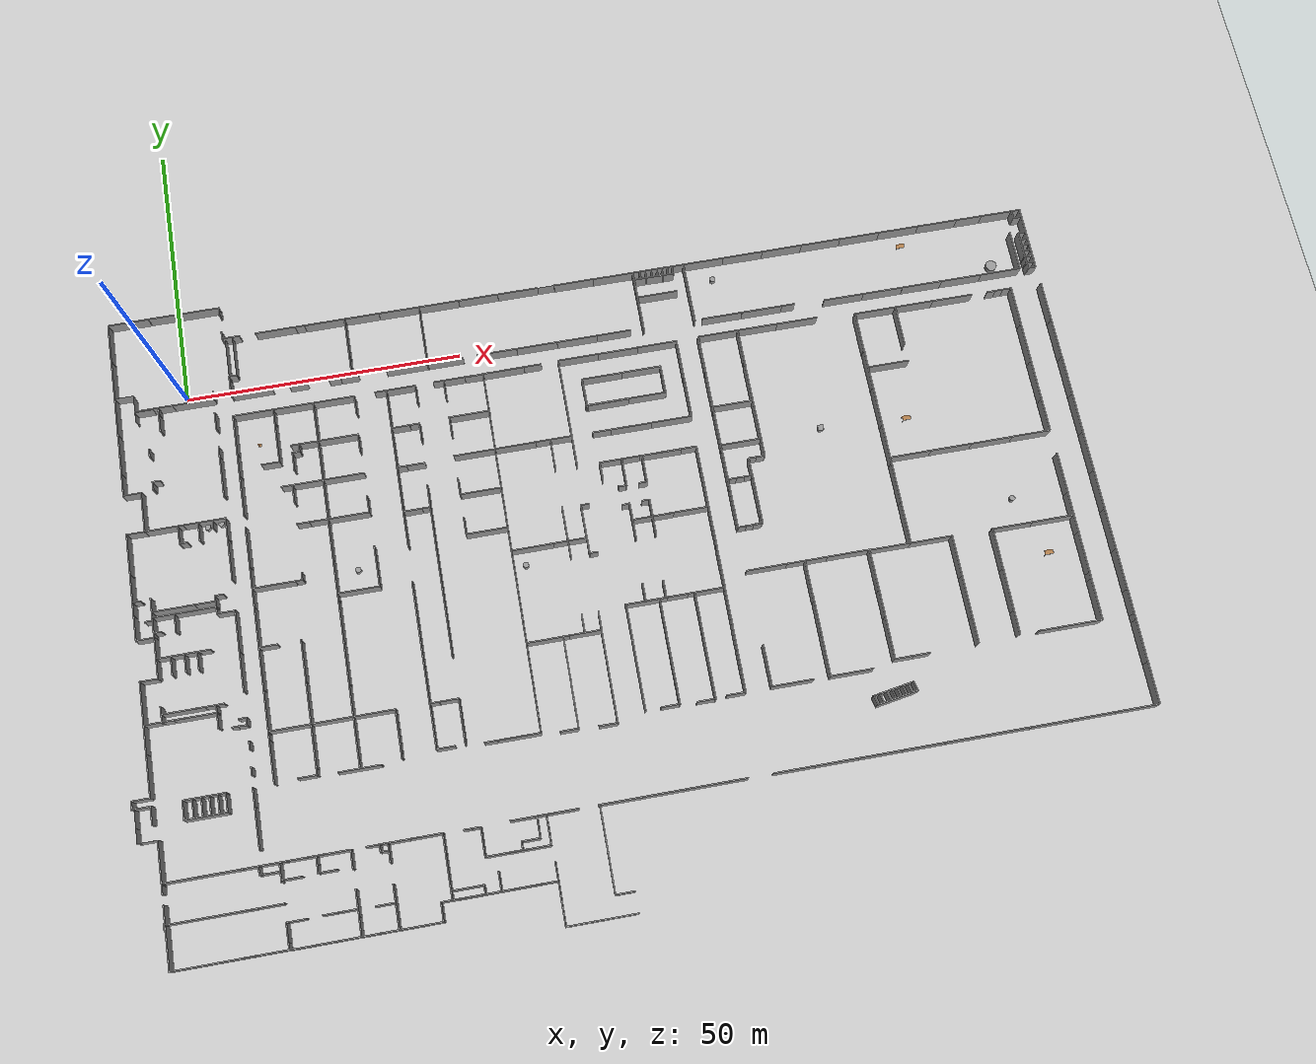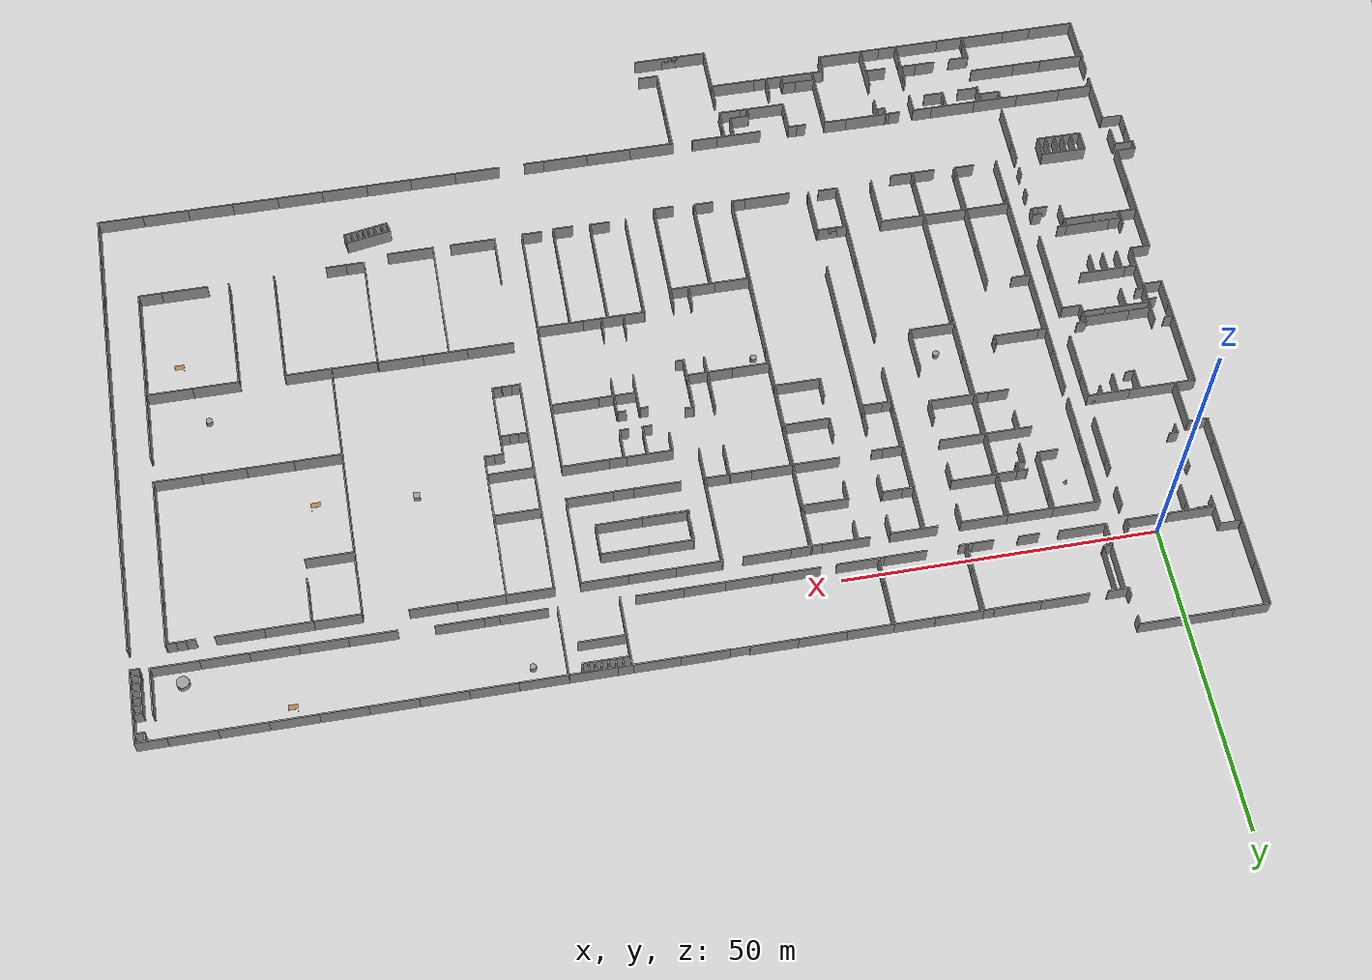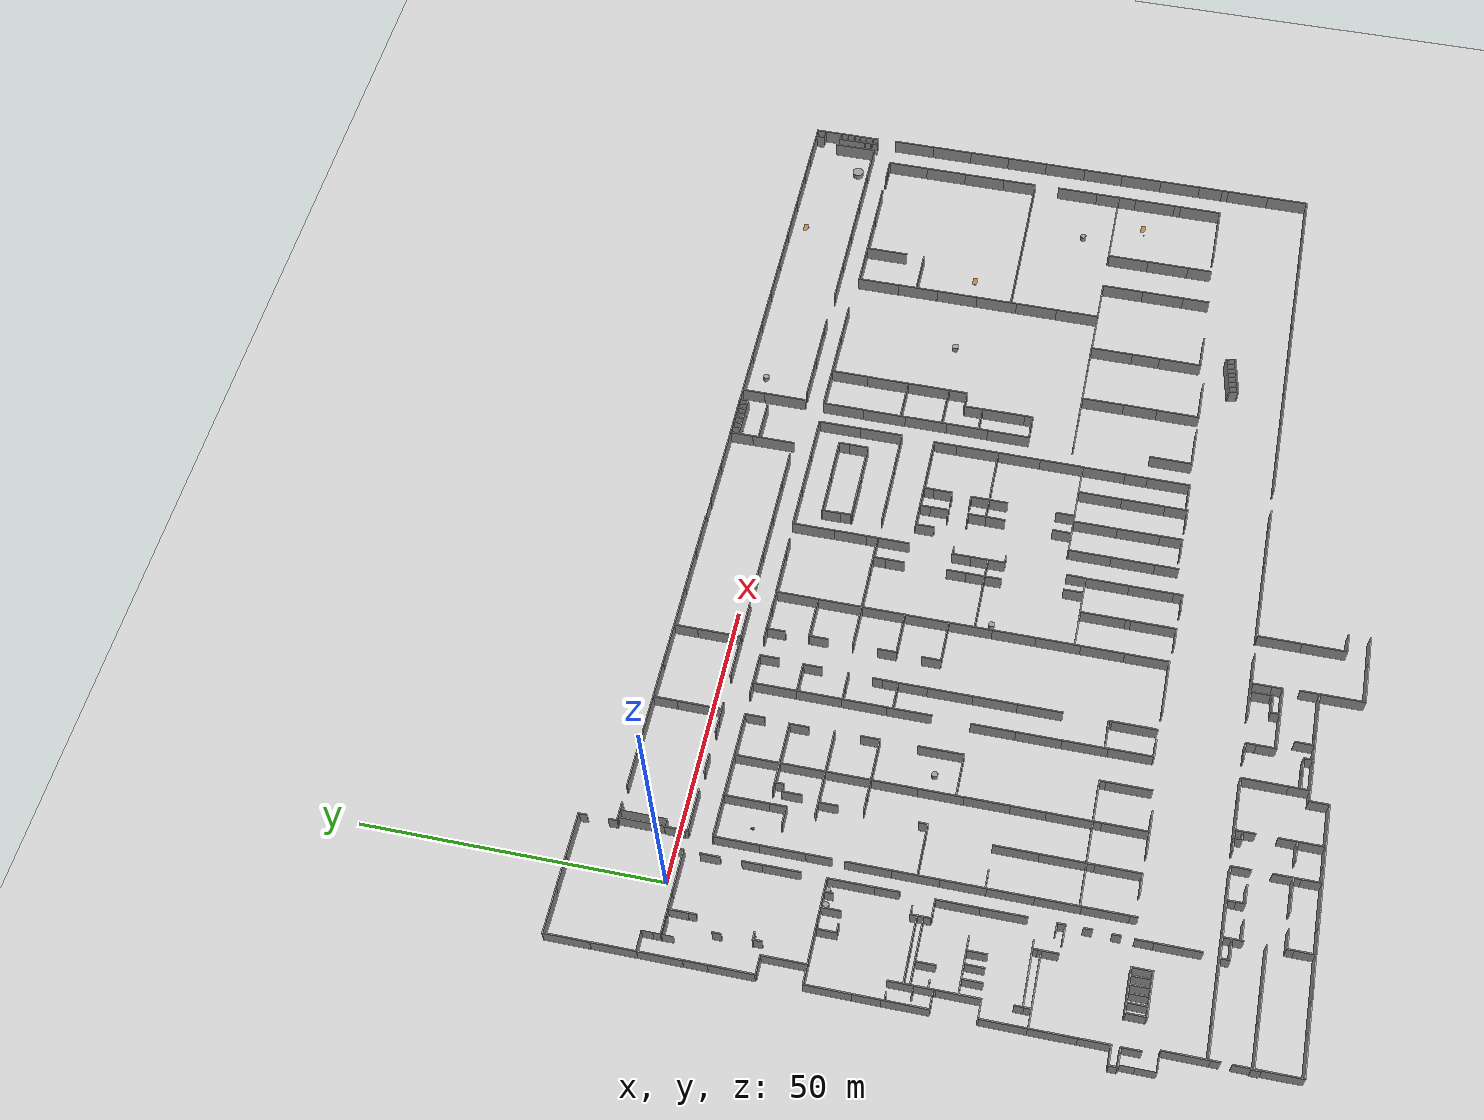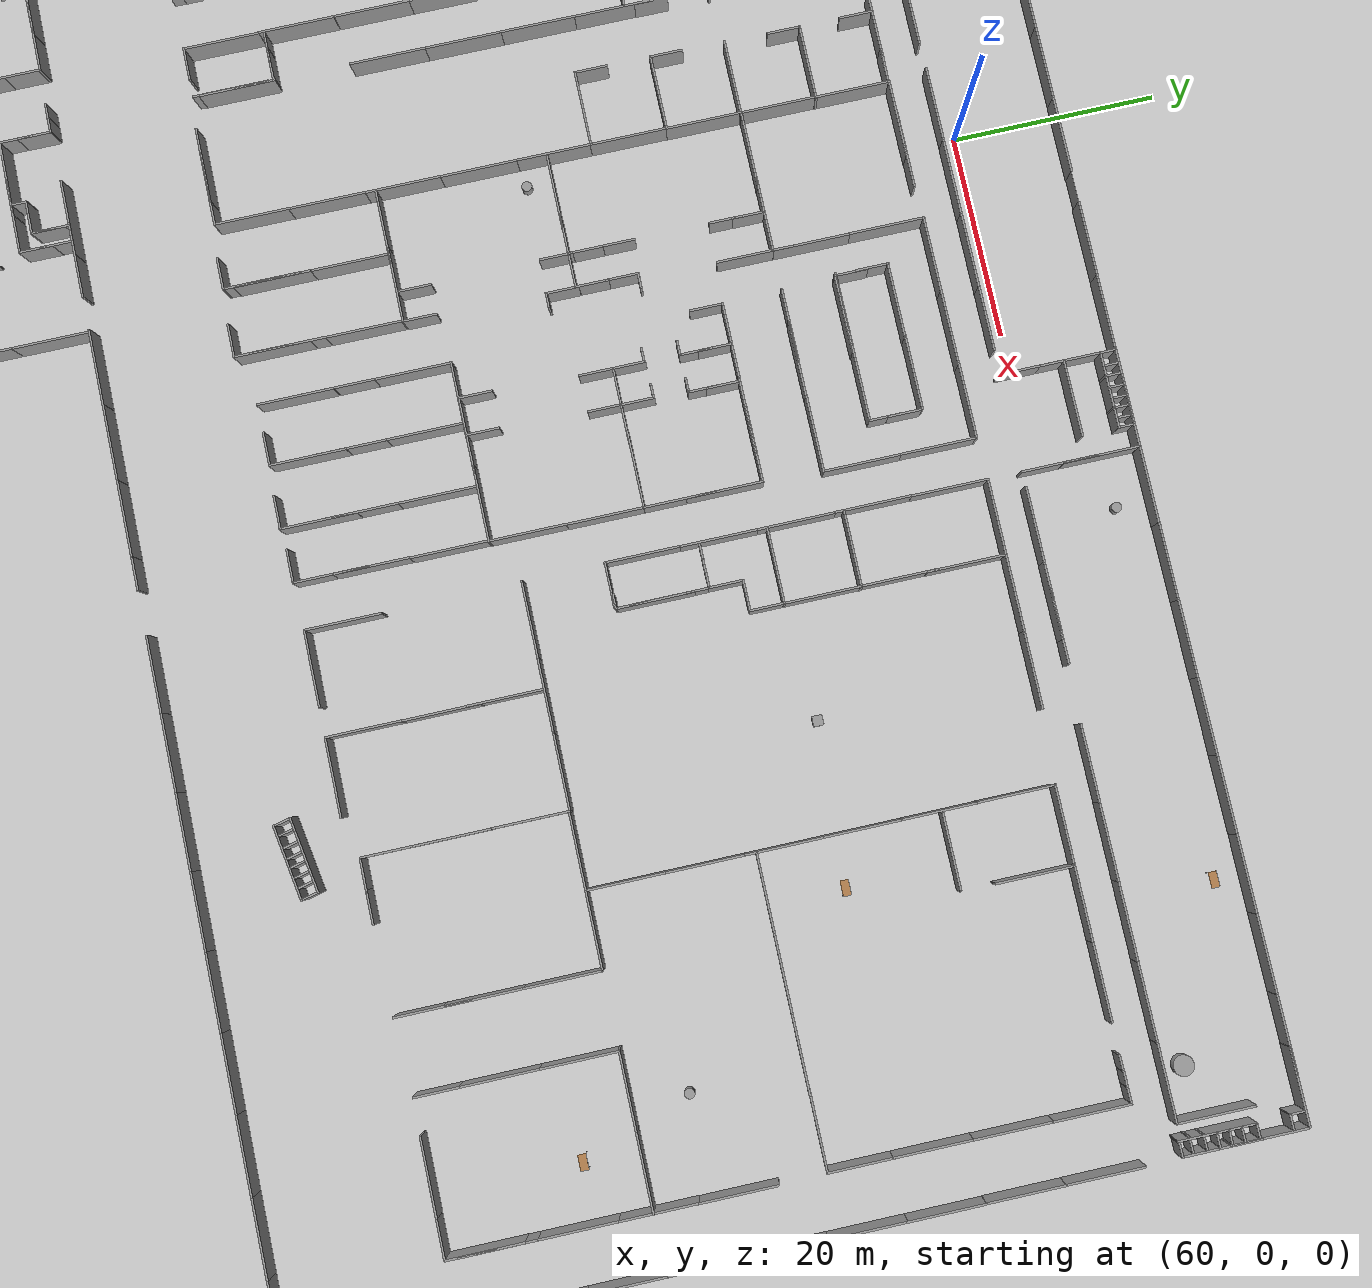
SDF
<sdf version="1.7">
 <world name="default">
  <light name="sun" type="directional">
   <pose>0 0 10 0 -0 0</pose>
   <diffuse>0.8 0.8 0.8 1</diffuse>
   <specular>0.2 0.2 0.2 1</specular>
   <attenuation>
    <range>1000</range>
    <constant>0.9</constant>
    <linear>0.01</linear>
    <quadratic>0.001</quadratic>
   </attenuation>
   <direction>-0.5 0.1 -0.9</direction>
   <spot><inner_angle>0</inner_angle><outer_angle>0</outer_angle><falloff>0</falloff></spot>
  </light>
  <model name="ground_plane">
   <static>1</static>
   <link name="link">
    <collision name="collision">
     <geometry><plane><normal>0 0 1</normal><size>100 100</size></plane></geometry>
     <surface>
      <contact><collide_bitmask>65535</collide_bitmask></contact>
      <friction><ode><mu>100</mu><mu2>50</mu2></ode></friction>
     </surface>
    </collision>
    <visual name="visual">
     <cast_shadows>0</cast_shadows>
     <geometry><plane><normal>0 0 1</normal><size>100 100</size></plane></geometry>
     <material>
      <script><uri>file://media/materials/scripts/gazebo.material</uri><name>Gazebo/Grey</name></script>
     </material>
    </visual>
   </link>
  </model>
  <gravity>0 0 -9.8</gravity>
  <magnetic_field>6e-06 2.3e-05 -4.2e-05</magnetic_field>
  <atmosphere type="adiabatic"/>
  <physics type="ode">
   <max_step_size>0.001</max_step_size>
   <real_time_factor>1</real_time_factor>
   <real_time_update_rate>1000</real_time_update_rate>
  </physics>
  <scene><ambient>0.4 0.4 0.4 1</ambient><background>0.7 0.7 0.7 1</background><shadows>1</shadows></scene>
  <spherical_coordinates>
   <surface_model>EARTH_WGS84</surface_model>
   <latitude_deg>0</latitude_deg>
   <longitude_deg>0</longitude_deg>
   <elevation>0</elevation>
   <heading_deg>0</heading_deg>
  </spherical_coordinates>
  <model name="grey_wall">
   <static>1</static>
   <link name="link">
    <pose>0 0 1.4 0 -0 0</pose>
    <collision name="collision"><geometry><box><size>7.5 0.2 2.8</size></box></geometry></collision>
    <visual name="visual">
     <cast_shadows>0</cast_shadows>
     <geometry><box><size>7.5 0.2 2.8</size></box></geometry>
     <material>
      <script>
       <uri>model://grey_wall/materials/scripts</uri>
       <uri>model://grey_wall/materials/textures</uri>
       <name>vrc/grey_wall</name>
      </script>
     </material>
    </visual>
   </link>
   <pose>4.11766 16.0782 0 0 -0 0</pose>
  </model>
  <model name="grey_wall_clone">
   <static>1</static>
   <link name="link">
    <pose>0 0 1.4 0 -0 0</pose>
    <collision name="collision"><geometry><box><size>7.5 0.2 2.8</size></box></geometry></collision>
    <visual name="visual">
     <cast_shadows>0</cast_shadows>
     <geometry><box><size>7.5 0.2 2.8</size></box></geometry>
     <material>
      <script>
       <uri>model://grey_wall/materials/scripts</uri>
       <uri>model://grey_wall/materials/textures</uri>
       <name>vrc/grey_wall</name>
      </script>
     </material>
    </visual>
   </link>
   <pose>-3.2022 16.0851 0 0 -0 0</pose>
  </model>
  <model name="grey_wall_clone_0">
   <static>1</static>
   <link name="link">
    <pose>0 0 1.4 0 -0 0</pose>
    <collision name="collision"><geometry><box><size>7.5 0.2 2.8</size></box></geometry></collision>
    <visual name="visual">
     <cast_shadows>0</cast_shadows>
     <geometry><box><size>7.5 0.2 2.8</size></box></geometry>
     <material>
      <script>
       <uri>model://grey_wall/materials/scripts</uri>
       <uri>model://grey_wall/materials/textures</uri>
       <name>vrc/grey_wall</name>
      </script>
     </material>
    </visual>
   </link>
   <pose>-8.91594 16.0599 0 0 -0 0</pose>
  </model>
  <model name="grey_wall_clone_2">
   <static>1</static>
   <link name="link">
    <pose>0 0 1.4 0 -0 0</pose>
    <collision name="collision"><geometry><box><size>7.5 0.2 2.8</size></box></geometry></collision>
    <visual name="visual">
     <cast_shadows>0</cast_shadows>
     <geometry><box><size>7.5 0.2 2.8</size></box></geometry>
     <material>
      <script>
       <uri>model://grey_wall/materials/scripts</uri>
       <uri>model://grey_wall/materials/textures</uri>
       <name>vrc/grey_wall</name>
      </script>
     </material>
    </visual>
   </link>
   <pose>-12.5815 12.3763 0 0 0 -1.5708</pose>
  </model>
  <model name="grey_wall_clone_2_clone">
   <static>1</static>
   <link name="link">
    <pose>0 0 1.4 0 -0 0</pose>
    <collision name="collision"><geometry><box><size>7.5 0.2 2.8</size></box></geometry></collision>
    <visual name="visual">
     <cast_shadows>0</cast_shadows>
     <geometry><box><size>7.5 0.2 2.8</size></box></geometry>
     <material>
      <script>
       <uri>model://grey_wall/materials/scripts</uri>
       <uri>model://grey_wall/materials/textures</uri>
       <name>vrc/grey_wall</name>
      </script>
     </material>
    </visual>
   </link>
   <pose>-12.5695 5.05048 0 0 0 -1.5708</pose>
  </model>
  <model name="grey_wall_clone_2_clone_0">
   <static>1</static>
   <link name="link">
    <pose>0 0 1.4 0 -0 0</pose>
    <collision name="collision"><geometry><box><size>7.5 0.2 2.8</size></box></geometry></collision>
    <visual name="visual">
     <cast_shadows>0</cast_shadows>
     <geometry><box><size>7.5 0.2 2.8</size></box></geometry>
     <material>
      <script>
       <uri>model://grey_wall/materials/scripts</uri>
       <uri>model://grey_wall/materials/textures</uri>
       <name>vrc/grey_wall</name>
      </script>
     </material>
    </visual>
   </link>
   <pose>-12.5572 -2.13055 0 0 0 -1.5708</pose>
  </model>
  <model name="grey_wall_clone_2_clone_1">
   <static>1</static>
   <link name="link">
    <pose>0 0 1.4 0 -0 0</pose>
    <collision name="collision"><geometry><box><size>7.5 0.2 2.8</size></box></geometry></collision>
    <visual name="visual">
     <cast_shadows>0</cast_shadows>
     <geometry><box><size>7.5 0.2 2.8</size></box></geometry>
     <material>
      <script>
       <uri>model://grey_wall/materials/scripts</uri>
       <uri>model://grey_wall/materials/textures</uri>
       <name>vrc/grey_wall</name>
      </script>
     </material>
    </visual>
   </link>
   <pose>-12.5371 -9.45403 0 0 0 -1.5708</pose>
  </model>
  <model name="grey_wall_clone_2_clone_2">
   <static>1</static>
   <link name="link">
    <pose>0 0 1.4 0 -0 0</pose>
    <collision name="collision"><geometry><box><size>7.5 0.2 2.8</size></box></geometry></collision>
    <visual name="visual">
     <cast_shadows>0</cast_shadows>
     <geometry><box><size>7.5 0.2 2.8</size></box></geometry>
     <material>
      <script>
       <uri>model://grey_wall/materials/scripts</uri>
       <uri>model://grey_wall/materials/textures</uri>
       <name>vrc/grey_wall</name>
      </script>
     </material>
    </visual>
   </link>
   <pose>-12.5493 -13.5009 0 0 0 -1.5708</pose>
  </model>
  <model name="grey_wall_clone_1">
   <static>1</static>
   <link name="link">
    <pose>0 0 1.4 0 -0 0</pose>
    <collision name="collision"><geometry><box><size>7.5 0.2 2.8</size></box></geometry></collision>
    <visual name="visual">
     <cast_shadows>0</cast_shadows>
     <geometry><box><size>7.5 0.2 2.8</size></box></geometry>
     <material>
      <script>
       <uri>model://grey_wall/materials/scripts</uri>
       <uri>model://grey_wall/materials/textures</uri>
       <name>vrc/grey_wall</name>
      </script>
     </material>
    </visual>
   </link>
   <pose>17.6261 9.8454 0 0 -0 0</pose>
  </model>
  <model name="half_slim_grey_wall">
   <link name="link">
    <pose>0 0 1.4 0 -0 0</pose>
    <inertial>
     <mass>1</mass>
     <inertia><ixx>1</ixx><ixy>0</ixy><ixz>0</ixz><iyy>1</iyy><iyz>0</iyz><izz>1</izz></inertia>
    </inertial>
    <visual name="visual">
     <cast_shadows>0</cast_shadows>
     <geometry><box><size>3.3 0.0001 2.8</size></box></geometry>
     <material>
      <script>
       <uri>model://grey_wall/materials/scripts</uri>
       <uri>model://grey_wall/materials/textures</uri>
       <name>vrc/grey_wall</name>
      </script>
      <shader type="pixel"><normal_map>__default__</normal_map></shader>
      <ambient>1 1 1 1</ambient>
      <diffuse>1 1 1 1</diffuse>
      <specular>0 0 0 1</specular>
      <emissive>0 0 0 1</emissive>
     </material>
    </visual>
    <collision name="collision">
     <geometry><box><size>3.3 0.2 2.8</size></box></geometry>
     <surface>
      <friction>
       <ode><mu>1</mu><mu2>1</mu2><fdir1>0 0 0</fdir1><slip1>0</slip1><slip2>0</slip2></ode>
       <torsional>
        <coefficient>1</coefficient>
        <patch_radius>0</patch_radius>
        <surface_radius>0</surface_radius>
        <use_patch_radius>1</use_patch_radius>
        <ode><slip>0</slip></ode>
       </torsional>
      </friction>
      <bounce><restitution_coefficient>0</restitution_coefficient><threshold>1e+06</threshold></bounce>
      <contact>
       <collide_without_contact>0</collide_without_contact>
       <collide_without_contact_bitmask>1</collide_without_contact_bitmask>
       <collide_bitmask>1</collide_bitmask>
       <ode>
        <soft_cfm>0</soft_cfm>
        <soft_erp>0.2</soft_erp>
        <kp>1e+13</kp>
        <kd>1</kd>
        <max_vel>0.01</max_vel>
        <min_depth>0</min_depth>
       </ode>
       <bullet>
        <split_impulse>1</split_impulse>
        <split_impulse_penetration_threshold>-0.01</split_impulse_penetration_threshold>
        <soft_cfm>0</soft_cfm>
        <soft_erp>0.2</soft_erp>
        <kp>1e+13</kp>
        <kd>1</kd>
       </bullet>
      </contact>
     </surface>
    </collision>
   </link>
   <static>1</static>
   <pose>-10.8124 1.45364 0 0 -0 0</pose>
  </model>
  <model name="half_slim_grey_wall_clone">
   <link name="link">
    <pose>0 0 1.4 0 -0 0</pose>
    <inertial>
     <mass>1</mass>
     <inertia><ixx>1</ixx><ixy>0</ixy><ixz>0</ixz><iyy>1</iyy><iyz>0</iyz><izz>1</izz></inertia>
    </inertial>
    <visual name="visual">
     <cast_shadows>0</cast_shadows>
     <geometry><box><size>3.3 0.0001 2.8</size></box></geometry>
     <material>
      <script>
       <uri>model://grey_wall/materials/scripts</uri>
       <uri>model://grey_wall/materials/textures</uri>
       <name>vrc/grey_wall</name>
      </script>
      <shader type="pixel"><normal_map>__default__</normal_map></shader>
      <ambient>1 1 1 1</ambient>
      <diffuse>1 1 1 1</diffuse>
      <specular>0 0 0 1</specular>
      <emissive>0 0 0 1</emissive>
     </material>
    </visual>
    <collision name="collision">
     <geometry><box><size>3.3 0.2 2.8</size></box></geometry>
     <surface>
      <friction>
       <ode><mu>1</mu><mu2>1</mu2><fdir1>0 0 0</fdir1><slip1>0</slip1><slip2>0</slip2></ode>
       <torsional>
        <coefficient>1</coefficient>
        <patch_radius>0</patch_radius>
        <surface_radius>0</surface_radius>
        <use_patch_radius>1</use_patch_radius>
        <ode><slip>0</slip></ode>
       </torsional>
      </friction>
      <bounce><restitution_coefficient>0</restitution_coefficient><threshold>1e+06</threshold></bounce>
      <contact>
       <collide_without_contact>0</collide_without_contact>
       <collide_without_contact_bitmask>1</collide_without_contact_bitmask>
       <collide_bitmask>1</collide_bitmask>
       <ode>
        <soft_cfm>0</soft_cfm>
        <soft_erp>0.2</soft_erp>
        <kp>1e+13</kp>
        <kd>1</kd>
        <max_vel>0.01</max_vel>
        <min_depth>0</min_depth>
       </ode>
       <bullet>
        <split_impulse>1</split_impulse>
        <split_impulse_penetration_threshold>-0.01</split_impulse_penetration_threshold>
        <soft_cfm>0</soft_cfm>
        <soft_erp>0.2</soft_erp>
        <kp>1e+13</kp>
        <kd>1</kd>
       </bullet>
      </contact>
     </surface>
    </collision>
   </link>
   <static>1</static>
   <pose>-9.17654 -0.189793 0 0 0 -1.5708</pose>
  </model>
  <model name="slim_grey_wall">
   <link name="link">
    <pose>0 0 1.4 0 -0 0</pose>
    <inertial>
     <mass>1</mass>
     <inertia><ixx>1</ixx><ixy>0</ixy><ixz>0</ixz><iyy>1</iyy><iyz>0</iyz><izz>1</izz></inertia>
    </inertial>
    <visual name="visual">
     <cast_shadows>0</cast_shadows>
     <geometry><box><size>7.5 0.0001 2.8</size></box></geometry>
     <material>
      <script>
       <uri>model://grey_wall/materials/scripts</uri>
       <uri>model://grey_wall/materials/textures</uri>
       <name>vrc/grey_wall</name>
      </script>
      <shader type="pixel"><normal_map>__default__</normal_map></shader>
      <ambient>1 1 1 1</ambient>
      <diffuse>1 1 1 1</diffuse>
      <specular>0 0 0 1</specular>
      <emissive>0 0 0 1</emissive>
     </material>
    </visual>
    <collision name="collision">
     <geometry><box><size>7.5 0.2 2.8</size></box></geometry>
     <surface>
      <friction>
       <ode><mu>1</mu><mu2>1</mu2><fdir1>0 0 0</fdir1><slip1>0</slip1><slip2>0</slip2></ode>
       <torsional>
        <coefficient>1</coefficient>
        <patch_radius>0</patch_radius>
        <surface_radius>0</surface_radius>
        <use_patch_radius>1</use_patch_radius>
        <ode><slip>0</slip></ode>
       </torsional>
      </friction>
      <bounce><restitution_coefficient>0</restitution_coefficient><threshold>1e+06</threshold></bounce>
      <contact>
       <collide_without_contact>0</collide_without_contact>
       <collide_without_contact_bitmask>1</collide_without_contact_bitmask>
       <collide_bitmask>1</collide_bitmask>
       <ode>
        <soft_cfm>0</soft_cfm>
        <soft_erp>0.2</soft_erp>
        <kp>1e+13</kp>
        <kd>1</kd>
        <max_vel>0.01</max_vel>
        <min_depth>0</min_depth>
       </ode>
       <bullet>
        <split_impulse>1</split_impulse>
        <split_impulse_penetration_threshold>-0.01</split_impulse_penetration_threshold>
        <soft_cfm>0</soft_cfm>
        <soft_erp>0.2</soft_erp>
        <kp>1e+13</kp>
        <kd>1</kd>
       </bullet>
      </contact>
     </surface>
    </collision>
   </link>
   <static>1</static>
   <pose>8.30317 6.07879 0 0 0 -1.5708</pose>
  </model>
  <model name="slim_grey_wall_clone">
   <link name="link">
    <pose>0 0 1.4 0 -0 0</pose>
    <inertial>
     <mass>1</mass>
     <inertia><ixx>1</ixx><ixy>0</ixy><ixz>0</ixz><iyy>1</iyy><iyz>0</iyz><izz>1</izz></inertia>
    </inertial>
    <visual name="visual">
     <cast_shadows>0</cast_shadows>
     <geometry><box><size>7.5 0.0001 2.8</size></box></geometry>
     <material>
      <script>
       <uri>model://grey_wall/materials/scripts</uri>
       <uri>model://grey_wall/materials/textures</uri>
       <name>vrc/grey_wall</name>
      </script>
      <shader type="pixel"><normal_map>__default__</normal_map></shader>
      <ambient>1 1 1 1</ambient>
      <diffuse>1 1 1 1</diffuse>
      <specular>0 0 0 1</specular>
      <emissive>0 0 0 1</emissive>
     </material>
    </visual>
    <collision name="collision">
     <geometry><box><size>7.5 0.2 2.8</size></box></geometry>
     <surface>
      <friction>
       <ode><mu>1</mu><mu2>1</mu2><fdir1>0 0 0</fdir1><slip1>0</slip1><slip2>0</slip2></ode>
       <torsional>
        <coefficient>1</coefficient>
        <patch_radius>0</patch_radius>
        <surface_radius>0</surface_radius>
        <use_patch_radius>1</use_patch_radius>
        <ode><slip>0</slip></ode>
       </torsional>
      </friction>
      <bounce><restitution_coefficient>0</restitution_coefficient><threshold>1e+06</threshold></bounce>
      <contact>
       <collide_without_contact>0</collide_without_contact>
       <collide_without_contact_bitmask>1</collide_without_contact_bitmask>
       <collide_bitmask>1</collide_bitmask>
       <ode>
        <soft_cfm>0</soft_cfm>
        <soft_erp>0.2</soft_erp>
        <kp>1e+13</kp>
        <kd>1</kd>
        <max_vel>0.01</max_vel>
        <min_depth>0</min_depth>
       </ode>
       <bullet>
        <split_impulse>1</split_impulse>
        <split_impulse_penetration_threshold>-0.01</split_impulse_penetration_threshold>
        <soft_cfm>0</soft_cfm>
        <soft_erp>0.2</soft_erp>
        <kp>1e+13</kp>
        <kd>1</kd>
       </bullet>
      </contact>
     </surface>
    </collision>
   </link>
   <static>1</static>
   <pose>9.64703 6.00773 0 0 0 -1.5708</pose>
  </model>
  <model name="half_slim_grey_wall_clone_clone">
   <link name="link">
    <pose>0 0 1.4 0 -0 0</pose>
    <inertial>
     <mass>1</mass>
     <inertia><ixx>1</ixx><ixy>0</ixy><ixz>0</ixz><iyy>1</iyy><iyz>0</iyz><izz>1</izz></inertia>
    </inertial>
    <visual name="visual">
     <cast_shadows>0</cast_shadows>
     <geometry><box><size>3.3 0.0001 2.8</size></box></geometry>
     <material>
      <script>
       <uri>model://grey_wall/materials/scripts</uri>
       <uri>model://grey_wall/materials/textures</uri>
       <name>vrc/grey_wall</name>
      </script>
      <shader type="pixel"><normal_map>__default__</normal_map></shader>
      <ambient>1 1 1 1</ambient>
      <diffuse>1 1 1 1</diffuse>
      <specular>0 0 0 1</specular>
      <emissive>0 0 0 1</emissive>
     </material>
    </visual>
    <collision name="collision">
     <geometry><box><size>3.3 0.2 2.8</size></box></geometry>
     <surface>
      <friction>
       <ode><mu>1</mu><mu2>1</mu2><fdir1>0 0 0</fdir1><slip1>0</slip1><slip2>0</slip2></ode>
       <torsional>
        <coefficient>1</coefficient>
        <patch_radius>0</patch_radius>
        <surface_radius>0</surface_radius>
        <use_patch_radius>1</use_patch_radius>
        <ode><slip>0</slip></ode>
       </torsional>
      </friction>
      <bounce><restitution_coefficient>0</restitution_coefficient><threshold>1e+06</threshold></bounce>
      <contact>
       <collide_without_contact>0</collide_without_contact>
       <collide_without_contact_bitmask>1</collide_without_contact_bitmask>
       <collide_bitmask>1</collide_bitmask>
       <ode>
        <soft_cfm>0</soft_cfm>
        <soft_erp>0.2</soft_erp>
        <kp>1e+13</kp>
        <kd>1</kd>
        <max_vel>0.01</max_vel>
        <min_depth>0</min_depth>
       </ode>
       <bullet>
        <split_impulse>1</split_impulse>
        <split_impulse_penetration_threshold>-0.01</split_impulse_penetration_threshold>
        <soft_cfm>0</soft_cfm>
        <soft_erp>0.2</soft_erp>
        <kp>1e+13</kp>
        <kd>1</kd>
       </bullet>
      </contact>
     </surface>
    </collision>
   </link>
   <static>1</static>
   <pose>-9.17683 -1.99265 0 0 0 -1.5708</pose>
  </model>
  <model name="grey_wall_clone_0_clone">
   <static>1</static>
   <link name="link">
    <pose>0 0 1.4 0 -0 0</pose>
    <collision name="collision"><geometry><box><size>7.5 0.2 2.8</size></box></geometry></collision>
    <visual name="visual">
     <cast_shadows>0</cast_shadows>
     <geometry><box><size>7.5 0.2 2.8</size></box></geometry>
     <material>
      <script>
       <uri>model://grey_wall/materials/scripts</uri>
       <uri>model://grey_wall/materials/textures</uri>
       <name>vrc/grey_wall</name>
      </script>
     </material>
    </visual>
   </link>
   <pose>-5.45445 -1.61024 0 0 -0 0</pose>
  </model>
  <model name="grey_wall_clone_0_clone_0">
   <static>1</static>
   <link name="link">
    <pose>0 0 1.4 0 -0 0</pose>
    <collision name="collision"><geometry><box><size>7.5 0.2 2.8</size></box></geometry></collision>
    <visual name="visual">
     <cast_shadows>0</cast_shadows>
     <geometry><box><size>7.5 0.2 2.8</size></box></geometry>
     <material>
      <script>
       <uri>model://grey_wall/materials/scripts</uri>
       <uri>model://grey_wall/materials/textures</uri>
       <name>vrc/grey_wall</name>
      </script>
     </material>
    </visual>
   </link>
   <pose>1.39307 -1.61725 0 0 -0 0</pose>
  </model>
  <model name="grey_wall_clone_2_clone_clone_0">
   <static>1</static>
   <link name="link">
    <pose>0 0 1.4 0 -0 0</pose>
    <collision name="collision"><geometry><box><size>7.5 0.2 2.8</size></box></geometry></collision>
    <visual name="visual">
     <cast_shadows>0</cast_shadows>
     <geometry><box><size>7.5 0.2 2.8</size></box></geometry>
     <material>
      <script>
       <uri>model://grey_wall/materials/scripts</uri>
       <uri>model://grey_wall/materials/textures</uri>
       <name>vrc/grey_wall</name>
      </script>
     </material>
    </visual>
   </link>
   <pose>-9.41065 -20.8124 0 0 0 -1.5708</pose>
  </model>
  <model name="half_grey_wall_clone_clone_0">
   <link name="link">
    <pose>0 0 1.4 0 -0 0</pose>
    <inertial>
     <mass>1</mass>
     <inertia><ixx>1</ixx><ixy>0</ixy><ixz>0</ixz><iyy>1</iyy><iyz>0</iyz><izz>1</izz></inertia>
    </inertial>
    <visual name="visual">
     <cast_shadows>0</cast_shadows>
     <geometry><box><size>3.3 0.2 2.8</size></box></geometry>
     <material>
      <script>
       <uri>model://grey_wall/materials/scripts</uri>
       <uri>model://grey_wall/materials/textures</uri>
       <name>vrc/grey_wall</name>
      </script>
      <shader type="pixel"><normal_map>__default__</normal_map></shader>
      <ambient>1 1 1 1</ambient>
      <diffuse>1 1 1 1</diffuse>
      <specular>0 0 0 1</specular>
      <emissive>0 0 0 1</emissive>
     </material>
    </visual>
    <collision name="collision">
     <geometry><box><size>7.5 0.2 2.8</size></box></geometry>
     <surface>
      <friction>
       <ode><mu>1</mu><mu2>1</mu2><fdir1>0 0 0</fdir1><slip1>0</slip1><slip2>0</slip2></ode>
       <torsional>
        <coefficient>1</coefficient>
        <patch_radius>0</patch_radius>
        <surface_radius>0</surface_radius>
        <use_patch_radius>1</use_patch_radius>
        <ode><slip>0</slip></ode>
       </torsional>
      </friction>
      <bounce><restitution_coefficient>0</restitution_coefficient><threshold>1e+06</threshold></bounce>
      <contact>
       <collide_without_contact>0</collide_without_contact>
       <collide_without_contact_bitmask>1</collide_without_contact_bitmask>
       <collide_bitmask>1</collide_bitmask>
       <ode>
        <soft_cfm>0</soft_cfm>
        <soft_erp>0.2</soft_erp>
        <kp>1e+13</kp>
        <kd>1</kd>
        <max_vel>0.01</max_vel>
        <min_depth>0</min_depth>
       </ode>
       <bullet>
        <split_impulse>1</split_impulse>
        <split_impulse_penetration_threshold>-0.01</split_impulse_penetration_threshold>
        <soft_cfm>0</soft_cfm>
        <soft_erp>0.2</soft_erp>
        <kp>1e+13</kp>
        <kd>1</kd>
       </bullet>
      </contact>
     </surface>
    </collision>
   </link>
   <static>1</static>
   <pose>-11.0309 -24.4662 0 0 -0 0</pose>
  </model>
  <model name="grey_wall_clone_2_clone_clone_clone">
   <static>1</static>
   <link name="link">
    <pose>0 0 1.4 0 -0 0</pose>
    <collision name="collision"><geometry><box><size>7.5 0.2 2.8</size></box></geometry></collision>
    <visual name="visual">
     <cast_shadows>0</cast_shadows>
     <geometry><box><size>7.5 0.2 2.8</size></box></geometry>
     <material>
      <script>
       <uri>model://grey_wall/materials/scripts</uri>
       <uri>model://grey_wall/materials/textures</uri>
       <name>vrc/grey_wall</name>
      </script>
     </material>
    </visual>
   </link>
   <pose>5.03836 -16.6141 0 0 0 -1.5708</pose>
  </model>
  <model name="grey_wall_clone_0_clone_0_clone">
   <static>1</static>
   <link name="link">
    <pose>0 0 1.4 0 -0 0</pose>
    <collision name="collision"><geometry><box><size>7.5 0.2 2.8</size></box></geometry></collision>
    <visual name="visual">
     <cast_shadows>0</cast_shadows>
     <geometry><box><size>7.5 0.2 2.8</size></box></geometry>
     <material>
      <script>
       <uri>model://grey_wall/materials/scripts</uri>
       <uri>model://grey_wall/materials/textures</uri>
       <name>vrc/grey_wall</name>
      </script>
     </material>
    </visual>
   </link>
   <pose>-5.66971 -24.4526 0 0 -0 0</pose>
  </model>
  <model name="grey_wall_clone_0_clone_0_clone_0">
   <static>1</static>
   <link name="link">
    <pose>0 0 1.4 0 -0 0</pose>
    <collision name="collision"><geometry><box><size>7.5 0.2 2.8</size></box></geometry></collision>
    <visual name="visual">
     <cast_shadows>0</cast_shadows>
     <geometry><box><size>7.5 0.2 2.8</size></box></geometry>
     <material>
      <script>
       <uri>model://grey_wall/materials/scripts</uri>
       <uri>model://grey_wall/materials/textures</uri>
       <name>vrc/grey_wall</name>
      </script>
     </material>
    </visual>
   </link>
   <pose>1.22377 -24.4572 0 0 -0 0</pose>
  </model>
  <model name="grey_wall_clone_2_clone_2_clone">
   <static>1</static>
   <link name="link">
    <pose>0 0 1.4 0 -0 0</pose>
    <collision name="collision"><geometry><box><size>7.5 0.2 2.8</size></box></geometry></collision>
    <visual name="visual">
     <cast_shadows>0</cast_shadows>
     <geometry><box><size>7.5 0.2 2.8</size></box></geometry>
     <material>
      <script>
       <uri>model://grey_wall/materials/scripts</uri>
       <uri>model://grey_wall/materials/textures</uri>
       <name>vrc/grey_wall</name>
      </script>
     </material>
    </visual>
   </link>
   <pose>-12.6184 -28.1335 0 0 0 -1.5708</pose>
  </model>
  <model name="grey_wall_clone_2_clone_2_clone_0">
   <static>1</static>
   <link name="link">
    <pose>0 0 1.4 0 -0 0</pose>
    <collision name="collision"><geometry><box><size>7.5 0.2 2.8</size></box></geometry></collision>
    <visual name="visual">
     <cast_shadows>0</cast_shadows>
     <geometry><box><size>7.5 0.2 2.8</size></box></geometry>
     <material>
      <script>
       <uri>model://grey_wall/materials/scripts</uri>
       <uri>model://grey_wall/materials/textures</uri>
       <name>vrc/grey_wall</name>
      </script>
     </material>
    </visual>
   </link>
   <pose>4.8782 -28.183 0 0 0 -1.5708</pose>
  </model>
  <model name="grey_wall_clone_2_clone_2_clone_1">
   <static>1</static>
   <link name="link">
    <pose>0 0 1.4 0 -0 0</pose>
    <collision name="collision"><geometry><box><size>7.5 0.2 2.8</size></box></geometry></collision>
    <visual name="visual">
     <cast_shadows>0</cast_shadows>
     <geometry><box><size>7.5 0.2 2.8</size></box></geometry>
     <material>
      <script>
       <uri>model://grey_wall/materials/scripts</uri>
       <uri>model://grey_wall/materials/textures</uri>
       <name>vrc/grey_wall</name>
      </script>
     </material>
    </visual>
   </link>
   <pose>4.89039 -32.2157 0 0 0 -1.5708</pose>
  </model>
  <model name="grey_wall_clone_2_clone_2_clone_2">
   <static>1</static>
   <link name="link">
    <pose>0 0 1.4 0 -0 0</pose>
    <collision name="collision"><geometry><box><size>7.5 0.2 2.8</size></box></geometry></collision>
    <visual name="visual">
     <cast_shadows>0</cast_shadows>
     <geometry><box><size>7.5 0.2 2.8</size></box></geometry>
     <material>
      <script>
       <uri>model://grey_wall/materials/scripts</uri>
       <uri>model://grey_wall/materials/textures</uri>
       <name>vrc/grey_wall</name>
      </script>
     </material>
    </visual>
   </link>
   <pose>-12.6232 -35.6178 0 0 0 -1.5708</pose>
  </model>
  <model name="grey_wall_clone_2_clone_2_clone_3">
   <static>1</static>
   <link name="link">
    <pose>0 0 1.4 0 -0 0</pose>
    <collision name="collision"><geometry><box><size>7.5 0.2 2.8</size></box></geometry></collision>
    <visual name="visual">
     <cast_shadows>0</cast_shadows>
     <geometry><box><size>7.5 0.2 2.8</size></box></geometry>
     <material>
      <script>
       <uri>model://grey_wall/materials/scripts</uri>
       <uri>model://grey_wall/materials/textures</uri>
       <name>vrc/grey_wall</name>
      </script>
     </material>
    </visual>
   </link>
   <pose>-12.6269 -40.135 0 0 0 -1.5708</pose>
  </model>
  <model name="grey_wall_clone_2_clone_clone_0_clone">
   <static>1</static>
   <link name="link">
    <pose>0 0 1.4 0 -0 0</pose>
    <collision name="collision"><geometry><box><size>7.5 0.2 2.8</size></box></geometry></collision>
    <visual name="visual">
     <cast_shadows>0</cast_shadows>
     <geometry><box><size>7.5 0.2 2.8</size></box></geometry>
     <material>
      <script>
       <uri>model://grey_wall/materials/scripts</uri>
       <uri>model://grey_wall/materials/textures</uri>
       <name>vrc/grey_wall</name>
      </script>
     </material>
    </visual>
   </link>
   <pose>-9.46912 -47.4395 0 0 0 -1.5708</pose>
  </model>
  <model name="grey_wall_clone_2_clone_2_clone_1_clone">
   <static>1</static>
   <link name="link">
    <pose>0 0 1.4 0 -0 0</pose>
    <collision name="collision"><geometry><box><size>7.5 0.2 2.8</size></box></geometry></collision>
    <visual name="visual">
     <cast_shadows>0</cast_shadows>
     <geometry><box><size>7.5 0.2 2.8</size></box></geometry>
     <material>
      <script>
       <uri>model://grey_wall/materials/scripts</uri>
       <uri>model://grey_wall/materials/textures</uri>
       <name>vrc/grey_wall</name>
      </script>
     </material>
    </visual>
   </link>
   <pose>4.79063 -45.0974 0 0 0 -1.5708</pose>
  </model>
  <model name="grey_wall_clone_2_clone_2_clone_1_clone_0">
   <static>1</static>
   <link name="link">
    <pose>0 0 1.4 0 -0 0</pose>
    <collision name="collision"><geometry><box><size>7.5 0.2 2.8</size></box></geometry></collision>
    <visual name="visual">
     <cast_shadows>0</cast_shadows>
     <geometry><box><size>7.5 0.2 2.8</size></box></geometry>
     <material>
      <script>
       <uri>model://grey_wall/materials/scripts</uri>
       <uri>model://grey_wall/materials/textures</uri>
       <name>vrc/grey_wall</name>
      </script>
     </material>
    </visual>
   </link>
   <pose>4.78468 -52.1739 0 0 0 -1.5708</pose>
  </model>
  <model name="grey_wall_clone_2_clone_2_clone_1_clone_1">
   <static>1</static>
   <link name="link">
    <pose>0 0 1.4 0 -0 0</pose>
    <collision name="collision"><geometry><box><size>7.5 0.2 2.8</size></box></geometry></collision>
    <visual name="visual">
     <cast_shadows>0</cast_shadows>
     <geometry><box><size>7.5 0.2 2.8</size></box></geometry>
     <material>
      <script>
       <uri>model://grey_wall/materials/scripts</uri>
       <uri>model://grey_wall/materials/textures</uri>
       <name>vrc/grey_wall</name>
      </script>
     </material>
    </visual>
   </link>
   <pose>-12.5913 -54.87 0 0 0 -1.5708</pose>
  </model>
  <model name="grey_wall_clone_2_clone_2_clone_1_clone_2">
   <static>1</static>
   <link name="link">
    <pose>0 0 1.4 0 -0 0</pose>
    <collision name="collision"><geometry><box><size>7.5 0.2 2.8</size></box></geometry></collision>
    <visual name="visual">
     <cast_shadows>0</cast_shadows>
     <geometry><box><size>7.5 0.2 2.8</size></box></geometry>
     <material>
      <script>
       <uri>model://grey_wall/materials/scripts</uri>
       <uri>model://grey_wall/materials/textures</uri>
       <name>vrc/grey_wall</name>
      </script>
     </material>
    </visual>
   </link>
   <pose>-12.5964 -62.2968 0 0 0 -1.5708</pose>
  </model>
  <model name="grey_wall_clone_2_clone_clone_0_clone_clone">
   <static>1</static>
   <link name="link">
    <pose>0 0 1.4 0 -0 0</pose>
    <collision name="collision"><geometry><box><size>7.5 0.2 2.8</size></box></geometry></collision>
    <visual name="visual">
     <cast_shadows>0</cast_shadows>
     <geometry><box><size>7.5 0.2 2.8</size></box></geometry>
     <material>
      <script>
       <uri>model://grey_wall/materials/scripts</uri>
       <uri>model://grey_wall/materials/textures</uri>
       <name>vrc/grey_wall</name>
      </script>
     </material>
    </visual>
   </link>
   <pose>-9.47835 -40.455 0 0 0 -1.5708</pose>
  </model>
  <model name="grey_wall_clone_0_clone_0_clone_clone">
   <static>1</static>
   <link name="link">
    <pose>0 0 1.4 0 -0 0</pose>
    <collision name="collision"><geometry><box><size>7.5 0.2 2.8</size></box></geometry></collision>
    <visual name="visual">
     <cast_shadows>0</cast_shadows>
     <geometry><box><size>7.5 0.2 2.8</size></box></geometry>
     <material>
      <script>
       <uri>model://grey_wall/materials/scripts</uri>
       <uri>model://grey_wall/materials/textures</uri>
       <name>vrc/grey_wall</name>
      </script>
     </material>
    </visual>
   </link>
   <pose>-2.16074 -39.1905 0 0 -0 0</pose>
  </model>
  <model name="grey_wall_clone_0_clone_0_clone_clone_0">
   <static>1</static>
   <link name="link">
    <pose>0 0 1.4 0 -0 0</pose>
    <collision name="collision"><geometry><box><size>7.5 0.2 2.8</size></box></geometry></collision>
    <visual name="visual">
     <cast_shadows>0</cast_shadows>
     <geometry><box><size>7.5 0.2 2.8</size></box></geometry>
     <material>
      <script>
       <uri>model://grey_wall/materials/scripts</uri>
       <uri>model://grey_wall/materials/textures</uri>
       <name>vrc/grey_wall</name>
      </script>
     </material>
    </visual>
   </link>
   <pose>-5.79782 -39.197 0 0 -0 0</pose>
  </model>
  <model name="grey_wall_clone_0_clone_0_clone_clone_1">
   <static>1</static>
   <link name="link">
    <pose>0 0 1.4 0 -0 0</pose>
    <collision name="collision"><geometry><box><size>7.5 0.2 2.8</size></box></geometry></collision>
    <visual name="visual">
     <cast_shadows>0</cast_shadows>
     <geometry><box><size>7.5 0.2 2.8</size></box></geometry>
     <material>
      <script>
       <uri>model://grey_wall/materials/scripts</uri>
       <uri>model://grey_wall/materials/textures</uri>
       <name>vrc/grey_wall</name>
      </script>
     </material>
    </visual>
   </link>
   <pose>-2.00004 -40.2283 0 0 -0 0</pose>
  </model>
  <model name="grey_wall_clone_0_clone_0_clone_clone_2">
   <static>1</static>
   <link name="link">
    <pose>0 0 1.4 0 -0 0</pose>
    <collision name="collision"><geometry><box><size>7.5 0.2 2.8</size></box></geometry></collision>
    <visual name="visual">
     <cast_shadows>0</cast_shadows>
     <geometry><box><size>7.5 0.2 2.8</size></box></geometry>
     <material>
      <script>
       <uri>model://grey_wall/materials/scripts</uri>
       <uri>model://grey_wall/materials/textures</uri>
       <name>vrc/grey_wall</name>
      </script>
     </material>
    </visual>
   </link>
   <pose>-5.81716 -40.22 0 0 -0 0</pose>
  </model>
  <model name="grey_wall_clone_0_clone_0_clone_clone_1_clone">
   <static>1</static>
   <link name="link">
    <pose>0 0 1.4 0 -0 0</pose>
    <collision name="collision"><geometry><box><size>7.5 0.2 2.8</size></box></geometry></collision>
    <visual name="visual">
     <cast_shadows>0</cast_shadows>
     <geometry><box><size>7.5 0.2 2.8</size></box></geometry>
     <material>
      <script>
       <uri>model://grey_wall/materials/scripts</uri>
       <uri>model://grey_wall/materials/textures</uri>
       <name>vrc/grey_wall</name>
      </script>
     </material>
    </visual>
   </link>
   <pose>-5.8029 -47.5938 0 0 -0 0</pose>
  </model>
  <model name="grey_wall_clone_0_clone_0_clone_clone_1_clone_0">
   <static>1</static>
   <link name="link">
    <pose>0 0 1.4 0 -0 0</pose>
    <collision name="collision"><geometry><box><size>7.5 0.2 2.8</size></box></geometry></collision>
    <visual name="visual">
     <cast_shadows>0</cast_shadows>
     <geometry><box><size>7.5 0.2 2.8</size></box></geometry>
     <material>
      <script>
       <uri>model://grey_wall/materials/scripts</uri>
       <uri>model://grey_wall/materials/textures</uri>
       <name>vrc/grey_wall</name>
      </script>
     </material>
    </visual>
   </link>
   <pose>-3.76168 -57.3524 0 0 -0 0</pose>
  </model>
  <model name="grey_wall_clone_0_clone_0_clone_clone_1_clone_1">
   <static>1</static>
   <link name="link">
    <pose>0 0 1.4 0 -0 0</pose>
    <collision name="collision"><geometry><box><size>7.5 0.2 2.8</size></box></geometry></collision>
    <visual name="visual">
     <cast_shadows>0</cast_shadows>
     <geometry><box><size>7.5 0.2 2.8</size></box></geometry>
     <material>
      <script>
       <uri>model://grey_wall/materials/scripts</uri>
       <uri>model://grey_wall/materials/textures</uri>
       <name>vrc/grey_wall</name>
      </script>
     </material>
    </visual>
   </link>
   <pose>-3.73175 -58.6913 0 0 -0 0</pose>
  </model>
  <model name="grey_wall_clone_2_clone_2_clone_1_clone_2_clone">
   <static>1</static>
   <link name="link">
    <pose>0 0 1.4 0 -0 0</pose>
    <collision name="collision"><geometry><box><size>7.5 0.2 2.8</size></box></geometry></collision>
    <visual name="visual">
     <cast_shadows>0</cast_shadows>
     <geometry><box><size>7.5 0.2 2.8</size></box></geometry>
     <material>
      <script>
       <uri>model://grey_wall/materials/scripts</uri>
       <uri>model://grey_wall/materials/textures</uri>
       <name>vrc/grey_wall</name>
      </script>
     </material>
    </visual>
   </link>
   <pose>-12.5827 -67.424 0 0 0 -1.5708</pose>
  </model>
  <model name="grey_wall_clone_0_clone_0_clone_clone_1_clone_clone">
   <static>1</static>
   <link name="link">
    <pose>0 0 1.4 0 -0 0</pose>
    <collision name="collision"><geometry><box><size>7.5 0.2 2.8</size></box></geometry></collision>
    <visual name="visual">
     <cast_shadows>0</cast_shadows>
     <geometry><box><size>7.5 0.2 2.8</size></box></geometry>
     <material>
      <script>
       <uri>model://grey_wall/materials/scripts</uri>
       <uri>model://grey_wall/materials/textures</uri>
       <name>vrc/grey_wall</name>
      </script>
     </material>
    </visual>
   </link>
   <pose>-3.78514 -47.5712 0 0 -0 0</pose>
  </model>
  <model name="grey_wall_clone_0_clone_0_clone_clone_1_clone_0_clone">
   <static>1</static>
   <link name="link">
    <pose>0 0 1.4 0 -0 0</pose>
    <collision name="collision"><geometry><box><size>7.5 0.2 2.8</size></box></geometry></collision>
    <visual name="visual">
     <cast_shadows>0</cast_shadows>
     <geometry><box><size>7.5 0.2 2.8</size></box></geometry>
     <material>
      <script>
       <uri>model://grey_wall/materials/scripts</uri>
       <uri>model://grey_wall/materials/textures</uri>
       <name>vrc/grey_wall</name>
      </script>
     </material>
    </visual>
   </link>
   <pose>-3.66144 -72.4087 0 0 -0 0</pose>
  </model>
  <model name="grey_wall_clone_0_clone_0_clone_clone_1_clone_0_clone_0">
   <static>1</static>
   <link name="link">
    <pose>0 0 1.4 0 -0 0</pose>
    <collision name="collision"><geometry><box><size>7.5 0.2 2.8</size></box></geometry></collision>
    <visual name="visual">
     <cast_shadows>0</cast_shadows>
     <geometry><box><size>7.5 0.2 2.8</size></box></geometry>
     <material>
      <script>
       <uri>model://grey_wall/materials/scripts</uri>
       <uri>model://grey_wall/materials/textures</uri>
       <name>vrc/grey_wall</name>
      </script>
     </material>
    </visual>
   </link>
   <pose>-3.67003 -75.7146 0 0 -0 0</pose>
  </model>
  <model name="half_slim_grey_wall_clone_clone_0">
   <link name="link">
    <pose>0 0 1.4 0 -0 0</pose>
    <inertial>
     <mass>1</mass>
     <inertia><ixx>1</ixx><ixy>0</ixy><ixz>0</ixz><iyy>1</iyy><iyz>0</iyz><izz>1</izz></inertia>
    </inertial>
    <visual name="visual">
     <cast_shadows>0</cast_shadows>
     <geometry><box><size>3.3 0.0001 2.8</size></box></geometry>
     <material>
      <script>
       <uri>model://grey_wall/materials/scripts</uri>
       <uri>model://grey_wall/materials/textures</uri>
       <name>vrc/grey_wall</name>
      </script>
      <shader type="pixel"><normal_map>__default__</normal_map></shader>
      <ambient>1 1 1 1</ambient>
      <diffuse>1 1 1 1</diffuse>
      <specular>0 0 0 1</specular>
      <emissive>0 0 0 1</emissive>
     </material>
    </visual>
    <collision name="collision">
     <geometry><box><size>3.3 0.2 2.8</size></box></geometry>
     <surface>
      <friction>
       <ode><mu>1</mu><mu2>1</mu2><fdir1>0 0 0</fdir1><slip1>0</slip1><slip2>0</slip2></ode>
       <torsional>
        <coefficient>1</coefficient>
        <patch_radius>0</patch_radius>
        <surface_radius>0</surface_radius>
        <use_patch_radius>1</use_patch_radius>
        <ode><slip>0</slip></ode>
       </torsional>
      </friction>
      <bounce><restitution_coefficient>0</restitution_coefficient><threshold>1e+06</threshold></bounce>
      <contact>
       <collide_without_contact>0</collide_without_contact>
       <collide_without_contact_bitmask>1</collide_without_contact_bitmask>
       <collide_bitmask>1</collide_bitmask>
       <ode>
        <soft_cfm>0</soft_cfm>
        <soft_erp>0.2</soft_erp>
        <kp>1e+13</kp>
        <kd>1</kd>
        <max_vel>0.01</max_vel>
        <min_depth>0</min_depth>
       </ode>
       <bullet>
        <split_impulse>1</split_impulse>
        <split_impulse_penetration_threshold>-0.01</split_impulse_penetration_threshold>
        <soft_cfm>0</soft_cfm>
        <soft_erp>0.2</soft_erp>
        <kp>1e+13</kp>
        <kd>1</kd>
       </bullet>
      </contact>
     </surface>
    </collision>
   </link>
   <static>1</static>
   <pose>-15.3614 -74.0364 0 0 0 -1.5708</pose>
  </model>
  <model name="half_slim_grey_wall_clone_clone_1">
   <link name="link">
    <pose>0 0 1.4 0 -0 0</pose>
    <inertial>
     <mass>1</mass>
     <inertia><ixx>1</ixx><ixy>0</ixy><ixz>0</ixz><iyy>1</iyy><iyz>0</iyz><izz>1</izz></inertia>
    </inertial>
    <visual name="visual">
     <cast_shadows>0</cast_shadows>
     <geometry><box><size>3.3 0.0001 2.8</size></box></geometry>
     <material>
      <script>
       <uri>model://grey_wall/materials/scripts</uri>
       <uri>model://grey_wall/materials/textures</uri>
       <name>vrc/grey_wall</name>
      </script>
      <shader type="pixel"><normal_map>__default__</normal_map></shader>
      <ambient>1 1 1 1</ambient>
      <diffuse>1 1 1 1</diffuse>
      <specular>0 0 0 1</specular>
      <emissive>0 0 0 1</emissive>
     </material>
    </visual>
    <collision name="collision">
     <geometry><box><size>3.3 0.2 2.8</size></box></geometry>
     <surface>
      <friction>
       <ode><mu>1</mu><mu2>1</mu2><fdir1>0 0 0</fdir1><slip1>0</slip1><slip2>0</slip2></ode>
       <torsional>
        <coefficient>1</coefficient>
        <patch_radius>0</patch_radius>
        <surface_radius>0</surface_radius>
        <use_patch_radius>1</use_patch_radius>
        <ode><slip>0</slip></ode>
       </torsional>
      </friction>
      <bounce><restitution_coefficient>0</restitution_coefficient><threshold>1e+06</threshold></bounce>
      <contact>
       <collide_without_contact>0</collide_without_contact>
       <collide_without_contact_bitmask>1</collide_without_contact_bitmask>
       <collide_bitmask>1</collide_bitmask>
       <ode>
        <soft_cfm>0</soft_cfm>
        <soft_erp>0.2</soft_erp>
        <kp>1e+13</kp>
        <kd>1</kd>
        <max_vel>0.01</max_vel>
        <min_depth>0</min_depth>
       </ode>
       <bullet>
        <split_impulse>1</split_impulse>
        <split_impulse_penetration_threshold>-0.01</split_impulse_penetration_threshold>
        <soft_cfm>0</soft_cfm>
        <soft_erp>0.2</soft_erp>
        <kp>1e+13</kp>
        <kd>1</kd>
       </bullet>
      </contact>
     </surface>
    </collision>
   </link>
   <static>1</static>
   <pose>-15.3705 -76.5972 0 0 0 -1.5708</pose>
  </model>
  <model name="half_slim_grey_wall_clone_0">
   <link name="link">
    <pose>0 0 1.4 0 -0 0</pose>
    <inertial>
     <mass>1</mass>
     <inertia><ixx>1</ixx><ixy>0</ixy><ixz>0</ixz><iyy>1</iyy><iyz>0</iyz><izz>1</izz></inertia>
    </inertial>
    <visual name="visual">
     <cast_shadows>0</cast_shadows>
     <geometry><box><size>3.3 0.0001 2.8</size></box></geometry>
     <material>
      <script>
       <uri>model://grey_wall/materials/scripts</uri>
       <uri>model://grey_wall/materials/textures</uri>
       <name>vrc/grey_wall</name>
      </script>
      <shader type="pixel"><normal_map>__default__</normal_map></shader>
      <ambient>1 1 1 1</ambient>
      <diffuse>1 1 1 1</diffuse>
      <specular>0 0 0 1</specular>
      <emissive>0 0 0 1</emissive>
     </material>
    </visual>
    <collision name="collision">
     <geometry><box><size>3.3 0.2 2.8</size></box></geometry>
     <surface>
      <friction>
       <ode><mu>1</mu><mu2>1</mu2><fdir1>0 0 0</fdir1><slip1>0</slip1><slip2>0</slip2></ode>
       <torsional>
        <coefficient>1</coefficient>
        <patch_radius>0</patch_radius>
        <surface_radius>0</surface_radius>
        <use_patch_radius>1</use_patch_radius>
        <ode><slip>0</slip></ode>
       </torsional>
      </friction>
      <bounce><restitution_coefficient>0</restitution_coefficient><threshold>1e+06</threshold></bounce>
      <contact>
       <collide_without_contact>0</collide_without_contact>
       <collide_without_contact_bitmask>1</collide_without_contact_bitmask>
       <collide_bitmask>1</collide_bitmask>
       <ode>
        <soft_cfm>0</soft_cfm>
        <soft_erp>0.2</soft_erp>
        <kp>1e+13</kp>
        <kd>1</kd>
        <max_vel>0.01</max_vel>
        <min_depth>0</min_depth>
       </ode>
       <bullet>
        <split_impulse>1</split_impulse>
        <split_impulse_penetration_threshold>-0.01</split_impulse_penetration_threshold>
        <soft_cfm>0</soft_cfm>
        <soft_erp>0.2</soft_erp>
        <kp>1e+13</kp>
        <kd>1</kd>
       </bullet>
      </contact>
     </surface>
    </collision>
   </link>
   <static>1</static>
   <pose>-7.53352 -1.83009 0 0 -0 0</pose>
  </model>
  <model name="half_slim_grey_wall_clone_1">
   <link name="link">
    <pose>0 0 1.4 0 -0 0</pose>
    <inertial>
     <mass>1</mass>
     <inertia><ixx>1</ixx><ixy>0</ixy><ixz>0</ixz><iyy>1</iyy><iyz>0</iyz><izz>1</izz></inertia>
    </inertial>
    <visual name="visual">
     <cast_shadows>0</cast_shadows>
     <geometry><box><size>3.3 0.0001 2.8</size></box></geometry>
     <material>
      <script>
       <uri>model://grey_wall/materials/scripts</uri>
       <uri>model://grey_wall/materials/textures</uri>
       <name>vrc/grey_wall</name>
      </script>
      <shader type="pixel"><normal_map>__default__</normal_map></shader>
      <ambient>1 1 1 1</ambient>
      <diffuse>1 1 1 1</diffuse>
      <specular>0 0 0 1</specular>
      <emissive>0 0 0 1</emissive>
     </material>
    </visual>
    <collision name="collision">
     <geometry><box><size>3.3 0.2 2.8</size></box></geometry>
     <surface>
      <friction>
       <ode><mu>1</mu><mu2>1</mu2><fdir1>0 0 0</fdir1><slip1>0</slip1><slip2>0</slip2></ode>
       <torsional>
        <coefficient>1</coefficient>
        <patch_radius>0</patch_radius>
        <surface_radius>0</surface_radius>
        <use_patch_radius>1</use_patch_radius>
        <ode><slip>0</slip></ode>
       </torsional>
      </friction>
      <bounce><restitution_coefficient>0</restitution_coefficient><threshold>1e+06</threshold></bounce>
      <contact>
       <collide_without_contact>0</collide_without_contact>
       <collide_without_contact_bitmask>1</collide_without_contact_bitmask>
       <collide_bitmask>1</collide_bitmask>
       <ode>
        <soft_cfm>0</soft_cfm>
        <soft_erp>0.2</soft_erp>
        <kp>1e+13</kp>
        <kd>1</kd>
        <max_vel>0.01</max_vel>
        <min_depth>0</min_depth>
       </ode>
       <bullet>
        <split_impulse>1</split_impulse>
        <split_impulse_penetration_threshold>-0.01</split_impulse_penetration_threshold>
        <soft_cfm>0</soft_cfm>
        <soft_erp>0.2</soft_erp>
        <kp>1e+13</kp>
        <kd>1</kd>
       </bullet>
      </contact>
     </surface>
    </collision>
   </link>
   <static>1</static>
   <pose>-13.7289 -78.238 0 0 -0 0</pose>
  </model>
  <model name="grey_wall_clone_1_clone_2">
   <static>1</static>
   <link name="link">
    <pose>0 0 1.4 0 -0 0</pose>
    <collision name="collision"><geometry><box><size>7.5 0.2 2.8</size></box></geometry></collision>
    <visual name="visual">
     <cast_shadows>0</cast_shadows>
     <geometry><box><size>7.5 0.2 2.8</size></box></geometry>
     <material>
      <script>
       <uri>model://grey_wall/materials/scripts</uri>
       <uri>model://grey_wall/materials/textures</uri>
       <name>vrc/grey_wall</name>
      </script>
     </material>
    </visual>
   </link>
   <pose>24.9982 9.83483 0 0 -0 0</pose>
  </model>
  <model name="grey_wall_clone_1_clone_clone">
   <static>1</static>
   <link name="link">
    <pose>0 0 1.4 0 -0 0</pose>
    <collision name="collision"><geometry><box><size>7.5 0.2 2.8</size></box></geometry></collision>
    <visual name="visual">
     <cast_shadows>0</cast_shadows>
     <geometry><box><size>7.5 0.2 2.8</size></box></geometry>
     <material>
      <script>
       <uri>model://grey_wall/materials/scripts</uri>
       <uri>model://grey_wall/materials/textures</uri>
       <name>vrc/grey_wall</name>
      </script>
     </material>
    </visual>
   </link>
   <pose>11.8089 -5.52914 0 0 -0 0</pose>
  </model>
  <model name="grey_wall_clone_2_clone_clone_clone_0">
   <static>1</static>
   <link name="link">
    <pose>0 0 1.4 0 -0 0</pose>
    <collision name="collision"><geometry><box><size>7.5 0.2 2.8</size></box></geometry></collision>
    <visual name="visual">
     <cast_shadows>0</cast_shadows>
     <geometry><box><size>7.5 0.2 2.8</size></box></geometry>
     <material>
      <script>
       <uri>model://grey_wall/materials/scripts</uri>
       <uri>model://grey_wall/materials/textures</uri>
       <name>vrc/grey_wall</name>
      </script>
     </material>
    </visual>
   </link>
   <pose>8.17975 -9.2229 0 0 0 -1.5708</pose>
  </model>
  <model name="grey_wall_clone_2_clone_clone_clone_1">
   <static>1</static>
   <link name="link">
    <pose>0 0 1.4 0 -0 0</pose>
    <collision name="collision"><geometry><box><size>7.5 0.2 2.8</size></box></geometry></collision>
    <visual name="visual">
     <cast_shadows>0</cast_shadows>
     <geometry><box><size>7.5 0.2 2.8</size></box></geometry>
     <material>
      <script>
       <uri>model://grey_wall/materials/scripts</uri>
       <uri>model://grey_wall/materials/textures</uri>
       <name>vrc/grey_wall</name>
      </script>
     </material>
    </visual>
   </link>
   <pose>15.4556 -9.202 0 0 0 -1.5708</pose>
  </model>
  <model name="grey_wall_clone_2_clone_clone_clone_2">
   <static>1</static>
   <link name="link">
    <pose>0 0 1.4 0 -0 0</pose>
    <collision name="collision"><geometry><box><size>7.5 0.2 2.8</size></box></geometry></collision>
    <visual name="visual">
     <cast_shadows>0</cast_shadows>
     <geometry><box><size>7.5 0.2 2.8</size></box></geometry>
     <material>
      <script>
       <uri>model://grey_wall/materials/scripts</uri>
       <uri>model://grey_wall/materials/textures</uri>
       <name>vrc/grey_wall</name>
      </script>
     </material>
    </visual>
   </link>
   <pose>15.4624 -12.0058 0 0 0 -1.5708</pose>
  </model>
  <model name="grey_wall_clone_2_clone_clone_clone_0_clone">
   <static>1</static>
   <link name="link">
    <pose>0 0 1.4 0 -0 0</pose>
    <collision name="collision"><geometry><box><size>7.5 0.2 2.8</size></box></geometry></collision>
    <visual name="visual">
     <cast_shadows>0</cast_shadows>
     <geometry><box><size>7.5 0.2 2.8</size></box></geometry>
     <material>
      <script>
       <uri>model://grey_wall/materials/scripts</uri>
       <uri>model://grey_wall/materials/textures</uri>
       <name>vrc/grey_wall</name>
      </script>
     </material>
    </visual>
   </link>
   <pose>8.18142 -16.6644 0 0 0 -1.5708</pose>
  </model>
  <model name="grey_wall_clone_2_clone_clone_clone_0_clone_0">
   <static>1</static>
   <link name="link">
    <pose>0 0 1.4 0 -0 0</pose>
    <collision name="collision"><geometry><box><size>7.5 0.2 2.8</size></box></geometry></collision>
    <visual name="visual">
     <cast_shadows>0</cast_shadows>
     <geometry><box><size>7.5 0.2 2.8</size></box></geometry>
     <material>
      <script>
       <uri>model://grey_wall/materials/scripts</uri>
       <uri>model://grey_wall/materials/textures</uri>
       <name>vrc/grey_wall</name>
      </script>
     </material>
    </visual>
   </link>
   <pose>8.18766 -20.8291 0 0 0 -1.5708</pose>
  </model>
  <model name="grey_wall_clone_2_clone_clone_clone_0_clone_1">
   <static>1</static>
   <link name="link">
    <pose>0 0 1.4 0 -0 0</pose>
    <collision name="collision"><geometry><box><size>7.5 0.2 2.8</size></box></geometry></collision>
    <visual name="visual">
     <cast_shadows>0</cast_shadows>
     <geometry><box><size>7.5 0.2 2.8</size></box></geometry>
     <material>
      <script>
       <uri>model://grey_wall/materials/scripts</uri>
       <uri>model://grey_wall/materials/textures</uri>
       <name>vrc/grey_wall</name>
      </script>
     </material>
    </visual>
   </link>
   <pose>8.15864 -30.385 0 0 0 -1.5708</pose>
  </model>
  <model name="grey_wall_clone_1_clone_clone_clone">
   <static>1</static>
   <link name="link">
    <pose>0 0 1.4 0 -0 0</pose>
    <collision name="collision"><geometry><box><size>7.5 0.2 2.8</size></box></geometry></collision>
    <visual name="visual">
     <cast_shadows>0</cast_shadows>
     <geometry><box><size>7.5 0.2 2.8</size></box></geometry>
     <material>
      <script>
       <uri>model://grey_wall/materials/scripts</uri>
       <uri>model://grey_wall/materials/textures</uri>
       <name>vrc/grey_wall</name>
      </script>
     </material>
    </visual>
   </link>
   <pose>19.0833 -5.54452 0 0 -0 0</pose>
  </model>
  <model name="grey_wall_clone_2_clone_clone_clone_1_clone">
   <static>1</static>
   <link name="link">
    <pose>0 0 1.4 0 -0 0</pose>
    <collision name="collision"><geometry><box><size>7.5 0.2 2.8</size></box></geometry></collision>
    <visual name="visual">
     <cast_shadows>0</cast_shadows>
     <geometry><box><size>7.5 0.2 2.8</size></box></geometry>
     <material>
      <script>
       <uri>model://grey_wall/materials/scripts</uri>
       <uri>model://grey_wall/materials/textures</uri>
       <name>vrc/grey_wall</name>
      </script>
     </material>
    </visual>
   </link>
   <pose>22.7127 -9.30618 0 0 0 -1.5708</pose>
  </model>
  <model name="half_grey_wall_clone_0_clone_0">
   <link name="link">
    <pose>0 0 1.4 0 -0 0</pose>
    <inertial>
     <mass>1</mass>
     <inertia><ixx>1</ixx><ixy>0</ixy><ixz>0</ixz><iyy>1</iyy><iyz>0</iyz><izz>1</izz></inertia>
    </inertial>
    <visual name="visual">
     <cast_shadows>0</cast_shadows>
     <geometry><box><size>3.3 0.2 2.8</size></box></geometry>
     <material>
      <script>
       <uri>model://grey_wall/materials/scripts</uri>
       <uri>model://grey_wall/materials/textures</uri>
       <name>vrc/grey_wall</name>
      </script>
      <shader type="pixel"><normal_map>__default__</normal_map></shader>
      <ambient>1 1 1 1</ambient>
      <diffuse>1 1 1 1</diffuse>
      <specular>0 0 0 1</specular>
      <emissive>0 0 0 1</emissive>
     </material>
    </visual>
    <collision name="collision">
     <geometry><box><size>7.5 0.2 2.8</size></box></geometry>
     <surface>
      <friction>
       <ode><mu>1</mu><mu2>1</mu2><fdir1>0 0 0</fdir1><slip1>0</slip1><slip2>0</slip2></ode>
       <torsional>
        <coefficient>1</coefficient>
        <patch_radius>0</patch_radius>
        <surface_radius>0</surface_radius>
        <use_patch_radius>1</use_patch_radius>
        <ode><slip>0</slip></ode>
       </torsional>
      </friction>
      <bounce><restitution_coefficient>0</restitution_coefficient><threshold>1e+06</threshold></bounce>
      <contact>
       <collide_without_contact>0</collide_without_contact>
       <collide_without_contact_bitmask>1</collide_without_contact_bitmask>
       <collide_bitmask>1</collide_bitmask>
       <ode>
        <soft_cfm>0</soft_cfm>
        <soft_erp>0.2</soft_erp>
        <kp>1e+13</kp>
        <kd>1</kd>
        <max_vel>0.01</max_vel>
        <min_depth>0</min_depth>
       </ode>
       <bullet>
        <split_impulse>1</split_impulse>
        <split_impulse_penetration_threshold>-0.01</split_impulse_penetration_threshold>
        <soft_cfm>0</soft_cfm>
        <soft_erp>0.2</soft_erp>
        <kp>1e+13</kp>
        <kd>1</kd>
       </bullet>
      </contact>
     </surface>
    </collision>
   </link>
   <static>1</static>
   <pose>21.1071 -12.9684 0 0 -0 0</pose>
  </model>
  <model name="grey_wall_clone_2_clone_clone_clone_1_clone_clone">
   <static>1</static>
   <link name="link">
    <pose>0 0 1.4 0 -0 0</pose>
    <collision name="collision"><geometry><box><size>7.5 0.2 2.8</size></box></geometry></collision>
    <visual name="visual">
     <cast_shadows>0</cast_shadows>
     <geometry><box><size>7.5 0.2 2.8</size></box></geometry>
     <material>
      <script>
       <uri>model://grey_wall/materials/scripts</uri>
       <uri>model://grey_wall/materials/textures</uri>
       <name>vrc/grey_wall</name>
      </script>
     </material>
    </visual>
   </link>
   <pose>22.7161 -16.7659 0 0 0 -1.5708</pose>
  </model>
  <model name="grey_wall_clone_1_clone_clone_clone_0">
   <static>1</static>
   <link name="link">
    <pose>0 0 1.4 0 -0 0</pose>
    <collision name="collision"><geometry><box><size>7.5 0.2 2.8</size></box></geometry></collision>
    <visual name="visual">
     <cast_shadows>0</cast_shadows>
     <geometry><box><size>7.5 0.2 2.8</size></box></geometry>
     <material>
      <script>
       <uri>model://grey_wall/materials/scripts</uri>
       <uri>model://grey_wall/materials/textures</uri>
       <name>vrc/grey_wall</name>
      </script>
     </material>
    </visual>
   </link>
   <pose>18.9634 -20.4211 0 0 -0 0</pose>
  </model>
  <model name="grey_wall_clone_2_clone_clone_clone_1_clone_clone_clone">
   <static>1</static>
   <link name="link">
    <pose>0 0 1.4 0 -0 0</pose>
    <collision name="collision"><geometry><box><size>7.5 0.2 2.8</size></box></geometry></collision>
    <visual name="visual">
     <cast_shadows>0</cast_shadows>
     <geometry><box><size>7.5 0.2 2.8</size></box></geometry>
     <material>
      <script>
       <uri>model://grey_wall/materials/scripts</uri>
       <uri>model://grey_wall/materials/textures</uri>
       <name>vrc/grey_wall</name>
      </script>
     </material>
    </visual>
   </link>
   <pose>22.7175 -24.1341 0 0 0 -1.5708</pose>
  </model>
  <model name="grey_wall_clone_2_clone_clone_clone_0_clone_1_clone">
   <static>1</static>
   <link name="link">
    <pose>0 0 1.4 0 -0 0</pose>
    <collision name="collision"><geometry><box><size>7.5 0.2 2.8</size></box></geometry></collision>
    <visual name="visual">
     <cast_shadows>0</cast_shadows>
     <geometry><box><size>7.5 0.2 2.8</size></box></geometry>
     <material>
      <script>
       <uri>model://grey_wall/materials/scripts</uri>
       <uri>model://grey_wall/materials/textures</uri>
       <name>vrc/grey_wall</name>
      </script>
     </material>
    </visual>
   </link>
   <pose>8.15614 -37.8124 0 0 0 -1.5708</pose>
  </model>
  <model name="grey_wall_clone_2_clone_clone_clone_0_clone_1_clone_0">
   <static>1</static>
   <link name="link">
    <pose>0 0 1.4 0 -0 0</pose>
    <collision name="collision"><geometry><box><size>7.5 0.2 2.8</size></box></geometry></collision>
    <visual name="visual">
     <cast_shadows>0</cast_shadows>
     <geometry><box><size>7.5 0.2 2.8</size></box></geometry>
     <material>
      <script>
       <uri>model://grey_wall/materials/scripts</uri>
       <uri>model://grey_wall/materials/textures</uri>
       <name>vrc/grey_wall</name>
      </script>
     </material>
    </visual>
   </link>
   <pose>8.15923 -45.1928 0 0 0 -1.5708</pose>
  </model>
  <model name="grey_wall_clone_2_clone_clone_clone_0_clone_1_clone_1">
   <static>1</static>
   <link name="link">
    <pose>0 0 1.4 0 -0 0</pose>
    <collision name="collision"><geometry><box><size>7.5 0.2 2.8</size></box></geometry></collision>
    <visual name="visual">
     <cast_shadows>0</cast_shadows>
     <geometry><box><size>7.5 0.2 2.8</size></box></geometry>
     <material>
      <script>
       <uri>model://grey_wall/materials/scripts</uri>
       <uri>model://grey_wall/materials/textures</uri>
       <name>vrc/grey_wall</name>
      </script>
     </material>
    </visual>
   </link>
   <pose>8.15673 -52.6567 0 0 0 -1.5708</pose>
  </model>
  <model name="grey_wall_clone_2_clone_clone_clone_0_clone_1_clone_2">
   <static>1</static>
   <link name="link">
    <pose>0 0 1.4 0 -0 0</pose>
    <collision name="collision"><geometry><box><size>7.5 0.2 2.8</size></box></geometry></collision>
    <visual name="visual">
     <cast_shadows>0</cast_shadows>
     <geometry><box><size>7.5 0.2 2.8</size></box></geometry>
     <material>
      <script>
       <uri>model://grey_wall/materials/scripts</uri>
       <uri>model://grey_wall/materials/textures</uri>
       <name>vrc/grey_wall</name>
      </script>
     </material>
    </visual>
   </link>
   <pose>8.15911 -59.968 0 0 0 -1.5708</pose>
  </model>
  <model name="grey_wall_clone_2_clone_clone_clone_0_clone_1_clone_3">
   <static>1</static>
   <link name="link">
    <pose>0 0 1.4 0 -0 0</pose>
    <collision name="collision"><geometry><box><size>7.5 0.2 2.8</size></box></geometry></collision>
    <visual name="visual">
     <cast_shadows>0</cast_shadows>
     <geometry><box><size>7.5 0.2 2.8</size></box></geometry>
     <material>
      <script>
       <uri>model://grey_wall/materials/scripts</uri>
       <uri>model://grey_wall/materials/textures</uri>
       <name>vrc/grey_wall</name>
      </script>
     </material>
    </visual>
   </link>
   <pose>8.15597 -67.4415 0 0 0 -1.5708</pose>
  </model>
  <model name="grey_wall_clone_1_clone_clone_clone_0_clone_clone_clone">
   <static>1</static>
   <link name="link">
    <pose>0 0 1.4 0 -0 0</pose>
    <collision name="collision"><geometry><box><size>7.5 0.2 2.8</size></box></geometry></collision>
    <visual name="visual">
     <cast_shadows>0</cast_shadows>
     <geometry><box><size>7.5 0.2 2.8</size></box></geometry>
     <material>
      <script>
       <uri>model://grey_wall/materials/scripts</uri>
       <uri>model://grey_wall/materials/textures</uri>
       <name>vrc/grey_wall</name>
      </script>
     </material>
    </visual>
   </link>
   <pose>11.9813 -38.0567 0 0 -0 0</pose>
  </model>
  <model name="grey_wall_clone_1_clone_clone_clone_0_clone_clone_clone_0">
   <static>1</static>
   <link name="link">
    <pose>0 0 1.4 0 -0 0</pose>
    <collision name="collision"><geometry><box><size>7.5 0.2 2.8</size></box></geometry></collision>
    <visual name="visual">
     <cast_shadows>0</cast_shadows>
     <geometry><box><size>7.5 0.2 2.8</size></box></geometry>
     <material>
      <script>
       <uri>model://grey_wall/materials/scripts</uri>
       <uri>model://grey_wall/materials/textures</uri>
       <name>vrc/grey_wall</name>
      </script>
     </material>
    </visual>
   </link>
   <pose>13.3319 -38.0452 0 0 -0 0</pose>
  </model>
  <model name="grey_wall_clone_0_clone_0_clone_clone_1_clone_1_clone_clone_0_clone_clone">
   <static>1</static>
   <link name="link">
    <pose>0 0 1.4 0 -0 0</pose>
    <collision name="collision"><geometry><box><size>7.5 0.2 2.8</size></box></geometry></collision>
    <visual name="visual">
     <cast_shadows>0</cast_shadows>
     <geometry><box><size>7.5 0.2 2.8</size></box></geometry>
     <material>
      <script>
       <uri>model://grey_wall/materials/scripts</uri>
       <uri>model://grey_wall/materials/textures</uri>
       <name>vrc/grey_wall</name>
      </script>
     </material>
    </visual>
   </link>
   <pose>11.8281 -63.4143 0 0 -0 0</pose>
  </model>
  <model name="grey_wall_clone_2_clone_clone_clone_0_clone_1_clone_2_clone">
   <static>1</static>
   <link name="link">
    <pose>0 0 1.4 0 -0 0</pose>
    <collision name="collision"><geometry><box><size>7.5 0.2 2.8</size></box></geometry></collision>
    <visual name="visual">
     <cast_shadows>0</cast_shadows>
     <geometry><box><size>7.5 0.2 2.8</size></box></geometry>
     <material>
      <script>
       <uri>model://grey_wall/materials/scripts</uri>
       <uri>model://grey_wall/materials/textures</uri>
       <name>vrc/grey_wall</name>
      </script>
     </material>
    </visual>
   </link>
   <pose>15.4652 -59.7335 0 0 0 -1.5708</pose>
  </model>
  <model name="grey_wall_clone_2_clone_clone_clone_0_clone_1_clone_2_clone_0">
   <static>1</static>
   <link name="link">
    <pose>0 0 1.4 0 -0 0</pose>
    <collision name="collision"><geometry><box><size>7.5 0.2 2.8</size></box></geometry></collision>
    <visual name="visual">
     <cast_shadows>0</cast_shadows>
     <geometry><box><size>7.5 0.2 2.8</size></box></geometry>
     <material>
      <script>
       <uri>model://grey_wall/materials/scripts</uri>
       <uri>model://grey_wall/materials/textures</uri>
       <name>vrc/grey_wall</name>
      </script>
     </material>
    </visual>
   </link>
   <pose>15.4843 -52.3376 0 0 0 -1.5708</pose>
  </model>
  <model name="grey_wall_clone_2_clone_clone_clone_0_clone_1_clone_2_clone_1">
   <static>1</static>
   <link name="link">
    <pose>0 0 1.4 0 -0 0</pose>
    <collision name="collision"><geometry><box><size>7.5 0.2 2.8</size></box></geometry></collision>
    <visual name="visual">
     <cast_shadows>0</cast_shadows>
     <geometry><box><size>7.5 0.2 2.8</size></box></geometry>
     <material>
      <script>
       <uri>model://grey_wall/materials/scripts</uri>
       <uri>model://grey_wall/materials/textures</uri>
       <name>vrc/grey_wall</name>
      </script>
     </material>
    </visual>
   </link>
   <pose>15.4527 -67.244 0 0 0 -1.5708</pose>
  </model>
  <model name="grey_wall_clone_2_clone_clone_clone_0_clone_1_clone_3_clone">
   <static>1</static>
   <link name="link">
    <pose>0 0 1.4 0 -0 0</pose>
    <collision name="collision"><geometry><box><size>7.5 0.2 2.8</size></box></geometry></collision>
    <visual name="visual">
     <cast_shadows>0</cast_shadows>
     <geometry><box><size>7.5 0.2 2.8</size></box></geometry>
     <material>
      <script>
       <uri>model://grey_wall/materials/scripts</uri>
       <uri>model://grey_wall/materials/textures</uri>
       <name>vrc/grey_wall</name>
      </script>
     </material>
    </visual>
   </link>
   <pose>8.15766 -68.658 0 0 0 -1.5708</pose>
  </model>
  <model name="grey_wall_clone_2_clone_clone_clone_0_clone_1_clone_3_clone_0">
   <static>1</static>
   <link name="link">
    <pose>0 0 1.4 0 -0 0</pose>
    <collision name="collision"><geometry><box><size>7.5 0.2 2.8</size></box></geometry></collision>
    <visual name="visual">
     <cast_shadows>0</cast_shadows>
     <geometry><box><size>7.5 0.2 2.8</size></box></geometry>
     <material>
      <script>
       <uri>model://grey_wall/materials/scripts</uri>
       <uri>model://grey_wall/materials/textures</uri>
       <name>vrc/grey_wall</name>
      </script>
     </material>
    </visual>
   </link>
   <pose>15.4385 -68.4987 0 0 0 -1.5708</pose>
  </model>
  <model name="half_grey_wall_clone_0_clone_0_clone">
   <link name="link">
    <pose>0 0 1.4 0 -0 0</pose>
    <inertial>
     <mass>1</mass>
     <inertia><ixx>1</ixx><ixy>0</ixy><ixz>0</ixz><iyy>1</iyy><iyz>0</iyz><izz>1</izz></inertia>
    </inertial>
    <visual name="visual">
     <cast_shadows>0</cast_shadows>
     <geometry><box><size>3.3 0.2 2.8</size></box></geometry>
     <material>
      <script>
       <uri>model://grey_wall/materials/scripts</uri>
       <uri>model://grey_wall/materials/textures</uri>
       <name>vrc/grey_wall</name>
      </script>
      <shader type="pixel"><normal_map>__default__</normal_map></shader>
      <ambient>1 1 1 1</ambient>
      <diffuse>1 1 1 1</diffuse>
      <specular>0 0 0 1</specular>
      <emissive>0 0 0 1</emissive>
     </material>
    </visual>
    <collision name="collision">
     <geometry><box><size>7.5 0.2 2.8</size></box></geometry>
     <surface>
      <friction>
       <ode><mu>1</mu><mu2>1</mu2><fdir1>0 0 0</fdir1><slip1>0</slip1><slip2>0</slip2></ode>
       <torsional>
        <coefficient>1</coefficient>
        <patch_radius>0</patch_radius>
        <surface_radius>0</surface_radius>
        <use_patch_radius>1</use_patch_radius>
        <ode><slip>0</slip></ode>
       </torsional>
      </friction>
      <bounce><restitution_coefficient>0</restitution_coefficient><threshold>1e+06</threshold></bounce>
      <contact>
       <collide_without_contact>0</collide_without_contact>
       <collide_without_contact_bitmask>1</collide_without_contact_bitmask>
       <collide_bitmask>1</collide_bitmask>
       <ode>
        <soft_cfm>0</soft_cfm>
        <soft_erp>0.2</soft_erp>
        <kp>1e+13</kp>
        <kd>1</kd>
        <max_vel>0.01</max_vel>
        <min_depth>0</min_depth>
       </ode>
       <bullet>
        <split_impulse>1</split_impulse>
        <split_impulse_penetration_threshold>-0.01</split_impulse_penetration_threshold>
        <soft_cfm>0</soft_cfm>
        <soft_erp>0.2</soft_erp>
        <kp>1e+13</kp>
        <kd>1</kd>
       </bullet>
      </contact>
     </surface>
    </collision>
   </link>
   <static>1</static>
   <pose>21.1011 -27.7818 0 0 -0 0</pose>
  </model>
  <model name="grey_wall_clone_2_clone_clone_clone_1_clone_clone_clone_clone">
   <static>1</static>
   <link name="link">
    <pose>0 0 1.4 0 -0 0</pose>
    <collision name="collision"><geometry><box><size>7.5 0.2 2.8</size></box></geometry></collision>
    <visual name="visual">
     <cast_shadows>0</cast_shadows>
     <geometry><box><size>7.5 0.2 2.8</size></box></geometry>
     <material>
      <script>
       <uri>model://grey_wall/materials/scripts</uri>
       <uri>model://grey_wall/materials/textures</uri>
       <name>vrc/grey_wall</name>
      </script>
     </material>
    </visual>
   </link>
   <pose>22.6979 -31.6122 0 0 0 -1.5708</pose>
  </model>
  <model name="grey_wall_clone_2_clone_clone_clone_1_clone_clone_clone_clone_0">
   <static>1</static>
   <link name="link">
    <pose>0 0 1.4 0 -0 0</pose>
    <collision name="collision"><geometry><box><size>7.5 0.2 2.8</size></box></geometry></collision>
    <visual name="visual">
     <cast_shadows>0</cast_shadows>
     <geometry><box><size>7.5 0.2 2.8</size></box></geometry>
     <material>
      <script>
       <uri>model://grey_wall/materials/scripts</uri>
       <uri>model://grey_wall/materials/textures</uri>
       <name>vrc/grey_wall</name>
      </script>
     </material>
    </visual>
   </link>
   <pose>22.6979 -39.0461 0 0 0 -1.5708</pose>
  </model>
  <model name="grey_wall_clone_2_clone_clone_clone_1_clone_clone_clone_clone_1">
   <static>1</static>
   <link name="link">
    <pose>0 0 1.4 0 -0 0</pose>
    <collision name="collision"><geometry><box><size>7.5 0.2 2.8</size></box></geometry></collision>
    <visual name="visual">
     <cast_shadows>0</cast_shadows>
     <geometry><box><size>7.5 0.2 2.8</size></box></geometry>
     <material>
      <script>
       <uri>model://grey_wall/materials/scripts</uri>
       <uri>model://grey_wall/materials/textures</uri>
       <name>vrc/grey_wall</name>
      </script>
     </material>
    </visual>
   </link>
   <pose>22.7162 -46.5198 0 0 0 -1.5708</pose>
  </model>
  <model name="grey_wall_clone_2_clone_clone_clone_1_clone_clone_clone_clone_2">
   <static>1</static>
   <link name="link">
    <pose>0 0 1.4 0 -0 0</pose>
    <collision name="collision"><geometry><box><size>7.5 0.2 2.8</size></box></geometry></collision>
    <visual name="visual">
     <cast_shadows>0</cast_shadows>
     <geometry><box><size>7.5 0.2 2.8</size></box></geometry>
     <material>
      <script>
       <uri>model://grey_wall/materials/scripts</uri>
       <uri>model://grey_wall/materials/textures</uri>
       <name>vrc/grey_wall</name>
      </script>
     </material>
    </visual>
   </link>
   <pose>22.6966 -53.9959 0 0 0 -1.5708</pose>
  </model>
  <model name="grey_wall_clone_2_clone_clone_clone_1_clone_clone_clone_clone_3">
   <static>1</static>
   <link name="link">
    <pose>0 0 1.4 0 -0 0</pose>
    <collision name="collision"><geometry><box><size>7.5 0.2 2.8</size></box></geometry></collision>
    <visual name="visual">
     <cast_shadows>0</cast_shadows>
     <geometry><box><size>7.5 0.2 2.8</size></box></geometry>
     <material>
      <script>
       <uri>model://grey_wall/materials/scripts</uri>
       <uri>model://grey_wall/materials/textures</uri>
       <name>vrc/grey_wall</name>
      </script>
     </material>
    </visual>
   </link>
   <pose>22.6804 -59.7062 0 0 0 -1.5708</pose>
  </model>
  <model name="grey_wall_clone_0_clone_0_clone_clone_1_clone_1_clone_clone_0_clone_clone_clone">
   <static>1</static>
   <link name="link">
    <pose>0 0 1.4 0 -0 0</pose>
    <collision name="collision"><geometry><box><size>7.5 0.2 2.8</size></box></geometry></collision>
    <visual name="visual">
     <cast_shadows>0</cast_shadows>
     <geometry><box><size>7.5 0.2 2.8</size></box></geometry>
     <material>
      <script>
       <uri>model://grey_wall/materials/scripts</uri>
       <uri>model://grey_wall/materials/textures</uri>
       <name>vrc/grey_wall</name>
      </script>
     </material>
    </visual>
   </link>
   <pose>18.9683 -63.4004 0 0 -0 0</pose>
  </model>
  <model name="grey_wall_clone_2_clone_clone_clone_0_clone_1_clone_3_clone_0_clone">
   <static>1</static>
   <link name="link">
    <pose>0 0 1.4 0 -0 0</pose>
    <collision name="collision"><geometry><box><size>7.5 0.2 2.8</size></box></geometry></collision>
    <visual name="visual">
     <cast_shadows>0</cast_shadows>
     <geometry><box><size>7.5 0.2 2.8</size></box></geometry>
     <material>
      <script>
       <uri>model://grey_wall/materials/scripts</uri>
       <uri>model://grey_wall/materials/textures</uri>
       <name>vrc/grey_wall</name>
      </script>
     </material>
    </visual>
   </link>
   <pose>22.689 -67.0624 0 0 0 -1.5708</pose>
  </model>
  <model name="grey_wall_clone_2_clone_clone_clone_0_clone_1_clone_3_clone_0_clone_0">
   <static>1</static>
   <link name="link">
    <pose>0 0 1.4 0 -0 0</pose>
    <collision name="collision"><geometry><box><size>7.5 0.2 2.8</size></box></geometry></collision>
    <visual name="visual">
     <cast_shadows>0</cast_shadows>
     <geometry><box><size>7.5 0.2 2.8</size></box></geometry>
     <material>
      <script>
       <uri>model://grey_wall/materials/scripts</uri>
       <uri>model://grey_wall/materials/textures</uri>
       <name>vrc/grey_wall</name>
      </script>
     </material>
    </visual>
   </link>
   <pose>22.6786 -68.5108 0 0 0 -1.5708</pose>
  </model>
  <model name="grey_wall_clone_0_clone_0_clone_clone_1_clone_1_clone_clone_0_clone_clone_clone_clone">
   <static>1</static>
   <link name="link">
    <pose>0 0 1.4 0 -0 0</pose>
    <collision name="collision"><geometry><box><size>7.5 0.2 2.8</size></box></geometry></collision>
    <visual name="visual">
     <cast_shadows>0</cast_shadows>
     <geometry><box><size>7.5 0.2 2.8</size></box></geometry>
     <material>
      <script>
       <uri>model://grey_wall/materials/scripts</uri>
       <uri>model://grey_wall/materials/textures</uri>
       <name>vrc/grey_wall</name>
      </script>
     </material>
    </visual>
   </link>
   <pose>26.2397 -63.4136 0 0 -0 0</pose>
  </model>
  <model name="grey_wall_clone_2_clone_clone_clone_0_clone_1_clone_3_clone_0_clone_0_clone">
   <static>1</static>
   <link name="link">
    <pose>0 0 1.4 0 -0 0</pose>
    <collision name="collision"><geometry><box><size>7.5 0.2 2.8</size></box></geometry></collision>
    <visual name="visual">
     <cast_shadows>0</cast_shadows>
     <geometry><box><size>7.5 0.2 2.8</size></box></geometry>
     <material>
      <script>
       <uri>model://grey_wall/materials/scripts</uri>
       <uri>model://grey_wall/materials/textures</uri>
       <name>vrc/grey_wall</name>
      </script>
     </material>
    </visual>
   </link>
   <pose>29.9038 -67.0865 0 0 0 -1.5708</pose>
  </model>
  <model name="grey_wall_clone_2_clone_clone_clone_0_clone_1_clone_3_clone_0_clone_0_clone_0">
   <static>1</static>
   <link name="link">
    <pose>0 0 1.4 0 -0 0</pose>
    <collision name="collision"><geometry><box><size>7.5 0.2 2.8</size></box></geometry></collision>
    <visual name="visual">
     <cast_shadows>0</cast_shadows>
     <geometry><box><size>7.5 0.2 2.8</size></box></geometry>
     <material>
      <script>
       <uri>model://grey_wall/materials/scripts</uri>
       <uri>model://grey_wall/materials/textures</uri>
       <name>vrc/grey_wall</name>
      </script>
     </material>
    </visual>
   </link>
   <pose>29.8836 -68.1915 0 0 0 -1.5708</pose>
  </model>
  <model name="grey_wall_clone_0_clone_0_clone_clone_1_clone_1_clone_clone_0_clone_clone_clone_clone_0">
   <static>1</static>
   <link name="link">
    <pose>0 0 1.4 0 -0 0</pose>
    <collision name="collision"><geometry><box><size>7.5 0.2 2.8</size></box></geometry></collision>
    <visual name="visual">
     <cast_shadows>0</cast_shadows>
     <geometry><box><size>7.5 0.2 2.8</size></box></geometry>
     <material>
      <script>
       <uri>model://grey_wall/materials/scripts</uri>
       <uri>model://grey_wall/materials/textures</uri>
       <name>vrc/grey_wall</name>
      </script>
     </material>
    </visual>
   </link>
   <pose>22.624 -72.3311 0 0 -0 0</pose>
  </model>
  <model name="grey_wall_clone_1_clone_clone_clone_clone">
   <static>1</static>
   <link name="link">
    <pose>0 0 1.4 0 -0 0</pose>
    <collision name="collision"><geometry><box><size>7.5 0.2 2.8</size></box></geometry></collision>
    <visual name="visual">
     <cast_shadows>0</cast_shadows>
     <geometry><box><size>7.5 0.2 2.8</size></box></geometry>
     <material>
      <script>
       <uri>model://grey_wall/materials/scripts</uri>
       <uri>model://grey_wall/materials/textures</uri>
       <name>vrc/grey_wall</name>
      </script>
     </material>
    </visual>
   </link>
   <pose>26.5144 -5.5539 0 0 -0 0</pose>
  </model>
  <model name="grey_wall_clone_1_clone_clone_clone_clone_clone">
   <static>1</static>
   <link name="link">
    <pose>0 0 1.4 0 -0 0</pose>
    <collision name="collision"><geometry><box><size>7.5 0.2 2.8</size></box></geometry></collision>
    <visual name="visual">
     <cast_shadows>0</cast_shadows>
     <geometry><box><size>7.5 0.2 2.8</size></box></geometry>
     <material>
      <script>
       <uri>model://grey_wall/materials/scripts</uri>
       <uri>model://grey_wall/materials/textures</uri>
       <name>vrc/grey_wall</name>
      </script>
     </material>
    </visual>
   </link>
   <pose>26.2777 -12.9529 0 0 -0 0</pose>
  </model>
  <model name="grey_wall_clone_1_clone_clone_clone_clone_clone_0">
   <static>1</static>
   <link name="link">
    <pose>0 0 1.4 0 -0 0</pose>
    <collision name="collision"><geometry><box><size>7.5 0.2 2.8</size></box></geometry></collision>
    <visual name="visual">
     <cast_shadows>0</cast_shadows>
     <geometry><box><size>7.5 0.2 2.8</size></box></geometry>
     <material>
      <script>
       <uri>model://grey_wall/materials/scripts</uri>
       <uri>model://grey_wall/materials/textures</uri>
       <name>vrc/grey_wall</name>
      </script>
     </material>
    </visual>
   </link>
   <pose>26.363 -20.4054 0 0 -0 0</pose>
  </model>
  <model name="grey_wall_clone_1_clone_clone_clone_clone_clone_1">
   <static>1</static>
   <link name="link">
    <pose>0 0 1.4 0 -0 0</pose>
    <collision name="collision"><geometry><box><size>7.5 0.2 2.8</size></box></geometry></collision>
    <visual name="visual">
     <cast_shadows>0</cast_shadows>
     <geometry><box><size>7.5 0.2 2.8</size></box></geometry>
     <material>
      <script>
       <uri>model://grey_wall/materials/scripts</uri>
       <uri>model://grey_wall/materials/textures</uri>
       <name>vrc/grey_wall</name>
      </script>
     </material>
    </visual>
   </link>
   <pose>26.385 -27.8158 0 0 -0 0</pose>
  </model>
  <model name="grey_wall_clone_1_clone_clone_clone_clone_clone_1_clone">
   <static>1</static>
   <link name="link">
    <pose>0 0 1.4 0 -0 0</pose>
    <collision name="collision"><geometry><box><size>7.5 0.2 2.8</size></box></geometry></collision>
    <visual name="visual">
     <cast_shadows>0</cast_shadows>
     <geometry><box><size>7.5 0.2 2.8</size></box></geometry>
     <material>
      <script>
       <uri>model://grey_wall/materials/scripts</uri>
       <uri>model://grey_wall/materials/textures</uri>
       <name>vrc/grey_wall</name>
      </script>
     </material>
    </visual>
   </link>
   <pose>26.4506 -41.5356 0 0 -0 0</pose>
  </model>
  <model name="grey_wall_clone_2_clone_clone_clone_1_clone_clone_clone_clone_0_clone">
   <static>1</static>
   <link name="link">
    <pose>0 0 1.4 0 -0 0</pose>
    <collision name="collision"><geometry><box><size>7.5 0.2 2.8</size></box></geometry></collision>
    <visual name="visual">
     <cast_shadows>0</cast_shadows>
     <geometry><box><size>7.5 0.2 2.8</size></box></geometry>
     <material>
      <script>
       <uri>model://grey_wall/materials/scripts</uri>
       <uri>model://grey_wall/materials/textures</uri>
       <name>vrc/grey_wall</name>
      </script>
     </material>
    </visual>
   </link>
   <pose>30.1027 -37.8055 0 0 0 -1.5708</pose>
  </model>
  <model name="grey_wall_clone_1_clone_2_clone">
   <static>1</static>
   <link name="link">
    <pose>0 0 1.4 0 -0 0</pose>
    <collision name="collision"><geometry><box><size>7.5 0.2 2.8</size></box></geometry></collision>
    <visual name="visual">
     <cast_shadows>0</cast_shadows>
     <geometry><box><size>7.5 0.2 2.8</size></box></geometry>
     <material>
      <script>
       <uri>model://grey_wall/materials/scripts</uri>
       <uri>model://grey_wall/materials/textures</uri>
       <name>vrc/grey_wall</name>
      </script>
     </material>
    </visual>
   </link>
   <pose>26.6844 9.82085 0 0 -0 0</pose>
  </model>
  <model name="grey_wall_clone_2_clone_clone_clone_1_clone_clone_0">
   <static>1</static>
   <link name="link">
    <pose>0 0 1.4 0 -0 0</pose>
    <collision name="collision"><geometry><box><size>7.5 0.2 2.8</size></box></geometry></collision>
    <visual name="visual">
     <cast_shadows>0</cast_shadows>
     <geometry><box><size>7.5 0.2 2.8</size></box></geometry>
     <material>
      <script>
       <uri>model://grey_wall/materials/scripts</uri>
       <uri>model://grey_wall/materials/textures</uri>
       <name>vrc/grey_wall</name>
      </script>
     </material>
    </visual>
   </link>
   <pose>30.3377 6.16971 0 0 0 -1.5708</pose>
  </model>
  <model name="grey_wall_clone_2_clone_clone_clone_1_clone_clone_0_clone">
   <static>1</static>
   <link name="link">
    <pose>0 0 1.4 0 -0 0</pose>
    <collision name="collision"><geometry><box><size>7.5 0.2 2.8</size></box></geometry></collision>
    <visual name="visual">
     <cast_shadows>0</cast_shadows>
     <geometry><box><size>7.5 0.2 2.8</size></box></geometry>
     <material>
      <script>
       <uri>model://grey_wall/materials/scripts</uri>
       <uri>model://grey_wall/materials/textures</uri>
       <name>vrc/grey_wall</name>
      </script>
     </material>
    </visual>
   </link>
   <pose>30.3126 2.01477 0 0 0 -1.5708</pose>
  </model>
  <model name="grey_wall_clone_2_clone_clone_clone_1_clone_clone_0_clone_clone">
   <static>1</static>
   <link name="link">
    <pose>0 0 1.4 0 -0 0</pose>
    <collision name="collision"><geometry><box><size>7.5 0.2 2.8</size></box></geometry></collision>
    <visual name="visual">
     <cast_shadows>0</cast_shadows>
     <geometry><box><size>7.5 0.2 2.8</size></box></geometry>
     <material>
      <script>
       <uri>model://grey_wall/materials/scripts</uri>
       <uri>model://grey_wall/materials/textures</uri>
       <name>vrc/grey_wall</name>
      </script>
     </material>
    </visual>
   </link>
   <pose>36.0398 -9.16876 0 0 0 -1.5708</pose>
  </model>
  <model name="grey_wall_clone_1_clone_2_clone_clone">
   <static>1</static>
   <link name="link">
    <pose>0 0 1.4 0 -0 0</pose>
    <collision name="collision"><geometry><box><size>7.5 0.2 2.8</size></box></geometry></collision>
    <visual name="visual">
     <cast_shadows>0</cast_shadows>
     <geometry><box><size>7.5 0.2 2.8</size></box></geometry>
     <material>
      <script>
       <uri>model://grey_wall/materials/scripts</uri>
       <uri>model://grey_wall/materials/textures</uri>
       <name>vrc/grey_wall</name>
      </script>
     </material>
    </visual>
   </link>
   <pose>34.1518 9.82952 0 0 -0 0</pose>
  </model>
  <model name="grey_wall_clone_1_clone_2_clone_clone_clone">
   <static>1</static>
   <link name="link">
    <pose>0 0 1.4 0 -0 0</pose>
    <collision name="collision"><geometry><box><size>7.5 0.2 2.8</size></box></geometry></collision>
    <visual name="visual">
     <cast_shadows>0</cast_shadows>
     <geometry><box><size>7.5 0.2 2.8</size></box></geometry>
     <material>
      <script>
       <uri>model://grey_wall/materials/scripts</uri>
       <uri>model://grey_wall/materials/textures</uri>
       <name>vrc/grey_wall</name>
      </script>
     </material>
    </visual>
   </link>
   <pose>40.4619 9.80574 0 0 -0 0</pose>
  </model>
  <model name="grey_wall_clone_2_clone_clone_clone_1_clone_clone_0_clone_0">
   <static>1</static>
   <link name="link">
    <pose>0 0 1.4 0 -0 0</pose>
    <collision name="collision"><geometry><box><size>7.5 0.2 2.8</size></box></geometry></collision>
    <visual name="visual">
     <cast_shadows>0</cast_shadows>
     <geometry><box><size>7.5 0.2 2.8</size></box></geometry>
     <material>
      <script>
       <uri>model://grey_wall/materials/scripts</uri>
       <uri>model://grey_wall/materials/textures</uri>
       <name>vrc/grey_wall</name>
      </script>
     </material>
    </visual>
   </link>
   <pose>44.1466 6.12101 0 0 0 -1.5708</pose>
  </model>
  <model name="grey_wall_clone_2_clone_clone_clone_1_clone_clone_0_clone_1">
   <static>1</static>
   <link name="link">
    <pose>0 0 1.4 0 -0 0</pose>
    <collision name="collision"><geometry><box><size>7.5 0.2 2.8</size></box></geometry></collision>
    <visual name="visual">
     <cast_shadows>0</cast_shadows>
     <geometry><box><size>7.5 0.2 2.8</size></box></geometry>
     <material>
      <script>
       <uri>model://grey_wall/materials/scripts</uri>
       <uri>model://grey_wall/materials/textures</uri>
       <name>vrc/grey_wall</name>
      </script>
     </material>
    </visual>
   </link>
   <pose>44.1365 2.03383 0 0 0 -1.5708</pose>
  </model>
  <model name="grey_wall_clone_1_clone_2_clone_clone_clone_clone">
   <static>1</static>
   <link name="link">
    <pose>0 0 1.4 0 -0 0</pose>
    <collision name="collision"><geometry><box><size>7.5 0.2 2.8</size></box></geometry></collision>
    <visual name="visual">
     <cast_shadows>0</cast_shadows>
     <geometry><box><size>7.5 0.2 2.8</size></box></geometry>
     <material>
      <script>
       <uri>model://grey_wall/materials/scripts</uri>
       <uri>model://grey_wall/materials/textures</uri>
       <name>vrc/grey_wall</name>
      </script>
     </material>
    </visual>
   </link>
   <pose>40.3269 -1.60341 0 0 -0 0</pose>
  </model>
  <model name="grey_wall_clone_2_clone_clone_clone_1_clone_clone_0_clone_clone_clone">
   <static>1</static>
   <link name="link">
    <pose>0 0 1.4 0 -0 0</pose>
    <collision name="collision"><geometry><box><size>7.5 0.2 2.8</size></box></geometry></collision>
    <visual name="visual">
     <cast_shadows>0</cast_shadows>
     <geometry><box><size>7.5 0.2 2.8</size></box></geometry>
     <material>
      <script>
       <uri>model://grey_wall/materials/scripts</uri>
       <uri>model://grey_wall/materials/textures</uri>
       <name>vrc/grey_wall</name>
      </script>
     </material>
    </visual>
   </link>
   <pose>36.0239 -16.5759 0 0 0 -1.5708</pose>
  </model>
  <model name="grey_wall_clone_2_clone_clone_clone_1_clone_clone_0_clone_clone_clone_clone">
   <static>1</static>
   <link name="link">
    <pose>0 0 1.4 0 -0 0</pose>
    <collision name="collision"><geometry><box><size>7.5 0.2 2.8</size></box></geometry></collision>
    <visual name="visual">
     <cast_shadows>0</cast_shadows>
     <geometry><box><size>7.5 0.2 2.8</size></box></geometry>
     <material>
      <script>
       <uri>model://grey_wall/materials/scripts</uri>
       <uri>model://grey_wall/materials/textures</uri>
       <name>vrc/grey_wall</name>
      </script>
     </material>
    </visual>
   </link>
   <pose>36.0086 -24.0781 0 0 0 -1.5708</pose>
  </model>
  <model name="grey_wall_clone_2_clone_clone_clone_1_clone_clone_0_clone_clone_clone_clone_0">
   <static>1</static>
   <link name="link">
    <pose>0 0 1.4 0 -0 0</pose>
    <collision name="collision"><geometry><box><size>7.5 0.2 2.8</size></box></geometry></collision>
    <visual name="visual">
     <cast_shadows>0</cast_shadows>
     <geometry><box><size>7.5 0.2 2.8</size></box></geometry>
     <material>
      <script>
       <uri>model://grey_wall/materials/scripts</uri>
       <uri>model://grey_wall/materials/textures</uri>
       <name>vrc/grey_wall</name>
      </script>
     </material>
    </visual>
   </link>
   <pose>36.0008 -31.4951 0 0 0 -1.5708</pose>
  </model>
  <model name="grey_wall_clone_2_clone_clone_clone_1_clone_clone_0_clone_clone_clone_clone_1">
   <static>1</static>
   <link name="link">
    <pose>0 0 1.4 0 -0 0</pose>
    <collision name="collision"><geometry><box><size>7.5 0.2 2.8</size></box></geometry></collision>
    <visual name="visual">
     <cast_shadows>0</cast_shadows>
     <geometry><box><size>7.5 0.2 2.8</size></box></geometry>
     <material>
      <script>
       <uri>model://grey_wall/materials/scripts</uri>
       <uri>model://grey_wall/materials/textures</uri>
       <name>vrc/grey_wall</name>
      </script>
     </material>
    </visual>
   </link>
   <pose>35.7748 -45.3419 0 0 0 -1.5708</pose>
  </model>
  <model name="grey_wall_clone_2_clone_clone_clone_1_clone_clone_0_clone_clone_clone_clone_2">
   <static>1</static>
   <link name="link">
    <pose>0 0 1.4 0 -0 0</pose>
    <collision name="collision"><geometry><box><size>7.5 0.2 2.8</size></box></geometry></collision>
    <visual name="visual">
     <cast_shadows>0</cast_shadows>
     <geometry><box><size>7.5 0.2 2.8</size></box></geometry>
     <material>
      <script>
       <uri>model://grey_wall/materials/scripts</uri>
       <uri>model://grey_wall/materials/textures</uri>
       <name>vrc/grey_wall</name>
      </script>
     </material>
    </visual>
   </link>
   <pose>35.7737 -52.7578 0 0 0 -1.5708</pose>
  </model>
  <model name="grey_wall_clone_2_clone_clone_clone_1_clone_clone_0_clone_clone_clone_clone_3">
   <static>1</static>
   <link name="link">
    <pose>0 0 1.4 0 -0 0</pose>
    <collision name="collision"><geometry><box><size>7.5 0.2 2.8</size></box></geometry></collision>
    <visual name="visual">
     <cast_shadows>0</cast_shadows>
     <geometry><box><size>7.5 0.2 2.8</size></box></geometry>
     <material>
      <script>
       <uri>model://grey_wall/materials/scripts</uri>
       <uri>model://grey_wall/materials/textures</uri>
       <name>vrc/grey_wall</name>
      </script>
     </material>
    </visual>
   </link>
   <pose>35.7785 -60.275 0 0 0 -1.5708</pose>
  </model>
  <model name="grey_wall_clone_2_clone_clone_clone_1_clone_clone_0_clone_clone_clone_clone_4">
   <static>1</static>
   <link name="link">
    <pose>0 0 1.4 0 -0 0</pose>
    <collision name="collision"><geometry><box><size>7.5 0.2 2.8</size></box></geometry></collision>
    <visual name="visual">
     <cast_shadows>0</cast_shadows>
     <geometry><box><size>7.5 0.2 2.8</size></box></geometry>
     <material>
      <script>
       <uri>model://grey_wall/materials/scripts</uri>
       <uri>model://grey_wall/materials/textures</uri>
       <name>vrc/grey_wall</name>
      </script>
     </material>
    </visual>
   </link>
   <pose>35.8291 -67.7015 0 0 0 -1.5708</pose>
  </model>
  <model name="grey_wall_clone_2_clone_clone_clone_1_clone_clone_clone_clone_2_clone">
   <static>1</static>
   <link name="link">
    <pose>0 0 1.4 0 -0 0</pose>
    <collision name="collision"><geometry><box><size>7.5 0.2 2.8</size></box></geometry></collision>
    <visual name="visual">
     <cast_shadows>0</cast_shadows>
     <geometry><box><size>7.5 0.2 2.8</size></box></geometry>
     <material>
      <script>
       <uri>model://grey_wall/materials/scripts</uri>
       <uri>model://grey_wall/materials/textures</uri>
       <name>vrc/grey_wall</name>
      </script>
     </material>
    </visual>
   </link>
   <pose>40.8158 -67.0392 0 0 0 -1.5708</pose>
  </model>
  <model name="grey_wall_clone_2_clone_clone_clone_1_clone_clone_clone_clone_2_clone_0">
   <static>1</static>
   <link name="link">
    <pose>0 0 1.4 0 -0 0</pose>
    <collision name="collision"><geometry><box><size>7.5 0.2 2.8</size></box></geometry></collision>
    <visual name="visual">
     <cast_shadows>0</cast_shadows>
     <geometry><box><size>7.5 0.2 2.8</size></box></geometry>
     <material>
      <script>
       <uri>model://grey_wall/materials/scripts</uri>
       <uri>model://grey_wall/materials/textures</uri>
       <name>vrc/grey_wall</name>
      </script>
     </material>
    </visual>
   </link>
   <pose>40.7724 -67.6954 0 0 0 -1.5708</pose>
  </model>
  <model name="grey_wall_clone_2_clone_clone_clone_1_clone_clone_clone_clone_2_clone_2">
   <static>1</static>
   <link name="link">
    <pose>0 0 1.4 0 -0 0</pose>
    <collision name="collision"><geometry><box><size>7.5 0.2 2.8</size></box></geometry></collision>
    <visual name="visual">
     <cast_shadows>0</cast_shadows>
     <geometry><box><size>7.5 0.2 2.8</size></box></geometry>
     <material>
      <script>
       <uri>model://grey_wall/materials/scripts</uri>
       <uri>model://grey_wall/materials/textures</uri>
       <name>vrc/grey_wall</name>
      </script>
     </material>
    </visual>
   </link>
   <pose>40.8041 -52.2143 0 0 0 -1.5708</pose>
  </model>
  <model name="grey_wall_clone_2_clone_clone_clone_1_clone_clone_clone_clone_2_clone_3">
   <static>1</static>
   <link name="link">
    <pose>0 0 1.4 0 -0 0</pose>
    <collision name="collision"><geometry><box><size>7.5 0.2 2.8</size></box></geometry></collision>
    <visual name="visual">
     <cast_shadows>0</cast_shadows>
     <geometry><box><size>7.5 0.2 2.8</size></box></geometry>
     <material>
      <script>
       <uri>model://grey_wall/materials/scripts</uri>
       <uri>model://grey_wall/materials/textures</uri>
       <name>vrc/grey_wall</name>
      </script>
     </material>
    </visual>
   </link>
   <pose>40.8131 -44.7602 0 0 0 -1.5708</pose>
  </model>
  <model name="grey_wall_clone_2_clone_clone_clone_1_clone_clone_clone_clone_2_clone_4">
   <static>1</static>
   <link name="link">
    <pose>0 0 1.4 0 -0 0</pose>
    <collision name="collision"><geometry><box><size>7.5 0.2 2.8</size></box></geometry></collision>
    <visual name="visual">
     <cast_shadows>0</cast_shadows>
     <geometry><box><size>7.5 0.2 2.8</size></box></geometry>
     <material>
      <script>
       <uri>model://grey_wall/materials/scripts</uri>
       <uri>model://grey_wall/materials/textures</uri>
       <name>vrc/grey_wall</name>
      </script>
     </material>
    </visual>
   </link>
   <pose>40.8031 -37.3472 0 0 0 -1.5708</pose>
  </model>
  <model name="grey_wall_clone_2_clone_clone_clone_1_clone_clone_clone_clone_2_clone_5">
   <static>1</static>
   <link name="link">
    <pose>0 0 1.4 0 -0 0</pose>
    <collision name="collision"><geometry><box><size>7.5 0.2 2.8</size></box></geometry></collision>
    <visual name="visual">
     <cast_shadows>0</cast_shadows>
     <geometry><box><size>7.5 0.2 2.8</size></box></geometry>
     <material>
      <script>
       <uri>model://grey_wall/materials/scripts</uri>
       <uri>model://grey_wall/materials/textures</uri>
       <name>vrc/grey_wall</name>
      </script>
     </material>
    </visual>
   </link>
   <pose>40.8202 -29.9795 0 0 0 -1.5708</pose>
  </model>
  <model name="half_wall">
   <link name="link">
    <pose>0 0 1.4 0 -0 0</pose>
    <inertial>
     <mass>1</mass>
     <inertia><ixx>1</ixx><ixy>0</ixy><ixz>0</ixz><iyy>1</iyy><iyz>0</iyz><izz>1</izz></inertia>
    </inertial>
    <visual name="visual">
     <cast_shadows>0</cast_shadows>
     <geometry><box><size>1.5 0.2 2.8</size></box></geometry>
     <material>
      <script>
       <uri>model://grey_wall/materials/scripts</uri>
       <uri>model://grey_wall/materials/textures</uri>
       <name>vrc/grey_wall</name>
      </script>
      <shader type="pixel"><normal_map>__default__</normal_map></shader>
      <ambient>1 1 1 1</ambient>
      <diffuse>1 1 1 1</diffuse>
      <specular>0 0 0 1</specular>
      <emissive>0 0 0 1</emissive>
     </material>
    </visual>
    <collision name="collision">
     <geometry><box><size>1.5 0.2 2.8</size></box></geometry>
     <surface>
      <friction>
       <ode><mu>1</mu><mu2>1</mu2><fdir1>0 0 0</fdir1><slip1>0</slip1><slip2>0</slip2></ode>
       <torsional>
        <coefficient>1</coefficient>
        <patch_radius>0</patch_radius>
        <surface_radius>0</surface_radius>
        <use_patch_radius>1</use_patch_radius>
        <ode><slip>0</slip></ode>
       </torsional>
      </friction>
      <bounce><restitution_coefficient>0</restitution_coefficient><threshold>1e+06</threshold></bounce>
      <contact>
       <collide_without_contact>0</collide_without_contact>
       <collide_without_contact_bitmask>1</collide_without_contact_bitmask>
       <collide_bitmask>1</collide_bitmask>
       <ode>
        <soft_cfm>0</soft_cfm>
        <soft_erp>0.2</soft_erp>
        <kp>1e+13</kp>
        <kd>1</kd>
        <max_vel>0.01</max_vel>
        <min_depth>0</min_depth>
       </ode>
       <bullet>
        <split_impulse>1</split_impulse>
        <split_impulse_penetration_threshold>-0.01</split_impulse_penetration_threshold>
        <soft_cfm>0</soft_cfm>
        <soft_erp>0.2</soft_erp>
        <kp>1e+13</kp>
        <kd>1</kd>
       </bullet>
      </contact>
     </surface>
    </collision>
   </link>
   <static>1</static>
   <pose>7.78496 10.5023 0 0 0 -1.5708</pose>
  </model>
  <model name="half_wall_clone">
   <link name="link">
    <pose>0 0 1.4 0 -0 0</pose>
    <inertial>
     <mass>1</mass>
     <inertia><ixx>1</ixx><ixy>0</ixy><ixz>0</ixz><iyy>1</iyy><iyz>0</iyz><izz>1</izz></inertia>
    </inertial>
    <visual name="visual">
     <cast_shadows>0</cast_shadows>
     <geometry><box><size>1.5 0.2 2.8</size></box></geometry>
     <material>
      <script>
       <uri>model://grey_wall/materials/scripts</uri>
       <uri>model://grey_wall/materials/textures</uri>
       <name>vrc/grey_wall</name>
      </script>
      <shader type="pixel"><normal_map>__default__</normal_map></shader>
      <ambient>1 1 1 1</ambient>
      <diffuse>1 1 1 1</diffuse>
      <specular>0 0 0 1</specular>
      <emissive>0 0 0 1</emissive>
     </material>
    </visual>
    <collision name="collision">
     <geometry><box><size>1.5 0.2 2.8</size></box></geometry>
     <surface>
      <friction>
       <ode><mu>1</mu><mu2>1</mu2><fdir1>0 0 0</fdir1><slip1>0</slip1><slip2>0</slip2></ode>
       <torsional>
        <coefficient>1</coefficient>
        <patch_radius>0</patch_radius>
        <surface_radius>0</surface_radius>
        <use_patch_radius>1</use_patch_radius>
        <ode><slip>0</slip></ode>
       </torsional>
      </friction>
      <bounce><restitution_coefficient>0</restitution_coefficient><threshold>1e+06</threshold></bounce>
      <contact>
       <collide_without_contact>0</collide_without_contact>
       <collide_without_contact_bitmask>1</collide_without_contact_bitmask>
       <collide_bitmask>1</collide_bitmask>
       <ode>
        <soft_cfm>0</soft_cfm>
        <soft_erp>0.2</soft_erp>
        <kp>1e+13</kp>
        <kd>1</kd>
        <max_vel>0.01</max_vel>
        <min_depth>0</min_depth>
       </ode>
       <bullet>
        <split_impulse>1</split_impulse>
        <split_impulse_penetration_threshold>-0.01</split_impulse_penetration_threshold>
        <soft_cfm>0</soft_cfm>
        <soft_erp>0.2</soft_erp>
        <kp>1e+13</kp>
        <kd>1</kd>
       </bullet>
      </contact>
     </surface>
    </collision>
   </link>
   <static>1</static>
   <pose>7.75845 15.4269 0 0 0 -1.5708</pose>
  </model>
  <model name="half_wall_clone_0">
   <link name="link">
    <pose>0 0 1.4 0 -0 0</pose>
    <inertial>
     <mass>1</mass>
     <inertia><ixx>1</ixx><ixy>0</ixy><ixz>0</ixz><iyy>1</iyy><iyz>0</iyz><izz>1</izz></inertia>
    </inertial>
    <visual name="visual">
     <cast_shadows>0</cast_shadows>
     <geometry><box><size>1.5 0.2 2.8</size></box></geometry>
     <material>
      <script>
       <uri>model://grey_wall/materials/scripts</uri>
       <uri>model://grey_wall/materials/textures</uri>
       <name>vrc/grey_wall</name>
      </script>
      <shader type="pixel"><normal_map>__default__</normal_map></shader>
      <ambient>1 1 1 1</ambient>
      <diffuse>1 1 1 1</diffuse>
      <specular>0 0 0 1</specular>
      <emissive>0 0 0 1</emissive>
     </material>
    </visual>
    <collision name="collision">
     <geometry><box><size>1.5 0.2 2.8</size></box></geometry>
     <surface>
      <friction>
       <ode><mu>1</mu><mu2>1</mu2><fdir1>0 0 0</fdir1><slip1>0</slip1><slip2>0</slip2></ode>
       <torsional>
        <coefficient>1</coefficient>
        <patch_radius>0</patch_radius>
        <surface_radius>0</surface_radius>
        <use_patch_radius>1</use_patch_radius>
        <ode><slip>0</slip></ode>
       </torsional>
      </friction>
      <bounce><restitution_coefficient>0</restitution_coefficient><threshold>1e+06</threshold></bounce>
      <contact>
       <collide_without_contact>0</collide_without_contact>
       <collide_without_contact_bitmask>1</collide_without_contact_bitmask>
       <collide_bitmask>1</collide_bitmask>
       <ode>
        <soft_cfm>0</soft_cfm>
        <soft_erp>0.2</soft_erp>
        <kp>1e+13</kp>
        <kd>1</kd>
        <max_vel>0.01</max_vel>
        <min_depth>0</min_depth>
       </ode>
       <bullet>
        <split_impulse>1</split_impulse>
        <split_impulse_penetration_threshold>-0.01</split_impulse_penetration_threshold>
        <soft_cfm>0</soft_cfm>
        <soft_erp>0.2</soft_erp>
        <kp>1e+13</kp>
        <kd>1</kd>
       </bullet>
      </contact>
     </surface>
    </collision>
   </link>
   <static>1</static>
   <pose>5.04916 -0.891988 0 0 0 -1.5708</pose>
  </model>
  <model name="half_wall_clone_1">
   <link name="link">
    <pose>0 0 1.4 0 -0 0</pose>
    <inertial>
     <mass>1</mass>
     <inertia><ixx>1</ixx><ixy>0</ixy><ixz>0</ixz><iyy>1</iyy><iyz>0</iyz><izz>1</izz></inertia>
    </inertial>
    <visual name="visual">
     <cast_shadows>0</cast_shadows>
     <geometry><box><size>1.5 0.2 2.8</size></box></geometry>
     <material>
      <script>
       <uri>model://grey_wall/materials/scripts</uri>
       <uri>model://grey_wall/materials/textures</uri>
       <name>vrc/grey_wall</name>
      </script>
      <shader type="pixel"><normal_map>__default__</normal_map></shader>
      <ambient>1 1 1 1</ambient>
      <diffuse>1 1 1 1</diffuse>
      <specular>0 0 0 1</specular>
      <emissive>0 0 0 1</emissive>
     </material>
    </visual>
    <collision name="collision">
     <geometry><box><size>1.5 0.2 2.8</size></box></geometry>
     <surface>
      <friction>
       <ode><mu>1</mu><mu2>1</mu2><fdir1>0 0 0</fdir1><slip1>0</slip1><slip2>0</slip2></ode>
       <torsional>
        <coefficient>1</coefficient>
        <patch_radius>0</patch_radius>
        <surface_radius>0</surface_radius>
        <use_patch_radius>1</use_patch_radius>
        <ode><slip>0</slip></ode>
       </torsional>
      </friction>
      <bounce><restitution_coefficient>0</restitution_coefficient><threshold>1e+06</threshold></bounce>
      <contact>
       <collide_without_contact>0</collide_without_contact>
       <collide_without_contact_bitmask>1</collide_without_contact_bitmask>
       <collide_bitmask>1</collide_bitmask>
       <ode>
        <soft_cfm>0</soft_cfm>
        <soft_erp>0.2</soft_erp>
        <kp>1e+13</kp>
        <kd>1</kd>
        <max_vel>0.01</max_vel>
        <min_depth>0</min_depth>
       </ode>
       <bullet>
        <split_impulse>1</split_impulse>
        <split_impulse_penetration_threshold>-0.01</split_impulse_penetration_threshold>
        <soft_cfm>0</soft_cfm>
        <soft_erp>0.2</soft_erp>
        <kp>1e+13</kp>
        <kd>1</kd>
       </bullet>
      </contact>
     </surface>
    </collision>
   </link>
   <static>1</static>
   <pose>-7.30109 -9.89868 0 0 0 -1.5708</pose>
  </model>
  <model name="half_wall_clone_2_clone">
   <link name="link">
    <pose>0 0 1.4 0 -0 0</pose>
    <inertial>
     <mass>1</mass>
     <inertia><ixx>1</ixx><ixy>0</ixy><ixz>0</ixz><iyy>1</iyy><iyz>0</iyz><izz>1</izz></inertia>
    </inertial>
    <visual name="visual">
     <cast_shadows>0</cast_shadows>
     <geometry><box><size>1.5 0.2 2.8</size></box></geometry>
     <material>
      <script>
       <uri>model://grey_wall/materials/scripts</uri>
       <uri>model://grey_wall/materials/textures</uri>
       <name>vrc/grey_wall</name>
      </script>
      <shader type="pixel"><normal_map>__default__</normal_map></shader>
      <ambient>1 1 1 1</ambient>
      <diffuse>1 1 1 1</diffuse>
      <specular>0 0 0 1</specular>
      <emissive>0 0 0 1</emissive>
     </material>
    </visual>
    <collision name="collision">
     <geometry><box><size>1.5 0.2 2.8</size></box></geometry>
     <surface>
      <friction>
       <ode><mu>1</mu><mu2>1</mu2><fdir1>0 0 0</fdir1><slip1>0</slip1><slip2>0</slip2></ode>
       <torsional>
        <coefficient>1</coefficient>
        <patch_radius>0</patch_radius>
        <surface_radius>0</surface_radius>
        <use_patch_radius>1</use_patch_radius>
        <ode><slip>0</slip></ode>
       </torsional>
      </friction>
      <bounce><restitution_coefficient>0</restitution_coefficient><threshold>1e+06</threshold></bounce>
      <contact>
       <collide_without_contact>0</collide_without_contact>
       <collide_without_contact_bitmask>1</collide_without_contact_bitmask>
       <collide_bitmask>1</collide_bitmask>
       <ode>
        <soft_cfm>0</soft_cfm>
        <soft_erp>0.2</soft_erp>
        <kp>1e+13</kp>
        <kd>1</kd>
        <max_vel>0.01</max_vel>
        <min_depth>0</min_depth>
       </ode>
       <bullet>
        <split_impulse>1</split_impulse>
        <split_impulse_penetration_threshold>-0.01</split_impulse_penetration_threshold>
        <soft_cfm>0</soft_cfm>
        <soft_erp>0.2</soft_erp>
        <kp>1e+13</kp>
        <kd>1</kd>
       </bullet>
      </contact>
     </surface>
    </collision>
   </link>
   <static>1</static>
   <pose>-6.59637 -15.5113 0 0 -0 3.14159</pose>
  </model>
  <model name="half_wall_clone_2_clone_clone_3">
   <link name="link">
    <pose>0 0 1.4 0 -0 0</pose>
    <inertial>
     <mass>1</mass>
     <inertia><ixx>1</ixx><ixy>0</ixy><ixz>0</ixz><iyy>1</iyy><iyz>0</iyz><izz>1</izz></inertia>
    </inertial>
    <visual name="visual">
     <cast_shadows>0</cast_shadows>
     <geometry><box><size>1.5 0.2 2.8</size></box></geometry>
     <material>
      <script>
       <uri>model://grey_wall/materials/scripts</uri>
       <uri>model://grey_wall/materials/textures</uri>
       <name>vrc/grey_wall</name>
      </script>
      <shader type="pixel"><normal_map>__default__</normal_map></shader>
      <ambient>1 1 1 1</ambient>
      <diffuse>1 1 1 1</diffuse>
      <specular>0 0 0 1</specular>
      <emissive>0 0 0 1</emissive>
     </material>
    </visual>
    <collision name="collision">
     <geometry><box><size>1.5 0.2 2.8</size></box></geometry>
     <surface>
      <friction>
       <ode><mu>1</mu><mu2>1</mu2><fdir1>0 0 0</fdir1><slip1>0</slip1><slip2>0</slip2></ode>
       <torsional>
        <coefficient>1</coefficient>
        <patch_radius>0</patch_radius>
        <surface_radius>0</surface_radius>
        <use_patch_radius>1</use_patch_radius>
        <ode><slip>0</slip></ode>
       </torsional>
      </friction>
      <bounce><restitution_coefficient>0</restitution_coefficient><threshold>1e+06</threshold></bounce>
      <contact>
       <collide_without_contact>0</collide_without_contact>
       <collide_without_contact_bitmask>1</collide_without_contact_bitmask>
       <collide_bitmask>1</collide_bitmask>
       <ode>
        <soft_cfm>0</soft_cfm>
        <soft_erp>0.2</soft_erp>
        <kp>1e+13</kp>
        <kd>1</kd>
        <max_vel>0.01</max_vel>
        <min_depth>0</min_depth>
       </ode>
       <bullet>
        <split_impulse>1</split_impulse>
        <split_impulse_penetration_threshold>-0.01</split_impulse_penetration_threshold>
        <soft_cfm>0</soft_cfm>
        <soft_erp>0.2</soft_erp>
        <kp>1e+13</kp>
        <kd>1</kd>
       </bullet>
      </contact>
     </surface>
    </collision>
   </link>
   <static>1</static>
   <pose>8.94646 2.24632 0 0 -0 3.14159</pose>
  </model>
  <model name="fixed_half">
   <link name="link">
    <pose>0 0 1.4 0 -0 0</pose>
    <inertial>
     <mass>1</mass>
     <inertia><ixx>1</ixx><ixy>0</ixy><ixz>0</ixz><iyy>1</iyy><iyz>0</iyz><izz>1</izz></inertia>
    </inertial>
    <visual name="visual">
     <cast_shadows>0</cast_shadows>
     <geometry><box><size>3.3 0.2 2.8</size></box></geometry>
     <material>
      <script>
       <uri>model://grey_wall/materials/scripts</uri>
       <uri>model://grey_wall/materials/textures</uri>
       <name>vrc/grey_wall</name>
      </script>
      <shader type="pixel"><normal_map>__default__</normal_map></shader>
      <ambient>1 1 1 1</ambient>
      <diffuse>1 1 1 1</diffuse>
      <specular>0 0 0 1</specular>
      <emissive>0 0 0 1</emissive>
     </material>
    </visual>
    <collision name="collision">
     <geometry><box><size>3.3 0.2 2.8</size></box></geometry>
     <surface>
      <friction>
       <ode><mu>1</mu><mu2>1</mu2><fdir1>0 0 0</fdir1><slip1>0</slip1><slip2>0</slip2></ode>
       <torsional>
        <coefficient>1</coefficient>
        <patch_radius>0</patch_radius>
        <surface_radius>0</surface_radius>
        <use_patch_radius>1</use_patch_radius>
        <ode><slip>0</slip></ode>
       </torsional>
      </friction>
      <bounce><restitution_coefficient>0</restitution_coefficient><threshold>1e+06</threshold></bounce>
      <contact>
       <collide_without_contact>0</collide_without_contact>
       <collide_without_contact_bitmask>1</collide_without_contact_bitmask>
       <collide_bitmask>1</collide_bitmask>
       <ode>
        <soft_cfm>0</soft_cfm>
        <soft_erp>0.2</soft_erp>
        <kp>1e+13</kp>
        <kd>1</kd>
        <max_vel>0.01</max_vel>
        <min_depth>0</min_depth>
       </ode>
       <bullet>
        <split_impulse>1</split_impulse>
        <split_impulse_penetration_threshold>-0.01</split_impulse_penetration_threshold>
        <soft_cfm>0</soft_cfm>
        <soft_erp>0.2</soft_erp>
        <kp>1e+13</kp>
        <kd>1</kd>
       </bullet>
      </contact>
     </surface>
    </collision>
   </link>
   <static>1</static>
   <pose>4.98116 -5.8904 0 0 0 -1.5708</pose>
  </model>
  <model name="fixed_half_clone_0">
   <link name="link">
    <pose>0 0 1.4 0 -0 0</pose>
    <inertial>
     <mass>1</mass>
     <inertia><ixx>1</ixx><ixy>0</ixy><ixz>0</ixz><iyy>1</iyy><iyz>0</iyz><izz>1</izz></inertia>
    </inertial>
    <visual name="visual">
     <cast_shadows>0</cast_shadows>
     <geometry><box><size>3.3 0.2 2.8</size></box></geometry>
     <material>
      <script>
       <uri>model://grey_wall/materials/scripts</uri>
       <uri>model://grey_wall/materials/textures</uri>
       <name>vrc/grey_wall</name>
      </script>
      <shader type="pixel"><normal_map>__default__</normal_map></shader>
      <ambient>1 1 1 1</ambient>
      <diffuse>1 1 1 1</diffuse>
      <specular>0 0 0 1</specular>
      <emissive>0 0 0 1</emissive>
     </material>
    </visual>
    <collision name="collision">
     <geometry><box><size>3.3 0.2 2.8</size></box></geometry>
     <surface>
      <friction>
       <ode><mu>1</mu><mu2>1</mu2><fdir1>0 0 0</fdir1><slip1>0</slip1><slip2>0</slip2></ode>
       <torsional>
        <coefficient>1</coefficient>
        <patch_radius>0</patch_radius>
        <surface_radius>0</surface_radius>
        <use_patch_radius>1</use_patch_radius>
        <ode><slip>0</slip></ode>
       </torsional>
      </friction>
      <bounce><restitution_coefficient>0</restitution_coefficient><threshold>1e+06</threshold></bounce>
      <contact>
       <collide_without_contact>0</collide_without_contact>
       <collide_without_contact_bitmask>1</collide_without_contact_bitmask>
       <collide_bitmask>1</collide_bitmask>
       <ode>
        <soft_cfm>0</soft_cfm>
        <soft_erp>0.2</soft_erp>
        <kp>1e+13</kp>
        <kd>1</kd>
        <max_vel>0.01</max_vel>
        <min_depth>0</min_depth>
       </ode>
       <bullet>
        <split_impulse>1</split_impulse>
        <split_impulse_penetration_threshold>-0.01</split_impulse_penetration_threshold>
        <soft_cfm>0</soft_cfm>
        <soft_erp>0.2</soft_erp>
        <kp>1e+13</kp>
        <kd>1</kd>
       </bullet>
      </contact>
     </surface>
    </collision>
   </link>
   <static>1</static>
   <pose>8.29256 0.067619 0 0 0 -1.5708</pose>
  </model>
  <model name="fixed_half_clone_0_clone">
   <link name="link">
    <pose>0 0 1.4 0 -0 0</pose>
    <inertial>
     <mass>1</mass>
     <inertia><ixx>1</ixx><ixy>0</ixy><ixz>0</ixz><iyy>1</iyy><iyz>0</iyz><izz>1</izz></inertia>
    </inertial>
    <visual name="visual">
     <cast_shadows>0</cast_shadows>
     <geometry><box><size>3.3 0.2 2.8</size></box></geometry>
     <material>
      <script>
       <uri>model://grey_wall/materials/scripts</uri>
       <uri>model://grey_wall/materials/textures</uri>
       <name>vrc/grey_wall</name>
      </script>
      <shader type="pixel"><normal_map>__default__</normal_map></shader>
      <ambient>1 1 1 1</ambient>
      <diffuse>1 1 1 1</diffuse>
      <specular>0 0 0 1</specular>
      <emissive>0 0 0 1</emissive>
     </material>
    </visual>
    <collision name="collision">
     <geometry><box><size>3.3 0.2 2.8</size></box></geometry>
     <surface>
      <friction>
       <ode><mu>1</mu><mu2>1</mu2><fdir1>0 0 0</fdir1><slip1>0</slip1><slip2>0</slip2></ode>
       <torsional>
        <coefficient>1</coefficient>
        <patch_radius>0</patch_radius>
        <surface_radius>0</surface_radius>
        <use_patch_radius>1</use_patch_radius>
        <ode><slip>0</slip></ode>
       </torsional>
      </friction>
      <bounce><restitution_coefficient>0</restitution_coefficient><threshold>1e+06</threshold></bounce>
      <contact>
       <collide_without_contact>0</collide_without_contact>
       <collide_without_contact_bitmask>1</collide_without_contact_bitmask>
       <collide_bitmask>1</collide_bitmask>
       <ode>
        <soft_cfm>0</soft_cfm>
        <soft_erp>0.2</soft_erp>
        <kp>1e+13</kp>
        <kd>1</kd>
        <max_vel>0.01</max_vel>
        <min_depth>0</min_depth>
       </ode>
       <bullet>
        <split_impulse>1</split_impulse>
        <split_impulse_penetration_threshold>-0.01</split_impulse_penetration_threshold>
        <soft_cfm>0</soft_cfm>
        <soft_erp>0.2</soft_erp>
        <kp>1e+13</kp>
        <kd>1</kd>
       </bullet>
      </contact>
     </surface>
    </collision>
   </link>
   <static>1</static>
   <pose>9.36116 9.85751 0 0 -0 3.14159</pose>
  </model>
  <model name="fixed_half_clone_1">
   <link name="link">
    <pose>0 0 1.4 0 -0 0</pose>
    <inertial>
     <mass>1</mass>
     <inertia><ixx>1</ixx><ixy>0</ixy><ixz>0</ixz><iyy>1</iyy><iyz>0</iyz><izz>1</izz></inertia>
    </inertial>
    <visual name="visual">
     <cast_shadows>0</cast_shadows>
     <geometry><box><size>3.3 0.2 2.8</size></box></geometry>
     <material>
      <script>
       <uri>model://grey_wall/materials/scripts</uri>
       <uri>model://grey_wall/materials/textures</uri>
       <name>vrc/grey_wall</name>
      </script>
      <shader type="pixel"><normal_map>__default__</normal_map></shader>
      <ambient>1 1 1 1</ambient>
      <diffuse>1 1 1 1</diffuse>
      <specular>0 0 0 1</specular>
      <emissive>0 0 0 1</emissive>
     </material>
    </visual>
    <collision name="collision">
     <geometry><box><size>3.3 0.2 2.8</size></box></geometry>
     <surface>
      <friction>
       <ode><mu>1</mu><mu2>1</mu2><fdir1>0 0 0</fdir1><slip1>0</slip1><slip2>0</slip2></ode>
       <torsional>
        <coefficient>1</coefficient>
        <patch_radius>0</patch_radius>
        <surface_radius>0</surface_radius>
        <use_patch_radius>1</use_patch_radius>
        <ode><slip>0</slip></ode>
       </torsional>
      </friction>
      <bounce><restitution_coefficient>0</restitution_coefficient><threshold>1e+06</threshold></bounce>
      <contact>
       <collide_without_contact>0</collide_without_contact>
       <collide_without_contact_bitmask>1</collide_without_contact_bitmask>
       <collide_bitmask>1</collide_bitmask>
       <ode>
        <soft_cfm>0</soft_cfm>
        <soft_erp>0.2</soft_erp>
        <kp>1e+13</kp>
        <kd>1</kd>
        <max_vel>0.01</max_vel>
        <min_depth>0</min_depth>
       </ode>
       <bullet>
        <split_impulse>1</split_impulse>
        <split_impulse_penetration_threshold>-0.01</split_impulse_penetration_threshold>
        <soft_cfm>0</soft_cfm>
        <soft_erp>0.2</soft_erp>
        <kp>1e+13</kp>
        <kd>1</kd>
       </bullet>
      </contact>
     </surface>
    </collision>
   </link>
   <static>1</static>
   <pose>-4.97993 -3.21148 0 0 0 -1.5708</pose>
  </model>
  <model name="fixed_half_clone_2">
   <link name="link">
    <pose>0 0 1.4 0 -0 0</pose>
    <inertial>
     <mass>1</mass>
     <inertia><ixx>1</ixx><ixy>0</ixy><ixz>0</ixz><iyy>1</iyy><iyz>0</iyz><izz>1</izz></inertia>
    </inertial>
    <visual name="visual">
     <cast_shadows>0</cast_shadows>
     <geometry><box><size>3.3 0.2 2.8</size></box></geometry>
     <material>
      <script>
       <uri>model://grey_wall/materials/scripts</uri>
       <uri>model://grey_wall/materials/textures</uri>
       <name>vrc/grey_wall</name>
      </script>
      <shader type="pixel"><normal_map>__default__</normal_map></shader>
      <ambient>1 1 1 1</ambient>
      <diffuse>1 1 1 1</diffuse>
      <specular>0 0 0 1</specular>
      <emissive>0 0 0 1</emissive>
     </material>
    </visual>
    <collision name="collision">
     <geometry><box><size>3.3 0.2 2.8</size></box></geometry>
     <surface>
      <friction>
       <ode><mu>1</mu><mu2>1</mu2><fdir1>0 0 0</fdir1><slip1>0</slip1><slip2>0</slip2></ode>
       <torsional>
        <coefficient>1</coefficient>
        <patch_radius>0</patch_radius>
        <surface_radius>0</surface_radius>
        <use_patch_radius>1</use_patch_radius>
        <ode><slip>0</slip></ode>
       </torsional>
      </friction>
      <bounce><restitution_coefficient>0</restitution_coefficient><threshold>1e+06</threshold></bounce>
      <contact>
       <collide_without_contact>0</collide_without_contact>
       <collide_without_contact_bitmask>1</collide_without_contact_bitmask>
       <collide_bitmask>1</collide_bitmask>
       <ode>
        <soft_cfm>0</soft_cfm>
        <soft_erp>0.2</soft_erp>
        <kp>1e+13</kp>
        <kd>1</kd>
        <max_vel>0.01</max_vel>
        <min_depth>0</min_depth>
       </ode>
       <bullet>
        <split_impulse>1</split_impulse>
        <split_impulse_penetration_threshold>-0.01</split_impulse_penetration_threshold>
        <soft_cfm>0</soft_cfm>
        <soft_erp>0.2</soft_erp>
        <kp>1e+13</kp>
        <kd>1</kd>
       </bullet>
      </contact>
     </surface>
    </collision>
   </link>
   <static>1</static>
   <pose>-4.96474 -4.53813 0 0 0 -1.5708</pose>
  </model>
  <model name="fixed_half_clone_3">
   <link name="link">
    <pose>0 0 1.4 0 -0 0</pose>
    <inertial>
     <mass>1</mass>
     <inertia><ixx>1</ixx><ixy>0</ixy><ixz>0</ixz><iyy>1</iyy><iyz>0</iyz><izz>1</izz></inertia>
    </inertial>
    <visual name="visual">
     <cast_shadows>0</cast_shadows>
     <geometry><box><size>3.3 0.2 2.8</size></box></geometry>
     <material>
      <script>
       <uri>model://grey_wall/materials/scripts</uri>
       <uri>model://grey_wall/materials/textures</uri>
       <name>vrc/grey_wall</name>
      </script>
      <shader type="pixel"><normal_map>__default__</normal_map></shader>
      <ambient>1 1 1 1</ambient>
      <diffuse>1 1 1 1</diffuse>
      <specular>0 0 0 1</specular>
      <emissive>0 0 0 1</emissive>
     </material>
    </visual>
    <collision name="collision">
     <geometry><box><size>3.3 0.2 2.8</size></box></geometry>
     <surface>
      <friction>
       <ode><mu>1</mu><mu2>1</mu2><fdir1>0 0 0</fdir1><slip1>0</slip1><slip2>0</slip2></ode>
       <torsional>
        <coefficient>1</coefficient>
        <patch_radius>0</patch_radius>
        <surface_radius>0</surface_radius>
        <use_patch_radius>1</use_patch_radius>
        <ode><slip>0</slip></ode>
       </torsional>
      </friction>
      <bounce><restitution_coefficient>0</restitution_coefficient><threshold>1e+06</threshold></bounce>
      <contact>
       <collide_without_contact>0</collide_without_contact>
       <collide_without_contact_bitmask>1</collide_without_contact_bitmask>
       <collide_bitmask>1</collide_bitmask>
       <ode>
        <soft_cfm>0</soft_cfm>
        <soft_erp>0.2</soft_erp>
        <kp>1e+13</kp>
        <kd>1</kd>
        <max_vel>0.01</max_vel>
        <min_depth>0</min_depth>
       </ode>
       <bullet>
        <split_impulse>1</split_impulse>
        <split_impulse_penetration_threshold>-0.01</split_impulse_penetration_threshold>
        <soft_cfm>0</soft_cfm>
        <soft_erp>0.2</soft_erp>
        <kp>1e+13</kp>
        <kd>1</kd>
       </bullet>
      </contact>
     </surface>
    </collision>
   </link>
   <static>1</static>
   <pose>5.02304 -12.5535 0 0 0 -1.5708</pose>
  </model>
  <model name="half_wall_clone_0_clone">
   <link name="link">
    <pose>0 0 1.4 0 -0 0</pose>
    <inertial>
     <mass>1</mass>
     <inertia><ixx>1</ixx><ixy>0</ixy><ixz>0</ixz><iyy>1</iyy><iyz>0</iyz><izz>1</izz></inertia>
    </inertial>
    <visual name="visual">
     <cast_shadows>0</cast_shadows>
     <geometry><box><size>1.5 0.2 2.8</size></box></geometry>
     <material>
      <script>
       <uri>model://grey_wall/materials/scripts</uri>
       <uri>model://grey_wall/materials/textures</uri>
       <name>vrc/grey_wall</name>
      </script>
      <shader type="pixel"><normal_map>__default__</normal_map></shader>
      <ambient>1 1 1 1</ambient>
      <diffuse>1 1 1 1</diffuse>
      <specular>0 0 0 1</specular>
      <emissive>0 0 0 1</emissive>
     </material>
    </visual>
    <collision name="collision">
     <geometry><box><size>1.5 0.2 2.8</size></box></geometry>
     <surface>
      <friction>
       <ode><mu>1</mu><mu2>1</mu2><fdir1>0 0 0</fdir1><slip1>0</slip1><slip2>0</slip2></ode>
       <torsional>
        <coefficient>1</coefficient>
        <patch_radius>0</patch_radius>
        <surface_radius>0</surface_radius>
        <use_patch_radius>1</use_patch_radius>
        <ode><slip>0</slip></ode>
       </torsional>
      </friction>
      <bounce><restitution_coefficient>0</restitution_coefficient><threshold>1e+06</threshold></bounce>
      <contact>
       <collide_without_contact>0</collide_without_contact>
       <collide_without_contact_bitmask>1</collide_without_contact_bitmask>
       <collide_bitmask>1</collide_bitmask>
       <ode>
        <soft_cfm>0</soft_cfm>
        <soft_erp>0.2</soft_erp>
        <kp>1e+13</kp>
        <kd>1</kd>
        <max_vel>0.01</max_vel>
        <min_depth>0</min_depth>
       </ode>
       <bullet>
        <split_impulse>1</split_impulse>
        <split_impulse_penetration_threshold>-0.01</split_impulse_penetration_threshold>
        <soft_cfm>0</soft_cfm>
        <soft_erp>0.2</soft_erp>
        <kp>1e+13</kp>
        <kd>1</kd>
       </bullet>
      </contact>
     </surface>
    </collision>
   </link>
   <static>1</static>
   <pose>-7.18893 -16.2564 0 0 0 -1.5708</pose>
  </model>
  <model name="fixed_half_clone_4">
   <link name="link">
    <pose>0 0 1.4 0 -0 0</pose>
    <inertial>
     <mass>1</mass>
     <inertia><ixx>1</ixx><ixy>0</ixy><ixz>0</ixz><iyy>1</iyy><iyz>0</iyz><izz>1</izz></inertia>
    </inertial>
    <visual name="visual">
     <cast_shadows>0</cast_shadows>
     <geometry><box><size>3.3 0.2 2.8</size></box></geometry>
     <material>
      <script>
       <uri>model://grey_wall/materials/scripts</uri>
       <uri>model://grey_wall/materials/textures</uri>
       <name>vrc/grey_wall</name>
      </script>
      <shader type="pixel"><normal_map>__default__</normal_map></shader>
      <ambient>1 1 1 1</ambient>
      <diffuse>1 1 1 1</diffuse>
      <specular>0 0 0 1</specular>
      <emissive>0 0 0 1</emissive>
     </material>
    </visual>
    <collision name="collision">
     <geometry><box><size>3.3 0.2 2.8</size></box></geometry>
     <surface>
      <friction>
       <ode><mu>1</mu><mu2>1</mu2><fdir1>0 0 0</fdir1><slip1>0</slip1><slip2>0</slip2></ode>
       <torsional>
        <coefficient>1</coefficient>
        <patch_radius>0</patch_radius>
        <surface_radius>0</surface_radius>
        <use_patch_radius>1</use_patch_radius>
        <ode><slip>0</slip></ode>
       </torsional>
      </friction>
      <bounce><restitution_coefficient>0</restitution_coefficient><threshold>1e+06</threshold></bounce>
      <contact>
       <collide_without_contact>0</collide_without_contact>
       <collide_without_contact_bitmask>1</collide_without_contact_bitmask>
       <collide_bitmask>1</collide_bitmask>
       <ode>
        <soft_cfm>0</soft_cfm>
        <soft_erp>0.2</soft_erp>
        <kp>1e+13</kp>
        <kd>1</kd>
        <max_vel>0.01</max_vel>
        <min_depth>0</min_depth>
       </ode>
       <bullet>
        <split_impulse>1</split_impulse>
        <split_impulse_penetration_threshold>-0.01</split_impulse_penetration_threshold>
        <soft_cfm>0</soft_cfm>
        <soft_erp>0.2</soft_erp>
        <kp>1e+13</kp>
        <kd>1</kd>
       </bullet>
      </contact>
     </surface>
    </collision>
   </link>
   <static>1</static>
   <pose>-3.54136 -26.2044 0 0 0 -1.5708</pose>
  </model>
  <model name="half_wall_clone_0_clone_clone">
   <link name="link">
    <pose>0 0 1.4 0 -0 0</pose>
    <inertial>
     <mass>1</mass>
     <inertia><ixx>1</ixx><ixy>0</ixy><ixz>0</ixz><iyy>1</iyy><iyz>0</iyz><izz>1</izz></inertia>
    </inertial>
    <visual name="visual">
     <cast_shadows>0</cast_shadows>
     <geometry><box><size>1.5 0.2 2.8</size></box></geometry>
     <material>
      <script>
       <uri>model://grey_wall/materials/scripts</uri>
       <uri>model://grey_wall/materials/textures</uri>
       <name>vrc/grey_wall</name>
      </script>
      <shader type="pixel"><normal_map>__default__</normal_map></shader>
      <ambient>1 1 1 1</ambient>
      <diffuse>1 1 1 1</diffuse>
      <specular>0 0 0 1</specular>
      <emissive>0 0 0 1</emissive>
     </material>
    </visual>
    <collision name="collision">
     <geometry><box><size>1.5 0.2 2.8</size></box></geometry>
     <surface>
      <friction>
       <ode><mu>1</mu><mu2>1</mu2><fdir1>0 0 0</fdir1><slip1>0</slip1><slip2>0</slip2></ode>
       <torsional>
        <coefficient>1</coefficient>
        <patch_radius>0</patch_radius>
        <surface_radius>0</surface_radius>
        <use_patch_radius>1</use_patch_radius>
        <ode><slip>0</slip></ode>
       </torsional>
      </friction>
      <bounce><restitution_coefficient>0</restitution_coefficient><threshold>1e+06</threshold></bounce>
      <contact>
       <collide_without_contact>0</collide_without_contact>
       <collide_without_contact_bitmask>1</collide_without_contact_bitmask>
       <collide_bitmask>1</collide_bitmask>
       <ode>
        <soft_cfm>0</soft_cfm>
        <soft_erp>0.2</soft_erp>
        <kp>1e+13</kp>
        <kd>1</kd>
        <max_vel>0.01</max_vel>
        <min_depth>0</min_depth>
       </ode>
       <bullet>
        <split_impulse>1</split_impulse>
        <split_impulse_penetration_threshold>-0.01</split_impulse_penetration_threshold>
        <soft_cfm>0</soft_cfm>
        <soft_erp>0.2</soft_erp>
        <kp>1e+13</kp>
        <kd>1</kd>
       </bullet>
      </contact>
     </surface>
    </collision>
   </link>
   <static>1</static>
   <pose>2.59655 -25.2545 0 0 0 -1.5708</pose>
  </model>
  <model name="half_wall_clone_0_clone_clone_clone">
   <link name="link">
    <pose>0 0 1.4 0 -0 0</pose>
    <inertial>
     <mass>1</mass>
     <inertia><ixx>1</ixx><ixy>0</ixy><ixz>0</ixz><iyy>1</iyy><iyz>0</iyz><izz>1</izz></inertia>
    </inertial>
    <visual name="visual">
     <cast_shadows>0</cast_shadows>
     <geometry><box><size>1.5 0.2 2.8</size></box></geometry>
     <material>
      <script>
       <uri>model://grey_wall/materials/scripts</uri>
       <uri>model://grey_wall/materials/textures</uri>
       <name>vrc/grey_wall</name>
      </script>
      <shader type="pixel"><normal_map>__default__</normal_map></shader>
      <ambient>1 1 1 1</ambient>
      <diffuse>1 1 1 1</diffuse>
      <specular>0 0 0 1</specular>
      <emissive>0 0 0 1</emissive>
     </material>
    </visual>
    <collision name="collision">
     <geometry><box><size>1.5 0.2 2.8</size></box></geometry>
     <surface>
      <friction>
       <ode><mu>1</mu><mu2>1</mu2><fdir1>0 0 0</fdir1><slip1>0</slip1><slip2>0</slip2></ode>
       <torsional>
        <coefficient>1</coefficient>
        <patch_radius>0</patch_radius>
        <surface_radius>0</surface_radius>
        <use_patch_radius>1</use_patch_radius>
        <ode><slip>0</slip></ode>
       </torsional>
      </friction>
      <bounce><restitution_coefficient>0</restitution_coefficient><threshold>1e+06</threshold></bounce>
      <contact>
       <collide_without_contact>0</collide_without_contact>
       <collide_without_contact_bitmask>1</collide_without_contact_bitmask>
       <collide_bitmask>1</collide_bitmask>
       <ode>
        <soft_cfm>0</soft_cfm>
        <soft_erp>0.2</soft_erp>
        <kp>1e+13</kp>
        <kd>1</kd>
        <max_vel>0.01</max_vel>
        <min_depth>0</min_depth>
       </ode>
       <bullet>
        <split_impulse>1</split_impulse>
        <split_impulse_penetration_threshold>-0.01</split_impulse_penetration_threshold>
        <soft_cfm>0</soft_cfm>
        <soft_erp>0.2</soft_erp>
        <kp>1e+13</kp>
        <kd>1</kd>
       </bullet>
      </contact>
     </surface>
    </collision>
   </link>
   <static>1</static>
   <pose>2.34649 -38.2193 0 0 -0 3.14159</pose>
  </model>
  <model name="fixed_half_clone_5_clone">
   <link name="link">
    <pose>0 0 1.4 0 -0 0</pose>
    <inertial>
     <mass>1</mass>
     <inertia><ixx>1</ixx><ixy>0</ixy><ixz>0</ixz><iyy>1</iyy><iyz>0</iyz><izz>1</izz></inertia>
    </inertial>
    <visual name="visual">
     <cast_shadows>0</cast_shadows>
     <geometry><box><size>3.3 0.2 2.8</size></box></geometry>
     <material>
      <script>
       <uri>model://grey_wall/materials/scripts</uri>
       <uri>model://grey_wall/materials/textures</uri>
       <name>vrc/grey_wall</name>
      </script>
      <shader type="pixel"><normal_map>__default__</normal_map></shader>
      <ambient>1 1 1 1</ambient>
      <diffuse>1 1 1 1</diffuse>
      <specular>0 0 0 1</specular>
      <emissive>0 0 0 1</emissive>
     </material>
    </visual>
    <collision name="collision">
     <geometry><box><size>3.3 0.2 2.8</size></box></geometry>
     <surface>
      <friction>
       <ode><mu>1</mu><mu2>1</mu2><fdir1>0 0 0</fdir1><slip1>0</slip1><slip2>0</slip2></ode>
       <torsional>
        <coefficient>1</coefficient>
        <patch_radius>0</patch_radius>
        <surface_radius>0</surface_radius>
        <use_patch_radius>1</use_patch_radius>
        <ode><slip>0</slip></ode>
       </torsional>
      </friction>
      <bounce><restitution_coefficient>0</restitution_coefficient><threshold>1e+06</threshold></bounce>
      <contact>
       <collide_without_contact>0</collide_without_contact>
       <collide_without_contact_bitmask>1</collide_without_contact_bitmask>
       <collide_bitmask>1</collide_bitmask>
       <ode>
        <soft_cfm>0</soft_cfm>
        <soft_erp>0.2</soft_erp>
        <kp>1e+13</kp>
        <kd>1</kd>
        <max_vel>0.01</max_vel>
        <min_depth>0</min_depth>
       </ode>
       <bullet>
        <split_impulse>1</split_impulse>
        <split_impulse_penetration_threshold>-0.01</split_impulse_penetration_threshold>
        <soft_cfm>0</soft_cfm>
        <soft_erp>0.2</soft_erp>
        <kp>1e+13</kp>
        <kd>1</kd>
       </bullet>
      </contact>
     </surface>
    </collision>
   </link>
   <static>1</static>
   <pose>1.63698 -39.7813 0 0 0 -1.5708</pose>
  </model>
  <model name="fixed_half_clone_5_clone_0">
   <link name="link">
    <pose>0 0 1.4 0 -0 0</pose>
    <inertial>
     <mass>1</mass>
     <inertia><ixx>1</ixx><ixy>0</ixy><ixz>0</ixz><iyy>1</iyy><iyz>0</iyz><izz>1</izz></inertia>
    </inertial>
    <visual name="visual">
     <cast_shadows>0</cast_shadows>
     <geometry><box><size>3.3 0.2 2.8</size></box></geometry>
     <material>
      <script>
       <uri>model://grey_wall/materials/scripts</uri>
       <uri>model://grey_wall/materials/textures</uri>
       <name>vrc/grey_wall</name>
      </script>
      <shader type="pixel"><normal_map>__default__</normal_map></shader>
      <ambient>1 1 1 1</ambient>
      <diffuse>1 1 1 1</diffuse>
      <specular>0 0 0 1</specular>
      <emissive>0 0 0 1</emissive>
     </material>
    </visual>
    <collision name="collision">
     <geometry><box><size>3.3 0.2 2.8</size></box></geometry>
     <surface>
      <friction>
       <ode><mu>1</mu><mu2>1</mu2><fdir1>0 0 0</fdir1><slip1>0</slip1><slip2>0</slip2></ode>
       <torsional>
        <coefficient>1</coefficient>
        <patch_radius>0</patch_radius>
        <surface_radius>0</surface_radius>
        <use_patch_radius>1</use_patch_radius>
        <ode><slip>0</slip></ode>
       </torsional>
      </friction>
      <bounce><restitution_coefficient>0</restitution_coefficient><threshold>1e+06</threshold></bounce>
      <contact>
       <collide_without_contact>0</collide_without_contact>
       <collide_without_contact_bitmask>1</collide_without_contact_bitmask>
       <collide_bitmask>1</collide_bitmask>
       <ode>
        <soft_cfm>0</soft_cfm>
        <soft_erp>0.2</soft_erp>
        <kp>1e+13</kp>
        <kd>1</kd>
        <max_vel>0.01</max_vel>
        <min_depth>0</min_depth>
       </ode>
       <bullet>
        <split_impulse>1</split_impulse>
        <split_impulse_penetration_threshold>-0.01</split_impulse_penetration_threshold>
        <soft_cfm>0</soft_cfm>
        <soft_erp>0.2</soft_erp>
        <kp>1e+13</kp>
        <kd>1</kd>
       </bullet>
      </contact>
     </surface>
    </collision>
   </link>
   <static>1</static>
   <pose>-5.64282 -41.8792 0 0 0 -1.5708</pose>
  </model>
  <model name="half_wall_clone_0_clone_clone_clone_clone">
   <link name="link">
    <pose>0 0 1.4 0 -0 0</pose>
    <inertial>
     <mass>1</mass>
     <inertia><ixx>1</ixx><ixy>0</ixy><ixz>0</ixz><iyy>1</iyy><iyz>0</iyz><izz>1</izz></inertia>
    </inertial>
    <visual name="visual">
     <cast_shadows>0</cast_shadows>
     <geometry><box><size>1.5 0.2 2.8</size></box></geometry>
     <material>
      <script>
       <uri>model://grey_wall/materials/scripts</uri>
       <uri>model://grey_wall/materials/textures</uri>
       <name>vrc/grey_wall</name>
      </script>
      <shader type="pixel"><normal_map>__default__</normal_map></shader>
      <ambient>1 1 1 1</ambient>
      <diffuse>1 1 1 1</diffuse>
      <specular>0 0 0 1</specular>
      <emissive>0 0 0 1</emissive>
     </material>
    </visual>
    <collision name="collision">
     <geometry><box><size>1.5 0.2 2.8</size></box></geometry>
     <surface>
      <friction>
       <ode><mu>1</mu><mu2>1</mu2><fdir1>0 0 0</fdir1><slip1>0</slip1><slip2>0</slip2></ode>
       <torsional>
        <coefficient>1</coefficient>
        <patch_radius>0</patch_radius>
        <surface_radius>0</surface_radius>
        <use_patch_radius>1</use_patch_radius>
        <ode><slip>0</slip></ode>
       </torsional>
      </friction>
      <bounce><restitution_coefficient>0</restitution_coefficient><threshold>1e+06</threshold></bounce>
      <contact>
       <collide_without_contact>0</collide_without_contact>
       <collide_without_contact_bitmask>1</collide_without_contact_bitmask>
       <collide_bitmask>1</collide_bitmask>
       <ode>
        <soft_cfm>0</soft_cfm>
        <soft_erp>0.2</soft_erp>
        <kp>1e+13</kp>
        <kd>1</kd>
        <max_vel>0.01</max_vel>
        <min_depth>0</min_depth>
       </ode>
       <bullet>
        <split_impulse>1</split_impulse>
        <split_impulse_penetration_threshold>-0.01</split_impulse_penetration_threshold>
        <soft_cfm>0</soft_cfm>
        <soft_erp>0.2</soft_erp>
        <kp>1e+13</kp>
        <kd>1</kd>
       </bullet>
      </contact>
     </surface>
    </collision>
   </link>
   <static>1</static>
   <pose>-11.9388 -36.9316 0 0 -0 3.14159</pose>
  </model>
  <model name="half_wall_clone_0_clone_clone_clone_clone_0">
   <link name="link">
    <pose>0 0 1.4 0 -0 0</pose>
    <inertial>
     <mass>1</mass>
     <inertia><ixx>1</ixx><ixy>0</ixy><ixz>0</ixz><iyy>1</iyy><iyz>0</iyz><izz>1</izz></inertia>
    </inertial>
    <visual name="visual">
     <cast_shadows>0</cast_shadows>
     <geometry><box><size>1.5 0.2 2.8</size></box></geometry>
     <material>
      <script>
       <uri>model://grey_wall/materials/scripts</uri>
       <uri>model://grey_wall/materials/textures</uri>
       <name>vrc/grey_wall</name>
      </script>
      <shader type="pixel"><normal_map>__default__</normal_map></shader>
      <ambient>1 1 1 1</ambient>
      <diffuse>1 1 1 1</diffuse>
      <specular>0 0 0 1</specular>
      <emissive>0 0 0 1</emissive>
     </material>
    </visual>
    <collision name="collision">
     <geometry><box><size>1.5 0.2 2.8</size></box></geometry>
     <surface>
      <friction>
       <ode><mu>1</mu><mu2>1</mu2><fdir1>0 0 0</fdir1><slip1>0</slip1><slip2>0</slip2></ode>
       <torsional>
        <coefficient>1</coefficient>
        <patch_radius>0</patch_radius>
        <surface_radius>0</surface_radius>
        <use_patch_radius>1</use_patch_radius>
        <ode><slip>0</slip></ode>
       </torsional>
      </friction>
      <bounce><restitution_coefficient>0</restitution_coefficient><threshold>1e+06</threshold></bounce>
      <contact>
       <collide_without_contact>0</collide_without_contact>
       <collide_without_contact_bitmask>1</collide_without_contact_bitmask>
       <collide_bitmask>1</collide_bitmask>
       <ode>
        <soft_cfm>0</soft_cfm>
        <soft_erp>0.2</soft_erp>
        <kp>1e+13</kp>
        <kd>1</kd>
        <max_vel>0.01</max_vel>
        <min_depth>0</min_depth>
       </ode>
       <bullet>
        <split_impulse>1</split_impulse>
        <split_impulse_penetration_threshold>-0.01</split_impulse_penetration_threshold>
        <soft_cfm>0</soft_cfm>
        <soft_erp>0.2</soft_erp>
        <kp>1e+13</kp>
        <kd>1</kd>
       </bullet>
      </contact>
     </surface>
    </collision>
   </link>
   <static>1</static>
   <pose>-10.1503 -40.7662 0 0 -0 3.14159</pose>
  </model>
  <model name="half_wall_clone_0_clone_clone_clone_clone_1">
   <link name="link">
    <pose>0 0 1.4 0 -0 0</pose>
    <inertial>
     <mass>1</mass>
     <inertia><ixx>1</ixx><ixy>0</ixy><ixz>0</ixz><iyy>1</iyy><iyz>0</iyz><izz>1</izz></inertia>
    </inertial>
    <visual name="visual">
     <cast_shadows>0</cast_shadows>
     <geometry><box><size>1.5 0.2 2.8</size></box></geometry>
     <material>
      <script>
       <uri>model://grey_wall/materials/scripts</uri>
       <uri>model://grey_wall/materials/textures</uri>
       <name>vrc/grey_wall</name>
      </script>
      <shader type="pixel"><normal_map>__default__</normal_map></shader>
      <ambient>1 1 1 1</ambient>
      <diffuse>1 1 1 1</diffuse>
      <specular>0 0 0 1</specular>
      <emissive>0 0 0 1</emissive>
     </material>
    </visual>
    <collision name="collision">
     <geometry><box><size>1.5 0.2 2.8</size></box></geometry>
     <surface>
      <friction>
       <ode><mu>1</mu><mu2>1</mu2><fdir1>0 0 0</fdir1><slip1>0</slip1><slip2>0</slip2></ode>
       <torsional>
        <coefficient>1</coefficient>
        <patch_radius>0</patch_radius>
        <surface_radius>0</surface_radius>
        <use_patch_radius>1</use_patch_radius>
        <ode><slip>0</slip></ode>
       </torsional>
      </friction>
      <bounce><restitution_coefficient>0</restitution_coefficient><threshold>1e+06</threshold></bounce>
      <contact>
       <collide_without_contact>0</collide_without_contact>
       <collide_without_contact_bitmask>1</collide_without_contact_bitmask>
       <collide_bitmask>1</collide_bitmask>
       <ode>
        <soft_cfm>0</soft_cfm>
        <soft_erp>0.2</soft_erp>
        <kp>1e+13</kp>
        <kd>1</kd>
        <max_vel>0.01</max_vel>
        <min_depth>0</min_depth>
       </ode>
       <bullet>
        <split_impulse>1</split_impulse>
        <split_impulse_penetration_threshold>-0.01</split_impulse_penetration_threshold>
        <soft_cfm>0</soft_cfm>
        <soft_erp>0.2</soft_erp>
        <kp>1e+13</kp>
        <kd>1</kd>
       </bullet>
      </contact>
     </surface>
    </collision>
   </link>
   <static>1</static>
   <pose>-8.82424 -42.977 0 0 -0 3.14159</pose>
  </model>
  <model name="fixed_half_clone_5_clone_1_clone">
   <link name="link">
    <pose>0 0 1.4 0 -0 0</pose>
    <inertial>
     <mass>1</mass>
     <inertia><ixx>1</ixx><ixy>0</ixy><ixz>0</ixz><iyy>1</iyy><iyz>0</iyz><izz>1</izz></inertia>
    </inertial>
    <visual name="visual">
     <cast_shadows>0</cast_shadows>
     <geometry><box><size>3.3 0.2 2.8</size></box></geometry>
     <material>
      <script>
       <uri>model://grey_wall/materials/scripts</uri>
       <uri>model://grey_wall/materials/textures</uri>
       <name>vrc/grey_wall</name>
      </script>
      <shader type="pixel"><normal_map>__default__</normal_map></shader>
      <ambient>1 1 1 1</ambient>
      <diffuse>1 1 1 1</diffuse>
      <specular>0 0 0 1</specular>
      <emissive>0 0 0 1</emissive>
     </material>
    </visual>
    <collision name="collision">
     <geometry><box><size>3.3 0.2 2.8</size></box></geometry>
     <surface>
      <friction>
       <ode><mu>1</mu><mu2>1</mu2><fdir1>0 0 0</fdir1><slip1>0</slip1><slip2>0</slip2></ode>
       <torsional>
        <coefficient>1</coefficient>
        <patch_radius>0</patch_radius>
        <surface_radius>0</surface_radius>
        <use_patch_radius>1</use_patch_radius>
        <ode><slip>0</slip></ode>
       </torsional>
      </friction>
      <bounce><restitution_coefficient>0</restitution_coefficient><threshold>1e+06</threshold></bounce>
      <contact>
       <collide_without_contact>0</collide_without_contact>
       <collide_without_contact_bitmask>1</collide_without_contact_bitmask>
       <collide_bitmask>1</collide_bitmask>
       <ode>
        <soft_cfm>0</soft_cfm>
        <soft_erp>0.2</soft_erp>
        <kp>1e+13</kp>
        <kd>1</kd>
        <max_vel>0.01</max_vel>
        <min_depth>0</min_depth>
       </ode>
       <bullet>
        <split_impulse>1</split_impulse>
        <split_impulse_penetration_threshold>-0.01</split_impulse_penetration_threshold>
        <soft_cfm>0</soft_cfm>
        <soft_erp>0.2</soft_erp>
        <kp>1e+13</kp>
        <kd>1</kd>
       </bullet>
      </contact>
     </surface>
    </collision>
   </link>
   <static>1</static>
   <pose>-11.0662 -43.7882 0 0 -0 3.14159</pose>
  </model>
  <model name="fixed_half_clone_5_clone_1_clone_0">
   <link name="link">
    <pose>0 0 1.4 0 -0 0</pose>
    <inertial>
     <mass>1</mass>
     <inertia><ixx>1</ixx><ixy>0</ixy><ixz>0</ixz><iyy>1</iyy><iyz>0</iyz><izz>1</izz></inertia>
    </inertial>
    <visual name="visual">
     <cast_shadows>0</cast_shadows>
     <geometry><box><size>3.3 0.2 2.8</size></box></geometry>
     <material>
      <script>
       <uri>model://grey_wall/materials/scripts</uri>
       <uri>model://grey_wall/materials/textures</uri>
       <name>vrc/grey_wall</name>
      </script>
      <shader type="pixel"><normal_map>__default__</normal_map></shader>
      <ambient>1 1 1 1</ambient>
      <diffuse>1 1 1 1</diffuse>
      <specular>0 0 0 1</specular>
      <emissive>0 0 0 1</emissive>
     </material>
    </visual>
    <collision name="collision">
     <geometry><box><size>3.3 0.2 2.8</size></box></geometry>
     <surface>
      <friction>
       <ode><mu>1</mu><mu2>1</mu2><fdir1>0 0 0</fdir1><slip1>0</slip1><slip2>0</slip2></ode>
       <torsional>
        <coefficient>1</coefficient>
        <patch_radius>0</patch_radius>
        <surface_radius>0</surface_radius>
        <use_patch_radius>1</use_patch_radius>
        <ode><slip>0</slip></ode>
       </torsional>
      </friction>
      <bounce><restitution_coefficient>0</restitution_coefficient><threshold>1e+06</threshold></bounce>
      <contact>
       <collide_without_contact>0</collide_without_contact>
       <collide_without_contact_bitmask>1</collide_without_contact_bitmask>
       <collide_bitmask>1</collide_bitmask>
       <ode>
        <soft_cfm>0</soft_cfm>
        <soft_erp>0.2</soft_erp>
        <kp>1e+13</kp>
        <kd>1</kd>
        <max_vel>0.01</max_vel>
        <min_depth>0</min_depth>
       </ode>
       <bullet>
        <split_impulse>1</split_impulse>
        <split_impulse_penetration_threshold>-0.01</split_impulse_penetration_threshold>
        <soft_cfm>0</soft_cfm>
        <soft_erp>0.2</soft_erp>
        <kp>1e+13</kp>
        <kd>1</kd>
       </bullet>
      </contact>
     </surface>
    </collision>
   </link>
   <static>1</static>
   <pose>-11.0666 -51.0949 0 0 -0 3.14159</pose>
  </model>
  <model name="fixed_half_clone_6">
   <link name="link">
    <pose>0 0 1.4 0 -0 0</pose>
    <inertial>
     <mass>1</mass>
     <inertia><ixx>1</ixx><ixy>0</ixy><ixz>0</ixz><iyy>1</iyy><iyz>0</iyz><izz>1</izz></inertia>
    </inertial>
    <visual name="visual">
     <cast_shadows>0</cast_shadows>
     <geometry><box><size>3.3 0.2 2.8</size></box></geometry>
     <material>
      <script>
       <uri>model://grey_wall/materials/scripts</uri>
       <uri>model://grey_wall/materials/textures</uri>
       <name>vrc/grey_wall</name>
      </script>
      <shader type="pixel"><normal_map>__default__</normal_map></shader>
      <ambient>1 1 1 1</ambient>
      <diffuse>1 1 1 1</diffuse>
      <specular>0 0 0 1</specular>
      <emissive>0 0 0 1</emissive>
     </material>
    </visual>
    <collision name="collision">
     <geometry><box><size>3.3 0.2 2.8</size></box></geometry>
     <surface>
      <friction>
       <ode><mu>1</mu><mu2>1</mu2><fdir1>0 0 0</fdir1><slip1>0</slip1><slip2>0</slip2></ode>
       <torsional>
        <coefficient>1</coefficient>
        <patch_radius>0</patch_radius>
        <surface_radius>0</surface_radius>
        <use_patch_radius>1</use_patch_radius>
        <ode><slip>0</slip></ode>
       </torsional>
      </friction>
      <bounce><restitution_coefficient>0</restitution_coefficient><threshold>1e+06</threshold></bounce>
      <contact>
       <collide_without_contact>0</collide_without_contact>
       <collide_without_contact_bitmask>1</collide_without_contact_bitmask>
       <collide_bitmask>1</collide_bitmask>
       <ode>
        <soft_cfm>0</soft_cfm>
        <soft_erp>0.2</soft_erp>
        <kp>1e+13</kp>
        <kd>1</kd>
        <max_vel>0.01</max_vel>
        <min_depth>0</min_depth>
       </ode>
       <bullet>
        <split_impulse>1</split_impulse>
        <split_impulse_penetration_threshold>-0.01</split_impulse_penetration_threshold>
        <soft_cfm>0</soft_cfm>
        <soft_erp>0.2</soft_erp>
        <kp>1e+13</kp>
        <kd>1</kd>
       </bullet>
      </contact>
     </surface>
    </collision>
   </link>
   <static>1</static>
   <pose>-6.97502 -49.3339 0 0 0 -1.5708</pose>
  </model>
  <model name="fixed_half_clone_7">
   <link name="link">
    <pose>0 0 1.4 0 -0 0</pose>
    <inertial>
     <mass>1</mass>
     <inertia><ixx>1</ixx><ixy>0</ixy><ixz>0</ixz><iyy>1</iyy><iyz>0</iyz><izz>1</izz></inertia>
    </inertial>
    <visual name="visual">
     <cast_shadows>0</cast_shadows>
     <geometry><box><size>3.3 0.2 2.8</size></box></geometry>
     <material>
      <script>
       <uri>model://grey_wall/materials/scripts</uri>
       <uri>model://grey_wall/materials/textures</uri>
       <name>vrc/grey_wall</name>
      </script>
      <shader type="pixel"><normal_map>__default__</normal_map></shader>
      <ambient>1 1 1 1</ambient>
      <diffuse>1 1 1 1</diffuse>
      <specular>0 0 0 1</specular>
      <emissive>0 0 0 1</emissive>
     </material>
    </visual>
    <collision name="collision">
     <geometry><box><size>3.3 0.2 2.8</size></box></geometry>
     <surface>
      <friction>
       <ode><mu>1</mu><mu2>1</mu2><fdir1>0 0 0</fdir1><slip1>0</slip1><slip2>0</slip2></ode>
       <torsional>
        <coefficient>1</coefficient>
        <patch_radius>0</patch_radius>
        <surface_radius>0</surface_radius>
        <use_patch_radius>1</use_patch_radius>
        <ode><slip>0</slip></ode>
       </torsional>
      </friction>
      <bounce><restitution_coefficient>0</restitution_coefficient><threshold>1e+06</threshold></bounce>
      <contact>
       <collide_without_contact>0</collide_without_contact>
       <collide_without_contact_bitmask>1</collide_without_contact_bitmask>
       <collide_bitmask>1</collide_bitmask>
       <ode>
        <soft_cfm>0</soft_cfm>
        <soft_erp>0.2</soft_erp>
        <kp>1e+13</kp>
        <kd>1</kd>
        <max_vel>0.01</max_vel>
        <min_depth>0</min_depth>
       </ode>
       <bullet>
        <split_impulse>1</split_impulse>
        <split_impulse_penetration_threshold>-0.01</split_impulse_penetration_threshold>
        <soft_cfm>0</soft_cfm>
        <soft_erp>0.2</soft_erp>
        <kp>1e+13</kp>
        <kd>1</kd>
       </bullet>
      </contact>
     </surface>
    </collision>
   </link>
   <static>1</static>
   <pose>-4.59452 -49.1861 0 0 0 -1.5708</pose>
  </model>
  <model name="fixed_half_clone_8">
   <link name="link">
    <pose>0 0 1.4 0 -0 0</pose>
    <inertial>
     <mass>1</mass>
     <inertia><ixx>1</ixx><ixy>0</ixy><ixz>0</ixz><iyy>1</iyy><iyz>0</iyz><izz>1</izz></inertia>
    </inertial>
    <visual name="visual">
     <cast_shadows>0</cast_shadows>
     <geometry><box><size>3.3 0.2 2.8</size></box></geometry>
     <material>
      <script>
       <uri>model://grey_wall/materials/scripts</uri>
       <uri>model://grey_wall/materials/textures</uri>
       <name>vrc/grey_wall</name>
      </script>
      <shader type="pixel"><normal_map>__default__</normal_map></shader>
      <ambient>1 1 1 1</ambient>
      <diffuse>1 1 1 1</diffuse>
      <specular>0 0 0 1</specular>
      <emissive>0 0 0 1</emissive>
     </material>
    </visual>
    <collision name="collision">
     <geometry><box><size>3.3 0.2 2.8</size></box></geometry>
     <surface>
      <friction>
       <ode><mu>1</mu><mu2>1</mu2><fdir1>0 0 0</fdir1><slip1>0</slip1><slip2>0</slip2></ode>
       <torsional>
        <coefficient>1</coefficient>
        <patch_radius>0</patch_radius>
        <surface_radius>0</surface_radius>
        <use_patch_radius>1</use_patch_radius>
        <ode><slip>0</slip></ode>
       </torsional>
      </friction>
      <bounce><restitution_coefficient>0</restitution_coefficient><threshold>1e+06</threshold></bounce>
      <contact>
       <collide_without_contact>0</collide_without_contact>
       <collide_without_contact_bitmask>1</collide_without_contact_bitmask>
       <collide_bitmask>1</collide_bitmask>
       <ode>
        <soft_cfm>0</soft_cfm>
        <soft_erp>0.2</soft_erp>
        <kp>1e+13</kp>
        <kd>1</kd>
        <max_vel>0.01</max_vel>
        <min_depth>0</min_depth>
       </ode>
       <bullet>
        <split_impulse>1</split_impulse>
        <split_impulse_penetration_threshold>-0.01</split_impulse_penetration_threshold>
        <soft_cfm>0</soft_cfm>
        <soft_erp>0.2</soft_erp>
        <kp>1e+13</kp>
        <kd>1</kd>
       </bullet>
      </contact>
     </surface>
    </collision>
   </link>
   <static>1</static>
   <pose>-2.37324 -49.2283 0 0 0 -1.5708</pose>
  </model>
  <model name="half_wall_clone_0_clone_clone_clone_0">
   <link name="link">
    <pose>0 0 1.4 0 -0 0</pose>
    <inertial>
     <mass>1</mass>
     <inertia><ixx>1</ixx><ixy>0</ixy><ixz>0</ixz><iyy>1</iyy><iyz>0</iyz><izz>1</izz></inertia>
    </inertial>
    <visual name="visual">
     <cast_shadows>0</cast_shadows>
     <geometry><box><size>1.5 0.2 2.8</size></box></geometry>
     <material>
      <script>
       <uri>model://grey_wall/materials/scripts</uri>
       <uri>model://grey_wall/materials/textures</uri>
       <name>vrc/grey_wall</name>
      </script>
      <shader type="pixel"><normal_map>__default__</normal_map></shader>
      <ambient>1 1 1 1</ambient>
      <diffuse>1 1 1 1</diffuse>
      <specular>0 0 0 1</specular>
      <emissive>0 0 0 1</emissive>
     </material>
    </visual>
    <collision name="collision">
     <geometry><box><size>1.5 0.2 2.8</size></box></geometry>
     <surface>
      <friction>
       <ode><mu>1</mu><mu2>1</mu2><fdir1>0 0 0</fdir1><slip1>0</slip1><slip2>0</slip2></ode>
       <torsional>
        <coefficient>1</coefficient>
        <patch_radius>0</patch_radius>
        <surface_radius>0</surface_radius>
        <use_patch_radius>1</use_patch_radius>
        <ode><slip>0</slip></ode>
       </torsional>
      </friction>
      <bounce><restitution_coefficient>0</restitution_coefficient><threshold>1e+06</threshold></bounce>
      <contact>
       <collide_without_contact>0</collide_without_contact>
       <collide_without_contact_bitmask>1</collide_without_contact_bitmask>
       <collide_bitmask>1</collide_bitmask>
       <ode>
        <soft_cfm>0</soft_cfm>
        <soft_erp>0.2</soft_erp>
        <kp>1e+13</kp>
        <kd>1</kd>
        <max_vel>0.01</max_vel>
        <min_depth>0</min_depth>
       </ode>
       <bullet>
        <split_impulse>1</split_impulse>
        <split_impulse_penetration_threshold>-0.01</split_impulse_penetration_threshold>
        <soft_cfm>0</soft_cfm>
        <soft_erp>0.2</soft_erp>
        <kp>1e+13</kp>
        <kd>1</kd>
       </bullet>
      </contact>
     </surface>
    </collision>
   </link>
   <static>1</static>
   <pose>-0.096762 -58.0864 0 0 0 -1.5708</pose>
  </model>
  <model name="fixed_half_clone_8_clone">
   <link name="link">
    <pose>0 0 1.4 0 -0 0</pose>
    <inertial>
     <mass>1</mass>
     <inertia><ixx>1</ixx><ixy>0</ixy><ixz>0</ixz><iyy>1</iyy><iyz>0</iyz><izz>1</izz></inertia>
    </inertial>
    <visual name="visual">
     <cast_shadows>0</cast_shadows>
     <geometry><box><size>3.3 0.2 2.8</size></box></geometry>
     <material>
      <script>
       <uri>model://grey_wall/materials/scripts</uri>
       <uri>model://grey_wall/materials/textures</uri>
       <name>vrc/grey_wall</name>
      </script>
      <shader type="pixel"><normal_map>__default__</normal_map></shader>
      <ambient>1 1 1 1</ambient>
      <diffuse>1 1 1 1</diffuse>
      <specular>0 0 0 1</specular>
      <emissive>0 0 0 1</emissive>
     </material>
    </visual>
    <collision name="collision">
     <geometry><box><size>3.3 0.2 2.8</size></box></geometry>
     <surface>
      <friction>
       <ode><mu>1</mu><mu2>1</mu2><fdir1>0 0 0</fdir1><slip1>0</slip1><slip2>0</slip2></ode>
       <torsional>
        <coefficient>1</coefficient>
        <patch_radius>0</patch_radius>
        <surface_radius>0</surface_radius>
        <use_patch_radius>1</use_patch_radius>
        <ode><slip>0</slip></ode>
       </torsional>
      </friction>
      <bounce><restitution_coefficient>0</restitution_coefficient><threshold>1e+06</threshold></bounce>
      <contact>
       <collide_without_contact>0</collide_without_contact>
       <collide_without_contact_bitmask>1</collide_without_contact_bitmask>
       <collide_bitmask>1</collide_bitmask>
       <ode>
        <soft_cfm>0</soft_cfm>
        <soft_erp>0.2</soft_erp>
        <kp>1e+13</kp>
        <kd>1</kd>
        <max_vel>0.01</max_vel>
        <min_depth>0</min_depth>
       </ode>
       <bullet>
        <split_impulse>1</split_impulse>
        <split_impulse_penetration_threshold>-0.01</split_impulse_penetration_threshold>
        <soft_cfm>0</soft_cfm>
        <soft_erp>0.2</soft_erp>
        <kp>1e+13</kp>
        <kd>1</kd>
       </bullet>
      </contact>
     </surface>
    </collision>
   </link>
   <static>1</static>
   <pose>-0.097116 -59.7945 0 0 0 -1.5708</pose>
  </model>
  <model name="half_wall_clone_0_clone_clone_clone_clone_clone">
   <link name="link">
    <pose>0 0 1.4 0 -0 0</pose>
    <inertial>
     <mass>1</mass>
     <inertia><ixx>1</ixx><ixy>0</ixy><ixz>0</ixz><iyy>1</iyy><iyz>0</iyz><izz>1</izz></inertia>
    </inertial>
    <visual name="visual">
     <cast_shadows>0</cast_shadows>
     <geometry><box><size>1.5 0.2 2.8</size></box></geometry>
     <material>
      <script>
       <uri>model://grey_wall/materials/scripts</uri>
       <uri>model://grey_wall/materials/textures</uri>
       <name>vrc/grey_wall</name>
      </script>
      <shader type="pixel"><normal_map>__default__</normal_map></shader>
      <ambient>1 1 1 1</ambient>
      <diffuse>1 1 1 1</diffuse>
      <specular>0 0 0 1</specular>
      <emissive>0 0 0 1</emissive>
     </material>
    </visual>
    <collision name="collision">
     <geometry><box><size>1.5 0.2 2.8</size></box></geometry>
     <surface>
      <friction>
       <ode><mu>1</mu><mu2>1</mu2><fdir1>0 0 0</fdir1><slip1>0</slip1><slip2>0</slip2></ode>
       <torsional>
        <coefficient>1</coefficient>
        <patch_radius>0</patch_radius>
        <surface_radius>0</surface_radius>
        <use_patch_radius>1</use_patch_radius>
        <ode><slip>0</slip></ode>
       </torsional>
      </friction>
      <bounce><restitution_coefficient>0</restitution_coefficient><threshold>1e+06</threshold></bounce>
      <contact>
       <collide_without_contact>0</collide_without_contact>
       <collide_without_contact_bitmask>1</collide_without_contact_bitmask>
       <collide_bitmask>1</collide_bitmask>
       <ode>
        <soft_cfm>0</soft_cfm>
        <soft_erp>0.2</soft_erp>
        <kp>1e+13</kp>
        <kd>1</kd>
        <max_vel>0.01</max_vel>
        <min_depth>0</min_depth>
       </ode>
       <bullet>
        <split_impulse>1</split_impulse>
        <split_impulse_penetration_threshold>-0.01</split_impulse_penetration_threshold>
        <soft_cfm>0</soft_cfm>
        <soft_erp>0.2</soft_erp>
        <kp>1e+13</kp>
        <kd>1</kd>
       </bullet>
      </contact>
     </surface>
    </collision>
   </link>
   <static>1</static>
   <pose>0.559143 -57.3348 0 0 -0 3.14159</pose>
  </model>
  <model name="half_wall_clone_0_clone_clone_clone_clone_clone_0">
   <link name="link">
    <pose>0 0 1.4 0 -0 0</pose>
    <inertial>
     <mass>1</mass>
     <inertia><ixx>1</ixx><ixy>0</ixy><ixz>0</ixz><iyy>1</iyy><iyz>0</iyz><izz>1</izz></inertia>
    </inertial>
    <visual name="visual">
     <cast_shadows>0</cast_shadows>
     <geometry><box><size>1.5 0.2 2.8</size></box></geometry>
     <material>
      <script>
       <uri>model://grey_wall/materials/scripts</uri>
       <uri>model://grey_wall/materials/textures</uri>
       <name>vrc/grey_wall</name>
      </script>
      <shader type="pixel"><normal_map>__default__</normal_map></shader>
      <ambient>1 1 1 1</ambient>
      <diffuse>1 1 1 1</diffuse>
      <specular>0 0 0 1</specular>
      <emissive>0 0 0 1</emissive>
     </material>
    </visual>
    <collision name="collision">
     <geometry><box><size>1.5 0.2 2.8</size></box></geometry>
     <surface>
      <friction>
       <ode><mu>1</mu><mu2>1</mu2><fdir1>0 0 0</fdir1><slip1>0</slip1><slip2>0</slip2></ode>
       <torsional>
        <coefficient>1</coefficient>
        <patch_radius>0</patch_radius>
        <surface_radius>0</surface_radius>
        <use_patch_radius>1</use_patch_radius>
        <ode><slip>0</slip></ode>
       </torsional>
      </friction>
      <bounce><restitution_coefficient>0</restitution_coefficient><threshold>1e+06</threshold></bounce>
      <contact>
       <collide_without_contact>0</collide_without_contact>
       <collide_without_contact_bitmask>1</collide_without_contact_bitmask>
       <collide_bitmask>1</collide_bitmask>
       <ode>
        <soft_cfm>0</soft_cfm>
        <soft_erp>0.2</soft_erp>
        <kp>1e+13</kp>
        <kd>1</kd>
        <max_vel>0.01</max_vel>
        <min_depth>0</min_depth>
       </ode>
       <bullet>
        <split_impulse>1</split_impulse>
        <split_impulse_penetration_threshold>-0.01</split_impulse_penetration_threshold>
        <soft_cfm>0</soft_cfm>
        <soft_erp>0.2</soft_erp>
        <kp>1e+13</kp>
        <kd>1</kd>
       </bullet>
      </contact>
     </surface>
    </collision>
   </link>
   <static>1</static>
   <pose>4.06122 -60.3961 0 0 -0 3.14159</pose>
  </model>
  <model name="half_wall_clone_0_clone_clone_clone_clone_clone_1">
   <link name="link">
    <pose>0 0 1.4 0 -0 0</pose>
    <inertial>
     <mass>1</mass>
     <inertia><ixx>1</ixx><ixy>0</ixy><ixz>0</ixz><iyy>1</iyy><iyz>0</iyz><izz>1</izz></inertia>
    </inertial>
    <visual name="visual">
     <cast_shadows>0</cast_shadows>
     <geometry><box><size>1.5 0.2 2.8</size></box></geometry>
     <material>
      <script>
       <uri>model://grey_wall/materials/scripts</uri>
       <uri>model://grey_wall/materials/textures</uri>
       <name>vrc/grey_wall</name>
      </script>
      <shader type="pixel"><normal_map>__default__</normal_map></shader>
      <ambient>1 1 1 1</ambient>
      <diffuse>1 1 1 1</diffuse>
      <specular>0 0 0 1</specular>
      <emissive>0 0 0 1</emissive>
     </material>
    </visual>
    <collision name="collision">
     <geometry><box><size>1.5 0.2 2.8</size></box></geometry>
     <surface>
      <friction>
       <ode><mu>1</mu><mu2>1</mu2><fdir1>0 0 0</fdir1><slip1>0</slip1><slip2>0</slip2></ode>
       <torsional>
        <coefficient>1</coefficient>
        <patch_radius>0</patch_radius>
        <surface_radius>0</surface_radius>
        <use_patch_radius>1</use_patch_radius>
        <ode><slip>0</slip></ode>
       </torsional>
      </friction>
      <bounce><restitution_coefficient>0</restitution_coefficient><threshold>1e+06</threshold></bounce>
      <contact>
       <collide_without_contact>0</collide_without_contact>
       <collide_without_contact_bitmask>1</collide_without_contact_bitmask>
       <collide_bitmask>1</collide_bitmask>
       <ode>
        <soft_cfm>0</soft_cfm>
        <soft_erp>0.2</soft_erp>
        <kp>1e+13</kp>
        <kd>1</kd>
        <max_vel>0.01</max_vel>
        <min_depth>0</min_depth>
       </ode>
       <bullet>
        <split_impulse>1</split_impulse>
        <split_impulse_penetration_threshold>-0.01</split_impulse_penetration_threshold>
        <soft_cfm>0</soft_cfm>
        <soft_erp>0.2</soft_erp>
        <kp>1e+13</kp>
        <kd>1</kd>
       </bullet>
      </contact>
     </surface>
    </collision>
   </link>
   <static>1</static>
   <pose>3.97285 -61.6667 0 0 -0 3.14159</pose>
  </model>
  <model name="half_wall_clone_0_clone_clone_clone_clone_clone_2">
   <link name="link">
    <pose>0 0 1.4 0 -0 0</pose>
    <inertial>
     <mass>1</mass>
     <inertia><ixx>1</ixx><ixy>0</ixy><ixz>0</ixz><iyy>1</iyy><iyz>0</iyz><izz>1</izz></inertia>
    </inertial>
    <visual name="visual">
     <cast_shadows>0</cast_shadows>
     <geometry><box><size>1.5 0.2 2.8</size></box></geometry>
     <material>
      <script>
       <uri>model://grey_wall/materials/scripts</uri>
       <uri>model://grey_wall/materials/textures</uri>
       <name>vrc/grey_wall</name>
      </script>
      <shader type="pixel"><normal_map>__default__</normal_map></shader>
      <ambient>1 1 1 1</ambient>
      <diffuse>1 1 1 1</diffuse>
      <specular>0 0 0 1</specular>
      <emissive>0 0 0 1</emissive>
     </material>
    </visual>
    <collision name="collision">
     <geometry><box><size>1.5 0.2 2.8</size></box></geometry>
     <surface>
      <friction>
       <ode><mu>1</mu><mu2>1</mu2><fdir1>0 0 0</fdir1><slip1>0</slip1><slip2>0</slip2></ode>
       <torsional>
        <coefficient>1</coefficient>
        <patch_radius>0</patch_radius>
        <surface_radius>0</surface_radius>
        <use_patch_radius>1</use_patch_radius>
        <ode><slip>0</slip></ode>
       </torsional>
      </friction>
      <bounce><restitution_coefficient>0</restitution_coefficient><threshold>1e+06</threshold></bounce>
      <contact>
       <collide_without_contact>0</collide_without_contact>
       <collide_without_contact_bitmask>1</collide_without_contact_bitmask>
       <collide_bitmask>1</collide_bitmask>
       <ode>
        <soft_cfm>0</soft_cfm>
        <soft_erp>0.2</soft_erp>
        <kp>1e+13</kp>
        <kd>1</kd>
        <max_vel>0.01</max_vel>
        <min_depth>0</min_depth>
       </ode>
       <bullet>
        <split_impulse>1</split_impulse>
        <split_impulse_penetration_threshold>-0.01</split_impulse_penetration_threshold>
        <soft_cfm>0</soft_cfm>
        <soft_erp>0.2</soft_erp>
        <kp>1e+13</kp>
        <kd>1</kd>
       </bullet>
      </contact>
     </surface>
    </collision>
   </link>
   <static>1</static>
   <pose>2.8055 -61.6425 0 0 -0 3.14159</pose>
  </model>
  <model name="half_wall_clone_0_clone_clone_clone_3">
   <link name="link">
    <pose>0 0 1.4 0 -0 0</pose>
    <inertial>
     <mass>1</mass>
     <inertia><ixx>1</ixx><ixy>0</ixy><ixz>0</ixz><iyy>1</iyy><iyz>0</iyz><izz>1</izz></inertia>
    </inertial>
    <visual name="visual">
     <cast_shadows>0</cast_shadows>
     <geometry><box><size>1.5 0.2 2.8</size></box></geometry>
     <material>
      <script>
       <uri>model://grey_wall/materials/scripts</uri>
       <uri>model://grey_wall/materials/textures</uri>
       <name>vrc/grey_wall</name>
      </script>
      <shader type="pixel"><normal_map>__default__</normal_map></shader>
      <ambient>1 1 1 1</ambient>
      <diffuse>1 1 1 1</diffuse>
      <specular>0 0 0 1</specular>
      <emissive>0 0 0 1</emissive>
     </material>
    </visual>
    <collision name="collision">
     <geometry><box><size>1.5 0.2 2.8</size></box></geometry>
     <surface>
      <friction>
       <ode><mu>1</mu><mu2>1</mu2><fdir1>0 0 0</fdir1><slip1>0</slip1><slip2>0</slip2></ode>
       <torsional>
        <coefficient>1</coefficient>
        <patch_radius>0</patch_radius>
        <surface_radius>0</surface_radius>
        <use_patch_radius>1</use_patch_radius>
        <ode><slip>0</slip></ode>
       </torsional>
      </friction>
      <bounce><restitution_coefficient>0</restitution_coefficient><threshold>1e+06</threshold></bounce>
      <contact>
       <collide_without_contact>0</collide_without_contact>
       <collide_without_contact_bitmask>1</collide_without_contact_bitmask>
       <collide_bitmask>1</collide_bitmask>
       <ode>
        <soft_cfm>0</soft_cfm>
        <soft_erp>0.2</soft_erp>
        <kp>1e+13</kp>
        <kd>1</kd>
        <max_vel>0.01</max_vel>
        <min_depth>0</min_depth>
       </ode>
       <bullet>
        <split_impulse>1</split_impulse>
        <split_impulse_penetration_threshold>-0.01</split_impulse_penetration_threshold>
        <soft_cfm>0</soft_cfm>
        <soft_erp>0.2</soft_erp>
        <kp>1e+13</kp>
        <kd>1</kd>
       </bullet>
      </contact>
     </surface>
    </collision>
   </link>
   <static>1</static>
   <pose>4.72456 -61.0607 0 0 0 -1.5708</pose>
  </model>
  <model name="half_wall_clone_0_clone_clone_clone_4">
   <link name="link">
    <pose>0 0 1.4 0 -0 0</pose>
    <inertial>
     <mass>1</mass>
     <inertia><ixx>1</ixx><ixy>0</ixy><ixz>0</ixz><iyy>1</iyy><iyz>0</iyz><izz>1</izz></inertia>
    </inertial>
    <visual name="visual">
     <cast_shadows>0</cast_shadows>
     <geometry><box><size>1.5 0.2 2.8</size></box></geometry>
     <material>
      <script>
       <uri>model://grey_wall/materials/scripts</uri>
       <uri>model://grey_wall/materials/textures</uri>
       <name>vrc/grey_wall</name>
      </script>
      <shader type="pixel"><normal_map>__default__</normal_map></shader>
      <ambient>1 1 1 1</ambient>
      <diffuse>1 1 1 1</diffuse>
      <specular>0 0 0 1</specular>
      <emissive>0 0 0 1</emissive>
     </material>
    </visual>
    <collision name="collision">
     <geometry><box><size>1.5 0.2 2.8</size></box></geometry>
     <surface>
      <friction>
       <ode><mu>1</mu><mu2>1</mu2><fdir1>0 0 0</fdir1><slip1>0</slip1><slip2>0</slip2></ode>
       <torsional>
        <coefficient>1</coefficient>
        <patch_radius>0</patch_radius>
        <surface_radius>0</surface_radius>
        <use_patch_radius>1</use_patch_radius>
        <ode><slip>0</slip></ode>
       </torsional>
      </friction>
      <bounce><restitution_coefficient>0</restitution_coefficient><threshold>1e+06</threshold></bounce>
      <contact>
       <collide_without_contact>0</collide_without_contact>
       <collide_without_contact_bitmask>1</collide_without_contact_bitmask>
       <collide_bitmask>1</collide_bitmask>
       <ode>
        <soft_cfm>0</soft_cfm>
        <soft_erp>0.2</soft_erp>
        <kp>1e+13</kp>
        <kd>1</kd>
        <max_vel>0.01</max_vel>
        <min_depth>0</min_depth>
       </ode>
       <bullet>
        <split_impulse>1</split_impulse>
        <split_impulse_penetration_threshold>-0.01</split_impulse_penetration_threshold>
        <soft_cfm>0</soft_cfm>
        <soft_erp>0.2</soft_erp>
        <kp>1e+13</kp>
        <kd>1</kd>
       </bullet>
      </contact>
     </surface>
    </collision>
   </link>
   <static>1</static>
   <pose>4.75348 -65.1422 0 0 0 -1.5708</pose>
  </model>
  <model name="half_wall_clone_0_clone_clone_clone_5">
   <link name="link">
    <pose>0 0 1.4 0 -0 0</pose>
    <inertial>
     <mass>1</mass>
     <inertia><ixx>1</ixx><ixy>0</ixy><ixz>0</ixz><iyy>1</iyy><iyz>0</iyz><izz>1</izz></inertia>
    </inertial>
    <visual name="visual">
     <cast_shadows>0</cast_shadows>
     <geometry><box><size>1.5 0.2 2.8</size></box></geometry>
     <material>
      <script>
       <uri>model://grey_wall/materials/scripts</uri>
       <uri>model://grey_wall/materials/textures</uri>
       <name>vrc/grey_wall</name>
      </script>
      <shader type="pixel"><normal_map>__default__</normal_map></shader>
      <ambient>1 1 1 1</ambient>
      <diffuse>1 1 1 1</diffuse>
      <specular>0 0 0 1</specular>
      <emissive>0 0 0 1</emissive>
     </material>
    </visual>
    <collision name="collision">
     <geometry><box><size>1.5 0.2 2.8</size></box></geometry>
     <surface>
      <friction>
       <ode><mu>1</mu><mu2>1</mu2><fdir1>0 0 0</fdir1><slip1>0</slip1><slip2>0</slip2></ode>
       <torsional>
        <coefficient>1</coefficient>
        <patch_radius>0</patch_radius>
        <surface_radius>0</surface_radius>
        <use_patch_radius>1</use_patch_radius>
        <ode><slip>0</slip></ode>
       </torsional>
      </friction>
      <bounce><restitution_coefficient>0</restitution_coefficient><threshold>1e+06</threshold></bounce>
      <contact>
       <collide_without_contact>0</collide_without_contact>
       <collide_without_contact_bitmask>1</collide_without_contact_bitmask>
       <collide_bitmask>1</collide_bitmask>
       <ode>
        <soft_cfm>0</soft_cfm>
        <soft_erp>0.2</soft_erp>
        <kp>1e+13</kp>
        <kd>1</kd>
        <max_vel>0.01</max_vel>
        <min_depth>0</min_depth>
       </ode>
       <bullet>
        <split_impulse>1</split_impulse>
        <split_impulse_penetration_threshold>-0.01</split_impulse_penetration_threshold>
        <soft_cfm>0</soft_cfm>
        <soft_erp>0.2</soft_erp>
        <kp>1e+13</kp>
        <kd>1</kd>
       </bullet>
      </contact>
     </surface>
    </collision>
   </link>
   <static>1</static>
   <pose>4.64709 -69.5671 0 0 0 -1.5708</pose>
  </model>
  <model name="fixed_half_clone_8_clone_clone">
   <link name="link">
    <pose>0 0 1.4 0 -0 0</pose>
    <inertial>
     <mass>1</mass>
     <inertia><ixx>1</ixx><ixy>0</ixy><ixz>0</ixz><iyy>1</iyy><iyz>0</iyz><izz>1</izz></inertia>
    </inertial>
    <visual name="visual">
     <cast_shadows>0</cast_shadows>
     <geometry><box><size>3.3 0.2 2.8</size></box></geometry>
     <material>
      <script>
       <uri>model://grey_wall/materials/scripts</uri>
       <uri>model://grey_wall/materials/textures</uri>
       <name>vrc/grey_wall</name>
      </script>
      <shader type="pixel"><normal_map>__default__</normal_map></shader>
      <ambient>1 1 1 1</ambient>
      <diffuse>1 1 1 1</diffuse>
      <specular>0 0 0 1</specular>
      <emissive>0 0 0 1</emissive>
     </material>
    </visual>
    <collision name="collision">
     <geometry><box><size>3.3 0.2 2.8</size></box></geometry>
     <surface>
      <friction>
       <ode><mu>1</mu><mu2>1</mu2><fdir1>0 0 0</fdir1><slip1>0</slip1><slip2>0</slip2></ode>
       <torsional>
        <coefficient>1</coefficient>
        <patch_radius>0</patch_radius>
        <surface_radius>0</surface_radius>
        <use_patch_radius>1</use_patch_radius>
        <ode><slip>0</slip></ode>
       </torsional>
      </friction>
      <bounce><restitution_coefficient>0</restitution_coefficient><threshold>1e+06</threshold></bounce>
      <contact>
       <collide_without_contact>0</collide_without_contact>
       <collide_without_contact_bitmask>1</collide_without_contact_bitmask>
       <collide_bitmask>1</collide_bitmask>
       <ode>
        <soft_cfm>0</soft_cfm>
        <soft_erp>0.2</soft_erp>
        <kp>1e+13</kp>
        <kd>1</kd>
        <max_vel>0.01</max_vel>
        <min_depth>0</min_depth>
       </ode>
       <bullet>
        <split_impulse>1</split_impulse>
        <split_impulse_penetration_threshold>-0.01</split_impulse_penetration_threshold>
        <soft_cfm>0</soft_cfm>
        <soft_erp>0.2</soft_erp>
        <kp>1e+13</kp>
        <kd>1</kd>
       </bullet>
      </contact>
     </surface>
    </collision>
   </link>
   <static>1</static>
   <pose>4.54465 -73.9744 0 0 0 -1.5708</pose>
  </model>
  <model name="fixed_half_clone_8_clone_clone_0">
   <link name="link">
    <pose>0 0 1.4 0 -0 0</pose>
    <inertial>
     <mass>1</mass>
     <inertia><ixx>1</ixx><ixy>0</ixy><ixz>0</ixz><iyy>1</iyy><iyz>0</iyz><izz>1</izz></inertia>
    </inertial>
    <visual name="visual">
     <cast_shadows>0</cast_shadows>
     <geometry><box><size>3.3 0.2 2.8</size></box></geometry>
     <material>
      <script>
       <uri>model://grey_wall/materials/scripts</uri>
       <uri>model://grey_wall/materials/textures</uri>
       <name>vrc/grey_wall</name>
      </script>
      <shader type="pixel"><normal_map>__default__</normal_map></shader>
      <ambient>1 1 1 1</ambient>
      <diffuse>1 1 1 1</diffuse>
      <specular>0 0 0 1</specular>
      <emissive>0 0 0 1</emissive>
     </material>
    </visual>
    <collision name="collision">
     <geometry><box><size>3.3 0.2 2.8</size></box></geometry>
     <surface>
      <friction>
       <ode><mu>1</mu><mu2>1</mu2><fdir1>0 0 0</fdir1><slip1>0</slip1><slip2>0</slip2></ode>
       <torsional>
        <coefficient>1</coefficient>
        <patch_radius>0</patch_radius>
        <surface_radius>0</surface_radius>
        <use_patch_radius>1</use_patch_radius>
        <ode><slip>0</slip></ode>
       </torsional>
      </friction>
      <bounce><restitution_coefficient>0</restitution_coefficient><threshold>1e+06</threshold></bounce>
      <contact>
       <collide_without_contact>0</collide_without_contact>
       <collide_without_contact_bitmask>1</collide_without_contact_bitmask>
       <collide_bitmask>1</collide_bitmask>
       <ode>
        <soft_cfm>0</soft_cfm>
        <soft_erp>0.2</soft_erp>
        <kp>1e+13</kp>
        <kd>1</kd>
        <max_vel>0.01</max_vel>
        <min_depth>0</min_depth>
       </ode>
       <bullet>
        <split_impulse>1</split_impulse>
        <split_impulse_penetration_threshold>-0.01</split_impulse_penetration_threshold>
        <soft_cfm>0</soft_cfm>
        <soft_erp>0.2</soft_erp>
        <kp>1e+13</kp>
        <kd>1</kd>
       </bullet>
      </contact>
     </surface>
    </collision>
   </link>
   <static>1</static>
   <pose>0.002616 -74.1411 0 0 0 -1.5708</pose>
  </model>
  <model name="fixed_half_clone_8_clone_clone_1">
   <link name="link">
    <pose>0 0 1.4 0 -0 0</pose>
    <inertial>
     <mass>1</mass>
     <inertia><ixx>1</ixx><ixy>0</ixy><ixz>0</ixz><iyy>1</iyy><iyz>0</iyz><izz>1</izz></inertia>
    </inertial>
    <visual name="visual">
     <cast_shadows>0</cast_shadows>
     <geometry><box><size>3.3 0.2 2.8</size></box></geometry>
     <material>
      <script>
       <uri>model://grey_wall/materials/scripts</uri>
       <uri>model://grey_wall/materials/textures</uri>
       <name>vrc/grey_wall</name>
      </script>
      <shader type="pixel"><normal_map>__default__</normal_map></shader>
      <ambient>1 1 1 1</ambient>
      <diffuse>1 1 1 1</diffuse>
      <specular>0 0 0 1</specular>
      <emissive>0 0 0 1</emissive>
     </material>
    </visual>
    <collision name="collision">
     <geometry><box><size>3.3 0.2 2.8</size></box></geometry>
     <surface>
      <friction>
       <ode><mu>1</mu><mu2>1</mu2><fdir1>0 0 0</fdir1><slip1>0</slip1><slip2>0</slip2></ode>
       <torsional>
        <coefficient>1</coefficient>
        <patch_radius>0</patch_radius>
        <surface_radius>0</surface_radius>
        <use_patch_radius>1</use_patch_radius>
        <ode><slip>0</slip></ode>
       </torsional>
      </friction>
      <bounce><restitution_coefficient>0</restitution_coefficient><threshold>1e+06</threshold></bounce>
      <contact>
       <collide_without_contact>0</collide_without_contact>
       <collide_without_contact_bitmask>1</collide_without_contact_bitmask>
       <collide_bitmask>1</collide_bitmask>
       <ode>
        <soft_cfm>0</soft_cfm>
        <soft_erp>0.2</soft_erp>
        <kp>1e+13</kp>
        <kd>1</kd>
        <max_vel>0.01</max_vel>
        <min_depth>0</min_depth>
       </ode>
       <bullet>
        <split_impulse>1</split_impulse>
        <split_impulse_penetration_threshold>-0.01</split_impulse_penetration_threshold>
        <soft_cfm>0</soft_cfm>
        <soft_erp>0.2</soft_erp>
        <kp>1e+13</kp>
        <kd>1</kd>
       </bullet>
      </contact>
     </surface>
    </collision>
   </link>
   <static>1</static>
   <pose>-7.28845 -74.1568 0 0 0 -1.5708</pose>
  </model>
  <model name="fixed_half_clone_8_clone_clone_2">
   <link name="link">
    <pose>0 0 1.4 0 -0 0</pose>
    <inertial>
     <mass>1</mass>
     <inertia><ixx>1</ixx><ixy>0</ixy><ixz>0</ixz><iyy>1</iyy><iyz>0</iyz><izz>1</izz></inertia>
    </inertial>
    <visual name="visual">
     <cast_shadows>0</cast_shadows>
     <geometry><box><size>3.3 0.2 2.8</size></box></geometry>
     <material>
      <script>
       <uri>model://grey_wall/materials/scripts</uri>
       <uri>model://grey_wall/materials/textures</uri>
       <name>vrc/grey_wall</name>
      </script>
      <shader type="pixel"><normal_map>__default__</normal_map></shader>
      <ambient>1 1 1 1</ambient>
      <diffuse>1 1 1 1</diffuse>
      <specular>0 0 0 1</specular>
      <emissive>0 0 0 1</emissive>
     </material>
    </visual>
    <collision name="collision">
     <geometry><box><size>3.3 0.2 2.8</size></box></geometry>
     <surface>
      <friction>
       <ode><mu>1</mu><mu2>1</mu2><fdir1>0 0 0</fdir1><slip1>0</slip1><slip2>0</slip2></ode>
       <torsional>
        <coefficient>1</coefficient>
        <patch_radius>0</patch_radius>
        <surface_radius>0</surface_radius>
        <use_patch_radius>1</use_patch_radius>
        <ode><slip>0</slip></ode>
       </torsional>
      </friction>
      <bounce><restitution_coefficient>0</restitution_coefficient><threshold>1e+06</threshold></bounce>
      <contact>
       <collide_without_contact>0</collide_without_contact>
       <collide_without_contact_bitmask>1</collide_without_contact_bitmask>
       <collide_bitmask>1</collide_bitmask>
       <ode>
        <soft_cfm>0</soft_cfm>
        <soft_erp>0.2</soft_erp>
        <kp>1e+13</kp>
        <kd>1</kd>
        <max_vel>0.01</max_vel>
        <min_depth>0</min_depth>
       </ode>
       <bullet>
        <split_impulse>1</split_impulse>
        <split_impulse_penetration_threshold>-0.01</split_impulse_penetration_threshold>
        <soft_cfm>0</soft_cfm>
        <soft_erp>0.2</soft_erp>
        <kp>1e+13</kp>
        <kd>1</kd>
       </bullet>
      </contact>
     </surface>
    </collision>
   </link>
   <static>1</static>
   <pose>-1.33046 -74.1367 0 0 0 -1.5708</pose>
  </model>
  <model name="fixed_half_clone_8_clone_clone_3">
   <link name="link">
    <pose>0 0 1.4 0 -0 0</pose>
    <inertial>
     <mass>1</mass>
     <inertia><ixx>1</ixx><ixy>0</ixy><ixz>0</ixz><iyy>1</iyy><iyz>0</iyz><izz>1</izz></inertia>
    </inertial>
    <visual name="visual">
     <cast_shadows>0</cast_shadows>
     <geometry><box><size>3.3 0.2 2.8</size></box></geometry>
     <material>
      <script>
       <uri>model://grey_wall/materials/scripts</uri>
       <uri>model://grey_wall/materials/textures</uri>
       <name>vrc/grey_wall</name>
      </script>
      <shader type="pixel"><normal_map>__default__</normal_map></shader>
      <ambient>1 1 1 1</ambient>
      <diffuse>1 1 1 1</diffuse>
      <specular>0 0 0 1</specular>
      <emissive>0 0 0 1</emissive>
     </material>
    </visual>
    <collision name="collision">
     <geometry><box><size>3.3 0.2 2.8</size></box></geometry>
     <surface>
      <friction>
       <ode><mu>1</mu><mu2>1</mu2><fdir1>0 0 0</fdir1><slip1>0</slip1><slip2>0</slip2></ode>
       <torsional>
        <coefficient>1</coefficient>
        <patch_radius>0</patch_radius>
        <surface_radius>0</surface_radius>
        <use_patch_radius>1</use_patch_radius>
        <ode><slip>0</slip></ode>
       </torsional>
      </friction>
      <bounce><restitution_coefficient>0</restitution_coefficient><threshold>1e+06</threshold></bounce>
      <contact>
       <collide_without_contact>0</collide_without_contact>
       <collide_without_contact_bitmask>1</collide_without_contact_bitmask>
       <collide_bitmask>1</collide_bitmask>
       <ode>
        <soft_cfm>0</soft_cfm>
        <soft_erp>0.2</soft_erp>
        <kp>1e+13</kp>
        <kd>1</kd>
        <max_vel>0.01</max_vel>
        <min_depth>0</min_depth>
       </ode>
       <bullet>
        <split_impulse>1</split_impulse>
        <split_impulse_penetration_threshold>-0.01</split_impulse_penetration_threshold>
        <soft_cfm>0</soft_cfm>
        <soft_erp>0.2</soft_erp>
        <kp>1e+13</kp>
        <kd>1</kd>
       </bullet>
      </contact>
     </surface>
    </collision>
   </link>
   <static>1</static>
   <pose>-2.76498 -74.0474 0 0 0 -1.5708</pose>
  </model>
  <model name="fixed_half_clone_8_clone_clone_4">
   <link name="link">
    <pose>0 0 1.4 0 -0 0</pose>
    <inertial>
     <mass>1</mass>
     <inertia><ixx>1</ixx><ixy>0</ixy><ixz>0</ixz><iyy>1</iyy><iyz>0</iyz><izz>1</izz></inertia>
    </inertial>
    <visual name="visual">
     <cast_shadows>0</cast_shadows>
     <geometry><box><size>3.3 0.2 2.8</size></box></geometry>
     <material>
      <script>
       <uri>model://grey_wall/materials/scripts</uri>
       <uri>model://grey_wall/materials/textures</uri>
       <name>vrc/grey_wall</name>
      </script>
      <shader type="pixel"><normal_map>__default__</normal_map></shader>
      <ambient>1 1 1 1</ambient>
      <diffuse>1 1 1 1</diffuse>
      <specular>0 0 0 1</specular>
      <emissive>0 0 0 1</emissive>
     </material>
    </visual>
    <collision name="collision">
     <geometry><box><size>3.3 0.2 2.8</size></box></geometry>
     <surface>
      <friction>
       <ode><mu>1</mu><mu2>1</mu2><fdir1>0 0 0</fdir1><slip1>0</slip1><slip2>0</slip2></ode>
       <torsional>
        <coefficient>1</coefficient>
        <patch_radius>0</patch_radius>
        <surface_radius>0</surface_radius>
        <use_patch_radius>1</use_patch_radius>
        <ode><slip>0</slip></ode>
       </torsional>
      </friction>
      <bounce><restitution_coefficient>0</restitution_coefficient><threshold>1e+06</threshold></bounce>
      <contact>
       <collide_without_contact>0</collide_without_contact>
       <collide_without_contact_bitmask>1</collide_without_contact_bitmask>
       <collide_bitmask>1</collide_bitmask>
       <ode>
        <soft_cfm>0</soft_cfm>
        <soft_erp>0.2</soft_erp>
        <kp>1e+13</kp>
        <kd>1</kd>
        <max_vel>0.01</max_vel>
        <min_depth>0</min_depth>
       </ode>
       <bullet>
        <split_impulse>1</split_impulse>
        <split_impulse_penetration_threshold>-0.01</split_impulse_penetration_threshold>
        <soft_cfm>0</soft_cfm>
        <soft_erp>0.2</soft_erp>
        <kp>1e+13</kp>
        <kd>1</kd>
       </bullet>
      </contact>
     </surface>
    </collision>
   </link>
   <static>1</static>
   <pose>-4.13248 -74.0272 0 0 0 -1.5708</pose>
  </model>
  <model name="fixed_half_clone_8_clone_clone_5">
   <link name="link">
    <pose>0 0 1.4 0 -0 0</pose>
    <inertial>
     <mass>1</mass>
     <inertia><ixx>1</ixx><ixy>0</ixy><ixz>0</ixz><iyy>1</iyy><iyz>0</iyz><izz>1</izz></inertia>
    </inertial>
    <visual name="visual">
     <cast_shadows>0</cast_shadows>
     <geometry><box><size>3.3 0.2 2.8</size></box></geometry>
     <material>
      <script>
       <uri>model://grey_wall/materials/scripts</uri>
       <uri>model://grey_wall/materials/textures</uri>
       <name>vrc/grey_wall</name>
      </script>
      <shader type="pixel"><normal_map>__default__</normal_map></shader>
      <ambient>1 1 1 1</ambient>
      <diffuse>1 1 1 1</diffuse>
      <specular>0 0 0 1</specular>
      <emissive>0 0 0 1</emissive>
     </material>
    </visual>
    <collision name="collision">
     <geometry><box><size>3.3 0.2 2.8</size></box></geometry>
     <surface>
      <friction>
       <ode><mu>1</mu><mu2>1</mu2><fdir1>0 0 0</fdir1><slip1>0</slip1><slip2>0</slip2></ode>
       <torsional>
        <coefficient>1</coefficient>
        <patch_radius>0</patch_radius>
        <surface_radius>0</surface_radius>
        <use_patch_radius>1</use_patch_radius>
        <ode><slip>0</slip></ode>
       </torsional>
      </friction>
      <bounce><restitution_coefficient>0</restitution_coefficient><threshold>1e+06</threshold></bounce>
      <contact>
       <collide_without_contact>0</collide_without_contact>
       <collide_without_contact_bitmask>1</collide_without_contact_bitmask>
       <collide_bitmask>1</collide_bitmask>
       <ode>
        <soft_cfm>0</soft_cfm>
        <soft_erp>0.2</soft_erp>
        <kp>1e+13</kp>
        <kd>1</kd>
        <max_vel>0.01</max_vel>
        <min_depth>0</min_depth>
       </ode>
       <bullet>
        <split_impulse>1</split_impulse>
        <split_impulse_penetration_threshold>-0.01</split_impulse_penetration_threshold>
        <soft_cfm>0</soft_cfm>
        <soft_erp>0.2</soft_erp>
        <kp>1e+13</kp>
        <kd>1</kd>
       </bullet>
      </contact>
     </surface>
    </collision>
   </link>
   <static>1</static>
   <pose>-5.66134 -74.1165 0 0 0 -1.5708</pose>
  </model>
  <model name="fixed_half_clone_8_clone_clone_6">
   <link name="link">
    <pose>0 0 1.4 0 -0 0</pose>
    <inertial>
     <mass>1</mass>
     <inertia><ixx>1</ixx><ixy>0</ixy><ixz>0</ixz><iyy>1</iyy><iyz>0</iyz><izz>1</izz></inertia>
    </inertial>
    <visual name="visual">
     <cast_shadows>0</cast_shadows>
     <geometry><box><size>3.3 0.2 2.8</size></box></geometry>
     <material>
      <script>
       <uri>model://grey_wall/materials/scripts</uri>
       <uri>model://grey_wall/materials/textures</uri>
       <name>vrc/grey_wall</name>
      </script>
      <shader type="pixel"><normal_map>__default__</normal_map></shader>
      <ambient>1 1 1 1</ambient>
      <diffuse>1 1 1 1</diffuse>
      <specular>0 0 0 1</specular>
      <emissive>0 0 0 1</emissive>
     </material>
    </visual>
    <collision name="collision">
     <geometry><box><size>3.3 0.2 2.8</size></box></geometry>
     <surface>
      <friction>
       <ode><mu>1</mu><mu2>1</mu2><fdir1>0 0 0</fdir1><slip1>0</slip1><slip2>0</slip2></ode>
       <torsional>
        <coefficient>1</coefficient>
        <patch_radius>0</patch_radius>
        <surface_radius>0</surface_radius>
        <use_patch_radius>1</use_patch_radius>
        <ode><slip>0</slip></ode>
       </torsional>
      </friction>
      <bounce><restitution_coefficient>0</restitution_coefficient><threshold>1e+06</threshold></bounce>
      <contact>
       <collide_without_contact>0</collide_without_contact>
       <collide_without_contact_bitmask>1</collide_without_contact_bitmask>
       <collide_bitmask>1</collide_bitmask>
       <ode>
        <soft_cfm>0</soft_cfm>
        <soft_erp>0.2</soft_erp>
        <kp>1e+13</kp>
        <kd>1</kd>
        <max_vel>0.01</max_vel>
        <min_depth>0</min_depth>
       </ode>
       <bullet>
        <split_impulse>1</split_impulse>
        <split_impulse_penetration_threshold>-0.01</split_impulse_penetration_threshold>
        <soft_cfm>0</soft_cfm>
        <soft_erp>0.2</soft_erp>
        <kp>1e+13</kp>
        <kd>1</kd>
       </bullet>
      </contact>
     </surface>
    </collision>
   </link>
   <static>1</static>
   <pose>-12.6367 -74.0193 0 0 0 -1.5708</pose>
  </model>
  <model name="half_wall_clone_0_clone_clone_clone_6">
   <link name="link">
    <pose>0 0 1.4 0 -0 0</pose>
    <inertial>
     <mass>1</mass>
     <inertia><ixx>1</ixx><ixy>0</ixy><ixz>0</ixz><iyy>1</iyy><iyz>0</iyz><izz>1</izz></inertia>
    </inertial>
    <visual name="visual">
     <cast_shadows>0</cast_shadows>
     <geometry><box><size>1.5 0.2 2.8</size></box></geometry>
     <material>
      <script>
       <uri>model://grey_wall/materials/scripts</uri>
       <uri>model://grey_wall/materials/textures</uri>
       <name>vrc/grey_wall</name>
      </script>
      <shader type="pixel"><normal_map>__default__</normal_map></shader>
      <ambient>1 1 1 1</ambient>
      <diffuse>1 1 1 1</diffuse>
      <specular>0 0 0 1</specular>
      <emissive>0 0 0 1</emissive>
     </material>
    </visual>
    <collision name="collision">
     <geometry><box><size>1.5 0.2 2.8</size></box></geometry>
     <surface>
      <friction>
       <ode><mu>1</mu><mu2>1</mu2><fdir1>0 0 0</fdir1><slip1>0</slip1><slip2>0</slip2></ode>
       <torsional>
        <coefficient>1</coefficient>
        <patch_radius>0</patch_radius>
        <surface_radius>0</surface_radius>
        <use_patch_radius>1</use_patch_radius>
        <ode><slip>0</slip></ode>
       </torsional>
      </friction>
      <bounce><restitution_coefficient>0</restitution_coefficient><threshold>1e+06</threshold></bounce>
      <contact>
       <collide_without_contact>0</collide_without_contact>
       <collide_without_contact_bitmask>1</collide_without_contact_bitmask>
       <collide_bitmask>1</collide_bitmask>
       <ode>
        <soft_cfm>0</soft_cfm>
        <soft_erp>0.2</soft_erp>
        <kp>1e+13</kp>
        <kd>1</kd>
        <max_vel>0.01</max_vel>
        <min_depth>0</min_depth>
       </ode>
       <bullet>
        <split_impulse>1</split_impulse>
        <split_impulse_penetration_threshold>-0.01</split_impulse_penetration_threshold>
        <soft_cfm>0</soft_cfm>
        <soft_erp>0.2</soft_erp>
        <kp>1e+13</kp>
        <kd>1</kd>
       </bullet>
      </contact>
     </surface>
    </collision>
   </link>
   <static>1</static>
   <pose>-15.733 -71.8331 0 0 0 -1.5708</pose>
  </model>
  <model name="fixed_half_clone">
   <link name="link">
    <pose>0 0 1.4 0 -0 0</pose>
    <inertial>
     <mass>1</mass>
     <inertia><ixx>1</ixx><ixy>0</ixy><ixz>0</ixz><iyy>1</iyy><iyz>0</iyz><izz>1</izz></inertia>
    </inertial>
    <visual name="visual">
     <cast_shadows>0</cast_shadows>
     <geometry><box><size>3.3 0.2 2.8</size></box></geometry>
     <material>
      <script>
       <uri>model://grey_wall/materials/scripts</uri>
       <uri>model://grey_wall/materials/textures</uri>
       <name>vrc/grey_wall</name>
      </script>
      <shader type="pixel"><normal_map>__default__</normal_map></shader>
      <ambient>1 1 1 1</ambient>
      <diffuse>1 1 1 1</diffuse>
      <specular>0 0 0 1</specular>
      <emissive>0 0 0 1</emissive>
     </material>
    </visual>
    <collision name="collision">
     <geometry><box><size>3.3 0.2 2.8</size></box></geometry>
     <surface>
      <friction>
       <ode><mu>1</mu><mu2>1</mu2><fdir1>0 0 0</fdir1><slip1>0</slip1><slip2>0</slip2></ode>
       <torsional>
        <coefficient>1</coefficient>
        <patch_radius>0</patch_radius>
        <surface_radius>0</surface_radius>
        <use_patch_radius>1</use_patch_radius>
        <ode><slip>0</slip></ode>
       </torsional>
      </friction>
      <bounce><restitution_coefficient>0</restitution_coefficient><threshold>1e+06</threshold></bounce>
      <contact>
       <collide_without_contact>0</collide_without_contact>
       <collide_without_contact_bitmask>1</collide_without_contact_bitmask>
       <collide_bitmask>1</collide_bitmask>
       <ode>
        <soft_cfm>0</soft_cfm>
        <soft_erp>0.2</soft_erp>
        <kp>1e+13</kp>
        <kd>1</kd>
        <max_vel>0.01</max_vel>
        <min_depth>0</min_depth>
       </ode>
       <bullet>
        <split_impulse>1</split_impulse>
        <split_impulse_penetration_threshold>-0.01</split_impulse_penetration_threshold>
        <soft_cfm>0</soft_cfm>
        <soft_erp>0.2</soft_erp>
        <kp>1e+13</kp>
        <kd>1</kd>
       </bullet>
      </contact>
     </surface>
    </collision>
   </link>
   <static>1</static>
   <pose>8.27459 0.637986 0 0 0 -1.5708</pose>
  </model>
  <model name="fixed_half_clone_9">
   <link name="link">
    <pose>0 0 1.4 0 -0 0</pose>
    <inertial>
     <mass>1</mass>
     <inertia><ixx>1</ixx><ixy>0</ixy><ixz>0</ixz><iyy>1</iyy><iyz>0</iyz><izz>1</izz></inertia>
    </inertial>
    <visual name="visual">
     <cast_shadows>0</cast_shadows>
     <geometry><box><size>3.3 0.2 2.8</size></box></geometry>
     <material>
      <script>
       <uri>model://grey_wall/materials/scripts</uri>
       <uri>model://grey_wall/materials/textures</uri>
       <name>vrc/grey_wall</name>
      </script>
      <shader type="pixel"><normal_map>__default__</normal_map></shader>
      <ambient>1 1 1 1</ambient>
      <diffuse>1 1 1 1</diffuse>
      <specular>0 0 0 1</specular>
      <emissive>0 0 0 1</emissive>
     </material>
    </visual>
    <collision name="collision">
     <geometry><box><size>3.3 0.2 2.8</size></box></geometry>
     <surface>
      <friction>
       <ode><mu>1</mu><mu2>1</mu2><fdir1>0 0 0</fdir1><slip1>0</slip1><slip2>0</slip2></ode>
       <torsional>
        <coefficient>1</coefficient>
        <patch_radius>0</patch_radius>
        <surface_radius>0</surface_radius>
        <use_patch_radius>1</use_patch_radius>
        <ode><slip>0</slip></ode>
       </torsional>
      </friction>
      <bounce><restitution_coefficient>0</restitution_coefficient><threshold>1e+06</threshold></bounce>
      <contact>
       <collide_without_contact>0</collide_without_contact>
       <collide_without_contact_bitmask>1</collide_without_contact_bitmask>
       <collide_bitmask>1</collide_bitmask>
       <ode>
        <soft_cfm>0</soft_cfm>
        <soft_erp>0.2</soft_erp>
        <kp>1e+13</kp>
        <kd>1</kd>
        <max_vel>0.01</max_vel>
        <min_depth>0</min_depth>
       </ode>
       <bullet>
        <split_impulse>1</split_impulse>
        <split_impulse_penetration_threshold>-0.01</split_impulse_penetration_threshold>
        <soft_cfm>0</soft_cfm>
        <soft_erp>0.2</soft_erp>
        <kp>1e+13</kp>
        <kd>1</kd>
       </bullet>
      </contact>
     </surface>
    </collision>
   </link>
   <static>1</static>
   <pose>17.9251 -16.0442 0 0 0 -1.5708</pose>
  </model>
  <model name="fixed_half_clone_10">
   <link name="link">
    <pose>0 0 1.4 0 -0 0</pose>
    <inertial>
     <mass>1</mass>
     <inertia><ixx>1</ixx><ixy>0</ixy><ixz>0</ixz><iyy>1</iyy><iyz>0</iyz><izz>1</izz></inertia>
    </inertial>
    <visual name="visual">
     <cast_shadows>0</cast_shadows>
     <geometry><box><size>3.3 0.2 2.8</size></box></geometry>
     <material>
      <script>
       <uri>model://grey_wall/materials/scripts</uri>
       <uri>model://grey_wall/materials/textures</uri>
       <name>vrc/grey_wall</name>
      </script>
      <shader type="pixel"><normal_map>__default__</normal_map></shader>
      <ambient>1 1 1 1</ambient>
      <diffuse>1 1 1 1</diffuse>
      <specular>0 0 0 1</specular>
      <emissive>0 0 0 1</emissive>
     </material>
    </visual>
    <collision name="collision">
     <geometry><box><size>3.3 0.2 2.8</size></box></geometry>
     <surface>
      <friction>
       <ode><mu>1</mu><mu2>1</mu2><fdir1>0 0 0</fdir1><slip1>0</slip1><slip2>0</slip2></ode>
       <torsional>
        <coefficient>1</coefficient>
        <patch_radius>0</patch_radius>
        <surface_radius>0</surface_radius>
        <use_patch_radius>1</use_patch_radius>
        <ode><slip>0</slip></ode>
       </torsional>
      </friction>
      <bounce><restitution_coefficient>0</restitution_coefficient><threshold>1e+06</threshold></bounce>
      <contact>
       <collide_without_contact>0</collide_without_contact>
       <collide_without_contact_bitmask>1</collide_without_contact_bitmask>
       <collide_bitmask>1</collide_bitmask>
       <ode>
        <soft_cfm>0</soft_cfm>
        <soft_erp>0.2</soft_erp>
        <kp>1e+13</kp>
        <kd>1</kd>
        <max_vel>0.01</max_vel>
        <min_depth>0</min_depth>
       </ode>
       <bullet>
        <split_impulse>1</split_impulse>
        <split_impulse_penetration_threshold>-0.01</split_impulse_penetration_threshold>
        <soft_cfm>0</soft_cfm>
        <soft_erp>0.2</soft_erp>
        <kp>1e+13</kp>
        <kd>1</kd>
       </bullet>
      </contact>
     </surface>
    </collision>
   </link>
   <static>1</static>
   <pose>17.2338 -22.0546 0 0 0 -1.5708</pose>
  </model>
  <model name="fixed_half_clone_11">
   <link name="link">
    <pose>0 0 1.4 0 -0 0</pose>
    <inertial>
     <mass>1</mass>
     <inertia><ixx>1</ixx><ixy>0</ixy><ixz>0</ixz><iyy>1</iyy><iyz>0</iyz><izz>1</izz></inertia>
    </inertial>
    <visual name="visual">
     <cast_shadows>0</cast_shadows>
     <geometry><box><size>3.3 0.2 2.8</size></box></geometry>
     <material>
      <script>
       <uri>model://grey_wall/materials/scripts</uri>
       <uri>model://grey_wall/materials/textures</uri>
       <name>vrc/grey_wall</name>
      </script>
      <shader type="pixel"><normal_map>__default__</normal_map></shader>
      <ambient>1 1 1 1</ambient>
      <diffuse>1 1 1 1</diffuse>
      <specular>0 0 0 1</specular>
      <emissive>0 0 0 1</emissive>
     </material>
    </visual>
    <collision name="collision">
     <geometry><box><size>3.3 0.2 2.8</size></box></geometry>
     <surface>
      <friction>
       <ode><mu>1</mu><mu2>1</mu2><fdir1>0 0 0</fdir1><slip1>0</slip1><slip2>0</slip2></ode>
       <torsional>
        <coefficient>1</coefficient>
        <patch_radius>0</patch_radius>
        <surface_radius>0</surface_radius>
        <use_patch_radius>1</use_patch_radius>
        <ode><slip>0</slip></ode>
       </torsional>
      </friction>
      <bounce><restitution_coefficient>0</restitution_coefficient><threshold>1e+06</threshold></bounce>
      <contact>
       <collide_without_contact>0</collide_without_contact>
       <collide_without_contact_bitmask>1</collide_without_contact_bitmask>
       <collide_bitmask>1</collide_bitmask>
       <ode>
        <soft_cfm>0</soft_cfm>
        <soft_erp>0.2</soft_erp>
        <kp>1e+13</kp>
        <kd>1</kd>
        <max_vel>0.01</max_vel>
        <min_depth>0</min_depth>
       </ode>
       <bullet>
        <split_impulse>1</split_impulse>
        <split_impulse_penetration_threshold>-0.01</split_impulse_penetration_threshold>
        <soft_cfm>0</soft_cfm>
        <soft_erp>0.2</soft_erp>
        <kp>1e+13</kp>
        <kd>1</kd>
       </bullet>
      </contact>
     </surface>
    </collision>
   </link>
   <static>1</static>
   <pose>30.188 -7.18227 0 0 0 -1.5708</pose>
  </model>
  <model name="fixed_half_clone_12">
   <link name="link">
    <pose>0 0 1.4 0 -0 0</pose>
    <inertial>
     <mass>1</mass>
     <inertia><ixx>1</ixx><ixy>0</ixy><ixz>0</ixz><iyy>1</iyy><iyz>0</iyz><izz>1</izz></inertia>
    </inertial>
    <visual name="visual">
     <cast_shadows>0</cast_shadows>
     <geometry><box><size>3.3 0.2 2.8</size></box></geometry>
     <material>
      <script>
       <uri>model://grey_wall/materials/scripts</uri>
       <uri>model://grey_wall/materials/textures</uri>
       <name>vrc/grey_wall</name>
      </script>
      <shader type="pixel"><normal_map>__default__</normal_map></shader>
      <ambient>1 1 1 1</ambient>
      <diffuse>1 1 1 1</diffuse>
      <specular>0 0 0 1</specular>
      <emissive>0 0 0 1</emissive>
     </material>
    </visual>
    <collision name="collision">
     <geometry><box><size>3.3 0.2 2.8</size></box></geometry>
     <surface>
      <friction>
       <ode><mu>1</mu><mu2>1</mu2><fdir1>0 0 0</fdir1><slip1>0</slip1><slip2>0</slip2></ode>
       <torsional>
        <coefficient>1</coefficient>
        <patch_radius>0</patch_radius>
        <surface_radius>0</surface_radius>
        <use_patch_radius>1</use_patch_radius>
        <ode><slip>0</slip></ode>
       </torsional>
      </friction>
      <bounce><restitution_coefficient>0</restitution_coefficient><threshold>1e+06</threshold></bounce>
      <contact>
       <collide_without_contact>0</collide_without_contact>
       <collide_without_contact_bitmask>1</collide_without_contact_bitmask>
       <collide_bitmask>1</collide_bitmask>
       <ode>
        <soft_cfm>0</soft_cfm>
        <soft_erp>0.2</soft_erp>
        <kp>1e+13</kp>
        <kd>1</kd>
        <max_vel>0.01</max_vel>
        <min_depth>0</min_depth>
       </ode>
       <bullet>
        <split_impulse>1</split_impulse>
        <split_impulse_penetration_threshold>-0.01</split_impulse_penetration_threshold>
        <soft_cfm>0</soft_cfm>
        <soft_erp>0.2</soft_erp>
        <kp>1e+13</kp>
        <kd>1</kd>
       </bullet>
      </contact>
     </surface>
    </collision>
   </link>
   <static>1</static>
   <pose>29.9162 -14.5557 0 0 0 -1.5708</pose>
  </model>
  <model name="fixed_half_clone_13">
   <link name="link">
    <pose>0 0 1.4 0 -0 0</pose>
    <inertial>
     <mass>1</mass>
     <inertia><ixx>1</ixx><ixy>0</ixy><ixz>0</ixz><iyy>1</iyy><iyz>0</iyz><izz>1</izz></inertia>
    </inertial>
    <visual name="visual">
     <cast_shadows>0</cast_shadows>
     <geometry><box><size>3.3 0.2 2.8</size></box></geometry>
     <material>
      <script>
       <uri>model://grey_wall/materials/scripts</uri>
       <uri>model://grey_wall/materials/textures</uri>
       <name>vrc/grey_wall</name>
      </script>
      <shader type="pixel"><normal_map>__default__</normal_map></shader>
      <ambient>1 1 1 1</ambient>
      <diffuse>1 1 1 1</diffuse>
      <specular>0 0 0 1</specular>
      <emissive>0 0 0 1</emissive>
     </material>
    </visual>
    <collision name="collision">
     <geometry><box><size>3.3 0.2 2.8</size></box></geometry>
     <surface>
      <friction>
       <ode><mu>1</mu><mu2>1</mu2><fdir1>0 0 0</fdir1><slip1>0</slip1><slip2>0</slip2></ode>
       <torsional>
        <coefficient>1</coefficient>
        <patch_radius>0</patch_radius>
        <surface_radius>0</surface_radius>
        <use_patch_radius>1</use_patch_radius>
        <ode><slip>0</slip></ode>
       </torsional>
      </friction>
      <bounce><restitution_coefficient>0</restitution_coefficient><threshold>1e+06</threshold></bounce>
      <contact>
       <collide_without_contact>0</collide_without_contact>
       <collide_without_contact_bitmask>1</collide_without_contact_bitmask>
       <collide_bitmask>1</collide_bitmask>
       <ode>
        <soft_cfm>0</soft_cfm>
        <soft_erp>0.2</soft_erp>
        <kp>1e+13</kp>
        <kd>1</kd>
        <max_vel>0.01</max_vel>
        <min_depth>0</min_depth>
       </ode>
       <bullet>
        <split_impulse>1</split_impulse>
        <split_impulse_penetration_threshold>-0.01</split_impulse_penetration_threshold>
        <soft_cfm>0</soft_cfm>
        <soft_erp>0.2</soft_erp>
        <kp>1e+13</kp>
        <kd>1</kd>
       </bullet>
      </contact>
     </surface>
    </collision>
   </link>
   <static>1</static>
   <pose>30.0427 -26.2506 0 0 0 -1.5708</pose>
  </model>
  <model name="fixed_half_clone_14">
   <link name="link">
    <pose>0 0 1.4 0 -0 0</pose>
    <inertial>
     <mass>1</mass>
     <inertia><ixx>1</ixx><ixy>0</ixy><ixz>0</ixz><iyy>1</iyy><iyz>0</iyz><izz>1</izz></inertia>
    </inertial>
    <visual name="visual">
     <cast_shadows>0</cast_shadows>
     <geometry><box><size>3.3 0.2 2.8</size></box></geometry>
     <material>
      <script>
       <uri>model://grey_wall/materials/scripts</uri>
       <uri>model://grey_wall/materials/textures</uri>
       <name>vrc/grey_wall</name>
      </script>
      <shader type="pixel"><normal_map>__default__</normal_map></shader>
      <ambient>1 1 1 1</ambient>
      <diffuse>1 1 1 1</diffuse>
      <specular>0 0 0 1</specular>
      <emissive>0 0 0 1</emissive>
     </material>
    </visual>
    <collision name="collision">
     <geometry><box><size>3.3 0.2 2.8</size></box></geometry>
     <surface>
      <friction>
       <ode><mu>1</mu><mu2>1</mu2><fdir1>0 0 0</fdir1><slip1>0</slip1><slip2>0</slip2></ode>
       <torsional>
        <coefficient>1</coefficient>
        <patch_radius>0</patch_radius>
        <surface_radius>0</surface_radius>
        <use_patch_radius>1</use_patch_radius>
        <ode><slip>0</slip></ode>
       </torsional>
      </friction>
      <bounce><restitution_coefficient>0</restitution_coefficient><threshold>1e+06</threshold></bounce>
      <contact>
       <collide_without_contact>0</collide_without_contact>
       <collide_without_contact_bitmask>1</collide_without_contact_bitmask>
       <collide_bitmask>1</collide_bitmask>
       <ode>
        <soft_cfm>0</soft_cfm>
        <soft_erp>0.2</soft_erp>
        <kp>1e+13</kp>
        <kd>1</kd>
        <max_vel>0.01</max_vel>
        <min_depth>0</min_depth>
       </ode>
       <bullet>
        <split_impulse>1</split_impulse>
        <split_impulse_penetration_threshold>-0.01</split_impulse_penetration_threshold>
        <soft_cfm>0</soft_cfm>
        <soft_erp>0.2</soft_erp>
        <kp>1e+13</kp>
        <kd>1</kd>
       </bullet>
      </contact>
     </surface>
    </collision>
   </link>
   <static>1</static>
   <pose>40.8587 -26.1299 0 0 0 -1.5708</pose>
  </model>
  <model name="fixed_half_clone_15">
   <link name="link">
    <pose>0 0 1.4 0 -0 0</pose>
    <inertial>
     <mass>1</mass>
     <inertia><ixx>1</ixx><ixy>0</ixy><ixz>0</ixz><iyy>1</iyy><iyz>0</iyz><izz>1</izz></inertia>
    </inertial>
    <visual name="visual">
     <cast_shadows>0</cast_shadows>
     <geometry><box><size>3.3 0.2 2.8</size></box></geometry>
     <material>
      <script>
       <uri>model://grey_wall/materials/scripts</uri>
       <uri>model://grey_wall/materials/textures</uri>
       <name>vrc/grey_wall</name>
      </script>
      <shader type="pixel"><normal_map>__default__</normal_map></shader>
      <ambient>1 1 1 1</ambient>
      <diffuse>1 1 1 1</diffuse>
      <specular>0 0 0 1</specular>
      <emissive>0 0 0 1</emissive>
     </material>
    </visual>
    <collision name="collision">
     <geometry><box><size>3.3 0.2 2.8</size></box></geometry>
     <surface>
      <friction>
       <ode><mu>1</mu><mu2>1</mu2><fdir1>0 0 0</fdir1><slip1>0</slip1><slip2>0</slip2></ode>
       <torsional>
        <coefficient>1</coefficient>
        <patch_radius>0</patch_radius>
        <surface_radius>0</surface_radius>
        <use_patch_radius>1</use_patch_radius>
        <ode><slip>0</slip></ode>
       </torsional>
      </friction>
      <bounce><restitution_coefficient>0</restitution_coefficient><threshold>1e+06</threshold></bounce>
      <contact>
       <collide_without_contact>0</collide_without_contact>
       <collide_without_contact_bitmask>1</collide_without_contact_bitmask>
       <collide_bitmask>1</collide_bitmask>
       <ode>
        <soft_cfm>0</soft_cfm>
        <soft_erp>0.2</soft_erp>
        <kp>1e+13</kp>
        <kd>1</kd>
        <max_vel>0.01</max_vel>
        <min_depth>0</min_depth>
       </ode>
       <bullet>
        <split_impulse>1</split_impulse>
        <split_impulse_penetration_threshold>-0.01</split_impulse_penetration_threshold>
        <soft_cfm>0</soft_cfm>
        <soft_erp>0.2</soft_erp>
        <kp>1e+13</kp>
        <kd>1</kd>
       </bullet>
      </contact>
     </surface>
    </collision>
   </link>
   <static>1</static>
   <pose>41.0919 -14.3442 0 0 0 -1.5708</pose>
  </model>
  <model name="fixed_half_clone_16">
   <link name="link">
    <pose>0 0 1.4 0 -0 0</pose>
    <inertial>
     <mass>1</mass>
     <inertia><ixx>1</ixx><ixy>0</ixy><ixz>0</ixz><iyy>1</iyy><iyz>0</iyz><izz>1</izz></inertia>
    </inertial>
    <visual name="visual">
     <cast_shadows>0</cast_shadows>
     <geometry><box><size>3.3 0.2 2.8</size></box></geometry>
     <material>
      <script>
       <uri>model://grey_wall/materials/scripts</uri>
       <uri>model://grey_wall/materials/textures</uri>
       <name>vrc/grey_wall</name>
      </script>
      <shader type="pixel"><normal_map>__default__</normal_map></shader>
      <ambient>1 1 1 1</ambient>
      <diffuse>1 1 1 1</diffuse>
      <specular>0 0 0 1</specular>
      <emissive>0 0 0 1</emissive>
     </material>
    </visual>
    <collision name="collision">
     <geometry><box><size>3.3 0.2 2.8</size></box></geometry>
     <surface>
      <friction>
       <ode><mu>1</mu><mu2>1</mu2><fdir1>0 0 0</fdir1><slip1>0</slip1><slip2>0</slip2></ode>
       <torsional>
        <coefficient>1</coefficient>
        <patch_radius>0</patch_radius>
        <surface_radius>0</surface_radius>
        <use_patch_radius>1</use_patch_radius>
        <ode><slip>0</slip></ode>
       </torsional>
      </friction>
      <bounce><restitution_coefficient>0</restitution_coefficient><threshold>1e+06</threshold></bounce>
      <contact>
       <collide_without_contact>0</collide_without_contact>
       <collide_without_contact_bitmask>1</collide_without_contact_bitmask>
       <collide_bitmask>1</collide_bitmask>
       <ode>
        <soft_cfm>0</soft_cfm>
        <soft_erp>0.2</soft_erp>
        <kp>1e+13</kp>
        <kd>1</kd>
        <max_vel>0.01</max_vel>
        <min_depth>0</min_depth>
       </ode>
       <bullet>
        <split_impulse>1</split_impulse>
        <split_impulse_penetration_threshold>-0.01</split_impulse_penetration_threshold>
        <soft_cfm>0</soft_cfm>
        <soft_erp>0.2</soft_erp>
        <kp>1e+13</kp>
        <kd>1</kd>
       </bullet>
      </contact>
     </surface>
    </collision>
   </link>
   <static>1</static>
   <pose>41.3402 -7.06915 0 0 0 -1.5708</pose>
  </model>
  <model name="fixed_half_clone_17_clone">
   <link name="link">
    <pose>0 0 1.4 0 -0 0</pose>
    <inertial>
     <mass>1</mass>
     <inertia><ixx>1</ixx><ixy>0</ixy><ixz>0</ixz><iyy>1</iyy><iyz>0</iyz><izz>1</izz></inertia>
    </inertial>
    <visual name="visual">
     <cast_shadows>0</cast_shadows>
     <geometry><box><size>3.3 0.2 2.8</size></box></geometry>
     <material>
      <script>
       <uri>model://grey_wall/materials/scripts</uri>
       <uri>model://grey_wall/materials/textures</uri>
       <name>vrc/grey_wall</name>
      </script>
      <shader type="pixel"><normal_map>__default__</normal_map></shader>
      <ambient>1 1 1 1</ambient>
      <diffuse>1 1 1 1</diffuse>
      <specular>0 0 0 1</specular>
      <emissive>0 0 0 1</emissive>
     </material>
    </visual>
    <collision name="collision">
     <geometry><box><size>3.3 0.2 2.8</size></box></geometry>
     <surface>
      <friction>
       <ode><mu>1</mu><mu2>1</mu2><fdir1>0 0 0</fdir1><slip1>0</slip1><slip2>0</slip2></ode>
       <torsional>
        <coefficient>1</coefficient>
        <patch_radius>0</patch_radius>
        <surface_radius>0</surface_radius>
        <use_patch_radius>1</use_patch_radius>
        <ode><slip>0</slip></ode>
       </torsional>
      </friction>
      <bounce><restitution_coefficient>0</restitution_coefficient><threshold>1e+06</threshold></bounce>
      <contact>
       <collide_without_contact>0</collide_without_contact>
       <collide_without_contact_bitmask>1</collide_without_contact_bitmask>
       <collide_bitmask>1</collide_bitmask>
       <ode>
        <soft_cfm>0</soft_cfm>
        <soft_erp>0.2</soft_erp>
        <kp>1e+13</kp>
        <kd>1</kd>
        <max_vel>0.01</max_vel>
        <min_depth>0</min_depth>
       </ode>
       <bullet>
        <split_impulse>1</split_impulse>
        <split_impulse_penetration_threshold>-0.01</split_impulse_penetration_threshold>
        <soft_cfm>0</soft_cfm>
        <soft_erp>0.2</soft_erp>
        <kp>1e+13</kp>
        <kd>1</kd>
       </bullet>
      </contact>
     </surface>
    </collision>
   </link>
   <static>1</static>
   <pose>13.7658 -72.1398 0 0 -0 3.14159</pose>
  </model>
  <model name="fixed_half_clone_17_clone_0">
   <link name="link">
    <pose>0 0 1.4 0 -0 0</pose>
    <inertial>
     <mass>1</mass>
     <inertia><ixx>1</ixx><ixy>0</ixy><ixz>0</ixz><iyy>1</iyy><iyz>0</iyz><izz>1</izz></inertia>
    </inertial>
    <visual name="visual">
     <cast_shadows>0</cast_shadows>
     <geometry><box><size>3.3 0.2 2.8</size></box></geometry>
     <material>
      <script>
       <uri>model://grey_wall/materials/scripts</uri>
       <uri>model://grey_wall/materials/textures</uri>
       <name>vrc/grey_wall</name>
      </script>
      <shader type="pixel"><normal_map>__default__</normal_map></shader>
      <ambient>1 1 1 1</ambient>
      <diffuse>1 1 1 1</diffuse>
      <specular>0 0 0 1</specular>
      <emissive>0 0 0 1</emissive>
     </material>
    </visual>
    <collision name="collision">
     <geometry><box><size>3.3 0.2 2.8</size></box></geometry>
     <surface>
      <friction>
       <ode><mu>1</mu><mu2>1</mu2><fdir1>0 0 0</fdir1><slip1>0</slip1><slip2>0</slip2></ode>
       <torsional>
        <coefficient>1</coefficient>
        <patch_radius>0</patch_radius>
        <surface_radius>0</surface_radius>
        <use_patch_radius>1</use_patch_radius>
        <ode><slip>0</slip></ode>
       </torsional>
      </friction>
      <bounce><restitution_coefficient>0</restitution_coefficient><threshold>1e+06</threshold></bounce>
      <contact>
       <collide_without_contact>0</collide_without_contact>
       <collide_without_contact_bitmask>1</collide_without_contact_bitmask>
       <collide_bitmask>1</collide_bitmask>
       <ode>
        <soft_cfm>0</soft_cfm>
        <soft_erp>0.2</soft_erp>
        <kp>1e+13</kp>
        <kd>1</kd>
        <max_vel>0.01</max_vel>
        <min_depth>0</min_depth>
       </ode>
       <bullet>
        <split_impulse>1</split_impulse>
        <split_impulse_penetration_threshold>-0.01</split_impulse_penetration_threshold>
        <soft_cfm>0</soft_cfm>
        <soft_erp>0.2</soft_erp>
        <kp>1e+13</kp>
        <kd>1</kd>
       </bullet>
      </contact>
     </surface>
    </collision>
   </link>
   <static>1</static>
   <pose>9.72252 -48.6874 0 0 -0 3.14159</pose>
  </model>
  <model name="fixed_half_clone_17_clone_1">
   <link name="link">
    <pose>0 0 1.4 0 -0 0</pose>
    <inertial>
     <mass>1</mass>
     <inertia><ixx>1</ixx><ixy>0</ixy><ixz>0</ixz><iyy>1</iyy><iyz>0</iyz><izz>1</izz></inertia>
    </inertial>
    <visual name="visual">
     <cast_shadows>0</cast_shadows>
     <geometry><box><size>3.3 0.2 2.8</size></box></geometry>
     <material>
      <script>
       <uri>model://grey_wall/materials/scripts</uri>
       <uri>model://grey_wall/materials/textures</uri>
       <name>vrc/grey_wall</name>
      </script>
      <shader type="pixel"><normal_map>__default__</normal_map></shader>
      <ambient>1 1 1 1</ambient>
      <diffuse>1 1 1 1</diffuse>
      <specular>0 0 0 1</specular>
      <emissive>0 0 0 1</emissive>
     </material>
    </visual>
    <collision name="collision">
     <geometry><box><size>3.3 0.2 2.8</size></box></geometry>
     <surface>
      <friction>
       <ode><mu>1</mu><mu2>1</mu2><fdir1>0 0 0</fdir1><slip1>0</slip1><slip2>0</slip2></ode>
       <torsional>
        <coefficient>1</coefficient>
        <patch_radius>0</patch_radius>
        <surface_radius>0</surface_radius>
        <use_patch_radius>1</use_patch_radius>
        <ode><slip>0</slip></ode>
       </torsional>
      </friction>
      <bounce><restitution_coefficient>0</restitution_coefficient><threshold>1e+06</threshold></bounce>
      <contact>
       <collide_without_contact>0</collide_without_contact>
       <collide_without_contact_bitmask>1</collide_without_contact_bitmask>
       <collide_bitmask>1</collide_bitmask>
       <ode>
        <soft_cfm>0</soft_cfm>
        <soft_erp>0.2</soft_erp>
        <kp>1e+13</kp>
        <kd>1</kd>
        <max_vel>0.01</max_vel>
        <min_depth>0</min_depth>
       </ode>
       <bullet>
        <split_impulse>1</split_impulse>
        <split_impulse_penetration_threshold>-0.01</split_impulse_penetration_threshold>
        <soft_cfm>0</soft_cfm>
        <soft_erp>0.2</soft_erp>
        <kp>1e+13</kp>
        <kd>1</kd>
       </bullet>
      </contact>
     </surface>
    </collision>
   </link>
   <static>1</static>
   <pose>37.3741 -71.3693 0 0 -0 3.14159</pose>
  </model>
  <model name="fixed_half_clone_17_clone_2">
   <link name="link">
    <pose>0 0 1.4 0 -0 0</pose>
    <inertial>
     <mass>1</mass>
     <inertia><ixx>1</ixx><ixy>0</ixy><ixz>0</ixz><iyy>1</iyy><iyz>0</iyz><izz>1</izz></inertia>
    </inertial>
    <visual name="visual">
     <cast_shadows>0</cast_shadows>
     <geometry><box><size>3.3 0.2 2.8</size></box></geometry>
     <material>
      <script>
       <uri>model://grey_wall/materials/scripts</uri>
       <uri>model://grey_wall/materials/textures</uri>
       <name>vrc/grey_wall</name>
      </script>
      <shader type="pixel"><normal_map>__default__</normal_map></shader>
      <ambient>1 1 1 1</ambient>
      <diffuse>1 1 1 1</diffuse>
      <specular>0 0 0 1</specular>
      <emissive>0 0 0 1</emissive>
     </material>
    </visual>
    <collision name="collision">
     <geometry><box><size>3.3 0.2 2.8</size></box></geometry>
     <surface>
      <friction>
       <ode><mu>1</mu><mu2>1</mu2><fdir1>0 0 0</fdir1><slip1>0</slip1><slip2>0</slip2></ode>
       <torsional>
        <coefficient>1</coefficient>
        <patch_radius>0</patch_radius>
        <surface_radius>0</surface_radius>
        <use_patch_radius>1</use_patch_radius>
        <ode><slip>0</slip></ode>
       </torsional>
      </friction>
      <bounce><restitution_coefficient>0</restitution_coefficient><threshold>1e+06</threshold></bounce>
      <contact>
       <collide_without_contact>0</collide_without_contact>
       <collide_without_contact_bitmask>1</collide_without_contact_bitmask>
       <collide_bitmask>1</collide_bitmask>
       <ode>
        <soft_cfm>0</soft_cfm>
        <soft_erp>0.2</soft_erp>
        <kp>1e+13</kp>
        <kd>1</kd>
        <max_vel>0.01</max_vel>
        <min_depth>0</min_depth>
       </ode>
       <bullet>
        <split_impulse>1</split_impulse>
        <split_impulse_penetration_threshold>-0.01</split_impulse_penetration_threshold>
        <soft_cfm>0</soft_cfm>
        <soft_erp>0.2</soft_erp>
        <kp>1e+13</kp>
        <kd>1</kd>
       </bullet>
      </contact>
     </surface>
    </collision>
   </link>
   <static>1</static>
   <pose>37.3653 -63.4639 0 0 -0 3.14159</pose>
  </model>
  <model name="fixed_half_clone_17_clone_3">
   <link name="link">
    <pose>0 0 1.4 0 -0 0</pose>
    <inertial>
     <mass>1</mass>
     <inertia><ixx>1</ixx><ixy>0</ixy><ixz>0</ixz><iyy>1</iyy><iyz>0</iyz><izz>1</izz></inertia>
    </inertial>
    <visual name="visual">
     <cast_shadows>0</cast_shadows>
     <geometry><box><size>3.3 0.2 2.8</size></box></geometry>
     <material>
      <script>
       <uri>model://grey_wall/materials/scripts</uri>
       <uri>model://grey_wall/materials/textures</uri>
       <name>vrc/grey_wall</name>
      </script>
      <shader type="pixel"><normal_map>__default__</normal_map></shader>
      <ambient>1 1 1 1</ambient>
      <diffuse>1 1 1 1</diffuse>
      <specular>0 0 0 1</specular>
      <emissive>0 0 0 1</emissive>
     </material>
    </visual>
    <collision name="collision">
     <geometry><box><size>3.3 0.2 2.8</size></box></geometry>
     <surface>
      <friction>
       <ode><mu>1</mu><mu2>1</mu2><fdir1>0 0 0</fdir1><slip1>0</slip1><slip2>0</slip2></ode>
       <torsional>
        <coefficient>1</coefficient>
        <patch_radius>0</patch_radius>
        <surface_radius>0</surface_radius>
        <use_patch_radius>1</use_patch_radius>
        <ode><slip>0</slip></ode>
       </torsional>
      </friction>
      <bounce><restitution_coefficient>0</restitution_coefficient><threshold>1e+06</threshold></bounce>
      <contact>
       <collide_without_contact>0</collide_without_contact>
       <collide_without_contact_bitmask>1</collide_without_contact_bitmask>
       <collide_bitmask>1</collide_bitmask>
       <ode>
        <soft_cfm>0</soft_cfm>
        <soft_erp>0.2</soft_erp>
        <kp>1e+13</kp>
        <kd>1</kd>
        <max_vel>0.01</max_vel>
        <min_depth>0</min_depth>
       </ode>
       <bullet>
        <split_impulse>1</split_impulse>
        <split_impulse_penetration_threshold>-0.01</split_impulse_penetration_threshold>
        <soft_cfm>0</soft_cfm>
        <soft_erp>0.2</soft_erp>
        <kp>1e+13</kp>
        <kd>1</kd>
       </bullet>
      </contact>
     </surface>
    </collision>
   </link>
   <static>1</static>
   <pose>39.1343 -63.4639 0 0 -0 3.14159</pose>
  </model>
  <model name="fixed_half_clone_17_clone_4">
   <link name="link">
    <pose>0 0 1.4 0 -0 0</pose>
    <inertial>
     <mass>1</mass>
     <inertia><ixx>1</ixx><ixy>0</ixy><ixz>0</ixz><iyy>1</iyy><iyz>0</iyz><izz>1</izz></inertia>
    </inertial>
    <visual name="visual">
     <cast_shadows>0</cast_shadows>
     <geometry><box><size>3.3 0.2 2.8</size></box></geometry>
     <material>
      <script>
       <uri>model://grey_wall/materials/scripts</uri>
       <uri>model://grey_wall/materials/textures</uri>
       <name>vrc/grey_wall</name>
      </script>
      <shader type="pixel"><normal_map>__default__</normal_map></shader>
      <ambient>1 1 1 1</ambient>
      <diffuse>1 1 1 1</diffuse>
      <specular>0 0 0 1</specular>
      <emissive>0 0 0 1</emissive>
     </material>
    </visual>
    <collision name="collision">
     <geometry><box><size>3.3 0.2 2.8</size></box></geometry>
     <surface>
      <friction>
       <ode><mu>1</mu><mu2>1</mu2><fdir1>0 0 0</fdir1><slip1>0</slip1><slip2>0</slip2></ode>
       <torsional>
        <coefficient>1</coefficient>
        <patch_radius>0</patch_radius>
        <surface_radius>0</surface_radius>
        <use_patch_radius>1</use_patch_radius>
        <ode><slip>0</slip></ode>
       </torsional>
      </friction>
      <bounce><restitution_coefficient>0</restitution_coefficient><threshold>1e+06</threshold></bounce>
      <contact>
       <collide_without_contact>0</collide_without_contact>
       <collide_without_contact_bitmask>1</collide_without_contact_bitmask>
       <collide_bitmask>1</collide_bitmask>
       <ode>
        <soft_cfm>0</soft_cfm>
        <soft_erp>0.2</soft_erp>
        <kp>1e+13</kp>
        <kd>1</kd>
        <max_vel>0.01</max_vel>
        <min_depth>0</min_depth>
       </ode>
       <bullet>
        <split_impulse>1</split_impulse>
        <split_impulse_penetration_threshold>-0.01</split_impulse_penetration_threshold>
        <soft_cfm>0</soft_cfm>
        <soft_erp>0.2</soft_erp>
        <kp>1e+13</kp>
        <kd>1</kd>
       </bullet>
      </contact>
     </surface>
    </collision>
   </link>
   <static>1</static>
   <pose>39.2128 -28.7659 0 0 -0 3.14159</pose>
  </model>
  <model name="fixed_half_clone_17_clone_5">
   <link name="link">
    <pose>0 0 1.4 0 -0 0</pose>
    <inertial>
     <mass>1</mass>
     <inertia><ixx>1</ixx><ixy>0</ixy><ixz>0</ixz><iyy>1</iyy><iyz>0</iyz><izz>1</izz></inertia>
    </inertial>
    <visual name="visual">
     <cast_shadows>0</cast_shadows>
     <geometry><box><size>3.3 0.2 2.8</size></box></geometry>
     <material>
      <script>
       <uri>model://grey_wall/materials/scripts</uri>
       <uri>model://grey_wall/materials/textures</uri>
       <name>vrc/grey_wall</name>
      </script>
      <shader type="pixel"><normal_map>__default__</normal_map></shader>
      <ambient>1 1 1 1</ambient>
      <diffuse>1 1 1 1</diffuse>
      <specular>0 0 0 1</specular>
      <emissive>0 0 0 1</emissive>
     </material>
    </visual>
    <collision name="collision">
     <geometry><box><size>3.3 0.2 2.8</size></box></geometry>
     <surface>
      <friction>
       <ode><mu>1</mu><mu2>1</mu2><fdir1>0 0 0</fdir1><slip1>0</slip1><slip2>0</slip2></ode>
       <torsional>
        <coefficient>1</coefficient>
        <patch_radius>0</patch_radius>
        <surface_radius>0</surface_radius>
        <use_patch_radius>1</use_patch_radius>
        <ode><slip>0</slip></ode>
       </torsional>
      </friction>
      <bounce><restitution_coefficient>0</restitution_coefficient><threshold>1e+06</threshold></bounce>
      <contact>
       <collide_without_contact>0</collide_without_contact>
       <collide_without_contact_bitmask>1</collide_without_contact_bitmask>
       <collide_bitmask>1</collide_bitmask>
       <ode>
        <soft_cfm>0</soft_cfm>
        <soft_erp>0.2</soft_erp>
        <kp>1e+13</kp>
        <kd>1</kd>
        <max_vel>0.01</max_vel>
        <min_depth>0</min_depth>
       </ode>
       <bullet>
        <split_impulse>1</split_impulse>
        <split_impulse_penetration_threshold>-0.01</split_impulse_penetration_threshold>
        <soft_cfm>0</soft_cfm>
        <soft_erp>0.2</soft_erp>
        <kp>1e+13</kp>
        <kd>1</kd>
       </bullet>
      </contact>
     </surface>
    </collision>
   </link>
   <static>1</static>
   <pose>37.7288 -28.7764 0 0 -0 3.14159</pose>
  </model>
  <model name="fixed_half_clone_17_clone_6">
   <link name="link">
    <pose>0 0 1.4 0 -0 0</pose>
    <inertial>
     <mass>1</mass>
     <inertia><ixx>1</ixx><ixy>0</ixy><ixz>0</ixz><iyy>1</iyy><iyz>0</iyz><izz>1</izz></inertia>
    </inertial>
    <visual name="visual">
     <cast_shadows>0</cast_shadows>
     <geometry><box><size>3.3 0.2 2.8</size></box></geometry>
     <material>
      <script>
       <uri>model://grey_wall/materials/scripts</uri>
       <uri>model://grey_wall/materials/textures</uri>
       <name>vrc/grey_wall</name>
      </script>
      <shader type="pixel"><normal_map>__default__</normal_map></shader>
      <ambient>1 1 1 1</ambient>
      <diffuse>1 1 1 1</diffuse>
      <specular>0 0 0 1</specular>
      <emissive>0 0 0 1</emissive>
     </material>
    </visual>
    <collision name="collision">
     <geometry><box><size>3.3 0.2 2.8</size></box></geometry>
     <surface>
      <friction>
       <ode><mu>1</mu><mu2>1</mu2><fdir1>0 0 0</fdir1><slip1>0</slip1><slip2>0</slip2></ode>
       <torsional>
        <coefficient>1</coefficient>
        <patch_radius>0</patch_radius>
        <surface_radius>0</surface_radius>
        <use_patch_radius>1</use_patch_radius>
        <ode><slip>0</slip></ode>
       </torsional>
      </friction>
      <bounce><restitution_coefficient>0</restitution_coefficient><threshold>1e+06</threshold></bounce>
      <contact>
       <collide_without_contact>0</collide_without_contact>
       <collide_without_contact_bitmask>1</collide_without_contact_bitmask>
       <collide_bitmask>1</collide_bitmask>
       <ode>
        <soft_cfm>0</soft_cfm>
        <soft_erp>0.2</soft_erp>
        <kp>1e+13</kp>
        <kd>1</kd>
        <max_vel>0.01</max_vel>
        <min_depth>0</min_depth>
       </ode>
       <bullet>
        <split_impulse>1</split_impulse>
        <split_impulse_penetration_threshold>-0.01</split_impulse_penetration_threshold>
        <soft_cfm>0</soft_cfm>
        <soft_erp>0.2</soft_erp>
        <kp>1e+13</kp>
        <kd>1</kd>
       </bullet>
      </contact>
     </surface>
    </collision>
   </link>
   <static>1</static>
   <pose>39.4378 -20.4114 0 0 -0 3.14159</pose>
  </model>
  <model name="fixed_half_clone_17_clone_7">
   <link name="link">
    <pose>0 0 1.4 0 -0 0</pose>
    <inertial>
     <mass>1</mass>
     <inertia><ixx>1</ixx><ixy>0</ixy><ixz>0</ixz><iyy>1</iyy><iyz>0</iyz><izz>1</izz></inertia>
    </inertial>
    <visual name="visual">
     <cast_shadows>0</cast_shadows>
     <geometry><box><size>3.3 0.2 2.8</size></box></geometry>
     <material>
      <script>
       <uri>model://grey_wall/materials/scripts</uri>
       <uri>model://grey_wall/materials/textures</uri>
       <name>vrc/grey_wall</name>
      </script>
      <shader type="pixel"><normal_map>__default__</normal_map></shader>
      <ambient>1 1 1 1</ambient>
      <diffuse>1 1 1 1</diffuse>
      <specular>0 0 0 1</specular>
      <emissive>0 0 0 1</emissive>
     </material>
    </visual>
    <collision name="collision">
     <geometry><box><size>3.3 0.2 2.8</size></box></geometry>
     <surface>
      <friction>
       <ode><mu>1</mu><mu2>1</mu2><fdir1>0 0 0</fdir1><slip1>0</slip1><slip2>0</slip2></ode>
       <torsional>
        <coefficient>1</coefficient>
        <patch_radius>0</patch_radius>
        <surface_radius>0</surface_radius>
        <use_patch_radius>1</use_patch_radius>
        <ode><slip>0</slip></ode>
       </torsional>
      </friction>
      <bounce><restitution_coefficient>0</restitution_coefficient><threshold>1e+06</threshold></bounce>
      <contact>
       <collide_without_contact>0</collide_without_contact>
       <collide_without_contact_bitmask>1</collide_without_contact_bitmask>
       <collide_bitmask>1</collide_bitmask>
       <ode>
        <soft_cfm>0</soft_cfm>
        <soft_erp>0.2</soft_erp>
        <kp>1e+13</kp>
        <kd>1</kd>
        <max_vel>0.01</max_vel>
        <min_depth>0</min_depth>
       </ode>
       <bullet>
        <split_impulse>1</split_impulse>
        <split_impulse_penetration_threshold>-0.01</split_impulse_penetration_threshold>
        <soft_cfm>0</soft_cfm>
        <soft_erp>0.2</soft_erp>
        <kp>1e+13</kp>
        <kd>1</kd>
       </bullet>
      </contact>
     </surface>
    </collision>
   </link>
   <static>1</static>
   <pose>37.698 -20.4026 0 0 -0 3.14159</pose>
  </model>
  <model name="fixed_half_clone_17_clone_8">
   <link name="link">
    <pose>0 0 1.4 0 -0 0</pose>
    <inertial>
     <mass>1</mass>
     <inertia><ixx>1</ixx><ixy>0</ixy><ixz>0</ixz><iyy>1</iyy><iyz>0</iyz><izz>1</izz></inertia>
    </inertial>
    <visual name="visual">
     <cast_shadows>0</cast_shadows>
     <geometry><box><size>3.3 0.2 2.8</size></box></geometry>
     <material>
      <script>
       <uri>model://grey_wall/materials/scripts</uri>
       <uri>model://grey_wall/materials/textures</uri>
       <name>vrc/grey_wall</name>
      </script>
      <shader type="pixel"><normal_map>__default__</normal_map></shader>
      <ambient>1 1 1 1</ambient>
      <diffuse>1 1 1 1</diffuse>
      <specular>0 0 0 1</specular>
      <emissive>0 0 0 1</emissive>
     </material>
    </visual>
    <collision name="collision">
     <geometry><box><size>3.3 0.2 2.8</size></box></geometry>
     <surface>
      <friction>
       <ode><mu>1</mu><mu2>1</mu2><fdir1>0 0 0</fdir1><slip1>0</slip1><slip2>0</slip2></ode>
       <torsional>
        <coefficient>1</coefficient>
        <patch_radius>0</patch_radius>
        <surface_radius>0</surface_radius>
        <use_patch_radius>1</use_patch_radius>
        <ode><slip>0</slip></ode>
       </torsional>
      </friction>
      <bounce><restitution_coefficient>0</restitution_coefficient><threshold>1e+06</threshold></bounce>
      <contact>
       <collide_without_contact>0</collide_without_contact>
       <collide_without_contact_bitmask>1</collide_without_contact_bitmask>
       <collide_bitmask>1</collide_bitmask>
       <ode>
        <soft_cfm>0</soft_cfm>
        <soft_erp>0.2</soft_erp>
        <kp>1e+13</kp>
        <kd>1</kd>
        <max_vel>0.01</max_vel>
        <min_depth>0</min_depth>
       </ode>
       <bullet>
        <split_impulse>1</split_impulse>
        <split_impulse_penetration_threshold>-0.01</split_impulse_penetration_threshold>
        <soft_cfm>0</soft_cfm>
        <soft_erp>0.2</soft_erp>
        <kp>1e+13</kp>
        <kd>1</kd>
       </bullet>
      </contact>
     </surface>
    </collision>
   </link>
   <static>1</static>
   <pose>39.5357 -12.8234 0 0 -0 3.14159</pose>
  </model>
  <model name="fixed_half_clone_17_clone_9">
   <link name="link">
    <pose>0 0 1.4 0 -0 0</pose>
    <inertial>
     <mass>1</mass>
     <inertia><ixx>1</ixx><ixy>0</ixy><ixz>0</ixz><iyy>1</iyy><iyz>0</iyz><izz>1</izz></inertia>
    </inertial>
    <visual name="visual">
     <cast_shadows>0</cast_shadows>
     <geometry><box><size>3.3 0.2 2.8</size></box></geometry>
     <material>
      <script>
       <uri>model://grey_wall/materials/scripts</uri>
       <uri>model://grey_wall/materials/textures</uri>
       <name>vrc/grey_wall</name>
      </script>
      <shader type="pixel"><normal_map>__default__</normal_map></shader>
      <ambient>1 1 1 1</ambient>
      <diffuse>1 1 1 1</diffuse>
      <specular>0 0 0 1</specular>
      <emissive>0 0 0 1</emissive>
     </material>
    </visual>
    <collision name="collision">
     <geometry><box><size>3.3 0.2 2.8</size></box></geometry>
     <surface>
      <friction>
       <ode><mu>1</mu><mu2>1</mu2><fdir1>0 0 0</fdir1><slip1>0</slip1><slip2>0</slip2></ode>
       <torsional>
        <coefficient>1</coefficient>
        <patch_radius>0</patch_radius>
        <surface_radius>0</surface_radius>
        <use_patch_radius>1</use_patch_radius>
        <ode><slip>0</slip></ode>
       </torsional>
      </friction>
      <bounce><restitution_coefficient>0</restitution_coefficient><threshold>1e+06</threshold></bounce>
      <contact>
       <collide_without_contact>0</collide_without_contact>
       <collide_without_contact_bitmask>1</collide_without_contact_bitmask>
       <collide_bitmask>1</collide_bitmask>
       <ode>
        <soft_cfm>0</soft_cfm>
        <soft_erp>0.2</soft_erp>
        <kp>1e+13</kp>
        <kd>1</kd>
        <max_vel>0.01</max_vel>
        <min_depth>0</min_depth>
       </ode>
       <bullet>
        <split_impulse>1</split_impulse>
        <split_impulse_penetration_threshold>-0.01</split_impulse_penetration_threshold>
        <soft_cfm>0</soft_cfm>
        <soft_erp>0.2</soft_erp>
        <kp>1e+13</kp>
        <kd>1</kd>
       </bullet>
      </contact>
     </surface>
    </collision>
   </link>
   <static>1</static>
   <pose>37.7185 -12.8413 0 0 -0 3.14159</pose>
  </model>
  <model name="grey_wall_clone_1_clone_2_clone_clone_clone_clone_clone">
   <static>1</static>
   <link name="link">
    <pose>0 0 1.4 0 -0 0</pose>
    <collision name="collision"><geometry><box><size>7.5 0.2 2.8</size></box></geometry></collision>
    <visual name="visual">
     <cast_shadows>0</cast_shadows>
     <geometry><box><size>7.5 0.2 2.8</size></box></geometry>
     <material>
      <script>
       <uri>model://grey_wall/materials/scripts</uri>
       <uri>model://grey_wall/materials/textures</uri>
       <name>vrc/grey_wall</name>
      </script>
     </material>
    </visual>
   </link>
   <pose>37.7088 -5.46304 0 0 -0 0</pose>
  </model>
  <model name="fixed_half_clone_18">
   <link name="link">
    <pose>0 0 1.4 0 -0 0</pose>
    <inertial>
     <mass>1</mass>
     <inertia><ixx>1</ixx><ixy>0</ixy><ixz>0</ixz><iyy>1</iyy><iyz>0</iyz><izz>1</izz></inertia>
    </inertial>
    <visual name="visual">
     <cast_shadows>0</cast_shadows>
     <geometry><box><size>3.3 0.2 2.8</size></box></geometry>
     <material>
      <script>
       <uri>model://grey_wall/materials/scripts</uri>
       <uri>model://grey_wall/materials/textures</uri>
       <name>vrc/grey_wall</name>
      </script>
      <shader type="pixel"><normal_map>__default__</normal_map></shader>
      <ambient>1 1 1 1</ambient>
      <diffuse>1 1 1 1</diffuse>
      <specular>0 0 0 1</specular>
      <emissive>0 0 0 1</emissive>
     </material>
    </visual>
    <collision name="collision">
     <geometry><box><size>3.3 0.2 2.8</size></box></geometry>
     <surface>
      <friction>
       <ode><mu>1</mu><mu2>1</mu2><fdir1>0 0 0</fdir1><slip1>0</slip1><slip2>0</slip2></ode>
       <torsional>
        <coefficient>1</coefficient>
        <patch_radius>0</patch_radius>
        <surface_radius>0</surface_radius>
        <use_patch_radius>1</use_patch_radius>
        <ode><slip>0</slip></ode>
       </torsional>
      </friction>
      <bounce><restitution_coefficient>0</restitution_coefficient><threshold>1e+06</threshold></bounce>
      <contact>
       <collide_without_contact>0</collide_without_contact>
       <collide_without_contact_bitmask>1</collide_without_contact_bitmask>
       <collide_bitmask>1</collide_bitmask>
       <ode>
        <soft_cfm>0</soft_cfm>
        <soft_erp>0.2</soft_erp>
        <kp>1e+13</kp>
        <kd>1</kd>
        <max_vel>0.01</max_vel>
        <min_depth>0</min_depth>
       </ode>
       <bullet>
        <split_impulse>1</split_impulse>
        <split_impulse_penetration_threshold>-0.01</split_impulse_penetration_threshold>
        <soft_cfm>0</soft_cfm>
        <soft_erp>0.2</soft_erp>
        <kp>1e+13</kp>
        <kd>1</kd>
       </bullet>
      </contact>
     </surface>
    </collision>
   </link>
   <static>1</static>
   <pose>-11.0165 -17.172 0 0 -0 3.14159</pose>
  </model>
  <model name="half_wall_clone_0_clone_clone_clone_8">
   <link name="link">
    <pose>0 0 1.4 0 -0 0</pose>
    <inertial>
     <mass>1</mass>
     <inertia><ixx>1</ixx><ixy>0</ixy><ixz>0</ixz><iyy>1</iyy><iyz>0</iyz><izz>1</izz></inertia>
    </inertial>
    <visual name="visual">
     <cast_shadows>0</cast_shadows>
     <geometry><box><size>1.5 0.2 2.8</size></box></geometry>
     <material>
      <script>
       <uri>model://grey_wall/materials/scripts</uri>
       <uri>model://grey_wall/materials/textures</uri>
       <name>vrc/grey_wall</name>
      </script>
      <shader type="pixel"><normal_map>__default__</normal_map></shader>
      <ambient>1 1 1 1</ambient>
      <diffuse>1 1 1 1</diffuse>
      <specular>0 0 0 1</specular>
      <emissive>0 0 0 1</emissive>
     </material>
    </visual>
    <collision name="collision">
     <geometry><box><size>1.5 0.2 2.8</size></box></geometry>
     <surface>
      <friction>
       <ode><mu>1</mu><mu2>1</mu2><fdir1>0 0 0</fdir1><slip1>0</slip1><slip2>0</slip2></ode>
       <torsional>
        <coefficient>1</coefficient>
        <patch_radius>0</patch_radius>
        <surface_radius>0</surface_radius>
        <use_patch_radius>1</use_patch_radius>
        <ode><slip>0</slip></ode>
       </torsional>
      </friction>
      <bounce><restitution_coefficient>0</restitution_coefficient><threshold>1e+06</threshold></bounce>
      <contact>
       <collide_without_contact>0</collide_without_contact>
       <collide_without_contact_bitmask>1</collide_without_contact_bitmask>
       <collide_bitmask>1</collide_bitmask>
       <ode>
        <soft_cfm>0</soft_cfm>
        <soft_erp>0.2</soft_erp>
        <kp>1e+13</kp>
        <kd>1</kd>
        <max_vel>0.01</max_vel>
        <min_depth>0</min_depth>
       </ode>
       <bullet>
        <split_impulse>1</split_impulse>
        <split_impulse_penetration_threshold>-0.01</split_impulse_penetration_threshold>
        <soft_cfm>0</soft_cfm>
        <soft_erp>0.2</soft_erp>
        <kp>1e+13</kp>
        <kd>1</kd>
       </bullet>
      </contact>
     </surface>
    </collision>
   </link>
   <static>1</static>
   <pose>-2.84906 -27.7499 0 0 -0 3.14159</pose>
  </model>
  <model name="fixed_half_clone_5">
   <link name="link">
    <pose>0 0 1.4 0 -0 0</pose>
    <inertial>
     <mass>1</mass>
     <inertia><ixx>1</ixx><ixy>0</ixy><ixz>0</ixz><iyy>1</iyy><iyz>0</iyz><izz>1</izz></inertia>
    </inertial>
    <visual name="visual">
     <cast_shadows>0</cast_shadows>
     <geometry><box><size>3.3 0.2 2.8</size></box></geometry>
     <material>
      <script>
       <uri>model://grey_wall/materials/scripts</uri>
       <uri>model://grey_wall/materials/textures</uri>
       <name>vrc/grey_wall</name>
      </script>
      <shader type="pixel"><normal_map>__default__</normal_map></shader>
      <ambient>1 1 1 1</ambient>
      <diffuse>1 1 1 1</diffuse>
      <specular>0 0 0 1</specular>
      <emissive>0 0 0 1</emissive>
     </material>
    </visual>
    <collision name="collision">
     <geometry><box><size>3.3 0.2 2.8</size></box></geometry>
     <surface>
      <friction>
       <ode><mu>1</mu><mu2>1</mu2><fdir1>0 0 0</fdir1><slip1>0</slip1><slip2>0</slip2></ode>
       <torsional>
        <coefficient>1</coefficient>
        <patch_radius>0</patch_radius>
        <surface_radius>0</surface_radius>
        <use_patch_radius>1</use_patch_radius>
        <ode><slip>0</slip></ode>
       </torsional>
      </friction>
      <bounce><restitution_coefficient>0</restitution_coefficient><threshold>1e+06</threshold></bounce>
      <contact>
       <collide_without_contact>0</collide_without_contact>
       <collide_without_contact_bitmask>1</collide_without_contact_bitmask>
       <collide_bitmask>1</collide_bitmask>
       <ode>
        <soft_cfm>0</soft_cfm>
        <soft_erp>0.2</soft_erp>
        <kp>1e+13</kp>
        <kd>1</kd>
        <max_vel>0.01</max_vel>
        <min_depth>0</min_depth>
       </ode>
       <bullet>
        <split_impulse>1</split_impulse>
        <split_impulse_penetration_threshold>-0.01</split_impulse_penetration_threshold>
        <soft_cfm>0</soft_cfm>
        <soft_erp>0.2</soft_erp>
        <kp>1e+13</kp>
        <kd>1</kd>
       </bullet>
      </contact>
     </surface>
    </collision>
   </link>
   <static>1</static>
   <pose>0.026217 -26.1508 0 0 0 -1.5708</pose>
  </model>
  <model name="fixed_half_clone_18_clone">
   <link name="link">
    <pose>0 0 1.4 0 -0 0</pose>
    <inertial>
     <mass>1</mass>
     <inertia><ixx>1</ixx><ixy>0</ixy><ixz>0</ixz><iyy>1</iyy><iyz>0</iyz><izz>1</izz></inertia>
    </inertial>
    <visual name="visual">
     <cast_shadows>0</cast_shadows>
     <geometry><box><size>3.3 0.2 2.8</size></box></geometry>
     <material>
      <script>
       <uri>model://grey_wall/materials/scripts</uri>
       <uri>model://grey_wall/materials/textures</uri>
       <name>vrc/grey_wall</name>
      </script>
      <shader type="pixel"><normal_map>__default__</normal_map></shader>
      <ambient>1 1 1 1</ambient>
      <diffuse>1 1 1 1</diffuse>
      <specular>0 0 0 1</specular>
      <emissive>0 0 0 1</emissive>
     </material>
    </visual>
    <collision name="collision">
     <geometry><box><size>3.3 0.2 2.8</size></box></geometry>
     <surface>
      <friction>
       <ode><mu>1</mu><mu2>1</mu2><fdir1>0 0 0</fdir1><slip1>0</slip1><slip2>0</slip2></ode>
       <torsional>
        <coefficient>1</coefficient>
        <patch_radius>0</patch_radius>
        <surface_radius>0</surface_radius>
        <use_patch_radius>1</use_patch_radius>
        <ode><slip>0</slip></ode>
       </torsional>
      </friction>
      <bounce><restitution_coefficient>0</restitution_coefficient><threshold>1e+06</threshold></bounce>
      <contact>
       <collide_without_contact>0</collide_without_contact>
       <collide_without_contact_bitmask>1</collide_without_contact_bitmask>
       <collide_bitmask>1</collide_bitmask>
       <ode>
        <soft_cfm>0</soft_cfm>
        <soft_erp>0.2</soft_erp>
        <kp>1e+13</kp>
        <kd>1</kd>
        <max_vel>0.01</max_vel>
        <min_depth>0</min_depth>
       </ode>
       <bullet>
        <split_impulse>1</split_impulse>
        <split_impulse_penetration_threshold>-0.01</split_impulse_penetration_threshold>
        <soft_cfm>0</soft_cfm>
        <soft_erp>0.2</soft_erp>
        <kp>1e+13</kp>
        <kd>1</kd>
       </bullet>
      </contact>
     </surface>
    </collision>
   </link>
   <static>1</static>
   <pose>-14.161 -71.0766 0 0 -0 3.14159</pose>
  </model>
  <model name="fixed_half_clone_18_clone_0">
   <link name="link">
    <pose>0 0 1.4 0 -0 0</pose>
    <inertial>
     <mass>1</mass>
     <inertia><ixx>1</ixx><ixy>0</ixy><ixz>0</ixz><iyy>1</iyy><iyz>0</iyz><izz>1</izz></inertia>
    </inertial>
    <visual name="visual">
     <cast_shadows>0</cast_shadows>
     <geometry><box><size>3.3 0.2 2.8</size></box></geometry>
     <material>
      <script>
       <uri>model://grey_wall/materials/scripts</uri>
       <uri>model://grey_wall/materials/textures</uri>
       <name>vrc/grey_wall</name>
      </script>
      <shader type="pixel"><normal_map>__default__</normal_map></shader>
      <ambient>1 1 1 1</ambient>
      <diffuse>1 1 1 1</diffuse>
      <specular>0 0 0 1</specular>
      <emissive>0 0 0 1</emissive>
     </material>
    </visual>
    <collision name="collision">
     <geometry><box><size>3.3 0.2 2.8</size></box></geometry>
     <surface>
      <friction>
       <ode><mu>1</mu><mu2>1</mu2><fdir1>0 0 0</fdir1><slip1>0</slip1><slip2>0</slip2></ode>
       <torsional>
        <coefficient>1</coefficient>
        <patch_radius>0</patch_radius>
        <surface_radius>0</surface_radius>
        <use_patch_radius>1</use_patch_radius>
        <ode><slip>0</slip></ode>
       </torsional>
      </friction>
      <bounce><restitution_coefficient>0</restitution_coefficient><threshold>1e+06</threshold></bounce>
      <contact>
       <collide_without_contact>0</collide_without_contact>
       <collide_without_contact_bitmask>1</collide_without_contact_bitmask>
       <collide_bitmask>1</collide_bitmask>
       <ode>
        <soft_cfm>0</soft_cfm>
        <soft_erp>0.2</soft_erp>
        <kp>1e+13</kp>
        <kd>1</kd>
        <max_vel>0.01</max_vel>
        <min_depth>0</min_depth>
       </ode>
       <bullet>
        <split_impulse>1</split_impulse>
        <split_impulse_penetration_threshold>-0.01</split_impulse_penetration_threshold>
        <soft_cfm>0</soft_cfm>
        <soft_erp>0.2</soft_erp>
        <kp>1e+13</kp>
        <kd>1</kd>
       </bullet>
      </contact>
     </surface>
    </collision>
   </link>
   <static>1</static>
   <pose>-14.2058 -72.4709 0 0 -0 3.14159</pose>
  </model>
  <model name="half_wall_clone_0_clone_clone_clone_9">
   <link name="link">
    <pose>0 0 1.4 0 -0 0</pose>
    <inertial>
     <mass>1</mass>
     <inertia><ixx>1</ixx><ixy>0</ixy><ixz>0</ixz><iyy>1</iyy><iyz>0</iyz><izz>1</izz></inertia>
    </inertial>
    <visual name="visual">
     <cast_shadows>0</cast_shadows>
     <geometry><box><size>1.5 0.2 2.8</size></box></geometry>
     <material>
      <script>
       <uri>model://grey_wall/materials/scripts</uri>
       <uri>model://grey_wall/materials/textures</uri>
       <name>vrc/grey_wall</name>
      </script>
      <shader type="pixel"><normal_map>__default__</normal_map></shader>
      <ambient>1 1 1 1</ambient>
      <diffuse>1 1 1 1</diffuse>
      <specular>0 0 0 1</specular>
      <emissive>0 0 0 1</emissive>
     </material>
    </visual>
    <collision name="collision">
     <geometry><box><size>1.5 0.2 2.8</size></box></geometry>
     <surface>
      <friction>
       <ode><mu>1</mu><mu2>1</mu2><fdir1>0 0 0</fdir1><slip1>0</slip1><slip2>0</slip2></ode>
       <torsional>
        <coefficient>1</coefficient>
        <patch_radius>0</patch_radius>
        <surface_radius>0</surface_radius>
        <use_patch_radius>1</use_patch_radius>
        <ode><slip>0</slip></ode>
       </torsional>
      </friction>
      <bounce><restitution_coefficient>0</restitution_coefficient><threshold>1e+06</threshold></bounce>
      <contact>
       <collide_without_contact>0</collide_without_contact>
       <collide_without_contact_bitmask>1</collide_without_contact_bitmask>
       <collide_bitmask>1</collide_bitmask>
       <ode>
        <soft_cfm>0</soft_cfm>
        <soft_erp>0.2</soft_erp>
        <kp>1e+13</kp>
        <kd>1</kd>
        <max_vel>0.01</max_vel>
        <min_depth>0</min_depth>
       </ode>
       <bullet>
        <split_impulse>1</split_impulse>
        <split_impulse_penetration_threshold>-0.01</split_impulse_penetration_threshold>
        <soft_cfm>0</soft_cfm>
        <soft_erp>0.2</soft_erp>
        <kp>1e+13</kp>
        <kd>1</kd>
       </bullet>
      </contact>
     </surface>
    </collision>
   </link>
   <static>1</static>
   <pose>19.2261 -13.6716 0 0 -0 1.57079</pose>
  </model>
  <model name="half_wall_clone_0_clone_clone_clone_9_clone">
   <link name="link">
    <pose>0 0 1.4 0 -0 0</pose>
    <inertial>
     <mass>1</mass>
     <inertia><ixx>1</ixx><ixy>0</ixy><ixz>0</ixz><iyy>1</iyy><iyz>0</iyz><izz>1</izz></inertia>
    </inertial>
    <visual name="visual">
     <cast_shadows>0</cast_shadows>
     <geometry><box><size>1.5 0.2 2.8</size></box></geometry>
     <material>
      <script>
       <uri>model://grey_wall/materials/scripts</uri>
       <uri>model://grey_wall/materials/textures</uri>
       <name>vrc/grey_wall</name>
      </script>
      <shader type="pixel"><normal_map>__default__</normal_map></shader>
      <ambient>1 1 1 1</ambient>
      <diffuse>1 1 1 1</diffuse>
      <specular>0 0 0 1</specular>
      <emissive>0 0 0 1</emissive>
     </material>
    </visual>
    <collision name="collision">
     <geometry><box><size>1.5 0.2 2.8</size></box></geometry>
     <surface>
      <friction>
       <ode><mu>1</mu><mu2>1</mu2><fdir1>0 0 0</fdir1><slip1>0</slip1><slip2>0</slip2></ode>
       <torsional>
        <coefficient>1</coefficient>
        <patch_radius>0</patch_radius>
        <surface_radius>0</surface_radius>
        <use_patch_radius>1</use_patch_radius>
        <ode><slip>0</slip></ode>
       </torsional>
      </friction>
      <bounce><restitution_coefficient>0</restitution_coefficient><threshold>1e+06</threshold></bounce>
      <contact>
       <collide_without_contact>0</collide_without_contact>
       <collide_without_contact_bitmask>1</collide_without_contact_bitmask>
       <collide_bitmask>1</collide_bitmask>
       <ode>
        <soft_cfm>0</soft_cfm>
        <soft_erp>0.2</soft_erp>
        <kp>1e+13</kp>
        <kd>1</kd>
        <max_vel>0.01</max_vel>
        <min_depth>0</min_depth>
       </ode>
       <bullet>
        <split_impulse>1</split_impulse>
        <split_impulse_penetration_threshold>-0.01</split_impulse_penetration_threshold>
        <soft_cfm>0</soft_cfm>
        <soft_erp>0.2</soft_erp>
        <kp>1e+13</kp>
        <kd>1</kd>
       </bullet>
      </contact>
     </surface>
    </collision>
   </link>
   <static>1</static>
   <pose>18.7163 -12.9556 0 0 -0 3.14159</pose>
  </model>
  <model name="half_wall_clone_0_clone_clone_clone_9_clone_0">
   <link name="link">
    <pose>0 0 1.4 0 -0 0</pose>
    <inertial>
     <mass>1</mass>
     <inertia><ixx>1</ixx><ixy>0</ixy><ixz>0</ixz><iyy>1</iyy><iyz>0</iyz><izz>1</izz></inertia>
    </inertial>
    <visual name="visual">
     <cast_shadows>0</cast_shadows>
     <geometry><box><size>1.5 0.2 2.8</size></box></geometry>
     <material>
      <script>
       <uri>model://grey_wall/materials/scripts</uri>
       <uri>model://grey_wall/materials/textures</uri>
       <name>vrc/grey_wall</name>
      </script>
      <shader type="pixel"><normal_map>__default__</normal_map></shader>
      <ambient>1 1 1 1</ambient>
      <diffuse>1 1 1 1</diffuse>
      <specular>0 0 0 1</specular>
      <emissive>0 0 0 1</emissive>
     </material>
    </visual>
    <collision name="collision">
     <geometry><box><size>1.5 0.2 2.8</size></box></geometry>
     <surface>
      <friction>
       <ode><mu>1</mu><mu2>1</mu2><fdir1>0 0 0</fdir1><slip1>0</slip1><slip2>0</slip2></ode>
       <torsional>
        <coefficient>1</coefficient>
        <patch_radius>0</patch_radius>
        <surface_radius>0</surface_radius>
        <use_patch_radius>1</use_patch_radius>
        <ode><slip>0</slip></ode>
       </torsional>
      </friction>
      <bounce><restitution_coefficient>0</restitution_coefficient><threshold>1e+06</threshold></bounce>
      <contact>
       <collide_without_contact>0</collide_without_contact>
       <collide_without_contact_bitmask>1</collide_without_contact_bitmask>
       <collide_bitmask>1</collide_bitmask>
       <ode>
        <soft_cfm>0</soft_cfm>
        <soft_erp>0.2</soft_erp>
        <kp>1e+13</kp>
        <kd>1</kd>
        <max_vel>0.01</max_vel>
        <min_depth>0</min_depth>
       </ode>
       <bullet>
        <split_impulse>1</split_impulse>
        <split_impulse_penetration_threshold>-0.01</split_impulse_penetration_threshold>
        <soft_cfm>0</soft_cfm>
        <soft_erp>0.2</soft_erp>
        <kp>1e+13</kp>
        <kd>1</kd>
       </bullet>
      </contact>
     </surface>
    </collision>
   </link>
   <static>1</static>
   <pose>18.4998 -12.9569 0 0 -0 3.14159</pose>
  </model>
  <model name="half_wall_clone_0_clone_clone_clone_9_clone_1">
   <link name="link">
    <pose>0 0 1.4 0 -0 0</pose>
    <inertial>
     <mass>1</mass>
     <inertia><ixx>1</ixx><ixy>0</ixy><ixz>0</ixz><iyy>1</iyy><iyz>0</iyz><izz>1</izz></inertia>
    </inertial>
    <visual name="visual">
     <cast_shadows>0</cast_shadows>
     <geometry><box><size>1.5 0.2 2.8</size></box></geometry>
     <material>
      <script>
       <uri>model://grey_wall/materials/scripts</uri>
       <uri>model://grey_wall/materials/textures</uri>
       <name>vrc/grey_wall</name>
      </script>
      <shader type="pixel"><normal_map>__default__</normal_map></shader>
      <ambient>1 1 1 1</ambient>
      <diffuse>1 1 1 1</diffuse>
      <specular>0 0 0 1</specular>
      <emissive>0 0 0 1</emissive>
     </material>
    </visual>
    <collision name="collision">
     <geometry><box><size>1.5 0.2 2.8</size></box></geometry>
     <surface>
      <friction>
       <ode><mu>1</mu><mu2>1</mu2><fdir1>0 0 0</fdir1><slip1>0</slip1><slip2>0</slip2></ode>
       <torsional>
        <coefficient>1</coefficient>
        <patch_radius>0</patch_radius>
        <surface_radius>0</surface_radius>
        <use_patch_radius>1</use_patch_radius>
        <ode><slip>0</slip></ode>
       </torsional>
      </friction>
      <bounce><restitution_coefficient>0</restitution_coefficient><threshold>1e+06</threshold></bounce>
      <contact>
       <collide_without_contact>0</collide_without_contact>
       <collide_without_contact_bitmask>1</collide_without_contact_bitmask>
       <collide_bitmask>1</collide_bitmask>
       <ode>
        <soft_cfm>0</soft_cfm>
        <soft_erp>0.2</soft_erp>
        <kp>1e+13</kp>
        <kd>1</kd>
        <max_vel>0.01</max_vel>
        <min_depth>0</min_depth>
       </ode>
       <bullet>
        <split_impulse>1</split_impulse>
        <split_impulse_penetration_threshold>-0.01</split_impulse_penetration_threshold>
        <soft_cfm>0</soft_cfm>
        <soft_erp>0.2</soft_erp>
        <kp>1e+13</kp>
        <kd>1</kd>
       </bullet>
      </contact>
     </surface>
    </collision>
   </link>
   <static>1</static>
   <pose>18.5773 -14.3842 0 0 -0 3.14159</pose>
  </model>
  <model name="fixed_half_clone_18_clone_3">
   <link name="link">
    <pose>0 0 1.4 0 -0 0</pose>
    <inertial>
     <mass>1</mass>
     <inertia><ixx>1</ixx><ixy>0</ixy><ixz>0</ixz><iyy>1</iyy><iyz>0</iyz><izz>1</izz></inertia>
    </inertial>
    <visual name="visual">
     <cast_shadows>0</cast_shadows>
     <geometry><box><size>3.3 0.2 2.8</size></box></geometry>
     <material>
      <script>
       <uri>model://grey_wall/materials/scripts</uri>
       <uri>model://grey_wall/materials/textures</uri>
       <name>vrc/grey_wall</name>
      </script>
      <shader type="pixel"><normal_map>__default__</normal_map></shader>
      <ambient>1 1 1 1</ambient>
      <diffuse>1 1 1 1</diffuse>
      <specular>0 0 0 1</specular>
      <emissive>0 0 0 1</emissive>
     </material>
    </visual>
    <collision name="collision">
     <geometry><box><size>3.3 0.2 2.8</size></box></geometry>
     <surface>
      <friction>
       <ode><mu>1</mu><mu2>1</mu2><fdir1>0 0 0</fdir1><slip1>0</slip1><slip2>0</slip2></ode>
       <torsional>
        <coefficient>1</coefficient>
        <patch_radius>0</patch_radius>
        <surface_radius>0</surface_radius>
        <use_patch_radius>1</use_patch_radius>
        <ode><slip>0</slip></ode>
       </torsional>
      </friction>
      <bounce><restitution_coefficient>0</restitution_coefficient><threshold>1e+06</threshold></bounce>
      <contact>
       <collide_without_contact>0</collide_without_contact>
       <collide_without_contact_bitmask>1</collide_without_contact_bitmask>
       <collide_bitmask>1</collide_bitmask>
       <ode>
        <soft_cfm>0</soft_cfm>
        <soft_erp>0.2</soft_erp>
        <kp>1e+13</kp>
        <kd>1</kd>
        <max_vel>0.01</max_vel>
        <min_depth>0</min_depth>
       </ode>
       <bullet>
        <split_impulse>1</split_impulse>
        <split_impulse_penetration_threshold>-0.01</split_impulse_penetration_threshold>
        <soft_cfm>0</soft_cfm>
        <soft_erp>0.2</soft_erp>
        <kp>1e+13</kp>
        <kd>1</kd>
       </bullet>
      </contact>
     </surface>
    </collision>
   </link>
   <static>1</static>
   <pose>18.8262 -27.7656 0 0 -0 3.14159</pose>
  </model>
  <model name="half_wall_clone_0_clone_clone_clone_9_clone_2">
   <link name="link">
    <pose>0 0 1.4 0 -0 0</pose>
    <inertial>
     <mass>1</mass>
     <inertia><ixx>1</ixx><ixy>0</ixy><ixz>0</ixz><iyy>1</iyy><iyz>0</iyz><izz>1</izz></inertia>
    </inertial>
    <visual name="visual">
     <cast_shadows>0</cast_shadows>
     <geometry><box><size>1.5 0.2 2.8</size></box></geometry>
     <material>
      <script>
       <uri>model://grey_wall/materials/scripts</uri>
       <uri>model://grey_wall/materials/textures</uri>
       <name>vrc/grey_wall</name>
      </script>
      <shader type="pixel"><normal_map>__default__</normal_map></shader>
      <ambient>1 1 1 1</ambient>
      <diffuse>1 1 1 1</diffuse>
      <specular>0 0 0 1</specular>
      <emissive>0 0 0 1</emissive>
     </material>
    </visual>
    <collision name="collision">
     <geometry><box><size>1.5 0.2 2.8</size></box></geometry>
     <surface>
      <friction>
       <ode><mu>1</mu><mu2>1</mu2><fdir1>0 0 0</fdir1><slip1>0</slip1><slip2>0</slip2></ode>
       <torsional>
        <coefficient>1</coefficient>
        <patch_radius>0</patch_radius>
        <surface_radius>0</surface_radius>
        <use_patch_radius>1</use_patch_radius>
        <ode><slip>0</slip></ode>
       </torsional>
      </friction>
      <bounce><restitution_coefficient>0</restitution_coefficient><threshold>1e+06</threshold></bounce>
      <contact>
       <collide_without_contact>0</collide_without_contact>
       <collide_without_contact_bitmask>1</collide_without_contact_bitmask>
       <collide_bitmask>1</collide_bitmask>
       <ode>
        <soft_cfm>0</soft_cfm>
        <soft_erp>0.2</soft_erp>
        <kp>1e+13</kp>
        <kd>1</kd>
        <max_vel>0.01</max_vel>
        <min_depth>0</min_depth>
       </ode>
       <bullet>
        <split_impulse>1</split_impulse>
        <split_impulse_penetration_threshold>-0.01</split_impulse_penetration_threshold>
        <soft_cfm>0</soft_cfm>
        <soft_erp>0.2</soft_erp>
        <kp>1e+13</kp>
        <kd>1</kd>
       </bullet>
      </contact>
     </surface>
    </collision>
   </link>
   <static>1</static>
   <pose>16.9795 -37.3441 0 0 -0 1.57079</pose>
  </model>
  <model name="fixed_half_clone_19_clone">
   <link name="link">
    <pose>0 0 1.4 0 -0 0</pose>
    <inertial>
     <mass>1</mass>
     <inertia><ixx>1</ixx><ixy>0</ixy><ixz>0</ixz><iyy>1</iyy><iyz>0</iyz><izz>1</izz></inertia>
    </inertial>
    <visual name="visual">
     <cast_shadows>0</cast_shadows>
     <geometry><box><size>3.3 0.2 2.8</size></box></geometry>
     <material>
      <script>
       <uri>model://grey_wall/materials/scripts</uri>
       <uri>model://grey_wall/materials/textures</uri>
       <name>vrc/grey_wall</name>
      </script>
      <shader type="pixel"><normal_map>__default__</normal_map></shader>
      <ambient>1 1 1 1</ambient>
      <diffuse>1 1 1 1</diffuse>
      <specular>0 0 0 1</specular>
      <emissive>0 0 0 1</emissive>
     </material>
    </visual>
    <collision name="collision">
     <geometry><box><size>3.3 0.2 2.8</size></box></geometry>
     <surface>
      <friction>
       <ode><mu>1</mu><mu2>1</mu2><fdir1>0 0 0</fdir1><slip1>0</slip1><slip2>0</slip2></ode>
       <torsional>
        <coefficient>1</coefficient>
        <patch_radius>0</patch_radius>
        <surface_radius>0</surface_radius>
        <use_patch_radius>1</use_patch_radius>
        <ode><slip>0</slip></ode>
       </torsional>
      </friction>
      <bounce><restitution_coefficient>0</restitution_coefficient><threshold>1e+06</threshold></bounce>
      <contact>
       <collide_without_contact>0</collide_without_contact>
       <collide_without_contact_bitmask>1</collide_without_contact_bitmask>
       <collide_bitmask>1</collide_bitmask>
       <ode>
        <soft_cfm>0</soft_cfm>
        <soft_erp>0.2</soft_erp>
        <kp>1e+13</kp>
        <kd>1</kd>
        <max_vel>0.01</max_vel>
        <min_depth>0</min_depth>
       </ode>
       <bullet>
        <split_impulse>1</split_impulse>
        <split_impulse_penetration_threshold>-0.01</split_impulse_penetration_threshold>
        <soft_cfm>0</soft_cfm>
        <soft_erp>0.2</soft_erp>
        <kp>1e+13</kp>
        <kd>1</kd>
       </bullet>
      </contact>
     </surface>
    </collision>
   </link>
   <static>1</static>
   <pose>29.8404 -1.64376 0 0 -0 3.14159</pose>
  </model>
  <model name="fixed_half_clone_19_clone_0">
   <link name="link">
    <pose>0 0 1.4 0 -0 0</pose>
    <inertial>
     <mass>1</mass>
     <inertia><ixx>1</ixx><ixy>0</ixy><ixz>0</ixz><iyy>1</iyy><iyz>0</iyz><izz>1</izz></inertia>
    </inertial>
    <visual name="visual">
     <cast_shadows>0</cast_shadows>
     <geometry><box><size>3.3 0.2 2.8</size></box></geometry>
     <material>
      <script>
       <uri>model://grey_wall/materials/scripts</uri>
       <uri>model://grey_wall/materials/textures</uri>
       <name>vrc/grey_wall</name>
      </script>
      <shader type="pixel"><normal_map>__default__</normal_map></shader>
      <ambient>1 1 1 1</ambient>
      <diffuse>1 1 1 1</diffuse>
      <specular>0 0 0 1</specular>
      <emissive>0 0 0 1</emissive>
     </material>
    </visual>
    <collision name="collision">
     <geometry><box><size>3.3 0.2 2.8</size></box></geometry>
     <surface>
      <friction>
       <ode><mu>1</mu><mu2>1</mu2><fdir1>0 0 0</fdir1><slip1>0</slip1><slip2>0</slip2></ode>
       <torsional>
        <coefficient>1</coefficient>
        <patch_radius>0</patch_radius>
        <surface_radius>0</surface_radius>
        <use_patch_radius>1</use_patch_radius>
        <ode><slip>0</slip></ode>
       </torsional>
      </friction>
      <bounce><restitution_coefficient>0</restitution_coefficient><threshold>1e+06</threshold></bounce>
      <contact>
       <collide_without_contact>0</collide_without_contact>
       <collide_without_contact_bitmask>1</collide_without_contact_bitmask>
       <collide_bitmask>1</collide_bitmask>
       <ode>
        <soft_cfm>0</soft_cfm>
        <soft_erp>0.2</soft_erp>
        <kp>1e+13</kp>
        <kd>1</kd>
        <max_vel>0.01</max_vel>
        <min_depth>0</min_depth>
       </ode>
       <bullet>
        <split_impulse>1</split_impulse>
        <split_impulse_penetration_threshold>-0.01</split_impulse_penetration_threshold>
        <soft_cfm>0</soft_cfm>
        <soft_erp>0.2</soft_erp>
        <kp>1e+13</kp>
        <kd>1</kd>
       </bullet>
      </contact>
     </surface>
    </collision>
   </link>
   <static>1</static>
   <pose>27.6911 -1.63962 0 0 -0 3.14159</pose>
  </model>
  <model name="fixed_half_clone_19_clone_1">
   <link name="link">
    <pose>0 0 1.4 0 -0 0</pose>
    <inertial>
     <mass>1</mass>
     <inertia><ixx>1</ixx><ixy>0</ixy><ixz>0</ixz><iyy>1</iyy><iyz>0</iyz><izz>1</izz></inertia>
    </inertial>
    <visual name="visual">
     <cast_shadows>0</cast_shadows>
     <geometry><box><size>3.3 0.2 2.8</size></box></geometry>
     <material>
      <script>
       <uri>model://grey_wall/materials/scripts</uri>
       <uri>model://grey_wall/materials/textures</uri>
       <name>vrc/grey_wall</name>
      </script>
      <shader type="pixel"><normal_map>__default__</normal_map></shader>
      <ambient>1 1 1 1</ambient>
      <diffuse>1 1 1 1</diffuse>
      <specular>0 0 0 1</specular>
      <emissive>0 0 0 1</emissive>
     </material>
    </visual>
    <collision name="collision">
     <geometry><box><size>3.3 0.2 2.8</size></box></geometry>
     <surface>
      <friction>
       <ode><mu>1</mu><mu2>1</mu2><fdir1>0 0 0</fdir1><slip1>0</slip1><slip2>0</slip2></ode>
       <torsional>
        <coefficient>1</coefficient>
        <patch_radius>0</patch_radius>
        <surface_radius>0</surface_radius>
        <use_patch_radius>1</use_patch_radius>
        <ode><slip>0</slip></ode>
       </torsional>
      </friction>
      <bounce><restitution_coefficient>0</restitution_coefficient><threshold>1e+06</threshold></bounce>
      <contact>
       <collide_without_contact>0</collide_without_contact>
       <collide_without_contact_bitmask>1</collide_without_contact_bitmask>
       <collide_bitmask>1</collide_bitmask>
       <ode>
        <soft_cfm>0</soft_cfm>
        <soft_erp>0.2</soft_erp>
        <kp>1e+13</kp>
        <kd>1</kd>
        <max_vel>0.01</max_vel>
        <min_depth>0</min_depth>
       </ode>
       <bullet>
        <split_impulse>1</split_impulse>
        <split_impulse_penetration_threshold>-0.01</split_impulse_penetration_threshold>
        <soft_cfm>0</soft_cfm>
        <soft_erp>0.2</soft_erp>
        <kp>1e+13</kp>
        <kd>1</kd>
       </bullet>
      </contact>
     </surface>
    </collision>
   </link>
   <static>1</static>
   <pose>20.4936 -1.56335 0 0 -0 3.14159</pose>
  </model>
  <model name="grey_wall_clone_1_clone">
   <static>1</static>
   <link name="link">
    <pose>0 0 1.4 0 -0 0</pose>
    <collision name="collision"><geometry><box><size>7.5 0.2 2.8</size></box></geometry></collision>
    <visual name="visual">
     <cast_shadows>0</cast_shadows>
     <geometry><box><size>7.5 0.2 2.8</size></box></geometry>
     <material>
      <script>
       <uri>model://grey_wall/materials/scripts</uri>
       <uri>model://grey_wall/materials/textures</uri>
       <name>vrc/grey_wall</name>
      </script>
     </material>
    </visual>
   </link>
   <pose>11.9609 -1.45895 0 0 -0 0</pose>
  </model>
  <model name="fixed_half_clone_19_clone_1_clone">
   <link name="link">
    <pose>0 0 1.4 0 -0 0</pose>
    <inertial>
     <mass>1</mass>
     <inertia><ixx>1</ixx><ixy>0</ixy><ixz>0</ixz><iyy>1</iyy><iyz>0</iyz><izz>1</izz></inertia>
    </inertial>
    <visual name="visual">
     <cast_shadows>0</cast_shadows>
     <geometry><box><size>3.3 0.2 2.8</size></box></geometry>
     <material>
      <script>
       <uri>model://grey_wall/materials/scripts</uri>
       <uri>model://grey_wall/materials/textures</uri>
       <name>vrc/grey_wall</name>
      </script>
      <shader type="pixel"><normal_map>__default__</normal_map></shader>
      <ambient>1 1 1 1</ambient>
      <diffuse>1 1 1 1</diffuse>
      <specular>0 0 0 1</specular>
      <emissive>0 0 0 1</emissive>
     </material>
    </visual>
    <collision name="collision">
     <geometry><box><size>3.3 0.2 2.8</size></box></geometry>
     <surface>
      <friction>
       <ode><mu>1</mu><mu2>1</mu2><fdir1>0 0 0</fdir1><slip1>0</slip1><slip2>0</slip2></ode>
       <torsional>
        <coefficient>1</coefficient>
        <patch_radius>0</patch_radius>
        <surface_radius>0</surface_radius>
        <use_patch_radius>1</use_patch_radius>
        <ode><slip>0</slip></ode>
       </torsional>
      </friction>
      <bounce><restitution_coefficient>0</restitution_coefficient><threshold>1e+06</threshold></bounce>
      <contact>
       <collide_without_contact>0</collide_without_contact>
       <collide_without_contact_bitmask>1</collide_without_contact_bitmask>
       <collide_bitmask>1</collide_bitmask>
       <ode>
        <soft_cfm>0</soft_cfm>
        <soft_erp>0.2</soft_erp>
        <kp>1e+13</kp>
        <kd>1</kd>
        <max_vel>0.01</max_vel>
        <min_depth>0</min_depth>
       </ode>
       <bullet>
        <split_impulse>1</split_impulse>
        <split_impulse_penetration_threshold>-0.01</split_impulse_penetration_threshold>
        <soft_cfm>0</soft_cfm>
        <soft_erp>0.2</soft_erp>
        <kp>1e+13</kp>
        <kd>1</kd>
       </bullet>
      </contact>
     </surface>
    </collision>
   </link>
   <static>1</static>
   <pose>13.8727 -15.6694 0 0 -0 3.14159</pose>
  </model>
  <model name="fixed_half_clone_17_clone_0_clone">
   <link name="link">
    <pose>0 0 1.4 0 -0 0</pose>
    <inertial>
     <mass>1</mass>
     <inertia><ixx>1</ixx><ixy>0</ixy><ixz>0</ixz><iyy>1</iyy><iyz>0</iyz><izz>1</izz></inertia>
    </inertial>
    <visual name="visual">
     <cast_shadows>0</cast_shadows>
     <geometry><box><size>3.3 0.2 2.8</size></box></geometry>
     <material>
      <script>
       <uri>model://grey_wall/materials/scripts</uri>
       <uri>model://grey_wall/materials/textures</uri>
       <name>vrc/grey_wall</name>
      </script>
      <shader type="pixel"><normal_map>__default__</normal_map></shader>
      <ambient>1 1 1 1</ambient>
      <diffuse>1 1 1 1</diffuse>
      <specular>0 0 0 1</specular>
      <emissive>0 0 0 1</emissive>
     </material>
    </visual>
    <collision name="collision">
     <geometry><box><size>3.3 0.2 2.8</size></box></geometry>
     <surface>
      <friction>
       <ode><mu>1</mu><mu2>1</mu2><fdir1>0 0 0</fdir1><slip1>0</slip1><slip2>0</slip2></ode>
       <torsional>
        <coefficient>1</coefficient>
        <patch_radius>0</patch_radius>
        <surface_radius>0</surface_radius>
        <use_patch_radius>1</use_patch_radius>
        <ode><slip>0</slip></ode>
       </torsional>
      </friction>
      <bounce><restitution_coefficient>0</restitution_coefficient><threshold>1e+06</threshold></bounce>
      <contact>
       <collide_without_contact>0</collide_without_contact>
       <collide_without_contact_bitmask>1</collide_without_contact_bitmask>
       <collide_bitmask>1</collide_bitmask>
       <ode>
        <soft_cfm>0</soft_cfm>
        <soft_erp>0.2</soft_erp>
        <kp>1e+13</kp>
        <kd>1</kd>
        <max_vel>0.01</max_vel>
        <min_depth>0</min_depth>
       </ode>
       <bullet>
        <split_impulse>1</split_impulse>
        <split_impulse_penetration_threshold>-0.01</split_impulse_penetration_threshold>
        <soft_cfm>0</soft_cfm>
        <soft_erp>0.2</soft_erp>
        <kp>1e+13</kp>
        <kd>1</kd>
       </bullet>
      </contact>
     </surface>
    </collision>
   </link>
   <static>1</static>
   <pose>3.18075 -41.4618 0 0 -0 3.14159</pose>
  </model>
  <model name="grey_wall_clone_1_clone_2_clone_clone_clone_clone_clone_clone">
   <static>1</static>
   <link name="link">
    <pose>0 0 1.4 0 -0 0</pose>
    <collision name="collision"><geometry><box><size>7.5 0.2 2.8</size></box></geometry></collision>
    <visual name="visual">
     <cast_shadows>0</cast_shadows>
     <geometry><box><size>7.5 0.2 2.8</size></box></geometry>
     <material>
      <script>
       <uri>model://grey_wall/materials/scripts</uri>
       <uri>model://grey_wall/materials/textures</uri>
       <name>vrc/grey_wall</name>
      </script>
     </material>
    </visual>
   </link>
   <pose>48.4034 -5.3811 0 0 -0 0</pose>
  </model>
  <model name="fixed_half_clone_16_clone">
   <link name="link">
    <pose>0 0 1.4 0 -0 0</pose>
    <inertial>
     <mass>1</mass>
     <inertia><ixx>1</ixx><ixy>0</ixy><ixz>0</ixz><iyy>1</iyy><iyz>0</iyz><izz>1</izz></inertia>
    </inertial>
    <visual name="visual">
     <cast_shadows>0</cast_shadows>
     <geometry><box><size>3.3 0.2 2.8</size></box></geometry>
     <material>
      <script>
       <uri>model://grey_wall/materials/scripts</uri>
       <uri>model://grey_wall/materials/textures</uri>
       <name>vrc/grey_wall</name>
      </script>
      <shader type="pixel"><normal_map>__default__</normal_map></shader>
      <ambient>1 1 1 1</ambient>
      <diffuse>1 1 1 1</diffuse>
      <specular>0 0 0 1</specular>
      <emissive>0 0 0 1</emissive>
     </material>
    </visual>
    <collision name="collision">
     <geometry><box><size>3.3 0.2 2.8</size></box></geometry>
     <surface>
      <friction>
       <ode><mu>1</mu><mu2>1</mu2><fdir1>0 0 0</fdir1><slip1>0</slip1><slip2>0</slip2></ode>
       <torsional>
        <coefficient>1</coefficient>
        <patch_radius>0</patch_radius>
        <surface_radius>0</surface_radius>
        <use_patch_radius>1</use_patch_radius>
        <ode><slip>0</slip></ode>
       </torsional>
      </friction>
      <bounce><restitution_coefficient>0</restitution_coefficient><threshold>1e+06</threshold></bounce>
      <contact>
       <collide_without_contact>0</collide_without_contact>
       <collide_without_contact_bitmask>1</collide_without_contact_bitmask>
       <collide_bitmask>1</collide_bitmask>
       <ode>
        <soft_cfm>0</soft_cfm>
        <soft_erp>0.2</soft_erp>
        <kp>1e+13</kp>
        <kd>1</kd>
        <max_vel>0.01</max_vel>
        <min_depth>0</min_depth>
       </ode>
       <bullet>
        <split_impulse>1</split_impulse>
        <split_impulse_penetration_threshold>-0.01</split_impulse_penetration_threshold>
        <soft_cfm>0</soft_cfm>
        <soft_erp>0.2</soft_erp>
        <kp>1e+13</kp>
        <kd>1</kd>
       </bullet>
      </contact>
     </surface>
    </collision>
   </link>
   <static>1</static>
   <pose>46.5548 -6.98911 0 0 0 -1.5708</pose>
  </model>
  <model name="grey_wall_clone_1_clone_2_clone_clone_clone_clone_clone_clone_clone">
   <static>1</static>
   <link name="link">
    <pose>0 0 1.4 0 -0 0</pose>
    <collision name="collision"><geometry><box><size>7.5 0.2 2.8</size></box></geometry></collision>
    <visual name="visual">
     <cast_shadows>0</cast_shadows>
     <geometry><box><size>7.5 0.2 2.8</size></box></geometry>
     <material>
      <script>
       <uri>model://grey_wall/materials/scripts</uri>
       <uri>model://grey_wall/materials/textures</uri>
       <name>vrc/grey_wall</name>
      </script>
     </material>
    </visual>
   </link>
   <pose>50.2071 -12.601 0 0 -0 0</pose>
  </model>
  <model name="fixed_half_clone_19_clone_1_clone_0">
   <link name="link">
    <pose>0 0 1.4 0 -0 0</pose>
    <inertial>
     <mass>1</mass>
     <inertia><ixx>1</ixx><ixy>0</ixy><ixz>0</ixz><iyy>1</iyy><iyz>0</iyz><izz>1</izz></inertia>
    </inertial>
    <visual name="visual">
     <cast_shadows>0</cast_shadows>
     <geometry><box><size>3.3 0.2 2.8</size></box></geometry>
     <material>
      <script>
       <uri>model://grey_wall/materials/scripts</uri>
       <uri>model://grey_wall/materials/textures</uri>
       <name>vrc/grey_wall</name>
      </script>
      <shader type="pixel"><normal_map>__default__</normal_map></shader>
      <ambient>1 1 1 1</ambient>
      <diffuse>1 1 1 1</diffuse>
      <specular>0 0 0 1</specular>
      <emissive>0 0 0 1</emissive>
     </material>
    </visual>
    <collision name="collision">
     <geometry><box><size>3.3 0.2 2.8</size></box></geometry>
     <surface>
      <friction>
       <ode><mu>1</mu><mu2>1</mu2><fdir1>0 0 0</fdir1><slip1>0</slip1><slip2>0</slip2></ode>
       <torsional>
        <coefficient>1</coefficient>
        <patch_radius>0</patch_radius>
        <surface_radius>0</surface_radius>
        <use_patch_radius>1</use_patch_radius>
        <ode><slip>0</slip></ode>
       </torsional>
      </friction>
      <bounce><restitution_coefficient>0</restitution_coefficient><threshold>1e+06</threshold></bounce>
      <contact>
       <collide_without_contact>0</collide_without_contact>
       <collide_without_contact_bitmask>1</collide_without_contact_bitmask>
       <collide_bitmask>1</collide_bitmask>
       <ode>
        <soft_cfm>0</soft_cfm>
        <soft_erp>0.2</soft_erp>
        <kp>1e+13</kp>
        <kd>1</kd>
        <max_vel>0.01</max_vel>
        <min_depth>0</min_depth>
       </ode>
       <bullet>
        <split_impulse>1</split_impulse>
        <split_impulse_penetration_threshold>-0.01</split_impulse_penetration_threshold>
        <soft_cfm>0</soft_cfm>
        <soft_erp>0.2</soft_erp>
        <kp>1e+13</kp>
        <kd>1</kd>
       </bullet>
      </contact>
     </surface>
    </collision>
   </link>
   <static>1</static>
   <pose>52.0981 -5.41667 0 0 -0 3.14159</pose>
  </model>
  <model name="grey_wall_clone_2_clone_clone_clone_1_clone_clone_0_clone_1_clone">
   <static>1</static>
   <link name="link">
    <pose>0 0 1.4 0 -0 0</pose>
    <collision name="collision"><geometry><box><size>7.5 0.2 2.8</size></box></geometry></collision>
    <visual name="visual">
     <cast_shadows>0</cast_shadows>
     <geometry><box><size>7.5 0.2 2.8</size></box></geometry>
     <material>
      <script>
       <uri>model://grey_wall/materials/scripts</uri>
       <uri>model://grey_wall/materials/textures</uri>
       <name>vrc/grey_wall</name>
      </script>
     </material>
    </visual>
   </link>
   <pose>53.8123 -8.96503 0 0 0 -1.5708</pose>
  </model>
  <model name="fixed_half_clone_16_clone_clone">
   <link name="link">
    <pose>0 0 1.4 0 -0 0</pose>
    <inertial>
     <mass>1</mass>
     <inertia><ixx>1</ixx><ixy>0</ixy><ixz>0</ixz><iyy>1</iyy><iyz>0</iyz><izz>1</izz></inertia>
    </inertial>
    <visual name="visual">
     <cast_shadows>0</cast_shadows>
     <geometry><box><size>3.3 0.2 2.8</size></box></geometry>
     <material>
      <script>
       <uri>model://grey_wall/materials/scripts</uri>
       <uri>model://grey_wall/materials/textures</uri>
       <name>vrc/grey_wall</name>
      </script>
      <shader type="pixel"><normal_map>__default__</normal_map></shader>
      <ambient>1 1 1 1</ambient>
      <diffuse>1 1 1 1</diffuse>
      <specular>0 0 0 1</specular>
      <emissive>0 0 0 1</emissive>
     </material>
    </visual>
    <collision name="collision">
     <geometry><box><size>3.3 0.2 2.8</size></box></geometry>
     <surface>
      <friction>
       <ode><mu>1</mu><mu2>1</mu2><fdir1>0 0 0</fdir1><slip1>0</slip1><slip2>0</slip2></ode>
       <torsional>
        <coefficient>1</coefficient>
        <patch_radius>0</patch_radius>
        <surface_radius>0</surface_radius>
        <use_patch_radius>1</use_patch_radius>
        <ode><slip>0</slip></ode>
       </torsional>
      </friction>
      <bounce><restitution_coefficient>0</restitution_coefficient><threshold>1e+06</threshold></bounce>
      <contact>
       <collide_without_contact>0</collide_without_contact>
       <collide_without_contact_bitmask>1</collide_without_contact_bitmask>
       <collide_bitmask>1</collide_bitmask>
       <ode>
        <soft_cfm>0</soft_cfm>
        <soft_erp>0.2</soft_erp>
        <kp>1e+13</kp>
        <kd>1</kd>
        <max_vel>0.01</max_vel>
        <min_depth>0</min_depth>
       </ode>
       <bullet>
        <split_impulse>1</split_impulse>
        <split_impulse_penetration_threshold>-0.01</split_impulse_penetration_threshold>
        <soft_cfm>0</soft_cfm>
        <soft_erp>0.2</soft_erp>
        <kp>1e+13</kp>
        <kd>1</kd>
       </bullet>
      </contact>
     </surface>
    </collision>
   </link>
   <static>1</static>
   <pose>46.573 -14.1903 0 0 0 -1.5708</pose>
  </model>
  <model name="grey_wall_clone_2_clone_clone_clone_1_clone_clone_0_clone_1_clone_clone">
   <static>1</static>
   <link name="link">
    <pose>0 0 1.4 0 -0 0</pose>
    <collision name="collision"><geometry><box><size>7.5 0.2 2.8</size></box></geometry></collision>
    <visual name="visual">
     <cast_shadows>0</cast_shadows>
     <geometry><box><size>7.5 0.2 2.8</size></box></geometry>
     <material>
      <script>
       <uri>model://grey_wall/materials/scripts</uri>
       <uri>model://grey_wall/materials/textures</uri>
       <name>vrc/grey_wall</name>
      </script>
     </material>
    </visual>
   </link>
   <pose>53.7839 -16.3918 0 0 0 -1.5708</pose>
  </model>
  <model name="grey_wall_clone_1_clone_2_clone_clone_clone_clone_clone_clone_clone_clone">
   <static>1</static>
   <link name="link">
    <pose>0 0 1.4 0 -0 0</pose>
    <collision name="collision"><geometry><box><size>7.5 0.2 2.8</size></box></geometry></collision>
    <visual name="visual">
     <cast_shadows>0</cast_shadows>
     <geometry><box><size>7.5 0.2 2.8</size></box></geometry>
     <material>
      <script>
       <uri>model://grey_wall/materials/scripts</uri>
       <uri>model://grey_wall/materials/textures</uri>
       <name>vrc/grey_wall</name>
      </script>
     </material>
    </visual>
   </link>
   <pose>50.0643 -20.0376 0 0 -0 0</pose>
  </model>
  <model name="grey_wall_clone_2_clone_clone_clone_1_clone_clone_0_clone_1_clone_clone_clone">
   <static>1</static>
   <link name="link">
    <pose>0 0 1.4 0 -0 0</pose>
    <collision name="collision"><geometry><box><size>7.5 0.2 2.8</size></box></geometry></collision>
    <visual name="visual">
     <cast_shadows>0</cast_shadows>
     <geometry><box><size>7.5 0.2 2.8</size></box></geometry>
     <material>
      <script>
       <uri>model://grey_wall/materials/scripts</uri>
       <uri>model://grey_wall/materials/textures</uri>
       <name>vrc/grey_wall</name>
      </script>
     </material>
    </visual>
   </link>
   <pose>53.7567 -23.6775 0 0 0 -1.5708</pose>
  </model>
  <model name="grey_wall_clone_1_clone_2_clone_clone_clone_clone_clone_clone_clone_clone_clone">
   <static>1</static>
   <link name="link">
    <pose>0 0 1.4 0 -0 0</pose>
    <collision name="collision"><geometry><box><size>7.5 0.2 2.8</size></box></geometry></collision>
    <visual name="visual">
     <cast_shadows>0</cast_shadows>
     <geometry><box><size>7.5 0.2 2.8</size></box></geometry>
     <material>
      <script>
       <uri>model://grey_wall/materials/scripts</uri>
       <uri>model://grey_wall/materials/textures</uri>
       <name>vrc/grey_wall</name>
      </script>
     </material>
    </visual>
   </link>
   <pose>50.0705 -27.3647 0 0 -0 0</pose>
  </model>
  <model name="fixed_half_clone_16_clone_clone_clone">
   <link name="link">
    <pose>0 0 1.4 0 -0 0</pose>
    <inertial>
     <mass>1</mass>
     <inertia><ixx>1</ixx><ixy>0</ixy><ixz>0</ixz><iyy>1</iyy><iyz>0</iyz><izz>1</izz></inertia>
    </inertial>
    <visual name="visual">
     <cast_shadows>0</cast_shadows>
     <geometry><box><size>3.3 0.2 2.8</size></box></geometry>
     <material>
      <script>
       <uri>model://grey_wall/materials/scripts</uri>
       <uri>model://grey_wall/materials/textures</uri>
       <name>vrc/grey_wall</name>
      </script>
      <shader type="pixel"><normal_map>__default__</normal_map></shader>
      <ambient>1 1 1 1</ambient>
      <diffuse>1 1 1 1</diffuse>
      <specular>0 0 0 1</specular>
      <emissive>0 0 0 1</emissive>
     </material>
    </visual>
    <collision name="collision">
     <geometry><box><size>3.3 0.2 2.8</size></box></geometry>
     <surface>
      <friction>
       <ode><mu>1</mu><mu2>1</mu2><fdir1>0 0 0</fdir1><slip1>0</slip1><slip2>0</slip2></ode>
       <torsional>
        <coefficient>1</coefficient>
        <patch_radius>0</patch_radius>
        <surface_radius>0</surface_radius>
        <use_patch_radius>1</use_patch_radius>
        <ode><slip>0</slip></ode>
       </torsional>
      </friction>
      <bounce><restitution_coefficient>0</restitution_coefficient><threshold>1e+06</threshold></bounce>
      <contact>
       <collide_without_contact>0</collide_without_contact>
       <collide_without_contact_bitmask>1</collide_without_contact_bitmask>
       <collide_bitmask>1</collide_bitmask>
       <ode>
        <soft_cfm>0</soft_cfm>
        <soft_erp>0.2</soft_erp>
        <kp>1e+13</kp>
        <kd>1</kd>
        <max_vel>0.01</max_vel>
        <min_depth>0</min_depth>
       </ode>
       <bullet>
        <split_impulse>1</split_impulse>
        <split_impulse_penetration_threshold>-0.01</split_impulse_penetration_threshold>
        <soft_cfm>0</soft_cfm>
        <soft_erp>0.2</soft_erp>
        <kp>1e+13</kp>
        <kd>1</kd>
       </bullet>
      </contact>
     </surface>
    </collision>
   </link>
   <static>1</static>
   <pose>46.3962 -25.8257 0 0 0 -1.5708</pose>
  </model>
  <model name="grey_wall_clone_2_clone_clone_clone_1_clone_clone_0_clone_1_clone_clone_clone_clone">
   <static>1</static>
   <link name="link">
    <pose>0 0 1.4 0 -0 0</pose>
    <collision name="collision"><geometry><box><size>7.5 0.2 2.8</size></box></geometry></collision>
    <visual name="visual">
     <cast_shadows>0</cast_shadows>
     <geometry><box><size>7.5 0.2 2.8</size></box></geometry>
     <material>
      <script>
       <uri>model://grey_wall/materials/scripts</uri>
       <uri>model://grey_wall/materials/textures</uri>
       <name>vrc/grey_wall</name>
      </script>
     </material>
    </visual>
   </link>
   <pose>53.7317 -31.1721 0 0 0 -1.5708</pose>
  </model>
  <model name="grey_wall_clone_1_clone_2_clone_clone_clone_clone_clone_clone_clone_clone_clone_clone">
   <static>1</static>
   <link name="link">
    <pose>0 0 1.4 0 -0 0</pose>
    <collision name="collision"><geometry><box><size>7.5 0.2 2.8</size></box></geometry></collision>
    <visual name="visual">
     <cast_shadows>0</cast_shadows>
     <geometry><box><size>7.5 0.2 2.8</size></box></geometry>
     <material>
      <script>
       <uri>model://grey_wall/materials/scripts</uri>
       <uri>model://grey_wall/materials/textures</uri>
       <name>vrc/grey_wall</name>
      </script>
     </material>
    </visual>
   </link>
   <pose>50.0144 -34.8338 0 0 -0 0</pose>
  </model>
  <model name="fixed_half_clone_16_clone_clone_clone_clone">
   <link name="link">
    <pose>0 0 1.4 0 -0 0</pose>
    <inertial>
     <mass>1</mass>
     <inertia><ixx>1</ixx><ixy>0</ixy><ixz>0</ixz><iyy>1</iyy><iyz>0</iyz><izz>1</izz></inertia>
    </inertial>
    <visual name="visual">
     <cast_shadows>0</cast_shadows>
     <geometry><box><size>3.3 0.2 2.8</size></box></geometry>
     <material>
      <script>
       <uri>model://grey_wall/materials/scripts</uri>
       <uri>model://grey_wall/materials/textures</uri>
       <name>vrc/grey_wall</name>
      </script>
      <shader type="pixel"><normal_map>__default__</normal_map></shader>
      <ambient>1 1 1 1</ambient>
      <diffuse>1 1 1 1</diffuse>
      <specular>0 0 0 1</specular>
      <emissive>0 0 0 1</emissive>
     </material>
    </visual>
    <collision name="collision">
     <geometry><box><size>3.3 0.2 2.8</size></box></geometry>
     <surface>
      <friction>
       <ode><mu>1</mu><mu2>1</mu2><fdir1>0 0 0</fdir1><slip1>0</slip1><slip2>0</slip2></ode>
       <torsional>
        <coefficient>1</coefficient>
        <patch_radius>0</patch_radius>
        <surface_radius>0</surface_radius>
        <use_patch_radius>1</use_patch_radius>
        <ode><slip>0</slip></ode>
       </torsional>
      </friction>
      <bounce><restitution_coefficient>0</restitution_coefficient><threshold>1e+06</threshold></bounce>
      <contact>
       <collide_without_contact>0</collide_without_contact>
       <collide_without_contact_bitmask>1</collide_without_contact_bitmask>
       <collide_bitmask>1</collide_bitmask>
       <ode>
        <soft_cfm>0</soft_cfm>
        <soft_erp>0.2</soft_erp>
        <kp>1e+13</kp>
        <kd>1</kd>
        <max_vel>0.01</max_vel>
        <min_depth>0</min_depth>
       </ode>
       <bullet>
        <split_impulse>1</split_impulse>
        <split_impulse_penetration_threshold>-0.01</split_impulse_penetration_threshold>
        <soft_cfm>0</soft_cfm>
        <soft_erp>0.2</soft_erp>
        <kp>1e+13</kp>
        <kd>1</kd>
       </bullet>
      </contact>
     </surface>
    </collision>
   </link>
   <static>1</static>
   <pose>46.3629 -33.2767 0 0 0 -1.5708</pose>
  </model>
  <model name="grey_wall_clone_2_clone_clone_clone_1_clone_clone_0_clone_1_clone_clone_clone_clone_clone">
   <static>1</static>
   <link name="link">
    <pose>0 0 1.4 0 -0 0</pose>
    <collision name="collision"><geometry><box><size>7.5 0.2 2.8</size></box></geometry></collision>
    <visual name="visual">
     <cast_shadows>0</cast_shadows>
     <geometry><box><size>7.5 0.2 2.8</size></box></geometry>
     <material>
      <script>
       <uri>model://grey_wall/materials/scripts</uri>
       <uri>model://grey_wall/materials/textures</uri>
       <name>vrc/grey_wall</name>
      </script>
     </material>
    </visual>
   </link>
   <pose>53.7303 -38.414 0 0 0 -1.5708</pose>
  </model>
  <model name="grey_wall_clone_2_clone_clone_clone_1_clone_clone_0_clone_1_clone_clone_clone_clone_clone_0">
   <static>1</static>
   <link name="link">
    <pose>0 0 1.4 0 -0 0</pose>
    <collision name="collision"><geometry><box><size>7.5 0.2 2.8</size></box></geometry></collision>
    <visual name="visual">
     <cast_shadows>0</cast_shadows>
     <geometry><box><size>7.5 0.2 2.8</size></box></geometry>
     <material>
      <script>
       <uri>model://grey_wall/materials/scripts</uri>
       <uri>model://grey_wall/materials/textures</uri>
       <name>vrc/grey_wall</name>
      </script>
     </material>
    </visual>
   </link>
   <pose>53.7355 -45.8856 0 0 0 -1.5708</pose>
  </model>
  <model name="grey_wall_clone_2_clone_clone_clone_1_clone_clone_0_clone_1_clone_clone_clone_clone_clone_1">
   <static>1</static>
   <link name="link">
    <pose>0 0 1.4 0 -0 0</pose>
    <collision name="collision"><geometry><box><size>7.5 0.2 2.8</size></box></geometry></collision>
    <visual name="visual">
     <cast_shadows>0</cast_shadows>
     <geometry><box><size>7.5 0.2 2.8</size></box></geometry>
     <material>
      <script>
       <uri>model://grey_wall/materials/scripts</uri>
       <uri>model://grey_wall/materials/textures</uri>
       <name>vrc/grey_wall</name>
      </script>
     </material>
    </visual>
   </link>
   <pose>53.7231 -53.2391 0 0 0 -1.5708</pose>
  </model>
  <model name="grey_wall_clone_2_clone_clone_clone_1_clone_clone_0_clone_1_clone_clone_clone_clone_clone_2">
   <static>1</static>
   <link name="link">
    <pose>0 0 1.4 0 -0 0</pose>
    <collision name="collision"><geometry><box><size>7.5 0.2 2.8</size></box></geometry></collision>
    <visual name="visual">
     <cast_shadows>0</cast_shadows>
     <geometry><box><size>7.5 0.2 2.8</size></box></geometry>
     <material>
      <script>
       <uri>model://grey_wall/materials/scripts</uri>
       <uri>model://grey_wall/materials/textures</uri>
       <name>vrc/grey_wall</name>
      </script>
     </material>
    </visual>
   </link>
   <pose>53.7033 -60.7358 0 0 0 -1.5708</pose>
  </model>
  <model name="grey_wall_clone_2_clone_clone_clone_1_clone_clone_0_clone_1_clone_clone_clone_clone_clone_3">
   <static>1</static>
   <link name="link">
    <pose>0 0 1.4 0 -0 0</pose>
    <collision name="collision"><geometry><box><size>7.5 0.2 2.8</size></box></geometry></collision>
    <visual name="visual">
     <cast_shadows>0</cast_shadows>
     <geometry><box><size>7.5 0.2 2.8</size></box></geometry>
     <material>
      <script>
       <uri>model://grey_wall/materials/scripts</uri>
       <uri>model://grey_wall/materials/textures</uri>
       <name>vrc/grey_wall</name>
      </script>
     </material>
    </visual>
   </link>
   <pose>53.6836 -68.0389 0 0 0 -1.5708</pose>
  </model>
  <model name="grey_wall_clone_1_clone_clone_clone_clone_clone_1_clone_clone">
   <static>1</static>
   <link name="link">
    <pose>0 0 1.4 0 -0 0</pose>
    <collision name="collision"><geometry><box><size>7.5 0.2 2.8</size></box></geometry></collision>
    <visual name="visual">
     <cast_shadows>0</cast_shadows>
     <geometry><box><size>7.5 0.2 2.8</size></box></geometry>
     <material>
      <script>
       <uri>model://grey_wall/materials/scripts</uri>
       <uri>model://grey_wall/materials/textures</uri>
       <name>vrc/grey_wall</name>
      </script>
     </material>
    </visual>
   </link>
   <pose>50.0283 -71.706 0 0 -0 0</pose>
  </model>
  <model name="grey_wall_clone_1_clone_clone_clone_clone_clone_1_clone_clone_0">
   <static>1</static>
   <link name="link">
    <pose>0 0 1.4 0 -0 0</pose>
    <collision name="collision"><geometry><box><size>7.5 0.2 2.8</size></box></geometry></collision>
    <visual name="visual">
     <cast_shadows>0</cast_shadows>
     <geometry><box><size>7.5 0.2 2.8</size></box></geometry>
     <material>
      <script>
       <uri>model://grey_wall/materials/scripts</uri>
       <uri>model://grey_wall/materials/textures</uri>
       <name>vrc/grey_wall</name>
      </script>
     </material>
    </visual>
   </link>
   <pose>47.7034 -71.7047 0 0 -0 0</pose>
  </model>
  <model name="grey_wall_clone_1_clone_2_clone_clone_clone_clone_clone_clone_clone_clone_clone_0">
   <static>1</static>
   <link name="link">
    <pose>0 0 1.4 0 -0 0</pose>
    <collision name="collision"><geometry><box><size>7.5 0.2 2.8</size></box></geometry></collision>
    <visual name="visual">
     <cast_shadows>0</cast_shadows>
     <geometry><box><size>7.5 0.2 2.8</size></box></geometry>
     <material>
      <script>
       <uri>model://grey_wall/materials/scripts</uri>
       <uri>model://grey_wall/materials/textures</uri>
       <name>vrc/grey_wall</name>
      </script>
     </material>
    </visual>
   </link>
   <pose>57.4851 -20.0047 0 0 -0 0</pose>
  </model>
  <model name="grey_wall_clone_1_clone_2_clone_clone_clone_clone_clone_clone_clone_clone_clone_1">
   <static>1</static>
   <link name="link">
    <pose>0 0 1.4 0 -0 0</pose>
    <collision name="collision"><geometry><box><size>7.5 0.2 2.8</size></box></geometry></collision>
    <visual name="visual">
     <cast_shadows>0</cast_shadows>
     <geometry><box><size>7.5 0.2 2.8</size></box></geometry>
     <material>
      <script>
       <uri>model://grey_wall/materials/scripts</uri>
       <uri>model://grey_wall/materials/textures</uri>
       <name>vrc/grey_wall</name>
      </script>
     </material>
    </visual>
   </link>
   <pose>64.1098 -19.9818 0 0 -0 0</pose>
  </model>
  <model name="grey_wall_clone_2_clone_clone_clone_1_clone_clone_0_clone_1_clone_clone_clone_0">
   <static>1</static>
   <link name="link">
    <pose>0 0 1.4 0 -0 0</pose>
    <collision name="collision"><geometry><box><size>7.5 0.2 2.8</size></box></geometry></collision>
    <visual name="visual">
     <cast_shadows>0</cast_shadows>
     <geometry><box><size>7.5 0.2 2.8</size></box></geometry>
     <material>
      <script>
       <uri>model://grey_wall/materials/scripts</uri>
       <uri>model://grey_wall/materials/textures</uri>
       <name>vrc/grey_wall</name>
      </script>
     </material>
    </visual>
   </link>
   <pose>67.773 -16.2075 0 0 0 -1.5708</pose>
  </model>
  <model name="grey_wall_clone_2_clone_clone_clone_1_clone_clone_0_clone_1_clone_clone_clone_1">
   <static>1</static>
   <link name="link">
    <pose>0 0 1.4 0 -0 0</pose>
    <collision name="collision"><geometry><box><size>7.5 0.2 2.8</size></box></geometry></collision>
    <visual name="visual">
     <cast_shadows>0</cast_shadows>
     <geometry><box><size>7.5 0.2 2.8</size></box></geometry>
     <material>
      <script>
       <uri>model://grey_wall/materials/scripts</uri>
       <uri>model://grey_wall/materials/textures</uri>
       <name>vrc/grey_wall</name>
      </script>
     </material>
    </visual>
   </link>
   <pose>67.7529 -8.79604 0 0 0 -1.5708</pose>
  </model>
  <model name="grey_wall_clone_1_clone_2_clone_clone_clone_clone_clone_clone_clone_clone_clone_2">
   <static>1</static>
   <link name="link">
    <pose>0 0 1.4 0 -0 0</pose>
    <collision name="collision"><geometry><box><size>7.5 0.2 2.8</size></box></geometry></collision>
    <visual name="visual">
     <cast_shadows>0</cast_shadows>
     <geometry><box><size>7.5 0.2 2.8</size></box></geometry>
     <material>
      <script>
       <uri>model://grey_wall/materials/scripts</uri>
       <uri>model://grey_wall/materials/textures</uri>
       <name>vrc/grey_wall</name>
      </script>
     </material>
    </visual>
   </link>
   <pose>57.6561 -5.35235 0 0 -0 0</pose>
  </model>
  <model name="grey_wall_clone_1_clone_2_clone_clone_clone_clone_clone_clone_clone_clone_clone_3">
   <static>1</static>
   <link name="link">
    <pose>0 0 1.4 0 -0 0</pose>
    <collision name="collision"><geometry><box><size>7.5 0.2 2.8</size></box></geometry></collision>
    <visual name="visual">
     <cast_shadows>0</cast_shadows>
     <geometry><box><size>7.5 0.2 2.8</size></box></geometry>
     <material>
      <script>
       <uri>model://grey_wall/materials/scripts</uri>
       <uri>model://grey_wall/materials/textures</uri>
       <name>vrc/grey_wall</name>
      </script>
     </material>
    </visual>
   </link>
   <pose>60.8308 -5.32224 0 0 -0 0</pose>
  </model>
  <model name="grey_wall_clone_1_clone_2_clone_clone_clone_clone_clone_clone_clone_clone_clone_0_clone">
   <static>1</static>
   <link name="link">
    <pose>0 0 1.4 0 -0 0</pose>
    <collision name="collision"><geometry><box><size>7.5 0.2 2.8</size></box></geometry></collision>
    <visual name="visual">
     <cast_shadows>0</cast_shadows>
     <geometry><box><size>7.5 0.2 2.8</size></box></geometry>
     <material>
      <script>
       <uri>model://grey_wall/materials/scripts</uri>
       <uri>model://grey_wall/materials/textures</uri>
       <name>vrc/grey_wall</name>
      </script>
     </material>
    </visual>
   </link>
   <pose>57.4842 -39.19 0 0 -0 0</pose>
  </model>
  <model name="grey_wall_clone_2_clone_clone_clone_1_clone_clone_0_clone_1_clone_clone_clone_1_clone">
   <static>1</static>
   <link name="link">
    <pose>0 0 1.4 0 -0 0</pose>
    <collision name="collision"><geometry><box><size>7.5 0.2 2.8</size></box></geometry></collision>
    <visual name="visual">
     <cast_shadows>0</cast_shadows>
     <geometry><box><size>7.5 0.2 2.8</size></box></geometry>
     <material>
      <script>
       <uri>model://grey_wall/materials/scripts</uri>
       <uri>model://grey_wall/materials/textures</uri>
       <name>vrc/grey_wall</name>
      </script>
     </material>
    </visual>
   </link>
   <pose>67.7602 -21.7644 0 0 0 -1.5708</pose>
  </model>
  <model name="fixed_half_clone_16_clone_clone_clone_0">
   <link name="link">
    <pose>0 0 1.4 0 -0 0</pose>
    <inertial>
     <mass>1</mass>
     <inertia><ixx>1</ixx><ixy>0</ixy><ixz>0</ixz><iyy>1</iyy><iyz>0</iyz><izz>1</izz></inertia>
    </inertial>
    <visual name="visual">
     <cast_shadows>0</cast_shadows>
     <geometry><box><size>3.3 0.2 2.8</size></box></geometry>
     <material>
      <script>
       <uri>model://grey_wall/materials/scripts</uri>
       <uri>model://grey_wall/materials/textures</uri>
       <name>vrc/grey_wall</name>
      </script>
      <shader type="pixel"><normal_map>__default__</normal_map></shader>
      <ambient>1 1 1 1</ambient>
      <diffuse>1 1 1 1</diffuse>
      <specular>0 0 0 1</specular>
      <emissive>0 0 0 1</emissive>
     </material>
    </visual>
    <collision name="collision">
     <geometry><box><size>3.3 0.2 2.8</size></box></geometry>
     <surface>
      <friction>
       <ode><mu>1</mu><mu2>1</mu2><fdir1>0 0 0</fdir1><slip1>0</slip1><slip2>0</slip2></ode>
       <torsional>
        <coefficient>1</coefficient>
        <patch_radius>0</patch_radius>
        <surface_radius>0</surface_radius>
        <use_patch_radius>1</use_patch_radius>
        <ode><slip>0</slip></ode>
       </torsional>
      </friction>
      <bounce><restitution_coefficient>0</restitution_coefficient><threshold>1e+06</threshold></bounce>
      <contact>
       <collide_without_contact>0</collide_without_contact>
       <collide_without_contact_bitmask>1</collide_without_contact_bitmask>
       <collide_bitmask>1</collide_bitmask>
       <ode>
        <soft_cfm>0</soft_cfm>
        <soft_erp>0.2</soft_erp>
        <kp>1e+13</kp>
        <kd>1</kd>
        <max_vel>0.01</max_vel>
        <min_depth>0</min_depth>
       </ode>
       <bullet>
        <split_impulse>1</split_impulse>
        <split_impulse_penetration_threshold>-0.01</split_impulse_penetration_threshold>
        <soft_cfm>0</soft_cfm>
        <soft_erp>0.2</soft_erp>
        <kp>1e+13</kp>
        <kd>1</kd>
       </bullet>
      </contact>
     </surface>
    </collision>
   </link>
   <static>1</static>
   <pose>63.8569 -21.503 0 0 0 -1.5708</pose>
  </model>
  <model name="fixed_half_clone_16_clone_clone_clone_1">
   <link name="link">
    <pose>0 0 1.4 0 -0 0</pose>
    <inertial>
     <mass>1</mass>
     <inertia><ixx>1</ixx><ixy>0</ixy><ixz>0</ixz><iyy>1</iyy><iyz>0</iyz><izz>1</izz></inertia>
    </inertial>
    <visual name="visual">
     <cast_shadows>0</cast_shadows>
     <geometry><box><size>3.3 0.2 2.8</size></box></geometry>
     <material>
      <script>
       <uri>model://grey_wall/materials/scripts</uri>
       <uri>model://grey_wall/materials/textures</uri>
       <name>vrc/grey_wall</name>
      </script>
      <shader type="pixel"><normal_map>__default__</normal_map></shader>
      <ambient>1 1 1 1</ambient>
      <diffuse>1 1 1 1</diffuse>
      <specular>0 0 0 1</specular>
      <emissive>0 0 0 1</emissive>
     </material>
    </visual>
    <collision name="collision">
     <geometry><box><size>3.3 0.2 2.8</size></box></geometry>
     <surface>
      <friction>
       <ode><mu>1</mu><mu2>1</mu2><fdir1>0 0 0</fdir1><slip1>0</slip1><slip2>0</slip2></ode>
       <torsional>
        <coefficient>1</coefficient>
        <patch_radius>0</patch_radius>
        <surface_radius>0</surface_radius>
        <use_patch_radius>1</use_patch_radius>
        <ode><slip>0</slip></ode>
       </torsional>
      </friction>
      <bounce><restitution_coefficient>0</restitution_coefficient><threshold>1e+06</threshold></bounce>
      <contact>
       <collide_without_contact>0</collide_without_contact>
       <collide_without_contact_bitmask>1</collide_without_contact_bitmask>
       <collide_bitmask>1</collide_bitmask>
       <ode>
        <soft_cfm>0</soft_cfm>
        <soft_erp>0.2</soft_erp>
        <kp>1e+13</kp>
        <kd>1</kd>
        <max_vel>0.01</max_vel>
        <min_depth>0</min_depth>
       </ode>
       <bullet>
        <split_impulse>1</split_impulse>
        <split_impulse_penetration_threshold>-0.01</split_impulse_penetration_threshold>
        <soft_cfm>0</soft_cfm>
        <soft_erp>0.2</soft_erp>
        <kp>1e+13</kp>
        <kd>1</kd>
       </bullet>
      </contact>
     </surface>
    </collision>
   </link>
   <static>1</static>
   <pose>63.8366 -23.7503 0 0 0 -1.5708</pose>
  </model>
  <model name="grey_wall_clone_1_clone_2_clone_clone_clone_clone_clone_clone_clone_clone_clone_0_clone_clone">
   <static>1</static>
   <link name="link">
    <pose>0 0 1.4 0 -0 0</pose>
    <collision name="collision"><geometry><box><size>7.5 0.2 2.8</size></box></geometry></collision>
    <visual name="visual">
     <cast_shadows>0</cast_shadows>
     <geometry><box><size>7.5 0.2 2.8</size></box></geometry>
     <material>
      <script>
       <uri>model://grey_wall/materials/scripts</uri>
       <uri>model://grey_wall/materials/textures</uri>
       <name>vrc/grey_wall</name>
      </script>
     </material>
    </visual>
   </link>
   <pose>63.5284 -39.1669 0 0 -0 0</pose>
  </model>
  <model name="fixed_half_clone_16_clone_clone_clone_0_clone">
   <link name="link">
    <pose>0 0 1.4 0 -0 0</pose>
    <inertial>
     <mass>1</mass>
     <inertia><ixx>1</ixx><ixy>0</ixy><ixz>0</ixz><iyy>1</iyy><iyz>0</iyz><izz>1</izz></inertia>
    </inertial>
    <visual name="visual">
     <cast_shadows>0</cast_shadows>
     <geometry><box><size>3.3 0.2 2.8</size></box></geometry>
     <material>
      <script>
       <uri>model://grey_wall/materials/scripts</uri>
       <uri>model://grey_wall/materials/textures</uri>
       <name>vrc/grey_wall</name>
      </script>
      <shader type="pixel"><normal_map>__default__</normal_map></shader>
      <ambient>1 1 1 1</ambient>
      <diffuse>1 1 1 1</diffuse>
      <specular>0 0 0 1</specular>
      <emissive>0 0 0 1</emissive>
     </material>
    </visual>
    <collision name="collision">
     <geometry><box><size>3.3 0.2 2.8</size></box></geometry>
     <surface>
      <friction>
       <ode><mu>1</mu><mu2>1</mu2><fdir1>0 0 0</fdir1><slip1>0</slip1><slip2>0</slip2></ode>
       <torsional>
        <coefficient>1</coefficient>
        <patch_radius>0</patch_radius>
        <surface_radius>0</surface_radius>
        <use_patch_radius>1</use_patch_radius>
        <ode><slip>0</slip></ode>
       </torsional>
      </friction>
      <bounce><restitution_coefficient>0</restitution_coefficient><threshold>1e+06</threshold></bounce>
      <contact>
       <collide_without_contact>0</collide_without_contact>
       <collide_without_contact_bitmask>1</collide_without_contact_bitmask>
       <collide_bitmask>1</collide_bitmask>
       <ode>
        <soft_cfm>0</soft_cfm>
        <soft_erp>0.2</soft_erp>
        <kp>1e+13</kp>
        <kd>1</kd>
        <max_vel>0.01</max_vel>
        <min_depth>0</min_depth>
       </ode>
       <bullet>
        <split_impulse>1</split_impulse>
        <split_impulse_penetration_threshold>-0.01</split_impulse_penetration_threshold>
        <soft_cfm>0</soft_cfm>
        <soft_erp>0.2</soft_erp>
        <kp>1e+13</kp>
        <kd>1</kd>
       </bullet>
      </contact>
     </surface>
    </collision>
   </link>
   <static>1</static>
   <pose>67.1907 -37.5776 0 0 0 -1.5708</pose>
  </model>
  <model name="fixed_half_clone_16_clone_clone_clone_0_clone_0">
   <link name="link">
    <pose>0 0 1.4 0 -0 0</pose>
    <inertial>
     <mass>1</mass>
     <inertia><ixx>1</ixx><ixy>0</ixy><ixz>0</ixz><iyy>1</iyy><iyz>0</iyz><izz>1</izz></inertia>
    </inertial>
    <visual name="visual">
     <cast_shadows>0</cast_shadows>
     <geometry><box><size>3.3 0.2 2.8</size></box></geometry>
     <material>
      <script>
       <uri>model://grey_wall/materials/scripts</uri>
       <uri>model://grey_wall/materials/textures</uri>
       <name>vrc/grey_wall</name>
      </script>
      <shader type="pixel"><normal_map>__default__</normal_map></shader>
      <ambient>1 1 1 1</ambient>
      <diffuse>1 1 1 1</diffuse>
      <specular>0 0 0 1</specular>
      <emissive>0 0 0 1</emissive>
     </material>
    </visual>
    <collision name="collision">
     <geometry><box><size>3.3 0.2 2.8</size></box></geometry>
     <surface>
      <friction>
       <ode><mu>1</mu><mu2>1</mu2><fdir1>0 0 0</fdir1><slip1>0</slip1><slip2>0</slip2></ode>
       <torsional>
        <coefficient>1</coefficient>
        <patch_radius>0</patch_radius>
        <surface_radius>0</surface_radius>
        <use_patch_radius>1</use_patch_radius>
        <ode><slip>0</slip></ode>
       </torsional>
      </friction>
      <bounce><restitution_coefficient>0</restitution_coefficient><threshold>1e+06</threshold></bounce>
      <contact>
       <collide_without_contact>0</collide_without_contact>
       <collide_without_contact_bitmask>1</collide_without_contact_bitmask>
       <collide_bitmask>1</collide_bitmask>
       <ode>
        <soft_cfm>0</soft_cfm>
        <soft_erp>0.2</soft_erp>
        <kp>1e+13</kp>
        <kd>1</kd>
        <max_vel>0.01</max_vel>
        <min_depth>0</min_depth>
       </ode>
       <bullet>
        <split_impulse>1</split_impulse>
        <split_impulse_penetration_threshold>-0.01</split_impulse_penetration_threshold>
        <soft_cfm>0</soft_cfm>
        <soft_erp>0.2</soft_erp>
        <kp>1e+13</kp>
        <kd>1</kd>
       </bullet>
      </contact>
     </surface>
    </collision>
   </link>
   <static>1</static>
   <pose>67.1893 -34.6146 0 0 0 -1.5708</pose>
  </model>
  <model name="fixed_half_clone_16_clone_clone_clone_0_clone_1">
   <link name="link">
    <pose>0 0 1.4 0 -0 0</pose>
    <inertial>
     <mass>1</mass>
     <inertia><ixx>1</ixx><ixy>0</ixy><ixz>0</ixz><iyy>1</iyy><iyz>0</iyz><izz>1</izz></inertia>
    </inertial>
    <visual name="visual">
     <cast_shadows>0</cast_shadows>
     <geometry><box><size>3.3 0.2 2.8</size></box></geometry>
     <material>
      <script>
       <uri>model://grey_wall/materials/scripts</uri>
       <uri>model://grey_wall/materials/textures</uri>
       <name>vrc/grey_wall</name>
      </script>
      <shader type="pixel"><normal_map>__default__</normal_map></shader>
      <ambient>1 1 1 1</ambient>
      <diffuse>1 1 1 1</diffuse>
      <specular>0 0 0 1</specular>
      <emissive>0 0 0 1</emissive>
     </material>
    </visual>
    <collision name="collision">
     <geometry><box><size>3.3 0.2 2.8</size></box></geometry>
     <surface>
      <friction>
       <ode><mu>1</mu><mu2>1</mu2><fdir1>0 0 0</fdir1><slip1>0</slip1><slip2>0</slip2></ode>
       <torsional>
        <coefficient>1</coefficient>
        <patch_radius>0</patch_radius>
        <surface_radius>0</surface_radius>
        <use_patch_radius>1</use_patch_radius>
        <ode><slip>0</slip></ode>
       </torsional>
      </friction>
      <bounce><restitution_coefficient>0</restitution_coefficient><threshold>1e+06</threshold></bounce>
      <contact>
       <collide_without_contact>0</collide_without_contact>
       <collide_without_contact_bitmask>1</collide_without_contact_bitmask>
       <collide_bitmask>1</collide_bitmask>
       <ode>
        <soft_cfm>0</soft_cfm>
        <soft_erp>0.2</soft_erp>
        <kp>1e+13</kp>
        <kd>1</kd>
        <max_vel>0.01</max_vel>
        <min_depth>0</min_depth>
       </ode>
       <bullet>
        <split_impulse>1</split_impulse>
        <split_impulse_penetration_threshold>-0.01</split_impulse_penetration_threshold>
        <soft_cfm>0</soft_cfm>
        <soft_erp>0.2</soft_erp>
        <kp>1e+13</kp>
        <kd>1</kd>
       </bullet>
      </contact>
     </surface>
    </collision>
   </link>
   <static>1</static>
   <pose>63.8354 -37.4466 0 0 0 -1.5708</pose>
  </model>
  <model name="fixed_half_clone_16_clone_clone_clone_0_clone_2">
   <link name="link">
    <pose>0 0 1.4 0 -0 0</pose>
    <inertial>
     <mass>1</mass>
     <inertia><ixx>1</ixx><ixy>0</ixy><ixz>0</ixz><iyy>1</iyy><iyz>0</iyz><izz>1</izz></inertia>
    </inertial>
    <visual name="visual">
     <cast_shadows>0</cast_shadows>
     <geometry><box><size>3.3 0.2 2.8</size></box></geometry>
     <material>
      <script>
       <uri>model://grey_wall/materials/scripts</uri>
       <uri>model://grey_wall/materials/textures</uri>
       <name>vrc/grey_wall</name>
      </script>
      <shader type="pixel"><normal_map>__default__</normal_map></shader>
      <ambient>1 1 1 1</ambient>
      <diffuse>1 1 1 1</diffuse>
      <specular>0 0 0 1</specular>
      <emissive>0 0 0 1</emissive>
     </material>
    </visual>
    <collision name="collision">
     <geometry><box><size>3.3 0.2 2.8</size></box></geometry>
     <surface>
      <friction>
       <ode><mu>1</mu><mu2>1</mu2><fdir1>0 0 0</fdir1><slip1>0</slip1><slip2>0</slip2></ode>
       <torsional>
        <coefficient>1</coefficient>
        <patch_radius>0</patch_radius>
        <surface_radius>0</surface_radius>
        <use_patch_radius>1</use_patch_radius>
        <ode><slip>0</slip></ode>
       </torsional>
      </friction>
      <bounce><restitution_coefficient>0</restitution_coefficient><threshold>1e+06</threshold></bounce>
      <contact>
       <collide_without_contact>0</collide_without_contact>
       <collide_without_contact_bitmask>1</collide_without_contact_bitmask>
       <collide_bitmask>1</collide_bitmask>
       <ode>
        <soft_cfm>0</soft_cfm>
        <soft_erp>0.2</soft_erp>
        <kp>1e+13</kp>
        <kd>1</kd>
        <max_vel>0.01</max_vel>
        <min_depth>0</min_depth>
       </ode>
       <bullet>
        <split_impulse>1</split_impulse>
        <split_impulse_penetration_threshold>-0.01</split_impulse_penetration_threshold>
        <soft_cfm>0</soft_cfm>
        <soft_erp>0.2</soft_erp>
        <kp>1e+13</kp>
        <kd>1</kd>
       </bullet>
      </contact>
     </surface>
    </collision>
   </link>
   <static>1</static>
   <pose>63.832 -34.2979 0 0 0 -1.5708</pose>
  </model>
  <model name="grey_wall_clone_1_clone_2_clone_clone_clone_clone_clone_clone_clone_clone_clone_0_clone_clone_0">
   <static>1</static>
   <link name="link">
    <pose>0 0 1.4 0 -0 0</pose>
    <collision name="collision"><geometry><box><size>7.5 0.2 2.8</size></box></geometry></collision>
    <visual name="visual">
     <cast_shadows>0</cast_shadows>
     <geometry><box><size>7.5 0.2 2.8</size></box></geometry>
     <material>
      <script>
       <uri>model://grey_wall/materials/scripts</uri>
       <uri>model://grey_wall/materials/textures</uri>
       <name>vrc/grey_wall</name>
      </script>
     </material>
    </visual>
   </link>
   <pose>57.4464 -55.9716 0 0 -0 0</pose>
  </model>
  <model name="fixed_half_clone_16_clone_clone_clone_0_clone_clone">
   <link name="link">
    <pose>0 0 1.4 0 -0 0</pose>
    <inertial>
     <mass>1</mass>
     <inertia><ixx>1</ixx><ixy>0</ixy><ixz>0</ixz><iyy>1</iyy><iyz>0</iyz><izz>1</izz></inertia>
    </inertial>
    <visual name="visual">
     <cast_shadows>0</cast_shadows>
     <geometry><box><size>3.3 0.2 2.8</size></box></geometry>
     <material>
      <script>
       <uri>model://grey_wall/materials/scripts</uri>
       <uri>model://grey_wall/materials/textures</uri>
       <name>vrc/grey_wall</name>
      </script>
      <shader type="pixel"><normal_map>__default__</normal_map></shader>
      <ambient>1 1 1 1</ambient>
      <diffuse>1 1 1 1</diffuse>
      <specular>0 0 0 1</specular>
      <emissive>0 0 0 1</emissive>
     </material>
    </visual>
    <collision name="collision">
     <geometry><box><size>3.3 0.2 2.8</size></box></geometry>
     <surface>
      <friction>
       <ode><mu>1</mu><mu2>1</mu2><fdir1>0 0 0</fdir1><slip1>0</slip1><slip2>0</slip2></ode>
       <torsional>
        <coefficient>1</coefficient>
        <patch_radius>0</patch_radius>
        <surface_radius>0</surface_radius>
        <use_patch_radius>1</use_patch_radius>
        <ode><slip>0</slip></ode>
       </torsional>
      </friction>
      <bounce><restitution_coefficient>0</restitution_coefficient><threshold>1e+06</threshold></bounce>
      <contact>
       <collide_without_contact>0</collide_without_contact>
       <collide_without_contact_bitmask>1</collide_without_contact_bitmask>
       <collide_bitmask>1</collide_bitmask>
       <ode>
        <soft_cfm>0</soft_cfm>
        <soft_erp>0.2</soft_erp>
        <kp>1e+13</kp>
        <kd>1</kd>
        <max_vel>0.01</max_vel>
        <min_depth>0</min_depth>
       </ode>
       <bullet>
        <split_impulse>1</split_impulse>
        <split_impulse_penetration_threshold>-0.01</split_impulse_penetration_threshold>
        <soft_cfm>0</soft_cfm>
        <soft_erp>0.2</soft_erp>
        <kp>1e+13</kp>
        <kd>1</kd>
       </bullet>
      </contact>
     </surface>
    </collision>
   </link>
   <static>1</static>
   <pose>67.2148 -40.533 0 0 0 -1.5708</pose>
  </model>
  <model name="fixed_half_clone_16_clone_clone_clone_0_clone_clone_0">
   <link name="link">
    <pose>0 0 1.4 0 -0 0</pose>
    <inertial>
     <mass>1</mass>
     <inertia><ixx>1</ixx><ixy>0</ixy><ixz>0</ixz><iyy>1</iyy><iyz>0</iyz><izz>1</izz></inertia>
    </inertial>
    <visual name="visual">
     <cast_shadows>0</cast_shadows>
     <geometry><box><size>3.3 0.2 2.8</size></box></geometry>
     <material>
      <script>
       <uri>model://grey_wall/materials/scripts</uri>
       <uri>model://grey_wall/materials/textures</uri>
       <name>vrc/grey_wall</name>
      </script>
      <shader type="pixel"><normal_map>__default__</normal_map></shader>
      <ambient>1 1 1 1</ambient>
      <diffuse>1 1 1 1</diffuse>
      <specular>0 0 0 1</specular>
      <emissive>0 0 0 1</emissive>
     </material>
    </visual>
    <collision name="collision">
     <geometry><box><size>3.3 0.2 2.8</size></box></geometry>
     <surface>
      <friction>
       <ode><mu>1</mu><mu2>1</mu2><fdir1>0 0 0</fdir1><slip1>0</slip1><slip2>0</slip2></ode>
       <torsional>
        <coefficient>1</coefficient>
        <patch_radius>0</patch_radius>
        <surface_radius>0</surface_radius>
        <use_patch_radius>1</use_patch_radius>
        <ode><slip>0</slip></ode>
       </torsional>
      </friction>
      <bounce><restitution_coefficient>0</restitution_coefficient><threshold>1e+06</threshold></bounce>
      <contact>
       <collide_without_contact>0</collide_without_contact>
       <collide_without_contact_bitmask>1</collide_without_contact_bitmask>
       <collide_bitmask>1</collide_bitmask>
       <ode>
        <soft_cfm>0</soft_cfm>
        <soft_erp>0.2</soft_erp>
        <kp>1e+13</kp>
        <kd>1</kd>
        <max_vel>0.01</max_vel>
        <min_depth>0</min_depth>
       </ode>
       <bullet>
        <split_impulse>1</split_impulse>
        <split_impulse_penetration_threshold>-0.01</split_impulse_penetration_threshold>
        <soft_cfm>0</soft_cfm>
        <soft_erp>0.2</soft_erp>
        <kp>1e+13</kp>
        <kd>1</kd>
       </bullet>
      </contact>
     </surface>
    </collision>
   </link>
   <static>1</static>
   <pose>63.8506 -40.4054 0 0 0 -1.5708</pose>
  </model>
  <model name="grey_wall_clone_1_clone_2_clone_clone_clone_clone_clone_clone_clone_clone_clone_0_clone_clone_0_clone">
   <static>1</static>
   <link name="link">
    <pose>0 0 1.4 0 -0 0</pose>
    <collision name="collision"><geometry><box><size>7.5 0.2 2.8</size></box></geometry></collision>
    <visual name="visual">
     <cast_shadows>0</cast_shadows>
     <geometry><box><size>7.5 0.2 2.8</size></box></geometry>
     <material>
      <script>
       <uri>model://grey_wall/materials/scripts</uri>
       <uri>model://grey_wall/materials/textures</uri>
       <name>vrc/grey_wall</name>
      </script>
     </material>
    </visual>
   </link>
   <pose>63.2351 -55.9491 0 0 -0 0</pose>
  </model>
  <model name="fixed_half_clone_16_clone_clone_clone_0_clone_clone_clone_0">
   <link name="link">
    <pose>0 0 1.4 0 -0 0</pose>
    <inertial>
     <mass>1</mass>
     <inertia><ixx>1</ixx><ixy>0</ixy><ixz>0</ixz><iyy>1</iyy><iyz>0</iyz><izz>1</izz></inertia>
    </inertial>
    <visual name="visual">
     <cast_shadows>0</cast_shadows>
     <geometry><box><size>3.3 0.2 2.8</size></box></geometry>
     <material>
      <script>
       <uri>model://grey_wall/materials/scripts</uri>
       <uri>model://grey_wall/materials/textures</uri>
       <name>vrc/grey_wall</name>
      </script>
      <shader type="pixel"><normal_map>__default__</normal_map></shader>
      <ambient>1 1 1 1</ambient>
      <diffuse>1 1 1 1</diffuse>
      <specular>0 0 0 1</specular>
      <emissive>0 0 0 1</emissive>
     </material>
    </visual>
    <collision name="collision">
     <geometry><box><size>3.3 0.2 2.8</size></box></geometry>
     <surface>
      <friction>
       <ode><mu>1</mu><mu2>1</mu2><fdir1>0 0 0</fdir1><slip1>0</slip1><slip2>0</slip2></ode>
       <torsional>
        <coefficient>1</coefficient>
        <patch_radius>0</patch_radius>
        <surface_radius>0</surface_radius>
        <use_patch_radius>1</use_patch_radius>
        <ode><slip>0</slip></ode>
       </torsional>
      </friction>
      <bounce><restitution_coefficient>0</restitution_coefficient><threshold>1e+06</threshold></bounce>
      <contact>
       <collide_without_contact>0</collide_without_contact>
       <collide_without_contact_bitmask>1</collide_without_contact_bitmask>
       <collide_bitmask>1</collide_bitmask>
       <ode>
        <soft_cfm>0</soft_cfm>
        <soft_erp>0.2</soft_erp>
        <kp>1e+13</kp>
        <kd>1</kd>
        <max_vel>0.01</max_vel>
        <min_depth>0</min_depth>
       </ode>
       <bullet>
        <split_impulse>1</split_impulse>
        <split_impulse_penetration_threshold>-0.01</split_impulse_penetration_threshold>
        <soft_cfm>0</soft_cfm>
        <soft_erp>0.2</soft_erp>
        <kp>1e+13</kp>
        <kd>1</kd>
       </bullet>
      </contact>
     </surface>
    </collision>
   </link>
   <static>1</static>
   <pose>63.9618 -54.2211 0 0 0 -1.5708</pose>
  </model>
  <model name="fixed_half_clone_16_clone_clone_clone_0_clone_clone_clone">
   <link name="link">
    <pose>0 0 1.4 0 -0 0</pose>
    <inertial>
     <mass>1</mass>
     <inertia><ixx>1</ixx><ixy>0</ixy><ixz>0</ixz><iyy>1</iyy><iyz>0</iyz><izz>1</izz></inertia>
    </inertial>
    <visual name="visual">
     <cast_shadows>0</cast_shadows>
     <geometry><box><size>3.3 0.2 2.8</size></box></geometry>
     <material>
      <script>
       <uri>model://grey_wall/materials/scripts</uri>
       <uri>model://grey_wall/materials/textures</uri>
       <name>vrc/grey_wall</name>
      </script>
      <shader type="pixel"><normal_map>__default__</normal_map></shader>
      <ambient>1 1 1 1</ambient>
      <diffuse>1 1 1 1</diffuse>
      <specular>0 0 0 1</specular>
      <emissive>0 0 0 1</emissive>
     </material>
    </visual>
    <collision name="collision">
     <geometry><box><size>3.3 0.2 2.8</size></box></geometry>
     <surface>
      <friction>
       <ode><mu>1</mu><mu2>1</mu2><fdir1>0 0 0</fdir1><slip1>0</slip1><slip2>0</slip2></ode>
       <torsional>
        <coefficient>1</coefficient>
        <patch_radius>0</patch_radius>
        <surface_radius>0</surface_radius>
        <use_patch_radius>1</use_patch_radius>
        <ode><slip>0</slip></ode>
       </torsional>
      </friction>
      <bounce><restitution_coefficient>0</restitution_coefficient><threshold>1e+06</threshold></bounce>
      <contact>
       <collide_without_contact>0</collide_without_contact>
       <collide_without_contact_bitmask>1</collide_without_contact_bitmask>
       <collide_bitmask>1</collide_bitmask>
       <ode>
        <soft_cfm>0</soft_cfm>
        <soft_erp>0.2</soft_erp>
        <kp>1e+13</kp>
        <kd>1</kd>
        <max_vel>0.01</max_vel>
        <min_depth>0</min_depth>
       </ode>
       <bullet>
        <split_impulse>1</split_impulse>
        <split_impulse_penetration_threshold>-0.01</split_impulse_penetration_threshold>
        <soft_cfm>0</soft_cfm>
        <soft_erp>0.2</soft_erp>
        <kp>1e+13</kp>
        <kd>1</kd>
       </bullet>
      </contact>
     </surface>
    </collision>
   </link>
   <static>1</static>
   <pose>66.9173 -54.2883 0 0 0 -1.5708</pose>
  </model>
  <model name="grey_wall_clone_2_clone_clone_clone_1_clone_clone_0_clone_1_clone_clone_clone_clone_clone_2_clone">
   <static>1</static>
   <link name="link">
    <pose>0 0 1.4 0 -0 0</pose>
    <collision name="collision"><geometry><box><size>7.5 0.2 2.8</size></box></geometry></collision>
    <visual name="visual">
     <cast_shadows>0</cast_shadows>
     <geometry><box><size>7.5 0.2 2.8</size></box></geometry>
     <material>
      <script>
       <uri>model://grey_wall/materials/scripts</uri>
       <uri>model://grey_wall/materials/textures</uri>
       <name>vrc/grey_wall</name>
      </script>
     </material>
    </visual>
   </link>
   <pose>66.861 -59.6522 0 0 0 -1.5708</pose>
  </model>
  <model name="grey_wall_clone_2_clone_clone_clone_1_clone_clone_0_clone_1_clone_clone_clone_clone_clone_2_clone_0">
   <static>1</static>
   <link name="link">
    <pose>0 0 1.4 0 -0 0</pose>
    <collision name="collision"><geometry><box><size>7.5 0.2 2.8</size></box></geometry></collision>
    <visual name="visual">
     <cast_shadows>0</cast_shadows>
     <geometry><box><size>7.5 0.2 2.8</size></box></geometry>
     <material>
      <script>
       <uri>model://grey_wall/materials/scripts</uri>
       <uri>model://grey_wall/materials/textures</uri>
       <name>vrc/grey_wall</name>
      </script>
     </material>
    </visual>
   </link>
   <pose>66.8403 -67.0718 0 0 0 -1.5708</pose>
  </model>
  <model name="grey_wall_clone_2_clone_clone_clone_1_clone_clone_0_clone_1_clone_clone_clone_clone_clone_2_clone_1">
   <static>1</static>
   <link name="link">
    <pose>0 0 1.4 0 -0 0</pose>
    <collision name="collision"><geometry><box><size>7.5 0.2 2.8</size></box></geometry></collision>
    <visual name="visual">
     <cast_shadows>0</cast_shadows>
     <geometry><box><size>7.5 0.2 2.8</size></box></geometry>
     <material>
      <script>
       <uri>model://grey_wall/materials/scripts</uri>
       <uri>model://grey_wall/materials/textures</uri>
       <name>vrc/grey_wall</name>
      </script>
     </material>
    </visual>
   </link>
   <pose>60.1575 -59.8042 0 0 0 -1.5708</pose>
  </model>
  <model name="grey_wall_clone_2_clone_clone_clone_1_clone_clone_0_clone_1_clone_clone_clone_clone_clone_2_clone_2">
   <static>1</static>
   <link name="link">
    <pose>0 0 1.4 0 -0 0</pose>
    <collision name="collision"><geometry><box><size>7.5 0.2 2.8</size></box></geometry></collision>
    <visual name="visual">
     <cast_shadows>0</cast_shadows>
     <geometry><box><size>7.5 0.2 2.8</size></box></geometry>
     <material>
      <script>
       <uri>model://grey_wall/materials/scripts</uri>
       <uri>model://grey_wall/materials/textures</uri>
       <name>vrc/grey_wall</name>
      </script>
     </material>
    </visual>
   </link>
   <pose>60.1457 -67.321 0 0 0 -1.5708</pose>
  </model>
  <model name="grey_wall_clone_2_clone_clone_clone_1_clone_clone_0_clone_1_clone_clone_clone_clone_clone_2_clone_3">
   <static>1</static>
   <link name="link">
    <pose>0 0 1.4 0 -0 0</pose>
    <collision name="collision"><geometry><box><size>7.5 0.2 2.8</size></box></geometry></collision>
    <visual name="visual">
     <cast_shadows>0</cast_shadows>
     <geometry><box><size>7.5 0.2 2.8</size></box></geometry>
     <material>
      <script>
       <uri>model://grey_wall/materials/scripts</uri>
       <uri>model://grey_wall/materials/textures</uri>
       <name>vrc/grey_wall</name>
      </script>
     </material>
    </visual>
   </link>
   <pose>60.1157 -68.2312 0 0 0 -1.5708</pose>
  </model>
  <model name="grey_wall_clone_2_clone_clone_clone_1_clone_clone_0_clone_1_clone_clone_clone_clone_clone_2_clone_0_clone">
   <static>1</static>
   <link name="link">
    <pose>0 0 1.4 0 -0 0</pose>
    <collision name="collision"><geometry><box><size>7.5 0.2 2.8</size></box></geometry></collision>
    <visual name="visual">
     <cast_shadows>0</cast_shadows>
     <geometry><box><size>7.5 0.2 2.8</size></box></geometry>
     <material>
      <script>
       <uri>model://grey_wall/materials/scripts</uri>
       <uri>model://grey_wall/materials/textures</uri>
       <name>vrc/grey_wall</name>
      </script>
     </material>
    </visual>
   </link>
   <pose>66.8416 -68.6181 0 0 0 -1.5708</pose>
  </model>
  <model name="fixed_half_clone_17_clone_5_clone">
   <link name="link">
    <pose>0 0 1.4 0 -0 0</pose>
    <inertial>
     <mass>1</mass>
     <inertia><ixx>1</ixx><ixy>0</ixy><ixz>0</ixz><iyy>1</iyy><iyz>0</iyz><izz>1</izz></inertia>
    </inertial>
    <visual name="visual">
     <cast_shadows>0</cast_shadows>
     <geometry><box><size>3.3 0.2 2.8</size></box></geometry>
     <material>
      <script>
       <uri>model://grey_wall/materials/scripts</uri>
       <uri>model://grey_wall/materials/textures</uri>
       <name>vrc/grey_wall</name>
      </script>
      <shader type="pixel"><normal_map>__default__</normal_map></shader>
      <ambient>1 1 1 1</ambient>
      <diffuse>1 1 1 1</diffuse>
      <specular>0 0 0 1</specular>
      <emissive>0 0 0 1</emissive>
     </material>
    </visual>
    <collision name="collision">
     <geometry><box><size>3.3 0.2 2.8</size></box></geometry>
     <surface>
      <friction>
       <ode><mu>1</mu><mu2>1</mu2><fdir1>0 0 0</fdir1><slip1>0</slip1><slip2>0</slip2></ode>
       <torsional>
        <coefficient>1</coefficient>
        <patch_radius>0</patch_radius>
        <surface_radius>0</surface_radius>
        <use_patch_radius>1</use_patch_radius>
        <ode><slip>0</slip></ode>
       </torsional>
      </friction>
      <bounce><restitution_coefficient>0</restitution_coefficient><threshold>1e+06</threshold></bounce>
      <contact>
       <collide_without_contact>0</collide_without_contact>
       <collide_without_contact_bitmask>1</collide_without_contact_bitmask>
       <collide_bitmask>1</collide_bitmask>
       <ode>
        <soft_cfm>0</soft_cfm>
        <soft_erp>0.2</soft_erp>
        <kp>1e+13</kp>
        <kd>1</kd>
        <max_vel>0.01</max_vel>
        <min_depth>0</min_depth>
       </ode>
       <bullet>
        <split_impulse>1</split_impulse>
        <split_impulse_penetration_threshold>-0.01</split_impulse_penetration_threshold>
        <soft_cfm>0</soft_cfm>
        <soft_erp>0.2</soft_erp>
        <kp>1e+13</kp>
        <kd>1</kd>
       </bullet>
      </contact>
     </surface>
    </collision>
   </link>
   <static>1</static>
   <pose>65.198 -72.3211 0 0 -0 3.14159</pose>
  </model>
  <model name="fixed_half_clone_17_clone_5_clone_0">
   <link name="link">
    <pose>0 0 1.4 0 -0 0</pose>
    <inertial>
     <mass>1</mass>
     <inertia><ixx>1</ixx><ixy>0</ixy><ixz>0</ixz><iyy>1</iyy><iyz>0</iyz><izz>1</izz></inertia>
    </inertial>
    <visual name="visual">
     <cast_shadows>0</cast_shadows>
     <geometry><box><size>3.3 0.2 2.8</size></box></geometry>
     <material>
      <script>
       <uri>model://grey_wall/materials/scripts</uri>
       <uri>model://grey_wall/materials/textures</uri>
       <name>vrc/grey_wall</name>
      </script>
      <shader type="pixel"><normal_map>__default__</normal_map></shader>
      <ambient>1 1 1 1</ambient>
      <diffuse>1 1 1 1</diffuse>
      <specular>0 0 0 1</specular>
      <emissive>0 0 0 1</emissive>
     </material>
    </visual>
    <collision name="collision">
     <geometry><box><size>3.3 0.2 2.8</size></box></geometry>
     <surface>
      <friction>
       <ode><mu>1</mu><mu2>1</mu2><fdir1>0 0 0</fdir1><slip1>0</slip1><slip2>0</slip2></ode>
       <torsional>
        <coefficient>1</coefficient>
        <patch_radius>0</patch_radius>
        <surface_radius>0</surface_radius>
        <use_patch_radius>1</use_patch_radius>
        <ode><slip>0</slip></ode>
       </torsional>
      </friction>
      <bounce><restitution_coefficient>0</restitution_coefficient><threshold>1e+06</threshold></bounce>
      <contact>
       <collide_without_contact>0</collide_without_contact>
       <collide_without_contact_bitmask>1</collide_without_contact_bitmask>
       <collide_bitmask>1</collide_bitmask>
       <ode>
        <soft_cfm>0</soft_cfm>
        <soft_erp>0.2</soft_erp>
        <kp>1e+13</kp>
        <kd>1</kd>
        <max_vel>0.01</max_vel>
        <min_depth>0</min_depth>
       </ode>
       <bullet>
        <split_impulse>1</split_impulse>
        <split_impulse_penetration_threshold>-0.01</split_impulse_penetration_threshold>
        <soft_cfm>0</soft_cfm>
        <soft_erp>0.2</soft_erp>
        <kp>1e+13</kp>
        <kd>1</kd>
       </bullet>
      </contact>
     </surface>
    </collision>
   </link>
   <static>1</static>
   <pose>58.561 -72.0958 0 0 -0 3.14159</pose>
  </model>
  <model name="grey_wall_clone_1_clone_2_clone_clone_clone_clone_clone_clone_clone_0">
   <static>1</static>
   <link name="link">
    <pose>0 0 1.4 0 -0 0</pose>
    <collision name="collision"><geometry><box><size>7.5 0.2 2.8</size></box></geometry></collision>
    <visual name="visual">
     <cast_shadows>0</cast_shadows>
     <geometry><box><size>7.5 0.2 2.8</size></box></geometry>
     <material>
      <script>
       <uri>model://grey_wall/materials/scripts</uri>
       <uri>model://grey_wall/materials/textures</uri>
       <name>vrc/grey_wall</name>
      </script>
     </material>
    </visual>
   </link>
   <pose>47 -1.59772 0 0 -0 0</pose>
  </model>
  <model name="grey_wall_clone_1_clone_2_clone_clone_clone_clone_clone_clone_clone_1">
   <static>1</static>
   <link name="link">
    <pose>0 0 1.4 0 -0 0</pose>
    <collision name="collision"><geometry><box><size>7.5 0.2 2.8</size></box></geometry></collision>
    <visual name="visual">
     <cast_shadows>0</cast_shadows>
     <geometry><box><size>7.5 0.2 2.8</size></box></geometry>
     <material>
      <script>
       <uri>model://grey_wall/materials/scripts</uri>
       <uri>model://grey_wall/materials/textures</uri>
       <name>vrc/grey_wall</name>
      </script>
     </material>
    </visual>
   </link>
   <pose>47.8096 9.79453 0 0 -0 0</pose>
  </model>
  <model name="grey_wall_clone_1_clone_2_clone_clone_clone_clone_clone_clone_clone_2">
   <static>1</static>
   <link name="link">
    <pose>0 0 1.4 0 -0 0</pose>
    <collision name="collision"><geometry><box><size>7.5 0.2 2.8</size></box></geometry></collision>
    <visual name="visual">
     <cast_shadows>0</cast_shadows>
     <geometry><box><size>7.5 0.2 2.8</size></box></geometry>
     <material>
      <script>
       <uri>model://grey_wall/materials/scripts</uri>
       <uri>model://grey_wall/materials/textures</uri>
       <name>vrc/grey_wall</name>
      </script>
     </material>
    </visual>
   </link>
   <pose>55.2066 9.79465 0 0 -0 0</pose>
  </model>
  <model name="grey_wall_clone_1_clone_2_clone_clone_clone_clone_clone_clone_clone_3">
   <static>1</static>
   <link name="link">
    <pose>0 0 1.4 0 -0 0</pose>
    <collision name="collision"><geometry><box><size>7.5 0.2 2.8</size></box></geometry></collision>
    <visual name="visual">
     <cast_shadows>0</cast_shadows>
     <geometry><box><size>7.5 0.2 2.8</size></box></geometry>
     <material>
      <script>
       <uri>model://grey_wall/materials/scripts</uri>
       <uri>model://grey_wall/materials/textures</uri>
       <name>vrc/grey_wall</name>
      </script>
     </material>
    </visual>
   </link>
   <pose>62.615 9.7806 0 0 -0 0</pose>
  </model>
  <model name="half_slim_grey_wall_clone_2">
   <link name="link">
    <pose>0 0 1.4 0 -0 0</pose>
    <inertial>
     <mass>1</mass>
     <inertia><ixx>1</ixx><ixy>0</ixy><ixz>0</ixz><iyy>1</iyy><iyz>0</iyz><izz>1</izz></inertia>
    </inertial>
    <visual name="visual">
     <cast_shadows>0</cast_shadows>
     <geometry><box><size>3.3 0.0001 2.8</size></box></geometry>
     <material>
      <script>
       <uri>model://grey_wall/materials/scripts</uri>
       <uri>model://grey_wall/materials/textures</uri>
       <name>vrc/grey_wall</name>
      </script>
      <shader type="pixel"><normal_map>__default__</normal_map></shader>
      <ambient>1 1 1 1</ambient>
      <diffuse>1 1 1 1</diffuse>
      <specular>0 0 0 1</specular>
      <emissive>0 0 0 1</emissive>
     </material>
    </visual>
    <collision name="collision">
     <geometry><box><size>3.3 0.2 2.8</size></box></geometry>
     <surface>
      <friction>
       <ode><mu>1</mu><mu2>1</mu2><fdir1>0 0 0</fdir1><slip1>0</slip1><slip2>0</slip2></ode>
       <torsional>
        <coefficient>1</coefficient>
        <patch_radius>0</patch_radius>
        <surface_radius>0</surface_radius>
        <use_patch_radius>1</use_patch_radius>
        <ode><slip>0</slip></ode>
       </torsional>
      </friction>
      <bounce><restitution_coefficient>0</restitution_coefficient><threshold>1e+06</threshold></bounce>
      <contact>
       <collide_without_contact>0</collide_without_contact>
       <collide_without_contact_bitmask>1</collide_without_contact_bitmask>
       <collide_bitmask>1</collide_bitmask>
       <ode>
        <soft_cfm>0</soft_cfm>
        <soft_erp>0.2</soft_erp>
        <kp>1e+13</kp>
        <kd>1</kd>
        <max_vel>0.01</max_vel>
        <min_depth>0</min_depth>
       </ode>
       <bullet>
        <split_impulse>1</split_impulse>
        <split_impulse_penetration_threshold>-0.01</split_impulse_penetration_threshold>
        <soft_cfm>0</soft_cfm>
        <soft_erp>0.2</soft_erp>
        <kp>1e+13</kp>
        <kd>1</kd>
       </bullet>
      </contact>
     </surface>
    </collision>
   </link>
   <static>1</static>
   <pose>67.8911 9.72279 0 0 -0 0</pose>
  </model>
  <model name="grey_wall_clone_1_clone_2_clone_clone_clone_clone_clone_clone_clone_3_clone">
   <static>1</static>
   <link name="link">
    <pose>0 0 1.4 0 -0 0</pose>
    <collision name="collision"><geometry><box><size>7.5 0.2 2.8</size></box></geometry></collision>
    <visual name="visual">
     <cast_shadows>0</cast_shadows>
     <geometry><box><size>7.5 0.2 2.8</size></box></geometry>
     <material>
      <script>
       <uri>model://grey_wall/materials/scripts</uri>
       <uri>model://grey_wall/materials/textures</uri>
       <name>vrc/grey_wall</name>
      </script>
     </material>
    </visual>
   </link>
   <pose>73.2009 9.74741 0 0 -0 0</pose>
  </model>
  <model name="grey_wall_clone_1_clone_2_clone_clone_clone_clone_clone_clone_clone_3_clone_0">
   <static>1</static>
   <link name="link">
    <pose>0 0 1.4 0 -0 0</pose>
    <collision name="collision"><geometry><box><size>7.5 0.2 2.8</size></box></geometry></collision>
    <visual name="visual">
     <cast_shadows>0</cast_shadows>
     <geometry><box><size>7.5 0.2 2.8</size></box></geometry>
     <material>
      <script>
       <uri>model://grey_wall/materials/scripts</uri>
       <uri>model://grey_wall/materials/textures</uri>
       <name>vrc/grey_wall</name>
      </script>
     </material>
    </visual>
   </link>
   <pose>80.6136 9.72622 0 0 -0 0</pose>
  </model>
  <model name="grey_wall_clone_1_clone_2_clone_clone_clone_clone_clone_clone_clone_clone_clone_3_clone">
   <static>1</static>
   <link name="link">
    <pose>0 0 1.4 0 -0 0</pose>
    <collision name="collision"><geometry><box><size>7.5 0.2 2.8</size></box></geometry></collision>
    <visual name="visual">
     <cast_shadows>0</cast_shadows>
     <geometry><box><size>7.5 0.2 2.8</size></box></geometry>
     <material>
      <script>
       <uri>model://grey_wall/materials/scripts</uri>
       <uri>model://grey_wall/materials/textures</uri>
       <name>vrc/grey_wall</name>
      </script>
     </material>
    </visual>
   </link>
   <pose>71.4306 -5.1769 0 0 -0 0</pose>
  </model>
  <model name="grey_wall_clone_1_clone_2_clone_clone_clone_clone_clone_clone_clone_clone_clone_3_clone_0">
   <static>1</static>
   <link name="link">
    <pose>0 0 1.4 0 -0 0</pose>
    <collision name="collision"><geometry><box><size>7.5 0.2 2.8</size></box></geometry></collision>
    <visual name="visual">
     <cast_shadows>0</cast_shadows>
     <geometry><box><size>7.5 0.2 2.8</size></box></geometry>
     <material>
      <script>
       <uri>model://grey_wall/materials/scripts</uri>
       <uri>model://grey_wall/materials/textures</uri>
       <name>vrc/grey_wall</name>
      </script>
     </material>
    </visual>
   </link>
   <pose>78.7832 -5.17486 0 0 -0 0</pose>
  </model>
  <model name="grey_wall_clone_1_clone_2_clone_clone_clone_clone_clone_clone_clone_clone_clone_3_clone_1">
   <static>1</static>
   <link name="link">
    <pose>0 0 1.4 0 -0 0</pose>
    <collision name="collision"><geometry><box><size>7.5 0.2 2.8</size></box></geometry></collision>
    <visual name="visual">
     <cast_shadows>0</cast_shadows>
     <geometry><box><size>7.5 0.2 2.8</size></box></geometry>
     <material>
      <script>
       <uri>model://grey_wall/materials/scripts</uri>
       <uri>model://grey_wall/materials/textures</uri>
       <name>vrc/grey_wall</name>
      </script>
     </material>
    </visual>
   </link>
   <pose>86.0719 -5.1517 0 0 -0 0</pose>
  </model>
  <model name="grey_wall_clone_2_clone_clone_clone_1_clone_clone_0_clone_1_clone_clone_clone_1_clone_0">
   <static>1</static>
   <link name="link">
    <pose>0 0 1.4 0 -0 0</pose>
    <collision name="collision"><geometry><box><size>7.5 0.2 2.8</size></box></geometry></collision>
    <visual name="visual">
     <cast_shadows>0</cast_shadows>
     <geometry><box><size>7.5 0.2 2.8</size></box></geometry>
     <material>
      <script>
       <uri>model://grey_wall/materials/scripts</uri>
       <uri>model://grey_wall/materials/textures</uri>
       <name>vrc/grey_wall</name>
      </script>
     </material>
    </visual>
   </link>
   <pose>89.7157 -8.80789 0 0 0 -1.5708</pose>
  </model>
  <model name="grey_wall_clone_2_clone_clone_clone_1_clone_clone_0_clone_1_clone_clone_clone_1_clone_1">
   <static>1</static>
   <link name="link">
    <pose>0 0 1.4 0 -0 0</pose>
    <collision name="collision"><geometry><box><size>7.5 0.2 2.8</size></box></geometry></collision>
    <visual name="visual">
     <cast_shadows>0</cast_shadows>
     <geometry><box><size>7.5 0.2 2.8</size></box></geometry>
     <material>
      <script>
       <uri>model://grey_wall/materials/scripts</uri>
       <uri>model://grey_wall/materials/textures</uri>
       <name>vrc/grey_wall</name>
      </script>
     </material>
    </visual>
   </link>
   <pose>89.7299 -16.2551 0 0 0 -1.5708</pose>
  </model>
  <model name="grey_wall_clone_1_clone_2_clone_clone_clone_clone_clone_clone_clone_clone_clone_3_clone_0_clone">
   <static>1</static>
   <link name="link">
    <pose>0 0 1.4 0 -0 0</pose>
    <collision name="collision"><geometry><box><size>7.5 0.2 2.8</size></box></geometry></collision>
    <visual name="visual">
     <cast_shadows>0</cast_shadows>
     <geometry><box><size>7.5 0.2 2.8</size></box></geometry>
     <material>
      <script>
       <uri>model://grey_wall/materials/scripts</uri>
       <uri>model://grey_wall/materials/textures</uri>
       <name>vrc/grey_wall</name>
      </script>
     </material>
    </visual>
   </link>
   <pose>86.0487 -19.9992 0 0 -0 0</pose>
  </model>
  <model name="grey_wall_clone_1_clone_2_clone_clone_clone_clone_clone_clone_clone_clone_clone_3_clone_0_clone_0">
   <static>1</static>
   <link name="link">
    <pose>0 0 1.4 0 -0 0</pose>
    <collision name="collision"><geometry><box><size>7.5 0.2 2.8</size></box></geometry></collision>
    <visual name="visual">
     <cast_shadows>0</cast_shadows>
     <geometry><box><size>7.5 0.2 2.8</size></box></geometry>
     <material>
      <script>
       <uri>model://grey_wall/materials/scripts</uri>
       <uri>model://grey_wall/materials/textures</uri>
       <name>vrc/grey_wall</name>
      </script>
     </material>
    </visual>
   </link>
   <pose>78.6151 -20.0233 0 0 -0 0</pose>
  </model>
  <model name="grey_wall_clone_1_clone_2_clone_clone_clone_clone_clone_clone_clone_clone_clone_3_clone_0_clone_1">
   <static>1</static>
   <link name="link">
    <pose>0 0 1.4 0 -0 0</pose>
    <collision name="collision"><geometry><box><size>7.5 0.2 2.8</size></box></geometry></collision>
    <visual name="visual">
     <cast_shadows>0</cast_shadows>
     <geometry><box><size>7.5 0.2 2.8</size></box></geometry>
     <material>
      <script>
       <uri>model://grey_wall/materials/scripts</uri>
       <uri>model://grey_wall/materials/textures</uri>
       <name>vrc/grey_wall</name>
      </script>
     </material>
    </visual>
   </link>
   <pose>75.313 -19.9975 0 0 -0 0</pose>
  </model>
  <model name="grey_wall_clone_1_clone_2_clone_clone_clone_clone_clone_clone_clone_clone_clone_3_clone_0_clone_2">
   <static>1</static>
   <link name="link">
    <pose>0 0 1.4 0 -0 0</pose>
    <collision name="collision"><geometry><box><size>7.5 0.2 2.8</size></box></geometry></collision>
    <visual name="visual">
     <cast_shadows>0</cast_shadows>
     <geometry><box><size>7.5 0.2 2.8</size></box></geometry>
     <material>
      <script>
       <uri>model://grey_wall/materials/scripts</uri>
       <uri>model://grey_wall/materials/textures</uri>
       <name>vrc/grey_wall</name>
      </script>
     </material>
    </visual>
   </link>
   <pose>82.2148 -9.52257 0 0 -0 0</pose>
  </model>
  <model name="fixed_half_clone_16_clone_clone_clone_0_clone_3">
   <link name="link">
    <pose>0 0 1.4 0 -0 0</pose>
    <inertial>
     <mass>1</mass>
     <inertia><ixx>1</ixx><ixy>0</ixy><ixz>0</ixz><iyy>1</iyy><iyz>0</iyz><izz>1</izz></inertia>
    </inertial>
    <visual name="visual">
     <cast_shadows>0</cast_shadows>
     <geometry><box><size>3.3 0.2 2.8</size></box></geometry>
     <material>
      <script>
       <uri>model://grey_wall/materials/scripts</uri>
       <uri>model://grey_wall/materials/textures</uri>
       <name>vrc/grey_wall</name>
      </script>
      <shader type="pixel"><normal_map>__default__</normal_map></shader>
      <ambient>1 1 1 1</ambient>
      <diffuse>1 1 1 1</diffuse>
      <specular>0 0 0 1</specular>
      <emissive>0 0 0 1</emissive>
     </material>
    </visual>
    <collision name="collision">
     <geometry><box><size>3.3 0.2 2.8</size></box></geometry>
     <surface>
      <friction>
       <ode><mu>1</mu><mu2>1</mu2><fdir1>0 0 0</fdir1><slip1>0</slip1><slip2>0</slip2></ode>
       <torsional>
        <coefficient>1</coefficient>
        <patch_radius>0</patch_radius>
        <surface_radius>0</surface_radius>
        <use_patch_radius>1</use_patch_radius>
        <ode><slip>0</slip></ode>
       </torsional>
      </friction>
      <bounce><restitution_coefficient>0</restitution_coefficient><threshold>1e+06</threshold></bounce>
      <contact>
       <collide_without_contact>0</collide_without_contact>
       <collide_without_contact_bitmask>1</collide_without_contact_bitmask>
       <collide_bitmask>1</collide_bitmask>
       <ode>
        <soft_cfm>0</soft_cfm>
        <soft_erp>0.2</soft_erp>
        <kp>1e+13</kp>
        <kd>1</kd>
        <max_vel>0.01</max_vel>
        <min_depth>0</min_depth>
       </ode>
       <bullet>
        <split_impulse>1</split_impulse>
        <split_impulse_penetration_threshold>-0.01</split_impulse_penetration_threshold>
        <soft_cfm>0</soft_cfm>
        <soft_erp>0.2</soft_erp>
        <kp>1e+13</kp>
        <kd>1</kd>
       </bullet>
      </contact>
     </surface>
    </collision>
   </link>
   <static>1</static>
   <pose>85.9377 -11.2515 0 0 0 -1.5708</pose>
  </model>
  <model name="fixed_half_clone_16_clone_clone_clone_0_clone_4">
   <link name="link">
    <pose>0 0 1.4 0 -0 0</pose>
    <inertial>
     <mass>1</mass>
     <inertia><ixx>1</ixx><ixy>0</ixy><ixz>0</ixz><iyy>1</iyy><iyz>0</iyz><izz>1</izz></inertia>
    </inertial>
    <visual name="visual">
     <cast_shadows>0</cast_shadows>
     <geometry><box><size>3.3 0.2 2.8</size></box></geometry>
     <material>
      <script>
       <uri>model://grey_wall/materials/scripts</uri>
       <uri>model://grey_wall/materials/textures</uri>
       <name>vrc/grey_wall</name>
      </script>
      <shader type="pixel"><normal_map>__default__</normal_map></shader>
      <ambient>1 1 1 1</ambient>
      <diffuse>1 1 1 1</diffuse>
      <specular>0 0 0 1</specular>
      <emissive>0 0 0 1</emissive>
     </material>
    </visual>
    <collision name="collision">
     <geometry><box><size>3.3 0.2 2.8</size></box></geometry>
     <surface>
      <friction>
       <ode><mu>1</mu><mu2>1</mu2><fdir1>0 0 0</fdir1><slip1>0</slip1><slip2>0</slip2></ode>
       <torsional>
        <coefficient>1</coefficient>
        <patch_radius>0</patch_radius>
        <surface_radius>0</surface_radius>
        <use_patch_radius>1</use_patch_radius>
        <ode><slip>0</slip></ode>
       </torsional>
      </friction>
      <bounce><restitution_coefficient>0</restitution_coefficient><threshold>1e+06</threshold></bounce>
      <contact>
       <collide_without_contact>0</collide_without_contact>
       <collide_without_contact_bitmask>1</collide_without_contact_bitmask>
       <collide_bitmask>1</collide_bitmask>
       <ode>
        <soft_cfm>0</soft_cfm>
        <soft_erp>0.2</soft_erp>
        <kp>1e+13</kp>
        <kd>1</kd>
        <max_vel>0.01</max_vel>
        <min_depth>0</min_depth>
       </ode>
       <bullet>
        <split_impulse>1</split_impulse>
        <split_impulse_penetration_threshold>-0.01</split_impulse_penetration_threshold>
        <soft_cfm>0</soft_cfm>
        <soft_erp>0.2</soft_erp>
        <kp>1e+13</kp>
        <kd>1</kd>
       </bullet>
      </contact>
     </surface>
    </collision>
   </link>
   <static>1</static>
   <pose>85.9227 -13.0879 0 0 0 -1.5708</pose>
  </model>
  <model name="grey_wall_clone_1_clone_2_clone_clone_clone_clone_clone_clone_clone_clone_clone_3_clone_0_clone_2_clone">
   <static>1</static>
   <link name="link">
    <pose>0 0 1.4 0 -0 0</pose>
    <collision name="collision"><geometry><box><size>7.5 0.2 2.8</size></box></geometry></collision>
    <visual name="visual">
     <cast_shadows>0</cast_shadows>
     <geometry><box><size>7.5 0.2 2.8</size></box></geometry>
     <material>
      <script>
       <uri>model://grey_wall/materials/scripts</uri>
       <uri>model://grey_wall/materials/textures</uri>
       <name>vrc/grey_wall</name>
      </script>
     </material>
    </visual>
   </link>
   <pose>82.2419 -14.6659 0 0 -0 0</pose>
  </model>
  <model name="grey_wall_clone_1_clone_2_clone_clone_clone_clone_clone_clone_clone_clone_clone_3_clone_0_clone_2_clone_0">
   <static>1</static>
   <link name="link">
    <pose>0 0 1.4 0 -0 0</pose>
    <collision name="collision"><geometry><box><size>7.5 0.2 2.8</size></box></geometry></collision>
    <visual name="visual">
     <cast_shadows>0</cast_shadows>
     <geometry><box><size>7.5 0.2 2.8</size></box></geometry>
     <material>
      <script>
       <uri>model://grey_wall/materials/scripts</uri>
       <uri>model://grey_wall/materials/textures</uri>
       <name>vrc/grey_wall</name>
      </script>
     </material>
    </visual>
   </link>
   <pose>75.3574 -14.7463 0 0 -0 0</pose>
  </model>
  <model name="grey_wall_clone_1_clone_2_clone_clone_clone_clone_clone_clone_clone_clone_clone_3_clone_0_clone_2_clone_1">
   <static>1</static>
   <link name="link">
    <pose>0 0 1.4 0 -0 0</pose>
    <collision name="collision"><geometry><box><size>7.5 0.2 2.8</size></box></geometry></collision>
    <visual name="visual">
     <cast_shadows>0</cast_shadows>
     <geometry><box><size>7.5 0.2 2.8</size></box></geometry>
     <material>
      <script>
       <uri>model://grey_wall/materials/scripts</uri>
       <uri>model://grey_wall/materials/textures</uri>
       <name>vrc/grey_wall</name>
      </script>
     </material>
    </visual>
   </link>
   <pose>75.0505 -9.55587 0 0 -0 0</pose>
  </model>
  <model name="fixed_half_clone_16_clone_clone_clone_0_clone_4_clone">
   <link name="link">
    <pose>0 0 1.4 0 -0 0</pose>
    <inertial>
     <mass>1</mass>
     <inertia><ixx>1</ixx><ixy>0</ixy><ixz>0</ixz><iyy>1</iyy><iyz>0</iyz><izz>1</izz></inertia>
    </inertial>
    <visual name="visual">
     <cast_shadows>0</cast_shadows>
     <geometry><box><size>3.3 0.2 2.8</size></box></geometry>
     <material>
      <script>
       <uri>model://grey_wall/materials/scripts</uri>
       <uri>model://grey_wall/materials/textures</uri>
       <name>vrc/grey_wall</name>
      </script>
      <shader type="pixel"><normal_map>__default__</normal_map></shader>
      <ambient>1 1 1 1</ambient>
      <diffuse>1 1 1 1</diffuse>
      <specular>0 0 0 1</specular>
      <emissive>0 0 0 1</emissive>
     </material>
    </visual>
    <collision name="collision">
     <geometry><box><size>3.3 0.2 2.8</size></box></geometry>
     <surface>
      <friction>
       <ode><mu>1</mu><mu2>1</mu2><fdir1>0 0 0</fdir1><slip1>0</slip1><slip2>0</slip2></ode>
       <torsional>
        <coefficient>1</coefficient>
        <patch_radius>0</patch_radius>
        <surface_radius>0</surface_radius>
        <use_patch_radius>1</use_patch_radius>
        <ode><slip>0</slip></ode>
       </torsional>
      </friction>
      <bounce><restitution_coefficient>0</restitution_coefficient><threshold>1e+06</threshold></bounce>
      <contact>
       <collide_without_contact>0</collide_without_contact>
       <collide_without_contact_bitmask>1</collide_without_contact_bitmask>
       <collide_bitmask>1</collide_bitmask>
       <ode>
        <soft_cfm>0</soft_cfm>
        <soft_erp>0.2</soft_erp>
        <kp>1e+13</kp>
        <kd>1</kd>
        <max_vel>0.01</max_vel>
        <min_depth>0</min_depth>
       </ode>
       <bullet>
        <split_impulse>1</split_impulse>
        <split_impulse_penetration_threshold>-0.01</split_impulse_penetration_threshold>
        <soft_cfm>0</soft_cfm>
        <soft_erp>0.2</soft_erp>
        <kp>1e+13</kp>
        <kd>1</kd>
       </bullet>
      </contact>
     </surface>
    </collision>
   </link>
   <static>1</static>
   <pose>71.4232 -11.07 0 0 0 -1.5708</pose>
  </model>
  <model name="fixed_half_clone_16_clone_clone_clone_0_clone_4_clone_0">
   <link name="link">
    <pose>0 0 1.4 0 -0 0</pose>
    <inertial>
     <mass>1</mass>
     <inertia><ixx>1</ixx><ixy>0</ixy><ixz>0</ixz><iyy>1</iyy><iyz>0</iyz><izz>1</izz></inertia>
    </inertial>
    <visual name="visual">
     <cast_shadows>0</cast_shadows>
     <geometry><box><size>3.3 0.2 2.8</size></box></geometry>
     <material>
      <script>
       <uri>model://grey_wall/materials/scripts</uri>
       <uri>model://grey_wall/materials/textures</uri>
       <name>vrc/grey_wall</name>
      </script>
      <shader type="pixel"><normal_map>__default__</normal_map></shader>
      <ambient>1 1 1 1</ambient>
      <diffuse>1 1 1 1</diffuse>
      <specular>0 0 0 1</specular>
      <emissive>0 0 0 1</emissive>
     </material>
    </visual>
    <collision name="collision">
     <geometry><box><size>3.3 0.2 2.8</size></box></geometry>
     <surface>
      <friction>
       <ode><mu>1</mu><mu2>1</mu2><fdir1>0 0 0</fdir1><slip1>0</slip1><slip2>0</slip2></ode>
       <torsional>
        <coefficient>1</coefficient>
        <patch_radius>0</patch_radius>
        <surface_radius>0</surface_radius>
        <use_patch_radius>1</use_patch_radius>
        <ode><slip>0</slip></ode>
       </torsional>
      </friction>
      <bounce><restitution_coefficient>0</restitution_coefficient><threshold>1e+06</threshold></bounce>
      <contact>
       <collide_without_contact>0</collide_without_contact>
       <collide_without_contact_bitmask>1</collide_without_contact_bitmask>
       <collide_bitmask>1</collide_bitmask>
       <ode>
        <soft_cfm>0</soft_cfm>
        <soft_erp>0.2</soft_erp>
        <kp>1e+13</kp>
        <kd>1</kd>
        <max_vel>0.01</max_vel>
        <min_depth>0</min_depth>
       </ode>
       <bullet>
        <split_impulse>1</split_impulse>
        <split_impulse_penetration_threshold>-0.01</split_impulse_penetration_threshold>
        <soft_cfm>0</soft_cfm>
        <soft_erp>0.2</soft_erp>
        <kp>1e+13</kp>
        <kd>1</kd>
       </bullet>
      </contact>
     </surface>
    </collision>
   </link>
   <static>1</static>
   <pose>71.4834 -13.1721 0 0 0 -1.5708</pose>
  </model>
  <model name="grey_wall_clone_1_clone_2_clone_clone_clone_clone_clone_clone_clone_clone_clone_3_clone_0_clone_2_clone_0_clone">
   <static>1</static>
   <link name="link">
    <pose>0 0 1.4 0 -0 0</pose>
    <collision name="collision"><geometry><box><size>7.5 0.2 2.8</size></box></geometry></collision>
    <visual name="visual">
     <cast_shadows>0</cast_shadows>
     <geometry><box><size>7.5 0.2 2.8</size></box></geometry>
     <material>
      <script>
       <uri>model://grey_wall/materials/scripts</uri>
       <uri>model://grey_wall/materials/textures</uri>
       <name>vrc/grey_wall</name>
      </script>
     </material>
    </visual>
   </link>
   <pose>74.9629 -14.6575 0 0 -0 0</pose>
  </model>
  <model name="grey_wall_clone_1_clone_2_clone_clone_clone_clone_clone_clone_clone_clone_clone_3_clone_0_clone_1_clone">
   <static>1</static>
   <link name="link">
    <pose>0 0 1.4 0 -0 0</pose>
    <collision name="collision"><geometry><box><size>7.5 0.2 2.8</size></box></geometry></collision>
    <visual name="visual">
     <cast_shadows>0</cast_shadows>
     <geometry><box><size>7.5 0.2 2.8</size></box></geometry>
     <material>
      <script>
       <uri>model://grey_wall/materials/scripts</uri>
       <uri>model://grey_wall/materials/textures</uri>
       <name>vrc/grey_wall</name>
      </script>
     </material>
    </visual>
   </link>
   <pose>75.4948 -25.8359 0 0 -0 0</pose>
  </model>
  <model name="grey_wall_clone_1_clone_2_clone_clone_clone_clone_clone_clone_clone_clone_clone_3_clone_0_clone_1_clone_0">
   <static>1</static>
   <link name="link">
    <pose>0 0 1.4 0 -0 0</pose>
    <collision name="collision"><geometry><box><size>7.5 0.2 2.8</size></box></geometry></collision>
    <visual name="visual">
     <cast_shadows>0</cast_shadows>
     <geometry><box><size>7.5 0.2 2.8</size></box></geometry>
     <material>
      <script>
       <uri>model://grey_wall/materials/scripts</uri>
       <uri>model://grey_wall/materials/textures</uri>
       <name>vrc/grey_wall</name>
      </script>
     </material>
    </visual>
   </link>
   <pose>82.8983 -25.8597 0 0 -0 0</pose>
  </model>
  <model name="grey_wall_clone_1_clone_2_clone_clone_clone_clone_clone_clone_clone_clone_clone_3_clone_0_clone_1_clone_1">
   <static>1</static>
   <link name="link">
    <pose>0 0 1.4 0 -0 0</pose>
    <collision name="collision"><geometry><box><size>7.5 0.2 2.8</size></box></geometry></collision>
    <visual name="visual">
     <cast_shadows>0</cast_shadows>
     <geometry><box><size>7.5 0.2 2.8</size></box></geometry>
     <material>
      <script>
       <uri>model://grey_wall/materials/scripts</uri>
       <uri>model://grey_wall/materials/textures</uri>
       <name>vrc/grey_wall</name>
      </script>
     </material>
    </visual>
   </link>
   <pose>85.7534 -25.8356 0 0 -0 0</pose>
  </model>
  <model name="grey_wall_clone_2_clone_clone_clone_1_clone_clone_0_clone_1_clone_clone_clone_1_clone_1_clone">
   <static>1</static>
   <link name="link">
    <pose>0 0 1.4 0 -0 0</pose>
    <collision name="collision"><geometry><box><size>7.5 0.2 2.8</size></box></geometry></collision>
    <visual name="visual">
     <cast_shadows>0</cast_shadows>
     <geometry><box><size>7.5 0.2 2.8</size></box></geometry>
     <material>
      <script>
       <uri>model://grey_wall/materials/scripts</uri>
       <uri>model://grey_wall/materials/textures</uri>
       <name>vrc/grey_wall</name>
      </script>
     </material>
    </visual>
   </link>
   <pose>89.4363 -29.4887 0 0 0 -1.5708</pose>
  </model>
  <model name="fixed_half_clone_16_clone_clone_clone_1_clone">
   <link name="link">
    <pose>0 0 1.4 0 -0 0</pose>
    <inertial>
     <mass>1</mass>
     <inertia><ixx>1</ixx><ixy>0</ixy><ixz>0</ixz><iyy>1</iyy><iyz>0</iyz><izz>1</izz></inertia>
    </inertial>
    <visual name="visual">
     <cast_shadows>0</cast_shadows>
     <geometry><box><size>3.3 0.2 2.8</size></box></geometry>
     <material>
      <script>
       <uri>model://grey_wall/materials/scripts</uri>
       <uri>model://grey_wall/materials/textures</uri>
       <name>vrc/grey_wall</name>
      </script>
      <shader type="pixel"><normal_map>__default__</normal_map></shader>
      <ambient>1 1 1 1</ambient>
      <diffuse>1 1 1 1</diffuse>
      <specular>0 0 0 1</specular>
      <emissive>0 0 0 1</emissive>
     </material>
    </visual>
    <collision name="collision">
     <geometry><box><size>3.3 0.2 2.8</size></box></geometry>
     <surface>
      <friction>
       <ode><mu>1</mu><mu2>1</mu2><fdir1>0 0 0</fdir1><slip1>0</slip1><slip2>0</slip2></ode>
       <torsional>
        <coefficient>1</coefficient>
        <patch_radius>0</patch_radius>
        <surface_radius>0</surface_radius>
        <use_patch_radius>1</use_patch_radius>
        <ode><slip>0</slip></ode>
       </torsional>
      </friction>
      <bounce><restitution_coefficient>0</restitution_coefficient><threshold>1e+06</threshold></bounce>
      <contact>
       <collide_without_contact>0</collide_without_contact>
       <collide_without_contact_bitmask>1</collide_without_contact_bitmask>
       <collide_bitmask>1</collide_bitmask>
       <ode>
        <soft_cfm>0</soft_cfm>
        <soft_erp>0.2</soft_erp>
        <kp>1e+13</kp>
        <kd>1</kd>
        <max_vel>0.01</max_vel>
        <min_depth>0</min_depth>
       </ode>
       <bullet>
        <split_impulse>1</split_impulse>
        <split_impulse_penetration_threshold>-0.01</split_impulse_penetration_threshold>
        <soft_cfm>0</soft_cfm>
        <soft_erp>0.2</soft_erp>
        <kp>1e+13</kp>
        <kd>1</kd>
       </bullet>
      </contact>
     </surface>
    </collision>
   </link>
   <static>1</static>
   <pose>71.84 -27.4337 0 0 0 -1.5708</pose>
  </model>
  <model name="fixed_half_clone_16_clone_clone_clone_1_clone_0">
   <link name="link">
    <pose>0 0 1.4 0 -0 0</pose>
    <inertial>
     <mass>1</mass>
     <inertia><ixx>1</ixx><ixy>0</ixy><ixz>0</ixz><iyy>1</iyy><iyz>0</iyz><izz>1</izz></inertia>
    </inertial>
    <visual name="visual">
     <cast_shadows>0</cast_shadows>
     <geometry><box><size>3.3 0.2 2.8</size></box></geometry>
     <material>
      <script>
       <uri>model://grey_wall/materials/scripts</uri>
       <uri>model://grey_wall/materials/textures</uri>
       <name>vrc/grey_wall</name>
      </script>
      <shader type="pixel"><normal_map>__default__</normal_map></shader>
      <ambient>1 1 1 1</ambient>
      <diffuse>1 1 1 1</diffuse>
      <specular>0 0 0 1</specular>
      <emissive>0 0 0 1</emissive>
     </material>
    </visual>
    <collision name="collision">
     <geometry><box><size>3.3 0.2 2.8</size></box></geometry>
     <surface>
      <friction>
       <ode><mu>1</mu><mu2>1</mu2><fdir1>0 0 0</fdir1><slip1>0</slip1><slip2>0</slip2></ode>
       <torsional>
        <coefficient>1</coefficient>
        <patch_radius>0</patch_radius>
        <surface_radius>0</surface_radius>
        <use_patch_radius>1</use_patch_radius>
        <ode><slip>0</slip></ode>
       </torsional>
      </friction>
      <bounce><restitution_coefficient>0</restitution_coefficient><threshold>1e+06</threshold></bounce>
      <contact>
       <collide_without_contact>0</collide_without_contact>
       <collide_without_contact_bitmask>1</collide_without_contact_bitmask>
       <collide_bitmask>1</collide_bitmask>
       <ode>
        <soft_cfm>0</soft_cfm>
        <soft_erp>0.2</soft_erp>
        <kp>1e+13</kp>
        <kd>1</kd>
        <max_vel>0.01</max_vel>
        <min_depth>0</min_depth>
       </ode>
       <bullet>
        <split_impulse>1</split_impulse>
        <split_impulse_penetration_threshold>-0.01</split_impulse_penetration_threshold>
        <soft_cfm>0</soft_cfm>
        <soft_erp>0.2</soft_erp>
        <kp>1e+13</kp>
        <kd>1</kd>
       </bullet>
      </contact>
     </surface>
    </collision>
   </link>
   <static>1</static>
   <pose>75.8338 -27.4844 0 0 0 -1.5708</pose>
  </model>
  <model name="fixed_half_clone_16_clone_clone_clone_1_clone_1">
   <link name="link">
    <pose>0 0 1.4 0 -0 0</pose>
    <inertial>
     <mass>1</mass>
     <inertia><ixx>1</ixx><ixy>0</ixy><ixz>0</ixz><iyy>1</iyy><iyz>0</iyz><izz>1</izz></inertia>
    </inertial>
    <visual name="visual">
     <cast_shadows>0</cast_shadows>
     <geometry><box><size>3.3 0.2 2.8</size></box></geometry>
     <material>
      <script>
       <uri>model://grey_wall/materials/scripts</uri>
       <uri>model://grey_wall/materials/textures</uri>
       <name>vrc/grey_wall</name>
      </script>
      <shader type="pixel"><normal_map>__default__</normal_map></shader>
      <ambient>1 1 1 1</ambient>
      <diffuse>1 1 1 1</diffuse>
      <specular>0 0 0 1</specular>
      <emissive>0 0 0 1</emissive>
     </material>
    </visual>
    <collision name="collision">
     <geometry><box><size>3.3 0.2 2.8</size></box></geometry>
     <surface>
      <friction>
       <ode><mu>1</mu><mu2>1</mu2><fdir1>0 0 0</fdir1><slip1>0</slip1><slip2>0</slip2></ode>
       <torsional>
        <coefficient>1</coefficient>
        <patch_radius>0</patch_radius>
        <surface_radius>0</surface_radius>
        <use_patch_radius>1</use_patch_radius>
        <ode><slip>0</slip></ode>
       </torsional>
      </friction>
      <bounce><restitution_coefficient>0</restitution_coefficient><threshold>1e+06</threshold></bounce>
      <contact>
       <collide_without_contact>0</collide_without_contact>
       <collide_without_contact_bitmask>1</collide_without_contact_bitmask>
       <collide_bitmask>1</collide_bitmask>
       <ode>
        <soft_cfm>0</soft_cfm>
        <soft_erp>0.2</soft_erp>
        <kp>1e+13</kp>
        <kd>1</kd>
        <max_vel>0.01</max_vel>
        <min_depth>0</min_depth>
       </ode>
       <bullet>
        <split_impulse>1</split_impulse>
        <split_impulse_penetration_threshold>-0.01</split_impulse_penetration_threshold>
        <soft_cfm>0</soft_cfm>
        <soft_erp>0.2</soft_erp>
        <kp>1e+13</kp>
        <kd>1</kd>
       </bullet>
      </contact>
     </surface>
    </collision>
   </link>
   <static>1</static>
   <pose>75.8278 -29.308 0 0 0 -1.5708</pose>
  </model>
  <model name="fixed_half_clone_16_clone_clone_clone_1_clone_2">
   <link name="link">
    <pose>0 0 1.4 0 -0 0</pose>
    <inertial>
     <mass>1</mass>
     <inertia><ixx>1</ixx><ixy>0</ixy><ixz>0</ixz><iyy>1</iyy><iyz>0</iyz><izz>1</izz></inertia>
    </inertial>
    <visual name="visual">
     <cast_shadows>0</cast_shadows>
     <geometry><box><size>3.3 0.2 2.8</size></box></geometry>
     <material>
      <script>
       <uri>model://grey_wall/materials/scripts</uri>
       <uri>model://grey_wall/materials/textures</uri>
       <name>vrc/grey_wall</name>
      </script>
      <shader type="pixel"><normal_map>__default__</normal_map></shader>
      <ambient>1 1 1 1</ambient>
      <diffuse>1 1 1 1</diffuse>
      <specular>0 0 0 1</specular>
      <emissive>0 0 0 1</emissive>
     </material>
    </visual>
    <collision name="collision">
     <geometry><box><size>3.3 0.2 2.8</size></box></geometry>
     <surface>
      <friction>
       <ode><mu>1</mu><mu2>1</mu2><fdir1>0 0 0</fdir1><slip1>0</slip1><slip2>0</slip2></ode>
       <torsional>
        <coefficient>1</coefficient>
        <patch_radius>0</patch_radius>
        <surface_radius>0</surface_radius>
        <use_patch_radius>1</use_patch_radius>
        <ode><slip>0</slip></ode>
       </torsional>
      </friction>
      <bounce><restitution_coefficient>0</restitution_coefficient><threshold>1e+06</threshold></bounce>
      <contact>
       <collide_without_contact>0</collide_without_contact>
       <collide_without_contact_bitmask>1</collide_without_contact_bitmask>
       <collide_bitmask>1</collide_bitmask>
       <ode>
        <soft_cfm>0</soft_cfm>
        <soft_erp>0.2</soft_erp>
        <kp>1e+13</kp>
        <kd>1</kd>
        <max_vel>0.01</max_vel>
        <min_depth>0</min_depth>
       </ode>
       <bullet>
        <split_impulse>1</split_impulse>
        <split_impulse_penetration_threshold>-0.01</split_impulse_penetration_threshold>
        <soft_cfm>0</soft_cfm>
        <soft_erp>0.2</soft_erp>
        <kp>1e+13</kp>
        <kd>1</kd>
       </bullet>
      </contact>
     </surface>
    </collision>
   </link>
   <static>1</static>
   <pose>79.5324 -27.4684 0 0 0 -1.5708</pose>
  </model>
  <model name="fixed_half_clone_16_clone_clone_clone_1_clone_3">
   <link name="link">
    <pose>0 0 1.4 0 -0 0</pose>
    <inertial>
     <mass>1</mass>
     <inertia><ixx>1</ixx><ixy>0</ixy><ixz>0</ixz><iyy>1</iyy><iyz>0</iyz><izz>1</izz></inertia>
    </inertial>
    <visual name="visual">
     <cast_shadows>0</cast_shadows>
     <geometry><box><size>3.3 0.2 2.8</size></box></geometry>
     <material>
      <script>
       <uri>model://grey_wall/materials/scripts</uri>
       <uri>model://grey_wall/materials/textures</uri>
       <name>vrc/grey_wall</name>
      </script>
      <shader type="pixel"><normal_map>__default__</normal_map></shader>
      <ambient>1 1 1 1</ambient>
      <diffuse>1 1 1 1</diffuse>
      <specular>0 0 0 1</specular>
      <emissive>0 0 0 1</emissive>
     </material>
    </visual>
    <collision name="collision">
     <geometry><box><size>3.3 0.2 2.8</size></box></geometry>
     <surface>
      <friction>
       <ode><mu>1</mu><mu2>1</mu2><fdir1>0 0 0</fdir1><slip1>0</slip1><slip2>0</slip2></ode>
       <torsional>
        <coefficient>1</coefficient>
        <patch_radius>0</patch_radius>
        <surface_radius>0</surface_radius>
        <use_patch_radius>1</use_patch_radius>
        <ode><slip>0</slip></ode>
       </torsional>
      </friction>
      <bounce><restitution_coefficient>0</restitution_coefficient><threshold>1e+06</threshold></bounce>
      <contact>
       <collide_without_contact>0</collide_without_contact>
       <collide_without_contact_bitmask>1</collide_without_contact_bitmask>
       <collide_bitmask>1</collide_bitmask>
       <ode>
        <soft_cfm>0</soft_cfm>
        <soft_erp>0.2</soft_erp>
        <kp>1e+13</kp>
        <kd>1</kd>
        <max_vel>0.01</max_vel>
        <min_depth>0</min_depth>
       </ode>
       <bullet>
        <split_impulse>1</split_impulse>
        <split_impulse_penetration_threshold>-0.01</split_impulse_penetration_threshold>
        <soft_cfm>0</soft_cfm>
        <soft_erp>0.2</soft_erp>
        <kp>1e+13</kp>
        <kd>1</kd>
       </bullet>
      </contact>
     </surface>
    </collision>
   </link>
   <static>1</static>
   <pose>79.5207 -29.2581 0 0 0 -1.5708</pose>
  </model>
  <model name="half_wall_clone_0_clone_clone_clone_9_clone_1_clone">
   <link name="link">
    <pose>0 0 1.4 0 -0 0</pose>
    <inertial>
     <mass>1</mass>
     <inertia><ixx>1</ixx><ixy>0</ixy><ixz>0</ixz><iyy>1</iyy><iyz>0</iyz><izz>1</izz></inertia>
    </inertial>
    <visual name="visual">
     <cast_shadows>0</cast_shadows>
     <geometry><box><size>1.5 0.2 2.8</size></box></geometry>
     <material>
      <script>
       <uri>model://grey_wall/materials/scripts</uri>
       <uri>model://grey_wall/materials/textures</uri>
       <name>vrc/grey_wall</name>
      </script>
      <shader type="pixel"><normal_map>__default__</normal_map></shader>
      <ambient>1 1 1 1</ambient>
      <diffuse>1 1 1 1</diffuse>
      <specular>0 0 0 1</specular>
      <emissive>0 0 0 1</emissive>
     </material>
    </visual>
    <collision name="collision">
     <geometry><box><size>1.5 0.2 2.8</size></box></geometry>
     <surface>
      <friction>
       <ode><mu>1</mu><mu2>1</mu2><fdir1>0 0 0</fdir1><slip1>0</slip1><slip2>0</slip2></ode>
       <torsional>
        <coefficient>1</coefficient>
        <patch_radius>0</patch_radius>
        <surface_radius>0</surface_radius>
        <use_patch_radius>1</use_patch_radius>
        <ode><slip>0</slip></ode>
       </torsional>
      </friction>
      <bounce><restitution_coefficient>0</restitution_coefficient><threshold>1e+06</threshold></bounce>
      <contact>
       <collide_without_contact>0</collide_without_contact>
       <collide_without_contact_bitmask>1</collide_without_contact_bitmask>
       <collide_bitmask>1</collide_bitmask>
       <ode>
        <soft_cfm>0</soft_cfm>
        <soft_erp>0.2</soft_erp>
        <kp>1e+13</kp>
        <kd>1</kd>
        <max_vel>0.01</max_vel>
        <min_depth>0</min_depth>
       </ode>
       <bullet>
        <split_impulse>1</split_impulse>
        <split_impulse_penetration_threshold>-0.01</split_impulse_penetration_threshold>
        <soft_cfm>0</soft_cfm>
        <soft_erp>0.2</soft_erp>
        <kp>1e+13</kp>
        <kd>1</kd>
       </bullet>
      </contact>
     </surface>
    </collision>
   </link>
   <static>1</static>
   <pose>75.1045 -30.8574 0 0 -0 3.14159</pose>
  </model>
  <model name="half_wall_clone_0_clone_clone_clone_9_clone_1_clone_0">
   <link name="link">
    <pose>0 0 1.4 0 -0 0</pose>
    <inertial>
     <mass>1</mass>
     <inertia><ixx>1</ixx><ixy>0</ixy><ixz>0</ixz><iyy>1</iyy><iyz>0</iyz><izz>1</izz></inertia>
    </inertial>
    <visual name="visual">
     <cast_shadows>0</cast_shadows>
     <geometry><box><size>1.5 0.2 2.8</size></box></geometry>
     <material>
      <script>
       <uri>model://grey_wall/materials/scripts</uri>
       <uri>model://grey_wall/materials/textures</uri>
       <name>vrc/grey_wall</name>
      </script>
      <shader type="pixel"><normal_map>__default__</normal_map></shader>
      <ambient>1 1 1 1</ambient>
      <diffuse>1 1 1 1</diffuse>
      <specular>0 0 0 1</specular>
      <emissive>0 0 0 1</emissive>
     </material>
    </visual>
    <collision name="collision">
     <geometry><box><size>1.5 0.2 2.8</size></box></geometry>
     <surface>
      <friction>
       <ode><mu>1</mu><mu2>1</mu2><fdir1>0 0 0</fdir1><slip1>0</slip1><slip2>0</slip2></ode>
       <torsional>
        <coefficient>1</coefficient>
        <patch_radius>0</patch_radius>
        <surface_radius>0</surface_radius>
        <use_patch_radius>1</use_patch_radius>
        <ode><slip>0</slip></ode>
       </torsional>
      </friction>
      <bounce><restitution_coefficient>0</restitution_coefficient><threshold>1e+06</threshold></bounce>
      <contact>
       <collide_without_contact>0</collide_without_contact>
       <collide_without_contact_bitmask>1</collide_without_contact_bitmask>
       <collide_bitmask>1</collide_bitmask>
       <ode>
        <soft_cfm>0</soft_cfm>
        <soft_erp>0.2</soft_erp>
        <kp>1e+13</kp>
        <kd>1</kd>
        <max_vel>0.01</max_vel>
        <min_depth>0</min_depth>
       </ode>
       <bullet>
        <split_impulse>1</split_impulse>
        <split_impulse_penetration_threshold>-0.01</split_impulse_penetration_threshold>
        <soft_cfm>0</soft_cfm>
        <soft_erp>0.2</soft_erp>
        <kp>1e+13</kp>
        <kd>1</kd>
       </bullet>
      </contact>
     </surface>
    </collision>
   </link>
   <static>1</static>
   <pose>78.8228 -30.8291 0 0 -0 3.14159</pose>
  </model>
  <model name="grey_wall_clone_1_clone_2_clone_clone_clone_clone_clone_clone_clone_clone_clone_3_clone_0_clone_1_clone_clone_0">
   <static>1</static>
   <link name="link">
    <pose>0 0 1.4 0 -0 0</pose>
    <collision name="collision"><geometry><box><size>7.5 0.2 2.8</size></box></geometry></collision>
    <visual name="visual">
     <cast_shadows>0</cast_shadows>
     <geometry><box><size>7.5 0.2 2.8</size></box></geometry>
     <material>
      <script>
       <uri>model://grey_wall/materials/scripts</uri>
       <uri>model://grey_wall/materials/textures</uri>
       <name>vrc/grey_wall</name>
      </script>
     </material>
    </visual>
   </link>
   <pose>85.6353 -37.3025 0 0 -0 0</pose>
  </model>
  <model name="grey_wall_clone_2_clone_clone_clone_1_clone_clone_0_clone_1_clone_clone_clone_1_clone_1_clone_clone">
   <static>1</static>
   <link name="link">
    <pose>0 0 1.4 0 -0 0</pose>
    <collision name="collision"><geometry><box><size>7.5 0.2 2.8</size></box></geometry></collision>
    <visual name="visual">
     <cast_shadows>0</cast_shadows>
     <geometry><box><size>7.5 0.2 2.8</size></box></geometry>
     <material>
      <script>
       <uri>model://grey_wall/materials/scripts</uri>
       <uri>model://grey_wall/materials/textures</uri>
       <name>vrc/grey_wall</name>
      </script>
     </material>
    </visual>
   </link>
   <pose>89.4328 -33.6148 0 0 0 -1.5708</pose>
  </model>
  <model name="fixed_half_clone_16_clone_clone_clone_1_clone_clone">
   <link name="link">
    <pose>0 0 1.4 0 -0 0</pose>
    <inertial>
     <mass>1</mass>
     <inertia><ixx>1</ixx><ixy>0</ixy><ixz>0</ixz><iyy>1</iyy><iyz>0</iyz><izz>1</izz></inertia>
    </inertial>
    <visual name="visual">
     <cast_shadows>0</cast_shadows>
     <geometry><box><size>3.3 0.2 2.8</size></box></geometry>
     <material>
      <script>
       <uri>model://grey_wall/materials/scripts</uri>
       <uri>model://grey_wall/materials/textures</uri>
       <name>vrc/grey_wall</name>
      </script>
      <shader type="pixel"><normal_map>__default__</normal_map></shader>
      <ambient>1 1 1 1</ambient>
      <diffuse>1 1 1 1</diffuse>
      <specular>0 0 0 1</specular>
      <emissive>0 0 0 1</emissive>
     </material>
    </visual>
    <collision name="collision">
     <geometry><box><size>3.3 0.2 2.8</size></box></geometry>
     <surface>
      <friction>
       <ode><mu>1</mu><mu2>1</mu2><fdir1>0 0 0</fdir1><slip1>0</slip1><slip2>0</slip2></ode>
       <torsional>
        <coefficient>1</coefficient>
        <patch_radius>0</patch_radius>
        <surface_radius>0</surface_radius>
        <use_patch_radius>1</use_patch_radius>
        <ode><slip>0</slip></ode>
       </torsional>
      </friction>
      <bounce><restitution_coefficient>0</restitution_coefficient><threshold>1e+06</threshold></bounce>
      <contact>
       <collide_without_contact>0</collide_without_contact>
       <collide_without_contact_bitmask>1</collide_without_contact_bitmask>
       <collide_bitmask>1</collide_bitmask>
       <ode>
        <soft_cfm>0</soft_cfm>
        <soft_erp>0.2</soft_erp>
        <kp>1e+13</kp>
        <kd>1</kd>
        <max_vel>0.01</max_vel>
        <min_depth>0</min_depth>
       </ode>
       <bullet>
        <split_impulse>1</split_impulse>
        <split_impulse_penetration_threshold>-0.01</split_impulse_penetration_threshold>
        <soft_cfm>0</soft_cfm>
        <soft_erp>0.2</soft_erp>
        <kp>1e+13</kp>
        <kd>1</kd>
       </bullet>
      </contact>
     </surface>
    </collision>
   </link>
   <static>1</static>
   <pose>79.3375 -35.7245 0 0 0 -1.5708</pose>
  </model>
  <model name="fixed_half_clone_16_clone_clone_clone_1_clone_clone_0">
   <link name="link">
    <pose>0 0 1.4 0 -0 0</pose>
    <inertial>
     <mass>1</mass>
     <inertia><ixx>1</ixx><ixy>0</ixy><ixz>0</ixz><iyy>1</iyy><iyz>0</iyz><izz>1</izz></inertia>
    </inertial>
    <visual name="visual">
     <cast_shadows>0</cast_shadows>
     <geometry><box><size>3.3 0.2 2.8</size></box></geometry>
     <material>
      <script>
       <uri>model://grey_wall/materials/scripts</uri>
       <uri>model://grey_wall/materials/textures</uri>
       <name>vrc/grey_wall</name>
      </script>
      <shader type="pixel"><normal_map>__default__</normal_map></shader>
      <ambient>1 1 1 1</ambient>
      <diffuse>1 1 1 1</diffuse>
      <specular>0 0 0 1</specular>
      <emissive>0 0 0 1</emissive>
     </material>
    </visual>
    <collision name="collision">
     <geometry><box><size>3.3 0.2 2.8</size></box></geometry>
     <surface>
      <friction>
       <ode><mu>1</mu><mu2>1</mu2><fdir1>0 0 0</fdir1><slip1>0</slip1><slip2>0</slip2></ode>
       <torsional>
        <coefficient>1</coefficient>
        <patch_radius>0</patch_radius>
        <surface_radius>0</surface_radius>
        <use_patch_radius>1</use_patch_radius>
        <ode><slip>0</slip></ode>
       </torsional>
      </friction>
      <bounce><restitution_coefficient>0</restitution_coefficient><threshold>1e+06</threshold></bounce>
      <contact>
       <collide_without_contact>0</collide_without_contact>
       <collide_without_contact_bitmask>1</collide_without_contact_bitmask>
       <collide_bitmask>1</collide_bitmask>
       <ode>
        <soft_cfm>0</soft_cfm>
        <soft_erp>0.2</soft_erp>
        <kp>1e+13</kp>
        <kd>1</kd>
        <max_vel>0.01</max_vel>
        <min_depth>0</min_depth>
       </ode>
       <bullet>
        <split_impulse>1</split_impulse>
        <split_impulse_penetration_threshold>-0.01</split_impulse_penetration_threshold>
        <soft_cfm>0</soft_cfm>
        <soft_erp>0.2</soft_erp>
        <kp>1e+13</kp>
        <kd>1</kd>
       </bullet>
      </contact>
     </surface>
    </collision>
   </link>
   <static>1</static>
   <pose>75.7325 -35.8213 0 0 0 -1.5708</pose>
  </model>
  <model name="grey_wall_clone_1_clone_2_clone_clone_clone_clone_clone_clone_clone_clone_clone_3_clone_0_clone_1_clone_clone_0_clone">
   <static>1</static>
   <link name="link">
    <pose>0 0 1.4 0 -0 0</pose>
    <collision name="collision"><geometry><box><size>7.5 0.2 2.8</size></box></geometry></collision>
    <visual name="visual">
     <cast_shadows>0</cast_shadows>
     <geometry><box><size>7.5 0.2 2.8</size></box></geometry>
     <material>
      <script>
       <uri>model://grey_wall/materials/scripts</uri>
       <uri>model://grey_wall/materials/textures</uri>
       <name>vrc/grey_wall</name>
      </script>
     </material>
    </visual>
   </link>
   <pose>79.3859 -37.3428 0 0 -0 0</pose>
  </model>
  <model name="half_wall_clone_0_clone_clone_clone_9_clone_1_clone_clone">
   <link name="link">
    <pose>0 0 1.4 0 -0 0</pose>
    <inertial>
     <mass>1</mass>
     <inertia><ixx>1</ixx><ixy>0</ixy><ixz>0</ixz><iyy>1</iyy><iyz>0</iyz><izz>1</izz></inertia>
    </inertial>
    <visual name="visual">
     <cast_shadows>0</cast_shadows>
     <geometry><box><size>1.5 0.2 2.8</size></box></geometry>
     <material>
      <script>
       <uri>model://grey_wall/materials/scripts</uri>
       <uri>model://grey_wall/materials/textures</uri>
       <name>vrc/grey_wall</name>
      </script>
      <shader type="pixel"><normal_map>__default__</normal_map></shader>
      <ambient>1 1 1 1</ambient>
      <diffuse>1 1 1 1</diffuse>
      <specular>0 0 0 1</specular>
      <emissive>0 0 0 1</emissive>
     </material>
    </visual>
    <collision name="collision">
     <geometry><box><size>1.5 0.2 2.8</size></box></geometry>
     <surface>
      <friction>
       <ode><mu>1</mu><mu2>1</mu2><fdir1>0 0 0</fdir1><slip1>0</slip1><slip2>0</slip2></ode>
       <torsional>
        <coefficient>1</coefficient>
        <patch_radius>0</patch_radius>
        <surface_radius>0</surface_radius>
        <use_patch_radius>1</use_patch_radius>
        <ode><slip>0</slip></ode>
       </torsional>
      </friction>
      <bounce><restitution_coefficient>0</restitution_coefficient><threshold>1e+06</threshold></bounce>
      <contact>
       <collide_without_contact>0</collide_without_contact>
       <collide_without_contact_bitmask>1</collide_without_contact_bitmask>
       <collide_bitmask>1</collide_bitmask>
       <ode>
        <soft_cfm>0</soft_cfm>
        <soft_erp>0.2</soft_erp>
        <kp>1e+13</kp>
        <kd>1</kd>
        <max_vel>0.01</max_vel>
        <min_depth>0</min_depth>
       </ode>
       <bullet>
        <split_impulse>1</split_impulse>
        <split_impulse_penetration_threshold>-0.01</split_impulse_penetration_threshold>
        <soft_cfm>0</soft_cfm>
        <soft_erp>0.2</soft_erp>
        <kp>1e+13</kp>
        <kd>1</kd>
       </bullet>
      </contact>
     </surface>
    </collision>
   </link>
   <static>1</static>
   <pose>78.6398 -34.1875 0 0 -0 3.14159</pose>
  </model>
  <model name="half_wall_clone_0_clone_clone_clone_9_clone_1_clone_clone_0">
   <link name="link">
    <pose>0 0 1.4 0 -0 0</pose>
    <inertial>
     <mass>1</mass>
     <inertia><ixx>1</ixx><ixy>0</ixy><ixz>0</ixz><iyy>1</iyy><iyz>0</iyz><izz>1</izz></inertia>
    </inertial>
    <visual name="visual">
     <cast_shadows>0</cast_shadows>
     <geometry><box><size>1.5 0.2 2.8</size></box></geometry>
     <material>
      <script>
       <uri>model://grey_wall/materials/scripts</uri>
       <uri>model://grey_wall/materials/textures</uri>
       <name>vrc/grey_wall</name>
      </script>
      <shader type="pixel"><normal_map>__default__</normal_map></shader>
      <ambient>1 1 1 1</ambient>
      <diffuse>1 1 1 1</diffuse>
      <specular>0 0 0 1</specular>
      <emissive>0 0 0 1</emissive>
     </material>
    </visual>
    <collision name="collision">
     <geometry><box><size>1.5 0.2 2.8</size></box></geometry>
     <surface>
      <friction>
       <ode><mu>1</mu><mu2>1</mu2><fdir1>0 0 0</fdir1><slip1>0</slip1><slip2>0</slip2></ode>
       <torsional>
        <coefficient>1</coefficient>
        <patch_radius>0</patch_radius>
        <surface_radius>0</surface_radius>
        <use_patch_radius>1</use_patch_radius>
        <ode><slip>0</slip></ode>
       </torsional>
      </friction>
      <bounce><restitution_coefficient>0</restitution_coefficient><threshold>1e+06</threshold></bounce>
      <contact>
       <collide_without_contact>0</collide_without_contact>
       <collide_without_contact_bitmask>1</collide_without_contact_bitmask>
       <collide_bitmask>1</collide_bitmask>
       <ode>
        <soft_cfm>0</soft_cfm>
        <soft_erp>0.2</soft_erp>
        <kp>1e+13</kp>
        <kd>1</kd>
        <max_vel>0.01</max_vel>
        <min_depth>0</min_depth>
       </ode>
       <bullet>
        <split_impulse>1</split_impulse>
        <split_impulse_penetration_threshold>-0.01</split_impulse_penetration_threshold>
        <soft_cfm>0</soft_cfm>
        <soft_erp>0.2</soft_erp>
        <kp>1e+13</kp>
        <kd>1</kd>
       </bullet>
      </contact>
     </surface>
    </collision>
   </link>
   <static>1</static>
   <pose>75.0558 -34.327 0 0 -0 3.14159</pose>
  </model>
  <model name="fixed_half_clone_16_clone_clone_clone_1_clone_clone_clone">
   <link name="link">
    <pose>0 0 1.4 0 -0 0</pose>
    <inertial>
     <mass>1</mass>
     <inertia><ixx>1</ixx><ixy>0</ixy><ixz>0</ixz><iyy>1</iyy><iyz>0</iyz><izz>1</izz></inertia>
    </inertial>
    <visual name="visual">
     <cast_shadows>0</cast_shadows>
     <geometry><box><size>3.3 0.2 2.8</size></box></geometry>
     <material>
      <script>
       <uri>model://grey_wall/materials/scripts</uri>
       <uri>model://grey_wall/materials/textures</uri>
       <name>vrc/grey_wall</name>
      </script>
      <shader type="pixel"><normal_map>__default__</normal_map></shader>
      <ambient>1 1 1 1</ambient>
      <diffuse>1 1 1 1</diffuse>
      <specular>0 0 0 1</specular>
      <emissive>0 0 0 1</emissive>
     </material>
    </visual>
    <collision name="collision">
     <geometry><box><size>3.3 0.2 2.8</size></box></geometry>
     <surface>
      <friction>
       <ode><mu>1</mu><mu2>1</mu2><fdir1>0 0 0</fdir1><slip1>0</slip1><slip2>0</slip2></ode>
       <torsional>
        <coefficient>1</coefficient>
        <patch_radius>0</patch_radius>
        <surface_radius>0</surface_radius>
        <use_patch_radius>1</use_patch_radius>
        <ode><slip>0</slip></ode>
       </torsional>
      </friction>
      <bounce><restitution_coefficient>0</restitution_coefficient><threshold>1e+06</threshold></bounce>
      <contact>
       <collide_without_contact>0</collide_without_contact>
       <collide_without_contact_bitmask>1</collide_without_contact_bitmask>
       <collide_bitmask>1</collide_bitmask>
       <ode>
        <soft_cfm>0</soft_cfm>
        <soft_erp>0.2</soft_erp>
        <kp>1e+13</kp>
        <kd>1</kd>
        <max_vel>0.01</max_vel>
        <min_depth>0</min_depth>
       </ode>
       <bullet>
        <split_impulse>1</split_impulse>
        <split_impulse_penetration_threshold>-0.01</split_impulse_penetration_threshold>
        <soft_cfm>0</soft_cfm>
        <soft_erp>0.2</soft_erp>
        <kp>1e+13</kp>
        <kd>1</kd>
       </bullet>
      </contact>
     </surface>
    </collision>
   </link>
   <static>1</static>
   <pose>79.3198 -38.9591 0 0 0 -1.5708</pose>
  </model>
  <model name="fixed_half_clone_16_clone_clone_clone_1_clone_clone_clone_0">
   <link name="link">
    <pose>0 0 1.4 0 -0 0</pose>
    <inertial>
     <mass>1</mass>
     <inertia><ixx>1</ixx><ixy>0</ixy><ixz>0</ixz><iyy>1</iyy><iyz>0</iyz><izz>1</izz></inertia>
    </inertial>
    <visual name="visual">
     <cast_shadows>0</cast_shadows>
     <geometry><box><size>3.3 0.2 2.8</size></box></geometry>
     <material>
      <script>
       <uri>model://grey_wall/materials/scripts</uri>
       <uri>model://grey_wall/materials/textures</uri>
       <name>vrc/grey_wall</name>
      </script>
      <shader type="pixel"><normal_map>__default__</normal_map></shader>
      <ambient>1 1 1 1</ambient>
      <diffuse>1 1 1 1</diffuse>
      <specular>0 0 0 1</specular>
      <emissive>0 0 0 1</emissive>
     </material>
    </visual>
    <collision name="collision">
     <geometry><box><size>3.3 0.2 2.8</size></box></geometry>
     <surface>
      <friction>
       <ode><mu>1</mu><mu2>1</mu2><fdir1>0 0 0</fdir1><slip1>0</slip1><slip2>0</slip2></ode>
       <torsional>
        <coefficient>1</coefficient>
        <patch_radius>0</patch_radius>
        <surface_radius>0</surface_radius>
        <use_patch_radius>1</use_patch_radius>
        <ode><slip>0</slip></ode>
       </torsional>
      </friction>
      <bounce><restitution_coefficient>0</restitution_coefficient><threshold>1e+06</threshold></bounce>
      <contact>
       <collide_without_contact>0</collide_without_contact>
       <collide_without_contact_bitmask>1</collide_without_contact_bitmask>
       <collide_bitmask>1</collide_bitmask>
       <ode>
        <soft_cfm>0</soft_cfm>
        <soft_erp>0.2</soft_erp>
        <kp>1e+13</kp>
        <kd>1</kd>
        <max_vel>0.01</max_vel>
        <min_depth>0</min_depth>
       </ode>
       <bullet>
        <split_impulse>1</split_impulse>
        <split_impulse_penetration_threshold>-0.01</split_impulse_penetration_threshold>
        <soft_cfm>0</soft_cfm>
        <soft_erp>0.2</soft_erp>
        <kp>1e+13</kp>
        <kd>1</kd>
       </bullet>
      </contact>
     </surface>
    </collision>
   </link>
   <static>1</static>
   <pose>75.7238 -39.0655 0 0 0 -1.5708</pose>
  </model>
  <model name="half_wall_clone_0_clone_clone_clone_9_clone_1_clone_clone_clone_1">
   <link name="link">
    <pose>0 0 1.4 0 -0 0</pose>
    <inertial>
     <mass>1</mass>
     <inertia><ixx>1</ixx><ixy>0</ixy><ixz>0</ixz><iyy>1</iyy><iyz>0</iyz><izz>1</izz></inertia>
    </inertial>
    <visual name="visual">
     <cast_shadows>0</cast_shadows>
     <geometry><box><size>1.5 0.2 2.8</size></box></geometry>
     <material>
      <script>
       <uri>model://grey_wall/materials/scripts</uri>
       <uri>model://grey_wall/materials/textures</uri>
       <name>vrc/grey_wall</name>
      </script>
      <shader type="pixel"><normal_map>__default__</normal_map></shader>
      <ambient>1 1 1 1</ambient>
      <diffuse>1 1 1 1</diffuse>
      <specular>0 0 0 1</specular>
      <emissive>0 0 0 1</emissive>
     </material>
    </visual>
    <collision name="collision">
     <geometry><box><size>1.5 0.2 2.8</size></box></geometry>
     <surface>
      <friction>
       <ode><mu>1</mu><mu2>1</mu2><fdir1>0 0 0</fdir1><slip1>0</slip1><slip2>0</slip2></ode>
       <torsional>
        <coefficient>1</coefficient>
        <patch_radius>0</patch_radius>
        <surface_radius>0</surface_radius>
        <use_patch_radius>1</use_patch_radius>
        <ode><slip>0</slip></ode>
       </torsional>
      </friction>
      <bounce><restitution_coefficient>0</restitution_coefficient><threshold>1e+06</threshold></bounce>
      <contact>
       <collide_without_contact>0</collide_without_contact>
       <collide_without_contact_bitmask>1</collide_without_contact_bitmask>
       <collide_bitmask>1</collide_bitmask>
       <ode>
        <soft_cfm>0</soft_cfm>
        <soft_erp>0.2</soft_erp>
        <kp>1e+13</kp>
        <kd>1</kd>
        <max_vel>0.01</max_vel>
        <min_depth>0</min_depth>
       </ode>
       <bullet>
        <split_impulse>1</split_impulse>
        <split_impulse_penetration_threshold>-0.01</split_impulse_penetration_threshold>
        <soft_cfm>0</soft_cfm>
        <soft_erp>0.2</soft_erp>
        <kp>1e+13</kp>
        <kd>1</kd>
       </bullet>
      </contact>
     </surface>
    </collision>
   </link>
   <static>1</static>
   <pose>67.9188 -33.0864 0 0 -0 3.14159</pose>
  </model>
  <model name="half_wall_clone_0_clone_clone_clone_9_clone_1_clone_clone_clone_2">
   <link name="link">
    <pose>0 0 1.4 0 -0 0</pose>
    <inertial>
     <mass>1</mass>
     <inertia><ixx>1</ixx><ixy>0</ixy><ixz>0</ixz><iyy>1</iyy><iyz>0</iyz><izz>1</izz></inertia>
    </inertial>
    <visual name="visual">
     <cast_shadows>0</cast_shadows>
     <geometry><box><size>1.5 0.2 2.8</size></box></geometry>
     <material>
      <script>
       <uri>model://grey_wall/materials/scripts</uri>
       <uri>model://grey_wall/materials/textures</uri>
       <name>vrc/grey_wall</name>
      </script>
      <shader type="pixel"><normal_map>__default__</normal_map></shader>
      <ambient>1 1 1 1</ambient>
      <diffuse>1 1 1 1</diffuse>
      <specular>0 0 0 1</specular>
      <emissive>0 0 0 1</emissive>
     </material>
    </visual>
    <collision name="collision">
     <geometry><box><size>1.5 0.2 2.8</size></box></geometry>
     <surface>
      <friction>
       <ode><mu>1</mu><mu2>1</mu2><fdir1>0 0 0</fdir1><slip1>0</slip1><slip2>0</slip2></ode>
       <torsional>
        <coefficient>1</coefficient>
        <patch_radius>0</patch_radius>
        <surface_radius>0</surface_radius>
        <use_patch_radius>1</use_patch_radius>
        <ode><slip>0</slip></ode>
       </torsional>
      </friction>
      <bounce><restitution_coefficient>0</restitution_coefficient><threshold>1e+06</threshold></bounce>
      <contact>
       <collide_without_contact>0</collide_without_contact>
       <collide_without_contact_bitmask>1</collide_without_contact_bitmask>
       <collide_bitmask>1</collide_bitmask>
       <ode>
        <soft_cfm>0</soft_cfm>
        <soft_erp>0.2</soft_erp>
        <kp>1e+13</kp>
        <kd>1</kd>
        <max_vel>0.01</max_vel>
        <min_depth>0</min_depth>
       </ode>
       <bullet>
        <split_impulse>1</split_impulse>
        <split_impulse_penetration_threshold>-0.01</split_impulse_penetration_threshold>
        <soft_cfm>0</soft_cfm>
        <soft_erp>0.2</soft_erp>
        <kp>1e+13</kp>
        <kd>1</kd>
       </bullet>
      </contact>
     </surface>
    </collision>
   </link>
   <static>1</static>
   <pose>67.8904 -42.0671 0 0 -0 3.14159</pose>
  </model>
  <model name="grey_wall_clone_2_clone_clone_clone_1_clone_clone_0_clone_1_clone_clone_clone_1_clone_1_clone_clone_clone">
   <static>1</static>
   <link name="link">
    <pose>0 0 1.4 0 -0 0</pose>
    <collision name="collision"><geometry><box><size>7.5 0.2 2.8</size></box></geometry></collision>
    <visual name="visual">
     <cast_shadows>0</cast_shadows>
     <geometry><box><size>7.5 0.2 2.8</size></box></geometry>
     <material>
      <script>
       <uri>model://grey_wall/materials/scripts</uri>
       <uri>model://grey_wall/materials/textures</uri>
       <name>vrc/grey_wall</name>
      </script>
     </material>
    </visual>
   </link>
   <pose>89.4286 -41.0462 0 0 0 -1.5708</pose>
  </model>
  <model name="grey_wall_clone_2_clone_clone_clone_1_clone_clone_0_clone_1_clone_clone_clone_1_clone_1_clone_clone_clone_0">
   <static>1</static>
   <link name="link">
    <pose>0 0 1.4 0 -0 0</pose>
    <collision name="collision"><geometry><box><size>7.5 0.2 2.8</size></box></geometry></collision>
    <visual name="visual">
     <cast_shadows>0</cast_shadows>
     <geometry><box><size>7.5 0.2 2.8</size></box></geometry>
     <material>
      <script>
       <uri>model://grey_wall/materials/scripts</uri>
       <uri>model://grey_wall/materials/textures</uri>
       <name>vrc/grey_wall</name>
      </script>
     </material>
    </visual>
   </link>
   <pose>89.406 -48.4694 0 0 0 -1.5708</pose>
  </model>
  <model name="grey_wall_clone_1_clone_2_clone_clone_clone_clone_clone_clone_clone_clone_clone_3_clone_0_clone_1_clone_clone_0_clone_0">
   <static>1</static>
   <link name="link">
    <pose>0 0 1.4 0 -0 0</pose>
    <collision name="collision"><geometry><box><size>7.5 0.2 2.8</size></box></geometry></collision>
    <visual name="visual">
     <cast_shadows>0</cast_shadows>
     <geometry><box><size>7.5 0.2 2.8</size></box></geometry>
     <material>
      <script>
       <uri>model://grey_wall/materials/scripts</uri>
       <uri>model://grey_wall/materials/textures</uri>
       <name>vrc/grey_wall</name>
      </script>
     </material>
    </visual>
   </link>
   <pose>85.7338 -52.2347 0 0 -0 0</pose>
  </model>
  <model name="grey_wall_clone_1_clone_2_clone_clone_clone_clone_clone_clone_clone_clone_clone_3_clone_0_clone_1_clone_clone_0_clone_1">
   <static>1</static>
   <link name="link">
    <pose>0 0 1.4 0 -0 0</pose>
    <collision name="collision"><geometry><box><size>7.5 0.2 2.8</size></box></geometry></collision>
    <visual name="visual">
     <cast_shadows>0</cast_shadows>
     <geometry><box><size>7.5 0.2 2.8</size></box></geometry>
     <material>
      <script>
       <uri>model://grey_wall/materials/scripts</uri>
       <uri>model://grey_wall/materials/textures</uri>
       <name>vrc/grey_wall</name>
      </script>
     </material>
    </visual>
   </link>
   <pose>79.052 -52.2445 0 0 -0 0</pose>
  </model>
  <model name="fixed_half_clone_16_clone_clone_clone_1_clone_clone_clone_clone">
   <link name="link">
    <pose>0 0 1.4 0 -0 0</pose>
    <inertial>
     <mass>1</mass>
     <inertia><ixx>1</ixx><ixy>0</ixy><ixz>0</ixz><iyy>1</iyy><iyz>0</iyz><izz>1</izz></inertia>
    </inertial>
    <visual name="visual">
     <cast_shadows>0</cast_shadows>
     <geometry><box><size>3.3 0.2 2.8</size></box></geometry>
     <material>
      <script>
       <uri>model://grey_wall/materials/scripts</uri>
       <uri>model://grey_wall/materials/textures</uri>
       <name>vrc/grey_wall</name>
      </script>
      <shader type="pixel"><normal_map>__default__</normal_map></shader>
      <ambient>1 1 1 1</ambient>
      <diffuse>1 1 1 1</diffuse>
      <specular>0 0 0 1</specular>
      <emissive>0 0 0 1</emissive>
     </material>
    </visual>
    <collision name="collision">
     <geometry><box><size>3.3 0.2 2.8</size></box></geometry>
     <surface>
      <friction>
       <ode><mu>1</mu><mu2>1</mu2><fdir1>0 0 0</fdir1><slip1>0</slip1><slip2>0</slip2></ode>
       <torsional>
        <coefficient>1</coefficient>
        <patch_radius>0</patch_radius>
        <surface_radius>0</surface_radius>
        <use_patch_radius>1</use_patch_radius>
        <ode><slip>0</slip></ode>
       </torsional>
      </friction>
      <bounce><restitution_coefficient>0</restitution_coefficient><threshold>1e+06</threshold></bounce>
      <contact>
       <collide_without_contact>0</collide_without_contact>
       <collide_without_contact_bitmask>1</collide_without_contact_bitmask>
       <collide_bitmask>1</collide_bitmask>
       <ode>
        <soft_cfm>0</soft_cfm>
        <soft_erp>0.2</soft_erp>
        <kp>1e+13</kp>
        <kd>1</kd>
        <max_vel>0.01</max_vel>
        <min_depth>0</min_depth>
       </ode>
       <bullet>
        <split_impulse>1</split_impulse>
        <split_impulse_penetration_threshold>-0.01</split_impulse_penetration_threshold>
        <soft_cfm>0</soft_cfm>
        <soft_erp>0.2</soft_erp>
        <kp>1e+13</kp>
        <kd>1</kd>
       </bullet>
      </contact>
     </surface>
    </collision>
   </link>
   <static>1</static>
   <pose>75.3681 -50.6288 0 0 0 -1.5708</pose>
  </model>
  <model name="fixed_half_clone_16_clone_clone_clone_1_clone_clone_clone_clone_0">
   <link name="link">
    <pose>0 0 1.4 0 -0 0</pose>
    <inertial>
     <mass>1</mass>
     <inertia><ixx>1</ixx><ixy>0</ixy><ixz>0</ixz><iyy>1</iyy><iyz>0</iyz><izz>1</izz></inertia>
    </inertial>
    <visual name="visual">
     <cast_shadows>0</cast_shadows>
     <geometry><box><size>3.3 0.2 2.8</size></box></geometry>
     <material>
      <script>
       <uri>model://grey_wall/materials/scripts</uri>
       <uri>model://grey_wall/materials/textures</uri>
       <name>vrc/grey_wall</name>
      </script>
      <shader type="pixel"><normal_map>__default__</normal_map></shader>
      <ambient>1 1 1 1</ambient>
      <diffuse>1 1 1 1</diffuse>
      <specular>0 0 0 1</specular>
      <emissive>0 0 0 1</emissive>
     </material>
    </visual>
    <collision name="collision">
     <geometry><box><size>3.3 0.2 2.8</size></box></geometry>
     <surface>
      <friction>
       <ode><mu>1</mu><mu2>1</mu2><fdir1>0 0 0</fdir1><slip1>0</slip1><slip2>0</slip2></ode>
       <torsional>
        <coefficient>1</coefficient>
        <patch_radius>0</patch_radius>
        <surface_radius>0</surface_radius>
        <use_patch_radius>1</use_patch_radius>
        <ode><slip>0</slip></ode>
       </torsional>
      </friction>
      <bounce><restitution_coefficient>0</restitution_coefficient><threshold>1e+06</threshold></bounce>
      <contact>
       <collide_without_contact>0</collide_without_contact>
       <collide_without_contact_bitmask>1</collide_without_contact_bitmask>
       <collide_bitmask>1</collide_bitmask>
       <ode>
        <soft_cfm>0</soft_cfm>
        <soft_erp>0.2</soft_erp>
        <kp>1e+13</kp>
        <kd>1</kd>
        <max_vel>0.01</max_vel>
        <min_depth>0</min_depth>
       </ode>
       <bullet>
        <split_impulse>1</split_impulse>
        <split_impulse_penetration_threshold>-0.01</split_impulse_penetration_threshold>
        <soft_cfm>0</soft_cfm>
        <soft_erp>0.2</soft_erp>
        <kp>1e+13</kp>
        <kd>1</kd>
       </bullet>
      </contact>
     </surface>
    </collision>
   </link>
   <static>1</static>
   <pose>79.0188 -50.6986 0 0 0 -1.5708</pose>
  </model>
  <model name="grey_wall_clone_2_clone_clone_clone_1_clone_clone_0_clone_1_clone_clone_clone_clone_clone_2_clone_clone">
   <static>1</static>
   <link name="link">
    <pose>0 0 1.4 0 -0 0</pose>
    <collision name="collision"><geometry><box><size>7.5 0.2 2.8</size></box></geometry></collision>
    <visual name="visual">
     <cast_shadows>0</cast_shadows>
     <geometry><box><size>7.5 0.2 2.8</size></box></geometry>
     <material>
      <script>
       <uri>model://grey_wall/materials/scripts</uri>
       <uri>model://grey_wall/materials/textures</uri>
       <name>vrc/grey_wall</name>
      </script>
     </material>
    </visual>
   </link>
   <pose>89.3617 -56.0477 0 0 0 -1.5708</pose>
  </model>
  <model name="grey_wall_clone_1_clone_2_clone_clone_clone_clone_clone_clone_clone_clone_clone_3_clone_0_clone_1_clone_clone_0_clone_1_clone">
   <static>1</static>
   <link name="link">
    <pose>0 0 1.4 0 -0 0</pose>
    <collision name="collision"><geometry><box><size>7.5 0.2 2.8</size></box></geometry></collision>
    <visual name="visual">
     <cast_shadows>0</cast_shadows>
     <geometry><box><size>7.5 0.2 2.8</size></box></geometry>
     <material>
      <script>
       <uri>model://grey_wall/materials/scripts</uri>
       <uri>model://grey_wall/materials/textures</uri>
       <name>vrc/grey_wall</name>
      </script>
     </material>
    </visual>
   </link>
   <pose>75.4918 -52.2803 0 0 -0 0</pose>
  </model>
  <model name="grey_wall_clone_2_clone_clone_clone_1_clone_clone_0_clone_1_clone_clone_clone_clone_clone_2_clone_clone_0">
   <static>1</static>
   <link name="link">
    <pose>0 0 1.4 0 -0 0</pose>
    <collision name="collision"><geometry><box><size>7.5 0.2 2.8</size></box></geometry></collision>
    <visual name="visual">
     <cast_shadows>0</cast_shadows>
     <geometry><box><size>7.5 0.2 2.8</size></box></geometry>
     <material>
      <script>
       <uri>model://grey_wall/materials/scripts</uri>
       <uri>model://grey_wall/materials/textures</uri>
       <name>vrc/grey_wall</name>
      </script>
     </material>
    </visual>
   </link>
   <pose>71.8702 -55.9187 0 0 0 -1.5708</pose>
  </model>
  <model name="grey_wall_clone_2_clone_clone_clone_1_clone_clone_0_clone_1_clone_clone_clone_clone_clone_2_clone_clone_1">
   <static>1</static>
   <link name="link">
    <pose>0 0 1.4 0 -0 0</pose>
    <collision name="collision"><geometry><box><size>7.5 0.2 2.8</size></box></geometry></collision>
    <visual name="visual">
     <cast_shadows>0</cast_shadows>
     <geometry><box><size>7.5 0.2 2.8</size></box></geometry>
     <material>
      <script>
       <uri>model://grey_wall/materials/scripts</uri>
       <uri>model://grey_wall/materials/textures</uri>
       <name>vrc/grey_wall</name>
      </script>
     </material>
    </visual>
   </link>
   <pose>71.8537 -63.3244 0 0 0 -1.5708</pose>
  </model>
  <model name="grey_wall_clone_2_clone_clone_clone_1_clone_clone_0_clone_1_clone_clone_clone_clone_clone_2_clone_clone_3">
   <static>1</static>
   <link name="link">
    <pose>0 0 1.4 0 -0 0</pose>
    <collision name="collision"><geometry><box><size>7.5 0.2 2.8</size></box></geometry></collision>
    <visual name="visual">
     <cast_shadows>0</cast_shadows>
     <geometry><box><size>7.5 0.2 2.8</size></box></geometry>
     <material>
      <script>
       <uri>model://grey_wall/materials/scripts</uri>
       <uri>model://grey_wall/materials/textures</uri>
       <name>vrc/grey_wall</name>
      </script>
     </material>
    </visual>
   </link>
   <pose>89.3232 -63.4105 0 0 0 -1.5708</pose>
  </model>
  <model name="grey_wall_clone_2_clone_clone_clone_1_clone_clone_0_clone_1_clone_clone_clone_clone_clone_2_clone_clone_4">
   <static>1</static>
   <link name="link">
    <pose>0 0 1.4 0 -0 0</pose>
    <collision name="collision"><geometry><box><size>7.5 0.2 2.8</size></box></geometry></collision>
    <visual name="visual">
     <cast_shadows>0</cast_shadows>
     <geometry><box><size>7.5 0.2 2.8</size></box></geometry>
     <material>
      <script>
       <uri>model://grey_wall/materials/scripts</uri>
       <uri>model://grey_wall/materials/textures</uri>
       <name>vrc/grey_wall</name>
      </script>
     </material>
    </visual>
   </link>
   <pose>89.3032 -67.2949 0 0 0 -1.5708</pose>
  </model>
  <model name="grey_wall_clone_2_clone_clone_clone_1_clone_clone_0_clone_1_clone_clone_clone_clone_clone_2_clone_clone_6">
   <static>1</static>
   <link name="link">
    <pose>0 0 1.4 0 -0 0</pose>
    <collision name="collision"><geometry><box><size>7.5 0.2 2.8</size></box></geometry></collision>
    <visual name="visual">
     <cast_shadows>0</cast_shadows>
     <geometry><box><size>7.5 0.2 2.8</size></box></geometry>
     <material>
      <script>
       <uri>model://grey_wall/materials/scripts</uri>
       <uri>model://grey_wall/materials/textures</uri>
       <name>vrc/grey_wall</name>
      </script>
     </material>
    </visual>
   </link>
   <pose>77.8307 -56.0998 0 0 0 -1.5708</pose>
  </model>
  <model name="grey_wall_clone_2_clone_clone_clone_1_clone_clone_0_clone_1_clone_clone_clone_clone_clone_2_clone_clone_5">
   <static>1</static>
   <link name="link">
    <pose>0 0 1.4 0 -0 0</pose>
    <collision name="collision"><geometry><box><size>7.5 0.2 2.8</size></box></geometry></collision>
    <visual name="visual">
     <cast_shadows>0</cast_shadows>
     <geometry><box><size>7.5 0.2 2.8</size></box></geometry>
     <material>
      <script>
       <uri>model://grey_wall/materials/scripts</uri>
       <uri>model://grey_wall/materials/textures</uri>
       <name>vrc/grey_wall</name>
      </script>
     </material>
    </visual>
   </link>
   <pose>84.0378 -56.0899 0 0 0 -1.5708</pose>
  </model>
  <model name="grey_wall_clone_2_clone_clone_clone_1_clone_clone_0_clone_1_clone_clone_clone_clone_clone_2_clone_clone_7">
   <static>1</static>
   <link name="link">
    <pose>0 0 1.4 0 -0 0</pose>
    <collision name="collision"><geometry><box><size>7.5 0.2 2.8</size></box></geometry></collision>
    <visual name="visual">
     <cast_shadows>0</cast_shadows>
     <geometry><box><size>7.5 0.2 2.8</size></box></geometry>
     <material>
      <script>
       <uri>model://grey_wall/materials/scripts</uri>
       <uri>model://grey_wall/materials/textures</uri>
       <name>vrc/grey_wall</name>
      </script>
     </material>
    </visual>
   </link>
   <pose>84.0213 -63.5277 0 0 0 -1.5708</pose>
  </model>
  <model name="grey_wall_clone_2_clone_clone_clone_1_clone_clone_0_clone_1_clone_clone_clone_clone_clone_2_clone_clone_8">
   <static>1</static>
   <link name="link">
    <pose>0 0 1.4 0 -0 0</pose>
    <collision name="collision"><geometry><box><size>7.5 0.2 2.8</size></box></geometry></collision>
    <visual name="visual">
     <cast_shadows>0</cast_shadows>
     <geometry><box><size>7.5 0.2 2.8</size></box></geometry>
     <material>
      <script>
       <uri>model://grey_wall/materials/scripts</uri>
       <uri>model://grey_wall/materials/textures</uri>
       <name>vrc/grey_wall</name>
      </script>
     </material>
    </visual>
   </link>
   <pose>84.0303 -67.5504 0 0 0 -1.5708</pose>
  </model>
  <model name="grey_wall_clone_2_clone_clone_clone_1_clone_clone_0_clone_1_clone_clone_clone_clone_clone_2_clone_clone_9">
   <static>1</static>
   <link name="link">
    <pose>0 0 1.4 0 -0 0</pose>
    <collision name="collision"><geometry><box><size>7.5 0.2 2.8</size></box></geometry></collision>
    <visual name="visual">
     <cast_shadows>0</cast_shadows>
     <geometry><box><size>7.5 0.2 2.8</size></box></geometry>
     <material>
      <script>
       <uri>model://grey_wall/materials/scripts</uri>
       <uri>model://grey_wall/materials/textures</uri>
       <name>vrc/grey_wall</name>
      </script>
     </material>
    </visual>
   </link>
   <pose>77.8358 -63.4608 0 0 0 -1.5708</pose>
  </model>
  <model name="grey_wall_clone_2_clone_clone_clone_1_clone_clone_0_clone_1_clone_clone_clone_clone_clone_2_clone_clone_10">
   <static>1</static>
   <link name="link">
    <pose>0 0 1.4 0 -0 0</pose>
    <collision name="collision"><geometry><box><size>7.5 0.2 2.8</size></box></geometry></collision>
    <visual name="visual">
     <cast_shadows>0</cast_shadows>
     <geometry><box><size>7.5 0.2 2.8</size></box></geometry>
     <material>
      <script>
       <uri>model://grey_wall/materials/scripts</uri>
       <uri>model://grey_wall/materials/textures</uri>
       <name>vrc/grey_wall</name>
      </script>
     </material>
    </visual>
   </link>
   <pose>77.8465 -67.3585 0 0 0 -1.5708</pose>
  </model>
  <model name="fixed_half_clone_5_clone_1_clone_clone">
   <link name="link">
    <pose>0 0 1.4 0 -0 0</pose>
    <inertial>
     <mass>1</mass>
     <inertia><ixx>1</ixx><ixy>0</ixy><ixz>0</ixz><iyy>1</iyy><iyz>0</iyz><izz>1</izz></inertia>
    </inertial>
    <visual name="visual">
     <cast_shadows>0</cast_shadows>
     <geometry><box><size>3.3 0.2 2.8</size></box></geometry>
     <material>
      <script>
       <uri>model://grey_wall/materials/scripts</uri>
       <uri>model://grey_wall/materials/textures</uri>
       <name>vrc/grey_wall</name>
      </script>
      <shader type="pixel"><normal_map>__default__</normal_map></shader>
      <ambient>1 1 1 1</ambient>
      <diffuse>1 1 1 1</diffuse>
      <specular>0 0 0 1</specular>
      <emissive>0 0 0 1</emissive>
     </material>
    </visual>
    <collision name="collision">
     <geometry><box><size>3.3 0.2 2.8</size></box></geometry>
     <surface>
      <friction>
       <ode><mu>1</mu><mu2>1</mu2><fdir1>0 0 0</fdir1><slip1>0</slip1><slip2>0</slip2></ode>
       <torsional>
        <coefficient>1</coefficient>
        <patch_radius>0</patch_radius>
        <surface_radius>0</surface_radius>
        <use_patch_radius>1</use_patch_radius>
        <ode><slip>0</slip></ode>
       </torsional>
      </friction>
      <bounce><restitution_coefficient>0</restitution_coefficient><threshold>1e+06</threshold></bounce>
      <contact>
       <collide_without_contact>0</collide_without_contact>
       <collide_without_contact_bitmask>1</collide_without_contact_bitmask>
       <collide_bitmask>1</collide_bitmask>
       <ode>
        <soft_cfm>0</soft_cfm>
        <soft_erp>0.2</soft_erp>
        <kp>1e+13</kp>
        <kd>1</kd>
        <max_vel>0.01</max_vel>
        <min_depth>0</min_depth>
       </ode>
       <bullet>
        <split_impulse>1</split_impulse>
        <split_impulse_penetration_threshold>-0.01</split_impulse_penetration_threshold>
        <soft_cfm>0</soft_cfm>
        <soft_erp>0.2</soft_erp>
        <kp>1e+13</kp>
        <kd>1</kd>
       </bullet>
      </contact>
     </surface>
    </collision>
   </link>
   <static>1</static>
   <pose>87.6669 -70.9603 0 0 -0 3.14159</pose>
  </model>
  <model name="fixed_half_clone_5_clone_1_clone_clone_0">
   <link name="link">
    <pose>0 0 1.4 0 -0 0</pose>
    <inertial>
     <mass>1</mass>
     <inertia><ixx>1</ixx><ixy>0</ixy><ixz>0</ixz><iyy>1</iyy><iyz>0</iyz><izz>1</izz></inertia>
    </inertial>
    <visual name="visual">
     <cast_shadows>0</cast_shadows>
     <geometry><box><size>3.3 0.2 2.8</size></box></geometry>
     <material>
      <script>
       <uri>model://grey_wall/materials/scripts</uri>
       <uri>model://grey_wall/materials/textures</uri>
       <name>vrc/grey_wall</name>
      </script>
      <shader type="pixel"><normal_map>__default__</normal_map></shader>
      <ambient>1 1 1 1</ambient>
      <diffuse>1 1 1 1</diffuse>
      <specular>0 0 0 1</specular>
      <emissive>0 0 0 1</emissive>
     </material>
    </visual>
    <collision name="collision">
     <geometry><box><size>3.3 0.2 2.8</size></box></geometry>
     <surface>
      <friction>
       <ode><mu>1</mu><mu2>1</mu2><fdir1>0 0 0</fdir1><slip1>0</slip1><slip2>0</slip2></ode>
       <torsional>
        <coefficient>1</coefficient>
        <patch_radius>0</patch_radius>
        <surface_radius>0</surface_radius>
        <use_patch_radius>1</use_patch_radius>
        <ode><slip>0</slip></ode>
       </torsional>
      </friction>
      <bounce><restitution_coefficient>0</restitution_coefficient><threshold>1e+06</threshold></bounce>
      <contact>
       <collide_without_contact>0</collide_without_contact>
       <collide_without_contact_bitmask>1</collide_without_contact_bitmask>
       <collide_bitmask>1</collide_bitmask>
       <ode>
        <soft_cfm>0</soft_cfm>
        <soft_erp>0.2</soft_erp>
        <kp>1e+13</kp>
        <kd>1</kd>
        <max_vel>0.01</max_vel>
        <min_depth>0</min_depth>
       </ode>
       <bullet>
        <split_impulse>1</split_impulse>
        <split_impulse_penetration_threshold>-0.01</split_impulse_penetration_threshold>
        <soft_cfm>0</soft_cfm>
        <soft_erp>0.2</soft_erp>
        <kp>1e+13</kp>
        <kd>1</kd>
       </bullet>
      </contact>
     </surface>
    </collision>
   </link>
   <static>1</static>
   <pose>82.4265 -71.172 0 0 -0 3.14159</pose>
  </model>
  <model name="fixed_half_clone_5_clone_1_clone_clone_1">
   <link name="link">
    <pose>0 0 1.4 0 -0 0</pose>
    <inertial>
     <mass>1</mass>
     <inertia><ixx>1</ixx><ixy>0</ixy><ixz>0</ixz><iyy>1</iyy><iyz>0</iyz><izz>1</izz></inertia>
    </inertial>
    <visual name="visual">
     <cast_shadows>0</cast_shadows>
     <geometry><box><size>3.3 0.2 2.8</size></box></geometry>
     <material>
      <script>
       <uri>model://grey_wall/materials/scripts</uri>
       <uri>model://grey_wall/materials/textures</uri>
       <name>vrc/grey_wall</name>
      </script>
      <shader type="pixel"><normal_map>__default__</normal_map></shader>
      <ambient>1 1 1 1</ambient>
      <diffuse>1 1 1 1</diffuse>
      <specular>0 0 0 1</specular>
      <emissive>0 0 0 1</emissive>
     </material>
    </visual>
    <collision name="collision">
     <geometry><box><size>3.3 0.2 2.8</size></box></geometry>
     <surface>
      <friction>
       <ode><mu>1</mu><mu2>1</mu2><fdir1>0 0 0</fdir1><slip1>0</slip1><slip2>0</slip2></ode>
       <torsional>
        <coefficient>1</coefficient>
        <patch_radius>0</patch_radius>
        <surface_radius>0</surface_radius>
        <use_patch_radius>1</use_patch_radius>
        <ode><slip>0</slip></ode>
       </torsional>
      </friction>
      <bounce><restitution_coefficient>0</restitution_coefficient><threshold>1e+06</threshold></bounce>
      <contact>
       <collide_without_contact>0</collide_without_contact>
       <collide_without_contact_bitmask>1</collide_without_contact_bitmask>
       <collide_bitmask>1</collide_bitmask>
       <ode>
        <soft_cfm>0</soft_cfm>
        <soft_erp>0.2</soft_erp>
        <kp>1e+13</kp>
        <kd>1</kd>
        <max_vel>0.01</max_vel>
        <min_depth>0</min_depth>
       </ode>
       <bullet>
        <split_impulse>1</split_impulse>
        <split_impulse_penetration_threshold>-0.01</split_impulse_penetration_threshold>
        <soft_cfm>0</soft_cfm>
        <soft_erp>0.2</soft_erp>
        <kp>1e+13</kp>
        <kd>1</kd>
       </bullet>
      </contact>
     </surface>
    </collision>
   </link>
   <static>1</static>
   <pose>76.2119 -71.0018 0 0 -0 3.14159</pose>
  </model>
  <model name="grey_wall_clone_2_clone_clone_clone_1_clone_clone_0_clone_1_clone_clone_clone_clone_clone_2_clone_clone_1_clone">
   <static>1</static>
   <link name="link">
    <pose>0 0 1.4 0 -0 0</pose>
    <collision name="collision"><geometry><box><size>7.5 0.2 2.8</size></box></geometry></collision>
    <visual name="visual">
     <cast_shadows>0</cast_shadows>
     <geometry><box><size>7.5 0.2 2.8</size></box></geometry>
     <material>
      <script>
       <uri>model://grey_wall/materials/scripts</uri>
       <uri>model://grey_wall/materials/textures</uri>
       <name>vrc/grey_wall</name>
      </script>
     </material>
    </visual>
   </link>
   <pose>71.8594 -67.3804 0 0 0 -1.5708</pose>
  </model>
  <model name="grey_wall_clone_1_clone_2_clone_clone_clone_clone_clone_clone_clone_2_clone">
   <static>1</static>
   <link name="link">
    <pose>0 0 1.4 0 -0 0</pose>
    <collision name="collision"><geometry><box><size>7.5 0.2 2.8</size></box></geometry></collision>
    <visual name="visual">
     <cast_shadows>0</cast_shadows>
     <geometry><box><size>7.5 0.2 2.8</size></box></geometry>
     <material>
      <script>
       <uri>model://grey_wall/materials/scripts</uri>
       <uri>model://grey_wall/materials/textures</uri>
       <name>vrc/grey_wall</name>
      </script>
     </material>
    </visual>
   </link>
   <pose>56.9772 -1.54308 0 0 -0 0</pose>
  </model>
  <model name="grey_wall_clone_1_clone_2_clone_clone_clone_clone_clone_clone_clone_2_clone_0">
   <static>1</static>
   <link name="link">
    <pose>0 0 1.4 0 -0 0</pose>
    <collision name="collision"><geometry><box><size>7.5 0.2 2.8</size></box></geometry></collision>
    <visual name="visual">
     <cast_shadows>0</cast_shadows>
     <geometry><box><size>7.5 0.2 2.8</size></box></geometry>
     <material>
      <script>
       <uri>model://grey_wall/materials/scripts</uri>
       <uri>model://grey_wall/materials/textures</uri>
       <name>vrc/grey_wall</name>
      </script>
     </material>
    </visual>
   </link>
   <pose>64.3905 -1.55044 0 0 -0 0</pose>
  </model>
  <model name="grey_wall_clone_1_clone_2_clone_clone_clone_clone_clone_clone_clone_2_clone_1">
   <static>1</static>
   <link name="link">
    <pose>0 0 1.4 0 -0 0</pose>
    <collision name="collision"><geometry><box><size>7.5 0.2 2.8</size></box></geometry></collision>
    <visual name="visual">
     <cast_shadows>0</cast_shadows>
     <geometry><box><size>7.5 0.2 2.8</size></box></geometry>
     <material>
      <script>
       <uri>model://grey_wall/materials/scripts</uri>
       <uri>model://grey_wall/materials/textures</uri>
       <name>vrc/grey_wall</name>
      </script>
     </material>
    </visual>
   </link>
   <pose>71.7806 -1.54976 0 0 -0 0</pose>
  </model>
  <model name="grey_wall_clone_1_clone_2_clone_clone_clone_clone_clone_clone_clone_2_clone_2">
   <static>1</static>
   <link name="link">
    <pose>0 0 1.4 0 -0 0</pose>
    <collision name="collision"><geometry><box><size>7.5 0.2 2.8</size></box></geometry></collision>
    <visual name="visual">
     <cast_shadows>0</cast_shadows>
     <geometry><box><size>7.5 0.2 2.8</size></box></geometry>
     <material>
      <script>
       <uri>model://grey_wall/materials/scripts</uri>
       <uri>model://grey_wall/materials/textures</uri>
       <name>vrc/grey_wall</name>
      </script>
     </material>
    </visual>
   </link>
   <pose>78.162 -1.54179 0 0 -0 0</pose>
  </model>
  <model name="grey_wall_clone_2_clone_clone_clone_1_clone_clone_0_clone_1_clone_clone_clone_1_clone_0_clone">
   <static>1</static>
   <link name="link">
    <pose>0 0 1.4 0 -0 0</pose>
    <collision name="collision"><geometry><box><size>7.5 0.2 2.8</size></box></geometry></collision>
    <visual name="visual">
     <cast_shadows>0</cast_shadows>
     <geometry><box><size>7.5 0.2 2.8</size></box></geometry>
     <material>
      <script>
       <uri>model://grey_wall/materials/scripts</uri>
       <uri>model://grey_wall/materials/textures</uri>
       <name>vrc/grey_wall</name>
      </script>
     </material>
    </visual>
   </link>
   <pose>84.2794 6.06876 0 0 0 -1.5708</pose>
  </model>
  <model name="grey_wall_clone_2_clone_clone_clone_1_clone_clone_0_clone_1_clone_clone_clone_1_clone_0_clone_0">
   <static>1</static>
   <link name="link">
    <pose>0 0 1.4 0 -0 0</pose>
    <collision name="collision"><geometry><box><size>7.5 0.2 2.8</size></box></geometry></collision>
    <visual name="visual">
     <cast_shadows>0</cast_shadows>
     <geometry><box><size>7.5 0.2 2.8</size></box></geometry>
     <material>
      <script>
       <uri>model://grey_wall/materials/scripts</uri>
       <uri>model://grey_wall/materials/textures</uri>
       <name>vrc/grey_wall</name>
      </script>
     </material>
    </visual>
   </link>
   <pose>84.2721 1.9402 0 0 0 -1.5708</pose>
  </model>
  <model name="grey_wall_clone_2_clone_clone_clone_1_clone_clone_0_clone_1_clone_clone_clone_1_clone_0_clone_1">
   <static>1</static>
   <link name="link">
    <pose>0 0 1.4 0 -0 0</pose>
    <collision name="collision"><geometry><box><size>7.5 0.2 2.8</size></box></geometry></collision>
    <visual name="visual">
     <cast_shadows>0</cast_shadows>
     <geometry><box><size>7.5 0.2 2.8</size></box></geometry>
     <material>
      <script>
       <uri>model://grey_wall/materials/scripts</uri>
       <uri>model://grey_wall/materials/textures</uri>
       <name>vrc/grey_wall</name>
      </script>
     </material>
    </visual>
   </link>
   <pose>93.8471 6.09525 0 0 0 -1.5708</pose>
  </model>
  <model name="grey_wall_clone_1_clone_2_clone_clone_clone_clone_clone_clone_clone_3_clone_0_clone">
   <static>1</static>
   <link name="link">
    <pose>0 0 1.4 0 -0 0</pose>
    <collision name="collision"><geometry><box><size>7.5 0.2 2.8</size></box></geometry></collision>
    <visual name="visual">
     <cast_shadows>0</cast_shadows>
     <geometry><box><size>7.5 0.2 2.8</size></box></geometry>
     <material>
      <script>
       <uri>model://grey_wall/materials/scripts</uri>
       <uri>model://grey_wall/materials/textures</uri>
       <name>vrc/grey_wall</name>
      </script>
     </material>
    </visual>
   </link>
   <pose>87.888 9.74014 0 0 -0 0</pose>
  </model>
  <model name="grey_wall_clone_1_clone_2_clone_clone_clone_clone_clone_clone_clone_3_clone_0_clone_0">
   <static>1</static>
   <link name="link">
    <pose>0 0 1.4 0 -0 0</pose>
    <collision name="collision"><geometry><box><size>7.5 0.2 2.8</size></box></geometry></collision>
    <visual name="visual">
     <cast_shadows>0</cast_shadows>
     <geometry><box><size>7.5 0.2 2.8</size></box></geometry>
     <material>
      <script>
       <uri>model://grey_wall/materials/scripts</uri>
       <uri>model://grey_wall/materials/textures</uri>
       <name>vrc/grey_wall</name>
      </script>
     </material>
    </visual>
   </link>
   <pose>90.2192 9.74402 0 0 -0 0</pose>
  </model>
  <model name="grey_wall_clone_2_clone_clone_clone_1_clone_clone_0_clone_1_clone_clone_clone_1_clone_0_clone_1_clone">
   <static>1</static>
   <link name="link">
    <pose>0 0 1.4 0 -0 0</pose>
    <collision name="collision"><geometry><box><size>7.5 0.2 2.8</size></box></geometry></collision>
    <visual name="visual">
     <cast_shadows>0</cast_shadows>
     <geometry><box><size>7.5 0.2 2.8</size></box></geometry>
     <material>
      <script>
       <uri>model://grey_wall/materials/scripts</uri>
       <uri>model://grey_wall/materials/textures</uri>
       <name>vrc/grey_wall</name>
      </script>
     </material>
    </visual>
   </link>
   <pose>93.8338 1.98446 0 0 0 -1.5708</pose>
  </model>
  <model name="grey_wall_clone_1_clone_2_clone_clone_clone_clone_clone_clone_clone_clone_clone_3_clone_1_clone">
   <static>1</static>
   <link name="link">
    <pose>0 0 1.4 0 -0 0</pose>
    <collision name="collision"><geometry><box><size>7.5 0.2 2.8</size></box></geometry></collision>
    <visual name="visual">
     <cast_shadows>0</cast_shadows>
     <geometry><box><size>7.5 0.2 2.8</size></box></geometry>
     <material>
      <script>
       <uri>model://grey_wall/materials/scripts</uri>
       <uri>model://grey_wall/materials/textures</uri>
       <name>vrc/grey_wall</name>
      </script>
     </material>
    </visual>
   </link>
   <pose>88.0341 4.67665 0 0 -0 0</pose>
  </model>
  <model name="grey_wall_clone_1_clone_2_clone_clone_clone_clone_clone_clone_clone_clone_clone_3_clone_1_clone_0">
   <static>1</static>
   <link name="link">
    <pose>0 0 1.4 0 -0 0</pose>
    <collision name="collision"><geometry><box><size>7.5 0.2 2.8</size></box></geometry></collision>
    <visual name="visual">
     <cast_shadows>0</cast_shadows>
     <geometry><box><size>7.5 0.2 2.8</size></box></geometry>
     <material>
      <script>
       <uri>model://grey_wall/materials/scripts</uri>
       <uri>model://grey_wall/materials/textures</uri>
       <name>vrc/grey_wall</name>
      </script>
     </material>
    </visual>
   </link>
   <pose>87.9911 8.26196 0 0 -0 0</pose>
  </model>
  <model name="half_wall_clone_0_clone_clone_clone_9_clone_3">
   <link name="link">
    <pose>0 0 1.4 0 -0 0</pose>
    <inertial>
     <mass>1</mass>
     <inertia><ixx>1</ixx><ixy>0</ixy><ixz>0</ixz><iyy>1</iyy><iyz>0</iyz><izz>1</izz></inertia>
    </inertial>
    <visual name="visual">
     <cast_shadows>0</cast_shadows>
     <geometry><box><size>1.5 0.2 2.8</size></box></geometry>
     <material>
      <script>
       <uri>model://grey_wall/materials/scripts</uri>
       <uri>model://grey_wall/materials/textures</uri>
       <name>vrc/grey_wall</name>
      </script>
      <shader type="pixel"><normal_map>__default__</normal_map></shader>
      <ambient>1 1 1 1</ambient>
      <diffuse>1 1 1 1</diffuse>
      <specular>0 0 0 1</specular>
      <emissive>0 0 0 1</emissive>
     </material>
    </visual>
    <collision name="collision">
     <geometry><box><size>1.5 0.2 2.8</size></box></geometry>
     <surface>
      <friction>
       <ode><mu>1</mu><mu2>1</mu2><fdir1>0 0 0</fdir1><slip1>0</slip1><slip2>0</slip2></ode>
       <torsional>
        <coefficient>1</coefficient>
        <patch_radius>0</patch_radius>
        <surface_radius>0</surface_radius>
        <use_patch_radius>1</use_patch_radius>
        <ode><slip>0</slip></ode>
       </torsional>
      </friction>
      <bounce><restitution_coefficient>0</restitution_coefficient><threshold>1e+06</threshold></bounce>
      <contact>
       <collide_without_contact>0</collide_without_contact>
       <collide_without_contact_bitmask>1</collide_without_contact_bitmask>
       <collide_bitmask>1</collide_bitmask>
       <ode>
        <soft_cfm>0</soft_cfm>
        <soft_erp>0.2</soft_erp>
        <kp>1e+13</kp>
        <kd>1</kd>
        <max_vel>0.01</max_vel>
        <min_depth>0</min_depth>
       </ode>
       <bullet>
        <split_impulse>1</split_impulse>
        <split_impulse_penetration_threshold>-0.01</split_impulse_penetration_threshold>
        <soft_cfm>0</soft_cfm>
        <soft_erp>0.2</soft_erp>
        <kp>1e+13</kp>
        <kd>1</kd>
       </bullet>
      </contact>
     </surface>
    </collision>
   </link>
   <static>1</static>
   <pose>90.7353 8.94878 0 0 0 -1.5708</pose>
  </model>
  <model name="half_wall_clone_0_clone_clone_clone_9_clone_4">
   <link name="link">
    <pose>0 0 1.4 0 -0 0</pose>
    <inertial>
     <mass>1</mass>
     <inertia><ixx>1</ixx><ixy>0</ixy><ixz>0</ixz><iyy>1</iyy><iyz>0</iyz><izz>1</izz></inertia>
    </inertial>
    <visual name="visual">
     <cast_shadows>0</cast_shadows>
     <geometry><box><size>1.5 0.2 2.8</size></box></geometry>
     <material>
      <script>
       <uri>model://grey_wall/materials/scripts</uri>
       <uri>model://grey_wall/materials/textures</uri>
       <name>vrc/grey_wall</name>
      </script>
      <shader type="pixel"><normal_map>__default__</normal_map></shader>
      <ambient>1 1 1 1</ambient>
      <diffuse>1 1 1 1</diffuse>
      <specular>0 0 0 1</specular>
      <emissive>0 0 0 1</emissive>
     </material>
    </visual>
    <collision name="collision">
     <geometry><box><size>1.5 0.2 2.8</size></box></geometry>
     <surface>
      <friction>
       <ode><mu>1</mu><mu2>1</mu2><fdir1>0 0 0</fdir1><slip1>0</slip1><slip2>0</slip2></ode>
       <torsional>
        <coefficient>1</coefficient>
        <patch_radius>0</patch_radius>
        <surface_radius>0</surface_radius>
        <use_patch_radius>1</use_patch_radius>
        <ode><slip>0</slip></ode>
       </torsional>
      </friction>
      <bounce><restitution_coefficient>0</restitution_coefficient><threshold>1e+06</threshold></bounce>
      <contact>
       <collide_without_contact>0</collide_without_contact>
       <collide_without_contact_bitmask>1</collide_without_contact_bitmask>
       <collide_bitmask>1</collide_bitmask>
       <ode>
        <soft_cfm>0</soft_cfm>
        <soft_erp>0.2</soft_erp>
        <kp>1e+13</kp>
        <kd>1</kd>
        <max_vel>0.01</max_vel>
        <min_depth>0</min_depth>
       </ode>
       <bullet>
        <split_impulse>1</split_impulse>
        <split_impulse_penetration_threshold>-0.01</split_impulse_penetration_threshold>
        <soft_cfm>0</soft_cfm>
        <soft_erp>0.2</soft_erp>
        <kp>1e+13</kp>
        <kd>1</kd>
       </bullet>
      </contact>
     </surface>
    </collision>
   </link>
   <static>1</static>
   <pose>89.7411 8.90187 0 0 0 -1.5708</pose>
  </model>
  <model name="half_wall_clone_0_clone_clone_clone_9_clone_5">
   <link name="link">
    <pose>0 0 1.4 0 -0 0</pose>
    <inertial>
     <mass>1</mass>
     <inertia><ixx>1</ixx><ixy>0</ixy><ixz>0</ixz><iyy>1</iyy><iyz>0</iyz><izz>1</izz></inertia>
    </inertial>
    <visual name="visual">
     <cast_shadows>0</cast_shadows>
     <geometry><box><size>1.5 0.2 2.8</size></box></geometry>
     <material>
      <script>
       <uri>model://grey_wall/materials/scripts</uri>
       <uri>model://grey_wall/materials/textures</uri>
       <name>vrc/grey_wall</name>
      </script>
      <shader type="pixel"><normal_map>__default__</normal_map></shader>
      <ambient>1 1 1 1</ambient>
      <diffuse>1 1 1 1</diffuse>
      <specular>0 0 0 1</specular>
      <emissive>0 0 0 1</emissive>
     </material>
    </visual>
    <collision name="collision">
     <geometry><box><size>1.5 0.2 2.8</size></box></geometry>
     <surface>
      <friction>
       <ode><mu>1</mu><mu2>1</mu2><fdir1>0 0 0</fdir1><slip1>0</slip1><slip2>0</slip2></ode>
       <torsional>
        <coefficient>1</coefficient>
        <patch_radius>0</patch_radius>
        <surface_radius>0</surface_radius>
        <use_patch_radius>1</use_patch_radius>
        <ode><slip>0</slip></ode>
       </torsional>
      </friction>
      <bounce><restitution_coefficient>0</restitution_coefficient><threshold>1e+06</threshold></bounce>
      <contact>
       <collide_without_contact>0</collide_without_contact>
       <collide_without_contact_bitmask>1</collide_without_contact_bitmask>
       <collide_bitmask>1</collide_bitmask>
       <ode>
        <soft_cfm>0</soft_cfm>
        <soft_erp>0.2</soft_erp>
        <kp>1e+13</kp>
        <kd>1</kd>
        <max_vel>0.01</max_vel>
        <min_depth>0</min_depth>
       </ode>
       <bullet>
        <split_impulse>1</split_impulse>
        <split_impulse_penetration_threshold>-0.01</split_impulse_penetration_threshold>
        <soft_cfm>0</soft_cfm>
        <soft_erp>0.2</soft_erp>
        <kp>1e+13</kp>
        <kd>1</kd>
       </bullet>
      </contact>
     </surface>
    </collision>
   </link>
   <static>1</static>
   <pose>88.7925 8.92844 0 0 0 -1.5708</pose>
  </model>
  <model name="half_wall_clone_0_clone_clone_clone_9_clone_6">
   <link name="link">
    <pose>0 0 1.4 0 -0 0</pose>
    <inertial>
     <mass>1</mass>
     <inertia><ixx>1</ixx><ixy>0</ixy><ixz>0</ixz><iyy>1</iyy><iyz>0</iyz><izz>1</izz></inertia>
    </inertial>
    <visual name="visual">
     <cast_shadows>0</cast_shadows>
     <geometry><box><size>1.5 0.2 2.8</size></box></geometry>
     <material>
      <script>
       <uri>model://grey_wall/materials/scripts</uri>
       <uri>model://grey_wall/materials/textures</uri>
       <name>vrc/grey_wall</name>
      </script>
      <shader type="pixel"><normal_map>__default__</normal_map></shader>
      <ambient>1 1 1 1</ambient>
      <diffuse>1 1 1 1</diffuse>
      <specular>0 0 0 1</specular>
      <emissive>0 0 0 1</emissive>
     </material>
    </visual>
    <collision name="collision">
     <geometry><box><size>1.5 0.2 2.8</size></box></geometry>
     <surface>
      <friction>
       <ode><mu>1</mu><mu2>1</mu2><fdir1>0 0 0</fdir1><slip1>0</slip1><slip2>0</slip2></ode>
       <torsional>
        <coefficient>1</coefficient>
        <patch_radius>0</patch_radius>
        <surface_radius>0</surface_radius>
        <use_patch_radius>1</use_patch_radius>
        <ode><slip>0</slip></ode>
       </torsional>
      </friction>
      <bounce><restitution_coefficient>0</restitution_coefficient><threshold>1e+06</threshold></bounce>
      <contact>
       <collide_without_contact>0</collide_without_contact>
       <collide_without_contact_bitmask>1</collide_without_contact_bitmask>
       <collide_bitmask>1</collide_bitmask>
       <ode>
        <soft_cfm>0</soft_cfm>
        <soft_erp>0.2</soft_erp>
        <kp>1e+13</kp>
        <kd>1</kd>
        <max_vel>0.01</max_vel>
        <min_depth>0</min_depth>
       </ode>
       <bullet>
        <split_impulse>1</split_impulse>
        <split_impulse_penetration_threshold>-0.01</split_impulse_penetration_threshold>
        <soft_cfm>0</soft_cfm>
        <soft_erp>0.2</soft_erp>
        <kp>1e+13</kp>
        <kd>1</kd>
       </bullet>
      </contact>
     </surface>
    </collision>
   </link>
   <static>1</static>
   <pose>87.7152 8.92858 0 0 0 -1.5708</pose>
  </model>
  <model name="half_wall_clone_0_clone_clone_clone_9_clone_7">
   <link name="link">
    <pose>0 0 1.4 0 -0 0</pose>
    <inertial>
     <mass>1</mass>
     <inertia><ixx>1</ixx><ixy>0</ixy><ixz>0</ixz><iyy>1</iyy><iyz>0</iyz><izz>1</izz></inertia>
    </inertial>
    <visual name="visual">
     <cast_shadows>0</cast_shadows>
     <geometry><box><size>1.5 0.2 2.8</size></box></geometry>
     <material>
      <script>
       <uri>model://grey_wall/materials/scripts</uri>
       <uri>model://grey_wall/materials/textures</uri>
       <name>vrc/grey_wall</name>
      </script>
      <shader type="pixel"><normal_map>__default__</normal_map></shader>
      <ambient>1 1 1 1</ambient>
      <diffuse>1 1 1 1</diffuse>
      <specular>0 0 0 1</specular>
      <emissive>0 0 0 1</emissive>
     </material>
    </visual>
    <collision name="collision">
     <geometry><box><size>1.5 0.2 2.8</size></box></geometry>
     <surface>
      <friction>
       <ode><mu>1</mu><mu2>1</mu2><fdir1>0 0 0</fdir1><slip1>0</slip1><slip2>0</slip2></ode>
       <torsional>
        <coefficient>1</coefficient>
        <patch_radius>0</patch_radius>
        <surface_radius>0</surface_radius>
        <use_patch_radius>1</use_patch_radius>
        <ode><slip>0</slip></ode>
       </torsional>
      </friction>
      <bounce><restitution_coefficient>0</restitution_coefficient><threshold>1e+06</threshold></bounce>
      <contact>
       <collide_without_contact>0</collide_without_contact>
       <collide_without_contact_bitmask>1</collide_without_contact_bitmask>
       <collide_bitmask>1</collide_bitmask>
       <ode>
        <soft_cfm>0</soft_cfm>
        <soft_erp>0.2</soft_erp>
        <kp>1e+13</kp>
        <kd>1</kd>
        <max_vel>0.01</max_vel>
        <min_depth>0</min_depth>
       </ode>
       <bullet>
        <split_impulse>1</split_impulse>
        <split_impulse_penetration_threshold>-0.01</split_impulse_penetration_threshold>
        <soft_cfm>0</soft_cfm>
        <soft_erp>0.2</soft_erp>
        <kp>1e+13</kp>
        <kd>1</kd>
       </bullet>
      </contact>
     </surface>
    </collision>
   </link>
   <static>1</static>
   <pose>86.5825 8.90991 0 0 0 -1.5708</pose>
  </model>
  <model name="half_wall_clone_0_clone_clone_clone_9_clone_8">
   <link name="link">
    <pose>0 0 1.4 0 -0 0</pose>
    <inertial>
     <mass>1</mass>
     <inertia><ixx>1</ixx><ixy>0</ixy><ixz>0</ixz><iyy>1</iyy><iyz>0</iyz><izz>1</izz></inertia>
    </inertial>
    <visual name="visual">
     <cast_shadows>0</cast_shadows>
     <geometry><box><size>1.5 0.2 2.8</size></box></geometry>
     <material>
      <script>
       <uri>model://grey_wall/materials/scripts</uri>
       <uri>model://grey_wall/materials/textures</uri>
       <name>vrc/grey_wall</name>
      </script>
      <shader type="pixel"><normal_map>__default__</normal_map></shader>
      <ambient>1 1 1 1</ambient>
      <diffuse>1 1 1 1</diffuse>
      <specular>0 0 0 1</specular>
      <emissive>0 0 0 1</emissive>
     </material>
    </visual>
    <collision name="collision">
     <geometry><box><size>1.5 0.2 2.8</size></box></geometry>
     <surface>
      <friction>
       <ode><mu>1</mu><mu2>1</mu2><fdir1>0 0 0</fdir1><slip1>0</slip1><slip2>0</slip2></ode>
       <torsional>
        <coefficient>1</coefficient>
        <patch_radius>0</patch_radius>
        <surface_radius>0</surface_radius>
        <use_patch_radius>1</use_patch_radius>
        <ode><slip>0</slip></ode>
       </torsional>
      </friction>
      <bounce><restitution_coefficient>0</restitution_coefficient><threshold>1e+06</threshold></bounce>
      <contact>
       <collide_without_contact>0</collide_without_contact>
       <collide_without_contact_bitmask>1</collide_without_contact_bitmask>
       <collide_bitmask>1</collide_bitmask>
       <ode>
        <soft_cfm>0</soft_cfm>
        <soft_erp>0.2</soft_erp>
        <kp>1e+13</kp>
        <kd>1</kd>
        <max_vel>0.01</max_vel>
        <min_depth>0</min_depth>
       </ode>
       <bullet>
        <split_impulse>1</split_impulse>
        <split_impulse_penetration_threshold>-0.01</split_impulse_penetration_threshold>
        <soft_cfm>0</soft_cfm>
        <soft_erp>0.2</soft_erp>
        <kp>1e+13</kp>
        <kd>1</kd>
       </bullet>
      </contact>
     </surface>
    </collision>
   </link>
   <static>1</static>
   <pose>85.5787 8.93512 0 0 0 -1.5708</pose>
  </model>
  <model name="half_wall_clone_0_clone_clone_clone_9_clone_9">
   <link name="link">
    <pose>0 0 1.4 0 -0 0</pose>
    <inertial>
     <mass>1</mass>
     <inertia><ixx>1</ixx><ixy>0</ixy><ixz>0</ixz><iyy>1</iyy><iyz>0</iyz><izz>1</izz></inertia>
    </inertial>
    <visual name="visual">
     <cast_shadows>0</cast_shadows>
     <geometry><box><size>1.5 0.2 2.8</size></box></geometry>
     <material>
      <script>
       <uri>model://grey_wall/materials/scripts</uri>
       <uri>model://grey_wall/materials/textures</uri>
       <name>vrc/grey_wall</name>
      </script>
      <shader type="pixel"><normal_map>__default__</normal_map></shader>
      <ambient>1 1 1 1</ambient>
      <diffuse>1 1 1 1</diffuse>
      <specular>0 0 0 1</specular>
      <emissive>0 0 0 1</emissive>
     </material>
    </visual>
    <collision name="collision">
     <geometry><box><size>1.5 0.2 2.8</size></box></geometry>
     <surface>
      <friction>
       <ode><mu>1</mu><mu2>1</mu2><fdir1>0 0 0</fdir1><slip1>0</slip1><slip2>0</slip2></ode>
       <torsional>
        <coefficient>1</coefficient>
        <patch_radius>0</patch_radius>
        <surface_radius>0</surface_radius>
        <use_patch_radius>1</use_patch_radius>
        <ode><slip>0</slip></ode>
       </torsional>
      </friction>
      <bounce><restitution_coefficient>0</restitution_coefficient><threshold>1e+06</threshold></bounce>
      <contact>
       <collide_without_contact>0</collide_without_contact>
       <collide_without_contact_bitmask>1</collide_without_contact_bitmask>
       <collide_bitmask>1</collide_bitmask>
       <ode>
        <soft_cfm>0</soft_cfm>
        <soft_erp>0.2</soft_erp>
        <kp>1e+13</kp>
        <kd>1</kd>
        <max_vel>0.01</max_vel>
        <min_depth>0</min_depth>
       </ode>
       <bullet>
        <split_impulse>1</split_impulse>
        <split_impulse_penetration_threshold>-0.01</split_impulse_penetration_threshold>
        <soft_cfm>0</soft_cfm>
        <soft_erp>0.2</soft_erp>
        <kp>1e+13</kp>
        <kd>1</kd>
       </bullet>
      </contact>
     </surface>
    </collision>
   </link>
   <static>1</static>
   <pose>91.6662 8.92306 0 0 0 -1.5708</pose>
  </model>
  <model name="grey_wall_clone_2_clone_clone_clone_1_clone_clone_0_clone_1_clone_clone_clone_1_clone_0_clone_2">
   <static>1</static>
   <link name="link">
    <pose>0 0 1.4 0 -0 0</pose>
    <collision name="collision"><geometry><box><size>7.5 0.2 2.8</size></box></geometry></collision>
    <visual name="visual">
     <cast_shadows>0</cast_shadows>
     <geometry><box><size>7.5 0.2 2.8</size></box></geometry>
     <material>
      <script>
       <uri>model://grey_wall/materials/scripts</uri>
       <uri>model://grey_wall/materials/textures</uri>
       <name>vrc/grey_wall</name>
      </script>
     </material>
    </visual>
   </link>
   <pose>93.8207 -8.67642 0 0 0 -1.5708</pose>
  </model>
  <model name="grey_wall_clone_2_clone_clone_clone_1_clone_clone_0_clone_1_clone_clone_clone_1_clone_0_clone_2_clone">
   <static>1</static>
   <link name="link">
    <pose>0 0 1.4 0 -0 0</pose>
    <collision name="collision"><geometry><box><size>7.5 0.2 2.8</size></box></geometry></collision>
    <visual name="visual">
     <cast_shadows>0</cast_shadows>
     <geometry><box><size>7.5 0.2 2.8</size></box></geometry>
     <material>
      <script>
       <uri>model://grey_wall/materials/scripts</uri>
       <uri>model://grey_wall/materials/textures</uri>
       <name>vrc/grey_wall</name>
      </script>
     </material>
    </visual>
   </link>
   <pose>93.7879 -16.0817 0 0 0 -1.5708</pose>
  </model>
  <model name="grey_wall_clone_2_clone_clone_clone_1_clone_clone_0_clone_1_clone_clone_clone_1_clone_0_clone_2_clone_0">
   <static>1</static>
   <link name="link">
    <pose>0 0 1.4 0 -0 0</pose>
    <collision name="collision"><geometry><box><size>7.5 0.2 2.8</size></box></geometry></collision>
    <visual name="visual">
     <cast_shadows>0</cast_shadows>
     <geometry><box><size>7.5 0.2 2.8</size></box></geometry>
     <material>
      <script>
       <uri>model://grey_wall/materials/scripts</uri>
       <uri>model://grey_wall/materials/textures</uri>
       <name>vrc/grey_wall</name>
      </script>
     </material>
    </visual>
   </link>
   <pose>93.8061 -23.5426 0 0 0 -1.5708</pose>
  </model>
  <model name="grey_wall_clone_2_clone_clone_clone_1_clone_clone_0_clone_1_clone_clone_clone_1_clone_0_clone_2_clone_1">
   <static>1</static>
   <link name="link">
    <pose>0 0 1.4 0 -0 0</pose>
    <collision name="collision"><geometry><box><size>7.5 0.2 2.8</size></box></geometry></collision>
    <visual name="visual">
     <cast_shadows>0</cast_shadows>
     <geometry><box><size>7.5 0.2 2.8</size></box></geometry>
     <material>
      <script>
       <uri>model://grey_wall/materials/scripts</uri>
       <uri>model://grey_wall/materials/textures</uri>
       <name>vrc/grey_wall</name>
      </script>
     </material>
    </visual>
   </link>
   <pose>93.8014 -31.0444 0 0 0 -1.5708</pose>
  </model>
  <model name="grey_wall_clone_2_clone_clone_clone_1_clone_clone_0_clone_1_clone_clone_clone_1_clone_0_clone_2_clone_2">
   <static>1</static>
   <link name="link">
    <pose>0 0 1.4 0 -0 0</pose>
    <collision name="collision"><geometry><box><size>7.5 0.2 2.8</size></box></geometry></collision>
    <visual name="visual">
     <cast_shadows>0</cast_shadows>
     <geometry><box><size>7.5 0.2 2.8</size></box></geometry>
     <material>
      <script>
       <uri>model://grey_wall/materials/scripts</uri>
       <uri>model://grey_wall/materials/textures</uri>
       <name>vrc/grey_wall</name>
      </script>
     </material>
    </visual>
   </link>
   <pose>93.78 -38.3773 0 0 0 -1.5708</pose>
  </model>
  <model name="grey_wall_clone_1_clone_2_clone_clone_clone_clone_clone_clone_clone_clone_clone_3_clone_1_clone_1">
   <static>1</static>
   <link name="link">
    <pose>0 0 1.4 0 -0 0</pose>
    <collision name="collision"><geometry><box><size>7.5 0.2 2.8</size></box></geometry></collision>
    <visual name="visual">
     <cast_shadows>0</cast_shadows>
     <geometry><box><size>7.5 0.2 2.8</size></box></geometry>
     <material>
      <script>
       <uri>model://grey_wall/materials/scripts</uri>
       <uri>model://grey_wall/materials/textures</uri>
       <name>vrc/grey_wall</name>
      </script>
     </material>
    </visual>
   </link>
   <pose>97.5163 -5.02175 0 0 -0 0</pose>
  </model>
  <model name="grey_wall_clone_1_clone_2_clone_clone_clone_clone_clone_clone_clone_clone_clone_3_clone_1_clone_2">
   <static>1</static>
   <link name="link">
    <pose>0 0 1.4 0 -0 0</pose>
    <collision name="collision"><geometry><box><size>7.5 0.2 2.8</size></box></geometry></collision>
    <visual name="visual">
     <cast_shadows>0</cast_shadows>
     <geometry><box><size>7.5 0.2 2.8</size></box></geometry>
     <material>
      <script>
       <uri>model://grey_wall/materials/scripts</uri>
       <uri>model://grey_wall/materials/textures</uri>
       <name>vrc/grey_wall</name>
      </script>
     </material>
    </visual>
   </link>
   <pose>97.5524 -18.965 0 0 -0 0</pose>
  </model>
  <model name="grey_wall_clone_2_clone_clone_clone_1_clone_clone_0_clone_1_clone_clone_clone_1_clone_1_clone_0">
   <static>1</static>
   <link name="link">
    <pose>0 0 1.4 0 -0 0</pose>
    <collision name="collision"><geometry><box><size>7.5 0.2 2.8</size></box></geometry></collision>
    <visual name="visual">
     <cast_shadows>0</cast_shadows>
     <geometry><box><size>7.5 0.2 2.8</size></box></geometry>
     <material>
      <script>
       <uri>model://grey_wall/materials/scripts</uri>
       <uri>model://grey_wall/materials/textures</uri>
       <name>vrc/grey_wall</name>
      </script>
     </material>
    </visual>
   </link>
   <pose>101.18 -8.86658 0 0 0 -1.5708</pose>
  </model>
  <model name="grey_wall_clone_2_clone_clone_clone_1_clone_clone_0_clone_1_clone_clone_clone_1_clone_1_clone_1">
   <static>1</static>
   <link name="link">
    <pose>0 0 1.4 0 -0 0</pose>
    <collision name="collision"><geometry><box><size>7.5 0.2 2.8</size></box></geometry></collision>
    <visual name="visual">
     <cast_shadows>0</cast_shadows>
     <geometry><box><size>7.5 0.2 2.8</size></box></geometry>
     <material>
      <script>
       <uri>model://grey_wall/materials/scripts</uri>
       <uri>model://grey_wall/materials/textures</uri>
       <name>vrc/grey_wall</name>
      </script>
     </material>
    </visual>
   </link>
   <pose>101.145 -15.2431 0 0 0 -1.5708</pose>
  </model>
  <model name="grey_wall_clone_2_clone_clone_clone_1_clone_clone_0_clone_1_clone_clone_clone_1_clone_1_clone_2">
   <static>1</static>
   <link name="link">
    <pose>0 0 1.4 0 -0 0</pose>
    <collision name="collision"><geometry><box><size>7.5 0.2 2.8</size></box></geometry></collision>
    <visual name="visual">
     <cast_shadows>0</cast_shadows>
     <geometry><box><size>7.5 0.2 2.8</size></box></geometry>
     <material>
      <script>
       <uri>model://grey_wall/materials/scripts</uri>
       <uri>model://grey_wall/materials/textures</uri>
       <name>vrc/grey_wall</name>
      </script>
     </material>
    </visual>
   </link>
   <pose>101.164 -22.7387 0 0 0 -1.5708</pose>
  </model>
  <model name="grey_wall_clone_1_clone_2_clone_clone_clone_clone_clone_clone_clone_clone_clone_3_clone_0_clone_clone">
   <static>1</static>
   <link name="link">
    <pose>0 0 1.4 0 -0 0</pose>
    <collision name="collision"><geometry><box><size>7.5 0.2 2.8</size></box></geometry></collision>
    <visual name="visual">
     <cast_shadows>0</cast_shadows>
     <geometry><box><size>7.5 0.2 2.8</size></box></geometry>
     <material>
      <script>
       <uri>model://grey_wall/materials/scripts</uri>
       <uri>model://grey_wall/materials/textures</uri>
       <name>vrc/grey_wall</name>
      </script>
     </material>
    </visual>
   </link>
   <pose>97.5315 -26.3842 0 0 -0 0</pose>
  </model>
  <model name="fixed_half_clone_16_clone_clone_clone_0_clone_4_clone_1">
   <link name="link">
    <pose>0 0 1.4 0 -0 0</pose>
    <inertial>
     <mass>1</mass>
     <inertia><ixx>1</ixx><ixy>0</ixy><ixz>0</ixz><iyy>1</iyy><iyz>0</iyz><izz>1</izz></inertia>
    </inertial>
    <visual name="visual">
     <cast_shadows>0</cast_shadows>
     <geometry><box><size>3.3 0.2 2.8</size></box></geometry>
     <material>
      <script>
       <uri>model://grey_wall/materials/scripts</uri>
       <uri>model://grey_wall/materials/textures</uri>
       <name>vrc/grey_wall</name>
      </script>
      <shader type="pixel"><normal_map>__default__</normal_map></shader>
      <ambient>1 1 1 1</ambient>
      <diffuse>1 1 1 1</diffuse>
      <specular>0 0 0 1</specular>
      <emissive>0 0 0 1</emissive>
     </material>
    </visual>
    <collision name="collision">
     <geometry><box><size>3.3 0.2 2.8</size></box></geometry>
     <surface>
      <friction>
       <ode><mu>1</mu><mu2>1</mu2><fdir1>0 0 0</fdir1><slip1>0</slip1><slip2>0</slip2></ode>
       <torsional>
        <coefficient>1</coefficient>
        <patch_radius>0</patch_radius>
        <surface_radius>0</surface_radius>
        <use_patch_radius>1</use_patch_radius>
        <ode><slip>0</slip></ode>
       </torsional>
      </friction>
      <bounce><restitution_coefficient>0</restitution_coefficient><threshold>1e+06</threshold></bounce>
      <contact>
       <collide_without_contact>0</collide_without_contact>
       <collide_without_contact_bitmask>1</collide_without_contact_bitmask>
       <collide_bitmask>1</collide_bitmask>
       <ode>
        <soft_cfm>0</soft_cfm>
        <soft_erp>0.2</soft_erp>
        <kp>1e+13</kp>
        <kd>1</kd>
        <max_vel>0.01</max_vel>
        <min_depth>0</min_depth>
       </ode>
       <bullet>
        <split_impulse>1</split_impulse>
        <split_impulse_penetration_threshold>-0.01</split_impulse_penetration_threshold>
        <soft_cfm>0</soft_cfm>
        <soft_erp>0.2</soft_erp>
        <kp>1e+13</kp>
        <kd>1</kd>
       </bullet>
      </contact>
     </surface>
    </collision>
   </link>
   <static>1</static>
   <pose>101.153 -28.0954 0 0 0 -1.5708</pose>
  </model>
  <model name="half_wall_clone_0_clone_clone_clone_9_clone_1_clone_clone_1">
   <link name="link">
    <pose>0 0 1.4 0 -0 0</pose>
    <inertial>
     <mass>1</mass>
     <inertia><ixx>1</ixx><ixy>0</ixy><ixz>0</ixz><iyy>1</iyy><iyz>0</iyz><izz>1</izz></inertia>
    </inertial>
    <visual name="visual">
     <cast_shadows>0</cast_shadows>
     <geometry><box><size>1.5 0.2 2.8</size></box></geometry>
     <material>
      <script>
       <uri>model://grey_wall/materials/scripts</uri>
       <uri>model://grey_wall/materials/textures</uri>
       <name>vrc/grey_wall</name>
      </script>
      <shader type="pixel"><normal_map>__default__</normal_map></shader>
      <ambient>1 1 1 1</ambient>
      <diffuse>1 1 1 1</diffuse>
      <specular>0 0 0 1</specular>
      <emissive>0 0 0 1</emissive>
     </material>
    </visual>
    <collision name="collision">
     <geometry><box><size>1.5 0.2 2.8</size></box></geometry>
     <surface>
      <friction>
       <ode><mu>1</mu><mu2>1</mu2><fdir1>0 0 0</fdir1><slip1>0</slip1><slip2>0</slip2></ode>
       <torsional>
        <coefficient>1</coefficient>
        <patch_radius>0</patch_radius>
        <surface_radius>0</surface_radius>
        <use_patch_radius>1</use_patch_radius>
        <ode><slip>0</slip></ode>
       </torsional>
      </friction>
      <bounce><restitution_coefficient>0</restitution_coefficient><threshold>1e+06</threshold></bounce>
      <contact>
       <collide_without_contact>0</collide_without_contact>
       <collide_without_contact_bitmask>1</collide_without_contact_bitmask>
       <collide_bitmask>1</collide_bitmask>
       <ode>
        <soft_cfm>0</soft_cfm>
        <soft_erp>0.2</soft_erp>
        <kp>1e+13</kp>
        <kd>1</kd>
        <max_vel>0.01</max_vel>
        <min_depth>0</min_depth>
       </ode>
       <bullet>
        <split_impulse>1</split_impulse>
        <split_impulse_penetration_threshold>-0.01</split_impulse_penetration_threshold>
        <soft_cfm>0</soft_cfm>
        <soft_erp>0.2</soft_erp>
        <kp>1e+13</kp>
        <kd>1</kd>
       </bullet>
      </contact>
     </surface>
    </collision>
   </link>
   <static>1</static>
   <pose>100.371 -29.6779 0 0 -0 3.14159</pose>
  </model>
  <model name="half_wall_clone_0_clone_clone_clone_9_clone_1_clone_clone_2">
   <link name="link">
    <pose>0 0 1.4 0 -0 0</pose>
    <inertial>
     <mass>1</mass>
     <inertia><ixx>1</ixx><ixy>0</ixy><ixz>0</ixz><iyy>1</iyy><iyz>0</iyz><izz>1</izz></inertia>
    </inertial>
    <visual name="visual">
     <cast_shadows>0</cast_shadows>
     <geometry><box><size>1.5 0.2 2.8</size></box></geometry>
     <material>
      <script>
       <uri>model://grey_wall/materials/scripts</uri>
       <uri>model://grey_wall/materials/textures</uri>
       <name>vrc/grey_wall</name>
      </script>
      <shader type="pixel"><normal_map>__default__</normal_map></shader>
      <ambient>1 1 1 1</ambient>
      <diffuse>1 1 1 1</diffuse>
      <specular>0 0 0 1</specular>
      <emissive>0 0 0 1</emissive>
     </material>
    </visual>
    <collision name="collision">
     <geometry><box><size>1.5 0.2 2.8</size></box></geometry>
     <surface>
      <friction>
       <ode><mu>1</mu><mu2>1</mu2><fdir1>0 0 0</fdir1><slip1>0</slip1><slip2>0</slip2></ode>
       <torsional>
        <coefficient>1</coefficient>
        <patch_radius>0</patch_radius>
        <surface_radius>0</surface_radius>
        <use_patch_radius>1</use_patch_radius>
        <ode><slip>0</slip></ode>
       </torsional>
      </friction>
      <bounce><restitution_coefficient>0</restitution_coefficient><threshold>1e+06</threshold></bounce>
      <contact>
       <collide_without_contact>0</collide_without_contact>
       <collide_without_contact_bitmask>1</collide_without_contact_bitmask>
       <collide_bitmask>1</collide_bitmask>
       <ode>
        <soft_cfm>0</soft_cfm>
        <soft_erp>0.2</soft_erp>
        <kp>1e+13</kp>
        <kd>1</kd>
        <max_vel>0.01</max_vel>
        <min_depth>0</min_depth>
       </ode>
       <bullet>
        <split_impulse>1</split_impulse>
        <split_impulse_penetration_threshold>-0.01</split_impulse_penetration_threshold>
        <soft_cfm>0</soft_cfm>
        <soft_erp>0.2</soft_erp>
        <kp>1e+13</kp>
        <kd>1</kd>
       </bullet>
      </contact>
     </surface>
    </collision>
   </link>
   <static>1</static>
   <pose>98.877 -29.6778 0 0 -0 3.14159</pose>
  </model>
  <model name="fixed_half_clone_16_clone_clone_clone_0_clone_4_clone_1_clone">
   <link name="link">
    <pose>0 0 1.4 0 -0 0</pose>
    <inertial>
     <mass>1</mass>
     <inertia><ixx>1</ixx><ixy>0</ixy><ixz>0</ixz><iyy>1</iyy><iyz>0</iyz><izz>1</izz></inertia>
    </inertial>
    <visual name="visual">
     <cast_shadows>0</cast_shadows>
     <geometry><box><size>3.3 0.2 2.8</size></box></geometry>
     <material>
      <script>
       <uri>model://grey_wall/materials/scripts</uri>
       <uri>model://grey_wall/materials/textures</uri>
       <name>vrc/grey_wall</name>
      </script>
      <shader type="pixel"><normal_map>__default__</normal_map></shader>
      <ambient>1 1 1 1</ambient>
      <diffuse>1 1 1 1</diffuse>
      <specular>0 0 0 1</specular>
      <emissive>0 0 0 1</emissive>
     </material>
    </visual>
    <collision name="collision">
     <geometry><box><size>3.3 0.2 2.8</size></box></geometry>
     <surface>
      <friction>
       <ode><mu>1</mu><mu2>1</mu2><fdir1>0 0 0</fdir1><slip1>0</slip1><slip2>0</slip2></ode>
       <torsional>
        <coefficient>1</coefficient>
        <patch_radius>0</patch_radius>
        <surface_radius>0</surface_radius>
        <use_patch_radius>1</use_patch_radius>
        <ode><slip>0</slip></ode>
       </torsional>
      </friction>
      <bounce><restitution_coefficient>0</restitution_coefficient><threshold>1e+06</threshold></bounce>
      <contact>
       <collide_without_contact>0</collide_without_contact>
       <collide_without_contact_bitmask>1</collide_without_contact_bitmask>
       <collide_bitmask>1</collide_bitmask>
       <ode>
        <soft_cfm>0</soft_cfm>
        <soft_erp>0.2</soft_erp>
        <kp>1e+13</kp>
        <kd>1</kd>
        <max_vel>0.01</max_vel>
        <min_depth>0</min_depth>
       </ode>
       <bullet>
        <split_impulse>1</split_impulse>
        <split_impulse_penetration_threshold>-0.01</split_impulse_penetration_threshold>
        <soft_cfm>0</soft_cfm>
        <soft_erp>0.2</soft_erp>
        <kp>1e+13</kp>
        <kd>1</kd>
       </bullet>
      </contact>
     </surface>
    </collision>
   </link>
   <static>1</static>
   <pose>98.2039 -31.4104 0 0 0 -1.5708</pose>
  </model>
  <model name="half_wall_clone_0_clone_clone_clone_9_clone_1_clone_clone_2_clone">
   <link name="link">
    <pose>0 0 1.4 0 -0 0</pose>
    <inertial>
     <mass>1</mass>
     <inertia><ixx>1</ixx><ixy>0</ixy><ixz>0</ixz><iyy>1</iyy><iyz>0</iyz><izz>1</izz></inertia>
    </inertial>
    <visual name="visual">
     <cast_shadows>0</cast_shadows>
     <geometry><box><size>1.5 0.2 2.8</size></box></geometry>
     <material>
      <script>
       <uri>model://grey_wall/materials/scripts</uri>
       <uri>model://grey_wall/materials/textures</uri>
       <name>vrc/grey_wall</name>
      </script>
      <shader type="pixel"><normal_map>__default__</normal_map></shader>
      <ambient>1 1 1 1</ambient>
      <diffuse>1 1 1 1</diffuse>
      <specular>0 0 0 1</specular>
      <emissive>0 0 0 1</emissive>
     </material>
    </visual>
    <collision name="collision">
     <geometry><box><size>1.5 0.2 2.8</size></box></geometry>
     <surface>
      <friction>
       <ode><mu>1</mu><mu2>1</mu2><fdir1>0 0 0</fdir1><slip1>0</slip1><slip2>0</slip2></ode>
       <torsional>
        <coefficient>1</coefficient>
        <patch_radius>0</patch_radius>
        <surface_radius>0</surface_radius>
        <use_patch_radius>1</use_patch_radius>
        <ode><slip>0</slip></ode>
       </torsional>
      </friction>
      <bounce><restitution_coefficient>0</restitution_coefficient><threshold>1e+06</threshold></bounce>
      <contact>
       <collide_without_contact>0</collide_without_contact>
       <collide_without_contact_bitmask>1</collide_without_contact_bitmask>
       <collide_bitmask>1</collide_bitmask>
       <ode>
        <soft_cfm>0</soft_cfm>
        <soft_erp>0.2</soft_erp>
        <kp>1e+13</kp>
        <kd>1</kd>
        <max_vel>0.01</max_vel>
        <min_depth>0</min_depth>
       </ode>
       <bullet>
        <split_impulse>1</split_impulse>
        <split_impulse_penetration_threshold>-0.01</split_impulse_penetration_threshold>
        <soft_cfm>0</soft_cfm>
        <soft_erp>0.2</soft_erp>
        <kp>1e+13</kp>
        <kd>1</kd>
       </bullet>
      </contact>
     </surface>
    </collision>
   </link>
   <static>1</static>
   <pose>97.4826 -32.9362 0 0 -0 3.14159</pose>
  </model>
  <model name="half_wall_clone_0_clone_clone_clone_9_clone_1_clone_clone_2_clone_0">
   <link name="link">
    <pose>0 0 1.4 0 -0 0</pose>
    <inertial>
     <mass>1</mass>
     <inertia><ixx>1</ixx><ixy>0</ixy><ixz>0</ixz><iyy>1</iyy><iyz>0</iyz><izz>1</izz></inertia>
    </inertial>
    <visual name="visual">
     <cast_shadows>0</cast_shadows>
     <geometry><box><size>1.5 0.2 2.8</size></box></geometry>
     <material>
      <script>
       <uri>model://grey_wall/materials/scripts</uri>
       <uri>model://grey_wall/materials/textures</uri>
       <name>vrc/grey_wall</name>
      </script>
      <shader type="pixel"><normal_map>__default__</normal_map></shader>
      <ambient>1 1 1 1</ambient>
      <diffuse>1 1 1 1</diffuse>
      <specular>0 0 0 1</specular>
      <emissive>0 0 0 1</emissive>
     </material>
    </visual>
    <collision name="collision">
     <geometry><box><size>1.5 0.2 2.8</size></box></geometry>
     <surface>
      <friction>
       <ode><mu>1</mu><mu2>1</mu2><fdir1>0 0 0</fdir1><slip1>0</slip1><slip2>0</slip2></ode>
       <torsional>
        <coefficient>1</coefficient>
        <patch_radius>0</patch_radius>
        <surface_radius>0</surface_radius>
        <use_patch_radius>1</use_patch_radius>
        <ode><slip>0</slip></ode>
       </torsional>
      </friction>
      <bounce><restitution_coefficient>0</restitution_coefficient><threshold>1e+06</threshold></bounce>
      <contact>
       <collide_without_contact>0</collide_without_contact>
       <collide_without_contact_bitmask>1</collide_without_contact_bitmask>
       <collide_bitmask>1</collide_bitmask>
       <ode>
        <soft_cfm>0</soft_cfm>
        <soft_erp>0.2</soft_erp>
        <kp>1e+13</kp>
        <kd>1</kd>
        <max_vel>0.01</max_vel>
        <min_depth>0</min_depth>
       </ode>
       <bullet>
        <split_impulse>1</split_impulse>
        <split_impulse_penetration_threshold>-0.01</split_impulse_penetration_threshold>
        <soft_cfm>0</soft_cfm>
        <soft_erp>0.2</soft_erp>
        <kp>1e+13</kp>
        <kd>1</kd>
       </bullet>
      </contact>
     </surface>
    </collision>
   </link>
   <static>1</static>
   <pose>96.1071 -32.9514 0 0 -0 3.14159</pose>
  </model>
  <model name="half_wall_clone_0_clone_clone_clone_9_clone_1_clone_clone_2_clone_1">
   <link name="link">
    <pose>0 0 1.4 0 -0 0</pose>
    <inertial>
     <mass>1</mass>
     <inertia><ixx>1</ixx><ixy>0</ixy><ixz>0</ixz><iyy>1</iyy><iyz>0</iyz><izz>1</izz></inertia>
    </inertial>
    <visual name="visual">
     <cast_shadows>0</cast_shadows>
     <geometry><box><size>1.5 0.2 2.8</size></box></geometry>
     <material>
      <script>
       <uri>model://grey_wall/materials/scripts</uri>
       <uri>model://grey_wall/materials/textures</uri>
       <name>vrc/grey_wall</name>
      </script>
      <shader type="pixel"><normal_map>__default__</normal_map></shader>
      <ambient>1 1 1 1</ambient>
      <diffuse>1 1 1 1</diffuse>
      <specular>0 0 0 1</specular>
      <emissive>0 0 0 1</emissive>
     </material>
    </visual>
    <collision name="collision">
     <geometry><box><size>1.5 0.2 2.8</size></box></geometry>
     <surface>
      <friction>
       <ode><mu>1</mu><mu2>1</mu2><fdir1>0 0 0</fdir1><slip1>0</slip1><slip2>0</slip2></ode>
       <torsional>
        <coefficient>1</coefficient>
        <patch_radius>0</patch_radius>
        <surface_radius>0</surface_radius>
        <use_patch_radius>1</use_patch_radius>
        <ode><slip>0</slip></ode>
       </torsional>
      </friction>
      <bounce><restitution_coefficient>0</restitution_coefficient><threshold>1e+06</threshold></bounce>
      <contact>
       <collide_without_contact>0</collide_without_contact>
       <collide_without_contact_bitmask>1</collide_without_contact_bitmask>
       <collide_bitmask>1</collide_bitmask>
       <ode>
        <soft_cfm>0</soft_cfm>
        <soft_erp>0.2</soft_erp>
        <kp>1e+13</kp>
        <kd>1</kd>
        <max_vel>0.01</max_vel>
        <min_depth>0</min_depth>
       </ode>
       <bullet>
        <split_impulse>1</split_impulse>
        <split_impulse_penetration_threshold>-0.01</split_impulse_penetration_threshold>
        <soft_cfm>0</soft_cfm>
        <soft_erp>0.2</soft_erp>
        <kp>1e+13</kp>
        <kd>1</kd>
       </bullet>
      </contact>
     </surface>
    </collision>
   </link>
   <static>1</static>
   <pose>94.6629 -32.9375 0 0 -0 3.14159</pose>
  </model>
  <model name="grey_wall_clone_2_clone_clone_clone_1_clone_clone_0_clone_1_clone_clone_clone_1_clone_0_clone_2_clone_2_clone">
   <static>1</static>
   <link name="link">
    <pose>0 0 1.4 0 -0 0</pose>
    <collision name="collision"><geometry><box><size>7.5 0.2 2.8</size></box></geometry></collision>
    <visual name="visual">
     <cast_shadows>0</cast_shadows>
     <geometry><box><size>7.5 0.2 2.8</size></box></geometry>
     <material>
      <script>
       <uri>model://grey_wall/materials/scripts</uri>
       <uri>model://grey_wall/materials/textures</uri>
       <name>vrc/grey_wall</name>
      </script>
     </material>
    </visual>
   </link>
   <pose>98.2267 -36.8045 0 0 0 -1.5708</pose>
  </model>
  <model name="grey_wall_clone_2_clone_clone_clone_1_clone_clone_0_clone_1_clone_clone_clone_1_clone_0_clone_2_clone_2_clone_0">
   <static>1</static>
   <link name="link">
    <pose>0 0 1.4 0 -0 0</pose>
    <collision name="collision"><geometry><box><size>7.5 0.2 2.8</size></box></geometry></collision>
    <visual name="visual">
     <cast_shadows>0</cast_shadows>
     <geometry><box><size>7.5 0.2 2.8</size></box></geometry>
     <material>
      <script>
       <uri>model://grey_wall/materials/scripts</uri>
       <uri>model://grey_wall/materials/textures</uri>
       <name>vrc/grey_wall</name>
      </script>
     </material>
    </visual>
   </link>
   <pose>98.2462 -38.084 0 0 0 -1.5708</pose>
  </model>
  <model name="half_wall_clone_0_clone_clone_clone_9_clone_1_clone_clone_2_clone_1_clone">
   <link name="link">
    <pose>0 0 1.4 0 -0 0</pose>
    <inertial>
     <mass>1</mass>
     <inertia><ixx>1</ixx><ixy>0</ixy><ixz>0</ixz><iyy>1</iyy><iyz>0</iyz><izz>1</izz></inertia>
    </inertial>
    <visual name="visual">
     <cast_shadows>0</cast_shadows>
     <geometry><box><size>1.5 0.2 2.8</size></box></geometry>
     <material>
      <script>
       <uri>model://grey_wall/materials/scripts</uri>
       <uri>model://grey_wall/materials/textures</uri>
       <name>vrc/grey_wall</name>
      </script>
      <shader type="pixel"><normal_map>__default__</normal_map></shader>
      <ambient>1 1 1 1</ambient>
      <diffuse>1 1 1 1</diffuse>
      <specular>0 0 0 1</specular>
      <emissive>0 0 0 1</emissive>
     </material>
    </visual>
    <collision name="collision">
     <geometry><box><size>1.5 0.2 2.8</size></box></geometry>
     <surface>
      <friction>
       <ode><mu>1</mu><mu2>1</mu2><fdir1>0 0 0</fdir1><slip1>0</slip1><slip2>0</slip2></ode>
       <torsional>
        <coefficient>1</coefficient>
        <patch_radius>0</patch_radius>
        <surface_radius>0</surface_radius>
        <use_patch_radius>1</use_patch_radius>
        <ode><slip>0</slip></ode>
       </torsional>
      </friction>
      <bounce><restitution_coefficient>0</restitution_coefficient><threshold>1e+06</threshold></bounce>
      <contact>
       <collide_without_contact>0</collide_without_contact>
       <collide_without_contact_bitmask>1</collide_without_contact_bitmask>
       <collide_bitmask>1</collide_bitmask>
       <ode>
        <soft_cfm>0</soft_cfm>
        <soft_erp>0.2</soft_erp>
        <kp>1e+13</kp>
        <kd>1</kd>
        <max_vel>0.01</max_vel>
        <min_depth>0</min_depth>
       </ode>
       <bullet>
        <split_impulse>1</split_impulse>
        <split_impulse_penetration_threshold>-0.01</split_impulse_penetration_threshold>
        <soft_cfm>0</soft_cfm>
        <soft_erp>0.2</soft_erp>
        <kp>1e+13</kp>
        <kd>1</kd>
       </bullet>
      </contact>
     </surface>
    </collision>
   </link>
   <static>1</static>
   <pose>94.5148 -41.9959 0 0 -0 3.14159</pose>
  </model>
  <model name="half_wall_clone_0_clone_clone_clone_9_clone_1_clone_clone_2_clone_1_clone_0">
   <link name="link">
    <pose>0 0 1.4 0 -0 0</pose>
    <inertial>
     <mass>1</mass>
     <inertia><ixx>1</ixx><ixy>0</ixy><ixz>0</ixz><iyy>1</iyy><iyz>0</iyz><izz>1</izz></inertia>
    </inertial>
    <visual name="visual">
     <cast_shadows>0</cast_shadows>
     <geometry><box><size>1.5 0.2 2.8</size></box></geometry>
     <material>
      <script>
       <uri>model://grey_wall/materials/scripts</uri>
       <uri>model://grey_wall/materials/textures</uri>
       <name>vrc/grey_wall</name>
      </script>
      <shader type="pixel"><normal_map>__default__</normal_map></shader>
      <ambient>1 1 1 1</ambient>
      <diffuse>1 1 1 1</diffuse>
      <specular>0 0 0 1</specular>
      <emissive>0 0 0 1</emissive>
     </material>
    </visual>
    <collision name="collision">
     <geometry><box><size>1.5 0.2 2.8</size></box></geometry>
     <surface>
      <friction>
       <ode><mu>1</mu><mu2>1</mu2><fdir1>0 0 0</fdir1><slip1>0</slip1><slip2>0</slip2></ode>
       <torsional>
        <coefficient>1</coefficient>
        <patch_radius>0</patch_radius>
        <surface_radius>0</surface_radius>
        <use_patch_radius>1</use_patch_radius>
        <ode><slip>0</slip></ode>
       </torsional>
      </friction>
      <bounce><restitution_coefficient>0</restitution_coefficient><threshold>1e+06</threshold></bounce>
      <contact>
       <collide_without_contact>0</collide_without_contact>
       <collide_without_contact_bitmask>1</collide_without_contact_bitmask>
       <collide_bitmask>1</collide_bitmask>
       <ode>
        <soft_cfm>0</soft_cfm>
        <soft_erp>0.2</soft_erp>
        <kp>1e+13</kp>
        <kd>1</kd>
        <max_vel>0.01</max_vel>
        <min_depth>0</min_depth>
       </ode>
       <bullet>
        <split_impulse>1</split_impulse>
        <split_impulse_penetration_threshold>-0.01</split_impulse_penetration_threshold>
        <soft_cfm>0</soft_cfm>
        <soft_erp>0.2</soft_erp>
        <kp>1e+13</kp>
        <kd>1</kd>
       </bullet>
      </contact>
     </surface>
    </collision>
   </link>
   <static>1</static>
   <pose>95.9279 -41.9907 0 0 -0 3.14159</pose>
  </model>
  <model name="half_wall_clone_0_clone_clone_clone_9_clone_1_clone_clone_2_clone_1_clone_1">
   <link name="link">
    <pose>0 0 1.4 0 -0 0</pose>
    <inertial>
     <mass>1</mass>
     <inertia><ixx>1</ixx><ixy>0</ixy><ixz>0</ixz><iyy>1</iyy><iyz>0</iyz><izz>1</izz></inertia>
    </inertial>
    <visual name="visual">
     <cast_shadows>0</cast_shadows>
     <geometry><box><size>1.5 0.2 2.8</size></box></geometry>
     <material>
      <script>
       <uri>model://grey_wall/materials/scripts</uri>
       <uri>model://grey_wall/materials/textures</uri>
       <name>vrc/grey_wall</name>
      </script>
      <shader type="pixel"><normal_map>__default__</normal_map></shader>
      <ambient>1 1 1 1</ambient>
      <diffuse>1 1 1 1</diffuse>
      <specular>0 0 0 1</specular>
      <emissive>0 0 0 1</emissive>
     </material>
    </visual>
    <collision name="collision">
     <geometry><box><size>1.5 0.2 2.8</size></box></geometry>
     <surface>
      <friction>
       <ode><mu>1</mu><mu2>1</mu2><fdir1>0 0 0</fdir1><slip1>0</slip1><slip2>0</slip2></ode>
       <torsional>
        <coefficient>1</coefficient>
        <patch_radius>0</patch_radius>
        <surface_radius>0</surface_radius>
        <use_patch_radius>1</use_patch_radius>
        <ode><slip>0</slip></ode>
       </torsional>
      </friction>
      <bounce><restitution_coefficient>0</restitution_coefficient><threshold>1e+06</threshold></bounce>
      <contact>
       <collide_without_contact>0</collide_without_contact>
       <collide_without_contact_bitmask>1</collide_without_contact_bitmask>
       <collide_bitmask>1</collide_bitmask>
       <ode>
        <soft_cfm>0</soft_cfm>
        <soft_erp>0.2</soft_erp>
        <kp>1e+13</kp>
        <kd>1</kd>
        <max_vel>0.01</max_vel>
        <min_depth>0</min_depth>
       </ode>
       <bullet>
        <split_impulse>1</split_impulse>
        <split_impulse_penetration_threshold>-0.01</split_impulse_penetration_threshold>
        <soft_cfm>0</soft_cfm>
        <soft_erp>0.2</soft_erp>
        <kp>1e+13</kp>
        <kd>1</kd>
       </bullet>
      </contact>
     </surface>
    </collision>
   </link>
   <static>1</static>
   <pose>97.3532 -42.0028 0 0 -0 3.14159</pose>
  </model>
  <model name="half_wall_clone_0_clone_clone_clone_9_clone_1_clone_clone_2_clone_1_clone_2">
   <link name="link">
    <pose>0 0 1.4 0 -0 0</pose>
    <inertial>
     <mass>1</mass>
     <inertia><ixx>1</ixx><ixy>0</ixy><ixz>0</ixz><iyy>1</iyy><iyz>0</iyz><izz>1</izz></inertia>
    </inertial>
    <visual name="visual">
     <cast_shadows>0</cast_shadows>
     <geometry><box><size>1.5 0.2 2.8</size></box></geometry>
     <material>
      <script>
       <uri>model://grey_wall/materials/scripts</uri>
       <uri>model://grey_wall/materials/textures</uri>
       <name>vrc/grey_wall</name>
      </script>
      <shader type="pixel"><normal_map>__default__</normal_map></shader>
      <ambient>1 1 1 1</ambient>
      <diffuse>1 1 1 1</diffuse>
      <specular>0 0 0 1</specular>
      <emissive>0 0 0 1</emissive>
     </material>
    </visual>
    <collision name="collision">
     <geometry><box><size>1.5 0.2 2.8</size></box></geometry>
     <surface>
      <friction>
       <ode><mu>1</mu><mu2>1</mu2><fdir1>0 0 0</fdir1><slip1>0</slip1><slip2>0</slip2></ode>
       <torsional>
        <coefficient>1</coefficient>
        <patch_radius>0</patch_radius>
        <surface_radius>0</surface_radius>
        <use_patch_radius>1</use_patch_radius>
        <ode><slip>0</slip></ode>
       </torsional>
      </friction>
      <bounce><restitution_coefficient>0</restitution_coefficient><threshold>1e+06</threshold></bounce>
      <contact>
       <collide_without_contact>0</collide_without_contact>
       <collide_without_contact_bitmask>1</collide_without_contact_bitmask>
       <collide_bitmask>1</collide_bitmask>
       <ode>
        <soft_cfm>0</soft_cfm>
        <soft_erp>0.2</soft_erp>
        <kp>1e+13</kp>
        <kd>1</kd>
        <max_vel>0.01</max_vel>
        <min_depth>0</min_depth>
       </ode>
       <bullet>
        <split_impulse>1</split_impulse>
        <split_impulse_penetration_threshold>-0.01</split_impulse_penetration_threshold>
        <soft_cfm>0</soft_cfm>
        <soft_erp>0.2</soft_erp>
        <kp>1e+13</kp>
        <kd>1</kd>
       </bullet>
      </contact>
     </surface>
    </collision>
   </link>
   <static>1</static>
   <pose>97.5875 -41.8852 0 0 -0 3.14159</pose>
  </model>
  <model name="grey_wall_clone_1_clone_2_clone_clone_clone_clone_clone_clone_clone_clone_clone_3_clone_0_clone_1_clone_clone_0_clone_0_clone">
   <static>1</static>
   <link name="link">
    <pose>0 0 1.4 0 -0 0</pose>
    <collision name="collision"><geometry><box><size>7.5 0.2 2.8</size></box></geometry></collision>
    <visual name="visual">
     <cast_shadows>0</cast_shadows>
     <geometry><box><size>7.5 0.2 2.8</size></box></geometry>
     <material>
      <script>
       <uri>model://grey_wall/materials/scripts</uri>
       <uri>model://grey_wall/materials/textures</uri>
       <name>vrc/grey_wall</name>
      </script>
     </material>
    </visual>
   </link>
   <pose>97.4462 -49.9928 0 0 -0 0</pose>
  </model>
  <model name="grey_wall_clone_1_clone_2_clone_clone_clone_clone_clone_clone_clone_clone_clone_3_clone_0_clone_1_clone_clone_0_clone_0_clone_0">
   <static>1</static>
   <link name="link">
    <pose>0 0 1.4 0 -0 0</pose>
    <collision name="collision"><geometry><box><size>7.5 0.2 2.8</size></box></geometry></collision>
    <visual name="visual">
     <cast_shadows>0</cast_shadows>
     <geometry><box><size>7.5 0.2 2.8</size></box></geometry>
     <material>
      <script>
       <uri>model://grey_wall/materials/scripts</uri>
       <uri>model://grey_wall/materials/textures</uri>
       <name>vrc/grey_wall</name>
      </script>
     </material>
    </visual>
   </link>
   <pose>97.5776 -70.804 0 0 -0 0</pose>
  </model>
  <model name="grey_wall_clone_1_clone_2_clone_clone_clone_clone_clone_clone_clone_clone_clone_3_clone_0_clone_1_clone_clone_0_clone_0_clone_1">
   <static>1</static>
   <link name="link">
    <pose>0 0 1.4 0 -0 0</pose>
    <collision name="collision"><geometry><box><size>7.5 0.2 2.8</size></box></geometry></collision>
    <visual name="visual">
     <cast_shadows>0</cast_shadows>
     <geometry><box><size>7.5 0.2 2.8</size></box></geometry>
     <material>
      <script>
       <uri>model://grey_wall/materials/scripts</uri>
       <uri>model://grey_wall/materials/textures</uri>
       <name>vrc/grey_wall</name>
      </script>
     </material>
    </visual>
   </link>
   <pose>104.672 -50.0088 0 0 -0 0</pose>
  </model>
  <model name="grey_wall_clone_2_clone_clone_clone_1_clone_clone_0_clone_1_clone_clone_clone_clone_clone_2_clone_clone_4_clone">
   <static>1</static>
   <link name="link">
    <pose>0 0 1.4 0 -0 0</pose>
    <collision name="collision"><geometry><box><size>7.5 0.2 2.8</size></box></geometry></collision>
    <visual name="visual">
     <cast_shadows>0</cast_shadows>
     <geometry><box><size>7.5 0.2 2.8</size></box></geometry>
     <material>
      <script>
       <uri>model://grey_wall/materials/scripts</uri>
       <uri>model://grey_wall/materials/textures</uri>
       <name>vrc/grey_wall</name>
      </script>
     </material>
    </visual>
   </link>
   <pose>93.9136 -67.1366 0 0 0 -1.5708</pose>
  </model>
  <model name="grey_wall_clone_2_clone_clone_clone_1_clone_clone_0_clone_1_clone_clone_clone_clone_clone_2_clone_clone_4_clone_0">
   <static>1</static>
   <link name="link">
    <pose>0 0 1.4 0 -0 0</pose>
    <collision name="collision"><geometry><box><size>7.5 0.2 2.8</size></box></geometry></collision>
    <visual name="visual">
     <cast_shadows>0</cast_shadows>
     <geometry><box><size>7.5 0.2 2.8</size></box></geometry>
     <material>
      <script>
       <uri>model://grey_wall/materials/scripts</uri>
       <uri>model://grey_wall/materials/textures</uri>
       <name>vrc/grey_wall</name>
      </script>
     </material>
    </visual>
   </link>
   <pose>104.179 -67.1336 0 0 0 -1.5708</pose>
  </model>
  <model name="grey_wall_clone_2_clone_clone_clone_1_clone_clone_0_clone_1_clone_clone_clone_clone_clone_2_clone_clone_4_clone_1">
   <static>1</static>
   <link name="link">
    <pose>0 0 1.4 0 -0 0</pose>
    <collision name="collision"><geometry><box><size>7.5 0.2 2.8</size></box></geometry></collision>
    <visual name="visual">
     <cast_shadows>0</cast_shadows>
     <geometry><box><size>7.5 0.2 2.8</size></box></geometry>
     <material>
      <script>
       <uri>model://grey_wall/materials/scripts</uri>
       <uri>model://grey_wall/materials/textures</uri>
       <name>vrc/grey_wall</name>
      </script>
     </material>
    </visual>
   </link>
   <pose>104.199 -59.8221 0 0 0 -1.5708</pose>
  </model>
  <model name="grey_wall_clone_2_clone_clone_clone_1_clone_clone_0_clone_1_clone_clone_clone_clone_clone_2_clone_clone_4_clone_2">
   <static>1</static>
   <link name="link">
    <pose>0 0 1.4 0 -0 0</pose>
    <collision name="collision"><geometry><box><size>7.5 0.2 2.8</size></box></geometry></collision>
    <visual name="visual">
     <cast_shadows>0</cast_shadows>
     <geometry><box><size>7.5 0.2 2.8</size></box></geometry>
     <material>
      <script>
       <uri>model://grey_wall/materials/scripts</uri>
       <uri>model://grey_wall/materials/textures</uri>
       <name>vrc/grey_wall</name>
      </script>
     </material>
    </visual>
   </link>
   <pose>104.166 -53.6968 0 0 0 -1.5708</pose>
  </model>
  <model name="grey_wall_clone_2_clone_clone_clone_1_clone_clone_0_clone_1_clone_clone_clone_clone_clone_2_clone_clone_4_clone_1_clone">
   <static>1</static>
   <link name="link">
    <pose>0 0 1.4 0 -0 0</pose>
    <collision name="collision"><geometry><box><size>7.5 0.2 2.8</size></box></geometry></collision>
    <visual name="visual">
     <cast_shadows>0</cast_shadows>
     <geometry><box><size>7.5 0.2 2.8</size></box></geometry>
     <material>
      <script>
       <uri>model://grey_wall/materials/scripts</uri>
       <uri>model://grey_wall/materials/textures</uri>
       <name>vrc/grey_wall</name>
      </script>
     </material>
    </visual>
   </link>
   <pose>115.75 -53.734 0 0 0 -1.5708</pose>
  </model>
  <model name="grey_wall_clone_2_clone_clone_clone_1_clone_clone_0_clone_1_clone_clone_clone_clone_clone_2_clone_clone_4_clone_1_clone_0">
   <static>1</static>
   <link name="link">
    <pose>0 0 1.4 0 -0 0</pose>
    <collision name="collision"><geometry><box><size>7.5 0.2 2.8</size></box></geometry></collision>
    <visual name="visual">
     <cast_shadows>0</cast_shadows>
     <geometry><box><size>7.5 0.2 2.8</size></box></geometry>
     <material>
      <script>
       <uri>model://grey_wall/materials/scripts</uri>
       <uri>model://grey_wall/materials/textures</uri>
       <name>vrc/grey_wall</name>
      </script>
     </material>
    </visual>
   </link>
   <pose>115.771 -61.1567 0 0 0 -1.5708</pose>
  </model>
  <model name="grey_wall_clone_2_clone_clone_clone_1_clone_clone_0_clone_1_clone_clone_clone_clone_clone_2_clone_clone_4_clone_1_clone_1">
   <static>1</static>
   <link name="link">
    <pose>0 0 1.4 0 -0 0</pose>
    <collision name="collision"><geometry><box><size>7.5 0.2 2.8</size></box></geometry></collision>
    <visual name="visual">
     <cast_shadows>0</cast_shadows>
     <geometry><box><size>7.5 0.2 2.8</size></box></geometry>
     <material>
      <script>
       <uri>model://grey_wall/materials/scripts</uri>
       <uri>model://grey_wall/materials/textures</uri>
       <name>vrc/grey_wall</name>
      </script>
     </material>
    </visual>
   </link>
   <pose>115.755 -66.1449 0 0 0 -1.5708</pose>
  </model>
  <model name="grey_wall_clone_1_clone_2_clone_clone_clone_clone_clone_clone_clone_clone_clone_3_clone_0_clone_1_clone_clone_0_clone_0_clone_0_clone">
   <static>1</static>
   <link name="link">
    <pose>0 0 1.4 0 -0 0</pose>
    <collision name="collision"><geometry><box><size>7.5 0.2 2.8</size></box></geometry></collision>
    <visual name="visual">
     <cast_shadows>0</cast_shadows>
     <geometry><box><size>7.5 0.2 2.8</size></box></geometry>
     <material>
      <script>
       <uri>model://grey_wall/materials/scripts</uri>
       <uri>model://grey_wall/materials/textures</uri>
       <name>vrc/grey_wall</name>
      </script>
     </material>
    </visual>
   </link>
   <pose>108.028 -70.8198 0 0 -0 0</pose>
  </model>
  <model name="fixed_half_clone_19_clone_0_clone">
   <link name="link">
    <pose>0 0 1.4 0 -0 0</pose>
    <inertial>
     <mass>1</mass>
     <inertia><ixx>1</ixx><ixy>0</ixy><ixz>0</ixz><iyy>1</iyy><iyz>0</iyz><izz>1</izz></inertia>
    </inertial>
    <visual name="visual">
     <cast_shadows>0</cast_shadows>
     <geometry><box><size>3.3 0.2 2.8</size></box></geometry>
     <material>
      <script>
       <uri>model://grey_wall/materials/scripts</uri>
       <uri>model://grey_wall/materials/textures</uri>
       <name>vrc/grey_wall</name>
      </script>
      <shader type="pixel"><normal_map>__default__</normal_map></shader>
      <ambient>1 1 1 1</ambient>
      <diffuse>1 1 1 1</diffuse>
      <specular>0 0 0 1</specular>
      <emissive>0 0 0 1</emissive>
     </material>
    </visual>
    <collision name="collision">
     <geometry><box><size>3.3 0.2 2.8</size></box></geometry>
     <surface>
      <friction>
       <ode><mu>1</mu><mu2>1</mu2><fdir1>0 0 0</fdir1><slip1>0</slip1><slip2>0</slip2></ode>
       <torsional>
        <coefficient>1</coefficient>
        <patch_radius>0</patch_radius>
        <surface_radius>0</surface_radius>
        <use_patch_radius>1</use_patch_radius>
        <ode><slip>0</slip></ode>
       </torsional>
      </friction>
      <bounce><restitution_coefficient>0</restitution_coefficient><threshold>1e+06</threshold></bounce>
      <contact>
       <collide_without_contact>0</collide_without_contact>
       <collide_without_contact_bitmask>1</collide_without_contact_bitmask>
       <collide_bitmask>1</collide_bitmask>
       <ode>
        <soft_cfm>0</soft_cfm>
        <soft_erp>0.2</soft_erp>
        <kp>1e+13</kp>
        <kd>1</kd>
        <max_vel>0.01</max_vel>
        <min_depth>0</min_depth>
       </ode>
       <bullet>
        <split_impulse>1</split_impulse>
        <split_impulse_penetration_threshold>-0.01</split_impulse_penetration_threshold>
        <soft_cfm>0</soft_cfm>
        <soft_erp>0.2</soft_erp>
        <kp>1e+13</kp>
        <kd>1</kd>
       </bullet>
      </contact>
     </surface>
    </collision>
   </link>
   <static>1</static>
   <pose>117.419 -69.8253 0 0 -0 3.14159</pose>
  </model>
  <model name="grey_wall_clone_1_clone_2_clone_clone_clone_clone_clone_clone_clone_clone_clone_3_clone_1_clone_1_clone">
   <static>1</static>
   <link name="link">
    <pose>0 0 1.4 0 -0 0</pose>
    <collision name="collision"><geometry><box><size>7.5 0.2 2.8</size></box></geometry></collision>
    <visual name="visual">
     <cast_shadows>0</cast_shadows>
     <geometry><box><size>7.5 0.2 2.8</size></box></geometry>
     <material>
      <script>
       <uri>model://grey_wall/materials/scripts</uri>
       <uri>model://grey_wall/materials/textures</uri>
       <name>vrc/grey_wall</name>
      </script>
     </material>
    </visual>
   </link>
   <pose>104.972 -5.02524 0 0 -0 0</pose>
  </model>
  <model name="grey_wall_clone_2_clone_clone_clone_1_clone_clone_0_clone_1_clone_clone_clone_clone_clone_2_clone_clone_4_clone_1_clone_clone_clone">
   <static>1</static>
   <link name="link">
    <pose>0 0 1.4 0 -0 0</pose>
    <collision name="collision"><geometry><box><size>7.5 0.2 2.8</size></box></geometry></collision>
    <visual name="visual">
     <cast_shadows>0</cast_shadows>
     <geometry><box><size>7.5 0.2 2.8</size></box></geometry>
     <material>
      <script>
       <uri>model://grey_wall/materials/scripts</uri>
       <uri>model://grey_wall/materials/textures</uri>
       <name>vrc/grey_wall</name>
      </script>
     </material>
    </visual>
   </link>
   <pose>123.178 -46.2467 0 0 0 -1.5708</pose>
  </model>
  <model name="grey_wall_clone_2_clone_clone_clone_1_clone_clone_0_clone_1_clone_clone_clone_clone_clone_2_clone_clone_4_clone_1_clone_clone_clone_0">
   <static>1</static>
   <link name="link">
    <pose>0 0 1.4 0 -0 0</pose>
    <collision name="collision"><geometry><box><size>7.5 0.2 2.8</size></box></geometry></collision>
    <visual name="visual">
     <cast_shadows>0</cast_shadows>
     <geometry><box><size>7.5 0.2 2.8</size></box></geometry>
     <material>
      <script>
       <uri>model://grey_wall/materials/scripts</uri>
       <uri>model://grey_wall/materials/textures</uri>
       <name>vrc/grey_wall</name>
      </script>
     </material>
    </visual>
   </link>
   <pose>123.188 -38.8196 0 0 0 -1.5708</pose>
  </model>
  <model name="grey_wall_clone_2_clone_clone_clone_1_clone_clone_0_clone_1_clone_clone_clone_clone_clone_2_clone_clone_4_clone_1_clone_clone_clone_1">
   <static>1</static>
   <link name="link">
    <pose>0 0 1.4 0 -0 0</pose>
    <collision name="collision"><geometry><box><size>7.5 0.2 2.8</size></box></geometry></collision>
    <visual name="visual">
     <cast_shadows>0</cast_shadows>
     <geometry><box><size>7.5 0.2 2.8</size></box></geometry>
     <material>
      <script>
       <uri>model://grey_wall/materials/scripts</uri>
       <uri>model://grey_wall/materials/textures</uri>
       <name>vrc/grey_wall</name>
      </script>
     </material>
    </visual>
   </link>
   <pose>123.189 -31.3968 0 0 0 -1.5708</pose>
  </model>
  <model name="grey_wall_clone_2_clone_clone_clone_1_clone_clone_0_clone_1_clone_clone_clone_clone_clone_2_clone_clone_4_clone_1_clone_clone_clone_2">
   <static>1</static>
   <link name="link">
    <pose>0 0 1.4 0 -0 0</pose>
    <collision name="collision"><geometry><box><size>7.5 0.2 2.8</size></box></geometry></collision>
    <visual name="visual">
     <cast_shadows>0</cast_shadows>
     <geometry><box><size>7.5 0.2 2.8</size></box></geometry>
     <material>
      <script>
       <uri>model://grey_wall/materials/scripts</uri>
       <uri>model://grey_wall/materials/textures</uri>
       <name>vrc/grey_wall</name>
      </script>
     </material>
    </visual>
   </link>
   <pose>123.18 -23.9354 0 0 0 -1.5708</pose>
  </model>
  <model name="grey_wall_clone_2_clone_clone_clone_1_clone_clone_0_clone_1_clone_clone_clone_clone_clone_2_clone_clone_4_clone_1_clone_clone_clone_3">
   <static>1</static>
   <link name="link">
    <pose>0 0 1.4 0 -0 0</pose>
    <collision name="collision"><geometry><box><size>7.5 0.2 2.8</size></box></geometry></collision>
    <visual name="visual">
     <cast_shadows>0</cast_shadows>
     <geometry><box><size>7.5 0.2 2.8</size></box></geometry>
     <material>
      <script>
       <uri>model://grey_wall/materials/scripts</uri>
       <uri>model://grey_wall/materials/textures</uri>
       <name>vrc/grey_wall</name>
      </script>
     </material>
    </visual>
   </link>
   <pose>123.167 -16.5415 0 0 0 -1.5708</pose>
  </model>
  <model name="grey_wall_clone_2_clone_clone_clone_1_clone_clone_0_clone_1_clone_clone_clone_clone_clone_2_clone_clone_4_clone_1_clone_clone_clone_3_clone">
   <static>1</static>
   <link name="link">
    <pose>0 0 1.4 0 -0 0</pose>
    <collision name="collision"><geometry><box><size>7.5 0.2 2.8</size></box></geometry></collision>
    <visual name="visual">
     <cast_shadows>0</cast_shadows>
     <geometry><box><size>7.5 0.2 2.8</size></box></geometry>
     <material>
      <script>
       <uri>model://grey_wall/materials/scripts</uri>
       <uri>model://grey_wall/materials/textures</uri>
       <name>vrc/grey_wall</name>
      </script>
     </material>
    </visual>
   </link>
   <pose>123.136 -9.23457 0 0 0 -1.5708</pose>
  </model>
  <model name="grey_wall_clone_1_clone_2_clone_clone_clone_clone_clone_clone_clone_clone_clone_3_clone_1_clone_1_clone_clone">
   <static>1</static>
   <link name="link">
    <pose>0 0 1.4 0 -0 0</pose>
    <collision name="collision"><geometry><box><size>7.5 0.2 2.8</size></box></geometry></collision>
    <visual name="visual">
     <cast_shadows>0</cast_shadows>
     <geometry><box><size>7.5 0.2 2.8</size></box></geometry>
     <material>
      <script>
       <uri>model://grey_wall/materials/scripts</uri>
       <uri>model://grey_wall/materials/textures</uri>
       <name>vrc/grey_wall</name>
      </script>
     </material>
    </visual>
   </link>
   <pose>112.316 -5.04892 0 0 -0 0</pose>
  </model>
  <model name="grey_wall_clone_1_clone_2_clone_clone_clone_clone_clone_clone_clone_3_clone_0_clone_0_clone">
   <static>1</static>
   <link name="link">
    <pose>0 0 1.4 0 -0 0</pose>
    <collision name="collision"><geometry><box><size>7.5 0.2 2.8</size></box></geometry></collision>
    <visual name="visual">
     <cast_shadows>0</cast_shadows>
     <geometry><box><size>7.5 0.2 2.8</size></box></geometry>
     <material>
      <script>
       <uri>model://grey_wall/materials/scripts</uri>
       <uri>model://grey_wall/materials/textures</uri>
       <name>vrc/grey_wall</name>
      </script>
     </material>
    </visual>
   </link>
   <pose>98.9945 -1.66955 0 0 -0 0</pose>
  </model>
  <model name="grey_wall_clone_1_clone_2_clone_clone_clone_clone_clone_clone_clone_3_clone_0_clone_0_clone_0">
   <static>1</static>
   <link name="link">
    <pose>0 0 1.4 0 -0 0</pose>
    <collision name="collision"><geometry><box><size>7.5 0.2 2.8</size></box></geometry></collision>
    <visual name="visual">
     <cast_shadows>0</cast_shadows>
     <geometry><box><size>7.5 0.2 2.8</size></box></geometry>
     <material>
      <script>
       <uri>model://grey_wall/materials/scripts</uri>
       <uri>model://grey_wall/materials/textures</uri>
       <name>vrc/grey_wall</name>
      </script>
     </material>
    </visual>
   </link>
   <pose>126.898 -5.57708 0 0 -0 0</pose>
  </model>
  <model name="grey_wall_clone_1_clone_2_clone_clone_clone_clone_clone_clone_clone_3_clone_0_clone_0_clone_1">
   <static>1</static>
   <link name="link">
    <pose>0 0 1.4 0 -0 0</pose>
    <collision name="collision"><geometry><box><size>7.5 0.2 2.8</size></box></geometry></collision>
    <visual name="visual">
     <cast_shadows>0</cast_shadows>
     <geometry><box><size>7.5 0.2 2.8</size></box></geometry>
     <material>
      <script>
       <uri>model://grey_wall/materials/scripts</uri>
       <uri>model://grey_wall/materials/textures</uri>
       <name>vrc/grey_wall</name>
      </script>
     </material>
    </visual>
   </link>
   <pose>134.179 -5.57064 0 0 -0 0</pose>
  </model>
  <model name="grey_wall_clone_1_clone_2_clone_clone_clone_clone_clone_clone_clone_3_clone_0_clone_0_clone_2">
   <static>1</static>
   <link name="link">
    <pose>0 0 1.4 0 -0 0</pose>
    <collision name="collision"><geometry><box><size>7.5 0.2 2.8</size></box></geometry></collision>
    <visual name="visual">
     <cast_shadows>0</cast_shadows>
     <geometry><box><size>7.5 0.2 2.8</size></box></geometry>
     <material>
      <script>
       <uri>model://grey_wall/materials/scripts</uri>
       <uri>model://grey_wall/materials/textures</uri>
       <name>vrc/grey_wall</name>
      </script>
     </material>
    </visual>
   </link>
   <pose>141.615 -5.57143 0 0 -0 0</pose>
  </model>
  <model name="grey_wall_clone_1_clone_2_clone_clone_clone_clone_clone_clone_clone_3_clone_0_clone_0_clone_4">
   <static>1</static>
   <link name="link">
    <pose>0 0 1.4 0 -0 0</pose>
    <collision name="collision"><geometry><box><size>7.5 0.2 2.8</size></box></geometry></collision>
    <visual name="visual">
     <cast_shadows>0</cast_shadows>
     <geometry><box><size>7.5 0.2 2.8</size></box></geometry>
     <material>
      <script>
       <uri>model://grey_wall/materials/scripts</uri>
       <uri>model://grey_wall/materials/textures</uri>
       <name>vrc/grey_wall</name>
      </script>
     </material>
    </visual>
   </link>
   <pose>126.968 -33.9706 0 0 -0 0</pose>
  </model>
  <model name="grey_wall_clone_1_clone_2_clone_clone_clone_clone_clone_clone_clone_3_clone_0_clone_0_clone_5">
   <static>1</static>
   <link name="link">
    <pose>0 0 1.4 0 -0 0</pose>
    <collision name="collision"><geometry><box><size>7.5 0.2 2.8</size></box></geometry></collision>
    <visual name="visual">
     <cast_shadows>0</cast_shadows>
     <geometry><box><size>7.5 0.2 2.8</size></box></geometry>
     <material>
      <script>
       <uri>model://grey_wall/materials/scripts</uri>
       <uri>model://grey_wall/materials/textures</uri>
       <name>vrc/grey_wall</name>
      </script>
     </material>
    </visual>
   </link>
   <pose>134.427 -33.9746 0 0 -0 0</pose>
  </model>
  <model name="grey_wall_clone_1_clone_2_clone_clone_clone_clone_clone_clone_clone_3_clone_0_clone_0_clone_6">
   <static>1</static>
   <link name="link">
    <pose>0 0 1.4 0 -0 0</pose>
    <collision name="collision"><geometry><box><size>7.5 0.2 2.8</size></box></geometry></collision>
    <visual name="visual">
     <cast_shadows>0</cast_shadows>
     <geometry><box><size>7.5 0.2 2.8</size></box></geometry>
     <material>
      <script>
       <uri>model://grey_wall/materials/scripts</uri>
       <uri>model://grey_wall/materials/textures</uri>
       <name>vrc/grey_wall</name>
      </script>
     </material>
    </visual>
   </link>
   <pose>141.93 -33.9769 0 0 -0 0</pose>
  </model>
  <model name="grey_wall_clone_2_clone_clone_clone_1_clone_clone_0_clone_1_clone_clone_clone_clone_clone_2_clone_clone_4_clone_1_clone_clone_clone_3_clone_0">
   <static>1</static>
   <link name="link">
    <pose>0 0 1.4 0 -0 0</pose>
    <collision name="collision"><geometry><box><size>7.5 0.2 2.8</size></box></geometry></collision>
    <visual name="visual">
     <cast_shadows>0</cast_shadows>
     <geometry><box><size>7.5 0.2 2.8</size></box></geometry>
     <material>
      <script>
       <uri>model://grey_wall/materials/scripts</uri>
       <uri>model://grey_wall/materials/textures</uri>
       <name>vrc/grey_wall</name>
      </script>
     </material>
    </visual>
   </link>
   <pose>152.723 -9.23495 0 0 0 -1.5708</pose>
  </model>
  <model name="grey_wall_clone_2_clone_clone_clone_1_clone_clone_0_clone_1_clone_clone_clone_clone_clone_2_clone_clone_4_clone_1_clone_clone_clone_3_clone_1">
   <static>1</static>
   <link name="link">
    <pose>0 0 1.4 0 -0 0</pose>
    <collision name="collision"><geometry><box><size>7.5 0.2 2.8</size></box></geometry></collision>
    <visual name="visual">
     <cast_shadows>0</cast_shadows>
     <geometry><box><size>7.5 0.2 2.8</size></box></geometry>
     <material>
      <script>
       <uri>model://grey_wall/materials/scripts</uri>
       <uri>model://grey_wall/materials/textures</uri>
       <name>vrc/grey_wall</name>
      </script>
     </material>
    </visual>
   </link>
   <pose>152.707 -16.6656 0 0 0 -1.5708</pose>
  </model>
  <model name="grey_wall_clone_2_clone_clone_clone_1_clone_clone_0_clone_1_clone_clone_clone_clone_clone_2_clone_clone_4_clone_1_clone_clone_clone_3_clone_2">
   <static>1</static>
   <link name="link">
    <pose>0 0 1.4 0 -0 0</pose>
    <collision name="collision"><geometry><box><size>7.5 0.2 2.8</size></box></geometry></collision>
    <visual name="visual">
     <cast_shadows>0</cast_shadows>
     <geometry><box><size>7.5 0.2 2.8</size></box></geometry>
     <material>
      <script>
       <uri>model://grey_wall/materials/scripts</uri>
       <uri>model://grey_wall/materials/textures</uri>
       <name>vrc/grey_wall</name>
      </script>
     </material>
    </visual>
   </link>
   <pose>152.688 -24.1224 0 0 0 -1.5708</pose>
  </model>
  <model name="grey_wall_clone_2_clone_clone_clone_1_clone_clone_0_clone_1_clone_clone_clone_clone_clone_2_clone_clone_4_clone_1_clone_clone_clone_3_clone_3">
   <static>1</static>
   <link name="link">
    <pose>0 0 1.4 0 -0 0</pose>
    <collision name="collision"><geometry><box><size>7.5 0.2 2.8</size></box></geometry></collision>
    <visual name="visual">
     <cast_shadows>0</cast_shadows>
     <geometry><box><size>7.5 0.2 2.8</size></box></geometry>
     <material>
      <script>
       <uri>model://grey_wall/materials/scripts</uri>
       <uri>model://grey_wall/materials/textures</uri>
       <name>vrc/grey_wall</name>
      </script>
     </material>
    </visual>
   </link>
   <pose>152.691 -30.2729 0 0 0 -1.5708</pose>
  </model>
  <model name="grey_wall_clone_1_clone_2_clone_clone_clone_clone_clone_clone_clone_3_clone_0_clone_0_clone_6_clone">
   <static>1</static>
   <link name="link">
    <pose>0 0 1.4 0 -0 0</pose>
    <collision name="collision"><geometry><box><size>7.5 0.2 2.8</size></box></geometry></collision>
    <visual name="visual">
     <cast_shadows>0</cast_shadows>
     <geometry><box><size>7.5 0.2 2.8</size></box></geometry>
     <material>
      <script>
       <uri>model://grey_wall/materials/scripts</uri>
       <uri>model://grey_wall/materials/textures</uri>
       <name>vrc/grey_wall</name>
      </script>
     </material>
    </visual>
   </link>
   <pose>148.988 -33.9462 0 0 -0 0</pose>
  </model>
  <model name="half_wall_clone_0_clone_clone_clone_9_clone_1_clone_clone_1_clone">
   <link name="link">
    <pose>0 0 1.4 0 -0 0</pose>
    <inertial>
     <mass>1</mass>
     <inertia><ixx>1</ixx><ixy>0</ixy><ixz>0</ixz><iyy>1</iyy><iyz>0</iyz><izz>1</izz></inertia>
    </inertial>
    <visual name="visual">
     <cast_shadows>0</cast_shadows>
     <geometry><box><size>1.5 0.2 2.8</size></box></geometry>
     <material>
      <script>
       <uri>model://grey_wall/materials/scripts</uri>
       <uri>model://grey_wall/materials/textures</uri>
       <name>vrc/grey_wall</name>
      </script>
      <shader type="pixel"><normal_map>__default__</normal_map></shader>
      <ambient>1 1 1 1</ambient>
      <diffuse>1 1 1 1</diffuse>
      <specular>0 0 0 1</specular>
      <emissive>0 0 0 1</emissive>
     </material>
    </visual>
    <collision name="collision">
     <geometry><box><size>1.5 0.2 2.8</size></box></geometry>
     <surface>
      <friction>
       <ode><mu>1</mu><mu2>1</mu2><fdir1>0 0 0</fdir1><slip1>0</slip1><slip2>0</slip2></ode>
       <torsional>
        <coefficient>1</coefficient>
        <patch_radius>0</patch_radius>
        <surface_radius>0</surface_radius>
        <use_patch_radius>1</use_patch_radius>
        <ode><slip>0</slip></ode>
       </torsional>
      </friction>
      <bounce><restitution_coefficient>0</restitution_coefficient><threshold>1e+06</threshold></bounce>
      <contact>
       <collide_without_contact>0</collide_without_contact>
       <collide_without_contact_bitmask>1</collide_without_contact_bitmask>
       <collide_bitmask>1</collide_bitmask>
       <ode>
        <soft_cfm>0</soft_cfm>
        <soft_erp>0.2</soft_erp>
        <kp>1e+13</kp>
        <kd>1</kd>
        <max_vel>0.01</max_vel>
        <min_depth>0</min_depth>
       </ode>
       <bullet>
        <split_impulse>1</split_impulse>
        <split_impulse_penetration_threshold>-0.01</split_impulse_penetration_threshold>
        <soft_cfm>0</soft_cfm>
        <soft_erp>0.2</soft_erp>
        <kp>1e+13</kp>
        <kd>1</kd>
       </bullet>
      </contact>
     </surface>
    </collision>
   </link>
   <static>1</static>
   <pose>151.917 -5.58605 0 0 -0 3.14159</pose>
  </model>
  <model name="half_wall_clone_0_clone_clone_clone_9_clone_1_clone_clone_1_clone_0">
   <link name="link">
    <pose>0 0 1.4 0 -0 0</pose>
    <inertial>
     <mass>1</mass>
     <inertia><ixx>1</ixx><ixy>0</ixy><ixz>0</ixz><iyy>1</iyy><iyz>0</iyz><izz>1</izz></inertia>
    </inertial>
    <visual name="visual">
     <cast_shadows>0</cast_shadows>
     <geometry><box><size>1.5 0.2 2.8</size></box></geometry>
     <material>
      <script>
       <uri>model://grey_wall/materials/scripts</uri>
       <uri>model://grey_wall/materials/textures</uri>
       <name>vrc/grey_wall</name>
      </script>
      <shader type="pixel"><normal_map>__default__</normal_map></shader>
      <ambient>1 1 1 1</ambient>
      <diffuse>1 1 1 1</diffuse>
      <specular>0 0 0 1</specular>
      <emissive>0 0 0 1</emissive>
     </material>
    </visual>
    <collision name="collision">
     <geometry><box><size>1.5 0.2 2.8</size></box></geometry>
     <surface>
      <friction>
       <ode><mu>1</mu><mu2>1</mu2><fdir1>0 0 0</fdir1><slip1>0</slip1><slip2>0</slip2></ode>
       <torsional>
        <coefficient>1</coefficient>
        <patch_radius>0</patch_radius>
        <surface_radius>0</surface_radius>
        <use_patch_radius>1</use_patch_radius>
        <ode><slip>0</slip></ode>
       </torsional>
      </friction>
      <bounce><restitution_coefficient>0</restitution_coefficient><threshold>1e+06</threshold></bounce>
      <contact>
       <collide_without_contact>0</collide_without_contact>
       <collide_without_contact_bitmask>1</collide_without_contact_bitmask>
       <collide_bitmask>1</collide_bitmask>
       <ode>
        <soft_cfm>0</soft_cfm>
        <soft_erp>0.2</soft_erp>
        <kp>1e+13</kp>
        <kd>1</kd>
        <max_vel>0.01</max_vel>
        <min_depth>0</min_depth>
       </ode>
       <bullet>
        <split_impulse>1</split_impulse>
        <split_impulse_penetration_threshold>-0.01</split_impulse_penetration_threshold>
        <soft_cfm>0</soft_cfm>
        <soft_erp>0.2</soft_erp>
        <kp>1e+13</kp>
        <kd>1</kd>
       </bullet>
      </contact>
     </surface>
    </collision>
   </link>
   <static>1</static>
   <pose>150.406 -5.58918 0 0 -0 3.14159</pose>
  </model>
  <model name="half_wall_clone_0_clone_clone_clone_9_clone_1_clone_clone_1_clone_1">
   <link name="link">
    <pose>0 0 1.4 0 -0 0</pose>
    <inertial>
     <mass>1</mass>
     <inertia><ixx>1</ixx><ixy>0</ixy><ixz>0</ixz><iyy>1</iyy><iyz>0</iyz><izz>1</izz></inertia>
    </inertial>
    <visual name="visual">
     <cast_shadows>0</cast_shadows>
     <geometry><box><size>1.5 0.2 2.8</size></box></geometry>
     <material>
      <script>
       <uri>model://grey_wall/materials/scripts</uri>
       <uri>model://grey_wall/materials/textures</uri>
       <name>vrc/grey_wall</name>
      </script>
      <shader type="pixel"><normal_map>__default__</normal_map></shader>
      <ambient>1 1 1 1</ambient>
      <diffuse>1 1 1 1</diffuse>
      <specular>0 0 0 1</specular>
      <emissive>0 0 0 1</emissive>
     </material>
    </visual>
    <collision name="collision">
     <geometry><box><size>1.5 0.2 2.8</size></box></geometry>
     <surface>
      <friction>
       <ode><mu>1</mu><mu2>1</mu2><fdir1>0 0 0</fdir1><slip1>0</slip1><slip2>0</slip2></ode>
       <torsional>
        <coefficient>1</coefficient>
        <patch_radius>0</patch_radius>
        <surface_radius>0</surface_radius>
        <use_patch_radius>1</use_patch_radius>
        <ode><slip>0</slip></ode>
       </torsional>
      </friction>
      <bounce><restitution_coefficient>0</restitution_coefficient><threshold>1e+06</threshold></bounce>
      <contact>
       <collide_without_contact>0</collide_without_contact>
       <collide_without_contact_bitmask>1</collide_without_contact_bitmask>
       <collide_bitmask>1</collide_bitmask>
       <ode>
        <soft_cfm>0</soft_cfm>
        <soft_erp>0.2</soft_erp>
        <kp>1e+13</kp>
        <kd>1</kd>
        <max_vel>0.01</max_vel>
        <min_depth>0</min_depth>
       </ode>
       <bullet>
        <split_impulse>1</split_impulse>
        <split_impulse_penetration_threshold>-0.01</split_impulse_penetration_threshold>
        <soft_cfm>0</soft_cfm>
        <soft_erp>0.2</soft_erp>
        <kp>1e+13</kp>
        <kd>1</kd>
       </bullet>
      </contact>
     </surface>
    </collision>
   </link>
   <static>1</static>
   <pose>148.951 -5.61653 0 0 -0 3.14159</pose>
  </model>
  <model name="grey_wall_clone_2_clone_clone_clone_1_clone_clone_0_clone_1_clone_clone_clone_clone_clone_2_clone_clone_4_clone_1_clone_clone_clone_3_clone_clone">
   <static>1</static>
   <link name="link">
    <pose>0 0 1.4 0 -0 0</pose>
    <collision name="collision"><geometry><box><size>7.5 0.2 2.8</size></box></geometry></collision>
    <visual name="visual">
     <cast_shadows>0</cast_shadows>
     <geometry><box><size>7.5 0.2 2.8</size></box></geometry>
     <material>
      <script>
       <uri>model://grey_wall/materials/scripts</uri>
       <uri>model://grey_wall/materials/textures</uri>
       <name>vrc/grey_wall</name>
      </script>
     </material>
    </visual>
   </link>
   <pose>130.753 -9.34457 0 0 0 -1.5708</pose>
  </model>
  <model name="grey_wall_clone_1_clone_2_clone_clone_clone_clone_clone_clone_clone_3_clone_0_clone_0_clone_0_clone">
   <static>1</static>
   <link name="link">
    <pose>0 0 1.4 0 -0 0</pose>
    <collision name="collision"><geometry><box><size>7.5 0.2 2.8</size></box></geometry></collision>
    <visual name="visual">
     <cast_shadows>0</cast_shadows>
     <geometry><box><size>7.5 0.2 2.8</size></box></geometry>
     <material>
      <script>
       <uri>model://grey_wall/materials/scripts</uri>
       <uri>model://grey_wall/materials/textures</uri>
       <name>vrc/grey_wall</name>
      </script>
     </material>
    </visual>
   </link>
   <pose>127.032 -16.3375 0 0 -0 0</pose>
  </model>
  <model name="grey_wall_clone_1_clone_2_clone_clone_clone_clone_clone_clone_clone_3_clone_0_clone_0_clone_clone">
   <static>1</static>
   <link name="link">
    <pose>0 0 1.4 0 -0 0</pose>
    <collision name="collision"><geometry><box><size>7.5 0.2 2.8</size></box></geometry></collision>
    <visual name="visual">
     <cast_shadows>0</cast_shadows>
     <geometry><box><size>7.5 0.2 2.8</size></box></geometry>
     <material>
      <script>
       <uri>model://grey_wall/materials/scripts</uri>
       <uri>model://grey_wall/materials/textures</uri>
       <name>vrc/grey_wall</name>
      </script>
     </material>
    </visual>
   </link>
   <pose>106.413 -1.68101 0 0 -0 0</pose>
  </model>
  <model name="grey_wall_clone_1_clone_2_clone_clone_clone_clone_clone_clone_clone_3_clone_0_clone_0_clone_clone_0">
   <static>1</static>
   <link name="link">
    <pose>0 0 1.4 0 -0 0</pose>
    <collision name="collision"><geometry><box><size>7.5 0.2 2.8</size></box></geometry></collision>
    <visual name="visual">
     <cast_shadows>0</cast_shadows>
     <geometry><box><size>7.5 0.2 2.8</size></box></geometry>
     <material>
      <script>
       <uri>model://grey_wall/materials/scripts</uri>
       <uri>model://grey_wall/materials/textures</uri>
       <name>vrc/grey_wall</name>
      </script>
     </material>
    </visual>
   </link>
   <pose>108.81 -1.67459 0 0 -0 0</pose>
  </model>
  <model name="grey_wall_clone_1_clone_2_clone_clone_clone_clone_clone_clone_clone_3_clone_0_clone_0_clone_clone_1">
   <static>1</static>
   <link name="link">
    <pose>0 0 1.4 0 -0 0</pose>
    <collision name="collision"><geometry><box><size>7.5 0.2 2.8</size></box></geometry></collision>
    <visual name="visual">
     <cast_shadows>0</cast_shadows>
     <geometry><box><size>7.5 0.2 2.8</size></box></geometry>
     <material>
      <script>
       <uri>model://grey_wall/materials/scripts</uri>
       <uri>model://grey_wall/materials/textures</uri>
       <name>vrc/grey_wall</name>
      </script>
     </material>
    </visual>
   </link>
   <pose>121.85 -1.92659 0 0 -0 0</pose>
  </model>
  <model name="grey_wall_clone_1_clone_2_clone_clone_clone_clone_clone_clone_clone_3_clone_0_clone_0_clone_clone_2">
   <static>1</static>
   <link name="link">
    <pose>0 0 1.4 0 -0 0</pose>
    <collision name="collision"><geometry><box><size>7.5 0.2 2.8</size></box></geometry></collision>
    <visual name="visual">
     <cast_shadows>0</cast_shadows>
     <geometry><box><size>7.5 0.2 2.8</size></box></geometry>
     <material>
      <script>
       <uri>model://grey_wall/materials/scripts</uri>
       <uri>model://grey_wall/materials/textures</uri>
       <name>vrc/grey_wall</name>
      </script>
     </material>
    </visual>
   </link>
   <pose>129.285 -1.93941 0 0 -0 0</pose>
  </model>
  <model name="grey_wall_clone_1_clone_2_clone_clone_clone_clone_clone_clone_clone_3_clone_0_clone_0_clone_clone_3">
   <static>1</static>
   <link name="link">
    <pose>0 0 1.4 0 -0 0</pose>
    <collision name="collision"><geometry><box><size>7.5 0.2 2.8</size></box></geometry></collision>
    <visual name="visual">
     <cast_shadows>0</cast_shadows>
     <geometry><box><size>7.5 0.2 2.8</size></box></geometry>
     <material>
      <script>
       <uri>model://grey_wall/materials/scripts</uri>
       <uri>model://grey_wall/materials/textures</uri>
       <name>vrc/grey_wall</name>
      </script>
     </material>
    </visual>
   </link>
   <pose>136.726 -1.94807 0 0 -0 0</pose>
  </model>
  <model name="grey_wall_clone_1_clone_2_clone_clone_clone_clone_clone_clone_clone_3_clone_0_clone_0_clone_clone_4">
   <static>1</static>
   <link name="link">
    <pose>0 0 1.4 0 -0 0</pose>
    <collision name="collision"><geometry><box><size>7.5 0.2 2.8</size></box></geometry></collision>
    <visual name="visual">
     <cast_shadows>0</cast_shadows>
     <geometry><box><size>7.5 0.2 2.8</size></box></geometry>
     <material>
      <script>
       <uri>model://grey_wall/materials/scripts</uri>
       <uri>model://grey_wall/materials/textures</uri>
       <name>vrc/grey_wall</name>
      </script>
     </material>
    </visual>
   </link>
   <pose>144.188 -1.96511 0 0 -0 0</pose>
  </model>
  <model name="grey_wall_clone_1_clone_2_clone_clone_clone_clone_clone_clone_clone_3_clone_0_clone_0_clone_clone_5">
   <static>1</static>
   <link name="link">
    <pose>0 0 1.4 0 -0 0</pose>
    <collision name="collision"><geometry><box><size>7.5 0.2 2.8</size></box></geometry></collision>
    <visual name="visual">
     <cast_shadows>0</cast_shadows>
     <geometry><box><size>7.5 0.2 2.8</size></box></geometry>
     <material>
      <script>
       <uri>model://grey_wall/materials/scripts</uri>
       <uri>model://grey_wall/materials/textures</uri>
       <name>vrc/grey_wall</name>
      </script>
     </material>
    </visual>
   </link>
   <pose>151.648 -1.96189 0 0 -0 0</pose>
  </model>
  <model name="grey_wall_clone_1_clone_2_clone_clone_clone_clone_clone_clone_clone_3_clone_0_clone_0_clone_clone_6">
   <static>1</static>
   <link name="link">
    <pose>0 0 1.4 0 -0 0</pose>
    <collision name="collision"><geometry><box><size>7.5 0.2 2.8</size></box></geometry></collision>
    <visual name="visual">
     <cast_shadows>0</cast_shadows>
     <geometry><box><size>7.5 0.2 2.8</size></box></geometry>
     <material>
      <script>
       <uri>model://grey_wall/materials/scripts</uri>
       <uri>model://grey_wall/materials/textures</uri>
       <name>vrc/grey_wall</name>
      </script>
     </material>
    </visual>
   </link>
   <pose>97.6068 9.74861 0 0 -0 0</pose>
  </model>
  <model name="grey_wall_clone_1_clone_2_clone_clone_clone_clone_clone_clone_clone_3_clone_0_clone_0_clone_clone_7">
   <static>1</static>
   <link name="link">
    <pose>0 0 1.4 0 -0 0</pose>
    <collision name="collision"><geometry><box><size>7.5 0.2 2.8</size></box></geometry></collision>
    <visual name="visual">
     <cast_shadows>0</cast_shadows>
     <geometry><box><size>7.5 0.2 2.8</size></box></geometry>
     <material>
      <script>
       <uri>model://grey_wall/materials/scripts</uri>
       <uri>model://grey_wall/materials/textures</uri>
       <name>vrc/grey_wall</name>
      </script>
     </material>
    </visual>
   </link>
   <pose>105.077 9.76255 0 0 -0 0</pose>
  </model>
  <model name="grey_wall_clone_1_clone_2_clone_clone_clone_clone_clone_clone_clone_3_clone_0_clone_0_clone_clone_8">
   <static>1</static>
   <link name="link">
    <pose>0 0 1.4 0 -0 0</pose>
    <collision name="collision"><geometry><box><size>7.5 0.2 2.8</size></box></geometry></collision>
    <visual name="visual">
     <cast_shadows>0</cast_shadows>
     <geometry><box><size>7.5 0.2 2.8</size></box></geometry>
     <material>
      <script>
       <uri>model://grey_wall/materials/scripts</uri>
       <uri>model://grey_wall/materials/textures</uri>
       <name>vrc/grey_wall</name>
      </script>
     </material>
    </visual>
   </link>
   <pose>112.541 9.76528 0 0 -0 0</pose>
  </model>
  <model name="grey_wall_clone_1_clone_2_clone_clone_clone_clone_clone_clone_clone_3_clone_0_clone_0_clone_clone_9">
   <static>1</static>
   <link name="link">
    <pose>0 0 1.4 0 -0 0</pose>
    <collision name="collision"><geometry><box><size>7.5 0.2 2.8</size></box></geometry></collision>
    <visual name="visual">
     <cast_shadows>0</cast_shadows>
     <geometry><box><size>7.5 0.2 2.8</size></box></geometry>
     <material>
      <script>
       <uri>model://grey_wall/materials/scripts</uri>
       <uri>model://grey_wall/materials/textures</uri>
       <name>vrc/grey_wall</name>
      </script>
     </material>
    </visual>
   </link>
   <pose>120.04 9.77238 0 0 -0 0</pose>
  </model>
  <model name="grey_wall_clone_1_clone_2_clone_clone_clone_clone_clone_clone_clone_3_clone_0_clone_0_clone_clone_10">
   <static>1</static>
   <link name="link">
    <pose>0 0 1.4 0 -0 0</pose>
    <collision name="collision"><geometry><box><size>7.5 0.2 2.8</size></box></geometry></collision>
    <visual name="visual">
     <cast_shadows>0</cast_shadows>
     <geometry><box><size>7.5 0.2 2.8</size></box></geometry>
     <material>
      <script>
       <uri>model://grey_wall/materials/scripts</uri>
       <uri>model://grey_wall/materials/textures</uri>
       <name>vrc/grey_wall</name>
      </script>
     </material>
    </visual>
   </link>
   <pose>127.426 9.77195 0 0 -0 0</pose>
  </model>
  <model name="grey_wall_clone_1_clone_2_clone_clone_clone_clone_clone_clone_clone_3_clone_0_clone_0_clone_clone_11">
   <static>1</static>
   <link name="link">
    <pose>0 0 1.4 0 -0 0</pose>
    <collision name="collision"><geometry><box><size>7.5 0.2 2.8</size></box></geometry></collision>
    <visual name="visual">
     <cast_shadows>0</cast_shadows>
     <geometry><box><size>7.5 0.2 2.8</size></box></geometry>
     <material>
      <script>
       <uri>model://grey_wall/materials/scripts</uri>
       <uri>model://grey_wall/materials/textures</uri>
       <name>vrc/grey_wall</name>
      </script>
     </material>
    </visual>
   </link>
   <pose>134.857 9.78168 0 0 -0 0</pose>
  </model>
  <model name="grey_wall_clone_1_clone_2_clone_clone_clone_clone_clone_clone_clone_3_clone_0_clone_0_clone_clone_12">
   <static>1</static>
   <link name="link">
    <pose>0 0 1.4 0 -0 0</pose>
    <collision name="collision"><geometry><box><size>7.5 0.2 2.8</size></box></geometry></collision>
    <visual name="visual">
     <cast_shadows>0</cast_shadows>
     <geometry><box><size>7.5 0.2 2.8</size></box></geometry>
     <material>
      <script>
       <uri>model://grey_wall/materials/scripts</uri>
       <uri>model://grey_wall/materials/textures</uri>
       <name>vrc/grey_wall</name>
      </script>
     </material>
    </visual>
   </link>
   <pose>142.308 9.78207 0 0 -0 0</pose>
  </model>
  <model name="grey_wall_clone_1_clone_2_clone_clone_clone_clone_clone_clone_clone_3_clone_0_clone_0_clone_clone_13">
   <static>1</static>
   <link name="link">
    <pose>0 0 1.4 0 -0 0</pose>
    <collision name="collision"><geometry><box><size>7.5 0.2 2.8</size></box></geometry></collision>
    <visual name="visual">
     <cast_shadows>0</cast_shadows>
     <geometry><box><size>7.5 0.2 2.8</size></box></geometry>
     <material>
      <script>
       <uri>model://grey_wall/materials/scripts</uri>
       <uri>model://grey_wall/materials/textures</uri>
       <name>vrc/grey_wall</name>
      </script>
     </material>
    </visual>
   </link>
   <pose>149.795 9.78309 0 0 -0 0</pose>
  </model>
  <model name="grey_wall_clone_1_clone_2_clone_clone_clone_clone_clone_clone_clone_3_clone_0_clone_0_clone_clone_14">
   <static>1</static>
   <link name="link">
    <pose>0 0 1.4 0 -0 0</pose>
    <collision name="collision"><geometry><box><size>7.5 0.2 2.8</size></box></geometry></collision>
    <visual name="visual">
     <cast_shadows>0</cast_shadows>
     <geometry><box><size>7.5 0.2 2.8</size></box></geometry>
     <material>
      <script>
       <uri>model://grey_wall/materials/scripts</uri>
       <uri>model://grey_wall/materials/textures</uri>
       <name>vrc/grey_wall</name>
      </script>
     </material>
    </visual>
   </link>
   <pose>154.606 9.77001 0 0 -0 0</pose>
  </model>
  <model name="grey_wall_clone_2_clone_clone_clone_1_clone_clone_0_clone_1_clone_clone_clone_clone_clone_2_clone_clone_4_clone_1_clone_clone_clone_3_clone_0_clone">
   <static>1</static>
   <link name="link">
    <pose>0 0 1.4 0 -0 0</pose>
    <collision name="collision"><geometry><box><size>7.5 0.2 2.8</size></box></geometry></collision>
    <visual name="visual">
     <cast_shadows>0</cast_shadows>
     <geometry><box><size>7.5 0.2 2.8</size></box></geometry>
     <material>
      <script>
       <uri>model://grey_wall/materials/scripts</uri>
       <uri>model://grey_wall/materials/textures</uri>
       <name>vrc/grey_wall</name>
      </script>
     </material>
    </visual>
   </link>
   <pose>155.32 1.74851 0 0 0 -1.5708</pose>
  </model>
  <model name="grey_wall_clone_2_clone_clone_clone_1_clone_clone_0_clone_1_clone_clone_clone_clone_clone_2_clone_clone_4_clone_1_clone_clone_clone_3_clone_0_clone_0">
   <static>1</static>
   <link name="link">
    <pose>0 0 1.4 0 -0 0</pose>
    <collision name="collision"><geometry><box><size>7.5 0.2 2.8</size></box></geometry></collision>
    <visual name="visual">
     <cast_shadows>0</cast_shadows>
     <geometry><box><size>7.5 0.2 2.8</size></box></geometry>
     <material>
      <script>
       <uri>model://grey_wall/materials/scripts</uri>
       <uri>model://grey_wall/materials/textures</uri>
       <name>vrc/grey_wall</name>
      </script>
     </material>
    </visual>
   </link>
   <pose>158.273 6.01296 0 0 0 -1.5708</pose>
  </model>
  <model name="grey_wall_clone_2_clone_clone_clone_1_clone_clone_0_clone_1_clone_clone_clone_clone_clone_2_clone_clone_4_clone_1_clone_clone_clone_3_clone_0_clone_1">
   <static>1</static>
   <link name="link">
    <pose>0 0 1.4 0 -0 0</pose>
    <collision name="collision"><geometry><box><size>7.5 0.2 2.8</size></box></geometry></collision>
    <visual name="visual">
     <cast_shadows>0</cast_shadows>
     <geometry><box><size>7.5 0.2 2.8</size></box></geometry>
     <material>
      <script>
       <uri>model://grey_wall/materials/scripts</uri>
       <uri>model://grey_wall/materials/textures</uri>
       <name>vrc/grey_wall</name>
      </script>
     </material>
    </visual>
   </link>
   <pose>158.287 1.6348 0 0 0 -1.5708</pose>
  </model>
  <model name="half_wall_clone_0_clone_clone_clone_9_clone_1_clone_clone_clone_1_clone">
   <link name="link">
    <pose>0 0 1.4 0 -0 0</pose>
    <inertial>
     <mass>1</mass>
     <inertia><ixx>1</ixx><ixy>0</ixy><ixz>0</ixz><iyy>1</iyy><iyz>0</iyz><izz>1</izz></inertia>
    </inertial>
    <visual name="visual">
     <cast_shadows>0</cast_shadows>
     <geometry><box><size>1.5 0.2 2.8</size></box></geometry>
     <material>
      <script>
       <uri>model://grey_wall/materials/scripts</uri>
       <uri>model://grey_wall/materials/textures</uri>
       <name>vrc/grey_wall</name>
      </script>
      <shader type="pixel"><normal_map>__default__</normal_map></shader>
      <ambient>1 1 1 1</ambient>
      <diffuse>1 1 1 1</diffuse>
      <specular>0 0 0 1</specular>
      <emissive>0 0 0 1</emissive>
     </material>
    </visual>
    <collision name="collision">
     <geometry><box><size>1.5 0.2 2.8</size></box></geometry>
     <surface>
      <friction>
       <ode><mu>1</mu><mu2>1</mu2><fdir1>0 0 0</fdir1><slip1>0</slip1><slip2>0</slip2></ode>
       <torsional>
        <coefficient>1</coefficient>
        <patch_radius>0</patch_radius>
        <surface_radius>0</surface_radius>
        <use_patch_radius>1</use_patch_radius>
        <ode><slip>0</slip></ode>
       </torsional>
      </friction>
      <bounce><restitution_coefficient>0</restitution_coefficient><threshold>1e+06</threshold></bounce>
      <contact>
       <collide_without_contact>0</collide_without_contact>
       <collide_without_contact_bitmask>1</collide_without_contact_bitmask>
       <collide_bitmask>1</collide_bitmask>
       <ode>
        <soft_cfm>0</soft_cfm>
        <soft_erp>0.2</soft_erp>
        <kp>1e+13</kp>
        <kd>1</kd>
        <max_vel>0.01</max_vel>
        <min_depth>0</min_depth>
       </ode>
       <bullet>
        <split_impulse>1</split_impulse>
        <split_impulse_penetration_threshold>-0.01</split_impulse_penetration_threshold>
        <soft_cfm>0</soft_cfm>
        <soft_erp>0.2</soft_erp>
        <kp>1e+13</kp>
        <kd>1</kd>
       </bullet>
      </contact>
     </surface>
    </collision>
   </link>
   <static>1</static>
   <pose>157.468 8.29059 0 0 -0 3.14159</pose>
  </model>
  <model name="half_wall_clone_0_clone_clone_clone_9_clone_1_clone_clone_clone_1_clone_0">
   <link name="link">
    <pose>0 0 1.4 0 -0 0</pose>
    <inertial>
     <mass>1</mass>
     <inertia><ixx>1</ixx><ixy>0</ixy><ixz>0</ixz><iyy>1</iyy><iyz>0</iyz><izz>1</izz></inertia>
    </inertial>
    <visual name="visual">
     <cast_shadows>0</cast_shadows>
     <geometry><box><size>1.5 0.2 2.8</size></box></geometry>
     <material>
      <script>
       <uri>model://grey_wall/materials/scripts</uri>
       <uri>model://grey_wall/materials/textures</uri>
       <name>vrc/grey_wall</name>
      </script>
      <shader type="pixel"><normal_map>__default__</normal_map></shader>
      <ambient>1 1 1 1</ambient>
      <diffuse>1 1 1 1</diffuse>
      <specular>0 0 0 1</specular>
      <emissive>0 0 0 1</emissive>
     </material>
    </visual>
    <collision name="collision">
     <geometry><box><size>1.5 0.2 2.8</size></box></geometry>
     <surface>
      <friction>
       <ode><mu>1</mu><mu2>1</mu2><fdir1>0 0 0</fdir1><slip1>0</slip1><slip2>0</slip2></ode>
       <torsional>
        <coefficient>1</coefficient>
        <patch_radius>0</patch_radius>
        <surface_radius>0</surface_radius>
        <use_patch_radius>1</use_patch_radius>
        <ode><slip>0</slip></ode>
       </torsional>
      </friction>
      <bounce><restitution_coefficient>0</restitution_coefficient><threshold>1e+06</threshold></bounce>
      <contact>
       <collide_without_contact>0</collide_without_contact>
       <collide_without_contact_bitmask>1</collide_without_contact_bitmask>
       <collide_bitmask>1</collide_bitmask>
       <ode>
        <soft_cfm>0</soft_cfm>
        <soft_erp>0.2</soft_erp>
        <kp>1e+13</kp>
        <kd>1</kd>
        <max_vel>0.01</max_vel>
        <min_depth>0</min_depth>
       </ode>
       <bullet>
        <split_impulse>1</split_impulse>
        <split_impulse_penetration_threshold>-0.01</split_impulse_penetration_threshold>
        <soft_cfm>0</soft_cfm>
        <soft_erp>0.2</soft_erp>
        <kp>1e+13</kp>
        <kd>1</kd>
       </bullet>
      </contact>
     </surface>
    </collision>
   </link>
   <static>1</static>
   <pose>156.739 8.94676 0 0 -0 1.57079</pose>
  </model>
  <model name="half_wall_clone_0_clone_clone_clone_9_clone_1_clone_clone_clone_1_clone_1">
   <link name="link">
    <pose>0 0 1.4 0 -0 0</pose>
    <inertial>
     <mass>1</mass>
     <inertia><ixx>1</ixx><ixy>0</ixy><ixz>0</ixz><iyy>1</iyy><iyz>0</iyz><izz>1</izz></inertia>
    </inertial>
    <visual name="visual">
     <cast_shadows>0</cast_shadows>
     <geometry><box><size>1.5 0.2 2.8</size></box></geometry>
     <material>
      <script>
       <uri>model://grey_wall/materials/scripts</uri>
       <uri>model://grey_wall/materials/textures</uri>
       <name>vrc/grey_wall</name>
      </script>
      <shader type="pixel"><normal_map>__default__</normal_map></shader>
      <ambient>1 1 1 1</ambient>
      <diffuse>1 1 1 1</diffuse>
      <specular>0 0 0 1</specular>
      <emissive>0 0 0 1</emissive>
     </material>
    </visual>
    <collision name="collision">
     <geometry><box><size>1.5 0.2 2.8</size></box></geometry>
     <surface>
      <friction>
       <ode><mu>1</mu><mu2>1</mu2><fdir1>0 0 0</fdir1><slip1>0</slip1><slip2>0</slip2></ode>
       <torsional>
        <coefficient>1</coefficient>
        <patch_radius>0</patch_radius>
        <surface_radius>0</surface_radius>
        <use_patch_radius>1</use_patch_radius>
        <ode><slip>0</slip></ode>
       </torsional>
      </friction>
      <bounce><restitution_coefficient>0</restitution_coefficient><threshold>1e+06</threshold></bounce>
      <contact>
       <collide_without_contact>0</collide_without_contact>
       <collide_without_contact_bitmask>1</collide_without_contact_bitmask>
       <collide_bitmask>1</collide_bitmask>
       <ode>
        <soft_cfm>0</soft_cfm>
        <soft_erp>0.2</soft_erp>
        <kp>1e+13</kp>
        <kd>1</kd>
        <max_vel>0.01</max_vel>
        <min_depth>0</min_depth>
       </ode>
       <bullet>
        <split_impulse>1</split_impulse>
        <split_impulse_penetration_threshold>-0.01</split_impulse_penetration_threshold>
        <soft_cfm>0</soft_cfm>
        <soft_erp>0.2</soft_erp>
        <kp>1e+13</kp>
        <kd>1</kd>
       </bullet>
      </contact>
     </surface>
    </collision>
   </link>
   <static>1</static>
   <pose>157.566 5.10254 0 0 -0 3.14159</pose>
  </model>
  <model name="half_wall_clone_0_clone_clone_clone_9_clone_1_clone_clone_clone_1_clone_2">
   <link name="link">
    <pose>0 0 1.4 0 -0 0</pose>
    <inertial>
     <mass>1</mass>
     <inertia><ixx>1</ixx><ixy>0</ixy><ixz>0</ixz><iyy>1</iyy><iyz>0</iyz><izz>1</izz></inertia>
    </inertial>
    <visual name="visual">
     <cast_shadows>0</cast_shadows>
     <geometry><box><size>1.5 0.2 2.8</size></box></geometry>
     <material>
      <script>
       <uri>model://grey_wall/materials/scripts</uri>
       <uri>model://grey_wall/materials/textures</uri>
       <name>vrc/grey_wall</name>
      </script>
      <shader type="pixel"><normal_map>__default__</normal_map></shader>
      <ambient>1 1 1 1</ambient>
      <diffuse>1 1 1 1</diffuse>
      <specular>0 0 0 1</specular>
      <emissive>0 0 0 1</emissive>
     </material>
    </visual>
    <collision name="collision">
     <geometry><box><size>1.5 0.2 2.8</size></box></geometry>
     <surface>
      <friction>
       <ode><mu>1</mu><mu2>1</mu2><fdir1>0 0 0</fdir1><slip1>0</slip1><slip2>0</slip2></ode>
       <torsional>
        <coefficient>1</coefficient>
        <patch_radius>0</patch_radius>
        <surface_radius>0</surface_radius>
        <use_patch_radius>1</use_patch_radius>
        <ode><slip>0</slip></ode>
       </torsional>
      </friction>
      <bounce><restitution_coefficient>0</restitution_coefficient><threshold>1e+06</threshold></bounce>
      <contact>
       <collide_without_contact>0</collide_without_contact>
       <collide_without_contact_bitmask>1</collide_without_contact_bitmask>
       <collide_bitmask>1</collide_bitmask>
       <ode>
        <soft_cfm>0</soft_cfm>
        <soft_erp>0.2</soft_erp>
        <kp>1e+13</kp>
        <kd>1</kd>
        <max_vel>0.01</max_vel>
        <min_depth>0</min_depth>
       </ode>
       <bullet>
        <split_impulse>1</split_impulse>
        <split_impulse_penetration_threshold>-0.01</split_impulse_penetration_threshold>
        <soft_cfm>0</soft_cfm>
        <soft_erp>0.2</soft_erp>
        <kp>1e+13</kp>
        <kd>1</kd>
       </bullet>
      </contact>
     </surface>
    </collision>
   </link>
   <static>1</static>
   <pose>157.566 3.72366 0 0 -0 3.14159</pose>
  </model>
  <model name="half_wall_clone_0_clone_clone_clone_9_clone_1_clone_clone_clone_1_clone_3">
   <link name="link">
    <pose>0 0 1.4 0 -0 0</pose>
    <inertial>
     <mass>1</mass>
     <inertia><ixx>1</ixx><ixy>0</ixy><ixz>0</ixz><iyy>1</iyy><iyz>0</iyz><izz>1</izz></inertia>
    </inertial>
    <visual name="visual">
     <cast_shadows>0</cast_shadows>
     <geometry><box><size>1.5 0.2 2.8</size></box></geometry>
     <material>
      <script>
       <uri>model://grey_wall/materials/scripts</uri>
       <uri>model://grey_wall/materials/textures</uri>
       <name>vrc/grey_wall</name>
      </script>
      <shader type="pixel"><normal_map>__default__</normal_map></shader>
      <ambient>1 1 1 1</ambient>
      <diffuse>1 1 1 1</diffuse>
      <specular>0 0 0 1</specular>
      <emissive>0 0 0 1</emissive>
     </material>
    </visual>
    <collision name="collision">
     <geometry><box><size>1.5 0.2 2.8</size></box></geometry>
     <surface>
      <friction>
       <ode><mu>1</mu><mu2>1</mu2><fdir1>0 0 0</fdir1><slip1>0</slip1><slip2>0</slip2></ode>
       <torsional>
        <coefficient>1</coefficient>
        <patch_radius>0</patch_radius>
        <surface_radius>0</surface_radius>
        <use_patch_radius>1</use_patch_radius>
        <ode><slip>0</slip></ode>
       </torsional>
      </friction>
      <bounce><restitution_coefficient>0</restitution_coefficient><threshold>1e+06</threshold></bounce>
      <contact>
       <collide_without_contact>0</collide_without_contact>
       <collide_without_contact_bitmask>1</collide_without_contact_bitmask>
       <collide_bitmask>1</collide_bitmask>
       <ode>
        <soft_cfm>0</soft_cfm>
        <soft_erp>0.2</soft_erp>
        <kp>1e+13</kp>
        <kd>1</kd>
        <max_vel>0.01</max_vel>
        <min_depth>0</min_depth>
       </ode>
       <bullet>
        <split_impulse>1</split_impulse>
        <split_impulse_penetration_threshold>-0.01</split_impulse_penetration_threshold>
        <soft_cfm>0</soft_cfm>
        <soft_erp>0.2</soft_erp>
        <kp>1e+13</kp>
        <kd>1</kd>
       </bullet>
      </contact>
     </surface>
    </collision>
   </link>
   <static>1</static>
   <pose>157.576 2.52987 0 0 -0 3.14159</pose>
  </model>
  <model name="half_wall_clone_0_clone_clone_clone_9_clone_1_clone_clone_clone_1_clone_4">
   <link name="link">
    <pose>0 0 1.4 0 -0 0</pose>
    <inertial>
     <mass>1</mass>
     <inertia><ixx>1</ixx><ixy>0</ixy><ixz>0</ixz><iyy>1</iyy><iyz>0</iyz><izz>1</izz></inertia>
    </inertial>
    <visual name="visual">
     <cast_shadows>0</cast_shadows>
     <geometry><box><size>1.5 0.2 2.8</size></box></geometry>
     <material>
      <script>
       <uri>model://grey_wall/materials/scripts</uri>
       <uri>model://grey_wall/materials/textures</uri>
       <name>vrc/grey_wall</name>
      </script>
      <shader type="pixel"><normal_map>__default__</normal_map></shader>
      <ambient>1 1 1 1</ambient>
      <diffuse>1 1 1 1</diffuse>
      <specular>0 0 0 1</specular>
      <emissive>0 0 0 1</emissive>
     </material>
    </visual>
    <collision name="collision">
     <geometry><box><size>1.5 0.2 2.8</size></box></geometry>
     <surface>
      <friction>
       <ode><mu>1</mu><mu2>1</mu2><fdir1>0 0 0</fdir1><slip1>0</slip1><slip2>0</slip2></ode>
       <torsional>
        <coefficient>1</coefficient>
        <patch_radius>0</patch_radius>
        <surface_radius>0</surface_radius>
        <use_patch_radius>1</use_patch_radius>
        <ode><slip>0</slip></ode>
       </torsional>
      </friction>
      <bounce><restitution_coefficient>0</restitution_coefficient><threshold>1e+06</threshold></bounce>
      <contact>
       <collide_without_contact>0</collide_without_contact>
       <collide_without_contact_bitmask>1</collide_without_contact_bitmask>
       <collide_bitmask>1</collide_bitmask>
       <ode>
        <soft_cfm>0</soft_cfm>
        <soft_erp>0.2</soft_erp>
        <kp>1e+13</kp>
        <kd>1</kd>
        <max_vel>0.01</max_vel>
        <min_depth>0</min_depth>
       </ode>
       <bullet>
        <split_impulse>1</split_impulse>
        <split_impulse_penetration_threshold>-0.01</split_impulse_penetration_threshold>
        <soft_cfm>0</soft_cfm>
        <soft_erp>0.2</soft_erp>
        <kp>1e+13</kp>
        <kd>1</kd>
       </bullet>
      </contact>
     </surface>
    </collision>
   </link>
   <static>1</static>
   <pose>157.55 1.37724 0 0 -0 3.14159</pose>
  </model>
  <model name="half_wall_clone_0_clone_clone_clone_9_clone_1_clone_clone_clone_1_clone_5">
   <link name="link">
    <pose>0 0 1.4 0 -0 0</pose>
    <inertial>
     <mass>1</mass>
     <inertia><ixx>1</ixx><ixy>0</ixy><ixz>0</ixz><iyy>1</iyy><iyz>0</iyz><izz>1</izz></inertia>
    </inertial>
    <visual name="visual">
     <cast_shadows>0</cast_shadows>
     <geometry><box><size>1.5 0.2 2.8</size></box></geometry>
     <material>
      <script>
       <uri>model://grey_wall/materials/scripts</uri>
       <uri>model://grey_wall/materials/textures</uri>
       <name>vrc/grey_wall</name>
      </script>
      <shader type="pixel"><normal_map>__default__</normal_map></shader>
      <ambient>1 1 1 1</ambient>
      <diffuse>1 1 1 1</diffuse>
      <specular>0 0 0 1</specular>
      <emissive>0 0 0 1</emissive>
     </material>
    </visual>
    <collision name="collision">
     <geometry><box><size>1.5 0.2 2.8</size></box></geometry>
     <surface>
      <friction>
       <ode><mu>1</mu><mu2>1</mu2><fdir1>0 0 0</fdir1><slip1>0</slip1><slip2>0</slip2></ode>
       <torsional>
        <coefficient>1</coefficient>
        <patch_radius>0</patch_radius>
        <surface_radius>0</surface_radius>
        <use_patch_radius>1</use_patch_radius>
        <ode><slip>0</slip></ode>
       </torsional>
      </friction>
      <bounce><restitution_coefficient>0</restitution_coefficient><threshold>1e+06</threshold></bounce>
      <contact>
       <collide_without_contact>0</collide_without_contact>
       <collide_without_contact_bitmask>1</collide_without_contact_bitmask>
       <collide_bitmask>1</collide_bitmask>
       <ode>
        <soft_cfm>0</soft_cfm>
        <soft_erp>0.2</soft_erp>
        <kp>1e+13</kp>
        <kd>1</kd>
        <max_vel>0.01</max_vel>
        <min_depth>0</min_depth>
       </ode>
       <bullet>
        <split_impulse>1</split_impulse>
        <split_impulse_penetration_threshold>-0.01</split_impulse_penetration_threshold>
        <soft_cfm>0</soft_cfm>
        <soft_erp>0.2</soft_erp>
        <kp>1e+13</kp>
        <kd>1</kd>
       </bullet>
      </contact>
     </surface>
    </collision>
   </link>
   <static>1</static>
   <pose>157.509 0.155126 0 0 -0 3.14159</pose>
  </model>
  <model name="half_wall_clone_0_clone_clone_clone_9_clone_1_clone_clone_clone_1_clone_6">
   <link name="link">
    <pose>0 0 1.4 0 -0 0</pose>
    <inertial>
     <mass>1</mass>
     <inertia><ixx>1</ixx><ixy>0</ixy><ixz>0</ixz><iyy>1</iyy><iyz>0</iyz><izz>1</izz></inertia>
    </inertial>
    <visual name="visual">
     <cast_shadows>0</cast_shadows>
     <geometry><box><size>1.5 0.2 2.8</size></box></geometry>
     <material>
      <script>
       <uri>model://grey_wall/materials/scripts</uri>
       <uri>model://grey_wall/materials/textures</uri>
       <name>vrc/grey_wall</name>
      </script>
      <shader type="pixel"><normal_map>__default__</normal_map></shader>
      <ambient>1 1 1 1</ambient>
      <diffuse>1 1 1 1</diffuse>
      <specular>0 0 0 1</specular>
      <emissive>0 0 0 1</emissive>
     </material>
    </visual>
    <collision name="collision">
     <geometry><box><size>1.5 0.2 2.8</size></box></geometry>
     <surface>
      <friction>
       <ode><mu>1</mu><mu2>1</mu2><fdir1>0 0 0</fdir1><slip1>0</slip1><slip2>0</slip2></ode>
       <torsional>
        <coefficient>1</coefficient>
        <patch_radius>0</patch_radius>
        <surface_radius>0</surface_radius>
        <use_patch_radius>1</use_patch_radius>
        <ode><slip>0</slip></ode>
       </torsional>
      </friction>
      <bounce><restitution_coefficient>0</restitution_coefficient><threshold>1e+06</threshold></bounce>
      <contact>
       <collide_without_contact>0</collide_without_contact>
       <collide_without_contact_bitmask>1</collide_without_contact_bitmask>
       <collide_bitmask>1</collide_bitmask>
       <ode>
        <soft_cfm>0</soft_cfm>
        <soft_erp>0.2</soft_erp>
        <kp>1e+13</kp>
        <kd>1</kd>
        <max_vel>0.01</max_vel>
        <min_depth>0</min_depth>
       </ode>
       <bullet>
        <split_impulse>1</split_impulse>
        <split_impulse_penetration_threshold>-0.01</split_impulse_penetration_threshold>
        <soft_cfm>0</soft_cfm>
        <soft_erp>0.2</soft_erp>
        <kp>1e+13</kp>
        <kd>1</kd>
       </bullet>
      </contact>
     </surface>
    </collision>
   </link>
   <static>1</static>
   <pose>157.441 -1.14956 0 0 -0 3.14159</pose>
  </model>
  <model name="grey_wall_clone_2_clone_clone_clone_1_clone_clone_0_clone_1_clone_clone_clone_clone_clone_2_clone_clone_4_clone_1_clone_clone_clone_3_clone_0_clone_clone">
   <static>1</static>
   <link name="link">
    <pose>0 0 1.4 0 -0 0</pose>
    <collision name="collision"><geometry><box><size>7.5 0.2 2.8</size></box></geometry></collision>
    <visual name="visual">
     <cast_shadows>0</cast_shadows>
     <geometry><box><size>7.5 0.2 2.8</size></box></geometry>
     <material>
      <script>
       <uri>model://grey_wall/materials/scripts</uri>
       <uri>model://grey_wall/materials/textures</uri>
       <name>vrc/grey_wall</name>
      </script>
     </material>
    </visual>
   </link>
   <pose>156.867 1.42794 0 0 0 -1.5708</pose>
  </model>
  <model name="half_wall_clone_0_clone_clone_clone_9_clone_1_clone_clone_clone_1_clone_6_clone">
   <link name="link">
    <pose>0 0 1.4 0 -0 0</pose>
    <inertial>
     <mass>1</mass>
     <inertia><ixx>1</ixx><ixy>0</ixy><ixz>0</ixz><iyy>1</iyy><iyz>0</iyz><izz>1</izz></inertia>
    </inertial>
    <visual name="visual">
     <cast_shadows>0</cast_shadows>
     <geometry><box><size>1.5 0.2 2.8</size></box></geometry>
     <material>
      <script>
       <uri>model://grey_wall/materials/scripts</uri>
       <uri>model://grey_wall/materials/textures</uri>
       <name>vrc/grey_wall</name>
      </script>
      <shader type="pixel"><normal_map>__default__</normal_map></shader>
      <ambient>1 1 1 1</ambient>
      <diffuse>1 1 1 1</diffuse>
      <specular>0 0 0 1</specular>
      <emissive>0 0 0 1</emissive>
     </material>
    </visual>
    <collision name="collision">
     <geometry><box><size>1.5 0.2 2.8</size></box></geometry>
     <surface>
      <friction>
       <ode><mu>1</mu><mu2>1</mu2><fdir1>0 0 0</fdir1><slip1>0</slip1><slip2>0</slip2></ode>
       <torsional>
        <coefficient>1</coefficient>
        <patch_radius>0</patch_radius>
        <surface_radius>0</surface_radius>
        <use_patch_radius>1</use_patch_radius>
        <ode><slip>0</slip></ode>
       </torsional>
      </friction>
      <bounce><restitution_coefficient>0</restitution_coefficient><threshold>1e+06</threshold></bounce>
      <contact>
       <collide_without_contact>0</collide_without_contact>
       <collide_without_contact_bitmask>1</collide_without_contact_bitmask>
       <collide_bitmask>1</collide_bitmask>
       <ode>
        <soft_cfm>0</soft_cfm>
        <soft_erp>0.2</soft_erp>
        <kp>1e+13</kp>
        <kd>1</kd>
        <max_vel>0.01</max_vel>
        <min_depth>0</min_depth>
       </ode>
       <bullet>
        <split_impulse>1</split_impulse>
        <split_impulse_penetration_threshold>-0.01</split_impulse_penetration_threshold>
        <soft_cfm>0</soft_cfm>
        <soft_erp>0.2</soft_erp>
        <kp>1e+13</kp>
        <kd>1</kd>
       </bullet>
      </contact>
     </surface>
    </collision>
   </link>
   <static>1</static>
   <pose>157.63 -2.17475 0 0 -0 3.14159</pose>
  </model>
  <model name="unit_cylinder">
   <link name="link">
    <inertial>
     <mass>1</mass>
     <inertia><ixx>0.145833</ixx><ixy>0</ixy><ixz>0</ixz><iyy>0.145833</iyy><iyz>0</iyz><izz>0.125</izz></inertia>
    </inertial>
    <visual name="visual">
     <geometry><cylinder><radius>1</radius><length>1</length></cylinder></geometry>
     <material>
      <script><name>Gazebo/Grey</name><uri>file://media/materials/scripts/gazebo.material</uri></script>
      <shader type="pixel"><normal_map>__default__</normal_map></shader>
      <ambient>0.3 0.3 0.3 1</ambient>
      <diffuse>0.7 0.7 0.7 1</diffuse>
      <specular>0.01 0.01 0.01 1</specular>
      <emissive>0 0 0 1</emissive>
     </material>
    </visual>
    <collision name="collision">
     <geometry><cylinder><radius>1</radius><length>1</length></cylinder></geometry>
     <surface>
      <friction>
       <ode><mu>1</mu><mu2>1</mu2><fdir1>0 0 0</fdir1><slip1>0</slip1><slip2>0</slip2></ode>
       <torsional>
        <coefficient>1</coefficient>
        <patch_radius>0</patch_radius>
        <surface_radius>0</surface_radius>
        <use_patch_radius>1</use_patch_radius>
        <ode><slip>0</slip></ode>
       </torsional>
      </friction>
      <bounce><restitution_coefficient>0</restitution_coefficient><threshold>1e+06</threshold></bounce>
      <contact>
       <collide_without_contact>0</collide_without_contact>
       <collide_without_contact_bitmask>1</collide_without_contact_bitmask>
       <collide_bitmask>1</collide_bitmask>
       <ode>
        <soft_cfm>0</soft_cfm>
        <soft_erp>0.2</soft_erp>
        <kp>1e+13</kp>
        <kd>1</kd>
        <max_vel>0.01</max_vel>
        <min_depth>0</min_depth>
       </ode>
       <bullet>
        <split_impulse>1</split_impulse>
        <split_impulse_penetration_threshold>-0.01</split_impulse_penetration_threshold>
        <soft_cfm>0</soft_cfm>
        <soft_erp>0.2</soft_erp>
        <kp>1e+13</kp>
        <kd>1</kd>
       </bullet>
      </contact>
     </surface>
    </collision>
   </link>
   <static>0</static>
   <pose>150.79 0.264863 0.499994 4e-06 -3e-06 0.000475</pose>
  </model>
  <model name="grey_wall_clone_2_clone_clone_clone_1_clone_clone_0_clone_1_clone_clone_clone_clone_clone_2_clone_clone_4_clone_1_clone_clone_clone_3_clone_1_clone">
   <static>1</static>
   <link name="link">
    <pose>0 0 1.4 0 -0 0</pose>
    <collision name="collision"><geometry><box><size>7.5 0.2 2.8</size></box></geometry></collision>
    <visual name="visual">
     <cast_shadows>0</cast_shadows>
     <geometry><box><size>7.5 0.2 2.8</size></box></geometry>
     <material>
      <script>
       <uri>model://grey_wall/materials/scripts</uri>
       <uri>model://grey_wall/materials/textures</uri>
       <name>vrc/grey_wall</name>
      </script>
     </material>
    </visual>
   </link>
   <pose>158.407 -9.35545 0 0 0 -1.5708</pose>
  </model>
  <model name="grey_wall_clone_2_clone_clone_clone_1_clone_clone_0_clone_1_clone_clone_clone_clone_clone_2_clone_clone_4_clone_1_clone_clone_clone_3_clone_1_clone_0">
   <static>1</static>
   <link name="link">
    <pose>0 0 1.4 0 -0 0</pose>
    <collision name="collision"><geometry><box><size>7.5 0.2 2.8</size></box></geometry></collision>
    <visual name="visual">
     <cast_shadows>0</cast_shadows>
     <geometry><box><size>7.5 0.2 2.8</size></box></geometry>
     <material>
      <script>
       <uri>model://grey_wall/materials/scripts</uri>
       <uri>model://grey_wall/materials/textures</uri>
       <name>vrc/grey_wall</name>
      </script>
     </material>
    </visual>
   </link>
   <pose>158.424 -16.7844 0 0 0 -1.5708</pose>
  </model>
  <model name="grey_wall_clone_2_clone_clone_clone_1_clone_clone_0_clone_1_clone_clone_clone_clone_clone_2_clone_clone_4_clone_1_clone_clone_clone_3_clone_1_clone_1">
   <static>1</static>
   <link name="link">
    <pose>0 0 1.4 0 -0 0</pose>
    <collision name="collision"><geometry><box><size>7.5 0.2 2.8</size></box></geometry></collision>
    <visual name="visual">
     <cast_shadows>0</cast_shadows>
     <geometry><box><size>7.5 0.2 2.8</size></box></geometry>
     <material>
      <script>
       <uri>model://grey_wall/materials/scripts</uri>
       <uri>model://grey_wall/materials/textures</uri>
       <name>vrc/grey_wall</name>
      </script>
     </material>
    </visual>
   </link>
   <pose>158.454 -24.22 0 0 0 -1.5708</pose>
  </model>
  <model name="grey_wall_clone_2_clone_clone_clone_1_clone_clone_0_clone_1_clone_clone_clone_clone_clone_2_clone_clone_4_clone_1_clone_clone_clone_3_clone_1_clone_2">
   <static>1</static>
   <link name="link">
    <pose>0 0 1.4 0 -0 0</pose>
    <collision name="collision"><geometry><box><size>7.5 0.2 2.8</size></box></geometry></collision>
    <visual name="visual">
     <cast_shadows>0</cast_shadows>
     <geometry><box><size>7.5 0.2 2.8</size></box></geometry>
     <material>
      <script>
       <uri>model://grey_wall/materials/scripts</uri>
       <uri>model://grey_wall/materials/textures</uri>
       <name>vrc/grey_wall</name>
      </script>
     </material>
    </visual>
   </link>
   <pose>158.446 -31.5945 0 0 0 -1.5708</pose>
  </model>
  <model name="grey_wall_clone_2_clone_clone_clone_1_clone_clone_0_clone_1_clone_clone_clone_clone_clone_2_clone_clone_4_clone_1_clone_clone_clone_3_clone_1_clone_3">
   <static>1</static>
   <link name="link">
    <pose>0 0 1.4 0 -0 0</pose>
    <collision name="collision"><geometry><box><size>7.5 0.2 2.8</size></box></geometry></collision>
    <visual name="visual">
     <cast_shadows>0</cast_shadows>
     <geometry><box><size>7.5 0.2 2.8</size></box></geometry>
     <material>
      <script>
       <uri>model://grey_wall/materials/scripts</uri>
       <uri>model://grey_wall/materials/textures</uri>
       <name>vrc/grey_wall</name>
      </script>
     </material>
    </visual>
   </link>
   <pose>158.431 -38.9856 0 0 0 -1.5708</pose>
  </model>
  <model name="grey_wall_clone_2_clone_clone_clone_1_clone_clone_0_clone_1_clone_clone_clone_clone_clone_2_clone_clone_4_clone_1_clone_clone_clone_3_clone_1_clone_4">
   <static>1</static>
   <link name="link">
    <pose>0 0 1.4 0 -0 0</pose>
    <collision name="collision"><geometry><box><size>7.5 0.2 2.8</size></box></geometry></collision>
    <visual name="visual">
     <cast_shadows>0</cast_shadows>
     <geometry><box><size>7.5 0.2 2.8</size></box></geometry>
     <material>
      <script>
       <uri>model://grey_wall/materials/scripts</uri>
       <uri>model://grey_wall/materials/textures</uri>
       <name>vrc/grey_wall</name>
      </script>
     </material>
    </visual>
   </link>
   <pose>152.79 -42.1886 0 0 0 -1.5708</pose>
  </model>
  <model name="grey_wall_clone_2_clone_clone_clone_1_clone_clone_0_clone_1_clone_clone_clone_clone_clone_2_clone_clone_4_clone_1_clone_clone_clone_3_clone_1_clone_4_clone">
   <static>1</static>
   <link name="link">
    <pose>0 0 1.4 0 -0 0</pose>
    <collision name="collision"><geometry><box><size>7.5 0.2 2.8</size></box></geometry></collision>
    <visual name="visual">
     <cast_shadows>0</cast_shadows>
     <geometry><box><size>7.5 0.2 2.8</size></box></geometry>
     <material>
      <script>
       <uri>model://grey_wall/materials/scripts</uri>
       <uri>model://grey_wall/materials/textures</uri>
       <name>vrc/grey_wall</name>
      </script>
     </material>
    </visual>
   </link>
   <pose>152.764 -49.6213 0 0 0 -1.5708</pose>
  </model>
  <model name="grey_wall_clone_1_clone_2_clone_clone_clone_clone_clone_clone_clone_3_clone_0_clone_0_clone_5_clone_2_clone">
   <static>1</static>
   <link name="link">
    <pose>0 0 1.4 0 -0 0</pose>
    <collision name="collision"><geometry><box><size>7.5 0.2 2.8</size></box></geometry></collision>
    <visual name="visual">
     <cast_shadows>0</cast_shadows>
     <geometry><box><size>7.5 0.2 2.8</size></box></geometry>
     <material>
      <script>
       <uri>model://grey_wall/materials/scripts</uri>
       <uri>model://grey_wall/materials/textures</uri>
       <name>vrc/grey_wall</name>
      </script>
     </material>
    </visual>
   </link>
   <pose>126.875 -50.1014 0 0 -0 0</pose>
  </model>
  <model name="grey_wall_clone_1_clone_2_clone_clone_clone_clone_clone_clone_clone_3_clone_0_clone_0_clone_5_clone_2_clone_1">
   <static>1</static>
   <link name="link">
    <pose>0 0 1.4 0 -0 0</pose>
    <collision name="collision"><geometry><box><size>7.5 0.2 2.8</size></box></geometry></collision>
    <visual name="visual">
     <cast_shadows>0</cast_shadows>
     <geometry><box><size>7.5 0.2 2.8</size></box></geometry>
     <material>
      <script>
       <uri>model://grey_wall/materials/scripts</uri>
       <uri>model://grey_wall/materials/textures</uri>
       <name>vrc/grey_wall</name>
      </script>
     </material>
    </visual>
   </link>
   <pose>141.647 -50.1203 0 0 -0 0</pose>
  </model>
  <model name="grey_wall_clone_1_clone_2_clone_clone_clone_clone_clone_clone_clone_3_clone_0_clone_0_clone_5_clone_2_clone_2">
   <static>1</static>
   <link name="link">
    <pose>0 0 1.4 0 -0 0</pose>
    <collision name="collision"><geometry><box><size>7.5 0.2 2.8</size></box></geometry></collision>
    <visual name="visual">
     <cast_shadows>0</cast_shadows>
     <geometry><box><size>7.5 0.2 2.8</size></box></geometry>
     <material>
      <script>
       <uri>model://grey_wall/materials/scripts</uri>
       <uri>model://grey_wall/materials/textures</uri>
       <name>vrc/grey_wall</name>
      </script>
     </material>
    </visual>
   </link>
   <pose>149.157 -50.1207 0 0 -0 0</pose>
  </model>
  <model name="grey_wall_clone_1_clone_2_clone_clone_clone_clone_clone_clone_clone_clone_clone_3_clone_0_clone_1_clone_clone_0_clone_0_clone_1_clone_clone">
   <static>1</static>
   <link name="link">
    <pose>0 0 1.4 0 -0 0</pose>
    <collision name="collision"><geometry><box><size>7.5 0.2 2.8</size></box></geometry></collision>
    <visual name="visual">
     <cast_shadows>0</cast_shadows>
     <geometry><box><size>7.5 0.2 2.8</size></box></geometry>
     <material>
      <script>
       <uri>model://grey_wall/materials/scripts</uri>
       <uri>model://grey_wall/materials/textures</uri>
       <name>vrc/grey_wall</name>
      </script>
     </material>
    </visual>
   </link>
   <pose>119.5 -50.0884 0 0 -0 0</pose>
  </model>
  <model name="grey_wall_clone_1_clone_2_clone_clone_clone_clone_clone_clone_clone_clone_clone_3_clone_0_clone_1_clone_clone_0_clone_0_clone_1_clone">
   <static>1</static>
   <link name="link">
    <pose>0 0 1.4 0 -0 0</pose>
    <collision name="collision"><geometry><box><size>7.5 0.2 2.8</size></box></geometry></collision>
    <visual name="visual">
     <cast_shadows>0</cast_shadows>
     <geometry><box><size>7.5 0.2 2.8</size></box></geometry>
     <material>
      <script>
       <uri>model://grey_wall/materials/scripts</uri>
       <uri>model://grey_wall/materials/textures</uri>
       <name>vrc/grey_wall</name>
      </script>
     </material>
    </visual>
   </link>
   <pose>111.923 -50.0095 0 0 -0 0</pose>
  </model>
  <model name="grey_wall_clone_2_clone_clone_clone_1_clone_clone_0_clone_1_clone_clone_clone_clone_clone_2_clone_clone_4_clone_1_clone_clone">
   <static>1</static>
   <link name="link">
    <pose>0 0 1.4 0 -0 0</pose>
    <collision name="collision"><geometry><box><size>7.5 0.2 2.8</size></box></geometry></collision>
    <visual name="visual">
     <cast_shadows>0</cast_shadows>
     <geometry><box><size>7.5 0.2 2.8</size></box></geometry>
     <material>
      <script>
       <uri>model://grey_wall/materials/scripts</uri>
       <uri>model://grey_wall/materials/textures</uri>
       <name>vrc/grey_wall</name>
      </script>
     </material>
    </visual>
   </link>
   <pose>130.624 -53.8232 0 0 0 -1.5708</pose>
  </model>
  <model name="grey_wall_clone_2_clone_clone_clone_1_clone_clone_0_clone_1_clone_clone_clone_clone_clone_2_clone_clone_4_clone_1_clone_clone_0">
   <static>1</static>
   <link name="link">
    <pose>0 0 1.4 0 -0 0</pose>
    <collision name="collision"><geometry><box><size>7.5 0.2 2.8</size></box></geometry></collision>
    <visual name="visual">
     <cast_shadows>0</cast_shadows>
     <geometry><box><size>7.5 0.2 2.8</size></box></geometry>
     <material>
      <script>
       <uri>model://grey_wall/materials/scripts</uri>
       <uri>model://grey_wall/materials/textures</uri>
       <name>vrc/grey_wall</name>
      </script>
     </material>
    </visual>
   </link>
   <pose>130.62 -61.2465 0 0 0 -1.5708</pose>
  </model>
  <model name="grey_wall_clone_2_clone_clone_clone_1_clone_clone_0_clone_1_clone_clone_clone_clone_clone_2_clone_clone_4_clone_1_clone_clone_1">
   <static>1</static>
   <link name="link">
    <pose>0 0 1.4 0 -0 0</pose>
    <collision name="collision"><geometry><box><size>7.5 0.2 2.8</size></box></geometry></collision>
    <visual name="visual">
     <cast_shadows>0</cast_shadows>
     <geometry><box><size>7.5 0.2 2.8</size></box></geometry>
     <material>
      <script>
       <uri>model://grey_wall/materials/scripts</uri>
       <uri>model://grey_wall/materials/textures</uri>
       <name>vrc/grey_wall</name>
      </script>
     </material>
    </visual>
   </link>
   <pose>130.625 -65.9847 0 0 0 -1.5708</pose>
  </model>
  <model name="grey_wall_clone_2_clone_clone_clone_1_clone_clone_0_clone_1_clone_clone_clone_clone_clone_2_clone_clone_4_clone_1_clone_clone_2">
   <static>1</static>
   <link name="link">
    <pose>0 0 1.4 0 -0 0</pose>
    <collision name="collision"><geometry><box><size>7.5 0.2 2.8</size></box></geometry></collision>
    <visual name="visual">
     <cast_shadows>0</cast_shadows>
     <geometry><box><size>7.5 0.2 2.8</size></box></geometry>
     <material>
      <script>
       <uri>model://grey_wall/materials/scripts</uri>
       <uri>model://grey_wall/materials/textures</uri>
       <name>vrc/grey_wall</name>
      </script>
     </material>
    </visual>
   </link>
   <pose>152.753 -57.0513 0 0 0 -1.5708</pose>
  </model>
  <model name="grey_wall_clone_2_clone_clone_clone_1_clone_clone_0_clone_1_clone_clone_clone_clone_clone_2_clone_clone_4_clone_1_clone_clone_3">
   <static>1</static>
   <link name="link">
    <pose>0 0 1.4 0 -0 0</pose>
    <collision name="collision"><geometry><box><size>7.5 0.2 2.8</size></box></geometry></collision>
    <visual name="visual">
     <cast_shadows>0</cast_shadows>
     <geometry><box><size>7.5 0.2 2.8</size></box></geometry>
     <material>
      <script>
       <uri>model://grey_wall/materials/scripts</uri>
       <uri>model://grey_wall/materials/textures</uri>
       <name>vrc/grey_wall</name>
      </script>
     </material>
    </visual>
   </link>
   <pose>138.017 -53.8348 0 0 0 -1.5708</pose>
  </model>
  <model name="grey_wall_clone_2_clone_clone_clone_1_clone_clone_0_clone_1_clone_clone_clone_clone_clone_2_clone_clone_4_clone_1_clone_clone_4">
   <static>1</static>
   <link name="link">
    <pose>0 0 1.4 0 -0 0</pose>
    <collision name="collision"><geometry><box><size>7.5 0.2 2.8</size></box></geometry></collision>
    <visual name="visual">
     <cast_shadows>0</cast_shadows>
     <geometry><box><size>7.5 0.2 2.8</size></box></geometry>
     <material>
      <script>
       <uri>model://grey_wall/materials/scripts</uri>
       <uri>model://grey_wall/materials/textures</uri>
       <name>vrc/grey_wall</name>
      </script>
     </material>
    </visual>
   </link>
   <pose>138.016 -61.2849 0 0 0 -1.5708</pose>
  </model>
  <model name="grey_wall_clone_2_clone_clone_clone_1_clone_clone_0_clone_1_clone_clone_clone_clone_clone_2_clone_clone_4_clone_1_clone_clone_5">
   <static>1</static>
   <link name="link">
    <pose>0 0 1.4 0 -0 0</pose>
    <collision name="collision"><geometry><box><size>7.5 0.2 2.8</size></box></geometry></collision>
    <visual name="visual">
     <cast_shadows>0</cast_shadows>
     <geometry><box><size>7.5 0.2 2.8</size></box></geometry>
     <material>
      <script>
       <uri>model://grey_wall/materials/scripts</uri>
       <uri>model://grey_wall/materials/textures</uri>
       <name>vrc/grey_wall</name>
      </script>
     </material>
    </visual>
   </link>
   <pose>138.018 -65.6616 0 0 0 -1.5708</pose>
  </model>
  <model name="grey_wall_clone_2_clone_clone_clone_1_clone_clone_0_clone_1_clone_clone_clone_clone_clone_2_clone_clone_4_clone_1_clone_clone_2_clone">
   <static>1</static>
   <link name="link">
    <pose>0 0 1.4 0 -0 0</pose>
    <collision name="collision"><geometry><box><size>7.5 0.2 2.8</size></box></geometry></collision>
    <visual name="visual">
     <cast_shadows>0</cast_shadows>
     <geometry><box><size>7.5 0.2 2.8</size></box></geometry>
     <material>
      <script>
       <uri>model://grey_wall/materials/scripts</uri>
       <uri>model://grey_wall/materials/textures</uri>
       <name>vrc/grey_wall</name>
      </script>
     </material>
    </visual>
   </link>
   <pose>152.745 -64.487 0 0 0 -1.5708</pose>
  </model>
  <model name="grey_wall_clone_1_clone_2_clone_clone_clone_clone_clone_clone_clone_3_clone_0_clone_0_clone_5_clone_2_clone_2_clone">
   <static>1</static>
   <link name="link">
    <pose>0 0 1.4 0 -0 0</pose>
    <collision name="collision"><geometry><box><size>7.5 0.2 2.8</size></box></geometry></collision>
    <visual name="visual">
     <cast_shadows>0</cast_shadows>
     <geometry><box><size>7.5 0.2 2.8</size></box></geometry>
     <material>
      <script>
       <uri>model://grey_wall/materials/scripts</uri>
       <uri>model://grey_wall/materials/textures</uri>
       <name>vrc/grey_wall</name>
      </script>
     </material>
    </visual>
   </link>
   <pose>149.004 -69.3711 0 0 -0 0</pose>
  </model>
  <model name="grey_wall_clone_2_clone_clone_clone_1_clone_clone_0_clone_1_clone_clone_clone_clone_clone_2_clone_clone_4_clone_1_clone_clone_2_clone_clone">
   <static>1</static>
   <link name="link">
    <pose>0 0 1.4 0 -0 0</pose>
    <collision name="collision"><geometry><box><size>7.5 0.2 2.8</size></box></geometry></collision>
    <visual name="visual">
     <cast_shadows>0</cast_shadows>
     <geometry><box><size>7.5 0.2 2.8</size></box></geometry>
     <material>
      <script>
       <uri>model://grey_wall/materials/scripts</uri>
       <uri>model://grey_wall/materials/textures</uri>
       <name>vrc/grey_wall</name>
      </script>
     </material>
    </visual>
   </link>
   <pose>152.726 -65.6676 0 0 0 -1.5708</pose>
  </model>
  <model name="grey_wall_clone_1_clone_2_clone_clone_clone_clone_clone_clone_clone_3_clone_0_clone_0_clone_5_clone_2_clone_2_clone_clone">
   <static>1</static>
   <link name="link">
    <pose>0 0 1.4 0 -0 0</pose>
    <collision name="collision"><geometry><box><size>7.5 0.2 2.8</size></box></geometry></collision>
    <visual name="visual">
     <cast_shadows>0</cast_shadows>
     <geometry><box><size>7.5 0.2 2.8</size></box></geometry>
     <material>
      <script>
       <uri>model://grey_wall/materials/scripts</uri>
       <uri>model://grey_wall/materials/textures</uri>
       <name>vrc/grey_wall</name>
      </script>
     </material>
    </visual>
   </link>
   <pose>145.241 -69.3636 0 0 -0 0</pose>
  </model>
  <model name="grey_wall_clone_2_clone_clone_clone_1_clone_clone_0_clone_1_clone_clone_clone_clone_clone_2_clone_clone_4_clone_1_clone_clone_clone_3_clone_1_clone_3_clone">
   <static>1</static>
   <link name="link">
    <pose>0 0 1.4 0 -0 0</pose>
    <collision name="collision"><geometry><box><size>7.5 0.2 2.8</size></box></geometry></collision>
    <visual name="visual">
     <cast_shadows>0</cast_shadows>
     <geometry><box><size>7.5 0.2 2.8</size></box></geometry>
     <material>
      <script>
       <uri>model://grey_wall/materials/scripts</uri>
       <uri>model://grey_wall/materials/textures</uri>
       <name>vrc/grey_wall</name>
      </script>
     </material>
    </visual>
   </link>
   <pose>158.433 -46.3027 0 0 0 -1.5708</pose>
  </model>
  <model name="grey_wall_clone_2_clone_clone_clone_1_clone_clone_0_clone_1_clone_clone_clone_clone_clone_2_clone_clone_4_clone_1_clone_clone_clone_3_clone_1_clone_3_clone_0">
   <static>1</static>
   <link name="link">
    <pose>0 0 1.4 0 -0 0</pose>
    <collision name="collision"><geometry><box><size>7.5 0.2 2.8</size></box></geometry></collision>
    <visual name="visual">
     <cast_shadows>0</cast_shadows>
     <geometry><box><size>7.5 0.2 2.8</size></box></geometry>
     <material>
      <script>
       <uri>model://grey_wall/materials/scripts</uri>
       <uri>model://grey_wall/materials/textures</uri>
       <name>vrc/grey_wall</name>
      </script>
     </material>
    </visual>
   </link>
   <pose>158.429 -53.7228 0 0 0 -1.5708</pose>
  </model>
  <model name="grey_wall_clone_2_clone_clone_clone_1_clone_clone_0_clone_1_clone_clone_clone_clone_clone_2_clone_clone_4_clone_1_clone_clone_clone_3_clone_1_clone_3_clone_1">
   <static>1</static>
   <link name="link">
    <pose>0 0 1.4 0 -0 0</pose>
    <collision name="collision"><geometry><box><size>7.5 0.2 2.8</size></box></geometry></collision>
    <visual name="visual">
     <cast_shadows>0</cast_shadows>
     <geometry><box><size>7.5 0.2 2.8</size></box></geometry>
     <material>
      <script>
       <uri>model://grey_wall/materials/scripts</uri>
       <uri>model://grey_wall/materials/textures</uri>
       <name>vrc/grey_wall</name>
      </script>
     </material>
    </visual>
   </link>
   <pose>158.434 -61.1365 0 0 0 -1.5708</pose>
  </model>
  <model name="grey_wall_clone_2_clone_clone_clone_1_clone_clone_0_clone_1_clone_clone_clone_clone_clone_2_clone_clone_4_clone_1_clone_clone_clone_3_clone_1_clone_3_clone_2">
   <static>1</static>
   <link name="link">
    <pose>0 0 1.4 0 -0 0</pose>
    <collision name="collision"><geometry><box><size>7.5 0.2 2.8</size></box></geometry></collision>
    <visual name="visual">
     <cast_shadows>0</cast_shadows>
     <geometry><box><size>7.5 0.2 2.8</size></box></geometry>
     <material>
      <script>
       <uri>model://grey_wall/materials/scripts</uri>
       <uri>model://grey_wall/materials/textures</uri>
       <name>vrc/grey_wall</name>
      </script>
     </material>
    </visual>
   </link>
   <pose>158.451 -68.6041 0 0 0 -1.5708</pose>
  </model>
  <model name="grey_wall_clone_2_clone_clone_clone_1_clone_clone_0_clone_1_clone_clone_clone_clone_clone_2_clone_clone_4_clone_1_clone_clone_clone_3_clone_1_clone_3_clone_3">
   <static>1</static>
   <link name="link">
    <pose>0 0 1.4 0 -0 0</pose>
    <collision name="collision"><geometry><box><size>7.5 0.2 2.8</size></box></geometry></collision>
    <visual name="visual">
     <cast_shadows>0</cast_shadows>
     <geometry><box><size>7.5 0.2 2.8</size></box></geometry>
     <material>
      <script>
       <uri>model://grey_wall/materials/scripts</uri>
       <uri>model://grey_wall/materials/textures</uri>
       <name>vrc/grey_wall</name>
      </script>
     </material>
    </visual>
   </link>
   <pose>158.446 -72.9808 0 0 0 -1.5708</pose>
  </model>
  <light name="user_spot_light_0" type="spot">
   <pose>-9.65752 -85.6634 1 0 -0 0</pose>
   <diffuse>0.5 0.5 0.5 1</diffuse>
   <specular>0.1 0.1 0.1 1</specular>
   <direction>0 0 -1</direction>
   <attenuation>
    <range>20</range>
    <constant>0.5</constant>
    <linear>0.01</linear>
    <quadratic>0.001</quadratic>
   </attenuation>
   <cast_shadows>0</cast_shadows>
   <spot><inner_angle>0.6</inner_angle><outer_angle>1</outer_angle><falloff>1</falloff></spot>
  </light>
  <model name="grey_wall_clone_2_clone_clone_clone_1_clone_clone_0_clone_1_clone_clone_clone_clone_clone_2_clone_clone_4_clone_1_clone_clone_clone_3_clone_1_clone_3_clone_3_clone">
   <static>1</static>
   <link name="link">
    <pose>0 0 1.4 0 -0 0</pose>
    <collision name="collision"><geometry><box><size>7.5 0.2 2.8</size></box></geometry></collision>
    <visual name="visual">
     <cast_shadows>0</cast_shadows>
     <geometry><box><size>7.5 0.2 2.8</size></box></geometry>
     <material>
      <script>
       <uri>model://grey_wall/materials/scripts</uri>
       <uri>model://grey_wall/materials/textures</uri>
       <name>vrc/grey_wall</name>
      </script>
     </material>
    </visual>
   </link>
   <pose>158.429 -74.1625 0 0 0 -1.5708</pose>
  </model>
  <model name="fixed_half_clone_19_clone_0_clone_clone">
   <link name="link">
    <pose>0 0 1.4 0 -0 0</pose>
    <inertial>
     <mass>1</mass>
     <inertia><ixx>1</ixx><ixy>0</ixy><ixz>0</ixz><iyy>1</iyy><iyz>0</iyz><izz>1</izz></inertia>
    </inertial>
    <visual name="visual">
     <cast_shadows>0</cast_shadows>
     <geometry><box><size>3.3 0.2 2.8</size></box></geometry>
     <material>
      <script>
       <uri>model://grey_wall/materials/scripts</uri>
       <uri>model://grey_wall/materials/textures</uri>
       <name>vrc/grey_wall</name>
      </script>
      <shader type="pixel"><normal_map>__default__</normal_map></shader>
      <ambient>1 1 1 1</ambient>
      <diffuse>1 1 1 1</diffuse>
      <specular>0 0 0 1</specular>
      <emissive>0 0 0 1</emissive>
     </material>
    </visual>
    <collision name="collision">
     <geometry><box><size>3.3 0.2 2.8</size></box></geometry>
     <surface>
      <friction>
       <ode><mu>1</mu><mu2>1</mu2><fdir1>0 0 0</fdir1><slip1>0</slip1><slip2>0</slip2></ode>
       <torsional>
        <coefficient>1</coefficient>
        <patch_radius>0</patch_radius>
        <surface_radius>0</surface_radius>
        <use_patch_radius>1</use_patch_radius>
        <ode><slip>0</slip></ode>
       </torsional>
      </friction>
      <bounce><restitution_coefficient>0</restitution_coefficient><threshold>1e+06</threshold></bounce>
      <contact>
       <collide_without_contact>0</collide_without_contact>
       <collide_without_contact_bitmask>1</collide_without_contact_bitmask>
       <collide_bitmask>1</collide_bitmask>
       <ode>
        <soft_cfm>0</soft_cfm>
        <soft_erp>0.2</soft_erp>
        <kp>1e+13</kp>
        <kd>1</kd>
        <max_vel>0.01</max_vel>
        <min_depth>0</min_depth>
       </ode>
       <bullet>
        <split_impulse>1</split_impulse>
        <split_impulse_penetration_threshold>-0.01</split_impulse_penetration_threshold>
        <soft_cfm>0</soft_cfm>
        <soft_erp>0.2</soft_erp>
        <kp>1e+13</kp>
        <kd>1</kd>
       </bullet>
      </contact>
     </surface>
    </collision>
   </link>
   <static>1</static>
   <pose>120.391 -69.8234 0 0 -0 3.14159</pose>
  </model>
  <model name="unit_cylinder_0">
   <pose>3.73921 -24.8091 0.499997 0 -0 0</pose>
   <link name="link">
    <inertial>
     <mass>1</mass>
     <inertia><ixx>0.145833</ixx><ixy>0</ixy><ixz>0</ixz><iyy>0.145833</iyy><iyz>0</iyz><izz>0.125</izz></inertia>
    </inertial>
    <collision name="collision">
     <geometry><cylinder><radius>0.5</radius><length>1</length></cylinder></geometry>
    </collision>
    <visual name="visual">
     <geometry><cylinder><radius>0.5</radius><length>1</length></cylinder></geometry>
     <material>
      <script><name>Gazebo/Grey</name><uri>file://media/materials/scripts/gazebo.material</uri></script>
     </material>
    </visual>
   </link>
  </model>
  <model name="unit_cylinder_0_clone">
   <pose>1.31787 -25.0572 0.499996 0 -0 0</pose>
   <link name="link">
    <inertial>
     <mass>1</mass>
     <inertia><ixx>0.145833</ixx><ixy>0</ixy><ixz>0</ixz><iyy>0.145833</iyy><iyz>0</iyz><izz>0.125</izz></inertia>
    </inertial>
    <collision name="collision">
     <geometry><cylinder><radius>0.5</radius><length>1</length></cylinder></geometry>
    </collision>
    <visual name="visual">
     <geometry><cylinder><radius>0.5</radius><length>1</length></cylinder></geometry>
     <material>
      <script><name>Gazebo/Grey</name><uri>file://media/materials/scripts/gazebo.material</uri></script>
     </material>
    </visual>
   </link>
  </model>
  <model name="grey_wall_clone_0_clone_0_clone_clone_1_clone_0_clone_1">
   <static>1</static>
   <link name="link">
    <pose>0 0 1.4 0 -0 0</pose>
    <collision name="collision"><geometry><box><size>7.5 0.2 2.8</size></box></geometry></collision>
    <visual name="visual">
     <cast_shadows>0</cast_shadows>
     <geometry><box><size>7.5 0.2 2.8</size></box></geometry>
     <material>
      <script>
       <uri>model://grey_wall/materials/scripts</uri>
       <uri>model://grey_wall/materials/textures</uri>
       <name>vrc/grey_wall</name>
      </script>
     </material>
    </visual>
   </link>
   <pose>-5.74626 -57.3637 0 0 -0 0</pose>
  </model>
  <model name="half_wall_clone_0_clone_clone_clone_0_clone">
   <link name="link">
    <pose>0 0 1.4 0 -0 0</pose>
    <inertial>
     <mass>1</mass>
     <inertia><ixx>1</ixx><ixy>0</ixy><ixz>0</ixz><iyy>1</iyy><iyz>0</iyz><izz>1</izz></inertia>
    </inertial>
    <visual name="visual">
     <cast_shadows>0</cast_shadows>
     <geometry><box><size>1.5 0.2 2.8</size></box></geometry>
     <material>
      <script>
       <uri>model://grey_wall/materials/scripts</uri>
       <uri>model://grey_wall/materials/textures</uri>
       <name>vrc/grey_wall</name>
      </script>
      <shader type="pixel"><normal_map>__default__</normal_map></shader>
      <ambient>1 1 1 1</ambient>
      <diffuse>1 1 1 1</diffuse>
      <specular>0 0 0 1</specular>
      <emissive>0 0 0 1</emissive>
     </material>
    </visual>
    <collision name="collision">
     <geometry><box><size>1.5 0.2 2.8</size></box></geometry>
     <surface>
      <friction>
       <ode><mu>1</mu><mu2>1</mu2><fdir1>0 0 0</fdir1><slip1>0</slip1><slip2>0</slip2></ode>
       <torsional>
        <coefficient>1</coefficient>
        <patch_radius>0</patch_radius>
        <surface_radius>0</surface_radius>
        <use_patch_radius>1</use_patch_radius>
        <ode><slip>0</slip></ode>
       </torsional>
      </friction>
      <bounce><restitution_coefficient>0</restitution_coefficient><threshold>1e+06</threshold></bounce>
      <contact>
       <collide_without_contact>0</collide_without_contact>
       <collide_without_contact_bitmask>1</collide_without_contact_bitmask>
       <collide_bitmask>1</collide_bitmask>
       <ode>
        <soft_cfm>0</soft_cfm>
        <soft_erp>0.2</soft_erp>
        <kp>1e+13</kp>
        <kd>1</kd>
        <max_vel>0.01</max_vel>
        <min_depth>0</min_depth>
       </ode>
       <bullet>
        <split_impulse>1</split_impulse>
        <split_impulse_penetration_threshold>-0.01</split_impulse_penetration_threshold>
        <soft_cfm>0</soft_cfm>
        <soft_erp>0.2</soft_erp>
        <kp>1e+13</kp>
        <kd>1</kd>
       </bullet>
      </contact>
     </surface>
    </collision>
   </link>
   <static>1</static>
   <pose>-9.46841 -58.0493 0 0 0 -1.5708</pose>
  </model>
  <model name="half_wall_clone_0_clone_clone_clone_0_clone_0">
   <link name="link">
    <pose>0 0 1.4 0 -0 0</pose>
    <inertial>
     <mass>1</mass>
     <inertia><ixx>1</ixx><ixy>0</ixy><ixz>0</ixz><iyy>1</iyy><iyz>0</iyz><izz>1</izz></inertia>
    </inertial>
    <visual name="visual">
     <cast_shadows>0</cast_shadows>
     <geometry><box><size>1.5 0.2 2.8</size></box></geometry>
     <material>
      <script>
       <uri>model://grey_wall/materials/scripts</uri>
       <uri>model://grey_wall/materials/textures</uri>
       <name>vrc/grey_wall</name>
      </script>
      <shader type="pixel"><normal_map>__default__</normal_map></shader>
      <ambient>1 1 1 1</ambient>
      <diffuse>1 1 1 1</diffuse>
      <specular>0 0 0 1</specular>
      <emissive>0 0 0 1</emissive>
     </material>
    </visual>
    <collision name="collision">
     <geometry><box><size>1.5 0.2 2.8</size></box></geometry>
     <surface>
      <friction>
       <ode><mu>1</mu><mu2>1</mu2><fdir1>0 0 0</fdir1><slip1>0</slip1><slip2>0</slip2></ode>
       <torsional>
        <coefficient>1</coefficient>
        <patch_radius>0</patch_radius>
        <surface_radius>0</surface_radius>
        <use_patch_radius>1</use_patch_radius>
        <ode><slip>0</slip></ode>
       </torsional>
      </friction>
      <bounce><restitution_coefficient>0</restitution_coefficient><threshold>1e+06</threshold></bounce>
      <contact>
       <collide_without_contact>0</collide_without_contact>
       <collide_without_contact_bitmask>1</collide_without_contact_bitmask>
       <collide_bitmask>1</collide_bitmask>
       <ode>
        <soft_cfm>0</soft_cfm>
        <soft_erp>0.2</soft_erp>
        <kp>1e+13</kp>
        <kd>1</kd>
        <max_vel>0.01</max_vel>
        <min_depth>0</min_depth>
       </ode>
       <bullet>
        <split_impulse>1</split_impulse>
        <split_impulse_penetration_threshold>-0.01</split_impulse_penetration_threshold>
        <soft_cfm>0</soft_cfm>
        <soft_erp>0.2</soft_erp>
        <kp>1e+13</kp>
        <kd>1</kd>
       </bullet>
      </contact>
     </surface>
    </collision>
   </link>
   <static>1</static>
   <pose>-9.48663 -56.7469 0 0 0 -1.5708</pose>
  </model>
  <model name="grey_wall_clone_0_clone_0_clone_clone_1_clone_1_clone_0">
   <static>1</static>
   <link name="link">
    <pose>0 0 1.4 0 -0 0</pose>
    <collision name="collision"><geometry><box><size>7.5 0.2 2.8</size></box></geometry></collision>
    <visual name="visual">
     <cast_shadows>0</cast_shadows>
     <geometry><box><size>7.5 0.2 2.8</size></box></geometry>
     <material>
      <script>
       <uri>model://grey_wall/materials/scripts</uri>
       <uri>model://grey_wall/materials/textures</uri>
       <name>vrc/grey_wall</name>
      </script>
     </material>
    </visual>
   </link>
   <pose>-8.87304 -58.6724 0 0 -0 0</pose>
  </model>
  <model name="wooden_case">
   <link name="base">
    <pose>0 0 0.024 0 -0 0</pose>
    <inertial>
     <pose>-0.022184 0 0.171592 0 -0 0</pose>
     <mass>3.96264</mass>
     <inertia>
      <ixx>0.213536</ixx>
      <ixy>0</ixy>
      <ixz>0.000779377</ixz>
      <iyy>0.0708943</iyy>
      <iyz>0</iyz>
      <izz>0.154604</izz>
     </inertia>
    </inertial>
    <collision name="collision_back">
     <pose>-0.053975 0 0.1778 0 -0 0</pose>
     <geometry><box><size>0.01905 0.5461 0.3175</size></box></geometry>
     <surface>
      <contact>
       <poissons_ratio>0.347</poissons_ratio>
       <elastic_modulus>8.8e+09</elastic_modulus>
       <ode><kp>100000</kp><kd>100</kd><max_vel>100</max_vel><min_depth>0.001</min_depth></ode>
      </contact>
      <friction>
       <torsional>
        <coefficient>1</coefficient>
        <use_patch_radius>0</use_patch_radius>
        <surface_radius>0.01</surface_radius>
       </torsional>
      </friction>
     </surface>
    </collision>
    <visual name="visual_back">
     <pose>-0.053975 0 0.1778 0 -0 0</pose>
     <geometry><box><size>0.01905 0.5461 0.3175</size></box></geometry>
     <material>
      <script><uri>file://media/materials/scripts/gazebo.material</uri><name>Gazebo/Wood</name></script>
     </material>
    </visual>
    <collision name="collision_bottom">
     <pose>0 0 0.009525 0 -0 0</pose>
     <geometry><box><size>0.127 0.5842 0.01905</size></box></geometry>
     <surface>
      <contact>
       <poissons_ratio>0.347</poissons_ratio>
       <elastic_modulus>8.8e+09</elastic_modulus>
       <ode><kp>100000</kp><kd>100</kd><max_vel>100</max_vel><min_depth>0.001</min_depth></ode>
      </contact>
      <friction>
       <torsional>
        <coefficient>1</coefficient>
        <use_patch_radius>0</use_patch_radius>
        <surface_radius>0.01</surface_radius>
       </torsional>
      </friction>
     </surface>
    </collision>
    <visual name="visual_bottom">
     <pose>0 0 0.009525 0 -0 0</pose>
     <geometry><box><size>0.127 0.5842 0.01905</size></box></geometry>
     <material>
      <script><uri>file://media/materials/scripts/gazebo.material</uri><name>Gazebo/Wood</name></script>
     </material>
    </visual>
    <collision name="collision_top">
     <pose>0 0 0.346075 0 -0 0</pose>
     <geometry><box><size>0.127 0.5842 0.01905</size></box></geometry>
     <surface>
      <contact>
       <poissons_ratio>0.347</poissons_ratio>
       <elastic_modulus>8.8e+09</elastic_modulus>
       <ode><kp>100000</kp><kd>100</kd><max_vel>100</max_vel><min_depth>0.001</min_depth></ode>
      </contact>
      <friction>
       <torsional>
        <coefficient>1</coefficient>
        <use_patch_radius>0</use_patch_radius>
        <surface_radius>0.01</surface_radius>
       </torsional>
      </friction>
     </surface>
    </collision>
    <visual name="visual_top">
     <pose>0 0 0.346075 0 -0 0</pose>
     <geometry><box><size>0.127 0.5842 0.01905</size></box></geometry>
     <material>
      <script><uri>file://media/materials/scripts/gazebo.material</uri><name>Gazebo/Wood</name></script>
     </material>
    </visual>
    <collision name="collision_left">
     <pose>0 -0.282575 0.1778 0 -0 0</pose>
     <geometry><box><size>0.127 0.01905 0.3175</size></box></geometry>
     <surface>
      <contact>
       <poissons_ratio>0.347</poissons_ratio>
       <elastic_modulus>8.8e+09</elastic_modulus>
       <ode><kp>100000</kp><kd>100</kd><max_vel>100</max_vel><min_depth>0.001</min_depth></ode>
      </contact>
      <friction>
       <torsional>
        <coefficient>1</coefficient>
        <use_patch_radius>0</use_patch_radius>
        <surface_radius>0.01</surface_radius>
       </torsional>
      </friction>
     </surface>
    </collision>
    <visual name="visual_left">
     <pose>0 -0.282575 0.1778 0 -0 0</pose>
     <geometry><box><size>0.127 0.01905 0.3175</size></box></geometry>
     <material>
      <script><uri>file://media/materials/scripts/gazebo.material</uri><name>Gazebo/Wood</name></script>
     </material>
    </visual>
    <collision name="collision_right">
     <pose>0 0.282575 0.1778 0 -0 0</pose>
     <geometry><box><size>0.127 0.01905 0.3175</size></box></geometry>
     <surface>
      <contact>
       <poissons_ratio>0.347</poissons_ratio>
       <elastic_modulus>8.8e+09</elastic_modulus>
       <ode><kp>100000</kp><kd>100</kd><max_vel>100</max_vel><min_depth>0.001</min_depth></ode>
      </contact>
      <friction>
       <torsional>
        <coefficient>1</coefficient>
        <use_patch_radius>0</use_patch_radius>
        <surface_radius>0.01</surface_radius>
       </torsional>
      </friction>
     </surface>
    </collision>
    <visual name="visual_right">
     <pose>0 0.282575 0.1778 0 -0 0</pose>
     <geometry><box><size>0.127 0.01905 0.3175</size></box></geometry>
     <material>
      <script><uri>file://media/materials/scripts/gazebo.material</uri><name>Gazebo/Wood</name></script>
     </material>
    </visual>
    <collision name="collision_block_left">
     <pose>0.0095 -0.2151 -0.012 0 -0 0</pose>
     <geometry><box><size>0.108 0.05 0.024</size></box></geometry>
     <surface>
      <contact>
       <poissons_ratio>0.347</poissons_ratio>
       <elastic_modulus>8.8e+09</elastic_modulus>
       <ode><kp>100000</kp><kd>100</kd><max_vel>100</max_vel><min_depth>0.001</min_depth></ode>
      </contact>
      <friction>
       <torsional>
        <coefficient>1</coefficient>
        <use_patch_radius>0</use_patch_radius>
        <surface_radius>0.01</surface_radius>
       </torsional>
      </friction>
     </surface>
    </collision>
    <visual name="visual_block_left">
     <pose>0.0095 -0.2151 -0.012 0 -0 0</pose>
     <geometry><box><size>0.108 0.05 0.024</size></box></geometry>
     <material>
      <script><uri>file://media/materials/scripts/gazebo.material</uri><name>Gazebo/Wood</name></script>
     </material>
    </visual>
    <collision name="collision_block_right">
     <pose>0.0095 0.2151 -0.012 0 -0 0</pose>
     <geometry><box><size>0.108 0.05 0.024</size></box></geometry>
     <surface>
      <contact>
       <poissons_ratio>0.347</poissons_ratio>
       <elastic_modulus>8.8e+09</elastic_modulus>
       <ode><kp>100000</kp><kd>100</kd><max_vel>100</max_vel><min_depth>0.001</min_depth></ode>
      </contact>
      <friction>
       <torsional>
        <coefficient>1</coefficient>
        <use_patch_radius>0</use_patch_radius>
        <surface_radius>0.01</surface_radius>
       </torsional>
      </friction>
     </surface>
    </collision>
    <visual name="visual_block_right">
     <pose>0.0095 0.2151 -0.012 0 -0 0</pose>
     <geometry><box><size>0.108 0.05 0.024</size></box></geometry>
     <material>
      <script><uri>file://media/materials/scripts/gazebo.material</uri><name>Gazebo/Wood</name></script>
     </material>
    </visual>
   </link>
   <link name="lid">
    <pose>0.243775 0 0.009525 0 -0 0</pose>
    <inertial>
     <mass>1.97874</mass>
     <inertia>
      <ixx>0.0563367</ixx>
      <ixy>0</ixy>
      <ixz>0</ixz>
      <iyy>0.020911</iyy>
      <iyz>0</iyz>
      <izz>0.0771281</izz>
     </inertia>
    </inertial>
    <collision name="collision">
     <geometry><box><size>0.3556 0.5842 0.01905</size></box></geometry>
     <surface>
      <contact>
       <poissons_ratio>0.347</poissons_ratio>
       <elastic_modulus>8.8e+09</elastic_modulus>
       <ode><kp>100000</kp><kd>100</kd><max_vel>100</max_vel><min_depth>0.001</min_depth></ode>
      </contact>
      <friction>
       <torsional>
        <coefficient>1</coefficient>
        <use_patch_radius>0</use_patch_radius>
        <surface_radius>0.01</surface_radius>
       </torsional>
      </friction>
     </surface>
    </collision>
    <visual name="visual">
     <geometry><box><size>0.3556 0.5842 0.01905</size></box></geometry>
     <material>
      <script><uri>file://media/materials/scripts/gazebo.material</uri><name>Gazebo/Wood</name></script>
     </material>
    </visual>
    <visual name="tee_nut_1">
     <pose>0.122 -0.216 0 0 -0 0</pose>
     <geometry><cylinder><radius>0.00635</radius><length>0.0192405</length></cylinder></geometry>
     <material>
      <script><uri>file://media/materials/scripts/gazebo.material</uri><name>Gazebo/Grey</name></script>
     </material>
    </visual>
    <visual name="tee_nut_2">
     <pose>0.122 -0.088 0 0 -0 0</pose>
     <geometry><cylinder><radius>0.00635</radius><length>0.0192405</length></cylinder></geometry>
     <material>
      <script><uri>file://media/materials/scripts/gazebo.material</uri><name>Gazebo/Grey</name></script>
     </material>
    </visual>
    <visual name="tee_nut_3">
     <pose>0.122 0.088 0 0 -0 0</pose>
     <geometry><cylinder><radius>0.00635</radius><length>0.0192405</length></cylinder></geometry>
     <material>
      <script><uri>file://media/materials/scripts/gazebo.material</uri><name>Gazebo/Grey</name></script>
     </material>
    </visual>
    <visual name="tee_nut_4">
     <pose>0.122 0.216 0 0 -0 0</pose>
     <geometry><cylinder><radius>0.00635</radius><length>0.0192405</length></cylinder></geometry>
     <material>
      <script><uri>file://media/materials/scripts/gazebo.material</uri><name>Gazebo/Grey</name></script>
     </material>
    </visual>
   </link>
   <joint name="lid_hinge" type="revolute">
    <pose>-0.1778 0 0.01905 0 -0 0</pose>
    <parent>base</parent>
    <child>lid</child>
    <axis>
     <xyz>0 1 0</xyz>
     <limit><upper>0.523599</upper><lower>-1.5708</lower></limit>
     <dynamics><spring_reference>0</spring_reference><spring_stiffness>0</spring_stiffness></dynamics>
    </axis>
   </joint>
   <pose>11.7403 -10.9794 -0.001057 0 -0.000429 0</pose>
  </model>
  <model name="table">
   <static>1</static>
   <link name="link">
    <collision name="surface">
     <pose>0 0 1 0 -0 0</pose>
     <geometry><box><size>1.5 0.8 0.03</size></box></geometry>
     <surface><friction><ode><mu>0.6</mu><mu2>0.6</mu2></ode></friction></surface>
    </collision>
    <visual name="visual1">
     <pose>0 0 1 0 -0 0</pose>
     <geometry><box><size>1.5 0.8 0.03</size></box></geometry>
     <material>
      <script><uri>file://media/materials/scripts/gazebo.material</uri><name>Gazebo/Wood</name></script>
     </material>
    </visual>
    <collision name="front_left_leg">
     <pose>0.68 0.38 0.5 0 -0 0</pose>
     <geometry><cylinder><radius>0.02</radius><length>1</length></cylinder></geometry>
    </collision>
    <visual name="front_left_leg">
     <pose>0.68 0.38 0.5 0 -0 0</pose>
     <geometry><cylinder><radius>0.02</radius><length>1</length></cylinder></geometry>
     <material>
      <script><uri>file://media/materials/scripts/gazebo.material</uri><name>Gazebo/Grey</name></script>
     </material>
    </visual>
    <collision name="front_right_leg">
     <pose>0.68 -0.38 0.5 0 -0 0</pose>
     <geometry><cylinder><radius>0.02</radius><length>1</length></cylinder></geometry>
    </collision>
    <visual name="front_right_leg">
     <pose>0.68 -0.38 0.5 0 -0 0</pose>
     <geometry><cylinder><radius>0.02</radius><length>1</length></cylinder></geometry>
     <material>
      <script><uri>file://media/materials/scripts/gazebo.material</uri><name>Gazebo/Grey</name></script>
     </material>
    </visual>
    <collision name="back_right_leg">
     <pose>-0.68 -0.38 0.5 0 -0 0</pose>
     <geometry><cylinder><radius>0.02</radius><length>1</length></cylinder></geometry>
    </collision>
    <visual name="back_right_leg">
     <pose>-0.68 -0.38 0.5 0 -0 0</pose>
     <geometry><cylinder><radius>0.02</radius><length>1</length></cylinder></geometry>
     <material>
      <script><uri>file://media/materials/scripts/gazebo.material</uri><name>Gazebo/Grey</name></script>
     </material>
    </visual>
    <collision name="back_left_leg">
     <pose>-0.68 0.38 0.5 0 -0 0</pose>
     <geometry><cylinder><radius>0.02</radius><length>1</length></cylinder></geometry>
    </collision>
    <visual name="back_left_leg">
     <pose>-0.68 0.38 0.5 0 -0 0</pose>
     <geometry><cylinder><radius>0.02</radius><length>1</length></cylinder></geometry>
     <material>
      <script><uri>file://media/materials/scripts/gazebo.material</uri><name>Gazebo/Grey</name></script>
     </material>
    </visual>
   </link>
   <pose>134.93 7.14133 0 0 -0 0</pose>
  </model>
  <model name="unit_cylinder_1">
   <pose>55.8416 -41.7822 0.499996 1e-06 -0 0</pose>
   <link name="link">
    <inertial>
     <mass>1</mass>
     <inertia><ixx>0.145833</ixx><ixy>0</ixy><ixz>0</ixz><iyy>0.145833</iyy><iyz>0</iyz><izz>0.125</izz></inertia>
    </inertial>
    <collision name="collision">
     <geometry><cylinder><radius>0.5</radius><length>1</length></cylinder></geometry>
    </collision>
    <visual name="visual">
     <geometry><cylinder><radius>0.5</radius><length>1</length></cylinder></geometry>
     <material>
      <script><name>Gazebo/Grey</name><uri>file://media/materials/scripts/gazebo.material</uri></script>
     </material>
    </visual>
   </link>
  </model>
  <model name="unit_cylinder_2">
   <pose>26.6004 -37.495 0.499996 1e-06 -0 0</pose>
   <link name="link">
    <inertial>
     <mass>1</mass>
     <inertia><ixx>0.145833</ixx><ixy>0</ixy><ixz>0</ixz><iyy>0.145833</iyy><iyz>0</iyz><izz>0.125</izz></inertia>
    </inertial>
    <collision name="collision">
     <geometry><cylinder><radius>0.5</radius><length>1</length></cylinder></geometry>
    </collision>
    <visual name="visual">
     <geometry><cylinder><radius>0.5</radius><length>1</length></cylinder></geometry>
     <material>
      <script><name>Gazebo/Grey</name><uri>file://media/materials/scripts/gazebo.material</uri></script>
     </material>
    </visual>
   </link>
  </model>
  <model name="table_clone">
   <static>1</static>
   <link name="link">
    <collision name="surface">
     <pose>0 0 1 0 -0 0</pose>
     <geometry><box><size>1.5 0.8 0.03</size></box></geometry>
     <surface><friction><ode><mu>0.6</mu><mu2>0.6</mu2></ode></friction></surface>
    </collision>
    <visual name="visual1">
     <pose>0 0 1 0 -0 0</pose>
     <geometry><box><size>1.5 0.8 0.03</size></box></geometry>
     <material>
      <script><uri>file://media/materials/scripts/gazebo.material</uri><name>Gazebo/Wood</name></script>
     </material>
    </visual>
    <collision name="front_left_leg">
     <pose>0.68 0.38 0.5 0 -0 0</pose>
     <geometry><cylinder><radius>0.02</radius><length>1</length></cylinder></geometry>
    </collision>
    <visual name="front_left_leg">
     <pose>0.68 0.38 0.5 0 -0 0</pose>
     <geometry><cylinder><radius>0.02</radius><length>1</length></cylinder></geometry>
     <material>
      <script><uri>file://media/materials/scripts/gazebo.material</uri><name>Gazebo/Grey</name></script>
     </material>
    </visual>
    <collision name="front_right_leg">
     <pose>0.68 -0.38 0.5 0 -0 0</pose>
     <geometry><cylinder><radius>0.02</radius><length>1</length></cylinder></geometry>
    </collision>
    <visual name="front_right_leg">
     <pose>0.68 -0.38 0.5 0 -0 0</pose>
     <geometry><cylinder><radius>0.02</radius><length>1</length></cylinder></geometry>
     <material>
      <script><uri>file://media/materials/scripts/gazebo.material</uri><name>Gazebo/Grey</name></script>
     </material>
    </visual>
    <collision name="back_right_leg">
     <pose>-0.68 -0.38 0.5 0 -0 0</pose>
     <geometry><cylinder><radius>0.02</radius><length>1</length></cylinder></geometry>
    </collision>
    <visual name="back_right_leg">
     <pose>-0.68 -0.38 0.5 0 -0 0</pose>
     <geometry><cylinder><radius>0.02</radius><length>1</length></cylinder></geometry>
     <material>
      <script><uri>file://media/materials/scripts/gazebo.material</uri><name>Gazebo/Grey</name></script>
     </material>
    </visual>
    <collision name="back_left_leg">
     <pose>-0.68 0.38 0.5 0 -0 0</pose>
     <geometry><cylinder><radius>0.02</radius><length>1</length></cylinder></geometry>
    </collision>
    <visual name="back_left_leg">
     <pose>-0.68 0.38 0.5 0 -0 0</pose>
     <geometry><cylinder><radius>0.02</radius><length>1</length></cylinder></geometry>
     <material>
      <script><uri>file://media/materials/scripts/gazebo.material</uri><name>Gazebo/Grey</name></script>
     </material>
    </visual>
   </link>
   <pose>128.255 -26.5494 0 0 -0 0</pose>
  </model>
  <model name="table_clone_clone">
   <static>1</static>
   <link name="link">
    <collision name="surface">
     <pose>0 0 1 0 -0 0</pose>
     <geometry><box><size>1.5 0.8 0.03</size></box></geometry>
     <surface><friction><ode><mu>0.6</mu><mu2>0.6</mu2></ode></friction></surface>
    </collision>
    <visual name="visual1">
     <pose>0 0 1 0 -0 0</pose>
     <geometry><box><size>1.5 0.8 0.03</size></box></geometry>
     <material>
      <script><uri>file://media/materials/scripts/gazebo.material</uri><name>Gazebo/Wood</name></script>
     </material>
    </visual>
    <collision name="front_left_leg">
     <pose>0.68 0.38 0.5 0 -0 0</pose>
     <geometry><cylinder><radius>0.02</radius><length>1</length></cylinder></geometry>
    </collision>
    <visual name="front_left_leg">
     <pose>0.68 0.38 0.5 0 -0 0</pose>
     <geometry><cylinder><radius>0.02</radius><length>1</length></cylinder></geometry>
     <material>
      <script><uri>file://media/materials/scripts/gazebo.material</uri><name>Gazebo/Grey</name></script>
     </material>
    </visual>
    <collision name="front_right_leg">
     <pose>0.68 -0.38 0.5 0 -0 0</pose>
     <geometry><cylinder><radius>0.02</radius><length>1</length></cylinder></geometry>
    </collision>
    <visual name="front_right_leg">
     <pose>0.68 -0.38 0.5 0 -0 0</pose>
     <geometry><cylinder><radius>0.02</radius><length>1</length></cylinder></geometry>
     <material>
      <script><uri>file://media/materials/scripts/gazebo.material</uri><name>Gazebo/Grey</name></script>
     </material>
    </visual>
    <collision name="back_right_leg">
     <pose>-0.68 -0.38 0.5 0 -0 0</pose>
     <geometry><cylinder><radius>0.02</radius><length>1</length></cylinder></geometry>
    </collision>
    <visual name="back_right_leg">
     <pose>-0.68 -0.38 0.5 0 -0 0</pose>
     <geometry><cylinder><radius>0.02</radius><length>1</length></cylinder></geometry>
     <material>
      <script><uri>file://media/materials/scripts/gazebo.material</uri><name>Gazebo/Grey</name></script>
     </material>
    </visual>
    <collision name="back_left_leg">
     <pose>-0.68 0.38 0.5 0 -0 0</pose>
     <geometry><cylinder><radius>0.02</radius><length>1</length></cylinder></geometry>
    </collision>
    <visual name="back_left_leg">
     <pose>-0.68 0.38 0.5 0 -0 0</pose>
     <geometry><cylinder><radius>0.02</radius><length>1</length></cylinder></geometry>
     <material>
      <script><uri>file://media/materials/scripts/gazebo.material</uri><name>Gazebo/Grey</name></script>
     </material>
    </visual>
   </link>
   <pose>147.305 -55.593 0 0 -0 0</pose>
  </model>
  <model name="unit_cylinder_3">
   <pose>143.388 -44.7526 0.499993 -1e-06 -0 -0</pose>
   <link name="link">
    <inertial>
     <mass>1</mass>
     <inertia><ixx>0.145833</ixx><ixy>0</ixy><ixz>0</ixz><iyy>0.145833</iyy><iyz>0</iyz><izz>0.125</izz></inertia>
    </inertial>
    <collision name="collision">
     <geometry><cylinder><radius>0.5</radius><length>1</length></cylinder></geometry>
    </collision>
    <visual name="visual">
     <geometry><cylinder><radius>0.5</radius><length>1</length></cylinder></geometry>
     <material>
      <script><name>Gazebo/Grey</name><uri>file://media/materials/scripts/gazebo.material</uri></script>
     </material>
    </visual>
   </link>
  </model>
  <model name="unit_cylinder_4">
   <pose>98.8669 6.65462 0.499993 -1e-06 -0 -0</pose>
   <link name="link">
    <inertial>
     <mass>1</mass>
     <inertia><ixx>0.145833</ixx><ixy>0</ixy><ixz>0</ixz><iyy>0.145833</iyy><iyz>0</iyz><izz>0.125</izz></inertia>
    </inertial>
    <collision name="collision">
     <geometry><cylinder><radius>0.5</radius><length>1</length></cylinder></geometry>
    </collision>
    <visual name="visual">
     <geometry><cylinder><radius>0.5</radius><length>1</length></cylinder></geometry>
     <material>
      <script><name>Gazebo/Grey</name><uri>file://media/materials/scripts/gazebo.material</uri></script>
     </material>
    </visual>
   </link>
  </model>
  <model name="unit_box">
   <pose>112.505 -25.6542 0.499995 -1e-05 -0 -0</pose>
   <link name="link">
    <inertial>
     <mass>1</mass>
     <inertia>
      <ixx>0.166667</ixx>
      <ixy>0</ixy>
      <ixz>0</ixz>
      <iyy>0.166667</iyy>
      <iyz>0</iyz>
      <izz>0.166667</izz>
     </inertia>
    </inertial>
    <collision name="collision"><geometry><box><size>1 1 1</size></box></geometry></collision>
    <visual name="visual">
     <geometry><box><size>1 1 1</size></box></geometry>
     <material>
      <script><name>Gazebo/Grey</name><uri>file://media/materials/scripts/gazebo.material</uri></script>
     </material>
    </visual>
   </link>
  </model>
  <model name="grey_wall_clone_2_clone_clone_clone_1_clone_clone_0_clone_1_clone_clone_clone_clone_clone_2_clone_clone_4_clone_1_clone_clone_clone_3_clone_1_clone_3_clone_3_clone_clone">
   <static>1</static>
   <link name="link">
    <pose>0 0 1.4 0 -0 0</pose>
    <collision name="collision"><geometry><box><size>7.5 0.2 2.8</size></box></geometry></collision>
    <visual name="visual">
     <cast_shadows>0</cast_shadows>
     <geometry><box><size>7.5 0.2 2.8</size></box></geometry>
     <material>
      <script>
       <uri>model://grey_wall/materials/scripts</uri>
       <uri>model://grey_wall/materials/textures</uri>
       <name>vrc/grey_wall</name>
      </script>
     </material>
    </visual>
   </link>
   <pose>158.439 -81.6662 0 0 0 -1.5708</pose>
  </model>
  <model name="grey_wall_clone_1_clone_2_clone_clone_clone_clone_clone_clone_clone_3_clone_0_clone_0_clone_5_clone_2_clone_2_clone_clone_0">
   <static>1</static>
   <link name="link">
    <pose>0 0 1.4 0 -0 0</pose>
    <collision name="collision"><geometry><box><size>7.5 0.2 2.8</size></box></geometry></collision>
    <visual name="visual">
     <cast_shadows>0</cast_shadows>
     <geometry><box><size>7.5 0.2 2.8</size></box></geometry>
     <material>
      <script>
       <uri>model://grey_wall/materials/scripts</uri>
       <uri>model://grey_wall/materials/textures</uri>
       <name>vrc/grey_wall</name>
      </script>
     </material>
    </visual>
   </link>
   <pose>154.784 -85.3218 0 0 -0 0</pose>
  </model>
  <model name="grey_wall_clone_1_clone_2_clone_clone_clone_clone_clone_clone_clone_3_clone_0_clone_0_clone_5_clone_2_clone_2_clone_clone_1">
   <static>1</static>
   <link name="link">
    <pose>0 0 1.4 0 -0 0</pose>
    <collision name="collision"><geometry><box><size>7.5 0.2 2.8</size></box></geometry></collision>
    <visual name="visual">
     <cast_shadows>0</cast_shadows>
     <geometry><box><size>7.5 0.2 2.8</size></box></geometry>
     <material>
      <script>
       <uri>model://grey_wall/materials/scripts</uri>
       <uri>model://grey_wall/materials/textures</uri>
       <name>vrc/grey_wall</name>
      </script>
     </material>
    </visual>
   </link>
   <pose>147.284 -85.3249 0 0 -0 0</pose>
  </model>
  <model name="grey_wall_clone_1_clone_2_clone_clone_clone_clone_clone_clone_clone_3_clone_0_clone_0_clone_5_clone_2_clone_2_clone_clone_2">
   <static>1</static>
   <link name="link">
    <pose>0 0 1.4 0 -0 0</pose>
    <collision name="collision"><geometry><box><size>7.5 0.2 2.8</size></box></geometry></collision>
    <visual name="visual">
     <cast_shadows>0</cast_shadows>
     <geometry><box><size>7.5 0.2 2.8</size></box></geometry>
     <material>
      <script>
       <uri>model://grey_wall/materials/scripts</uri>
       <uri>model://grey_wall/materials/textures</uri>
       <name>vrc/grey_wall</name>
      </script>
     </material>
    </visual>
   </link>
   <pose>139.834 -85.3292 0 0 -0 0</pose>
  </model>
  <model name="grey_wall_clone_1_clone_2_clone_clone_clone_clone_clone_clone_clone_3_clone_0_clone_0_clone_5_clone_2_clone_2_clone_clone_3">
   <static>1</static>
   <link name="link">
    <pose>0 0 1.4 0 -0 0</pose>
    <collision name="collision"><geometry><box><size>7.5 0.2 2.8</size></box></geometry></collision>
    <visual name="visual">
     <cast_shadows>0</cast_shadows>
     <geometry><box><size>7.5 0.2 2.8</size></box></geometry>
     <material>
      <script>
       <uri>model://grey_wall/materials/scripts</uri>
       <uri>model://grey_wall/materials/textures</uri>
       <name>vrc/grey_wall</name>
      </script>
     </material>
    </visual>
   </link>
   <pose>132.341 -85.3197 0 0 -0 0</pose>
  </model>
  <model name="grey_wall_clone_1_clone_2_clone_clone_clone_clone_clone_clone_clone_3_clone_0_clone_0_clone_5_clone_2_clone_2_clone_clone_4">
   <static>1</static>
   <link name="link">
    <pose>0 0 1.4 0 -0 0</pose>
    <collision name="collision"><geometry><box><size>7.5 0.2 2.8</size></box></geometry></collision>
    <visual name="visual">
     <cast_shadows>0</cast_shadows>
     <geometry><box><size>7.5 0.2 2.8</size></box></geometry>
     <material>
      <script>
       <uri>model://grey_wall/materials/scripts</uri>
       <uri>model://grey_wall/materials/textures</uri>
       <name>vrc/grey_wall</name>
      </script>
     </material>
    </visual>
   </link>
   <pose>124.856 -85.3221 0 0 -0 0</pose>
  </model>
  <model name="grey_wall_clone_1_clone_2_clone_clone_clone_clone_clone_clone_clone_3_clone_0_clone_0_clone_5_clone_2_clone_2_clone_clone_5">
   <static>1</static>
   <link name="link">
    <pose>0 0 1.4 0 -0 0</pose>
    <collision name="collision"><geometry><box><size>7.5 0.2 2.8</size></box></geometry></collision>
    <visual name="visual">
     <cast_shadows>0</cast_shadows>
     <geometry><box><size>7.5 0.2 2.8</size></box></geometry>
     <material>
      <script>
       <uri>model://grey_wall/materials/scripts</uri>
       <uri>model://grey_wall/materials/textures</uri>
       <name>vrc/grey_wall</name>
      </script>
     </material>
    </visual>
   </link>
   <pose>117.361 -85.3206 0 0 -0 0</pose>
  </model>
  <model name="grey_wall_clone_1_clone_2_clone_clone_clone_clone_clone_clone_clone_3_clone_0_clone_0_clone_5_clone_2_clone_2_clone_clone_6">
   <static>1</static>
   <link name="link">
    <pose>0 0 1.4 0 -0 0</pose>
    <collision name="collision"><geometry><box><size>7.5 0.2 2.8</size></box></geometry></collision>
    <visual name="visual">
     <cast_shadows>0</cast_shadows>
     <geometry><box><size>7.5 0.2 2.8</size></box></geometry>
     <material>
      <script>
       <uri>model://grey_wall/materials/scripts</uri>
       <uri>model://grey_wall/materials/textures</uri>
       <name>vrc/grey_wall</name>
      </script>
     </material>
    </visual>
   </link>
   <pose>109.862 -85.3222 0 0 -0 0</pose>
  </model>
  <model name="grey_wall_clone_1_clone_2_clone_clone_clone_clone_clone_clone_clone_3_clone_0_clone_0_clone_5_clone_2_clone_2_clone_clone_7">
   <static>1</static>
   <link name="link">
    <pose>0 0 1.4 0 -0 0</pose>
    <collision name="collision"><geometry><box><size>7.5 0.2 2.8</size></box></geometry></collision>
    <visual name="visual">
     <cast_shadows>0</cast_shadows>
     <geometry><box><size>7.5 0.2 2.8</size></box></geometry>
     <material>
      <script>
       <uri>model://grey_wall/materials/scripts</uri>
       <uri>model://grey_wall/materials/textures</uri>
       <name>vrc/grey_wall</name>
      </script>
     </material>
    </visual>
   </link>
   <pose>102.397 -85.3136 0 0 -0 0</pose>
  </model>
  <model name="grey_wall_clone_1_clone_2_clone_clone_clone_clone_clone_clone_clone_3_clone_0_clone_0_clone_5_clone_2_clone_2_clone_clone_10">
   <static>1</static>
   <link name="link">
    <pose>0 0 1.4 0 -0 0</pose>
    <collision name="collision"><geometry><box><size>7.5 0.2 2.8</size></box></geometry></collision>
    <visual name="visual">
     <cast_shadows>0</cast_shadows>
     <geometry><box><size>7.5 0.2 2.8</size></box></geometry>
     <material>
      <script>
       <uri>model://grey_wall/materials/scripts</uri>
       <uri>model://grey_wall/materials/textures</uri>
       <name>vrc/grey_wall</name>
      </script>
     </material>
    </visual>
   </link>
   <pose>79.9304 -85.3182 0 0 -0 0</pose>
  </model>
  <model name="grey_wall_clone_1_clone_2_clone_clone_clone_clone_clone_clone_clone_3_clone_0_clone_0_clone_5_clone_2_clone_2_clone_clone_11">
   <static>1</static>
   <link name="link">
    <pose>0 0 1.4 0 -0 0</pose>
    <collision name="collision"><geometry><box><size>7.5 0.2 2.8</size></box></geometry></collision>
    <visual name="visual">
     <cast_shadows>0</cast_shadows>
     <geometry><box><size>7.5 0.2 2.8</size></box></geometry>
     <material>
      <script>
       <uri>model://grey_wall/materials/scripts</uri>
       <uri>model://grey_wall/materials/textures</uri>
       <name>vrc/grey_wall</name>
      </script>
     </material>
    </visual>
   </link>
   <pose>72.4523 -85.3249 0 0 -0 0</pose>
  </model>
  <model name="grey_wall_clone_1_clone_2_clone_clone_clone_clone_clone_clone_clone_3_clone_0_clone_0_clone_5_clone_2_clone_2_clone_clone_12">
   <static>1</static>
   <link name="link">
    <pose>0 0 1.4 0 -0 0</pose>
    <collision name="collision"><geometry><box><size>7.5 0.2 2.8</size></box></geometry></collision>
    <visual name="visual">
     <cast_shadows>0</cast_shadows>
     <geometry><box><size>7.5 0.2 2.8</size></box></geometry>
     <material>
      <script>
       <uri>model://grey_wall/materials/scripts</uri>
       <uri>model://grey_wall/materials/textures</uri>
       <name>vrc/grey_wall</name>
      </script>
     </material>
    </visual>
   </link>
   <pose>64.9732 -85.3316 0 0 -0 0</pose>
  </model>
  <model name="grey_wall_clone_1_clone_2_clone_clone_clone_clone_clone_clone_clone_3_clone_0_clone_0_clone_5_clone_2_clone_2_clone_clone_14">
   <static>1</static>
   <link name="link">
    <pose>0 0 1.4 0 -0 0</pose>
    <collision name="collision"><geometry><box><size>7.5 0.2 2.8</size></box></geometry></collision>
    <visual name="visual">
     <cast_shadows>0</cast_shadows>
     <geometry><box><size>7.5 0.2 2.8</size></box></geometry>
     <material>
      <script>
       <uri>model://grey_wall/materials/scripts</uri>
       <uri>model://grey_wall/materials/textures</uri>
       <name>vrc/grey_wall</name>
      </script>
     </material>
    </visual>
   </link>
   <pose>49.9828 -85.3356 0 0 -0 0</pose>
  </model>
  <model name="grey_wall_clone_1_clone_2_clone_clone_clone_clone_clone_clone_clone_3_clone_0_clone_0_clone_5_clone_2_clone_2_clone_clone_17">
   <static>1</static>
   <link name="link">
    <pose>0 0 1.4 0 -0 0</pose>
    <collision name="collision"><geometry><box><size>7.5 0.2 2.8</size></box></geometry></collision>
    <visual name="visual">
     <cast_shadows>0</cast_shadows>
     <geometry><box><size>7.5 0.2 2.8</size></box></geometry>
     <material>
      <script>
       <uri>model://grey_wall/materials/scripts</uri>
       <uri>model://grey_wall/materials/textures</uri>
       <name>vrc/grey_wall</name>
      </script>
     </material>
    </visual>
   </link>
   <pose>27.5164 -85.34 0 0 -0 0</pose>
  </model>
  <model name="grey_wall_clone_1_clone_2_clone_clone_clone_clone_clone_clone_clone_3_clone_0_clone_0_clone_5_clone_2_clone_2_clone_clone_19">
   <static>1</static>
   <link name="link">
    <pose>0 0 1.4 0 -0 0</pose>
    <collision name="collision"><geometry><box><size>7.5 0.2 2.8</size></box></geometry></collision>
    <visual name="visual">
     <cast_shadows>0</cast_shadows>
     <geometry><box><size>7.5 0.2 2.8</size></box></geometry>
     <material>
      <script>
       <uri>model://grey_wall/materials/scripts</uri>
       <uri>model://grey_wall/materials/textures</uri>
       <name>vrc/grey_wall</name>
      </script>
     </material>
    </visual>
   </link>
   <pose>12.5436 -85.3398 0 0 -0 0</pose>
  </model>
  <model name="grey_wall_clone_1_clone_2_clone_clone_clone_clone_clone_clone_clone_3_clone_0_clone_0_clone_5_clone_2_clone_2_clone_clone_20">
   <static>1</static>
   <link name="link">
    <pose>0 0 1.4 0 -0 0</pose>
    <collision name="collision"><geometry><box><size>7.5 0.2 2.8</size></box></geometry></collision>
    <visual name="visual">
     <cast_shadows>0</cast_shadows>
     <geometry><box><size>7.5 0.2 2.8</size></box></geometry>
     <material>
      <script>
       <uri>model://grey_wall/materials/scripts</uri>
       <uri>model://grey_wall/materials/textures</uri>
       <name>vrc/grey_wall</name>
      </script>
     </material>
    </visual>
   </link>
   <pose>5.04811 -85.3477 0 0 -0 0</pose>
  </model>
  <model name="grey_wall_clone_1_clone_2_clone_clone_clone_clone_clone_clone_clone_3_clone_0_clone_0_clone_5_clone_2_clone_2_clone_clone_21">
   <static>1</static>
   <link name="link">
    <pose>0 0 1.4 0 -0 0</pose>
    <collision name="collision"><geometry><box><size>7.5 0.2 2.8</size></box></geometry></collision>
    <visual name="visual">
     <cast_shadows>0</cast_shadows>
     <geometry><box><size>7.5 0.2 2.8</size></box></geometry>
     <material>
      <script>
       <uri>model://grey_wall/materials/scripts</uri>
       <uri>model://grey_wall/materials/textures</uri>
       <name>vrc/grey_wall</name>
      </script>
     </material>
    </visual>
   </link>
   <pose>-2.44972 -85.3475 0 0 -0 0</pose>
  </model>
  <model name="grey_wall_clone_1_clone_2_clone_clone_clone_clone_clone_clone_clone_3_clone_0_clone_0_clone_5_clone_2_clone_2_clone_clone_21_clone">
   <static>1</static>
   <link name="link">
    <pose>0 0 1.4 0 -0 0</pose>
    <collision name="collision"><geometry><box><size>7.5 0.2 2.8</size></box></geometry></collision>
    <visual name="visual">
     <cast_shadows>0</cast_shadows>
     <geometry><box><size>7.5 0.2 2.8</size></box></geometry>
     <material>
      <script>
       <uri>model://grey_wall/materials/scripts</uri>
       <uri>model://grey_wall/materials/textures</uri>
       <name>vrc/grey_wall</name>
      </script>
     </material>
    </visual>
   </link>
   <pose>-8.20059 -85.3544 0 0 -0 0</pose>
  </model>
  <model name="grey_wall_clone_2_clone_clone_clone_0_clone_1_clone_3_clone_clone_0">
   <static>1</static>
   <link name="link">
    <pose>0 0 1.4 0 -0 0</pose>
    <collision name="collision"><geometry><box><size>7.5 0.2 2.8</size></box></geometry></collision>
    <visual name="visual">
     <cast_shadows>0</cast_shadows>
     <geometry><box><size>7.5 0.2 2.8</size></box></geometry>
     <material>
      <script>
       <uri>model://grey_wall/materials/scripts</uri>
       <uri>model://grey_wall/materials/textures</uri>
       <name>vrc/grey_wall</name>
      </script>
     </material>
    </visual>
   </link>
   <pose>4.54276 -79.0504 0 0 0 -1.5708</pose>
  </model>
  <model name="grey_wall_clone_2_clone_2_clone_1_clone_2_clone_clone_clone">
   <static>1</static>
   <link name="link">
    <pose>0 0 1.4 0 -0 0</pose>
    <collision name="collision"><geometry><box><size>7.5 0.2 2.8</size></box></geometry></collision>
    <visual name="visual">
     <cast_shadows>0</cast_shadows>
     <geometry><box><size>7.5 0.2 2.8</size></box></geometry>
     <material>
      <script>
       <uri>model://grey_wall/materials/scripts</uri>
       <uri>model://grey_wall/materials/textures</uri>
       <name>vrc/grey_wall</name>
      </script>
     </material>
    </visual>
   </link>
   <pose>-11.963 -81.9772 0 0 0 -1.5708</pose>
  </model>
  <model name="half_slim_grey_wall_clone_1_clone">
   <link name="link">
    <pose>0 0 1.4 0 -0 0</pose>
    <inertial>
     <mass>1</mass>
     <inertia><ixx>1</ixx><ixy>0</ixy><ixz>0</ixz><iyy>1</iyy><iyz>0</iyz><izz>1</izz></inertia>
    </inertial>
    <visual name="visual">
     <cast_shadows>0</cast_shadows>
     <geometry><box><size>3.3 0.0001 2.8</size></box></geometry>
     <material>
      <script>
       <uri>model://grey_wall/materials/scripts</uri>
       <uri>model://grey_wall/materials/textures</uri>
       <name>vrc/grey_wall</name>
      </script>
      <shader type="pixel"><normal_map>__default__</normal_map></shader>
      <ambient>1 1 1 1</ambient>
      <diffuse>1 1 1 1</diffuse>
      <specular>0 0 0 1</specular>
      <emissive>0 0 0 1</emissive>
     </material>
    </visual>
    <collision name="collision">
     <geometry><box><size>3.3 0.2 2.8</size></box></geometry>
     <surface>
      <friction>
       <ode><mu>1</mu><mu2>1</mu2><fdir1>0 0 0</fdir1><slip1>0</slip1><slip2>0</slip2></ode>
       <torsional>
        <coefficient>1</coefficient>
        <patch_radius>0</patch_radius>
        <surface_radius>0</surface_radius>
        <use_patch_radius>1</use_patch_radius>
        <ode><slip>0</slip></ode>
       </torsional>
      </friction>
      <bounce><restitution_coefficient>0</restitution_coefficient><threshold>1e+06</threshold></bounce>
      <contact>
       <collide_without_contact>0</collide_without_contact>
       <collide_without_contact_bitmask>1</collide_without_contact_bitmask>
       <collide_bitmask>1</collide_bitmask>
       <ode>
        <soft_cfm>0</soft_cfm>
        <soft_erp>0.2</soft_erp>
        <kp>1e+13</kp>
        <kd>1</kd>
        <max_vel>0.01</max_vel>
        <min_depth>0</min_depth>
       </ode>
       <bullet>
        <split_impulse>1</split_impulse>
        <split_impulse_penetration_threshold>-0.01</split_impulse_penetration_threshold>
        <soft_cfm>0</soft_cfm>
        <soft_erp>0.2</soft_erp>
        <kp>1e+13</kp>
        <kd>1</kd>
       </bullet>
      </contact>
     </surface>
    </collision>
   </link>
   <static>1</static>
   <pose>-13.5159 -78.2414 0 0 -0 0</pose>
  </model>
  <model name="fixed_half_clone_5_clone_1_clone_clone_0_clone">
   <link name="link">
    <pose>0 0 1.4 0 -0 0</pose>
    <inertial>
     <mass>1</mass>
     <inertia><ixx>1</ixx><ixy>0</ixy><ixz>0</ixz><iyy>1</iyy><iyz>0</iyz><izz>1</izz></inertia>
    </inertial>
    <visual name="visual">
     <cast_shadows>0</cast_shadows>
     <geometry><box><size>3.3 0.2 2.8</size></box></geometry>
     <material>
      <script>
       <uri>model://grey_wall/materials/scripts</uri>
       <uri>model://grey_wall/materials/textures</uri>
       <name>vrc/grey_wall</name>
      </script>
      <shader type="pixel"><normal_map>__default__</normal_map></shader>
      <ambient>1 1 1 1</ambient>
      <diffuse>1 1 1 1</diffuse>
      <specular>0 0 0 1</specular>
      <emissive>0 0 0 1</emissive>
     </material>
    </visual>
    <collision name="collision">
     <geometry><box><size>3.3 0.2 2.8</size></box></geometry>
     <surface>
      <friction>
       <ode><mu>1</mu><mu2>1</mu2><fdir1>0 0 0</fdir1><slip1>0</slip1><slip2>0</slip2></ode>
       <torsional>
        <coefficient>1</coefficient>
        <patch_radius>0</patch_radius>
        <surface_radius>0</surface_radius>
        <use_patch_radius>1</use_patch_radius>
        <ode><slip>0</slip></ode>
       </torsional>
      </friction>
      <bounce><restitution_coefficient>0</restitution_coefficient><threshold>1e+06</threshold></bounce>
      <contact>
       <collide_without_contact>0</collide_without_contact>
       <collide_without_contact_bitmask>1</collide_without_contact_bitmask>
       <collide_bitmask>1</collide_bitmask>
       <ode>
        <soft_cfm>0</soft_cfm>
        <soft_erp>0.2</soft_erp>
        <kp>1e+13</kp>
        <kd>1</kd>
        <max_vel>0.01</max_vel>
        <min_depth>0</min_depth>
       </ode>
       <bullet>
        <split_impulse>1</split_impulse>
        <split_impulse_penetration_threshold>-0.01</split_impulse_penetration_threshold>
        <soft_cfm>0</soft_cfm>
        <soft_erp>0.2</soft_erp>
        <kp>1e+13</kp>
        <kd>1</kd>
       </bullet>
      </contact>
     </surface>
    </collision>
   </link>
   <static>1</static>
   <pose>85.2427 -85.3176 0 0 -0 3.14159</pose>
  </model>
  <model name="grey_wall_clone_1_clone_2_clone_clone_clone_clone_clone_clone_clone_3_clone_0_clone_0_clone_5_clone_2_clone_2_clone_clone_7_clone">
   <static>1</static>
   <link name="link">
    <pose>0 0 1.4 0 -0 0</pose>
    <collision name="collision"><geometry><box><size>7.5 0.2 2.8</size></box></geometry></collision>
    <visual name="visual">
     <cast_shadows>0</cast_shadows>
     <geometry><box><size>7.5 0.2 2.8</size></box></geometry>
     <material>
      <script>
       <uri>model://grey_wall/materials/scripts</uri>
       <uri>model://grey_wall/materials/textures</uri>
       <name>vrc/grey_wall</name>
      </script>
     </material>
    </visual>
   </link>
   <pose>94.9194 -85.3158 0 0 -0 0</pose>
  </model>
  <model name="half_wall_clone_0_clone_clone_clone_6_clone">
   <link name="link">
    <pose>0 0 1.4 0 -0 0</pose>
    <inertial>
     <mass>1</mass>
     <inertia><ixx>1</ixx><ixy>0</ixy><ixz>0</ixz><iyy>1</iyy><iyz>0</iyz><izz>1</izz></inertia>
    </inertial>
    <visual name="visual">
     <cast_shadows>0</cast_shadows>
     <geometry><box><size>1.5 0.2 2.8</size></box></geometry>
     <material>
      <script>
       <uri>model://grey_wall/materials/scripts</uri>
       <uri>model://grey_wall/materials/textures</uri>
       <name>vrc/grey_wall</name>
      </script>
      <shader type="pixel"><normal_map>__default__</normal_map></shader>
      <ambient>1 1 1 1</ambient>
      <diffuse>1 1 1 1</diffuse>
      <specular>0 0 0 1</specular>
      <emissive>0 0 0 1</emissive>
     </material>
    </visual>
    <collision name="collision">
     <geometry><box><size>1.5 0.2 2.8</size></box></geometry>
     <surface>
      <friction>
       <ode><mu>1</mu><mu2>1</mu2><fdir1>0 0 0</fdir1><slip1>0</slip1><slip2>0</slip2></ode>
       <torsional>
        <coefficient>1</coefficient>
        <patch_radius>0</patch_radius>
        <surface_radius>0</surface_radius>
        <use_patch_radius>1</use_patch_radius>
        <ode><slip>0</slip></ode>
       </torsional>
      </friction>
      <bounce><restitution_coefficient>0</restitution_coefficient><threshold>1e+06</threshold></bounce>
      <contact>
       <collide_without_contact>0</collide_without_contact>
       <collide_without_contact_bitmask>1</collide_without_contact_bitmask>
       <collide_bitmask>1</collide_bitmask>
       <ode>
        <soft_cfm>0</soft_cfm>
        <soft_erp>0.2</soft_erp>
        <kp>1e+13</kp>
        <kd>1</kd>
        <max_vel>0.01</max_vel>
        <min_depth>0</min_depth>
       </ode>
       <bullet>
        <split_impulse>1</split_impulse>
        <split_impulse_penetration_threshold>-0.01</split_impulse_penetration_threshold>
        <soft_cfm>0</soft_cfm>
        <soft_erp>0.2</soft_erp>
        <kp>1e+13</kp>
        <kd>1</kd>
       </bullet>
      </contact>
     </surface>
    </collision>
   </link>
   <static>1</static>
   <pose>-11.9683 -86.4434 0 0 0 -1.5708</pose>
  </model>
  <model name="fixed_half_clone_8_clone_clone_6_clone">
   <link name="link">
    <pose>0 0 1.4 0 -0 0</pose>
    <inertial>
     <mass>1</mass>
     <inertia><ixx>1</ixx><ixy>0</ixy><ixz>0</ixz><iyy>1</iyy><iyz>0</iyz><izz>1</izz></inertia>
    </inertial>
    <visual name="visual">
     <cast_shadows>0</cast_shadows>
     <geometry><box><size>3.3 0.2 2.8</size></box></geometry>
     <material>
      <script>
       <uri>model://grey_wall/materials/scripts</uri>
       <uri>model://grey_wall/materials/textures</uri>
       <name>vrc/grey_wall</name>
      </script>
      <shader type="pixel"><normal_map>__default__</normal_map></shader>
      <ambient>1 1 1 1</ambient>
      <diffuse>1 1 1 1</diffuse>
      <specular>0 0 0 1</specular>
      <emissive>0 0 0 1</emissive>
     </material>
    </visual>
    <collision name="collision">
     <geometry><box><size>3.3 0.2 2.8</size></box></geometry>
     <surface>
      <friction>
       <ode><mu>1</mu><mu2>1</mu2><fdir1>0 0 0</fdir1><slip1>0</slip1><slip2>0</slip2></ode>
       <torsional>
        <coefficient>1</coefficient>
        <patch_radius>0</patch_radius>
        <surface_radius>0</surface_radius>
        <use_patch_radius>1</use_patch_radius>
        <ode><slip>0</slip></ode>
       </torsional>
      </friction>
      <bounce><restitution_coefficient>0</restitution_coefficient><threshold>1e+06</threshold></bounce>
      <contact>
       <collide_without_contact>0</collide_without_contact>
       <collide_without_contact_bitmask>1</collide_without_contact_bitmask>
       <collide_bitmask>1</collide_bitmask>
       <ode>
        <soft_cfm>0</soft_cfm>
        <soft_erp>0.2</soft_erp>
        <kp>1e+13</kp>
        <kd>1</kd>
        <max_vel>0.01</max_vel>
        <min_depth>0</min_depth>
       </ode>
       <bullet>
        <split_impulse>1</split_impulse>
        <split_impulse_penetration_threshold>-0.01</split_impulse_penetration_threshold>
        <soft_cfm>0</soft_cfm>
        <soft_erp>0.2</soft_erp>
        <kp>1e+13</kp>
        <kd>1</kd>
       </bullet>
      </contact>
     </surface>
    </collision>
   </link>
   <static>1</static>
   <pose>-11.9906 -90.4905 0 0 0 -1.5708</pose>
  </model>
  <model name="grey_wall_clone_1_clone_2_clone_clone_clone_clone_clone_clone_clone_3_clone_0_clone_0_clone_5_clone_2_clone_2_clone_clone_21_clone_clone">
   <static>1</static>
   <link name="link">
    <pose>0 0 1.4 0 -0 0</pose>
    <collision name="collision"><geometry><box><size>7.5 0.2 2.8</size></box></geometry></collision>
    <visual name="visual">
     <cast_shadows>0</cast_shadows>
     <geometry><box><size>7.5 0.2 2.8</size></box></geometry>
     <material>
      <script>
       <uri>model://grey_wall/materials/scripts</uri>
       <uri>model://grey_wall/materials/textures</uri>
       <name>vrc/grey_wall</name>
      </script>
     </material>
    </visual>
   </link>
   <pose>-8.32267 -92.0663 0 0 -0 0</pose>
  </model>
  <model name="grey_wall_clone_1_clone_2_clone_clone_clone_clone_clone_clone_clone_3_clone_0_clone_0_clone_5_clone_2_clone_2_clone_clone_21_clone_clone_0">
   <static>1</static>
   <link name="link">
    <pose>0 0 1.4 0 -0 0</pose>
    <collision name="collision"><geometry><box><size>7.5 0.2 2.8</size></box></geometry></collision>
    <visual name="visual">
     <cast_shadows>0</cast_shadows>
     <geometry><box><size>7.5 0.2 2.8</size></box></geometry>
     <material>
      <script>
       <uri>model://grey_wall/materials/scripts</uri>
       <uri>model://grey_wall/materials/textures</uri>
       <name>vrc/grey_wall</name>
      </script>
     </material>
    </visual>
   </link>
   <pose>-0.847096 -92.0789 0 0 -0 0</pose>
  </model>
  <model name="grey_wall_clone_1_clone_2_clone_clone_clone_clone_clone_clone_clone_3_clone_0_clone_0_clone_5_clone_2_clone_2_clone_clone_21_clone_clone_0_clone">
   <static>1</static>
   <link name="link">
    <pose>0 0 1.4 0 -0 0</pose>
    <collision name="collision"><geometry><box><size>7.5 0.2 2.8</size></box></geometry></collision>
    <visual name="visual">
     <cast_shadows>0</cast_shadows>
     <geometry><box><size>7.5 0.2 2.8</size></box></geometry>
     <material>
      <script>
       <uri>model://grey_wall/materials/scripts</uri>
       <uri>model://grey_wall/materials/textures</uri>
       <name>vrc/grey_wall</name>
      </script>
     </material>
    </visual>
   </link>
   <pose>3.92143 -92.0756 0 0 -0 0</pose>
  </model>
  <model name="fixed_half_clone_8_clone_clone_6_clone_0">
   <link name="link">
    <pose>0 0 1.4 0 -0 0</pose>
    <inertial>
     <mass>1</mass>
     <inertia><ixx>1</ixx><ixy>0</ixy><ixz>0</ixz><iyy>1</iyy><iyz>0</iyz><izz>1</izz></inertia>
    </inertial>
    <visual name="visual">
     <cast_shadows>0</cast_shadows>
     <geometry><box><size>3.3 0.2 2.8</size></box></geometry>
     <material>
      <script>
       <uri>model://grey_wall/materials/scripts</uri>
       <uri>model://grey_wall/materials/textures</uri>
       <name>vrc/grey_wall</name>
      </script>
      <shader type="pixel"><normal_map>__default__</normal_map></shader>
      <ambient>1 1 1 1</ambient>
      <diffuse>1 1 1 1</diffuse>
      <specular>0 0 0 1</specular>
      <emissive>0 0 0 1</emissive>
     </material>
    </visual>
    <collision name="collision">
     <geometry><box><size>3.3 0.2 2.8</size></box></geometry>
     <surface>
      <friction>
       <ode><mu>1</mu><mu2>1</mu2><fdir1>0 0 0</fdir1><slip1>0</slip1><slip2>0</slip2></ode>
       <torsional>
        <coefficient>1</coefficient>
        <patch_radius>0</patch_radius>
        <surface_radius>0</surface_radius>
        <use_patch_radius>1</use_patch_radius>
        <ode><slip>0</slip></ode>
       </torsional>
      </friction>
      <bounce><restitution_coefficient>0</restitution_coefficient><threshold>1e+06</threshold></bounce>
      <contact>
       <collide_without_contact>0</collide_without_contact>
       <collide_without_contact_bitmask>1</collide_without_contact_bitmask>
       <collide_bitmask>1</collide_bitmask>
       <ode>
        <soft_cfm>0</soft_cfm>
        <soft_erp>0.2</soft_erp>
        <kp>1e+13</kp>
        <kd>1</kd>
        <max_vel>0.01</max_vel>
        <min_depth>0</min_depth>
       </ode>
       <bullet>
        <split_impulse>1</split_impulse>
        <split_impulse_penetration_threshold>-0.01</split_impulse_penetration_threshold>
        <soft_cfm>0</soft_cfm>
        <soft_erp>0.2</soft_erp>
        <kp>1e+13</kp>
        <kd>1</kd>
       </bullet>
      </contact>
     </surface>
    </collision>
   </link>
   <static>1</static>
   <pose>7.55388 -86.9849 0 0 0 -1.5708</pose>
  </model>
  <model name="half_wall_clone_0_clone_clone_clone_6_clone_clone">
   <link name="link">
    <pose>0 0 1.4 0 -0 0</pose>
    <inertial>
     <mass>1</mass>
     <inertia><ixx>1</ixx><ixy>0</ixy><ixz>0</ixz><iyy>1</iyy><iyz>0</iyz><izz>1</izz></inertia>
    </inertial>
    <visual name="visual">
     <cast_shadows>0</cast_shadows>
     <geometry><box><size>1.5 0.2 2.8</size></box></geometry>
     <material>
      <script>
       <uri>model://grey_wall/materials/scripts</uri>
       <uri>model://grey_wall/materials/textures</uri>
       <name>vrc/grey_wall</name>
      </script>
      <shader type="pixel"><normal_map>__default__</normal_map></shader>
      <ambient>1 1 1 1</ambient>
      <diffuse>1 1 1 1</diffuse>
      <specular>0 0 0 1</specular>
      <emissive>0 0 0 1</emissive>
     </material>
    </visual>
    <collision name="collision">
     <geometry><box><size>1.5 0.2 2.8</size></box></geometry>
     <surface>
      <friction>
       <ode><mu>1</mu><mu2>1</mu2><fdir1>0 0 0</fdir1><slip1>0</slip1><slip2>0</slip2></ode>
       <torsional>
        <coefficient>1</coefficient>
        <patch_radius>0</patch_radius>
        <surface_radius>0</surface_radius>
        <use_patch_radius>1</use_patch_radius>
        <ode><slip>0</slip></ode>
       </torsional>
      </friction>
      <bounce><restitution_coefficient>0</restitution_coefficient><threshold>1e+06</threshold></bounce>
      <contact>
       <collide_without_contact>0</collide_without_contact>
       <collide_without_contact_bitmask>1</collide_without_contact_bitmask>
       <collide_bitmask>1</collide_bitmask>
       <ode>
        <soft_cfm>0</soft_cfm>
        <soft_erp>0.2</soft_erp>
        <kp>1e+13</kp>
        <kd>1</kd>
        <max_vel>0.01</max_vel>
        <min_depth>0</min_depth>
       </ode>
       <bullet>
        <split_impulse>1</split_impulse>
        <split_impulse_penetration_threshold>-0.01</split_impulse_penetration_threshold>
        <soft_cfm>0</soft_cfm>
        <soft_erp>0.2</soft_erp>
        <kp>1e+13</kp>
        <kd>1</kd>
       </bullet>
      </contact>
     </surface>
    </collision>
   </link>
   <static>1</static>
   <pose>4.09949 -86.1742 0 0 0 -1.5708</pose>
  </model>
  <model name="fixed_half_clone_8_clone_clone_6_clone_0_clone">
   <link name="link">
    <pose>0 0 1.4 0 -0 0</pose>
    <inertial>
     <mass>1</mass>
     <inertia><ixx>1</ixx><ixy>0</ixy><ixz>0</ixz><iyy>1</iyy><iyz>0</iyz><izz>1</izz></inertia>
    </inertial>
    <visual name="visual">
     <cast_shadows>0</cast_shadows>
     <geometry><box><size>3.3 0.2 2.8</size></box></geometry>
     <material>
      <script>
       <uri>model://grey_wall/materials/scripts</uri>
       <uri>model://grey_wall/materials/textures</uri>
       <name>vrc/grey_wall</name>
      </script>
      <shader type="pixel"><normal_map>__default__</normal_map></shader>
      <ambient>1 1 1 1</ambient>
      <diffuse>1 1 1 1</diffuse>
      <specular>0 0 0 1</specular>
      <emissive>0 0 0 1</emissive>
     </material>
    </visual>
    <collision name="collision">
     <geometry><box><size>3.3 0.2 2.8</size></box></geometry>
     <surface>
      <friction>
       <ode><mu>1</mu><mu2>1</mu2><fdir1>0 0 0</fdir1><slip1>0</slip1><slip2>0</slip2></ode>
       <torsional>
        <coefficient>1</coefficient>
        <patch_radius>0</patch_radius>
        <surface_radius>0</surface_radius>
        <use_patch_radius>1</use_patch_radius>
        <ode><slip>0</slip></ode>
       </torsional>
      </friction>
      <bounce><restitution_coefficient>0</restitution_coefficient><threshold>1e+06</threshold></bounce>
      <contact>
       <collide_without_contact>0</collide_without_contact>
       <collide_without_contact_bitmask>1</collide_without_contact_bitmask>
       <collide_bitmask>1</collide_bitmask>
       <ode>
        <soft_cfm>0</soft_cfm>
        <soft_erp>0.2</soft_erp>
        <kp>1e+13</kp>
        <kd>1</kd>
        <max_vel>0.01</max_vel>
        <min_depth>0</min_depth>
       </ode>
       <bullet>
        <split_impulse>1</split_impulse>
        <split_impulse_penetration_threshold>-0.01</split_impulse_penetration_threshold>
        <soft_cfm>0</soft_cfm>
        <soft_erp>0.2</soft_erp>
        <kp>1e+13</kp>
        <kd>1</kd>
       </bullet>
      </contact>
     </surface>
    </collision>
   </link>
   <static>1</static>
   <pose>5.81233 -86.818 0 0 -0 3.14159</pose>
  </model>
  <model name="grey_wall_clone_2_clone_2_clone_1_clone_2_clone_clone_clone_clone">
   <static>1</static>
   <link name="link">
    <pose>0 0 1.4 0 -0 0</pose>
    <collision name="collision"><geometry><box><size>7.5 0.2 2.8</size></box></geometry></collision>
    <visual name="visual">
     <cast_shadows>0</cast_shadows>
     <geometry><box><size>7.5 0.2 2.8</size></box></geometry>
     <material>
      <script>
       <uri>model://grey_wall/materials/scripts</uri>
       <uri>model://grey_wall/materials/textures</uri>
       <name>vrc/grey_wall</name>
      </script>
     </material>
    </visual>
   </link>
   <pose>-11.9893 -95.8512 0 0 0 -1.5708</pose>
  </model>
  <model name="grey_wall_clone_1_clone_2_clone_clone_clone_clone_clone_clone_clone_3_clone_0_clone_0_clone_5_clone_2_clone_2_clone_clone_21_clone_clone_clone">
   <static>1</static>
   <link name="link">
    <pose>0 0 1.4 0 -0 0</pose>
    <collision name="collision"><geometry><box><size>7.5 0.2 2.8</size></box></geometry></collision>
    <visual name="visual">
     <cast_shadows>0</cast_shadows>
     <geometry><box><size>7.5 0.2 2.8</size></box></geometry>
     <material>
      <script>
       <uri>model://grey_wall/materials/scripts</uri>
       <uri>model://grey_wall/materials/textures</uri>
       <name>vrc/grey_wall</name>
      </script>
     </material>
    </visual>
   </link>
   <pose>-8.30326 -99.4936 0 0 -0 0</pose>
  </model>
  <model name="grey_wall_clone_1_clone_2_clone_clone_clone_clone_clone_clone_clone_3_clone_0_clone_0_clone_5_clone_2_clone_2_clone_clone_21_clone_clone_clone_0">
   <static>1</static>
   <link name="link">
    <pose>0 0 1.4 0 -0 0</pose>
    <collision name="collision"><geometry><box><size>7.5 0.2 2.8</size></box></geometry></collision>
    <visual name="visual">
     <cast_shadows>0</cast_shadows>
     <geometry><box><size>7.5 0.2 2.8</size></box></geometry>
     <material>
      <script>
       <uri>model://grey_wall/materials/scripts</uri>
       <uri>model://grey_wall/materials/textures</uri>
       <name>vrc/grey_wall</name>
      </script>
     </material>
    </visual>
   </link>
   <pose>-0.807794 -99.4877 0 0 -0 0</pose>
  </model>
  <model name="grey_wall_clone_1_clone_2_clone_clone_clone_clone_clone_clone_clone_3_clone_0_clone_0_clone_5_clone_2_clone_2_clone_clone_21_clone_clone_clone_0_clone">
   <static>1</static>
   <link name="link">
    <pose>0 0 1.4 0 -0 0</pose>
    <collision name="collision"><geometry><box><size>7.5 0.2 2.8</size></box></geometry></collision>
    <visual name="visual">
     <cast_shadows>0</cast_shadows>
     <geometry><box><size>7.5 0.2 2.8</size></box></geometry>
     <material>
      <script>
       <uri>model://grey_wall/materials/scripts</uri>
       <uri>model://grey_wall/materials/textures</uri>
       <name>vrc/grey_wall</name>
      </script>
     </material>
    </visual>
   </link>
   <pose>3.93439 -99.4849 0 0 -0 0</pose>
  </model>
  <model name="fixed_half_clone_8_clone_clone_6_clone_0_clone_0">
   <link name="link">
    <pose>0 0 1.4 0 -0 0</pose>
    <inertial>
     <mass>1</mass>
     <inertia><ixx>1</ixx><ixy>0</ixy><ixz>0</ixz><iyy>1</iyy><iyz>0</iyz><izz>1</izz></inertia>
    </inertial>
    <visual name="visual">
     <cast_shadows>0</cast_shadows>
     <geometry><box><size>3.3 0.2 2.8</size></box></geometry>
     <material>
      <script>
       <uri>model://grey_wall/materials/scripts</uri>
       <uri>model://grey_wall/materials/textures</uri>
       <name>vrc/grey_wall</name>
      </script>
      <shader type="pixel"><normal_map>__default__</normal_map></shader>
      <ambient>1 1 1 1</ambient>
      <diffuse>1 1 1 1</diffuse>
      <specular>0 0 0 1</specular>
      <emissive>0 0 0 1</emissive>
     </material>
    </visual>
    <collision name="collision">
     <geometry><box><size>3.3 0.2 2.8</size></box></geometry>
     <surface>
      <friction>
       <ode><mu>1</mu><mu2>1</mu2><fdir1>0 0 0</fdir1><slip1>0</slip1><slip2>0</slip2></ode>
       <torsional>
        <coefficient>1</coefficient>
        <patch_radius>0</patch_radius>
        <surface_radius>0</surface_radius>
        <use_patch_radius>1</use_patch_radius>
        <ode><slip>0</slip></ode>
       </torsional>
      </friction>
      <bounce><restitution_coefficient>0</restitution_coefficient><threshold>1e+06</threshold></bounce>
      <contact>
       <collide_without_contact>0</collide_without_contact>
       <collide_without_contact_bitmask>1</collide_without_contact_bitmask>
       <collide_bitmask>1</collide_bitmask>
       <ode>
        <soft_cfm>0</soft_cfm>
        <soft_erp>0.2</soft_erp>
        <kp>1e+13</kp>
        <kd>1</kd>
        <max_vel>0.01</max_vel>
        <min_depth>0</min_depth>
       </ode>
       <bullet>
        <split_impulse>1</split_impulse>
        <split_impulse_penetration_threshold>-0.01</split_impulse_penetration_threshold>
        <soft_cfm>0</soft_cfm>
        <soft_erp>0.2</soft_erp>
        <kp>1e+13</kp>
        <kd>1</kd>
       </bullet>
      </contact>
     </surface>
    </collision>
   </link>
   <static>1</static>
   <pose>7.5905 -97.9003 0 0 0 -1.5708</pose>
  </model>
  <model name="fixed_half_clone_8_clone_clone_6_clone_0_clone_1">
   <link name="link">
    <pose>0 0 1.4 0 -0 0</pose>
    <inertial>
     <mass>1</mass>
     <inertia><ixx>1</ixx><ixy>0</ixy><ixz>0</ixz><iyy>1</iyy><iyz>0</iyz><izz>1</izz></inertia>
    </inertial>
    <visual name="visual">
     <cast_shadows>0</cast_shadows>
     <geometry><box><size>3.3 0.2 2.8</size></box></geometry>
     <material>
      <script>
       <uri>model://grey_wall/materials/scripts</uri>
       <uri>model://grey_wall/materials/textures</uri>
       <name>vrc/grey_wall</name>
      </script>
      <shader type="pixel"><normal_map>__default__</normal_map></shader>
      <ambient>1 1 1 1</ambient>
      <diffuse>1 1 1 1</diffuse>
      <specular>0 0 0 1</specular>
      <emissive>0 0 0 1</emissive>
     </material>
    </visual>
    <collision name="collision">
     <geometry><box><size>3.3 0.2 2.8</size></box></geometry>
     <surface>
      <friction>
       <ode><mu>1</mu><mu2>1</mu2><fdir1>0 0 0</fdir1><slip1>0</slip1><slip2>0</slip2></ode>
       <torsional>
        <coefficient>1</coefficient>
        <patch_radius>0</patch_radius>
        <surface_radius>0</surface_radius>
        <use_patch_radius>1</use_patch_radius>
        <ode><slip>0</slip></ode>
       </torsional>
      </friction>
      <bounce><restitution_coefficient>0</restitution_coefficient><threshold>1e+06</threshold></bounce>
      <contact>
       <collide_without_contact>0</collide_without_contact>
       <collide_without_contact_bitmask>1</collide_without_contact_bitmask>
       <collide_bitmask>1</collide_bitmask>
       <ode>
        <soft_cfm>0</soft_cfm>
        <soft_erp>0.2</soft_erp>
        <kp>1e+13</kp>
        <kd>1</kd>
        <max_vel>0.01</max_vel>
        <min_depth>0</min_depth>
       </ode>
       <bullet>
        <split_impulse>1</split_impulse>
        <split_impulse_penetration_threshold>-0.01</split_impulse_penetration_threshold>
        <soft_cfm>0</soft_cfm>
        <soft_erp>0.2</soft_erp>
        <kp>1e+13</kp>
        <kd>1</kd>
       </bullet>
      </contact>
     </surface>
    </collision>
   </link>
   <static>1</static>
   <pose>7.59338 -96.6883 0 0 0 -1.5708</pose>
  </model>
  <model name="fixed_half_clone_8_clone_clone_6_clone_0_clone_clone">
   <link name="link">
    <pose>0 0 1.4 0 -0 0</pose>
    <inertial>
     <mass>1</mass>
     <inertia><ixx>1</ixx><ixy>0</ixy><ixz>0</ixz><iyy>1</iyy><iyz>0</iyz><izz>1</izz></inertia>
    </inertial>
    <visual name="visual">
     <cast_shadows>0</cast_shadows>
     <geometry><box><size>3.3 0.2 2.8</size></box></geometry>
     <material>
      <script>
       <uri>model://grey_wall/materials/scripts</uri>
       <uri>model://grey_wall/materials/textures</uri>
       <name>vrc/grey_wall</name>
      </script>
      <shader type="pixel"><normal_map>__default__</normal_map></shader>
      <ambient>1 1 1 1</ambient>
      <diffuse>1 1 1 1</diffuse>
      <specular>0 0 0 1</specular>
      <emissive>0 0 0 1</emissive>
     </material>
    </visual>
    <collision name="collision">
     <geometry><box><size>3.3 0.2 2.8</size></box></geometry>
     <surface>
      <friction>
       <ode><mu>1</mu><mu2>1</mu2><fdir1>0 0 0</fdir1><slip1>0</slip1><slip2>0</slip2></ode>
       <torsional>
        <coefficient>1</coefficient>
        <patch_radius>0</patch_radius>
        <surface_radius>0</surface_radius>
        <use_patch_radius>1</use_patch_radius>
        <ode><slip>0</slip></ode>
       </torsional>
      </friction>
      <bounce><restitution_coefficient>0</restitution_coefficient><threshold>1e+06</threshold></bounce>
      <contact>
       <collide_without_contact>0</collide_without_contact>
       <collide_without_contact_bitmask>1</collide_without_contact_bitmask>
       <collide_bitmask>1</collide_bitmask>
       <ode>
        <soft_cfm>0</soft_cfm>
        <soft_erp>0.2</soft_erp>
        <kp>1e+13</kp>
        <kd>1</kd>
        <max_vel>0.01</max_vel>
        <min_depth>0</min_depth>
       </ode>
       <bullet>
        <split_impulse>1</split_impulse>
        <split_impulse_penetration_threshold>-0.01</split_impulse_penetration_threshold>
        <soft_cfm>0</soft_cfm>
        <soft_erp>0.2</soft_erp>
        <kp>1e+13</kp>
        <kd>1</kd>
       </bullet>
      </contact>
     </surface>
    </collision>
   </link>
   <static>1</static>
   <pose>9.30921 -88.2627 0 0 -0 3.14159</pose>
  </model>
  <model name="half_wall_clone_0_clone_clone_clone_6_clone_clone_clone">
   <link name="link">
    <pose>0 0 1.4 0 -0 0</pose>
    <inertial>
     <mass>1</mass>
     <inertia><ixx>1</ixx><ixy>0</ixy><ixz>0</ixz><iyy>1</iyy><iyz>0</iyz><izz>1</izz></inertia>
    </inertial>
    <visual name="visual">
     <cast_shadows>0</cast_shadows>
     <geometry><box><size>1.5 0.2 2.8</size></box></geometry>
     <material>
      <script>
       <uri>model://grey_wall/materials/scripts</uri>
       <uri>model://grey_wall/materials/textures</uri>
       <name>vrc/grey_wall</name>
      </script>
      <shader type="pixel"><normal_map>__default__</normal_map></shader>
      <ambient>1 1 1 1</ambient>
      <diffuse>1 1 1 1</diffuse>
      <specular>0 0 0 1</specular>
      <emissive>0 0 0 1</emissive>
     </material>
    </visual>
    <collision name="collision">
     <geometry><box><size>1.5 0.2 2.8</size></box></geometry>
     <surface>
      <friction>
       <ode><mu>1</mu><mu2>1</mu2><fdir1>0 0 0</fdir1><slip1>0</slip1><slip2>0</slip2></ode>
       <torsional>
        <coefficient>1</coefficient>
        <patch_radius>0</patch_radius>
        <surface_radius>0</surface_radius>
        <use_patch_radius>1</use_patch_radius>
        <ode><slip>0</slip></ode>
       </torsional>
      </friction>
      <bounce><restitution_coefficient>0</restitution_coefficient><threshold>1e+06</threshold></bounce>
      <contact>
       <collide_without_contact>0</collide_without_contact>
       <collide_without_contact_bitmask>1</collide_without_contact_bitmask>
       <collide_bitmask>1</collide_bitmask>
       <ode>
        <soft_cfm>0</soft_cfm>
        <soft_erp>0.2</soft_erp>
        <kp>1e+13</kp>
        <kd>1</kd>
        <max_vel>0.01</max_vel>
        <min_depth>0</min_depth>
       </ode>
       <bullet>
        <split_impulse>1</split_impulse>
        <split_impulse_penetration_threshold>-0.01</split_impulse_penetration_threshold>
        <soft_cfm>0</soft_cfm>
        <soft_erp>0.2</soft_erp>
        <kp>1e+13</kp>
        <kd>1</kd>
       </bullet>
      </contact>
     </surface>
    </collision>
   </link>
   <static>1</static>
   <pose>13.6813 -86.0497 0 0 0 -1.5708</pose>
  </model>
  <model name="half_wall_clone_0_clone_clone_clone_6_clone_clone_clone_0">
   <link name="link">
    <pose>0 0 1.4 0 -0 0</pose>
    <inertial>
     <mass>1</mass>
     <inertia><ixx>1</ixx><ixy>0</ixy><ixz>0</ixz><iyy>1</iyy><iyz>0</iyz><izz>1</izz></inertia>
    </inertial>
    <visual name="visual">
     <cast_shadows>0</cast_shadows>
     <geometry><box><size>1.5 0.2 2.8</size></box></geometry>
     <material>
      <script>
       <uri>model://grey_wall/materials/scripts</uri>
       <uri>model://grey_wall/materials/textures</uri>
       <name>vrc/grey_wall</name>
      </script>
      <shader type="pixel"><normal_map>__default__</normal_map></shader>
      <ambient>1 1 1 1</ambient>
      <diffuse>1 1 1 1</diffuse>
      <specular>0 0 0 1</specular>
      <emissive>0 0 0 1</emissive>
     </material>
    </visual>
    <collision name="collision">
     <geometry><box><size>1.5 0.2 2.8</size></box></geometry>
     <surface>
      <friction>
       <ode><mu>1</mu><mu2>1</mu2><fdir1>0 0 0</fdir1><slip1>0</slip1><slip2>0</slip2></ode>
       <torsional>
        <coefficient>1</coefficient>
        <patch_radius>0</patch_radius>
        <surface_radius>0</surface_radius>
        <use_patch_radius>1</use_patch_radius>
        <ode><slip>0</slip></ode>
       </torsional>
      </friction>
      <bounce><restitution_coefficient>0</restitution_coefficient><threshold>1e+06</threshold></bounce>
      <contact>
       <collide_without_contact>0</collide_without_contact>
       <collide_without_contact_bitmask>1</collide_without_contact_bitmask>
       <collide_bitmask>1</collide_bitmask>
       <ode>
        <soft_cfm>0</soft_cfm>
        <soft_erp>0.2</soft_erp>
        <kp>1e+13</kp>
        <kd>1</kd>
        <max_vel>0.01</max_vel>
        <min_depth>0</min_depth>
       </ode>
       <bullet>
        <split_impulse>1</split_impulse>
        <split_impulse_penetration_threshold>-0.01</split_impulse_penetration_threshold>
        <soft_cfm>0</soft_cfm>
        <soft_erp>0.2</soft_erp>
        <kp>1e+13</kp>
        <kd>1</kd>
       </bullet>
      </contact>
     </surface>
    </collision>
   </link>
   <static>1</static>
   <pose>13.6792 -87.5259 0 0 0 -1.5708</pose>
  </model>
  <model name="fixed_half_clone_8_clone_clone_6_clone_0_clone_clone_clone">
   <link name="link">
    <pose>0 0 1.4 0 -0 0</pose>
    <inertial>
     <mass>1</mass>
     <inertia><ixx>1</ixx><ixy>0</ixy><ixz>0</ixz><iyy>1</iyy><iyz>0</iyz><izz>1</izz></inertia>
    </inertial>
    <visual name="visual">
     <cast_shadows>0</cast_shadows>
     <geometry><box><size>3.3 0.2 2.8</size></box></geometry>
     <material>
      <script>
       <uri>model://grey_wall/materials/scripts</uri>
       <uri>model://grey_wall/materials/textures</uri>
       <name>vrc/grey_wall</name>
      </script>
      <shader type="pixel"><normal_map>__default__</normal_map></shader>
      <ambient>1 1 1 1</ambient>
      <diffuse>1 1 1 1</diffuse>
      <specular>0 0 0 1</specular>
      <emissive>0 0 0 1</emissive>
     </material>
    </visual>
    <collision name="collision">
     <geometry><box><size>3.3 0.2 2.8</size></box></geometry>
     <surface>
      <friction>
       <ode><mu>1</mu><mu2>1</mu2><fdir1>0 0 0</fdir1><slip1>0</slip1><slip2>0</slip2></ode>
       <torsional>
        <coefficient>1</coefficient>
        <patch_radius>0</patch_radius>
        <surface_radius>0</surface_radius>
        <use_patch_radius>1</use_patch_radius>
        <ode><slip>0</slip></ode>
       </torsional>
      </friction>
      <bounce><restitution_coefficient>0</restitution_coefficient><threshold>1e+06</threshold></bounce>
      <contact>
       <collide_without_contact>0</collide_without_contact>
       <collide_without_contact_bitmask>1</collide_without_contact_bitmask>
       <collide_bitmask>1</collide_bitmask>
       <ode>
        <soft_cfm>0</soft_cfm>
        <soft_erp>0.2</soft_erp>
        <kp>1e+13</kp>
        <kd>1</kd>
        <max_vel>0.01</max_vel>
        <min_depth>0</min_depth>
       </ode>
       <bullet>
        <split_impulse>1</split_impulse>
        <split_impulse_penetration_threshold>-0.01</split_impulse_penetration_threshold>
        <soft_cfm>0</soft_cfm>
        <soft_erp>0.2</soft_erp>
        <kp>1e+13</kp>
        <kd>1</kd>
       </bullet>
      </contact>
     </surface>
    </collision>
   </link>
   <static>1</static>
   <pose>15.2382 -88.1728 0 0 -0 3.14159</pose>
  </model>
  <model name="grey_wall_clone_1_clone_2_clone_clone_clone_clone_clone_clone_clone_3_clone_0_clone_0_clone_5_clone_2_clone_2_clone_clone_21_clone_clone_clone_0_clone_clone">
   <static>1</static>
   <link name="link">
    <pose>0 0 1.4 0 -0 0</pose>
    <collision name="collision"><geometry><box><size>7.5 0.2 2.8</size></box></geometry></collision>
    <visual name="visual">
     <cast_shadows>0</cast_shadows>
     <geometry><box><size>7.5 0.2 2.8</size></box></geometry>
     <material>
      <script>
       <uri>model://grey_wall/materials/scripts</uri>
       <uri>model://grey_wall/materials/textures</uri>
       <name>vrc/grey_wall</name>
      </script>
     </material>
    </visual>
   </link>
   <pose>11.3502 -99.5264 0 0 -0 0</pose>
  </model>
  <model name="grey_wall_clone_1_clone_2_clone_clone_clone_clone_clone_clone_clone_3_clone_0_clone_0_clone_5_clone_2_clone_2_clone_clone_21_clone_clone_clone_0_clone_clone_0">
   <static>1</static>
   <link name="link">
    <pose>0 0 1.4 0 -0 0</pose>
    <collision name="collision"><geometry><box><size>7.5 0.2 2.8</size></box></geometry></collision>
    <visual name="visual">
     <cast_shadows>0</cast_shadows>
     <geometry><box><size>7.5 0.2 2.8</size></box></geometry>
     <material>
      <script>
       <uri>model://grey_wall/materials/scripts</uri>
       <uri>model://grey_wall/materials/textures</uri>
       <name>vrc/grey_wall</name>
      </script>
     </material>
    </visual>
   </link>
   <pose>15.7823 -99.5173 0 0 -0 0</pose>
  </model>
  <model name="fixed_half_clone_8_clone_clone_6_clone_0_clone_clone_clone_0">
   <link name="link">
    <pose>0 0 1.4 0 -0 0</pose>
    <inertial>
     <mass>1</mass>
     <inertia><ixx>1</ixx><ixy>0</ixy><ixz>0</ixz><iyy>1</iyy><iyz>0</iyz><izz>1</izz></inertia>
    </inertial>
    <visual name="visual">
     <cast_shadows>0</cast_shadows>
     <geometry><box><size>3.3 0.2 2.8</size></box></geometry>
     <material>
      <script>
       <uri>model://grey_wall/materials/scripts</uri>
       <uri>model://grey_wall/materials/textures</uri>
       <name>vrc/grey_wall</name>
      </script>
      <shader type="pixel"><normal_map>__default__</normal_map></shader>
      <ambient>1 1 1 1</ambient>
      <diffuse>1 1 1 1</diffuse>
      <specular>0 0 0 1</specular>
      <emissive>0 0 0 1</emissive>
     </material>
    </visual>
    <collision name="collision">
     <geometry><box><size>3.3 0.2 2.8</size></box></geometry>
     <surface>
      <friction>
       <ode><mu>1</mu><mu2>1</mu2><fdir1>0 0 0</fdir1><slip1>0</slip1><slip2>0</slip2></ode>
       <torsional>
        <coefficient>1</coefficient>
        <patch_radius>0</patch_radius>
        <surface_radius>0</surface_radius>
        <use_patch_radius>1</use_patch_radius>
        <ode><slip>0</slip></ode>
       </torsional>
      </friction>
      <bounce><restitution_coefficient>0</restitution_coefficient><threshold>1e+06</threshold></bounce>
      <contact>
       <collide_without_contact>0</collide_without_contact>
       <collide_without_contact_bitmask>1</collide_without_contact_bitmask>
       <collide_bitmask>1</collide_bitmask>
       <ode>
        <soft_cfm>0</soft_cfm>
        <soft_erp>0.2</soft_erp>
        <kp>1e+13</kp>
        <kd>1</kd>
        <max_vel>0.01</max_vel>
        <min_depth>0</min_depth>
       </ode>
       <bullet>
        <split_impulse>1</split_impulse>
        <split_impulse_penetration_threshold>-0.01</split_impulse_penetration_threshold>
        <soft_cfm>0</soft_cfm>
        <soft_erp>0.2</soft_erp>
        <kp>1e+13</kp>
        <kd>1</kd>
       </bullet>
      </contact>
     </surface>
    </collision>
   </link>
   <static>1</static>
   <pose>9.25178 -95.1293 0 0 -0 3.14159</pose>
  </model>
  <model name="fixed_half_clone_8_clone_clone_6_clone_0_clone_clone_clone_1">
   <link name="link">
    <pose>0 0 1.4 0 -0 0</pose>
    <inertial>
     <mass>1</mass>
     <inertia><ixx>1</ixx><ixy>0</ixy><ixz>0</ixz><iyy>1</iyy><iyz>0</iyz><izz>1</izz></inertia>
    </inertial>
    <visual name="visual">
     <cast_shadows>0</cast_shadows>
     <geometry><box><size>3.3 0.2 2.8</size></box></geometry>
     <material>
      <script>
       <uri>model://grey_wall/materials/scripts</uri>
       <uri>model://grey_wall/materials/textures</uri>
       <name>vrc/grey_wall</name>
      </script>
      <shader type="pixel"><normal_map>__default__</normal_map></shader>
      <ambient>1 1 1 1</ambient>
      <diffuse>1 1 1 1</diffuse>
      <specular>0 0 0 1</specular>
      <emissive>0 0 0 1</emissive>
     </material>
    </visual>
    <collision name="collision">
     <geometry><box><size>3.3 0.2 2.8</size></box></geometry>
     <surface>
      <friction>
       <ode><mu>1</mu><mu2>1</mu2><fdir1>0 0 0</fdir1><slip1>0</slip1><slip2>0</slip2></ode>
       <torsional>
        <coefficient>1</coefficient>
        <patch_radius>0</patch_radius>
        <surface_radius>0</surface_radius>
        <use_patch_radius>1</use_patch_radius>
        <ode><slip>0</slip></ode>
       </torsional>
      </friction>
      <bounce><restitution_coefficient>0</restitution_coefficient><threshold>1e+06</threshold></bounce>
      <contact>
       <collide_without_contact>0</collide_without_contact>
       <collide_without_contact_bitmask>1</collide_without_contact_bitmask>
       <collide_bitmask>1</collide_bitmask>
       <ode>
        <soft_cfm>0</soft_cfm>
        <soft_erp>0.2</soft_erp>
        <kp>1e+13</kp>
        <kd>1</kd>
        <max_vel>0.01</max_vel>
        <min_depth>0</min_depth>
       </ode>
       <bullet>
        <split_impulse>1</split_impulse>
        <split_impulse_penetration_threshold>-0.01</split_impulse_penetration_threshold>
        <soft_cfm>0</soft_cfm>
        <soft_erp>0.2</soft_erp>
        <kp>1e+13</kp>
        <kd>1</kd>
       </bullet>
      </contact>
     </surface>
    </collision>
   </link>
   <static>1</static>
   <pose>17.7611 -95.037 0 0 -0 3.14159</pose>
  </model>
  <model name="fixed_half_clone_8_clone_clone_6_clone_0_clone_clone_clone_2">
   <link name="link">
    <pose>0 0 1.4 0 -0 0</pose>
    <inertial>
     <mass>1</mass>
     <inertia><ixx>1</ixx><ixy>0</ixy><ixz>0</ixz><iyy>1</iyy><iyz>0</iyz><izz>1</izz></inertia>
    </inertial>
    <visual name="visual">
     <cast_shadows>0</cast_shadows>
     <geometry><box><size>3.3 0.2 2.8</size></box></geometry>
     <material>
      <script>
       <uri>model://grey_wall/materials/scripts</uri>
       <uri>model://grey_wall/materials/textures</uri>
       <name>vrc/grey_wall</name>
      </script>
      <shader type="pixel"><normal_map>__default__</normal_map></shader>
      <ambient>1 1 1 1</ambient>
      <diffuse>1 1 1 1</diffuse>
      <specular>0 0 0 1</specular>
      <emissive>0 0 0 1</emissive>
     </material>
    </visual>
    <collision name="collision">
     <geometry><box><size>3.3 0.2 2.8</size></box></geometry>
     <surface>
      <friction>
       <ode><mu>1</mu><mu2>1</mu2><fdir1>0 0 0</fdir1><slip1>0</slip1><slip2>0</slip2></ode>
       <torsional>
        <coefficient>1</coefficient>
        <patch_radius>0</patch_radius>
        <surface_radius>0</surface_radius>
        <use_patch_radius>1</use_patch_radius>
        <ode><slip>0</slip></ode>
       </torsional>
      </friction>
      <bounce><restitution_coefficient>0</restitution_coefficient><threshold>1e+06</threshold></bounce>
      <contact>
       <collide_without_contact>0</collide_without_contact>
       <collide_without_contact_bitmask>1</collide_without_contact_bitmask>
       <collide_bitmask>1</collide_bitmask>
       <ode>
        <soft_cfm>0</soft_cfm>
        <soft_erp>0.2</soft_erp>
        <kp>1e+13</kp>
        <kd>1</kd>
        <max_vel>0.01</max_vel>
        <min_depth>0</min_depth>
       </ode>
       <bullet>
        <split_impulse>1</split_impulse>
        <split_impulse_penetration_threshold>-0.01</split_impulse_penetration_threshold>
        <soft_cfm>0</soft_cfm>
        <soft_erp>0.2</soft_erp>
        <kp>1e+13</kp>
        <kd>1</kd>
       </bullet>
      </contact>
     </surface>
    </collision>
   </link>
   <static>1</static>
   <pose>15.247 -95.0329 0 0 -0 3.14159</pose>
  </model>
  <model name="fixed_half_clone_8_clone_clone_6_clone_0_clone_2">
   <link name="link">
    <pose>0 0 1.4 0 -0 0</pose>
    <inertial>
     <mass>1</mass>
     <inertia><ixx>1</ixx><ixy>0</ixy><ixz>0</ixz><iyy>1</iyy><iyz>0</iyz><izz>1</izz></inertia>
    </inertial>
    <visual name="visual">
     <cast_shadows>0</cast_shadows>
     <geometry><box><size>3.3 0.2 2.8</size></box></geometry>
     <material>
      <script>
       <uri>model://grey_wall/materials/scripts</uri>
       <uri>model://grey_wall/materials/textures</uri>
       <name>vrc/grey_wall</name>
      </script>
      <shader type="pixel"><normal_map>__default__</normal_map></shader>
      <ambient>1 1 1 1</ambient>
      <diffuse>1 1 1 1</diffuse>
      <specular>0 0 0 1</specular>
      <emissive>0 0 0 1</emissive>
     </material>
    </visual>
    <collision name="collision">
     <geometry><box><size>3.3 0.2 2.8</size></box></geometry>
     <surface>
      <friction>
       <ode><mu>1</mu><mu2>1</mu2><fdir1>0 0 0</fdir1><slip1>0</slip1><slip2>0</slip2></ode>
       <torsional>
        <coefficient>1</coefficient>
        <patch_radius>0</patch_radius>
        <surface_radius>0</surface_radius>
        <use_patch_radius>1</use_patch_radius>
        <ode><slip>0</slip></ode>
       </torsional>
      </friction>
      <bounce><restitution_coefficient>0</restitution_coefficient><threshold>1e+06</threshold></bounce>
      <contact>
       <collide_without_contact>0</collide_without_contact>
       <collide_without_contact_bitmask>1</collide_without_contact_bitmask>
       <collide_bitmask>1</collide_bitmask>
       <ode>
        <soft_cfm>0</soft_cfm>
        <soft_erp>0.2</soft_erp>
        <kp>1e+13</kp>
        <kd>1</kd>
        <max_vel>0.01</max_vel>
        <min_depth>0</min_depth>
       </ode>
       <bullet>
        <split_impulse>1</split_impulse>
        <split_impulse_penetration_threshold>-0.01</split_impulse_penetration_threshold>
        <soft_cfm>0</soft_cfm>
        <soft_erp>0.2</soft_erp>
        <kp>1e+13</kp>
        <kd>1</kd>
       </bullet>
      </contact>
     </surface>
    </collision>
   </link>
   <static>1</static>
   <pose>19.4366 -86.9608 0 0 0 -1.5708</pose>
  </model>
  <model name="fixed_half_clone_8_clone_clone_6_clone_0_clone_3">
   <link name="link">
    <pose>0 0 1.4 0 -0 0</pose>
    <inertial>
     <mass>1</mass>
     <inertia><ixx>1</ixx><ixy>0</ixy><ixz>0</ixz><iyy>1</iyy><iyz>0</iyz><izz>1</izz></inertia>
    </inertial>
    <visual name="visual">
     <cast_shadows>0</cast_shadows>
     <geometry><box><size>3.3 0.2 2.8</size></box></geometry>
     <material>
      <script>
       <uri>model://grey_wall/materials/scripts</uri>
       <uri>model://grey_wall/materials/textures</uri>
       <name>vrc/grey_wall</name>
      </script>
      <shader type="pixel"><normal_map>__default__</normal_map></shader>
      <ambient>1 1 1 1</ambient>
      <diffuse>1 1 1 1</diffuse>
      <specular>0 0 0 1</specular>
      <emissive>0 0 0 1</emissive>
     </material>
    </visual>
    <collision name="collision">
     <geometry><box><size>3.3 0.2 2.8</size></box></geometry>
     <surface>
      <friction>
       <ode><mu>1</mu><mu2>1</mu2><fdir1>0 0 0</fdir1><slip1>0</slip1><slip2>0</slip2></ode>
       <torsional>
        <coefficient>1</coefficient>
        <patch_radius>0</patch_radius>
        <surface_radius>0</surface_radius>
        <use_patch_radius>1</use_patch_radius>
        <ode><slip>0</slip></ode>
       </torsional>
      </friction>
      <bounce><restitution_coefficient>0</restitution_coefficient><threshold>1e+06</threshold></bounce>
      <contact>
       <collide_without_contact>0</collide_without_contact>
       <collide_without_contact_bitmask>1</collide_without_contact_bitmask>
       <collide_bitmask>1</collide_bitmask>
       <ode>
        <soft_cfm>0</soft_cfm>
        <soft_erp>0.2</soft_erp>
        <kp>1e+13</kp>
        <kd>1</kd>
        <max_vel>0.01</max_vel>
        <min_depth>0</min_depth>
       </ode>
       <bullet>
        <split_impulse>1</split_impulse>
        <split_impulse_penetration_threshold>-0.01</split_impulse_penetration_threshold>
        <soft_cfm>0</soft_cfm>
        <soft_erp>0.2</soft_erp>
        <kp>1e+13</kp>
        <kd>1</kd>
       </bullet>
      </contact>
     </surface>
    </collision>
   </link>
   <static>1</static>
   <pose>19.4559 -97.9358 0 0 0 -1.5708</pose>
  </model>
  <model name="fixed_half_clone_8_clone_clone_6_clone_0_clone_4">
   <link name="link">
    <pose>0 0 1.4 0 -0 0</pose>
    <inertial>
     <mass>1</mass>
     <inertia><ixx>1</ixx><ixy>0</ixy><ixz>0</ixz><iyy>1</iyy><iyz>0</iyz><izz>1</izz></inertia>
    </inertial>
    <visual name="visual">
     <cast_shadows>0</cast_shadows>
     <geometry><box><size>3.3 0.2 2.8</size></box></geometry>
     <material>
      <script>
       <uri>model://grey_wall/materials/scripts</uri>
       <uri>model://grey_wall/materials/textures</uri>
       <name>vrc/grey_wall</name>
      </script>
      <shader type="pixel"><normal_map>__default__</normal_map></shader>
      <ambient>1 1 1 1</ambient>
      <diffuse>1 1 1 1</diffuse>
      <specular>0 0 0 1</specular>
      <emissive>0 0 0 1</emissive>
     </material>
    </visual>
    <collision name="collision">
     <geometry><box><size>3.3 0.2 2.8</size></box></geometry>
     <surface>
      <friction>
       <ode><mu>1</mu><mu2>1</mu2><fdir1>0 0 0</fdir1><slip1>0</slip1><slip2>0</slip2></ode>
       <torsional>
        <coefficient>1</coefficient>
        <patch_radius>0</patch_radius>
        <surface_radius>0</surface_radius>
        <use_patch_radius>1</use_patch_radius>
        <ode><slip>0</slip></ode>
       </torsional>
      </friction>
      <bounce><restitution_coefficient>0</restitution_coefficient><threshold>1e+06</threshold></bounce>
      <contact>
       <collide_without_contact>0</collide_without_contact>
       <collide_without_contact_bitmask>1</collide_without_contact_bitmask>
       <collide_bitmask>1</collide_bitmask>
       <ode>
        <soft_cfm>0</soft_cfm>
        <soft_erp>0.2</soft_erp>
        <kp>1e+13</kp>
        <kd>1</kd>
        <max_vel>0.01</max_vel>
        <min_depth>0</min_depth>
       </ode>
       <bullet>
        <split_impulse>1</split_impulse>
        <split_impulse_penetration_threshold>-0.01</split_impulse_penetration_threshold>
        <soft_cfm>0</soft_cfm>
        <soft_erp>0.2</soft_erp>
        <kp>1e+13</kp>
        <kd>1</kd>
       </bullet>
      </contact>
     </surface>
    </collision>
   </link>
   <static>1</static>
   <pose>19.4615 -94.6614 0 0 0 -1.5708</pose>
  </model>
  <model name="fixed_half_clone_8_clone_clone_6_clone_0_clone_5">
   <link name="link">
    <pose>0 0 1.4 0 -0 0</pose>
    <inertial>
     <mass>1</mass>
     <inertia><ixx>1</ixx><ixy>0</ixy><ixz>0</ixz><iyy>1</iyy><iyz>0</iyz><izz>1</izz></inertia>
    </inertial>
    <visual name="visual">
     <cast_shadows>0</cast_shadows>
     <geometry><box><size>3.3 0.2 2.8</size></box></geometry>
     <material>
      <script>
       <uri>model://grey_wall/materials/scripts</uri>
       <uri>model://grey_wall/materials/textures</uri>
       <name>vrc/grey_wall</name>
      </script>
      <shader type="pixel"><normal_map>__default__</normal_map></shader>
      <ambient>1 1 1 1</ambient>
      <diffuse>1 1 1 1</diffuse>
      <specular>0 0 0 1</specular>
      <emissive>0 0 0 1</emissive>
     </material>
    </visual>
    <collision name="collision">
     <geometry><box><size>3.3 0.2 2.8</size></box></geometry>
     <surface>
      <friction>
       <ode><mu>1</mu><mu2>1</mu2><fdir1>0 0 0</fdir1><slip1>0</slip1><slip2>0</slip2></ode>
       <torsional>
        <coefficient>1</coefficient>
        <patch_radius>0</patch_radius>
        <surface_radius>0</surface_radius>
        <use_patch_radius>1</use_patch_radius>
        <ode><slip>0</slip></ode>
       </torsional>
      </friction>
      <bounce><restitution_coefficient>0</restitution_coefficient><threshold>1e+06</threshold></bounce>
      <contact>
       <collide_without_contact>0</collide_without_contact>
       <collide_without_contact_bitmask>1</collide_without_contact_bitmask>
       <collide_bitmask>1</collide_bitmask>
       <ode>
        <soft_cfm>0</soft_cfm>
        <soft_erp>0.2</soft_erp>
        <kp>1e+13</kp>
        <kd>1</kd>
        <max_vel>0.01</max_vel>
        <min_depth>0</min_depth>
       </ode>
       <bullet>
        <split_impulse>1</split_impulse>
        <split_impulse_penetration_threshold>-0.01</split_impulse_penetration_threshold>
        <soft_cfm>0</soft_cfm>
        <soft_erp>0.2</soft_erp>
        <kp>1e+13</kp>
        <kd>1</kd>
       </bullet>
      </contact>
     </surface>
    </collision>
   </link>
   <static>1</static>
   <pose>19.4581 -93.4551 0 0 0 -1.5708</pose>
  </model>
  <model name="fixed_half_clone_8_clone_clone_6_clone_0_clone_clone_clone_1_clone">
   <link name="link">
    <pose>0 0 1.4 0 -0 0</pose>
    <inertial>
     <mass>1</mass>
     <inertia><ixx>1</ixx><ixy>0</ixy><ixz>0</ixz><iyy>1</iyy><iyz>0</iyz><izz>1</izz></inertia>
    </inertial>
    <visual name="visual">
     <cast_shadows>0</cast_shadows>
     <geometry><box><size>3.3 0.2 2.8</size></box></geometry>
     <material>
      <script>
       <uri>model://grey_wall/materials/scripts</uri>
       <uri>model://grey_wall/materials/textures</uri>
       <name>vrc/grey_wall</name>
      </script>
      <shader type="pixel"><normal_map>__default__</normal_map></shader>
      <ambient>1 1 1 1</ambient>
      <diffuse>1 1 1 1</diffuse>
      <specular>0 0 0 1</specular>
      <emissive>0 0 0 1</emissive>
     </material>
    </visual>
    <collision name="collision">
     <geometry><box><size>3.3 0.2 2.8</size></box></geometry>
     <surface>
      <friction>
       <ode><mu>1</mu><mu2>1</mu2><fdir1>0 0 0</fdir1><slip1>0</slip1><slip2>0</slip2></ode>
       <torsional>
        <coefficient>1</coefficient>
        <patch_radius>0</patch_radius>
        <surface_radius>0</surface_radius>
        <use_patch_radius>1</use_patch_radius>
        <ode><slip>0</slip></ode>
       </torsional>
      </friction>
      <bounce><restitution_coefficient>0</restitution_coefficient><threshold>1e+06</threshold></bounce>
      <contact>
       <collide_without_contact>0</collide_without_contact>
       <collide_without_contact_bitmask>1</collide_without_contact_bitmask>
       <collide_bitmask>1</collide_bitmask>
       <ode>
        <soft_cfm>0</soft_cfm>
        <soft_erp>0.2</soft_erp>
        <kp>1e+13</kp>
        <kd>1</kd>
        <max_vel>0.01</max_vel>
        <min_depth>0</min_depth>
       </ode>
       <bullet>
        <split_impulse>1</split_impulse>
        <split_impulse_penetration_threshold>-0.01</split_impulse_penetration_threshold>
        <soft_cfm>0</soft_cfm>
        <soft_erp>0.2</soft_erp>
        <kp>1e+13</kp>
        <kd>1</kd>
       </bullet>
      </contact>
     </surface>
    </collision>
   </link>
   <static>1</static>
   <pose>21.1482 -99.5243 0 0 -0 3.14159</pose>
  </model>
  <model name="fixed_half_clone_8_clone_clone_6_clone_0_clone_clone_clone_1_clone_0">
   <link name="link">
    <pose>0 0 1.4 0 -0 0</pose>
    <inertial>
     <mass>1</mass>
     <inertia><ixx>1</ixx><ixy>0</ixy><ixz>0</ixz><iyy>1</iyy><iyz>0</iyz><izz>1</izz></inertia>
    </inertial>
    <visual name="visual">
     <cast_shadows>0</cast_shadows>
     <geometry><box><size>3.3 0.2 2.8</size></box></geometry>
     <material>
      <script>
       <uri>model://grey_wall/materials/scripts</uri>
       <uri>model://grey_wall/materials/textures</uri>
       <name>vrc/grey_wall</name>
      </script>
      <shader type="pixel"><normal_map>__default__</normal_map></shader>
      <ambient>1 1 1 1</ambient>
      <diffuse>1 1 1 1</diffuse>
      <specular>0 0 0 1</specular>
      <emissive>0 0 0 1</emissive>
     </material>
    </visual>
    <collision name="collision">
     <geometry><box><size>3.3 0.2 2.8</size></box></geometry>
     <surface>
      <friction>
       <ode><mu>1</mu><mu2>1</mu2><fdir1>0 0 0</fdir1><slip1>0</slip1><slip2>0</slip2></ode>
       <torsional>
        <coefficient>1</coefficient>
        <patch_radius>0</patch_radius>
        <surface_radius>0</surface_radius>
        <use_patch_radius>1</use_patch_radius>
        <ode><slip>0</slip></ode>
       </torsional>
      </friction>
      <bounce><restitution_coefficient>0</restitution_coefficient><threshold>1e+06</threshold></bounce>
      <contact>
       <collide_without_contact>0</collide_without_contact>
       <collide_without_contact_bitmask>1</collide_without_contact_bitmask>
       <collide_bitmask>1</collide_bitmask>
       <ode>
        <soft_cfm>0</soft_cfm>
        <soft_erp>0.2</soft_erp>
        <kp>1e+13</kp>
        <kd>1</kd>
        <max_vel>0.01</max_vel>
        <min_depth>0</min_depth>
       </ode>
       <bullet>
        <split_impulse>1</split_impulse>
        <split_impulse_penetration_threshold>-0.01</split_impulse_penetration_threshold>
        <soft_cfm>0</soft_cfm>
        <soft_erp>0.2</soft_erp>
        <kp>1e+13</kp>
        <kd>1</kd>
       </bullet>
      </contact>
     </surface>
    </collision>
   </link>
   <static>1</static>
   <pose>24.0955 -99.5213 0 0 -0 3.14159</pose>
  </model>
  <model name="grey_wall_clone_2_clone_clone_clone_0_clone_1_clone_3_clone_clone_0_clone">
   <static>1</static>
   <link name="link">
    <pose>0 0 1.4 0 -0 0</pose>
    <collision name="collision"><geometry><box><size>7.5 0.2 2.8</size></box></geometry></collision>
    <visual name="visual">
     <cast_shadows>0</cast_shadows>
     <geometry><box><size>7.5 0.2 2.8</size></box></geometry>
     <material>
      <script>
       <uri>model://grey_wall/materials/scripts</uri>
       <uri>model://grey_wall/materials/textures</uri>
       <name>vrc/grey_wall</name>
      </script>
     </material>
    </visual>
   </link>
   <pose>25.6537 -95.8336 0 0 0 -1.5708</pose>
  </model>
  <model name="fixed_half_clone_8_clone_clone_6_clone_0_clone_clone_clone_1_clone_1">
   <link name="link">
    <pose>0 0 1.4 0 -0 0</pose>
    <inertial>
     <mass>1</mass>
     <inertia><ixx>1</ixx><ixy>0</ixy><ixz>0</ixz><iyy>1</iyy><iyz>0</iyz><izz>1</izz></inertia>
    </inertial>
    <visual name="visual">
     <cast_shadows>0</cast_shadows>
     <geometry><box><size>3.3 0.2 2.8</size></box></geometry>
     <material>
      <script>
       <uri>model://grey_wall/materials/scripts</uri>
       <uri>model://grey_wall/materials/textures</uri>
       <name>vrc/grey_wall</name>
      </script>
      <shader type="pixel"><normal_map>__default__</normal_map></shader>
      <ambient>1 1 1 1</ambient>
      <diffuse>1 1 1 1</diffuse>
      <specular>0 0 0 1</specular>
      <emissive>0 0 0 1</emissive>
     </material>
    </visual>
    <collision name="collision">
     <geometry><box><size>3.3 0.2 2.8</size></box></geometry>
     <surface>
      <friction>
       <ode><mu>1</mu><mu2>1</mu2><fdir1>0 0 0</fdir1><slip1>0</slip1><slip2>0</slip2></ode>
       <torsional>
        <coefficient>1</coefficient>
        <patch_radius>0</patch_radius>
        <surface_radius>0</surface_radius>
        <use_patch_radius>1</use_patch_radius>
        <ode><slip>0</slip></ode>
       </torsional>
      </friction>
      <bounce><restitution_coefficient>0</restitution_coefficient><threshold>1e+06</threshold></bounce>
      <contact>
       <collide_without_contact>0</collide_without_contact>
       <collide_without_contact_bitmask>1</collide_without_contact_bitmask>
       <collide_bitmask>1</collide_bitmask>
       <ode>
        <soft_cfm>0</soft_cfm>
        <soft_erp>0.2</soft_erp>
        <kp>1e+13</kp>
        <kd>1</kd>
        <max_vel>0.01</max_vel>
        <min_depth>0</min_depth>
       </ode>
       <bullet>
        <split_impulse>1</split_impulse>
        <split_impulse_penetration_threshold>-0.01</split_impulse_penetration_threshold>
        <soft_cfm>0</soft_cfm>
        <soft_erp>0.2</soft_erp>
        <kp>1e+13</kp>
        <kd>1</kd>
       </bullet>
      </contact>
     </surface>
    </collision>
   </link>
   <static>1</static>
   <pose>23.9193 -95.1144 0 0 -0 3.14159</pose>
  </model>
  <model name="grey_wall_clone_1_clone_2_clone_clone_clone_clone_clone_clone_clone_3_clone_0_clone_0_clone_5_clone_2_clone_2_clone_clone_21_clone_clone_clone_0_clone_clone_0_clone_clone">
   <static>1</static>
   <link name="link">
    <pose>0 0 1.4 0 -0 0</pose>
    <collision name="collision"><geometry><box><size>7.5 0.2 2.8</size></box></geometry></collision>
    <visual name="visual">
     <cast_shadows>0</cast_shadows>
     <geometry><box><size>7.5 0.2 2.8</size></box></geometry>
     <material>
      <script>
       <uri>model://grey_wall/materials/scripts</uri>
       <uri>model://grey_wall/materials/textures</uri>
       <name>vrc/grey_wall</name>
      </script>
     </material>
    </visual>
   </link>
   <pose>29.3471 -99.533 0 0 -0 0</pose>
  </model>
  <model name="fixed_half_clone_8_clone_clone_6_clone_0_clone_2_clone">
   <link name="link">
    <pose>0 0 1.4 0 -0 0</pose>
    <inertial>
     <mass>1</mass>
     <inertia><ixx>1</ixx><ixy>0</ixy><ixz>0</ixz><iyy>1</iyy><iyz>0</iyz><izz>1</izz></inertia>
    </inertial>
    <visual name="visual">
     <cast_shadows>0</cast_shadows>
     <geometry><box><size>3.3 0.2 2.8</size></box></geometry>
     <material>
      <script>
       <uri>model://grey_wall/materials/scripts</uri>
       <uri>model://grey_wall/materials/textures</uri>
       <name>vrc/grey_wall</name>
      </script>
      <shader type="pixel"><normal_map>__default__</normal_map></shader>
      <ambient>1 1 1 1</ambient>
      <diffuse>1 1 1 1</diffuse>
      <specular>0 0 0 1</specular>
      <emissive>0 0 0 1</emissive>
     </material>
    </visual>
    <collision name="collision">
     <geometry><box><size>3.3 0.2 2.8</size></box></geometry>
     <surface>
      <friction>
       <ode><mu>1</mu><mu2>1</mu2><fdir1>0 0 0</fdir1><slip1>0</slip1><slip2>0</slip2></ode>
       <torsional>
        <coefficient>1</coefficient>
        <patch_radius>0</patch_radius>
        <surface_radius>0</surface_radius>
        <use_patch_radius>1</use_patch_radius>
        <ode><slip>0</slip></ode>
       </torsional>
      </friction>
      <bounce><restitution_coefficient>0</restitution_coefficient><threshold>1e+06</threshold></bounce>
      <contact>
       <collide_without_contact>0</collide_without_contact>
       <collide_without_contact_bitmask>1</collide_without_contact_bitmask>
       <collide_bitmask>1</collide_bitmask>
       <ode>
        <soft_cfm>0</soft_cfm>
        <soft_erp>0.2</soft_erp>
        <kp>1e+13</kp>
        <kd>1</kd>
        <max_vel>0.01</max_vel>
        <min_depth>0</min_depth>
       </ode>
       <bullet>
        <split_impulse>1</split_impulse>
        <split_impulse_penetration_threshold>-0.01</split_impulse_penetration_threshold>
        <soft_cfm>0</soft_cfm>
        <soft_erp>0.2</soft_erp>
        <kp>1e+13</kp>
        <kd>1</kd>
       </bullet>
      </contact>
     </surface>
    </collision>
   </link>
   <static>1</static>
   <pose>32.9996 -97.9019 0 0 0 -1.5708</pose>
  </model>
  <model name="grey_wall_clone_1_clone_2_clone_clone_clone_clone_clone_clone_clone_3_clone_0_clone_0_clone_5_clone_2_clone_2_clone_clone_17_clone">
   <static>1</static>
   <link name="link">
    <pose>0 0 1.4 0 -0 0</pose>
    <collision name="collision"><geometry><box><size>7.5 0.2 2.8</size></box></geometry></collision>
    <visual name="visual">
     <cast_shadows>0</cast_shadows>
     <geometry><box><size>7.5 0.2 2.8</size></box></geometry>
     <material>
      <script>
       <uri>model://grey_wall/materials/scripts</uri>
       <uri>model://grey_wall/materials/textures</uri>
       <name>vrc/grey_wall</name>
      </script>
     </material>
    </visual>
   </link>
   <pose>36.7561 -96.3559 0 0 -0 0</pose>
  </model>
  <model name="grey_wall_clone_2_clone_clone_clone_0_clone_1_clone_3_clone_clone_0_clone_0_clone">
   <static>1</static>
   <link name="link">
    <pose>0 0 1.4 0 -0 0</pose>
    <collision name="collision"><geometry><box><size>7.5 0.2 2.8</size></box></geometry></collision>
    <visual name="visual">
     <cast_shadows>0</cast_shadows>
     <geometry><box><size>7.5 0.2 2.8</size></box></geometry>
     <material>
      <script>
       <uri>model://grey_wall/materials/scripts</uri>
       <uri>model://grey_wall/materials/textures</uri>
       <name>vrc/grey_wall</name>
      </script>
     </material>
    </visual>
   </link>
   <pose>34.9013 -92.583 0 0 0 -1.5708</pose>
  </model>
  <model name="grey_wall_clone_2_clone_clone_clone_0_clone_1_clone_3_clone_clone_0_clone_0_clone_0">
   <static>1</static>
   <link name="link">
    <pose>0 0 1.4 0 -0 0</pose>
    <collision name="collision"><geometry><box><size>7.5 0.2 2.8</size></box></geometry></collision>
    <visual name="visual">
     <cast_shadows>0</cast_shadows>
     <geometry><box><size>7.5 0.2 2.8</size></box></geometry>
     <material>
      <script>
       <uri>model://grey_wall/materials/scripts</uri>
       <uri>model://grey_wall/materials/textures</uri>
       <name>vrc/grey_wall</name>
      </script>
     </material>
    </visual>
   </link>
   <pose>34.8988 -89.157 0 0 0 -1.5708</pose>
  </model>
  <model name="fixed_half_clone_8_clone_clone_6_clone_0_clone_2_clone_0">
   <link name="link">
    <pose>0 0 1.4 0 -0 0</pose>
    <inertial>
     <mass>1</mass>
     <inertia><ixx>1</ixx><ixy>0</ixy><ixz>0</ixz><iyy>1</iyy><iyz>0</iyz><izz>1</izz></inertia>
    </inertial>
    <visual name="visual">
     <cast_shadows>0</cast_shadows>
     <geometry><box><size>3.3 0.2 2.8</size></box></geometry>
     <material>
      <script>
       <uri>model://grey_wall/materials/scripts</uri>
       <uri>model://grey_wall/materials/textures</uri>
       <name>vrc/grey_wall</name>
      </script>
      <shader type="pixel"><normal_map>__default__</normal_map></shader>
      <ambient>1 1 1 1</ambient>
      <diffuse>1 1 1 1</diffuse>
      <specular>0 0 0 1</specular>
      <emissive>0 0 0 1</emissive>
     </material>
    </visual>
    <collision name="collision">
     <geometry><box><size>3.3 0.2 2.8</size></box></geometry>
     <surface>
      <friction>
       <ode><mu>1</mu><mu2>1</mu2><fdir1>0 0 0</fdir1><slip1>0</slip1><slip2>0</slip2></ode>
       <torsional>
        <coefficient>1</coefficient>
        <patch_radius>0</patch_radius>
        <surface_radius>0</surface_radius>
        <use_patch_radius>1</use_patch_radius>
        <ode><slip>0</slip></ode>
       </torsional>
      </friction>
      <bounce><restitution_coefficient>0</restitution_coefficient><threshold>1e+06</threshold></bounce>
      <contact>
       <collide_without_contact>0</collide_without_contact>
       <collide_without_contact_bitmask>1</collide_without_contact_bitmask>
       <collide_bitmask>1</collide_bitmask>
       <ode>
        <soft_cfm>0</soft_cfm>
        <soft_erp>0.2</soft_erp>
        <kp>1e+13</kp>
        <kd>1</kd>
        <max_vel>0.01</max_vel>
        <min_depth>0</min_depth>
       </ode>
       <bullet>
        <split_impulse>1</split_impulse>
        <split_impulse_penetration_threshold>-0.01</split_impulse_penetration_threshold>
        <soft_cfm>0</soft_cfm>
        <soft_erp>0.2</soft_erp>
        <kp>1e+13</kp>
        <kd>1</kd>
       </bullet>
      </contact>
     </surface>
    </collision>
   </link>
   <static>1</static>
   <pose>25.6683 -87.0181 0 0 0 -1.5708</pose>
  </model>
  <model name="grey_wall_clone_1_clone_2_clone_clone_clone_clone_clone_clone_clone_3_clone_0_clone_0_clone_5_clone_2_clone_2_clone_clone_19_clone">
   <static>1</static>
   <link name="link">
    <pose>0 0 1.4 0 -0 0</pose>
    <collision name="collision"><geometry><box><size>7.5 0.2 2.8</size></box></geometry></collision>
    <visual name="visual">
     <cast_shadows>0</cast_shadows>
     <geometry><box><size>7.5 0.2 2.8</size></box></geometry>
     <material>
      <script>
       <uri>model://grey_wall/materials/scripts</uri>
       <uri>model://grey_wall/materials/textures</uri>
       <name>vrc/grey_wall</name>
      </script>
     </material>
    </visual>
   </link>
   <pose>15.7979 -85.3491 0 0 -0 0</pose>
  </model>
  <model name="grey_wall_clone_1_clone_2_clone_clone_clone_clone_clone_clone_clone_3_clone_0_clone_0_clone_5_clone_2_clone_2_clone_clone_17_clone_0">
   <static>1</static>
   <link name="link">
    <pose>0 0 1.4 0 -0 0</pose>
    <collision name="collision"><geometry><box><size>7.5 0.2 2.8</size></box></geometry></collision>
    <visual name="visual">
     <cast_shadows>0</cast_shadows>
     <geometry><box><size>7.5 0.2 2.8</size></box></geometry>
     <material>
      <script>
       <uri>model://grey_wall/materials/scripts</uri>
       <uri>model://grey_wall/materials/textures</uri>
       <name>vrc/grey_wall</name>
      </script>
     </material>
    </visual>
   </link>
   <pose>25.6791 -85.3557 0 0 -0 0</pose>
  </model>
  <model name="half_wall_clone_0_clone_clone_clone_5_clone">
   <link name="link">
    <pose>0 0 1.4 0 -0 0</pose>
    <inertial>
     <mass>1</mass>
     <inertia><ixx>1</ixx><ixy>0</ixy><ixz>0</ixz><iyy>1</iyy><iyz>0</iyz><izz>1</izz></inertia>
    </inertial>
    <visual name="visual">
     <cast_shadows>0</cast_shadows>
     <geometry><box><size>1.5 0.2 2.8</size></box></geometry>
     <material>
      <script>
       <uri>model://grey_wall/materials/scripts</uri>
       <uri>model://grey_wall/materials/textures</uri>
       <name>vrc/grey_wall</name>
      </script>
      <shader type="pixel"><normal_map>__default__</normal_map></shader>
      <ambient>1 1 1 1</ambient>
      <diffuse>1 1 1 1</diffuse>
      <specular>0 0 0 1</specular>
      <emissive>0 0 0 1</emissive>
     </material>
    </visual>
    <collision name="collision">
     <geometry><box><size>1.5 0.2 2.8</size></box></geometry>
     <surface>
      <friction>
       <ode><mu>1</mu><mu2>1</mu2><fdir1>0 0 0</fdir1><slip1>0</slip1><slip2>0</slip2></ode>
       <torsional>
        <coefficient>1</coefficient>
        <patch_radius>0</patch_radius>
        <surface_radius>0</surface_radius>
        <use_patch_radius>1</use_patch_radius>
        <ode><slip>0</slip></ode>
       </torsional>
      </friction>
      <bounce><restitution_coefficient>0</restitution_coefficient><threshold>1e+06</threshold></bounce>
      <contact>
       <collide_without_contact>0</collide_without_contact>
       <collide_without_contact_bitmask>1</collide_without_contact_bitmask>
       <collide_bitmask>1</collide_bitmask>
       <ode>
        <soft_cfm>0</soft_cfm>
        <soft_erp>0.2</soft_erp>
        <kp>1e+13</kp>
        <kd>1</kd>
        <max_vel>0.01</max_vel>
        <min_depth>0</min_depth>
       </ode>
       <bullet>
        <split_impulse>1</split_impulse>
        <split_impulse_penetration_threshold>-0.01</split_impulse_penetration_threshold>
        <soft_cfm>0</soft_cfm>
        <soft_erp>0.2</soft_erp>
        <kp>1e+13</kp>
        <kd>1</kd>
       </bullet>
      </contact>
     </surface>
    </collision>
   </link>
   <static>1</static>
   <pose>-12.1477 -92.4174 0 0 0 -1.5708</pose>
  </model>
  <model name="half_wall_clone_0_clone_clone_clone_clone_clone_0_clone">
   <link name="link">
    <pose>0 0 1.4 0 -0 0</pose>
    <inertial>
     <mass>1</mass>
     <inertia><ixx>1</ixx><ixy>0</ixy><ixz>0</ixz><iyy>1</iyy><iyz>0</iyz><izz>1</izz></inertia>
    </inertial>
    <visual name="visual">
     <cast_shadows>0</cast_shadows>
     <geometry><box><size>1.5 0.2 2.8</size></box></geometry>
     <material>
      <script>
       <uri>model://grey_wall/materials/scripts</uri>
       <uri>model://grey_wall/materials/textures</uri>
       <name>vrc/grey_wall</name>
      </script>
      <shader type="pixel"><normal_map>__default__</normal_map></shader>
      <ambient>1 1 1 1</ambient>
      <diffuse>1 1 1 1</diffuse>
      <specular>0 0 0 1</specular>
      <emissive>0 0 0 1</emissive>
     </material>
    </visual>
    <collision name="collision">
     <geometry><box><size>1.5 0.2 2.8</size></box></geometry>
     <surface>
      <friction>
       <ode><mu>1</mu><mu2>1</mu2><fdir1>0 0 0</fdir1><slip1>0</slip1><slip2>0</slip2></ode>
       <torsional>
        <coefficient>1</coefficient>
        <patch_radius>0</patch_radius>
        <surface_radius>0</surface_radius>
        <use_patch_radius>1</use_patch_radius>
        <ode><slip>0</slip></ode>
       </torsional>
      </friction>
      <bounce><restitution_coefficient>0</restitution_coefficient><threshold>1e+06</threshold></bounce>
      <contact>
       <collide_without_contact>0</collide_without_contact>
       <collide_without_contact_bitmask>1</collide_without_contact_bitmask>
       <collide_bitmask>1</collide_bitmask>
       <ode>
        <soft_cfm>0</soft_cfm>
        <soft_erp>0.2</soft_erp>
        <kp>1e+13</kp>
        <kd>1</kd>
        <max_vel>0.01</max_vel>
        <min_depth>0</min_depth>
       </ode>
       <bullet>
        <split_impulse>1</split_impulse>
        <split_impulse_penetration_threshold>-0.01</split_impulse_penetration_threshold>
        <soft_cfm>0</soft_cfm>
        <soft_erp>0.2</soft_erp>
        <kp>1e+13</kp>
        <kd>1</kd>
       </bullet>
      </contact>
     </surface>
    </collision>
   </link>
   <static>1</static>
   <pose>24.9956 -86.6013 0 0 -0 3.14159</pose>
  </model>
  <model name="half_wall_clone_0_clone_clone_clone_6_clone_clone_clone_1">
   <link name="link">
    <pose>0 0 1.4 0 -0 0</pose>
    <inertial>
     <mass>1</mass>
     <inertia><ixx>1</ixx><ixy>0</ixy><ixz>0</ixz><iyy>1</iyy><iyz>0</iyz><izz>1</izz></inertia>
    </inertial>
    <visual name="visual">
     <cast_shadows>0</cast_shadows>
     <geometry><box><size>1.5 0.2 2.8</size></box></geometry>
     <material>
      <script>
       <uri>model://grey_wall/materials/scripts</uri>
       <uri>model://grey_wall/materials/textures</uri>
       <name>vrc/grey_wall</name>
      </script>
      <shader type="pixel"><normal_map>__default__</normal_map></shader>
      <ambient>1 1 1 1</ambient>
      <diffuse>1 1 1 1</diffuse>
      <specular>0 0 0 1</specular>
      <emissive>0 0 0 1</emissive>
     </material>
    </visual>
    <collision name="collision">
     <geometry><box><size>1.5 0.2 2.8</size></box></geometry>
     <surface>
      <friction>
       <ode><mu>1</mu><mu2>1</mu2><fdir1>0 0 0</fdir1><slip1>0</slip1><slip2>0</slip2></ode>
       <torsional>
        <coefficient>1</coefficient>
        <patch_radius>0</patch_radius>
        <surface_radius>0</surface_radius>
        <use_patch_radius>1</use_patch_radius>
        <ode><slip>0</slip></ode>
       </torsional>
      </friction>
      <bounce><restitution_coefficient>0</restitution_coefficient><threshold>1e+06</threshold></bounce>
      <contact>
       <collide_without_contact>0</collide_without_contact>
       <collide_without_contact_bitmask>1</collide_without_contact_bitmask>
       <collide_bitmask>1</collide_bitmask>
       <ode>
        <soft_cfm>0</soft_cfm>
        <soft_erp>0.2</soft_erp>
        <kp>1e+13</kp>
        <kd>1</kd>
        <max_vel>0.01</max_vel>
        <min_depth>0</min_depth>
       </ode>
       <bullet>
        <split_impulse>1</split_impulse>
        <split_impulse_penetration_threshold>-0.01</split_impulse_penetration_threshold>
        <soft_cfm>0</soft_cfm>
        <soft_erp>0.2</soft_erp>
        <kp>1e+13</kp>
        <kd>1</kd>
       </bullet>
      </contact>
     </surface>
    </collision>
   </link>
   <static>1</static>
   <pose>24.2891 -85.9755 0 0 0 -1.5708</pose>
  </model>
  <model name="grey_wall_clone_1_clone_2_clone_clone_clone_clone_clone_clone_clone_3_clone_0_clone_0_clone_5_clone_2_clone_2_clone_clone_17_clone_1">
   <static>1</static>
   <link name="link">
    <pose>0 0 1.4 0 -0 0</pose>
    <collision name="collision"><geometry><box><size>7.5 0.2 2.8</size></box></geometry></collision>
    <visual name="visual">
     <cast_shadows>0</cast_shadows>
     <geometry><box><size>7.5 0.2 2.8</size></box></geometry>
     <material>
      <script>
       <uri>model://grey_wall/materials/scripts</uri>
       <uri>model://grey_wall/materials/textures</uri>
       <name>vrc/grey_wall</name>
      </script>
     </material>
    </visual>
   </link>
   <pose>31.2644 -85.3457 0 0 -0 0</pose>
  </model>
  <model name="grey_wall_clone_1_clone_2_clone_clone_clone_clone_clone_clone_clone_3_clone_0_clone_0_clone_5_clone_2_clone_2_clone_clone_17_clone_clone">
   <static>1</static>
   <link name="link">
    <pose>0 0 1.4 0 -0 0</pose>
    <collision name="collision"><geometry><box><size>7.5 0.2 2.8</size></box></geometry></collision>
    <visual name="visual">
     <cast_shadows>0</cast_shadows>
     <geometry><box><size>7.5 0.2 2.8</size></box></geometry>
     <material>
      <script>
       <uri>model://grey_wall/materials/scripts</uri>
       <uri>model://grey_wall/materials/textures</uri>
       <name>vrc/grey_wall</name>
      </script>
     </material>
    </visual>
   </link>
   <pose>39.408 -96.3773 0 0 -0 0</pose>
  </model>
  <model name="fixed_half_clone_8_clone_clone_6_clone_0_clone_2_clone_clone">
   <link name="link">
    <pose>0 0 1.4 0 -0 0</pose>
    <inertial>
     <mass>1</mass>
     <inertia><ixx>1</ixx><ixy>0</ixy><ixz>0</ixz><iyy>1</iyy><iyz>0</iyz><izz>1</izz></inertia>
    </inertial>
    <visual name="visual">
     <cast_shadows>0</cast_shadows>
     <geometry><box><size>3.3 0.2 2.8</size></box></geometry>
     <material>
      <script>
       <uri>model://grey_wall/materials/scripts</uri>
       <uri>model://grey_wall/materials/textures</uri>
       <name>vrc/grey_wall</name>
      </script>
      <shader type="pixel"><normal_map>__default__</normal_map></shader>
      <ambient>1 1 1 1</ambient>
      <diffuse>1 1 1 1</diffuse>
      <specular>0 0 0 1</specular>
      <emissive>0 0 0 1</emissive>
     </material>
    </visual>
    <collision name="collision">
     <geometry><box><size>3.3 0.2 2.8</size></box></geometry>
     <surface>
      <friction>
       <ode><mu>1</mu><mu2>1</mu2><fdir1>0 0 0</fdir1><slip1>0</slip1><slip2>0</slip2></ode>
       <torsional>
        <coefficient>1</coefficient>
        <patch_radius>0</patch_radius>
        <surface_radius>0</surface_radius>
        <use_patch_radius>1</use_patch_radius>
        <ode><slip>0</slip></ode>
       </torsional>
      </friction>
      <bounce><restitution_coefficient>0</restitution_coefficient><threshold>1e+06</threshold></bounce>
      <contact>
       <collide_without_contact>0</collide_without_contact>
       <collide_without_contact_bitmask>1</collide_without_contact_bitmask>
       <collide_bitmask>1</collide_bitmask>
       <ode>
        <soft_cfm>0</soft_cfm>
        <soft_erp>0.2</soft_erp>
        <kp>1e+13</kp>
        <kd>1</kd>
        <max_vel>0.01</max_vel>
        <min_depth>0</min_depth>
       </ode>
       <bullet>
        <split_impulse>1</split_impulse>
        <split_impulse_penetration_threshold>-0.01</split_impulse_penetration_threshold>
        <soft_cfm>0</soft_cfm>
        <soft_erp>0.2</soft_erp>
        <kp>1e+13</kp>
        <kd>1</kd>
       </bullet>
      </contact>
     </surface>
    </collision>
   </link>
   <static>1</static>
   <pose>43.0579 -94.793 0 0 0 -1.5708</pose>
  </model>
  <model name="fixed_half_clone_8_clone_clone_6_clone_0_clone_2_clone_clone_clone">
   <link name="link">
    <pose>0 0 1.4 0 -0 0</pose>
    <inertial>
     <mass>1</mass>
     <inertia><ixx>1</ixx><ixy>0</ixy><ixz>0</ixz><iyy>1</iyy><iyz>0</iyz><izz>1</izz></inertia>
    </inertial>
    <visual name="visual">
     <cast_shadows>0</cast_shadows>
     <geometry><box><size>3.3 0.2 2.8</size></box></geometry>
     <material>
      <script>
       <uri>model://grey_wall/materials/scripts</uri>
       <uri>model://grey_wall/materials/textures</uri>
       <name>vrc/grey_wall</name>
      </script>
      <shader type="pixel"><normal_map>__default__</normal_map></shader>
      <ambient>1 1 1 1</ambient>
      <diffuse>1 1 1 1</diffuse>
      <specular>0 0 0 1</specular>
      <emissive>0 0 0 1</emissive>
     </material>
    </visual>
    <collision name="collision">
     <geometry><box><size>3.3 0.2 2.8</size></box></geometry>
     <surface>
      <friction>
       <ode><mu>1</mu><mu2>1</mu2><fdir1>0 0 0</fdir1><slip1>0</slip1><slip2>0</slip2></ode>
       <torsional>
        <coefficient>1</coefficient>
        <patch_radius>0</patch_radius>
        <surface_radius>0</surface_radius>
        <use_patch_radius>1</use_patch_radius>
        <ode><slip>0</slip></ode>
       </torsional>
      </friction>
      <bounce><restitution_coefficient>0</restitution_coefficient><threshold>1e+06</threshold></bounce>
      <contact>
       <collide_without_contact>0</collide_without_contact>
       <collide_without_contact_bitmask>1</collide_without_contact_bitmask>
       <collide_bitmask>1</collide_bitmask>
       <ode>
        <soft_cfm>0</soft_cfm>
        <soft_erp>0.2</soft_erp>
        <kp>1e+13</kp>
        <kd>1</kd>
        <max_vel>0.01</max_vel>
        <min_depth>0</min_depth>
       </ode>
       <bullet>
        <split_impulse>1</split_impulse>
        <split_impulse_penetration_threshold>-0.01</split_impulse_penetration_threshold>
        <soft_cfm>0</soft_cfm>
        <soft_erp>0.2</soft_erp>
        <kp>1e+13</kp>
        <kd>1</kd>
       </bullet>
      </contact>
     </surface>
    </collision>
   </link>
   <static>1</static>
   <pose>41.2616 -87.0183 0 0 0 -1.5708</pose>
  </model>
  <model name="fixed_half_clone_8_clone_clone_6_clone_0_clone_2_clone_clone_clone_0">
   <link name="link">
    <pose>0 0 1.4 0 -0 0</pose>
    <inertial>
     <mass>1</mass>
     <inertia><ixx>1</ixx><ixy>0</ixy><ixz>0</ixz><iyy>1</iyy><iyz>0</iyz><izz>1</izz></inertia>
    </inertial>
    <visual name="visual">
     <cast_shadows>0</cast_shadows>
     <geometry><box><size>3.3 0.2 2.8</size></box></geometry>
     <material>
      <script>
       <uri>model://grey_wall/materials/scripts</uri>
       <uri>model://grey_wall/materials/textures</uri>
       <name>vrc/grey_wall</name>
      </script>
      <shader type="pixel"><normal_map>__default__</normal_map></shader>
      <ambient>1 1 1 1</ambient>
      <diffuse>1 1 1 1</diffuse>
      <specular>0 0 0 1</specular>
      <emissive>0 0 0 1</emissive>
     </material>
    </visual>
    <collision name="collision">
     <geometry><box><size>3.3 0.2 2.8</size></box></geometry>
     <surface>
      <friction>
       <ode><mu>1</mu><mu2>1</mu2><fdir1>0 0 0</fdir1><slip1>0</slip1><slip2>0</slip2></ode>
       <torsional>
        <coefficient>1</coefficient>
        <patch_radius>0</patch_radius>
        <surface_radius>0</surface_radius>
        <use_patch_radius>1</use_patch_radius>
        <ode><slip>0</slip></ode>
       </torsional>
      </friction>
      <bounce><restitution_coefficient>0</restitution_coefficient><threshold>1e+06</threshold></bounce>
      <contact>
       <collide_without_contact>0</collide_without_contact>
       <collide_without_contact_bitmask>1</collide_without_contact_bitmask>
       <collide_bitmask>1</collide_bitmask>
       <ode>
        <soft_cfm>0</soft_cfm>
        <soft_erp>0.2</soft_erp>
        <kp>1e+13</kp>
        <kd>1</kd>
        <max_vel>0.01</max_vel>
        <min_depth>0</min_depth>
       </ode>
       <bullet>
        <split_impulse>1</split_impulse>
        <split_impulse_penetration_threshold>-0.01</split_impulse_penetration_threshold>
        <soft_cfm>0</soft_cfm>
        <soft_erp>0.2</soft_erp>
        <kp>1e+13</kp>
        <kd>1</kd>
       </bullet>
      </contact>
     </surface>
    </collision>
   </link>
   <static>1</static>
   <pose>41.254 -88.8528 0 0 0 -1.5708</pose>
  </model>
  <model name="grey_wall_clone_1_clone_2_clone_clone_clone_clone_clone_clone_clone_3_clone_0_clone_0_clone_5_clone_2_clone_2_clone_clone_15_clone">
   <static>1</static>
   <link name="link">
    <pose>0 0 1.4 0 -0 0</pose>
    <collision name="collision"><geometry><box><size>7.5 0.2 2.8</size></box></geometry></collision>
    <visual name="visual">
     <cast_shadows>0</cast_shadows>
     <geometry><box><size>7.5 0.2 2.8</size></box></geometry>
     <material>
      <script>
       <uri>model://grey_wall/materials/scripts</uri>
       <uri>model://grey_wall/materials/textures</uri>
       <name>vrc/grey_wall</name>
      </script>
     </material>
    </visual>
   </link>
   <pose>44.9408 -90.4207 0 0 -0 0</pose>
  </model>
  <model name="half_wall_clone_0_clone_clone_clone_6_clone_clone_clone_1_clone">
   <link name="link">
    <pose>0 0 1.4 0 -0 0</pose>
    <inertial>
     <mass>1</mass>
     <inertia><ixx>1</ixx><ixy>0</ixy><ixz>0</ixz><iyy>1</iyy><iyz>0</iyz><izz>1</izz></inertia>
    </inertial>
    <visual name="visual">
     <cast_shadows>0</cast_shadows>
     <geometry><box><size>1.5 0.2 2.8</size></box></geometry>
     <material>
      <script>
       <uri>model://grey_wall/materials/scripts</uri>
       <uri>model://grey_wall/materials/textures</uri>
       <name>vrc/grey_wall</name>
      </script>
      <shader type="pixel"><normal_map>__default__</normal_map></shader>
      <ambient>1 1 1 1</ambient>
      <diffuse>1 1 1 1</diffuse>
      <specular>0 0 0 1</specular>
      <emissive>0 0 0 1</emissive>
     </material>
    </visual>
    <collision name="collision">
     <geometry><box><size>1.5 0.2 2.8</size></box></geometry>
     <surface>
      <friction>
       <ode><mu>1</mu><mu2>1</mu2><fdir1>0 0 0</fdir1><slip1>0</slip1><slip2>0</slip2></ode>
       <torsional>
        <coefficient>1</coefficient>
        <patch_radius>0</patch_radius>
        <surface_radius>0</surface_radius>
        <use_patch_radius>1</use_patch_radius>
        <ode><slip>0</slip></ode>
       </torsional>
      </friction>
      <bounce><restitution_coefficient>0</restitution_coefficient><threshold>1e+06</threshold></bounce>
      <contact>
       <collide_without_contact>0</collide_without_contact>
       <collide_without_contact_bitmask>1</collide_without_contact_bitmask>
       <collide_bitmask>1</collide_bitmask>
       <ode>
        <soft_cfm>0</soft_cfm>
        <soft_erp>0.2</soft_erp>
        <kp>1e+13</kp>
        <kd>1</kd>
        <max_vel>0.01</max_vel>
        <min_depth>0</min_depth>
       </ode>
       <bullet>
        <split_impulse>1</split_impulse>
        <split_impulse_penetration_threshold>-0.01</split_impulse_penetration_threshold>
        <soft_cfm>0</soft_cfm>
        <soft_erp>0.2</soft_erp>
        <kp>1e+13</kp>
        <kd>1</kd>
       </bullet>
      </contact>
     </surface>
    </collision>
   </link>
   <static>1</static>
   <pose>40.3953 -95.5023 0 0 0 -1.5708</pose>
  </model>
  <model name="fixed_half_clone_8_clone_clone_6_clone_0_clone_clone_clone_1_clone_1_clone">
   <link name="link">
    <pose>0 0 1.4 0 -0 0</pose>
    <inertial>
     <mass>1</mass>
     <inertia><ixx>1</ixx><ixy>0</ixy><ixz>0</ixz><iyy>1</iyy><iyz>0</iyz><izz>1</izz></inertia>
    </inertial>
    <visual name="visual">
     <cast_shadows>0</cast_shadows>
     <geometry><box><size>3.3 0.2 2.8</size></box></geometry>
     <material>
      <script>
       <uri>model://grey_wall/materials/scripts</uri>
       <uri>model://grey_wall/materials/textures</uri>
       <name>vrc/grey_wall</name>
      </script>
      <shader type="pixel"><normal_map>__default__</normal_map></shader>
      <ambient>1 1 1 1</ambient>
      <diffuse>1 1 1 1</diffuse>
      <specular>0 0 0 1</specular>
      <emissive>0 0 0 1</emissive>
     </material>
    </visual>
    <collision name="collision">
     <geometry><box><size>3.3 0.2 2.8</size></box></geometry>
     <surface>
      <friction>
       <ode><mu>1</mu><mu2>1</mu2><fdir1>0 0 0</fdir1><slip1>0</slip1><slip2>0</slip2></ode>
       <torsional>
        <coefficient>1</coefficient>
        <patch_radius>0</patch_radius>
        <surface_radius>0</surface_radius>
        <use_patch_radius>1</use_patch_radius>
        <ode><slip>0</slip></ode>
       </torsional>
      </friction>
      <bounce><restitution_coefficient>0</restitution_coefficient><threshold>1e+06</threshold></bounce>
      <contact>
       <collide_without_contact>0</collide_without_contact>
       <collide_without_contact_bitmask>1</collide_without_contact_bitmask>
       <collide_bitmask>1</collide_bitmask>
       <ode>
        <soft_cfm>0</soft_cfm>
        <soft_erp>0.2</soft_erp>
        <kp>1e+13</kp>
        <kd>1</kd>
        <max_vel>0.01</max_vel>
        <min_depth>0</min_depth>
       </ode>
       <bullet>
        <split_impulse>1</split_impulse>
        <split_impulse_penetration_threshold>-0.01</split_impulse_penetration_threshold>
        <soft_cfm>0</soft_cfm>
        <soft_erp>0.2</soft_erp>
        <kp>1e+13</kp>
        <kd>1</kd>
       </bullet>
      </contact>
     </surface>
    </collision>
   </link>
   <static>1</static>
   <pose>38.8323 -94.8673 0 0 -0 3.14159</pose>
  </model>
  <model name="fixed_half_clone_8_clone_clone_6_clone_0_clone_clone_clone_1_clone_1_clone_0">
   <link name="link">
    <pose>0 0 1.4 0 -0 0</pose>
    <inertial>
     <mass>1</mass>
     <inertia><ixx>1</ixx><ixy>0</ixy><ixz>0</ixz><iyy>1</iyy><iyz>0</iyz><izz>1</izz></inertia>
    </inertial>
    <visual name="visual">
     <cast_shadows>0</cast_shadows>
     <geometry><box><size>3.3 0.2 2.8</size></box></geometry>
     <material>
      <script>
       <uri>model://grey_wall/materials/scripts</uri>
       <uri>model://grey_wall/materials/textures</uri>
       <name>vrc/grey_wall</name>
      </script>
      <shader type="pixel"><normal_map>__default__</normal_map></shader>
      <ambient>1 1 1 1</ambient>
      <diffuse>1 1 1 1</diffuse>
      <specular>0 0 0 1</specular>
      <emissive>0 0 0 1</emissive>
     </material>
    </visual>
    <collision name="collision">
     <geometry><box><size>3.3 0.2 2.8</size></box></geometry>
     <surface>
      <friction>
       <ode><mu>1</mu><mu2>1</mu2><fdir1>0 0 0</fdir1><slip1>0</slip1><slip2>0</slip2></ode>
       <torsional>
        <coefficient>1</coefficient>
        <patch_radius>0</patch_radius>
        <surface_radius>0</surface_radius>
        <use_patch_radius>1</use_patch_radius>
        <ode><slip>0</slip></ode>
       </torsional>
      </friction>
      <bounce><restitution_coefficient>0</restitution_coefficient><threshold>1e+06</threshold></bounce>
      <contact>
       <collide_without_contact>0</collide_without_contact>
       <collide_without_contact_bitmask>1</collide_without_contact_bitmask>
       <collide_bitmask>1</collide_bitmask>
       <ode>
        <soft_cfm>0</soft_cfm>
        <soft_erp>0.2</soft_erp>
        <kp>1e+13</kp>
        <kd>1</kd>
        <max_vel>0.01</max_vel>
        <min_depth>0</min_depth>
       </ode>
       <bullet>
        <split_impulse>1</split_impulse>
        <split_impulse_penetration_threshold>-0.01</split_impulse_penetration_threshold>
        <soft_cfm>0</soft_cfm>
        <soft_erp>0.2</soft_erp>
        <kp>1e+13</kp>
        <kd>1</kd>
       </bullet>
      </contact>
     </surface>
    </collision>
   </link>
   <static>1</static>
   <pose>36.5596 -94.8636 0 0 -0 3.14159</pose>
  </model>
  <model name="half_wall_clone_0_clone_clone_clone_clone_clone_0_clone_clone">
   <link name="link">
    <pose>0 0 1.4 0 -0 0</pose>
    <inertial>
     <mass>1</mass>
     <inertia><ixx>1</ixx><ixy>0</ixy><ixz>0</ixz><iyy>1</iyy><iyz>0</iyz><izz>1</izz></inertia>
    </inertial>
    <visual name="visual">
     <cast_shadows>0</cast_shadows>
     <geometry><box><size>1.5 0.2 2.8</size></box></geometry>
     <material>
      <script>
       <uri>model://grey_wall/materials/scripts</uri>
       <uri>model://grey_wall/materials/textures</uri>
       <name>vrc/grey_wall</name>
      </script>
      <shader type="pixel"><normal_map>__default__</normal_map></shader>
      <ambient>1 1 1 1</ambient>
      <diffuse>1 1 1 1</diffuse>
      <specular>0 0 0 1</specular>
      <emissive>0 0 0 1</emissive>
     </material>
    </visual>
    <collision name="collision">
     <geometry><box><size>1.5 0.2 2.8</size></box></geometry>
     <surface>
      <friction>
       <ode><mu>1</mu><mu2>1</mu2><fdir1>0 0 0</fdir1><slip1>0</slip1><slip2>0</slip2></ode>
       <torsional>
        <coefficient>1</coefficient>
        <patch_radius>0</patch_radius>
        <surface_radius>0</surface_radius>
        <use_patch_radius>1</use_patch_radius>
        <ode><slip>0</slip></ode>
       </torsional>
      </friction>
      <bounce><restitution_coefficient>0</restitution_coefficient><threshold>1e+06</threshold></bounce>
      <contact>
       <collide_without_contact>0</collide_without_contact>
       <collide_without_contact_bitmask>1</collide_without_contact_bitmask>
       <collide_bitmask>1</collide_bitmask>
       <ode>
        <soft_cfm>0</soft_cfm>
        <soft_erp>0.2</soft_erp>
        <kp>1e+13</kp>
        <kd>1</kd>
        <max_vel>0.01</max_vel>
        <min_depth>0</min_depth>
       </ode>
       <bullet>
        <split_impulse>1</split_impulse>
        <split_impulse_penetration_threshold>-0.01</split_impulse_penetration_threshold>
        <soft_cfm>0</soft_cfm>
        <soft_erp>0.2</soft_erp>
        <kp>1e+13</kp>
        <kd>1</kd>
       </bullet>
      </contact>
     </surface>
    </collision>
   </link>
   <static>1</static>
   <pose>40.5224 -85.4563 0 0 -0 3.14159</pose>
  </model>
  <model name="half_wall_clone_0_clone_clone_clone_clone_clone_0_clone_clone_0">
   <link name="link">
    <pose>0 0 1.4 0 -0 0</pose>
    <inertial>
     <mass>1</mass>
     <inertia><ixx>1</ixx><ixy>0</ixy><ixz>0</ixz><iyy>1</iyy><iyz>0</iyz><izz>1</izz></inertia>
    </inertial>
    <visual name="visual">
     <cast_shadows>0</cast_shadows>
     <geometry><box><size>1.5 0.2 2.8</size></box></geometry>
     <material>
      <script>
       <uri>model://grey_wall/materials/scripts</uri>
       <uri>model://grey_wall/materials/textures</uri>
       <name>vrc/grey_wall</name>
      </script>
      <shader type="pixel"><normal_map>__default__</normal_map></shader>
      <ambient>1 1 1 1</ambient>
      <diffuse>1 1 1 1</diffuse>
      <specular>0 0 0 1</specular>
      <emissive>0 0 0 1</emissive>
     </material>
    </visual>
    <collision name="collision">
     <geometry><box><size>1.5 0.2 2.8</size></box></geometry>
     <surface>
      <friction>
       <ode><mu>1</mu><mu2>1</mu2><fdir1>0 0 0</fdir1><slip1>0</slip1><slip2>0</slip2></ode>
       <torsional>
        <coefficient>1</coefficient>
        <patch_radius>0</patch_radius>
        <surface_radius>0</surface_radius>
        <use_patch_radius>1</use_patch_radius>
        <ode><slip>0</slip></ode>
       </torsional>
      </friction>
      <bounce><restitution_coefficient>0</restitution_coefficient><threshold>1e+06</threshold></bounce>
      <contact>
       <collide_without_contact>0</collide_without_contact>
       <collide_without_contact_bitmask>1</collide_without_contact_bitmask>
       <collide_bitmask>1</collide_bitmask>
       <ode>
        <soft_cfm>0</soft_cfm>
        <soft_erp>0.2</soft_erp>
        <kp>1e+13</kp>
        <kd>1</kd>
        <max_vel>0.01</max_vel>
        <min_depth>0</min_depth>
       </ode>
       <bullet>
        <split_impulse>1</split_impulse>
        <split_impulse_penetration_threshold>-0.01</split_impulse_penetration_threshold>
        <soft_cfm>0</soft_cfm>
        <soft_erp>0.2</soft_erp>
        <kp>1e+13</kp>
        <kd>1</kd>
       </bullet>
      </contact>
     </surface>
    </collision>
   </link>
   <static>1</static>
   <pose>39.0806 -85.447 0 0 -0 3.14159</pose>
  </model>
  <model name="grey_wall_clone_1_clone_2_clone_clone_clone_clone_clone_clone_clone_3_clone_0_clone_0_clone_5_clone_2_clone_2_clone_clone_15_clone_clone">
   <static>1</static>
   <link name="link">
    <pose>0 0 1.4 0 -0 0</pose>
    <collision name="collision"><geometry><box><size>7.5 0.2 2.8</size></box></geometry></collision>
    <visual name="visual">
     <cast_shadows>0</cast_shadows>
     <geometry><box><size>7.5 0.2 2.8</size></box></geometry>
     <material>
      <script>
       <uri>model://grey_wall/materials/scripts</uri>
       <uri>model://grey_wall/materials/textures</uri>
       <name>vrc/grey_wall</name>
      </script>
     </material>
    </visual>
   </link>
   <pose>48.7128 -90.4385 0 0 -0 0</pose>
  </model>
  <model name="fixed_half_clone_8_clone_clone_6_clone_0_clone_2_clone_clone_clone_0_clone">
   <link name="link">
    <pose>0 0 1.4 0 -0 0</pose>
    <inertial>
     <mass>1</mass>
     <inertia><ixx>1</ixx><ixy>0</ixy><ixz>0</ixz><iyy>1</iyy><iyz>0</iyz><izz>1</izz></inertia>
    </inertial>
    <visual name="visual">
     <cast_shadows>0</cast_shadows>
     <geometry><box><size>3.3 0.2 2.8</size></box></geometry>
     <material>
      <script>
       <uri>model://grey_wall/materials/scripts</uri>
       <uri>model://grey_wall/materials/textures</uri>
       <name>vrc/grey_wall</name>
      </script>
      <shader type="pixel"><normal_map>__default__</normal_map></shader>
      <ambient>1 1 1 1</ambient>
      <diffuse>1 1 1 1</diffuse>
      <specular>0 0 0 1</specular>
      <emissive>0 0 0 1</emissive>
     </material>
    </visual>
    <collision name="collision">
     <geometry><box><size>3.3 0.2 2.8</size></box></geometry>
     <surface>
      <friction>
       <ode><mu>1</mu><mu2>1</mu2><fdir1>0 0 0</fdir1><slip1>0</slip1><slip2>0</slip2></ode>
       <torsional>
        <coefficient>1</coefficient>
        <patch_radius>0</patch_radius>
        <surface_radius>0</surface_radius>
        <use_patch_radius>1</use_patch_radius>
        <ode><slip>0</slip></ode>
       </torsional>
      </friction>
      <bounce><restitution_coefficient>0</restitution_coefficient><threshold>1e+06</threshold></bounce>
      <contact>
       <collide_without_contact>0</collide_without_contact>
       <collide_without_contact_bitmask>1</collide_without_contact_bitmask>
       <collide_bitmask>1</collide_bitmask>
       <ode>
        <soft_cfm>0</soft_cfm>
        <soft_erp>0.2</soft_erp>
        <kp>1e+13</kp>
        <kd>1</kd>
        <max_vel>0.01</max_vel>
        <min_depth>0</min_depth>
       </ode>
       <bullet>
        <split_impulse>1</split_impulse>
        <split_impulse_penetration_threshold>-0.01</split_impulse_penetration_threshold>
        <soft_cfm>0</soft_cfm>
        <soft_erp>0.2</soft_erp>
        <kp>1e+13</kp>
        <kd>1</kd>
       </bullet>
      </contact>
     </surface>
    </collision>
   </link>
   <static>1</static>
   <pose>52.3694 -88.8616 0 0 0 -1.5708</pose>
  </model>
  <model name="fixed_half_clone_8_clone_clone_6_clone_0_clone_2_clone_clone_clone_0_clone_0">
   <link name="link">
    <pose>0 0 1.4 0 -0 0</pose>
    <inertial>
     <mass>1</mass>
     <inertia><ixx>1</ixx><ixy>0</ixy><ixz>0</ixz><iyy>1</iyy><iyz>0</iyz><izz>1</izz></inertia>
    </inertial>
    <visual name="visual">
     <cast_shadows>0</cast_shadows>
     <geometry><box><size>3.3 0.2 2.8</size></box></geometry>
     <material>
      <script>
       <uri>model://grey_wall/materials/scripts</uri>
       <uri>model://grey_wall/materials/textures</uri>
       <name>vrc/grey_wall</name>
      </script>
      <shader type="pixel"><normal_map>__default__</normal_map></shader>
      <ambient>1 1 1 1</ambient>
      <diffuse>1 1 1 1</diffuse>
      <specular>0 0 0 1</specular>
      <emissive>0 0 0 1</emissive>
     </material>
    </visual>
    <collision name="collision">
     <geometry><box><size>3.3 0.2 2.8</size></box></geometry>
     <surface>
      <friction>
       <ode><mu>1</mu><mu2>1</mu2><fdir1>0 0 0</fdir1><slip1>0</slip1><slip2>0</slip2></ode>
       <torsional>
        <coefficient>1</coefficient>
        <patch_radius>0</patch_radius>
        <surface_radius>0</surface_radius>
        <use_patch_radius>1</use_patch_radius>
        <ode><slip>0</slip></ode>
       </torsional>
      </friction>
      <bounce><restitution_coefficient>0</restitution_coefficient><threshold>1e+06</threshold></bounce>
      <contact>
       <collide_without_contact>0</collide_without_contact>
       <collide_without_contact_bitmask>1</collide_without_contact_bitmask>
       <collide_bitmask>1</collide_bitmask>
       <ode>
        <soft_cfm>0</soft_cfm>
        <soft_erp>0.2</soft_erp>
        <kp>1e+13</kp>
        <kd>1</kd>
        <max_vel>0.01</max_vel>
        <min_depth>0</min_depth>
       </ode>
       <bullet>
        <split_impulse>1</split_impulse>
        <split_impulse_penetration_threshold>-0.01</split_impulse_penetration_threshold>
        <soft_cfm>0</soft_cfm>
        <soft_erp>0.2</soft_erp>
        <kp>1e+13</kp>
        <kd>1</kd>
       </bullet>
      </contact>
     </surface>
    </collision>
   </link>
   <static>1</static>
   <pose>52.3608 -87.0312 0 0 0 -1.5708</pose>
  </model>
  <model name="half_wall_clone_0_clone_clone_clone_6_clone_clone_clone_1_clone_clone">
   <link name="link">
    <pose>0 0 1.4 0 -0 0</pose>
    <inertial>
     <mass>1</mass>
     <inertia><ixx>1</ixx><ixy>0</ixy><ixz>0</ixz><iyy>1</iyy><iyz>0</iyz><izz>1</izz></inertia>
    </inertial>
    <visual name="visual">
     <cast_shadows>0</cast_shadows>
     <geometry><box><size>1.5 0.2 2.8</size></box></geometry>
     <material>
      <script>
       <uri>model://grey_wall/materials/scripts</uri>
       <uri>model://grey_wall/materials/textures</uri>
       <name>vrc/grey_wall</name>
      </script>
      <shader type="pixel"><normal_map>__default__</normal_map></shader>
      <ambient>1 1 1 1</ambient>
      <diffuse>1 1 1 1</diffuse>
      <specular>0 0 0 1</specular>
      <emissive>0 0 0 1</emissive>
     </material>
    </visual>
    <collision name="collision">
     <geometry><box><size>1.5 0.2 2.8</size></box></geometry>
     <surface>
      <friction>
       <ode><mu>1</mu><mu2>1</mu2><fdir1>0 0 0</fdir1><slip1>0</slip1><slip2>0</slip2></ode>
       <torsional>
        <coefficient>1</coefficient>
        <patch_radius>0</patch_radius>
        <surface_radius>0</surface_radius>
        <use_patch_radius>1</use_patch_radius>
        <ode><slip>0</slip></ode>
       </torsional>
      </friction>
      <bounce><restitution_coefficient>0</restitution_coefficient><threshold>1e+06</threshold></bounce>
      <contact>
       <collide_without_contact>0</collide_without_contact>
       <collide_without_contact_bitmask>1</collide_without_contact_bitmask>
       <collide_bitmask>1</collide_bitmask>
       <ode>
        <soft_cfm>0</soft_cfm>
        <soft_erp>0.2</soft_erp>
        <kp>1e+13</kp>
        <kd>1</kd>
        <max_vel>0.01</max_vel>
        <min_depth>0</min_depth>
       </ode>
       <bullet>
        <split_impulse>1</split_impulse>
        <split_impulse_penetration_threshold>-0.01</split_impulse_penetration_threshold>
        <soft_cfm>0</soft_cfm>
        <soft_erp>0.2</soft_erp>
        <kp>1e+13</kp>
        <kd>1</kd>
       </bullet>
      </contact>
     </surface>
    </collision>
   </link>
   <static>1</static>
   <pose>47.5911 -89.6411 0 0 0 -1.5708</pose>
  </model>
  <model name="fixed_half_clone_8_clone_clone_6_clone_0_clone_clone_clone_1_clone_1_clone_1">
   <link name="link">
    <pose>0 0 1.4 0 -0 0</pose>
    <inertial>
     <mass>1</mass>
     <inertia><ixx>1</ixx><ixy>0</ixy><ixz>0</ixz><iyy>1</iyy><iyz>0</iyz><izz>1</izz></inertia>
    </inertial>
    <visual name="visual">
     <cast_shadows>0</cast_shadows>
     <geometry><box><size>3.3 0.2 2.8</size></box></geometry>
     <material>
      <script>
       <uri>model://grey_wall/materials/scripts</uri>
       <uri>model://grey_wall/materials/textures</uri>
       <name>vrc/grey_wall</name>
      </script>
      <shader type="pixel"><normal_map>__default__</normal_map></shader>
      <ambient>1 1 1 1</ambient>
      <diffuse>1 1 1 1</diffuse>
      <specular>0 0 0 1</specular>
      <emissive>0 0 0 1</emissive>
     </material>
    </visual>
    <collision name="collision">
     <geometry><box><size>3.3 0.2 2.8</size></box></geometry>
     <surface>
      <friction>
       <ode><mu>1</mu><mu2>1</mu2><fdir1>0 0 0</fdir1><slip1>0</slip1><slip2>0</slip2></ode>
       <torsional>
        <coefficient>1</coefficient>
        <patch_radius>0</patch_radius>
        <surface_radius>0</surface_radius>
        <use_patch_radius>1</use_patch_radius>
        <ode><slip>0</slip></ode>
       </torsional>
      </friction>
      <bounce><restitution_coefficient>0</restitution_coefficient><threshold>1e+06</threshold></bounce>
      <contact>
       <collide_without_contact>0</collide_without_contact>
       <collide_without_contact_bitmask>1</collide_without_contact_bitmask>
       <collide_bitmask>1</collide_bitmask>
       <ode>
        <soft_cfm>0</soft_cfm>
        <soft_erp>0.2</soft_erp>
        <kp>1e+13</kp>
        <kd>1</kd>
        <max_vel>0.01</max_vel>
        <min_depth>0</min_depth>
       </ode>
       <bullet>
        <split_impulse>1</split_impulse>
        <split_impulse_penetration_threshold>-0.01</split_impulse_penetration_threshold>
        <soft_cfm>0</soft_cfm>
        <soft_erp>0.2</soft_erp>
        <kp>1e+13</kp>
        <kd>1</kd>
       </bullet>
      </contact>
     </surface>
    </collision>
   </link>
   <static>1</static>
   <pose>49.2052 -88.9907 0 0 -0 3.14159</pose>
  </model>
  <model name="fixed_half_clone_8_clone_clone_6_clone_0_clone_2_clone_clone_clone_1">
   <link name="link">
    <pose>0 0 1.4 0 -0 0</pose>
    <inertial>
     <mass>1</mass>
     <inertia><ixx>1</ixx><ixy>0</ixy><ixz>0</ixz><iyy>1</iyy><iyz>0</iyz><izz>1</izz></inertia>
    </inertial>
    <visual name="visual">
     <cast_shadows>0</cast_shadows>
     <geometry><box><size>3.3 0.2 2.8</size></box></geometry>
     <material>
      <script>
       <uri>model://grey_wall/materials/scripts</uri>
       <uri>model://grey_wall/materials/textures</uri>
       <name>vrc/grey_wall</name>
      </script>
      <shader type="pixel"><normal_map>__default__</normal_map></shader>
      <ambient>1 1 1 1</ambient>
      <diffuse>1 1 1 1</diffuse>
      <specular>0 0 0 1</specular>
      <emissive>0 0 0 1</emissive>
     </material>
    </visual>
    <collision name="collision">
     <geometry><box><size>3.3 0.2 2.8</size></box></geometry>
     <surface>
      <friction>
       <ode><mu>1</mu><mu2>1</mu2><fdir1>0 0 0</fdir1><slip1>0</slip1><slip2>0</slip2></ode>
       <torsional>
        <coefficient>1</coefficient>
        <patch_radius>0</patch_radius>
        <surface_radius>0</surface_radius>
        <use_patch_radius>1</use_patch_radius>
        <ode><slip>0</slip></ode>
       </torsional>
      </friction>
      <bounce><restitution_coefficient>0</restitution_coefficient><threshold>1e+06</threshold></bounce>
      <contact>
       <collide_without_contact>0</collide_without_contact>
       <collide_without_contact_bitmask>1</collide_without_contact_bitmask>
       <collide_bitmask>1</collide_bitmask>
       <ode>
        <soft_cfm>0</soft_cfm>
        <soft_erp>0.2</soft_erp>
        <kp>1e+13</kp>
        <kd>1</kd>
        <max_vel>0.01</max_vel>
        <min_depth>0</min_depth>
       </ode>
       <bullet>
        <split_impulse>1</split_impulse>
        <split_impulse_penetration_threshold>-0.01</split_impulse_penetration_threshold>
        <soft_cfm>0</soft_cfm>
        <soft_erp>0.2</soft_erp>
        <kp>1e+13</kp>
        <kd>1</kd>
       </bullet>
      </contact>
     </surface>
    </collision>
   </link>
   <static>1</static>
   <pose>50.7589 -87.3408 0 0 0 -1.5708</pose>
  </model>
  <model name="fixed_half_clone_8_clone_clone_6_clone_0_clone_2_clone_clone_clone_2">
   <link name="link">
    <pose>0 0 1.4 0 -0 0</pose>
    <inertial>
     <mass>1</mass>
     <inertia><ixx>1</ixx><ixy>0</ixy><ixz>0</ixz><iyy>1</iyy><iyz>0</iyz><izz>1</izz></inertia>
    </inertial>
    <visual name="visual">
     <cast_shadows>0</cast_shadows>
     <geometry><box><size>3.3 0.2 2.8</size></box></geometry>
     <material>
      <script>
       <uri>model://grey_wall/materials/scripts</uri>
       <uri>model://grey_wall/materials/textures</uri>
       <name>vrc/grey_wall</name>
      </script>
      <shader type="pixel"><normal_map>__default__</normal_map></shader>
      <ambient>1 1 1 1</ambient>
      <diffuse>1 1 1 1</diffuse>
      <specular>0 0 0 1</specular>
      <emissive>0 0 0 1</emissive>
     </material>
    </visual>
    <collision name="collision">
     <geometry><box><size>3.3 0.2 2.8</size></box></geometry>
     <surface>
      <friction>
       <ode><mu>1</mu><mu2>1</mu2><fdir1>0 0 0</fdir1><slip1>0</slip1><slip2>0</slip2></ode>
       <torsional>
        <coefficient>1</coefficient>
        <patch_radius>0</patch_radius>
        <surface_radius>0</surface_radius>
        <use_patch_radius>1</use_patch_radius>
        <ode><slip>0</slip></ode>
       </torsional>
      </friction>
      <bounce><restitution_coefficient>0</restitution_coefficient><threshold>1e+06</threshold></bounce>
      <contact>
       <collide_without_contact>0</collide_without_contact>
       <collide_without_contact_bitmask>1</collide_without_contact_bitmask>
       <collide_bitmask>1</collide_bitmask>
       <ode>
        <soft_cfm>0</soft_cfm>
        <soft_erp>0.2</soft_erp>
        <kp>1e+13</kp>
        <kd>1</kd>
        <max_vel>0.01</max_vel>
        <min_depth>0</min_depth>
       </ode>
       <bullet>
        <split_impulse>1</split_impulse>
        <split_impulse_penetration_threshold>-0.01</split_impulse_penetration_threshold>
        <soft_cfm>0</soft_cfm>
        <soft_erp>0.2</soft_erp>
        <kp>1e+13</kp>
        <kd>1</kd>
       </bullet>
      </contact>
     </surface>
    </collision>
   </link>
   <static>1</static>
   <pose>50.7571 -86.9391 0 0 0 -1.5708</pose>
  </model>
  <model name="grey_wall_clone_1_clone_2_clone_clone_clone_clone_clone_clone_clone_3_clone_0_clone_0_clone_5_clone_2_clone_2_clone_clone_17_clone_clone_clone">
   <static>1</static>
   <link name="link">
    <pose>0 0 1.4 0 -0 0</pose>
    <collision name="collision"><geometry><box><size>7.5 0.2 2.8</size></box></geometry></collision>
    <visual name="visual">
     <cast_shadows>0</cast_shadows>
     <geometry><box><size>7.5 0.2 2.8</size></box></geometry>
     <material>
      <script>
       <uri>model://grey_wall/materials/scripts</uri>
       <uri>model://grey_wall/materials/textures</uri>
       <name>vrc/grey_wall</name>
      </script>
     </material>
    </visual>
   </link>
   <pose>46.7652 -96.376 0 0 -0 0</pose>
  </model>
  <model name="grey_wall_clone_1_clone_2_clone_clone_clone_clone_clone_clone_clone_3_clone_0_clone_0_clone_5_clone_2_clone_2_clone_clone_17_clone_clone_clone_0">
   <static>1</static>
   <link name="link">
    <pose>0 0 1.4 0 -0 0</pose>
    <collision name="collision"><geometry><box><size>7.5 0.2 2.8</size></box></geometry></collision>
    <visual name="visual">
     <cast_shadows>0</cast_shadows>
     <geometry><box><size>7.5 0.2 2.8</size></box></geometry>
     <material>
      <script>
       <uri>model://grey_wall/materials/scripts</uri>
       <uri>model://grey_wall/materials/textures</uri>
       <name>vrc/grey_wall</name>
      </script>
     </material>
    </visual>
   </link>
   <pose>48.9226 -96.3674 0 0 -0 0</pose>
  </model>
  <model name="fixed_half_clone_8_clone_clone_6_clone_0_clone_2_clone_clone_clone_3">
   <link name="link">
    <pose>0 0 1.4 0 -0 0</pose>
    <inertial>
     <mass>1</mass>
     <inertia><ixx>1</ixx><ixy>0</ixy><ixz>0</ixz><iyy>1</iyy><iyz>0</iyz><izz>1</izz></inertia>
    </inertial>
    <visual name="visual">
     <cast_shadows>0</cast_shadows>
     <geometry><box><size>3.3 0.2 2.8</size></box></geometry>
     <material>
      <script>
       <uri>model://grey_wall/materials/scripts</uri>
       <uri>model://grey_wall/materials/textures</uri>
       <name>vrc/grey_wall</name>
      </script>
      <shader type="pixel"><normal_map>__default__</normal_map></shader>
      <ambient>1 1 1 1</ambient>
      <diffuse>1 1 1 1</diffuse>
      <specular>0 0 0 1</specular>
      <emissive>0 0 0 1</emissive>
     </material>
    </visual>
    <collision name="collision">
     <geometry><box><size>3.3 0.2 2.8</size></box></geometry>
     <surface>
      <friction>
       <ode><mu>1</mu><mu2>1</mu2><fdir1>0 0 0</fdir1><slip1>0</slip1><slip2>0</slip2></ode>
       <torsional>
        <coefficient>1</coefficient>
        <patch_radius>0</patch_radius>
        <surface_radius>0</surface_radius>
        <use_patch_radius>1</use_patch_radius>
        <ode><slip>0</slip></ode>
       </torsional>
      </friction>
      <bounce><restitution_coefficient>0</restitution_coefficient><threshold>1e+06</threshold></bounce>
      <contact>
       <collide_without_contact>0</collide_without_contact>
       <collide_without_contact_bitmask>1</collide_without_contact_bitmask>
       <collide_bitmask>1</collide_bitmask>
       <ode>
        <soft_cfm>0</soft_cfm>
        <soft_erp>0.2</soft_erp>
        <kp>1e+13</kp>
        <kd>1</kd>
        <max_vel>0.01</max_vel>
        <min_depth>0</min_depth>
       </ode>
       <bullet>
        <split_impulse>1</split_impulse>
        <split_impulse_penetration_threshold>-0.01</split_impulse_penetration_threshold>
        <soft_cfm>0</soft_cfm>
        <soft_erp>0.2</soft_erp>
        <kp>1e+13</kp>
        <kd>1</kd>
       </bullet>
      </contact>
     </surface>
    </collision>
   </link>
   <static>1</static>
   <pose>52.5684 -94.8254 0 0 0 -1.5708</pose>
  </model>
  <model name="grey_wall_clone_2_clone_clone_clone_0_clone_1_clone_3_clone_clone_0_clone_0_clone_clone">
   <static>1</static>
   <link name="link">
    <pose>0 0 1.4 0 -0 0</pose>
    <collision name="collision"><geometry><box><size>7.5 0.2 2.8</size></box></geometry></collision>
    <visual name="visual">
     <cast_shadows>0</cast_shadows>
     <geometry><box><size>7.5 0.2 2.8</size></box></geometry>
     <material>
      <script>
       <uri>model://grey_wall/materials/scripts</uri>
       <uri>model://grey_wall/materials/textures</uri>
       <name>vrc/grey_wall</name>
      </script>
     </material>
    </visual>
   </link>
   <pose>52.5759 -100.153 0 0 0 -1.5708</pose>
  </model>
  <model name="grey_wall_clone_2_clone_clone_clone_0_clone_1_clone_3_clone_clone_0_clone_0_clone_clone_0">
   <static>1</static>
   <link name="link">
    <pose>0 0 1.4 0 -0 0</pose>
    <collision name="collision"><geometry><box><size>7.5 0.2 2.8</size></box></geometry></collision>
    <visual name="visual">
     <cast_shadows>0</cast_shadows>
     <geometry><box><size>7.5 0.2 2.8</size></box></geometry>
     <material>
      <script>
       <uri>model://grey_wall/materials/scripts</uri>
       <uri>model://grey_wall/materials/textures</uri>
       <name>vrc/grey_wall</name>
      </script>
     </material>
    </visual>
   </link>
   <pose>61.4612 -89.0602 0 0 0 -1.5708</pose>
  </model>
  <model name="grey_wall_clone_2_clone_clone_clone_0_clone_1_clone_3_clone_clone_0_clone_0_clone_clone_1">
   <static>1</static>
   <link name="link">
    <pose>0 0 1.4 0 -0 0</pose>
    <collision name="collision"><geometry><box><size>7.5 0.2 2.8</size></box></geometry></collision>
    <visual name="visual">
     <cast_shadows>0</cast_shadows>
     <geometry><box><size>7.5 0.2 2.8</size></box></geometry>
     <material>
      <script>
       <uri>model://grey_wall/materials/scripts</uri>
       <uri>model://grey_wall/materials/textures</uri>
       <name>vrc/grey_wall</name>
      </script>
     </material>
    </visual>
   </link>
   <pose>61.4538 -96.5477 0 0 0 -1.5708</pose>
  </model>
  <model name="grey_wall_clone_1_clone_2_clone_clone_clone_clone_clone_clone_clone_3_clone_0_clone_0_clone_5_clone_2_clone_2_clone_clone_17_clone_clone_clone_clone">
   <static>1</static>
   <link name="link">
    <pose>0 0 1.4 0 -0 0</pose>
    <collision name="collision"><geometry><box><size>7.5 0.2 2.8</size></box></geometry></collision>
    <visual name="visual">
     <cast_shadows>0</cast_shadows>
     <geometry><box><size>7.5 0.2 2.8</size></box></geometry>
     <material>
      <script>
       <uri>model://grey_wall/materials/scripts</uri>
       <uri>model://grey_wall/materials/textures</uri>
       <name>vrc/grey_wall</name>
      </script>
     </material>
    </visual>
   </link>
   <pose>56.2492 -103.796 0 0 -0 0</pose>
  </model>
  <model name="fixed_half_clone_8_clone_clone_6_clone_0_clone_clone_clone_1_clone_1_clone_1_clone">
   <link name="link">
    <pose>0 0 1.4 0 -0 0</pose>
    <inertial>
     <mass>1</mass>
     <inertia><ixx>1</ixx><ixy>0</ixy><ixz>0</ixz><iyy>1</iyy><iyz>0</iyz><izz>1</izz></inertia>
    </inertial>
    <visual name="visual">
     <cast_shadows>0</cast_shadows>
     <geometry><box><size>3.3 0.2 2.8</size></box></geometry>
     <material>
      <script>
       <uri>model://grey_wall/materials/scripts</uri>
       <uri>model://grey_wall/materials/textures</uri>
       <name>vrc/grey_wall</name>
      </script>
      <shader type="pixel"><normal_map>__default__</normal_map></shader>
      <ambient>1 1 1 1</ambient>
      <diffuse>1 1 1 1</diffuse>
      <specular>0 0 0 1</specular>
      <emissive>0 0 0 1</emissive>
     </material>
    </visual>
    <collision name="collision">
     <geometry><box><size>3.3 0.2 2.8</size></box></geometry>
     <surface>
      <friction>
       <ode><mu>1</mu><mu2>1</mu2><fdir1>0 0 0</fdir1><slip1>0</slip1><slip2>0</slip2></ode>
       <torsional>
        <coefficient>1</coefficient>
        <patch_radius>0</patch_radius>
        <surface_radius>0</surface_radius>
        <use_patch_radius>1</use_patch_radius>
        <ode><slip>0</slip></ode>
       </torsional>
      </friction>
      <bounce><restitution_coefficient>0</restitution_coefficient><threshold>1e+06</threshold></bounce>
      <contact>
       <collide_without_contact>0</collide_without_contact>
       <collide_without_contact_bitmask>1</collide_without_contact_bitmask>
       <collide_bitmask>1</collide_bitmask>
       <ode>
        <soft_cfm>0</soft_cfm>
        <soft_erp>0.2</soft_erp>
        <kp>1e+13</kp>
        <kd>1</kd>
        <max_vel>0.01</max_vel>
        <min_depth>0</min_depth>
       </ode>
       <bullet>
        <split_impulse>1</split_impulse>
        <split_impulse_penetration_threshold>-0.01</split_impulse_penetration_threshold>
        <soft_cfm>0</soft_cfm>
        <soft_erp>0.2</soft_erp>
        <kp>1e+13</kp>
        <kd>1</kd>
       </bullet>
      </contact>
     </surface>
    </collision>
   </link>
   <static>1</static>
   <pose>63.1477 -100.199 0 0 -0 3.14159</pose>
  </model>
  <model name="grey_wall_clone_1_clone_2_clone_clone_clone_clone_clone_clone_clone_3_clone_0_clone_0_clone_5_clone_2_clone_2_clone_clone_17_clone_clone_clone_clone_clone">
   <static>1</static>
   <link name="link">
    <pose>0 0 1.4 0 -0 0</pose>
    <collision name="collision"><geometry><box><size>7.5 0.2 2.8</size></box></geometry></collision>
    <visual name="visual">
     <cast_shadows>0</cast_shadows>
     <geometry><box><size>7.5 0.2 2.8</size></box></geometry>
     <material>
      <script>
       <uri>model://grey_wall/materials/scripts</uri>
       <uri>model://grey_wall/materials/textures</uri>
       <name>vrc/grey_wall</name>
      </script>
     </material>
    </visual>
   </link>
   <pose>61.1101 -103.796 0 0 -0 0</pose>
  </model>
  <model name="grey_wall_clone_1_clone_2_clone_clone_clone_clone_clone_clone_clone_3_clone_0_clone_0_clone_5_clone_2_clone_2_clone_clone_14_clone">
   <static>1</static>
   <link name="link">
    <pose>0 0 1.4 0 -0 0</pose>
    <collision name="collision"><geometry><box><size>7.5 0.2 2.8</size></box></geometry></collision>
    <visual name="visual">
     <cast_shadows>0</cast_shadows>
     <geometry><box><size>7.5 0.2 2.8</size></box></geometry>
     <material>
      <script>
       <uri>model://grey_wall/materials/scripts</uri>
       <uri>model://grey_wall/materials/textures</uri>
       <name>vrc/grey_wall</name>
      </script>
     </material>
    </visual>
   </link>
   <pose>54.238 -85.3384 0 0 -0 0</pose>
  </model>
  <model name="grey_wall_clone_1_clone_2_clone_clone_clone_clone_clone_clone_clone_3_clone_0_clone_0_clone_5_clone_2_clone_2_clone_clone_5_clone">
   <static>1</static>
   <link name="link">
    <pose>0 0 1.4 0 -0 0</pose>
    <collision name="collision"><geometry><box><size>7.5 0.2 2.8</size></box></geometry></collision>
    <visual name="visual">
     <cast_shadows>0</cast_shadows>
     <geometry><box><size>7.5 0.2 2.8</size></box></geometry>
     <material>
      <script>
       <uri>model://grey_wall/materials/scripts</uri>
       <uri>model://grey_wall/materials/textures</uri>
       <name>vrc/grey_wall</name>
      </script>
     </material>
    </visual>
   </link>
   <pose>114.393 -74.8167 -0 0 -0 0.168357</pose>
  </model>
  <model name="half_wall_clone_0_clone_clone_clone_6_clone_clone_clone_1_clone_0_clone">
   <link name="link">
    <pose>0 0 1.4 0 -0 0</pose>
    <inertial>
     <mass>1</mass>
     <inertia><ixx>1</ixx><ixy>0</ixy><ixz>0</ixz><iyy>1</iyy><iyz>0</iyz><izz>1</izz></inertia>
    </inertial>
    <visual name="visual">
     <cast_shadows>0</cast_shadows>
     <geometry><box><size>1.5 0.2 2.8</size></box></geometry>
     <material>
      <script>
       <uri>model://grey_wall/materials/scripts</uri>
       <uri>model://grey_wall/materials/textures</uri>
       <name>vrc/grey_wall</name>
      </script>
      <shader type="pixel"><normal_map>__default__</normal_map></shader>
      <ambient>1 1 1 1</ambient>
      <diffuse>1 1 1 1</diffuse>
      <specular>0 0 0 1</specular>
      <emissive>0 0 0 1</emissive>
     </material>
    </visual>
    <collision name="collision">
     <geometry><box><size>1.5 0.2 2.8</size></box></geometry>
     <surface>
      <friction>
       <ode><mu>1</mu><mu2>1</mu2><fdir1>0 0 0</fdir1><slip1>0</slip1><slip2>0</slip2></ode>
       <torsional>
        <coefficient>1</coefficient>
        <patch_radius>0</patch_radius>
        <surface_radius>0</surface_radius>
        <use_patch_radius>1</use_patch_radius>
        <ode><slip>0</slip></ode>
       </torsional>
      </friction>
      <bounce><restitution_coefficient>0</restitution_coefficient><threshold>1e+06</threshold></bounce>
      <contact>
       <collide_without_contact>0</collide_without_contact>
       <collide_without_contact_bitmask>1</collide_without_contact_bitmask>
       <collide_bitmask>1</collide_bitmask>
       <ode>
        <soft_cfm>0</soft_cfm>
        <soft_erp>0.2</soft_erp>
        <kp>1e+13</kp>
        <kd>1</kd>
        <max_vel>0.01</max_vel>
        <min_depth>0</min_depth>
       </ode>
       <bullet>
        <split_impulse>1</split_impulse>
        <split_impulse_penetration_threshold>-0.01</split_impulse_penetration_threshold>
        <soft_cfm>0</soft_cfm>
        <soft_erp>0.2</soft_erp>
        <kp>1e+13</kp>
        <kd>1</kd>
       </bullet>
      </contact>
     </surface>
    </collision>
   </link>
   <static>1</static>
   <pose>110.982 -76.2557 0 0 0 -1.33572</pose>
  </model>
  <model name="grey_wall_clone_1_clone_2_clone_clone_clone_clone_clone_clone_clone_3_clone_0_clone_0_clone_5_clone_2_clone_2_clone_clone_5_clone_clone">
   <static>1</static>
   <link name="link">
    <pose>0 0 1.4 0 -0 0</pose>
    <collision name="collision"><geometry><box><size>7.5 0.2 2.8</size></box></geometry></collision>
    <visual name="visual">
     <cast_shadows>0</cast_shadows>
     <geometry><box><size>7.5 0.2 2.8</size></box></geometry>
     <material>
      <script>
       <uri>model://grey_wall/materials/scripts</uri>
       <uri>model://grey_wall/materials/textures</uri>
       <name>vrc/grey_wall</name>
      </script>
     </material>
    </visual>
   </link>
   <pose>114.753 -76.456 -0 0 -0 0.168357</pose>
  </model>
  <model name="half_wall_clone_0_clone_clone_clone_6_clone_clone_clone_1_clone_0_clone_clone">
   <link name="link">
    <pose>0 0 1.4 0 -0 0</pose>
    <inertial>
     <mass>1</mass>
     <inertia><ixx>1</ixx><ixy>0</ixy><ixz>0</ixz><iyy>1</iyy><iyz>0</iyz><izz>1</izz></inertia>
    </inertial>
    <visual name="visual">
     <cast_shadows>0</cast_shadows>
     <geometry><box><size>1.5 0.2 2.8</size></box></geometry>
     <material>
      <script>
       <uri>model://grey_wall/materials/scripts</uri>
       <uri>model://grey_wall/materials/textures</uri>
       <name>vrc/grey_wall</name>
      </script>
      <shader type="pixel"><normal_map>__default__</normal_map></shader>
      <ambient>1 1 1 1</ambient>
      <diffuse>1 1 1 1</diffuse>
      <specular>0 0 0 1</specular>
      <emissive>0 0 0 1</emissive>
     </material>
    </visual>
    <collision name="collision">
     <geometry><box><size>1.5 0.2 2.8</size></box></geometry>
     <surface>
      <friction>
       <ode><mu>1</mu><mu2>1</mu2><fdir1>0 0 0</fdir1><slip1>0</slip1><slip2>0</slip2></ode>
       <torsional>
        <coefficient>1</coefficient>
        <patch_radius>0</patch_radius>
        <surface_radius>0</surface_radius>
        <use_patch_radius>1</use_patch_radius>
        <ode><slip>0</slip></ode>
       </torsional>
      </friction>
      <bounce><restitution_coefficient>0</restitution_coefficient><threshold>1e+06</threshold></bounce>
      <contact>
       <collide_without_contact>0</collide_without_contact>
       <collide_without_contact_bitmask>1</collide_without_contact_bitmask>
       <collide_bitmask>1</collide_bitmask>
       <ode>
        <soft_cfm>0</soft_cfm>
        <soft_erp>0.2</soft_erp>
        <kp>1e+13</kp>
        <kd>1</kd>
        <max_vel>0.01</max_vel>
        <min_depth>0</min_depth>
       </ode>
       <bullet>
        <split_impulse>1</split_impulse>
        <split_impulse_penetration_threshold>-0.01</split_impulse_penetration_threshold>
        <soft_cfm>0</soft_cfm>
        <soft_erp>0.2</soft_erp>
        <kp>1e+13</kp>
        <kd>1</kd>
       </bullet>
      </contact>
     </surface>
    </collision>
   </link>
   <static>1</static>
   <pose>118.179 -75.0209 0 0 0 -1.33572</pose>
  </model>
  <model name="half_wall_clone_0_clone_clone_clone_6_clone_clone_clone_1_clone_0_clone_clone_0">
   <link name="link">
    <pose>0 0 1.4 0 -0 0</pose>
    <inertial>
     <mass>1</mass>
     <inertia><ixx>1</ixx><ixy>0</ixy><ixz>0</ixz><iyy>1</iyy><iyz>0</iyz><izz>1</izz></inertia>
    </inertial>
    <visual name="visual">
     <cast_shadows>0</cast_shadows>
     <geometry><box><size>1.5 0.2 2.8</size></box></geometry>
     <material>
      <script>
       <uri>model://grey_wall/materials/scripts</uri>
       <uri>model://grey_wall/materials/textures</uri>
       <name>vrc/grey_wall</name>
      </script>
      <shader type="pixel"><normal_map>__default__</normal_map></shader>
      <ambient>1 1 1 1</ambient>
      <diffuse>1 1 1 1</diffuse>
      <specular>0 0 0 1</specular>
      <emissive>0 0 0 1</emissive>
     </material>
    </visual>
    <collision name="collision">
     <geometry><box><size>1.5 0.2 2.8</size></box></geometry>
     <surface>
      <friction>
       <ode><mu>1</mu><mu2>1</mu2><fdir1>0 0 0</fdir1><slip1>0</slip1><slip2>0</slip2></ode>
       <torsional>
        <coefficient>1</coefficient>
        <patch_radius>0</patch_radius>
        <surface_radius>0</surface_radius>
        <use_patch_radius>1</use_patch_radius>
        <ode><slip>0</slip></ode>
       </torsional>
      </friction>
      <bounce><restitution_coefficient>0</restitution_coefficient><threshold>1e+06</threshold></bounce>
      <contact>
       <collide_without_contact>0</collide_without_contact>
       <collide_without_contact_bitmask>1</collide_without_contact_bitmask>
       <collide_bitmask>1</collide_bitmask>
       <ode>
        <soft_cfm>0</soft_cfm>
        <soft_erp>0.2</soft_erp>
        <kp>1e+13</kp>
        <kd>1</kd>
        <max_vel>0.01</max_vel>
        <min_depth>0</min_depth>
       </ode>
       <bullet>
        <split_impulse>1</split_impulse>
        <split_impulse_penetration_threshold>-0.01</split_impulse_penetration_threshold>
        <soft_cfm>0</soft_cfm>
        <soft_erp>0.2</soft_erp>
        <kp>1e+13</kp>
        <kd>1</kd>
       </bullet>
      </contact>
     </surface>
    </collision>
   </link>
   <static>1</static>
   <pose>117.089 -75.1998 0 0 0 -1.33572</pose>
  </model>
  <model name="half_wall_clone_0_clone_clone_clone_6_clone_clone_clone_1_clone_0_clone_clone_1">
   <link name="link">
    <pose>0 0 1.4 0 -0 0</pose>
    <inertial>
     <mass>1</mass>
     <inertia><ixx>1</ixx><ixy>0</ixy><ixz>0</ixz><iyy>1</iyy><iyz>0</iyz><izz>1</izz></inertia>
    </inertial>
    <visual name="visual">
     <cast_shadows>0</cast_shadows>
     <geometry><box><size>1.5 0.2 2.8</size></box></geometry>
     <material>
      <script>
       <uri>model://grey_wall/materials/scripts</uri>
       <uri>model://grey_wall/materials/textures</uri>
       <name>vrc/grey_wall</name>
      </script>
      <shader type="pixel"><normal_map>__default__</normal_map></shader>
      <ambient>1 1 1 1</ambient>
      <diffuse>1 1 1 1</diffuse>
      <specular>0 0 0 1</specular>
      <emissive>0 0 0 1</emissive>
     </material>
    </visual>
    <collision name="collision">
     <geometry><box><size>1.5 0.2 2.8</size></box></geometry>
     <surface>
      <friction>
       <ode><mu>1</mu><mu2>1</mu2><fdir1>0 0 0</fdir1><slip1>0</slip1><slip2>0</slip2></ode>
       <torsional>
        <coefficient>1</coefficient>
        <patch_radius>0</patch_radius>
        <surface_radius>0</surface_radius>
        <use_patch_radius>1</use_patch_radius>
        <ode><slip>0</slip></ode>
       </torsional>
      </friction>
      <bounce><restitution_coefficient>0</restitution_coefficient><threshold>1e+06</threshold></bounce>
      <contact>
       <collide_without_contact>0</collide_without_contact>
       <collide_without_contact_bitmask>1</collide_without_contact_bitmask>
       <collide_bitmask>1</collide_bitmask>
       <ode>
        <soft_cfm>0</soft_cfm>
        <soft_erp>0.2</soft_erp>
        <kp>1e+13</kp>
        <kd>1</kd>
        <max_vel>0.01</max_vel>
        <min_depth>0</min_depth>
       </ode>
       <bullet>
        <split_impulse>1</split_impulse>
        <split_impulse_penetration_threshold>-0.01</split_impulse_penetration_threshold>
        <soft_cfm>0</soft_cfm>
        <soft_erp>0.2</soft_erp>
        <kp>1e+13</kp>
        <kd>1</kd>
       </bullet>
      </contact>
     </surface>
    </collision>
   </link>
   <static>1</static>
   <pose>116.099 -75.366 0 0 0 -1.33572</pose>
  </model>
  <model name="half_wall_clone_0_clone_clone_clone_6_clone_clone_clone_1_clone_0_clone_clone_2">
   <link name="link">
    <pose>0 0 1.4 0 -0 0</pose>
    <inertial>
     <mass>1</mass>
     <inertia><ixx>1</ixx><ixy>0</ixy><ixz>0</ixz><iyy>1</iyy><iyz>0</iyz><izz>1</izz></inertia>
    </inertial>
    <visual name="visual">
     <cast_shadows>0</cast_shadows>
     <geometry><box><size>1.5 0.2 2.8</size></box></geometry>
     <material>
      <script>
       <uri>model://grey_wall/materials/scripts</uri>
       <uri>model://grey_wall/materials/textures</uri>
       <name>vrc/grey_wall</name>
      </script>
      <shader type="pixel"><normal_map>__default__</normal_map></shader>
      <ambient>1 1 1 1</ambient>
      <diffuse>1 1 1 1</diffuse>
      <specular>0 0 0 1</specular>
      <emissive>0 0 0 1</emissive>
     </material>
    </visual>
    <collision name="collision">
     <geometry><box><size>1.5 0.2 2.8</size></box></geometry>
     <surface>
      <friction>
       <ode><mu>1</mu><mu2>1</mu2><fdir1>0 0 0</fdir1><slip1>0</slip1><slip2>0</slip2></ode>
       <torsional>
        <coefficient>1</coefficient>
        <patch_radius>0</patch_radius>
        <surface_radius>0</surface_radius>
        <use_patch_radius>1</use_patch_radius>
        <ode><slip>0</slip></ode>
       </torsional>
      </friction>
      <bounce><restitution_coefficient>0</restitution_coefficient><threshold>1e+06</threshold></bounce>
      <contact>
       <collide_without_contact>0</collide_without_contact>
       <collide_without_contact_bitmask>1</collide_without_contact_bitmask>
       <collide_bitmask>1</collide_bitmask>
       <ode>
        <soft_cfm>0</soft_cfm>
        <soft_erp>0.2</soft_erp>
        <kp>1e+13</kp>
        <kd>1</kd>
        <max_vel>0.01</max_vel>
        <min_depth>0</min_depth>
       </ode>
       <bullet>
        <split_impulse>1</split_impulse>
        <split_impulse_penetration_threshold>-0.01</split_impulse_penetration_threshold>
        <soft_cfm>0</soft_cfm>
        <soft_erp>0.2</soft_erp>
        <kp>1e+13</kp>
        <kd>1</kd>
       </bullet>
      </contact>
     </surface>
    </collision>
   </link>
   <static>1</static>
   <pose>115.109 -75.5488 0 0 0 -1.33572</pose>
  </model>
  <model name="half_wall_clone_0_clone_clone_clone_6_clone_clone_clone_1_clone_0_clone_clone_3">
   <link name="link">
    <pose>0 0 1.4 0 -0 0</pose>
    <inertial>
     <mass>1</mass>
     <inertia><ixx>1</ixx><ixy>0</ixy><ixz>0</ixz><iyy>1</iyy><iyz>0</iyz><izz>1</izz></inertia>
    </inertial>
    <visual name="visual">
     <cast_shadows>0</cast_shadows>
     <geometry><box><size>1.5 0.2 2.8</size></box></geometry>
     <material>
      <script>
       <uri>model://grey_wall/materials/scripts</uri>
       <uri>model://grey_wall/materials/textures</uri>
       <name>vrc/grey_wall</name>
      </script>
      <shader type="pixel"><normal_map>__default__</normal_map></shader>
      <ambient>1 1 1 1</ambient>
      <diffuse>1 1 1 1</diffuse>
      <specular>0 0 0 1</specular>
      <emissive>0 0 0 1</emissive>
     </material>
    </visual>
    <collision name="collision">
     <geometry><box><size>1.5 0.2 2.8</size></box></geometry>
     <surface>
      <friction>
       <ode><mu>1</mu><mu2>1</mu2><fdir1>0 0 0</fdir1><slip1>0</slip1><slip2>0</slip2></ode>
       <torsional>
        <coefficient>1</coefficient>
        <patch_radius>0</patch_radius>
        <surface_radius>0</surface_radius>
        <use_patch_radius>1</use_patch_radius>
        <ode><slip>0</slip></ode>
       </torsional>
      </friction>
      <bounce><restitution_coefficient>0</restitution_coefficient><threshold>1e+06</threshold></bounce>
      <contact>
       <collide_without_contact>0</collide_without_contact>
       <collide_without_contact_bitmask>1</collide_without_contact_bitmask>
       <collide_bitmask>1</collide_bitmask>
       <ode>
        <soft_cfm>0</soft_cfm>
        <soft_erp>0.2</soft_erp>
        <kp>1e+13</kp>
        <kd>1</kd>
        <max_vel>0.01</max_vel>
        <min_depth>0</min_depth>
       </ode>
       <bullet>
        <split_impulse>1</split_impulse>
        <split_impulse_penetration_threshold>-0.01</split_impulse_penetration_threshold>
        <soft_cfm>0</soft_cfm>
        <soft_erp>0.2</soft_erp>
        <kp>1e+13</kp>
        <kd>1</kd>
       </bullet>
      </contact>
     </surface>
    </collision>
   </link>
   <static>1</static>
   <pose>114.24 -75.6944 0 0 0 -1.33572</pose>
  </model>
  <model name="half_wall_clone_0_clone_clone_clone_6_clone_clone_clone_1_clone_0_clone_clone_4">
   <link name="link">
    <pose>0 0 1.4 0 -0 0</pose>
    <inertial>
     <mass>1</mass>
     <inertia><ixx>1</ixx><ixy>0</ixy><ixz>0</ixz><iyy>1</iyy><iyz>0</iyz><izz>1</izz></inertia>
    </inertial>
    <visual name="visual">
     <cast_shadows>0</cast_shadows>
     <geometry><box><size>1.5 0.2 2.8</size></box></geometry>
     <material>
      <script>
       <uri>model://grey_wall/materials/scripts</uri>
       <uri>model://grey_wall/materials/textures</uri>
       <name>vrc/grey_wall</name>
      </script>
      <shader type="pixel"><normal_map>__default__</normal_map></shader>
      <ambient>1 1 1 1</ambient>
      <diffuse>1 1 1 1</diffuse>
      <specular>0 0 0 1</specular>
      <emissive>0 0 0 1</emissive>
     </material>
    </visual>
    <collision name="collision">
     <geometry><box><size>1.5 0.2 2.8</size></box></geometry>
     <surface>
      <friction>
       <ode><mu>1</mu><mu2>1</mu2><fdir1>0 0 0</fdir1><slip1>0</slip1><slip2>0</slip2></ode>
       <torsional>
        <coefficient>1</coefficient>
        <patch_radius>0</patch_radius>
        <surface_radius>0</surface_radius>
        <use_patch_radius>1</use_patch_radius>
        <ode><slip>0</slip></ode>
       </torsional>
      </friction>
      <bounce><restitution_coefficient>0</restitution_coefficient><threshold>1e+06</threshold></bounce>
      <contact>
       <collide_without_contact>0</collide_without_contact>
       <collide_without_contact_bitmask>1</collide_without_contact_bitmask>
       <collide_bitmask>1</collide_bitmask>
       <ode>
        <soft_cfm>0</soft_cfm>
        <soft_erp>0.2</soft_erp>
        <kp>1e+13</kp>
        <kd>1</kd>
        <max_vel>0.01</max_vel>
        <min_depth>0</min_depth>
       </ode>
       <bullet>
        <split_impulse>1</split_impulse>
        <split_impulse_penetration_threshold>-0.01</split_impulse_penetration_threshold>
        <soft_cfm>0</soft_cfm>
        <soft_erp>0.2</soft_erp>
        <kp>1e+13</kp>
        <kd>1</kd>
       </bullet>
      </contact>
     </surface>
    </collision>
   </link>
   <static>1</static>
   <pose>113.217 -75.8623 0 0 0 -1.33572</pose>
  </model>
  <model name="half_wall_clone_0_clone_clone_clone_6_clone_clone_clone_1_clone_0_clone_clone_5">
   <link name="link">
    <pose>0 0 1.4 0 -0 0</pose>
    <inertial>
     <mass>1</mass>
     <inertia><ixx>1</ixx><ixy>0</ixy><ixz>0</ixz><iyy>1</iyy><iyz>0</iyz><izz>1</izz></inertia>
    </inertial>
    <visual name="visual">
     <cast_shadows>0</cast_shadows>
     <geometry><box><size>1.5 0.2 2.8</size></box></geometry>
     <material>
      <script>
       <uri>model://grey_wall/materials/scripts</uri>
       <uri>model://grey_wall/materials/textures</uri>
       <name>vrc/grey_wall</name>
      </script>
      <shader type="pixel"><normal_map>__default__</normal_map></shader>
      <ambient>1 1 1 1</ambient>
      <diffuse>1 1 1 1</diffuse>
      <specular>0 0 0 1</specular>
      <emissive>0 0 0 1</emissive>
     </material>
    </visual>
    <collision name="collision">
     <geometry><box><size>1.5 0.2 2.8</size></box></geometry>
     <surface>
      <friction>
       <ode><mu>1</mu><mu2>1</mu2><fdir1>0 0 0</fdir1><slip1>0</slip1><slip2>0</slip2></ode>
       <torsional>
        <coefficient>1</coefficient>
        <patch_radius>0</patch_radius>
        <surface_radius>0</surface_radius>
        <use_patch_radius>1</use_patch_radius>
        <ode><slip>0</slip></ode>
       </torsional>
      </friction>
      <bounce><restitution_coefficient>0</restitution_coefficient><threshold>1e+06</threshold></bounce>
      <contact>
       <collide_without_contact>0</collide_without_contact>
       <collide_without_contact_bitmask>1</collide_without_contact_bitmask>
       <collide_bitmask>1</collide_bitmask>
       <ode>
        <soft_cfm>0</soft_cfm>
        <soft_erp>0.2</soft_erp>
        <kp>1e+13</kp>
        <kd>1</kd>
        <max_vel>0.01</max_vel>
        <min_depth>0</min_depth>
       </ode>
       <bullet>
        <split_impulse>1</split_impulse>
        <split_impulse_penetration_threshold>-0.01</split_impulse_penetration_threshold>
        <soft_cfm>0</soft_cfm>
        <soft_erp>0.2</soft_erp>
        <kp>1e+13</kp>
        <kd>1</kd>
       </bullet>
      </contact>
     </surface>
    </collision>
   </link>
   <static>1</static>
   <pose>111.992 -76.0293 0 0 0 -1.33572</pose>
  </model>
 </world>
</sdf>
